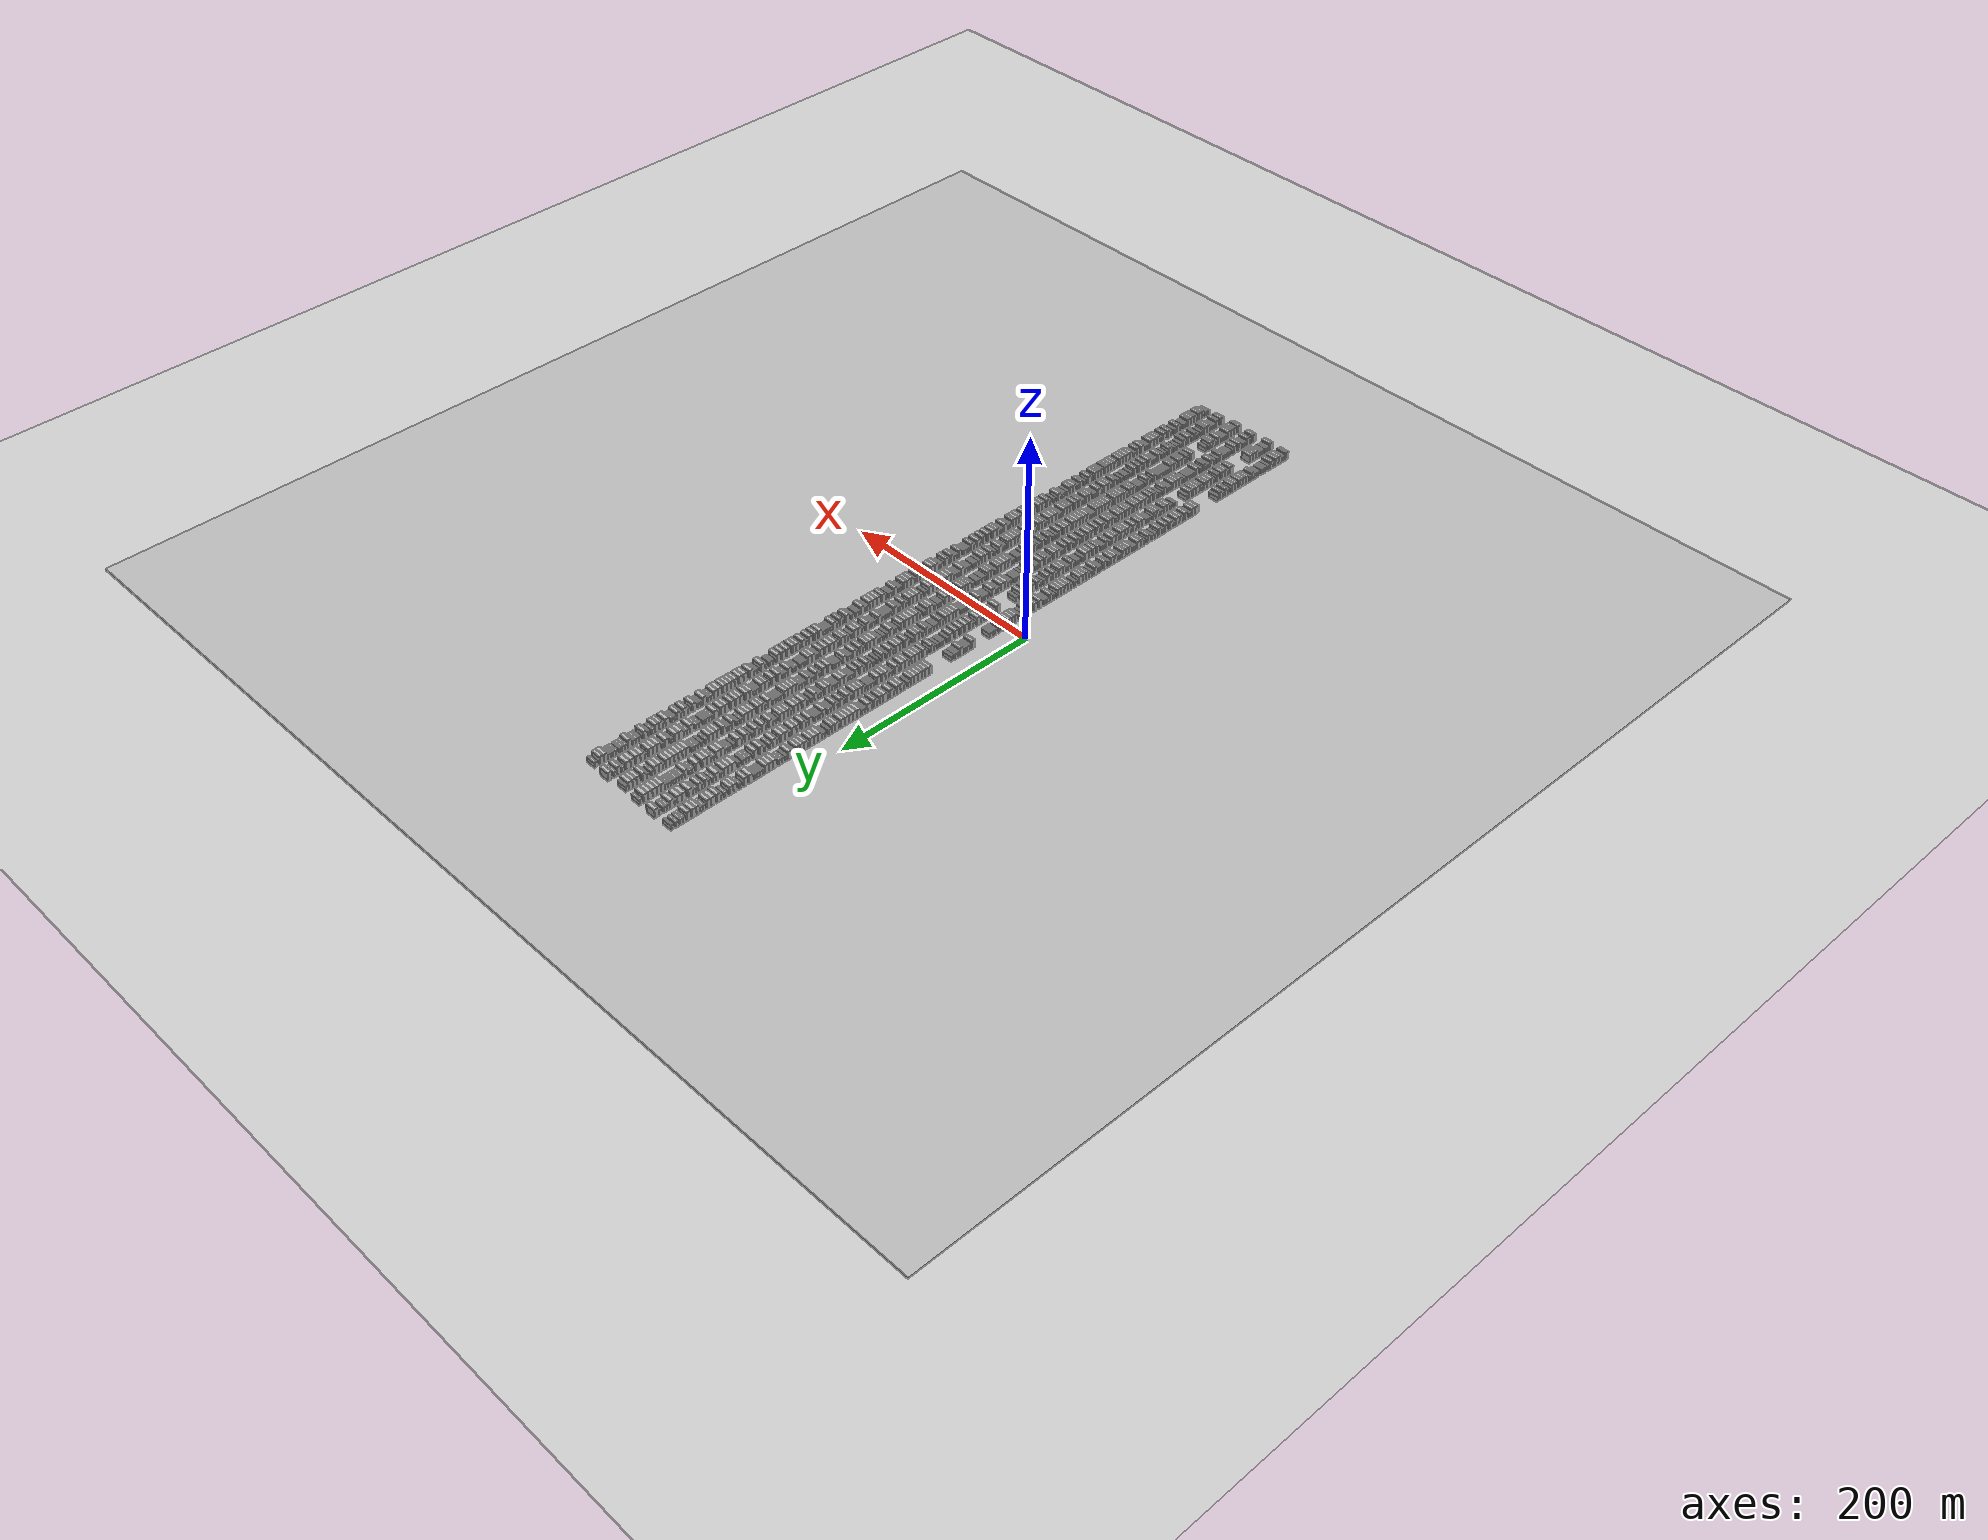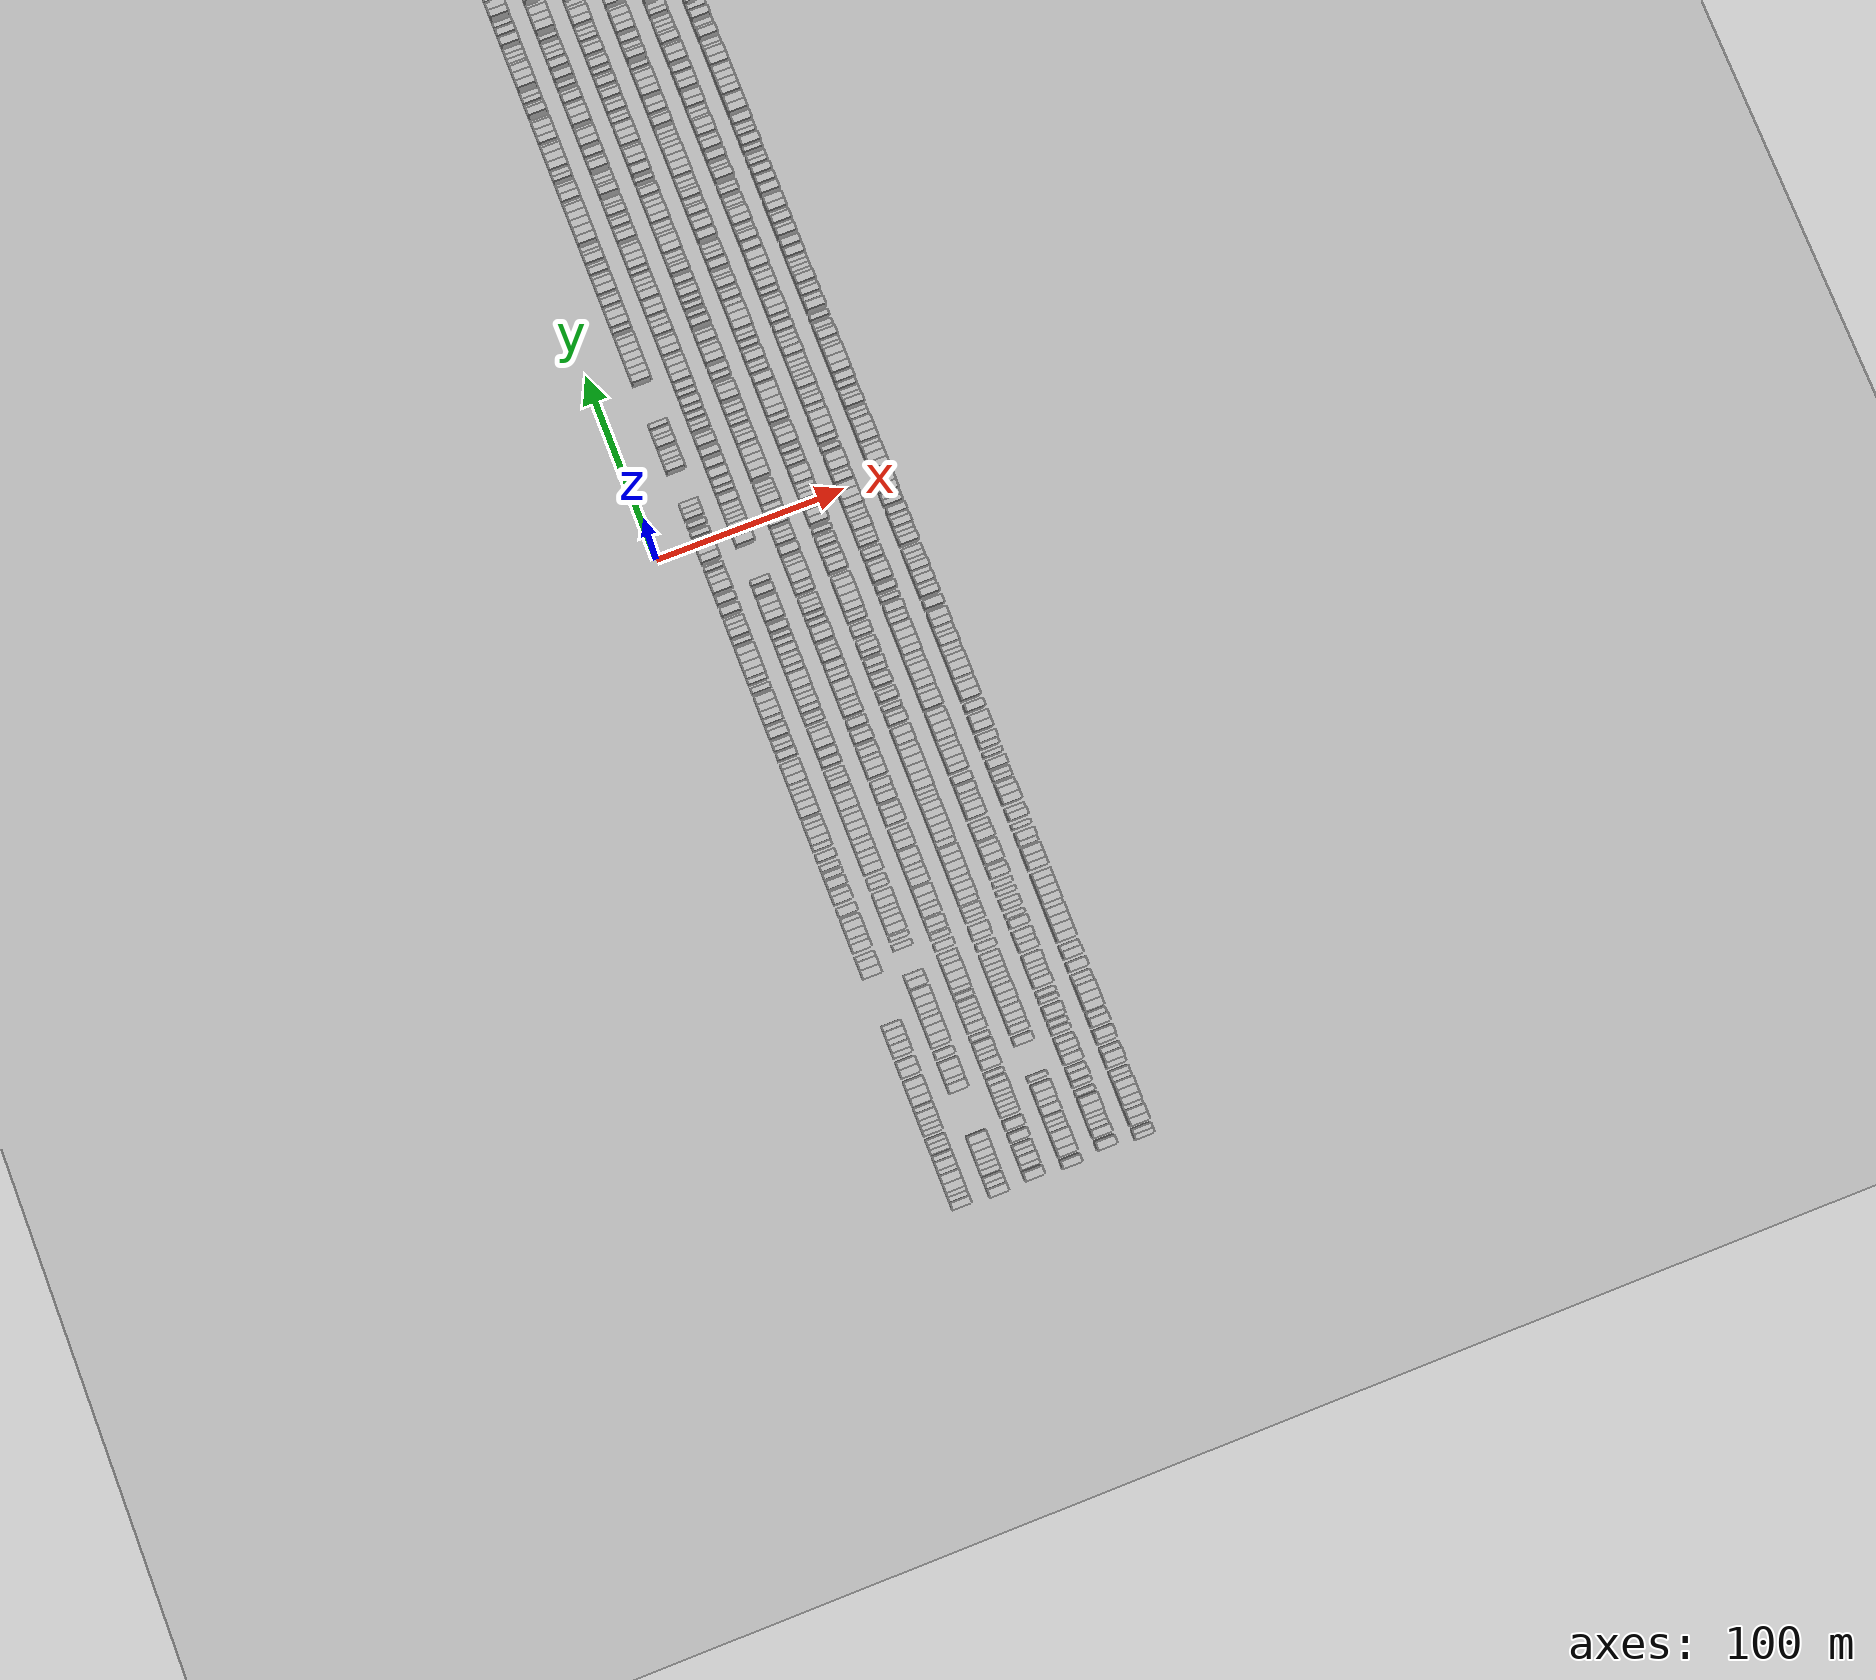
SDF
<?xml version="1.0" encoding="utf-8"?>

<sdf version="1.6">

   <world name="default">

      <gui fullscreen="0">

         <camera name="user_camera">

            <pose>-15 0 4.57585 0 0 0</pose>

            <view_controller>orbit</view_controller>

         </camera>

      </gui>

      <scene>

         <sky>

           <clouds>

             <speed>12</speed>

           </clouds>

         </sky>

         <ambient>0.4 0.4 0.4 1</ambient>

         <background>0.7 0.7 0.7 1</background>

         <shadows>1</shadows>

      </scene>

      <gravity>0 0 -9.8066</gravity>

      <magnetic_field>6e-06 2.3e-05 -4.2e-05</magnetic_field>

      <physics default="0" name="default_physics" type="ode">

         <ode>

            <solver>

               <type>quick</type>

               <iters>10</iters>

               <sor>1.0</sor>

               <use_dynamic_moi_rescaling>0</use_dynamic_moi_rescaling>

            </solver>

            <constraints>

               <cfm>0</cfm>

               <erp>0.2</erp>

               <contact_max_correcting_vel>100</contact_max_correcting_vel>

               <contact_surface_layer>0.001</contact_surface_layer>

            </constraints>

         </ode>

         <max_step_size>0.004</max_step_size>

         <real_time_factor>1</real_time_factor>

         <real_time_update_rate>250</real_time_update_rate>

      </physics>

      <light name="sun" type="directional">

         <cast_shadows>1</cast_shadows>

         <pose>0 0 10 0 0 0</pose>

         <diffuse>0.8 0.8 0.8 1</diffuse>

         <specular>0.2 0.2 0.2 1</specular>

         <attenuation>

            <range>1000</range>

            <constant>0.9</constant>

            <linear>0.01</linear>

            <quadratic>0.001</quadratic>

         </attenuation>

         <direction>-0.5 0.1 -0.9</direction>

      </light>

      <include>

         <name>ground_plane_1</name>

         <uri>model://HANNAS_ground_plane</uri>

         <pose>0 0 0  0 0 0</pose>

      </include>

      <include>

         <name>ground_plane_2</name>

         <uri>model://HANNAS_ground_plane</uri>

         <pose>100 0 0  0 0 0</pose>

      </include>

      <model name="building_1">

         <static>1</static>

         <pose frame="">25.0000 -347.1879 0 0.000000 0.000000 0.000000</pose>

         <link name="link">

            <pose frame="">0 0 4.50 0 0 0</pose>

            <collision name="collision">

               <geometry>

                  <box>

                     <size>10.0000 3.6242 9.0000</size>

                  </box>

               </geometry>

               <max_contacts>10</max_contacts>

               <surface>

                  <contact>

                     <ode/>

                  </contact>

                  <bounce/>

                  <friction>

                     <torsional>

                        <ode/>

                     </torsional>

                     <ode/>

                  </friction>

               </surface>

            </collision>

            <visual name="visual">

               <cast_shadows>0</cast_shadows>

               <geometry>

                  <box>

                     <size>10.0000 3.6242 9.0000</size>

                  </box>

               </geometry>

               <material>

                  <script>

                     <uri>model://HANNAS_wall/materials/scripts</uri>

                     <uri>model://HANNAS_wall/materials/textures</uri>

                     <name>vrc/HANNAS_wall</name>

                  </script>

               </material>

            </visual>

            <self_collide>0</self_collide>

            <enable_wind>0</enable_wind>

            <kinematic>0</kinematic>

         </link>

      </model>

      <model name="building_2">

         <static>1</static>

         <pose frame="">25.0000 -344.0635 0 0.000000 0.000000 0.000000</pose>

         <link name="link">

            <pose frame="">0 0 3.00 0 0 0</pose>

            <collision name="collision">

               <geometry>

                  <box>

                     <size>10.0000 2.6245 6.0000</size>

                  </box>

               </geometry>

               <max_contacts>10</max_contacts>

               <surface>

                  <contact>

                     <ode/>

                  </contact>

                  <bounce/>

                  <friction>

                     <torsional>

                        <ode/>

                     </torsional>

                     <ode/>

                  </friction>

               </surface>

            </collision>

            <visual name="visual">

               <cast_shadows>0</cast_shadows>

               <geometry>

                  <box>

                     <size>10.0000 2.6245 6.0000</size>

                  </box>

               </geometry>

               <material>

                  <script>

                     <uri>model://HANNAS_wall/materials/scripts</uri>

                     <uri>model://HANNAS_wall/materials/textures</uri>

                     <name>vrc/HANNAS_wall</name>

                  </script>

               </material>

            </visual>

            <self_collide>0</self_collide>

            <enable_wind>0</enable_wind>

            <kinematic>0</kinematic>

         </link>

      </model>

      <model name="building_3">

         <static>1</static>

         <pose frame="">25.0000 -341.4922 0 0.000000 0.000000 0.000000</pose>

         <link name="link">

            <pose frame="">0 0 3.00 0 0 0</pose>

            <collision name="collision">

               <geometry>

                  <box>

                     <size>10.0000 2.5183 6.0000</size>

                  </box>

               </geometry>

               <max_contacts>10</max_contacts>

               <surface>

                  <contact>

                     <ode/>

                  </contact>

                  <bounce/>

                  <friction>

                     <torsional>

                        <ode/>

                     </torsional>

                     <ode/>

                  </friction>

               </surface>

            </collision>

            <visual name="visual">

               <cast_shadows>0</cast_shadows>

               <geometry>

                  <box>

                     <size>10.0000 2.5183 6.0000</size>

                  </box>

               </geometry>

               <material>

                  <script>

                     <uri>model://HANNAS_wall/materials/scripts</uri>

                     <uri>model://HANNAS_wall/materials/textures</uri>

                     <name>vrc/HANNAS_wall</name>

                  </script>

               </material>

            </visual>

            <self_collide>0</self_collide>

            <enable_wind>0</enable_wind>

            <kinematic>0</kinematic>

         </link>

      </model>

      <model name="building_4">

         <static>1</static>

         <pose frame="">25.0000 -338.0847 0 0.000000 0.000000 0.000000</pose>

         <link name="link">

            <pose frame="">0 0 4.50 0 0 0</pose>

            <collision name="collision">

               <geometry>

                  <box>

                     <size>10.0000 4.2967 9.0000</size>

                  </box>

               </geometry>

               <max_contacts>10</max_contacts>

               <surface>

                  <contact>

                     <ode/>

                  </contact>

                  <bounce/>

                  <friction>

                     <torsional>

                        <ode/>

                     </torsional>

                     <ode/>

                  </friction>

               </surface>

            </collision>

            <visual name="visual">

               <cast_shadows>0</cast_shadows>

               <geometry>

                  <box>

                     <size>10.0000 4.2967 9.0000</size>

                  </box>

               </geometry>

               <material>

                  <script>

                     <uri>model://HANNAS_wall/materials/scripts</uri>

                     <uri>model://HANNAS_wall/materials/textures</uri>

                     <name>vrc/HANNAS_wall</name>

                  </script>

               </material>

            </visual>

            <self_collide>0</self_collide>

            <enable_wind>0</enable_wind>

            <kinematic>0</kinematic>

         </link>

      </model>

      <model name="building_5">

         <static>1</static>

         <pose frame="">25.0000 -333.7913 0 0.000000 0.000000 0.000000</pose>

         <link name="link">

            <pose frame="">0 0 4.50 0 0 0</pose>

            <collision name="collision">

               <geometry>

                  <box>

                     <size>10.0000 4.2900 9.0000</size>

                  </box>

               </geometry>

               <max_contacts>10</max_contacts>

               <surface>

                  <contact>

                     <ode/>

                  </contact>

                  <bounce/>

                  <friction>

                     <torsional>

                        <ode/>

                     </torsional>

                     <ode/>

                  </friction>

               </surface>

            </collision>

            <visual name="visual">

               <cast_shadows>0</cast_shadows>

               <geometry>

                  <box>

                     <size>10.0000 4.2900 9.0000</size>

                  </box>

               </geometry>

               <material>

                  <script>

                     <uri>model://HANNAS_wall/materials/scripts</uri>

                     <uri>model://HANNAS_wall/materials/textures</uri>

                     <name>vrc/HANNAS_wall</name>

                  </script>

               </material>

            </visual>

            <self_collide>0</self_collide>

            <enable_wind>0</enable_wind>

            <kinematic>0</kinematic>

         </link>

      </model>

      <model name="building_6">

         <static>1</static>

         <pose frame="">25.0000 -330.2938 0 0.000000 0.000000 0.000000</pose>

         <link name="link">

            <pose frame="">0 0 3.00 0 0 0</pose>

            <collision name="collision">

               <geometry>

                  <box>

                     <size>10.0000 2.7050 6.0000</size>

                  </box>

               </geometry>

               <max_contacts>10</max_contacts>

               <surface>

                  <contact>

                     <ode/>

                  </contact>

                  <bounce/>

                  <friction>

                     <torsional>

                        <ode/>

                     </torsional>

                     <ode/>

                  </friction>

               </surface>

            </collision>

            <visual name="visual">

               <cast_shadows>0</cast_shadows>

               <geometry>

                  <box>

                     <size>10.0000 2.7050 6.0000</size>

                  </box>

               </geometry>

               <material>

                  <script>

                     <uri>model://HANNAS_wall/materials/scripts</uri>

                     <uri>model://HANNAS_wall/materials/textures</uri>

                     <name>vrc/HANNAS_wall</name>

                  </script>

               </material>

            </visual>

            <self_collide>0</self_collide>

            <enable_wind>0</enable_wind>

            <kinematic>0</kinematic>

         </link>

      </model>

      <model name="building_7">

         <static>1</static>

         <pose frame="">25.0000 -326.9067 0 0.000000 0.000000 0.000000</pose>

         <link name="link">

            <pose frame="">0 0 4.50 0 0 0</pose>

            <collision name="collision">

               <geometry>

                  <box>

                     <size>10.0000 4.0691 9.0000</size>

                  </box>

               </geometry>

               <max_contacts>10</max_contacts>

               <surface>

                  <contact>

                     <ode/>

                  </contact>

                  <bounce/>

                  <friction>

                     <torsional>

                        <ode/>

                     </torsional>

                     <ode/>

                  </friction>

               </surface>

            </collision>

            <visual name="visual">

               <cast_shadows>0</cast_shadows>

               <geometry>

                  <box>

                     <size>10.0000 4.0691 9.0000</size>

                  </box>

               </geometry>

               <material>

                  <script>

                     <uri>model://HANNAS_wall/materials/scripts</uri>

                     <uri>model://HANNAS_wall/materials/textures</uri>

                     <name>vrc/HANNAS_wall</name>

                  </script>

               </material>

            </visual>

            <self_collide>0</self_collide>

            <enable_wind>0</enable_wind>

            <kinematic>0</kinematic>

         </link>

      </model>

      <model name="building_8">

         <static>1</static>

         <pose frame="">25.0000 -323.5153 0 0.000000 0.000000 0.000000</pose>

         <link name="link">

            <pose frame="">0 0 3.00 0 0 0</pose>

            <collision name="collision">

               <geometry>

                  <box>

                     <size>10.0000 2.7138 6.0000</size>

                  </box>

               </geometry>

               <max_contacts>10</max_contacts>

               <surface>

                  <contact>

                     <ode/>

                  </contact>

                  <bounce/>

                  <friction>

                     <torsional>

                        <ode/>

                     </torsional>

                     <ode/>

                  </friction>

               </surface>

            </collision>

            <visual name="visual">

               <cast_shadows>0</cast_shadows>

               <geometry>

                  <box>

                     <size>10.0000 2.7138 6.0000</size>

                  </box>

               </geometry>

               <material>

                  <script>

                     <uri>model://HANNAS_wall/materials/scripts</uri>

                     <uri>model://HANNAS_wall/materials/textures</uri>

                     <name>vrc/HANNAS_wall</name>

                  </script>

               </material>

            </visual>

            <self_collide>0</self_collide>

            <enable_wind>0</enable_wind>

            <kinematic>0</kinematic>

         </link>

      </model>

      <model name="building_9">

         <static>1</static>

         <pose frame="">25.0000 -319.9232 0 0.000000 0.000000 0.000000</pose>

         <link name="link">

            <pose frame="">0 0 3.00 0 0 0</pose>

            <collision name="collision">

               <geometry>

                  <box>

                     <size>10.0000 2.4704 6.0000</size>

                  </box>

               </geometry>

               <max_contacts>10</max_contacts>

               <surface>

                  <contact>

                     <ode/>

                  </contact>

                  <bounce/>

                  <friction>

                     <torsional>

                        <ode/>

                     </torsional>

                     <ode/>

                  </friction>

               </surface>

            </collision>

            <visual name="visual">

               <cast_shadows>0</cast_shadows>

               <geometry>

                  <box>

                     <size>10.0000 2.4704 6.0000</size>

                  </box>

               </geometry>

               <material>

                  <script>

                     <uri>model://HANNAS_wall/materials/scripts</uri>

                     <uri>model://HANNAS_wall/materials/textures</uri>

                     <name>vrc/HANNAS_wall</name>

                  </script>

               </material>

            </visual>

            <self_collide>0</self_collide>

            <enable_wind>0</enable_wind>

            <kinematic>0</kinematic>

         </link>

      </model>

      <model name="building_10">

         <static>1</static>

         <pose frame="">25.0000 -317.3774 0 0.000000 0.000000 0.000000</pose>

         <link name="link">

            <pose frame="">0 0 3.00 0 0 0</pose>

            <collision name="collision">

               <geometry>

                  <box>

                     <size>10.0000 2.6212 6.0000</size>

                  </box>

               </geometry>

               <max_contacts>10</max_contacts>

               <surface>

                  <contact>

                     <ode/>

                  </contact>

                  <bounce/>

                  <friction>

                     <torsional>

                        <ode/>

                     </torsional>

                     <ode/>

                  </friction>

               </surface>

            </collision>

            <visual name="visual">

               <cast_shadows>0</cast_shadows>

               <geometry>

                  <box>

                     <size>10.0000 2.6212 6.0000</size>

                  </box>

               </geometry>

               <material>

                  <script>

                     <uri>model://HANNAS_wall/materials/scripts</uri>

                     <uri>model://HANNAS_wall/materials/textures</uri>

                     <name>vrc/HANNAS_wall</name>

                  </script>

               </material>

            </visual>

            <self_collide>0</self_collide>

            <enable_wind>0</enable_wind>

            <kinematic>0</kinematic>

         </link>

      </model>

      <model name="building_11">

         <static>1</static>

         <pose frame="">25.0000 -314.8654 0 0.000000 0.000000 0.000000</pose>

         <link name="link">

            <pose frame="">0 0 3.00 0 0 0</pose>

            <collision name="collision">

               <geometry>

                  <box>

                     <size>10.0000 2.4026 6.0000</size>

                  </box>

               </geometry>

               <max_contacts>10</max_contacts>

               <surface>

                  <contact>

                     <ode/>

                  </contact>

                  <bounce/>

                  <friction>

                     <torsional>

                        <ode/>

                     </torsional>

                     <ode/>

                  </friction>

               </surface>

            </collision>

            <visual name="visual">

               <cast_shadows>0</cast_shadows>

               <geometry>

                  <box>

                     <size>10.0000 2.4026 6.0000</size>

                  </box>

               </geometry>

               <material>

                  <script>

                     <uri>model://HANNAS_wall/materials/scripts</uri>

                     <uri>model://HANNAS_wall/materials/textures</uri>

                     <name>vrc/HANNAS_wall</name>

                  </script>

               </material>

            </visual>

            <self_collide>0</self_collide>

            <enable_wind>0</enable_wind>

            <kinematic>0</kinematic>

         </link>

      </model>

      <model name="building_12">

         <static>1</static>

         <pose frame="">25.0000 -310.3751 0 0.000000 0.000000 0.000000</pose>

         <link name="link">

            <pose frame="">0 0 3.00 0 0 0</pose>

            <collision name="collision">

               <geometry>

                  <box>

                     <size>10.0000 2.5780 6.0000</size>

                  </box>

               </geometry>

               <max_contacts>10</max_contacts>

               <surface>

                  <contact>

                     <ode/>

                  </contact>

                  <bounce/>

                  <friction>

                     <torsional>

                        <ode/>

                     </torsional>

                     <ode/>

                  </friction>

               </surface>

            </collision>

            <visual name="visual">

               <cast_shadows>0</cast_shadows>

               <geometry>

                  <box>

                     <size>10.0000 2.5780 6.0000</size>

                  </box>

               </geometry>

               <material>

                  <script>

                     <uri>model://HANNAS_wall/materials/scripts</uri>

                     <uri>model://HANNAS_wall/materials/textures</uri>

                     <name>vrc/HANNAS_wall</name>

                  </script>

               </material>

            </visual>

            <self_collide>0</self_collide>

            <enable_wind>0</enable_wind>

            <kinematic>0</kinematic>

         </link>

      </model>

      <model name="building_13">

         <static>1</static>

         <pose frame="">25.0000 -307.8042 0 0.000000 0.000000 0.000000</pose>

         <link name="link">

            <pose frame="">0 0 3.00 0 0 0</pose>

            <collision name="collision">

               <geometry>

                  <box>

                     <size>10.0000 2.5639 6.0000</size>

                  </box>

               </geometry>

               <max_contacts>10</max_contacts>

               <surface>

                  <contact>

                     <ode/>

                  </contact>

                  <bounce/>

                  <friction>

                     <torsional>

                        <ode/>

                     </torsional>

                     <ode/>

                  </friction>

               </surface>

            </collision>

            <visual name="visual">

               <cast_shadows>0</cast_shadows>

               <geometry>

                  <box>

                     <size>10.0000 2.5639 6.0000</size>

                  </box>

               </geometry>

               <material>

                  <script>

                     <uri>model://HANNAS_wall/materials/scripts</uri>

                     <uri>model://HANNAS_wall/materials/textures</uri>

                     <name>vrc/HANNAS_wall</name>

                  </script>

               </material>

            </visual>

            <self_collide>0</self_collide>

            <enable_wind>0</enable_wind>

            <kinematic>0</kinematic>

         </link>

      </model>

      <model name="building_14">

         <static>1</static>

         <pose frame="">25.0000 -305.0713 0 0.000000 0.000000 0.000000</pose>

         <link name="link">

            <pose frame="">0 0 3.00 0 0 0</pose>

            <collision name="collision">

               <geometry>

                  <box>

                     <size>10.0000 2.9018 6.0000</size>

                  </box>

               </geometry>

               <max_contacts>10</max_contacts>

               <surface>

                  <contact>

                     <ode/>

                  </contact>

                  <bounce/>

                  <friction>

                     <torsional>

                        <ode/>

                     </torsional>

                     <ode/>

                  </friction>

               </surface>

            </collision>

            <visual name="visual">

               <cast_shadows>0</cast_shadows>

               <geometry>

                  <box>

                     <size>10.0000 2.9018 6.0000</size>

                  </box>

               </geometry>

               <material>

                  <script>

                     <uri>model://HANNAS_wall/materials/scripts</uri>

                     <uri>model://HANNAS_wall/materials/textures</uri>

                     <name>vrc/HANNAS_wall</name>

                  </script>

               </material>

            </visual>

            <self_collide>0</self_collide>

            <enable_wind>0</enable_wind>

            <kinematic>0</kinematic>

         </link>

      </model>

      <model name="building_15">

         <static>1</static>

         <pose frame="">25.0000 -301.7940 0 0.000000 0.000000 0.000000</pose>

         <link name="link">

            <pose frame="">0 0 4.50 0 0 0</pose>

            <collision name="collision">

               <geometry>

                  <box>

                     <size>10.0000 3.6529 9.0000</size>

                  </box>

               </geometry>

               <max_contacts>10</max_contacts>

               <surface>

                  <contact>

                     <ode/>

                  </contact>

                  <bounce/>

                  <friction>

                     <torsional>

                        <ode/>

                     </torsional>

                     <ode/>

                  </friction>

               </surface>

            </collision>

            <visual name="visual">

               <cast_shadows>0</cast_shadows>

               <geometry>

                  <box>

                     <size>10.0000 3.6529 9.0000</size>

                  </box>

               </geometry>

               <material>

                  <script>

                     <uri>model://HANNAS_wall/materials/scripts</uri>

                     <uri>model://HANNAS_wall/materials/textures</uri>

                     <name>vrc/HANNAS_wall</name>

                  </script>

               </material>

            </visual>

            <self_collide>0</self_collide>

            <enable_wind>0</enable_wind>

            <kinematic>0</kinematic>

         </link>

      </model>

      <model name="building_16">

         <static>1</static>

         <pose frame="">25.0000 -298.6746 0 0.000000 0.000000 0.000000</pose>

         <link name="link">

            <pose frame="">0 0 3.00 0 0 0</pose>

            <collision name="collision">

               <geometry>

                  <box>

                     <size>10.0000 2.5859 6.0000</size>

                  </box>

               </geometry>

               <max_contacts>10</max_contacts>

               <surface>

                  <contact>

                     <ode/>

                  </contact>

                  <bounce/>

                  <friction>

                     <torsional>

                        <ode/>

                     </torsional>

                     <ode/>

                  </friction>

               </surface>

            </collision>

            <visual name="visual">

               <cast_shadows>0</cast_shadows>

               <geometry>

                  <box>

                     <size>10.0000 2.5859 6.0000</size>

                  </box>

               </geometry>

               <material>

                  <script>

                     <uri>model://HANNAS_wall/materials/scripts</uri>

                     <uri>model://HANNAS_wall/materials/textures</uri>

                     <name>vrc/HANNAS_wall</name>

                  </script>

               </material>

            </visual>

            <self_collide>0</self_collide>

            <enable_wind>0</enable_wind>

            <kinematic>0</kinematic>

         </link>

      </model>

      <model name="building_17">

         <static>1</static>

         <pose frame="">25.0000 -294.3288 0 0.000000 0.000000 0.000000</pose>

         <link name="link">

            <pose frame="">0 0 4.50 0 0 0</pose>

            <collision name="collision">

               <geometry>

                  <box>

                     <size>10.0000 4.1056 9.0000</size>

                  </box>

               </geometry>

               <max_contacts>10</max_contacts>

               <surface>

                  <contact>

                     <ode/>

                  </contact>

                  <bounce/>

                  <friction>

                     <torsional>

                        <ode/>

                     </torsional>

                     <ode/>

                  </friction>

               </surface>

            </collision>

            <visual name="visual">

               <cast_shadows>0</cast_shadows>

               <geometry>

                  <box>

                     <size>10.0000 4.1056 9.0000</size>

                  </box>

               </geometry>

               <material>

                  <script>

                     <uri>model://HANNAS_wall/materials/scripts</uri>

                     <uri>model://HANNAS_wall/materials/textures</uri>

                     <name>vrc/HANNAS_wall</name>

                  </script>

               </material>

            </visual>

            <self_collide>0</self_collide>

            <enable_wind>0</enable_wind>

            <kinematic>0</kinematic>

         </link>

      </model>

      <model name="building_18">

         <static>1</static>

         <pose frame="">25.0000 -290.0642 0 0.000000 0.000000 0.000000</pose>

         <link name="link">

            <pose frame="">0 0 4.50 0 0 0</pose>

            <collision name="collision">

               <geometry>

                  <box>

                     <size>10.0000 4.4236 9.0000</size>

                  </box>

               </geometry>

               <max_contacts>10</max_contacts>

               <surface>

                  <contact>

                     <ode/>

                  </contact>

                  <bounce/>

                  <friction>

                     <torsional>

                        <ode/>

                     </torsional>

                     <ode/>

                  </friction>

               </surface>

            </collision>

            <visual name="visual">

               <cast_shadows>0</cast_shadows>

               <geometry>

                  <box>

                     <size>10.0000 4.4236 9.0000</size>

                  </box>

               </geometry>

               <material>

                  <script>

                     <uri>model://HANNAS_wall/materials/scripts</uri>

                     <uri>model://HANNAS_wall/materials/textures</uri>

                     <name>vrc/HANNAS_wall</name>

                  </script>

               </material>

            </visual>

            <self_collide>0</self_collide>

            <enable_wind>0</enable_wind>

            <kinematic>0</kinematic>

         </link>

      </model>

      <model name="building_19">

         <static>1</static>

         <pose frame="">25.0000 -285.8261 0 0.000000 0.000000 0.000000</pose>

         <link name="link">

            <pose frame="">0 0 4.50 0 0 0</pose>

            <collision name="collision">

               <geometry>

                  <box>

                     <size>10.0000 4.0528 9.0000</size>

                  </box>

               </geometry>

               <max_contacts>10</max_contacts>

               <surface>

                  <contact>

                     <ode/>

                  </contact>

                  <bounce/>

                  <friction>

                     <torsional>

                        <ode/>

                     </torsional>

                     <ode/>

                  </friction>

               </surface>

            </collision>

            <visual name="visual">

               <cast_shadows>0</cast_shadows>

               <geometry>

                  <box>

                     <size>10.0000 4.0528 9.0000</size>

                  </box>

               </geometry>

               <material>

                  <script>

                     <uri>model://HANNAS_wall/materials/scripts</uri>

                     <uri>model://HANNAS_wall/materials/textures</uri>

                     <name>vrc/HANNAS_wall</name>

                  </script>

               </material>

            </visual>

            <self_collide>0</self_collide>

            <enable_wind>0</enable_wind>

            <kinematic>0</kinematic>

         </link>

      </model>

      <model name="building_20">

         <static>1</static>

         <pose frame="">25.0000 -279.6856 0 0.000000 0.000000 0.000000</pose>

         <link name="link">

            <pose frame="">0 0 4.50 0 0 0</pose>

            <collision name="collision">

               <geometry>

                  <box>

                     <size>10.0000 4.2282 9.0000</size>

                  </box>

               </geometry>

               <max_contacts>10</max_contacts>

               <surface>

                  <contact>

                     <ode/>

                  </contact>

                  <bounce/>

                  <friction>

                     <torsional>

                        <ode/>

                     </torsional>

                     <ode/>

                  </friction>

               </surface>

            </collision>

            <visual name="visual">

               <cast_shadows>0</cast_shadows>

               <geometry>

                  <box>

                     <size>10.0000 4.2282 9.0000</size>

                  </box>

               </geometry>

               <material>

                  <script>

                     <uri>model://HANNAS_wall/materials/scripts</uri>

                     <uri>model://HANNAS_wall/materials/textures</uri>

                     <name>vrc/HANNAS_wall</name>

                  </script>

               </material>

            </visual>

            <self_collide>0</self_collide>

            <enable_wind>0</enable_wind>

            <kinematic>0</kinematic>

         </link>

      </model>

      <model name="building_21">

         <static>1</static>

         <pose frame="">25.0000 -275.5950 0 0.000000 0.000000 0.000000</pose>

         <link name="link">

            <pose frame="">0 0 4.50 0 0 0</pose>

            <collision name="collision">

               <geometry>

                  <box>

                     <size>10.0000 3.9529 9.0000</size>

                  </box>

               </geometry>

               <max_contacts>10</max_contacts>

               <surface>

                  <contact>

                     <ode/>

                  </contact>

                  <bounce/>

                  <friction>

                     <torsional>

                        <ode/>

                     </torsional>

                     <ode/>

                  </friction>

               </surface>

            </collision>

            <visual name="visual">

               <cast_shadows>0</cast_shadows>

               <geometry>

                  <box>

                     <size>10.0000 3.9529 9.0000</size>

                  </box>

               </geometry>

               <material>

                  <script>

                     <uri>model://HANNAS_wall/materials/scripts</uri>

                     <uri>model://HANNAS_wall/materials/textures</uri>

                     <name>vrc/HANNAS_wall</name>

                  </script>

               </material>

            </visual>

            <self_collide>0</self_collide>

            <enable_wind>0</enable_wind>

            <kinematic>0</kinematic>

         </link>

      </model>

      <model name="building_22">

         <static>1</static>

         <pose frame="">25.0000 -270.2012 0 0.000000 0.000000 0.000000</pose>

         <link name="link">

            <pose frame="">0 0 3.00 0 0 0</pose>

            <collision name="collision">

               <geometry>

                  <box>

                     <size>10.0000 2.8348 6.0000</size>

                  </box>

               </geometry>

               <max_contacts>10</max_contacts>

               <surface>

                  <contact>

                     <ode/>

                  </contact>

                  <bounce/>

                  <friction>

                     <torsional>

                        <ode/>

                     </torsional>

                     <ode/>

                  </friction>

               </surface>

            </collision>

            <visual name="visual">

               <cast_shadows>0</cast_shadows>

               <geometry>

                  <box>

                     <size>10.0000 2.8348 6.0000</size>

                  </box>

               </geometry>

               <material>

                  <script>

                     <uri>model://HANNAS_wall/materials/scripts</uri>

                     <uri>model://HANNAS_wall/materials/textures</uri>

                     <name>vrc/HANNAS_wall</name>

                  </script>

               </material>

            </visual>

            <self_collide>0</self_collide>

            <enable_wind>0</enable_wind>

            <kinematic>0</kinematic>

         </link>

      </model>

      <model name="building_23">

         <static>1</static>

         <pose frame="">25.0000 -266.9087 0 0.000000 0.000000 0.000000</pose>

         <link name="link">

            <pose frame="">0 0 4.50 0 0 0</pose>

            <collision name="collision">

               <geometry>

                  <box>

                     <size>10.0000 3.7501 9.0000</size>

                  </box>

               </geometry>

               <max_contacts>10</max_contacts>

               <surface>

                  <contact>

                     <ode/>

                  </contact>

                  <bounce/>

                  <friction>

                     <torsional>

                        <ode/>

                     </torsional>

                     <ode/>

                  </friction>

               </surface>

            </collision>

            <visual name="visual">

               <cast_shadows>0</cast_shadows>

               <geometry>

                  <box>

                     <size>10.0000 3.7501 9.0000</size>

                  </box>

               </geometry>

               <material>

                  <script>

                     <uri>model://HANNAS_wall/materials/scripts</uri>

                     <uri>model://HANNAS_wall/materials/textures</uri>

                     <name>vrc/HANNAS_wall</name>

                  </script>

               </material>

            </visual>

            <self_collide>0</self_collide>

            <enable_wind>0</enable_wind>

            <kinematic>0</kinematic>

         </link>

      </model>

      <model name="building_24">

         <static>1</static>

         <pose frame="">25.0000 -263.5351 0 0.000000 0.000000 0.000000</pose>

         <link name="link">

            <pose frame="">0 0 3.00 0 0 0</pose>

            <collision name="collision">

               <geometry>

                  <box>

                     <size>10.0000 2.9970 6.0000</size>

                  </box>

               </geometry>

               <max_contacts>10</max_contacts>

               <surface>

                  <contact>

                     <ode/>

                  </contact>

                  <bounce/>

                  <friction>

                     <torsional>

                        <ode/>

                     </torsional>

                     <ode/>

                  </friction>

               </surface>

            </collision>

            <visual name="visual">

               <cast_shadows>0</cast_shadows>

               <geometry>

                  <box>

                     <size>10.0000 2.9970 6.0000</size>

                  </box>

               </geometry>

               <material>

                  <script>

                     <uri>model://HANNAS_wall/materials/scripts</uri>

                     <uri>model://HANNAS_wall/materials/textures</uri>

                     <name>vrc/HANNAS_wall</name>

                  </script>

               </material>

            </visual>

            <self_collide>0</self_collide>

            <enable_wind>0</enable_wind>

            <kinematic>0</kinematic>

         </link>

      </model>

      <model name="building_25">

         <static>1</static>

         <pose frame="">25.0000 -259.9941 0 0.000000 0.000000 0.000000</pose>

         <link name="link">

            <pose frame="">0 0 4.50 0 0 0</pose>

            <collision name="collision">

               <geometry>

                  <box>

                     <size>10.0000 4.0851 9.0000</size>

                  </box>

               </geometry>

               <max_contacts>10</max_contacts>

               <surface>

                  <contact>

                     <ode/>

                  </contact>

                  <bounce/>

                  <friction>

                     <torsional>

                        <ode/>

                     </torsional>

                     <ode/>

                  </friction>

               </surface>

            </collision>

            <visual name="visual">

               <cast_shadows>0</cast_shadows>

               <geometry>

                  <box>

                     <size>10.0000 4.0851 9.0000</size>

                  </box>

               </geometry>

               <material>

                  <script>

                     <uri>model://HANNAS_wall/materials/scripts</uri>

                     <uri>model://HANNAS_wall/materials/textures</uri>

                     <name>vrc/HANNAS_wall</name>

                  </script>

               </material>

            </visual>

            <self_collide>0</self_collide>

            <enable_wind>0</enable_wind>

            <kinematic>0</kinematic>

         </link>

      </model>

      <model name="building_26">

         <static>1</static>

         <pose frame="">25.0000 -256.5122 0 0.000000 0.000000 0.000000</pose>

         <link name="link">

            <pose frame="">0 0 3.00 0 0 0</pose>

            <collision name="collision">

               <geometry>

                  <box>

                     <size>10.0000 2.8787 6.0000</size>

                  </box>

               </geometry>

               <max_contacts>10</max_contacts>

               <surface>

                  <contact>

                     <ode/>

                  </contact>

                  <bounce/>

                  <friction>

                     <torsional>

                        <ode/>

                     </torsional>

                     <ode/>

                  </friction>

               </surface>

            </collision>

            <visual name="visual">

               <cast_shadows>0</cast_shadows>

               <geometry>

                  <box>

                     <size>10.0000 2.8787 6.0000</size>

                  </box>

               </geometry>

               <material>

                  <script>

                     <uri>model://HANNAS_wall/materials/scripts</uri>

                     <uri>model://HANNAS_wall/materials/textures</uri>

                     <name>vrc/HANNAS_wall</name>

                  </script>

               </material>

            </visual>

            <self_collide>0</self_collide>

            <enable_wind>0</enable_wind>

            <kinematic>0</kinematic>

         </link>

      </model>

      <model name="building_27">

         <static>1</static>

         <pose frame="">25.0000 -228.3503 0 0.000000 0.000000 0.000000</pose>

         <link name="link">

            <pose frame="">0 0 4.50 0 0 0</pose>

            <collision name="collision">

               <geometry>

                  <box>

                     <size>10.0000 4.4817 9.0000</size>

                  </box>

               </geometry>

               <max_contacts>10</max_contacts>

               <surface>

                  <contact>

                     <ode/>

                  </contact>

                  <bounce/>

                  <friction>

                     <torsional>

                        <ode/>

                     </torsional>

                     <ode/>

                  </friction>

               </surface>

            </collision>

            <visual name="visual">

               <cast_shadows>0</cast_shadows>

               <geometry>

                  <box>

                     <size>10.0000 4.4817 9.0000</size>

                  </box>

               </geometry>

               <material>

                  <script>

                     <uri>model://HANNAS_wall/materials/scripts</uri>

                     <uri>model://HANNAS_wall/materials/textures</uri>

                     <name>vrc/HANNAS_wall</name>

                  </script>

               </material>

            </visual>

            <self_collide>0</self_collide>

            <enable_wind>0</enable_wind>

            <kinematic>0</kinematic>

         </link>

      </model>

      <model name="building_28">

         <static>1</static>

         <pose frame="">25.0000 -223.9681 0 0.000000 0.000000 0.000000</pose>

         <link name="link">

            <pose frame="">0 0 4.50 0 0 0</pose>

            <collision name="collision">

               <geometry>

                  <box>

                     <size>10.0000 4.2827 9.0000</size>

                  </box>

               </geometry>

               <max_contacts>10</max_contacts>

               <surface>

                  <contact>

                     <ode/>

                  </contact>

                  <bounce/>

                  <friction>

                     <torsional>

                        <ode/>

                     </torsional>

                     <ode/>

                  </friction>

               </surface>

            </collision>

            <visual name="visual">

               <cast_shadows>0</cast_shadows>

               <geometry>

                  <box>

                     <size>10.0000 4.2827 9.0000</size>

                  </box>

               </geometry>

               <material>

                  <script>

                     <uri>model://HANNAS_wall/materials/scripts</uri>

                     <uri>model://HANNAS_wall/materials/textures</uri>

                     <name>vrc/HANNAS_wall</name>

                  </script>

               </material>

            </visual>

            <self_collide>0</self_collide>

            <enable_wind>0</enable_wind>

            <kinematic>0</kinematic>

         </link>

      </model>

      <model name="building_29">

         <static>1</static>

         <pose frame="">25.0000 -220.4896 0 0.000000 0.000000 0.000000</pose>

         <link name="link">

            <pose frame="">0 0 3.00 0 0 0</pose>

            <collision name="collision">

               <geometry>

                  <box>

                     <size>10.0000 2.6744 6.0000</size>

                  </box>

               </geometry>

               <max_contacts>10</max_contacts>

               <surface>

                  <contact>

                     <ode/>

                  </contact>

                  <bounce/>

                  <friction>

                     <torsional>

                        <ode/>

                     </torsional>

                     <ode/>

                  </friction>

               </surface>

            </collision>

            <visual name="visual">

               <cast_shadows>0</cast_shadows>

               <geometry>

                  <box>

                     <size>10.0000 2.6744 6.0000</size>

                  </box>

               </geometry>

               <material>

                  <script>

                     <uri>model://HANNAS_wall/materials/scripts</uri>

                     <uri>model://HANNAS_wall/materials/textures</uri>

                     <name>vrc/HANNAS_wall</name>

                  </script>

               </material>

            </visual>

            <self_collide>0</self_collide>

            <enable_wind>0</enable_wind>

            <kinematic>0</kinematic>

         </link>

      </model>

      <model name="building_30">

         <static>1</static>

         <pose frame="">25.0000 -214.9845 0 0.000000 0.000000 0.000000</pose>

         <link name="link">

            <pose frame="">0 0 4.50 0 0 0</pose>

            <collision name="collision">

               <geometry>

                  <box>

                     <size>10.0000 4.3358 9.0000</size>

                  </box>

               </geometry>

               <max_contacts>10</max_contacts>

               <surface>

                  <contact>

                     <ode/>

                  </contact>

                  <bounce/>

                  <friction>

                     <torsional>

                        <ode/>

                     </torsional>

                     <ode/>

                  </friction>

               </surface>

            </collision>

            <visual name="visual">

               <cast_shadows>0</cast_shadows>

               <geometry>

                  <box>

                     <size>10.0000 4.3358 9.0000</size>

                  </box>

               </geometry>

               <material>

                  <script>

                     <uri>model://HANNAS_wall/materials/scripts</uri>

                     <uri>model://HANNAS_wall/materials/textures</uri>

                     <name>vrc/HANNAS_wall</name>

                  </script>

               </material>

            </visual>

            <self_collide>0</self_collide>

            <enable_wind>0</enable_wind>

            <kinematic>0</kinematic>

         </link>

      </model>

      <model name="building_31">

         <static>1</static>

         <pose frame="">25.0000 -211.5119 0 0.000000 0.000000 0.000000</pose>

         <link name="link">

            <pose frame="">0 0 3.00 0 0 0</pose>

            <collision name="collision">

               <geometry>

                  <box>

                     <size>10.0000 2.6095 6.0000</size>

                  </box>

               </geometry>

               <max_contacts>10</max_contacts>

               <surface>

                  <contact>

                     <ode/>

                  </contact>

                  <bounce/>

                  <friction>

                     <torsional>

                        <ode/>

                     </torsional>

                     <ode/>

                  </friction>

               </surface>

            </collision>

            <visual name="visual">

               <cast_shadows>0</cast_shadows>

               <geometry>

                  <box>

                     <size>10.0000 2.6095 6.0000</size>

                  </box>

               </geometry>

               <material>

                  <script>

                     <uri>model://HANNAS_wall/materials/scripts</uri>

                     <uri>model://HANNAS_wall/materials/textures</uri>

                     <name>vrc/HANNAS_wall</name>

                  </script>

               </material>

            </visual>

            <self_collide>0</self_collide>

            <enable_wind>0</enable_wind>

            <kinematic>0</kinematic>

         </link>

      </model>

      <model name="building_32">

         <static>1</static>

         <pose frame="">25.0000 -208.1215 0 0.000000 0.000000 0.000000</pose>

         <link name="link">

            <pose frame="">0 0 4.50 0 0 0</pose>

            <collision name="collision">

               <geometry>

                  <box>

                     <size>10.0000 4.1712 9.0000</size>

                  </box>

               </geometry>

               <max_contacts>10</max_contacts>

               <surface>

                  <contact>

                     <ode/>

                  </contact>

                  <bounce/>

                  <friction>

                     <torsional>

                        <ode/>

                     </torsional>

                     <ode/>

                  </friction>

               </surface>

            </collision>

            <visual name="visual">

               <cast_shadows>0</cast_shadows>

               <geometry>

                  <box>

                     <size>10.0000 4.1712 9.0000</size>

                  </box>

               </geometry>

               <material>

                  <script>

                     <uri>model://HANNAS_wall/materials/scripts</uri>

                     <uri>model://HANNAS_wall/materials/textures</uri>

                     <name>vrc/HANNAS_wall</name>

                  </script>

               </material>

            </visual>

            <self_collide>0</self_collide>

            <enable_wind>0</enable_wind>

            <kinematic>0</kinematic>

         </link>

      </model>

      <model name="building_33">

         <static>1</static>

         <pose frame="">25.0000 -203.9128 0 0.000000 0.000000 0.000000</pose>

         <link name="link">

            <pose frame="">0 0 4.50 0 0 0</pose>

            <collision name="collision">

               <geometry>

                  <box>

                     <size>10.0000 4.2463 9.0000</size>

                  </box>

               </geometry>

               <max_contacts>10</max_contacts>

               <surface>

                  <contact>

                     <ode/>

                  </contact>

                  <bounce/>

                  <friction>

                     <torsional>

                        <ode/>

                     </torsional>

                     <ode/>

                  </friction>

               </surface>

            </collision>

            <visual name="visual">

               <cast_shadows>0</cast_shadows>

               <geometry>

                  <box>

                     <size>10.0000 4.2463 9.0000</size>

                  </box>

               </geometry>

               <material>

                  <script>

                     <uri>model://HANNAS_wall/materials/scripts</uri>

                     <uri>model://HANNAS_wall/materials/textures</uri>

                     <name>vrc/HANNAS_wall</name>

                  </script>

               </material>

            </visual>

            <self_collide>0</self_collide>

            <enable_wind>0</enable_wind>

            <kinematic>0</kinematic>

         </link>

      </model>

      <model name="building_34">

         <static>1</static>

         <pose frame="">25.0000 -200.5659 0 0.000000 0.000000 0.000000</pose>

         <link name="link">

            <pose frame="">0 0 3.00 0 0 0</pose>

            <collision name="collision">

               <geometry>

                  <box>

                     <size>10.0000 2.4475 6.0000</size>

                  </box>

               </geometry>

               <max_contacts>10</max_contacts>

               <surface>

                  <contact>

                     <ode/>

                  </contact>

                  <bounce/>

                  <friction>

                     <torsional>

                        <ode/>

                     </torsional>

                     <ode/>

                  </friction>

               </surface>

            </collision>

            <visual name="visual">

               <cast_shadows>0</cast_shadows>

               <geometry>

                  <box>

                     <size>10.0000 2.4475 6.0000</size>

                  </box>

               </geometry>

               <material>

                  <script>

                     <uri>model://HANNAS_wall/materials/scripts</uri>

                     <uri>model://HANNAS_wall/materials/textures</uri>

                     <name>vrc/HANNAS_wall</name>

                  </script>

               </material>

            </visual>

            <self_collide>0</self_collide>

            <enable_wind>0</enable_wind>

            <kinematic>0</kinematic>

         </link>

      </model>

      <model name="building_35">

         <static>1</static>

         <pose frame="">25.0000 -196.1307 0 0.000000 0.000000 0.000000</pose>

         <link name="link">

            <pose frame="">0 0 4.50 0 0 0</pose>

            <collision name="collision">

               <geometry>

                  <box>

                     <size>10.0000 4.4228 9.0000</size>

                  </box>

               </geometry>

               <max_contacts>10</max_contacts>

               <surface>

                  <contact>

                     <ode/>

                  </contact>

                  <bounce/>

                  <friction>

                     <torsional>

                        <ode/>

                     </torsional>

                     <ode/>

                  </friction>

               </surface>

            </collision>

            <visual name="visual">

               <cast_shadows>0</cast_shadows>

               <geometry>

                  <box>

                     <size>10.0000 4.4228 9.0000</size>

                  </box>

               </geometry>

               <material>

                  <script>

                     <uri>model://HANNAS_wall/materials/scripts</uri>

                     <uri>model://HANNAS_wall/materials/textures</uri>

                     <name>vrc/HANNAS_wall</name>

                  </script>

               </material>

            </visual>

            <self_collide>0</self_collide>

            <enable_wind>0</enable_wind>

            <kinematic>0</kinematic>

         </link>

      </model>

      <model name="building_36">

         <static>1</static>

         <pose frame="">25.0000 -189.8251 0 0.000000 0.000000 0.000000</pose>

         <link name="link">

            <pose frame="">0 0 4.50 0 0 0</pose>

            <collision name="collision">

               <geometry>

                  <box>

                     <size>10.0000 4.1883 9.0000</size>

                  </box>

               </geometry>

               <max_contacts>10</max_contacts>

               <surface>

                  <contact>

                     <ode/>

                  </contact>

                  <bounce/>

                  <friction>

                     <torsional>

                        <ode/>

                     </torsional>

                     <ode/>

                  </friction>

               </surface>

            </collision>

            <visual name="visual">

               <cast_shadows>0</cast_shadows>

               <geometry>

                  <box>

                     <size>10.0000 4.1883 9.0000</size>

                  </box>

               </geometry>

               <material>

                  <script>

                     <uri>model://HANNAS_wall/materials/scripts</uri>

                     <uri>model://HANNAS_wall/materials/textures</uri>

                     <name>vrc/HANNAS_wall</name>

                  </script>

               </material>

            </visual>

            <self_collide>0</self_collide>

            <enable_wind>0</enable_wind>

            <kinematic>0</kinematic>

         </link>

      </model>

      <model name="building_37">

         <static>1</static>

         <pose frame="">25.0000 -186.3270 0 0.000000 0.000000 0.000000</pose>

         <link name="link">

            <pose frame="">0 0 3.00 0 0 0</pose>

            <collision name="collision">

               <geometry>

                  <box>

                     <size>10.0000 2.8080 6.0000</size>

                  </box>

               </geometry>

               <max_contacts>10</max_contacts>

               <surface>

                  <contact>

                     <ode/>

                  </contact>

                  <bounce/>

                  <friction>

                     <torsional>

                        <ode/>

                     </torsional>

                     <ode/>

                  </friction>

               </surface>

            </collision>

            <visual name="visual">

               <cast_shadows>0</cast_shadows>

               <geometry>

                  <box>

                     <size>10.0000 2.8080 6.0000</size>

                  </box>

               </geometry>

               <material>

                  <script>

                     <uri>model://HANNAS_wall/materials/scripts</uri>

                     <uri>model://HANNAS_wall/materials/textures</uri>

                     <name>vrc/HANNAS_wall</name>

                  </script>

               </material>

            </visual>

            <self_collide>0</self_collide>

            <enable_wind>0</enable_wind>

            <kinematic>0</kinematic>

         </link>

      </model>

      <model name="building_38">

         <static>1</static>

         <pose frame="">25.0000 -181.7775 0 0.000000 0.000000 0.000000</pose>

         <link name="link">

            <pose frame="">0 0 4.50 0 0 0</pose>

            <collision name="collision">

               <geometry>

                  <box>

                     <size>10.0000 4.2909 9.0000</size>

                  </box>

               </geometry>

               <max_contacts>10</max_contacts>

               <surface>

                  <contact>

                     <ode/>

                  </contact>

                  <bounce/>

                  <friction>

                     <torsional>

                        <ode/>

                     </torsional>

                     <ode/>

                  </friction>

               </surface>

            </collision>

            <visual name="visual">

               <cast_shadows>0</cast_shadows>

               <geometry>

                  <box>

                     <size>10.0000 4.2909 9.0000</size>

                  </box>

               </geometry>

               <material>

                  <script>

                     <uri>model://HANNAS_wall/materials/scripts</uri>

                     <uri>model://HANNAS_wall/materials/textures</uri>

                     <name>vrc/HANNAS_wall</name>

                  </script>

               </material>

            </visual>

            <self_collide>0</self_collide>

            <enable_wind>0</enable_wind>

            <kinematic>0</kinematic>

         </link>

      </model>

      <model name="building_39">

         <static>1</static>

         <pose frame="">25.0000 -177.1519 0 0.000000 0.000000 0.000000</pose>

         <link name="link">

            <pose frame="">0 0 3.00 0 0 0</pose>

            <collision name="collision">

               <geometry>

                  <box>

                     <size>10.0000 2.9604 6.0000</size>

                  </box>

               </geometry>

               <max_contacts>10</max_contacts>

               <surface>

                  <contact>

                     <ode/>

                  </contact>

                  <bounce/>

                  <friction>

                     <torsional>

                        <ode/>

                     </torsional>

                     <ode/>

                  </friction>

               </surface>

            </collision>

            <visual name="visual">

               <cast_shadows>0</cast_shadows>

               <geometry>

                  <box>

                     <size>10.0000 2.9604 6.0000</size>

                  </box>

               </geometry>

               <material>

                  <script>

                     <uri>model://HANNAS_wall/materials/scripts</uri>

                     <uri>model://HANNAS_wall/materials/textures</uri>

                     <name>vrc/HANNAS_wall</name>

                  </script>

               </material>

            </visual>

            <self_collide>0</self_collide>

            <enable_wind>0</enable_wind>

            <kinematic>0</kinematic>

         </link>

      </model>

      <model name="building_40">

         <static>1</static>

         <pose frame="">25.0000 -173.1831 0 0.000000 0.000000 0.000000</pose>

         <link name="link">

            <pose frame="">0 0 3.00 0 0 0</pose>

            <collision name="collision">

               <geometry>

                  <box>

                     <size>10.0000 2.9773 6.0000</size>

                  </box>

               </geometry>

               <max_contacts>10</max_contacts>

               <surface>

                  <contact>

                     <ode/>

                  </contact>

                  <bounce/>

                  <friction>

                     <torsional>

                        <ode/>

                     </torsional>

                     <ode/>

                  </friction>

               </surface>

            </collision>

            <visual name="visual">

               <cast_shadows>0</cast_shadows>

               <geometry>

                  <box>

                     <size>10.0000 2.9773 6.0000</size>

                  </box>

               </geometry>

               <material>

                  <script>

                     <uri>model://HANNAS_wall/materials/scripts</uri>

                     <uri>model://HANNAS_wall/materials/textures</uri>

                     <name>vrc/HANNAS_wall</name>

                  </script>

               </material>

            </visual>

            <self_collide>0</self_collide>

            <enable_wind>0</enable_wind>

            <kinematic>0</kinematic>

         </link>

      </model>

      <model name="building_41">

         <static>1</static>

         <pose frame="">25.0000 -167.7457 0 0.000000 0.000000 0.000000</pose>

         <link name="link">

            <pose frame="">0 0 4.50 0 0 0</pose>

            <collision name="collision">

               <geometry>

                  <box>

                     <size>10.0000 3.8975 9.0000</size>

                  </box>

               </geometry>

               <max_contacts>10</max_contacts>

               <surface>

                  <contact>

                     <ode/>

                  </contact>

                  <bounce/>

                  <friction>

                     <torsional>

                        <ode/>

                     </torsional>

                     <ode/>

                  </friction>

               </surface>

            </collision>

            <visual name="visual">

               <cast_shadows>0</cast_shadows>

               <geometry>

                  <box>

                     <size>10.0000 3.8975 9.0000</size>

                  </box>

               </geometry>

               <material>

                  <script>

                     <uri>model://HANNAS_wall/materials/scripts</uri>

                     <uri>model://HANNAS_wall/materials/textures</uri>

                     <name>vrc/HANNAS_wall</name>

                  </script>

               </material>

            </visual>

            <self_collide>0</self_collide>

            <enable_wind>0</enable_wind>

            <kinematic>0</kinematic>

         </link>

      </model>

      <model name="building_42">

         <static>1</static>

         <pose frame="">25.0000 -162.4443 0 0.000000 0.000000 0.000000</pose>

         <link name="link">

            <pose frame="">0 0 3.00 0 0 0</pose>

            <collision name="collision">

               <geometry>

                  <box>

                     <size>10.0000 2.7053 6.0000</size>

                  </box>

               </geometry>

               <max_contacts>10</max_contacts>

               <surface>

                  <contact>

                     <ode/>

                  </contact>

                  <bounce/>

                  <friction>

                     <torsional>

                        <ode/>

                     </torsional>

                     <ode/>

                  </friction>

               </surface>

            </collision>

            <visual name="visual">

               <cast_shadows>0</cast_shadows>

               <geometry>

                  <box>

                     <size>10.0000 2.7053 6.0000</size>

                  </box>

               </geometry>

               <material>

                  <script>

                     <uri>model://HANNAS_wall/materials/scripts</uri>

                     <uri>model://HANNAS_wall/materials/textures</uri>

                     <name>vrc/HANNAS_wall</name>

                  </script>

               </material>

            </visual>

            <self_collide>0</self_collide>

            <enable_wind>0</enable_wind>

            <kinematic>0</kinematic>

         </link>

      </model>

      <model name="building_43">

         <static>1</static>

         <pose frame="">25.0000 -159.2857 0 0.000000 0.000000 0.000000</pose>

         <link name="link">

            <pose frame="">0 0 4.50 0 0 0</pose>

            <collision name="collision">

               <geometry>

                  <box>

                     <size>10.0000 3.6118 9.0000</size>

                  </box>

               </geometry>

               <max_contacts>10</max_contacts>

               <surface>

                  <contact>

                     <ode/>

                  </contact>

                  <bounce/>

                  <friction>

                     <torsional>

                        <ode/>

                     </torsional>

                     <ode/>

                  </friction>

               </surface>

            </collision>

            <visual name="visual">

               <cast_shadows>0</cast_shadows>

               <geometry>

                  <box>

                     <size>10.0000 3.6118 9.0000</size>

                  </box>

               </geometry>

               <material>

                  <script>

                     <uri>model://HANNAS_wall/materials/scripts</uri>

                     <uri>model://HANNAS_wall/materials/textures</uri>

                     <name>vrc/HANNAS_wall</name>

                  </script>

               </material>

            </visual>

            <self_collide>0</self_collide>

            <enable_wind>0</enable_wind>

            <kinematic>0</kinematic>

         </link>

      </model>

      <model name="building_44">

         <static>1</static>

         <pose frame="">25.0000 -155.2495 0 0.000000 0.000000 0.000000</pose>

         <link name="link">

            <pose frame="">0 0 4.50 0 0 0</pose>

            <collision name="collision">

               <geometry>

                  <box>

                     <size>10.0000 4.4606 9.0000</size>

                  </box>

               </geometry>

               <max_contacts>10</max_contacts>

               <surface>

                  <contact>

                     <ode/>

                  </contact>

                  <bounce/>

                  <friction>

                     <torsional>

                        <ode/>

                     </torsional>

                     <ode/>

                  </friction>

               </surface>

            </collision>

            <visual name="visual">

               <cast_shadows>0</cast_shadows>

               <geometry>

                  <box>

                     <size>10.0000 4.4606 9.0000</size>

                  </box>

               </geometry>

               <material>

                  <script>

                     <uri>model://HANNAS_wall/materials/scripts</uri>

                     <uri>model://HANNAS_wall/materials/textures</uri>

                     <name>vrc/HANNAS_wall</name>

                  </script>

               </material>

            </visual>

            <self_collide>0</self_collide>

            <enable_wind>0</enable_wind>

            <kinematic>0</kinematic>

         </link>

      </model>

      <model name="building_45">

         <static>1</static>

         <pose frame="">25.0000 -151.6168 0 0.000000 0.000000 0.000000</pose>

         <link name="link">

            <pose frame="">0 0 3.00 0 0 0</pose>

            <collision name="collision">

               <geometry>

                  <box>

                     <size>10.0000 2.8048 6.0000</size>

                  </box>

               </geometry>

               <max_contacts>10</max_contacts>

               <surface>

                  <contact>

                     <ode/>

                  </contact>

                  <bounce/>

                  <friction>

                     <torsional>

                        <ode/>

                     </torsional>

                     <ode/>

                  </friction>

               </surface>

            </collision>

            <visual name="visual">

               <cast_shadows>0</cast_shadows>

               <geometry>

                  <box>

                     <size>10.0000 2.8048 6.0000</size>

                  </box>

               </geometry>

               <material>

                  <script>

                     <uri>model://HANNAS_wall/materials/scripts</uri>

                     <uri>model://HANNAS_wall/materials/textures</uri>

                     <name>vrc/HANNAS_wall</name>

                  </script>

               </material>

            </visual>

            <self_collide>0</self_collide>

            <enable_wind>0</enable_wind>

            <kinematic>0</kinematic>

         </link>

      </model>

      <model name="building_46">

         <static>1</static>

         <pose frame="">25.0000 -148.9130 0 0.000000 0.000000 0.000000</pose>

         <link name="link">

            <pose frame="">0 0 3.00 0 0 0</pose>

            <collision name="collision">

               <geometry>

                  <box>

                     <size>10.0000 2.6027 6.0000</size>

                  </box>

               </geometry>

               <max_contacts>10</max_contacts>

               <surface>

                  <contact>

                     <ode/>

                  </contact>

                  <bounce/>

                  <friction>

                     <torsional>

                        <ode/>

                     </torsional>

                     <ode/>

                  </friction>

               </surface>

            </collision>

            <visual name="visual">

               <cast_shadows>0</cast_shadows>

               <geometry>

                  <box>

                     <size>10.0000 2.6027 6.0000</size>

                  </box>

               </geometry>

               <material>

                  <script>

                     <uri>model://HANNAS_wall/materials/scripts</uri>

                     <uri>model://HANNAS_wall/materials/textures</uri>

                     <name>vrc/HANNAS_wall</name>

                  </script>

               </material>

            </visual>

            <self_collide>0</self_collide>

            <enable_wind>0</enable_wind>

            <kinematic>0</kinematic>

         </link>

      </model>

      <model name="building_47">

         <static>1</static>

         <pose frame="">25.0000 -144.4674 0 0.000000 0.000000 0.000000</pose>

         <link name="link">

            <pose frame="">0 0 4.50 0 0 0</pose>

            <collision name="collision">

               <geometry>

                  <box>

                     <size>10.0000 4.2885 9.0000</size>

                  </box>

               </geometry>

               <max_contacts>10</max_contacts>

               <surface>

                  <contact>

                     <ode/>

                  </contact>

                  <bounce/>

                  <friction>

                     <torsional>

                        <ode/>

                     </torsional>

                     <ode/>

                  </friction>

               </surface>

            </collision>

            <visual name="visual">

               <cast_shadows>0</cast_shadows>

               <geometry>

                  <box>

                     <size>10.0000 4.2885 9.0000</size>

                  </box>

               </geometry>

               <material>

                  <script>

                     <uri>model://HANNAS_wall/materials/scripts</uri>

                     <uri>model://HANNAS_wall/materials/textures</uri>

                     <name>vrc/HANNAS_wall</name>

                  </script>

               </material>

            </visual>

            <self_collide>0</self_collide>

            <enable_wind>0</enable_wind>

            <kinematic>0</kinematic>

         </link>

      </model>

      <model name="building_48">

         <static>1</static>

         <pose frame="">25.0000 -140.5021 0 0.000000 0.000000 0.000000</pose>

         <link name="link">

            <pose frame="">0 0 4.50 0 0 0</pose>

            <collision name="collision">

               <geometry>

                  <box>

                     <size>10.0000 3.6422 9.0000</size>

                  </box>

               </geometry>

               <max_contacts>10</max_contacts>

               <surface>

                  <contact>

                     <ode/>

                  </contact>

                  <bounce/>

                  <friction>

                     <torsional>

                        <ode/>

                     </torsional>

                     <ode/>

                  </friction>

               </surface>

            </collision>

            <visual name="visual">

               <cast_shadows>0</cast_shadows>

               <geometry>

                  <box>

                     <size>10.0000 3.6422 9.0000</size>

                  </box>

               </geometry>

               <material>

                  <script>

                     <uri>model://HANNAS_wall/materials/scripts</uri>

                     <uri>model://HANNAS_wall/materials/textures</uri>

                     <name>vrc/HANNAS_wall</name>

                  </script>

               </material>

            </visual>

            <self_collide>0</self_collide>

            <enable_wind>0</enable_wind>

            <kinematic>0</kinematic>

         </link>

      </model>

      <model name="building_49">

         <static>1</static>

         <pose frame="">25.0000 -136.7236 0 0.000000 0.000000 0.000000</pose>

         <link name="link">

            <pose frame="">0 0 4.50 0 0 0</pose>

            <collision name="collision">

               <geometry>

                  <box>

                     <size>10.0000 3.9148 9.0000</size>

                  </box>

               </geometry>

               <max_contacts>10</max_contacts>

               <surface>

                  <contact>

                     <ode/>

                  </contact>

                  <bounce/>

                  <friction>

                     <torsional>

                        <ode/>

                     </torsional>

                     <ode/>

                  </friction>

               </surface>

            </collision>

            <visual name="visual">

               <cast_shadows>0</cast_shadows>

               <geometry>

                  <box>

                     <size>10.0000 3.9148 9.0000</size>

                  </box>

               </geometry>

               <material>

                  <script>

                     <uri>model://HANNAS_wall/materials/scripts</uri>

                     <uri>model://HANNAS_wall/materials/textures</uri>

                     <name>vrc/HANNAS_wall</name>

                  </script>

               </material>

            </visual>

            <self_collide>0</self_collide>

            <enable_wind>0</enable_wind>

            <kinematic>0</kinematic>

         </link>

      </model>

      <model name="building_50">

         <static>1</static>

         <pose frame="">25.0000 -133.2777 0 0.000000 0.000000 0.000000</pose>

         <link name="link">

            <pose frame="">0 0 3.00 0 0 0</pose>

            <collision name="collision">

               <geometry>

                  <box>

                     <size>10.0000 2.9769 6.0000</size>

                  </box>

               </geometry>

               <max_contacts>10</max_contacts>

               <surface>

                  <contact>

                     <ode/>

                  </contact>

                  <bounce/>

                  <friction>

                     <torsional>

                        <ode/>

                     </torsional>

                     <ode/>

                  </friction>

               </surface>

            </collision>

            <visual name="visual">

               <cast_shadows>0</cast_shadows>

               <geometry>

                  <box>

                     <size>10.0000 2.9769 6.0000</size>

                  </box>

               </geometry>

               <material>

                  <script>

                     <uri>model://HANNAS_wall/materials/scripts</uri>

                     <uri>model://HANNAS_wall/materials/textures</uri>

                     <name>vrc/HANNAS_wall</name>

                  </script>

               </material>

            </visual>

            <self_collide>0</self_collide>

            <enable_wind>0</enable_wind>

            <kinematic>0</kinematic>

         </link>

      </model>

      <model name="building_51">

         <static>1</static>

         <pose frame="">25.0000 -130.5598 0 0.000000 0.000000 0.000000</pose>

         <link name="link">

            <pose frame="">0 0 3.00 0 0 0</pose>

            <collision name="collision">

               <geometry>

                  <box>

                     <size>10.0000 2.4590 6.0000</size>

                  </box>

               </geometry>

               <max_contacts>10</max_contacts>

               <surface>

                  <contact>

                     <ode/>

                  </contact>

                  <bounce/>

                  <friction>

                     <torsional>

                        <ode/>

                     </torsional>

                     <ode/>

                  </friction>

               </surface>

            </collision>

            <visual name="visual">

               <cast_shadows>0</cast_shadows>

               <geometry>

                  <box>

                     <size>10.0000 2.4590 6.0000</size>

                  </box>

               </geometry>

               <material>

                  <script>

                     <uri>model://HANNAS_wall/materials/scripts</uri>

                     <uri>model://HANNAS_wall/materials/textures</uri>

                     <name>vrc/HANNAS_wall</name>

                  </script>

               </material>

            </visual>

            <self_collide>0</self_collide>

            <enable_wind>0</enable_wind>

            <kinematic>0</kinematic>

         </link>

      </model>

      <model name="building_52">

         <static>1</static>

         <pose frame="">25.0000 -127.1387 0 0.000000 0.000000 0.000000</pose>

         <link name="link">

            <pose frame="">0 0 4.50 0 0 0</pose>

            <collision name="collision">

               <geometry>

                  <box>

                     <size>10.0000 4.3833 9.0000</size>

                  </box>

               </geometry>

               <max_contacts>10</max_contacts>

               <surface>

                  <contact>

                     <ode/>

                  </contact>

                  <bounce/>

                  <friction>

                     <torsional>

                        <ode/>

                     </torsional>

                     <ode/>

                  </friction>

               </surface>

            </collision>

            <visual name="visual">

               <cast_shadows>0</cast_shadows>

               <geometry>

                  <box>

                     <size>10.0000 4.3833 9.0000</size>

                  </box>

               </geometry>

               <material>

                  <script>

                     <uri>model://HANNAS_wall/materials/scripts</uri>

                     <uri>model://HANNAS_wall/materials/textures</uri>

                     <name>vrc/HANNAS_wall</name>

                  </script>

               </material>

            </visual>

            <self_collide>0</self_collide>

            <enable_wind>0</enable_wind>

            <kinematic>0</kinematic>

         </link>

      </model>

      <model name="building_53">

         <static>1</static>

         <pose frame="">25.0000 -122.9968 0 0.000000 0.000000 0.000000</pose>

         <link name="link">

            <pose frame="">0 0 4.50 0 0 0</pose>

            <collision name="collision">

               <geometry>

                  <box>

                     <size>10.0000 3.9005 9.0000</size>

                  </box>

               </geometry>

               <max_contacts>10</max_contacts>

               <surface>

                  <contact>

                     <ode/>

                  </contact>

                  <bounce/>

                  <friction>

                     <torsional>

                        <ode/>

                     </torsional>

                     <ode/>

                  </friction>

               </surface>

            </collision>

            <visual name="visual">

               <cast_shadows>0</cast_shadows>

               <geometry>

                  <box>

                     <size>10.0000 3.9005 9.0000</size>

                  </box>

               </geometry>

               <material>

                  <script>

                     <uri>model://HANNAS_wall/materials/scripts</uri>

                     <uri>model://HANNAS_wall/materials/textures</uri>

                     <name>vrc/HANNAS_wall</name>

                  </script>

               </material>

            </visual>

            <self_collide>0</self_collide>

            <enable_wind>0</enable_wind>

            <kinematic>0</kinematic>

         </link>

      </model>

      <model name="building_54">

         <static>1</static>

         <pose frame="">25.0000 -119.5920 0 0.000000 0.000000 0.000000</pose>

         <link name="link">

            <pose frame="">0 0 3.00 0 0 0</pose>

            <collision name="collision">

               <geometry>

                  <box>

                     <size>10.0000 2.9090 6.0000</size>

                  </box>

               </geometry>

               <max_contacts>10</max_contacts>

               <surface>

                  <contact>

                     <ode/>

                  </contact>

                  <bounce/>

                  <friction>

                     <torsional>

                        <ode/>

                     </torsional>

                     <ode/>

                  </friction>

               </surface>

            </collision>

            <visual name="visual">

               <cast_shadows>0</cast_shadows>

               <geometry>

                  <box>

                     <size>10.0000 2.9090 6.0000</size>

                  </box>

               </geometry>

               <material>

                  <script>

                     <uri>model://HANNAS_wall/materials/scripts</uri>

                     <uri>model://HANNAS_wall/materials/textures</uri>

                     <name>vrc/HANNAS_wall</name>

                  </script>

               </material>

            </visual>

            <self_collide>0</self_collide>

            <enable_wind>0</enable_wind>

            <kinematic>0</kinematic>

         </link>

      </model>

      <model name="building_55">

         <static>1</static>

         <pose frame="">25.0000 -114.1815 0 0.000000 0.000000 0.000000</pose>

         <link name="link">

            <pose frame="">0 0 4.50 0 0 0</pose>

            <collision name="collision">

               <geometry>

                  <box>

                     <size>10.0000 3.9120 9.0000</size>

                  </box>

               </geometry>

               <max_contacts>10</max_contacts>

               <surface>

                  <contact>

                     <ode/>

                  </contact>

                  <bounce/>

                  <friction>

                     <torsional>

                        <ode/>

                     </torsional>

                     <ode/>

                  </friction>

               </surface>

            </collision>

            <visual name="visual">

               <cast_shadows>0</cast_shadows>

               <geometry>

                  <box>

                     <size>10.0000 3.9120 9.0000</size>

                  </box>

               </geometry>

               <material>

                  <script>

                     <uri>model://HANNAS_wall/materials/scripts</uri>

                     <uri>model://HANNAS_wall/materials/textures</uri>

                     <name>vrc/HANNAS_wall</name>

                  </script>

               </material>

            </visual>

            <self_collide>0</self_collide>

            <enable_wind>0</enable_wind>

            <kinematic>0</kinematic>

         </link>

      </model>

      <model name="building_56">

         <static>1</static>

         <pose frame="">25.0000 -109.9338 0 0.000000 0.000000 0.000000</pose>

         <link name="link">

            <pose frame="">0 0 3.00 0 0 0</pose>

            <collision name="collision">

               <geometry>

                  <box>

                     <size>10.0000 2.5834 6.0000</size>

                  </box>

               </geometry>

               <max_contacts>10</max_contacts>

               <surface>

                  <contact>

                     <ode/>

                  </contact>

                  <bounce/>

                  <friction>

                     <torsional>

                        <ode/>

                     </torsional>

                     <ode/>

                  </friction>

               </surface>

            </collision>

            <visual name="visual">

               <cast_shadows>0</cast_shadows>

               <geometry>

                  <box>

                     <size>10.0000 2.5834 6.0000</size>

                  </box>

               </geometry>

               <material>

                  <script>

                     <uri>model://HANNAS_wall/materials/scripts</uri>

                     <uri>model://HANNAS_wall/materials/textures</uri>

                     <name>vrc/HANNAS_wall</name>

                  </script>

               </material>

            </visual>

            <self_collide>0</self_collide>

            <enable_wind>0</enable_wind>

            <kinematic>0</kinematic>

         </link>

      </model>

      <model name="building_57">

         <static>1</static>

         <pose frame="">25.0000 -107.2208 0 0.000000 0.000000 0.000000</pose>

         <link name="link">

            <pose frame="">0 0 3.00 0 0 0</pose>

            <collision name="collision">

               <geometry>

                  <box>

                     <size>10.0000 2.8428 6.0000</size>

                  </box>

               </geometry>

               <max_contacts>10</max_contacts>

               <surface>

                  <contact>

                     <ode/>

                  </contact>

                  <bounce/>

                  <friction>

                     <torsional>

                        <ode/>

                     </torsional>

                     <ode/>

                  </friction>

               </surface>

            </collision>

            <visual name="visual">

               <cast_shadows>0</cast_shadows>

               <geometry>

                  <box>

                     <size>10.0000 2.8428 6.0000</size>

                  </box>

               </geometry>

               <material>

                  <script>

                     <uri>model://HANNAS_wall/materials/scripts</uri>

                     <uri>model://HANNAS_wall/materials/textures</uri>

                     <name>vrc/HANNAS_wall</name>

                  </script>

               </material>

            </visual>

            <self_collide>0</self_collide>

            <enable_wind>0</enable_wind>

            <kinematic>0</kinematic>

         </link>

      </model>

      <model name="building_58">

         <static>1</static>

         <pose frame="">25.0000 -102.7263 0 0.000000 0.000000 0.000000</pose>

         <link name="link">

            <pose frame="">0 0 4.50 0 0 0</pose>

            <collision name="collision">

               <geometry>

                  <box>

                     <size>10.0000 4.1462 9.0000</size>

                  </box>

               </geometry>

               <max_contacts>10</max_contacts>

               <surface>

                  <contact>

                     <ode/>

                  </contact>

                  <bounce/>

                  <friction>

                     <torsional>

                        <ode/>

                     </torsional>

                     <ode/>

                  </friction>

               </surface>

            </collision>

            <visual name="visual">

               <cast_shadows>0</cast_shadows>

               <geometry>

                  <box>

                     <size>10.0000 4.1462 9.0000</size>

                  </box>

               </geometry>

               <material>

                  <script>

                     <uri>model://HANNAS_wall/materials/scripts</uri>

                     <uri>model://HANNAS_wall/materials/textures</uri>

                     <name>vrc/HANNAS_wall</name>

                  </script>

               </material>

            </visual>

            <self_collide>0</self_collide>

            <enable_wind>0</enable_wind>

            <kinematic>0</kinematic>

         </link>

      </model>

      <model name="building_59">

         <static>1</static>

         <pose frame="">25.0000 -99.4377 0 0.000000 0.000000 0.000000</pose>

         <link name="link">

            <pose frame="">0 0 3.00 0 0 0</pose>

            <collision name="collision">

               <geometry>

                  <box>

                     <size>10.0000 2.4309 6.0000</size>

                  </box>

               </geometry>

               <max_contacts>10</max_contacts>

               <surface>

                  <contact>

                     <ode/>

                  </contact>

                  <bounce/>

                  <friction>

                     <torsional>

                        <ode/>

                     </torsional>

                     <ode/>

                  </friction>

               </surface>

            </collision>

            <visual name="visual">

               <cast_shadows>0</cast_shadows>

               <geometry>

                  <box>

                     <size>10.0000 2.4309 6.0000</size>

                  </box>

               </geometry>

               <material>

                  <script>

                     <uri>model://HANNAS_wall/materials/scripts</uri>

                     <uri>model://HANNAS_wall/materials/textures</uri>

                     <name>vrc/HANNAS_wall</name>

                  </script>

               </material>

            </visual>

            <self_collide>0</self_collide>

            <enable_wind>0</enable_wind>

            <kinematic>0</kinematic>

         </link>

      </model>

      <model name="building_60">

         <static>1</static>

         <pose frame="">25.0000 -95.7595 0 0.000000 0.000000 0.000000</pose>

         <link name="link">

            <pose frame="">0 0 3.00 0 0 0</pose>

            <collision name="collision">

               <geometry>

                  <box>

                     <size>10.0000 2.9256 6.0000</size>

                  </box>

               </geometry>

               <max_contacts>10</max_contacts>

               <surface>

                  <contact>

                     <ode/>

                  </contact>

                  <bounce/>

                  <friction>

                     <torsional>

                        <ode/>

                     </torsional>

                     <ode/>

                  </friction>

               </surface>

            </collision>

            <visual name="visual">

               <cast_shadows>0</cast_shadows>

               <geometry>

                  <box>

                     <size>10.0000 2.9256 6.0000</size>

                  </box>

               </geometry>

               <material>

                  <script>

                     <uri>model://HANNAS_wall/materials/scripts</uri>

                     <uri>model://HANNAS_wall/materials/textures</uri>

                     <name>vrc/HANNAS_wall</name>

                  </script>

               </material>

            </visual>

            <self_collide>0</self_collide>

            <enable_wind>0</enable_wind>

            <kinematic>0</kinematic>

         </link>

      </model>

      <model name="building_61">

         <static>1</static>

         <pose frame="">25.0000 -92.3745 0 0.000000 0.000000 0.000000</pose>

         <link name="link">

            <pose frame="">0 0 4.50 0 0 0</pose>

            <collision name="collision">

               <geometry>

                  <box>

                     <size>10.0000 3.8444 9.0000</size>

                  </box>

               </geometry>

               <max_contacts>10</max_contacts>

               <surface>

                  <contact>

                     <ode/>

                  </contact>

                  <bounce/>

                  <friction>

                     <torsional>

                        <ode/>

                     </torsional>

                     <ode/>

                  </friction>

               </surface>

            </collision>

            <visual name="visual">

               <cast_shadows>0</cast_shadows>

               <geometry>

                  <box>

                     <size>10.0000 3.8444 9.0000</size>

                  </box>

               </geometry>

               <material>

                  <script>

                     <uri>model://HANNAS_wall/materials/scripts</uri>

                     <uri>model://HANNAS_wall/materials/textures</uri>

                     <name>vrc/HANNAS_wall</name>

                  </script>

               </material>

            </visual>

            <self_collide>0</self_collide>

            <enable_wind>0</enable_wind>

            <kinematic>0</kinematic>

         </link>

      </model>

      <model name="building_62">

         <static>1</static>

         <pose frame="">25.0000 -88.5157 0 0.000000 0.000000 0.000000</pose>

         <link name="link">

            <pose frame="">0 0 4.50 0 0 0</pose>

            <collision name="collision">

               <geometry>

                  <box>

                     <size>10.0000 3.8732 9.0000</size>

                  </box>

               </geometry>

               <max_contacts>10</max_contacts>

               <surface>

                  <contact>

                     <ode/>

                  </contact>

                  <bounce/>

                  <friction>

                     <torsional>

                        <ode/>

                     </torsional>

                     <ode/>

                  </friction>

               </surface>

            </collision>

            <visual name="visual">

               <cast_shadows>0</cast_shadows>

               <geometry>

                  <box>

                     <size>10.0000 3.8732 9.0000</size>

                  </box>

               </geometry>

               <material>

                  <script>

                     <uri>model://HANNAS_wall/materials/scripts</uri>

                     <uri>model://HANNAS_wall/materials/textures</uri>

                     <name>vrc/HANNAS_wall</name>

                  </script>

               </material>

            </visual>

            <self_collide>0</self_collide>

            <enable_wind>0</enable_wind>

            <kinematic>0</kinematic>

         </link>

      </model>

      <model name="building_63">

         <static>1</static>

         <pose frame="">25.0000 -84.5282 0 0.000000 0.000000 0.000000</pose>

         <link name="link">

            <pose frame="">0 0 4.50 0 0 0</pose>

            <collision name="collision">

               <geometry>

                  <box>

                     <size>10.0000 4.1018 9.0000</size>

                  </box>

               </geometry>

               <max_contacts>10</max_contacts>

               <surface>

                  <contact>

                     <ode/>

                  </contact>

                  <bounce/>

                  <friction>

                     <torsional>

                        <ode/>

                     </torsional>

                     <ode/>

                  </friction>

               </surface>

            </collision>

            <visual name="visual">

               <cast_shadows>0</cast_shadows>

               <geometry>

                  <box>

                     <size>10.0000 4.1018 9.0000</size>

                  </box>

               </geometry>

               <material>

                  <script>

                     <uri>model://HANNAS_wall/materials/scripts</uri>

                     <uri>model://HANNAS_wall/materials/textures</uri>

                     <name>vrc/HANNAS_wall</name>

                  </script>

               </material>

            </visual>

            <self_collide>0</self_collide>

            <enable_wind>0</enable_wind>

            <kinematic>0</kinematic>

         </link>

      </model>

      <model name="building_64">

         <static>1</static>

         <pose frame="">25.0000 -79.0219 0 0.000000 0.000000 0.000000</pose>

         <link name="link">

            <pose frame="">0 0 3.00 0 0 0</pose>

            <collision name="collision">

               <geometry>

                  <box>

                     <size>10.0000 2.9110 6.0000</size>

                  </box>

               </geometry>

               <max_contacts>10</max_contacts>

               <surface>

                  <contact>

                     <ode/>

                  </contact>

                  <bounce/>

                  <friction>

                     <torsional>

                        <ode/>

                     </torsional>

                     <ode/>

                  </friction>

               </surface>

            </collision>

            <visual name="visual">

               <cast_shadows>0</cast_shadows>

               <geometry>

                  <box>

                     <size>10.0000 2.9110 6.0000</size>

                  </box>

               </geometry>

               <material>

                  <script>

                     <uri>model://HANNAS_wall/materials/scripts</uri>

                     <uri>model://HANNAS_wall/materials/textures</uri>

                     <name>vrc/HANNAS_wall</name>

                  </script>

               </material>

            </visual>

            <self_collide>0</self_collide>

            <enable_wind>0</enable_wind>

            <kinematic>0</kinematic>

         </link>

      </model>

      <model name="building_65">

         <static>1</static>

         <pose frame="">25.0000 -74.2124 0 0.000000 0.000000 0.000000</pose>

         <link name="link">

            <pose frame="">0 0 3.00 0 0 0</pose>

            <collision name="collision">

               <geometry>

                  <box>

                     <size>10.0000 2.7080 6.0000</size>

                  </box>

               </geometry>

               <max_contacts>10</max_contacts>

               <surface>

                  <contact>

                     <ode/>

                  </contact>

                  <bounce/>

                  <friction>

                     <torsional>

                        <ode/>

                     </torsional>

                     <ode/>

                  </friction>

               </surface>

            </collision>

            <visual name="visual">

               <cast_shadows>0</cast_shadows>

               <geometry>

                  <box>

                     <size>10.0000 2.7080 6.0000</size>

                  </box>

               </geometry>

               <material>

                  <script>

                     <uri>model://HANNAS_wall/materials/scripts</uri>

                     <uri>model://HANNAS_wall/materials/textures</uri>

                     <name>vrc/HANNAS_wall</name>

                  </script>

               </material>

            </visual>

            <self_collide>0</self_collide>

            <enable_wind>0</enable_wind>

            <kinematic>0</kinematic>

         </link>

      </model>

      <model name="building_66">

         <static>1</static>

         <pose frame="">25.0000 -70.8335 0 0.000000 0.000000 0.000000</pose>

         <link name="link">

            <pose frame="">0 0 4.50 0 0 0</pose>

            <collision name="collision">

               <geometry>

                  <box>

                     <size>10.0000 4.0499 9.0000</size>

                  </box>

               </geometry>

               <max_contacts>10</max_contacts>

               <surface>

                  <contact>

                     <ode/>

                  </contact>

                  <bounce/>

                  <friction>

                     <torsional>

                        <ode/>

                     </torsional>

                     <ode/>

                  </friction>

               </surface>

            </collision>

            <visual name="visual">

               <cast_shadows>0</cast_shadows>

               <geometry>

                  <box>

                     <size>10.0000 4.0499 9.0000</size>

                  </box>

               </geometry>

               <material>

                  <script>

                     <uri>model://HANNAS_wall/materials/scripts</uri>

                     <uri>model://HANNAS_wall/materials/textures</uri>

                     <name>vrc/HANNAS_wall</name>

                  </script>

               </material>

            </visual>

            <self_collide>0</self_collide>

            <enable_wind>0</enable_wind>

            <kinematic>0</kinematic>

         </link>

      </model>

      <model name="building_67">

         <static>1</static>

         <pose frame="">25.0000 -66.7800 0 0.000000 0.000000 0.000000</pose>

         <link name="link">

            <pose frame="">0 0 4.50 0 0 0</pose>

            <collision name="collision">

               <geometry>

                  <box>

                     <size>10.0000 4.0570 9.0000</size>

                  </box>

               </geometry>

               <max_contacts>10</max_contacts>

               <surface>

                  <contact>

                     <ode/>

                  </contact>

                  <bounce/>

                  <friction>

                     <torsional>

                        <ode/>

                     </torsional>

                     <ode/>

                  </friction>

               </surface>

            </collision>

            <visual name="visual">

               <cast_shadows>0</cast_shadows>

               <geometry>

                  <box>

                     <size>10.0000 4.0570 9.0000</size>

                  </box>

               </geometry>

               <material>

                  <script>

                     <uri>model://HANNAS_wall/materials/scripts</uri>

                     <uri>model://HANNAS_wall/materials/textures</uri>

                     <name>vrc/HANNAS_wall</name>

                  </script>

               </material>

            </visual>

            <self_collide>0</self_collide>

            <enable_wind>0</enable_wind>

            <kinematic>0</kinematic>

         </link>

      </model>

      <model name="building_68">

         <static>1</static>

         <pose frame="">25.0000 -62.6596 0 0.000000 0.000000 0.000000</pose>

         <link name="link">

            <pose frame="">0 0 4.50 0 0 0</pose>

            <collision name="collision">

               <geometry>

                  <box>

                     <size>10.0000 4.1837 9.0000</size>

                  </box>

               </geometry>

               <max_contacts>10</max_contacts>

               <surface>

                  <contact>

                     <ode/>

                  </contact>

                  <bounce/>

                  <friction>

                     <torsional>

                        <ode/>

                     </torsional>

                     <ode/>

                  </friction>

               </surface>

            </collision>

            <visual name="visual">

               <cast_shadows>0</cast_shadows>

               <geometry>

                  <box>

                     <size>10.0000 4.1837 9.0000</size>

                  </box>

               </geometry>

               <material>

                  <script>

                     <uri>model://HANNAS_wall/materials/scripts</uri>

                     <uri>model://HANNAS_wall/materials/textures</uri>

                     <name>vrc/HANNAS_wall</name>

                  </script>

               </material>

            </visual>

            <self_collide>0</self_collide>

            <enable_wind>0</enable_wind>

            <kinematic>0</kinematic>

         </link>

      </model>

      <model name="building_69">

         <static>1</static>

         <pose frame="">25.0000 -58.6650 0 0.000000 0.000000 0.000000</pose>

         <link name="link">

            <pose frame="">0 0 4.50 0 0 0</pose>

            <collision name="collision">

               <geometry>

                  <box>

                     <size>10.0000 3.8054 9.0000</size>

                  </box>

               </geometry>

               <max_contacts>10</max_contacts>

               <surface>

                  <contact>

                     <ode/>

                  </contact>

                  <bounce/>

                  <friction>

                     <torsional>

                        <ode/>

                     </torsional>

                     <ode/>

                  </friction>

               </surface>

            </collision>

            <visual name="visual">

               <cast_shadows>0</cast_shadows>

               <geometry>

                  <box>

                     <size>10.0000 3.8054 9.0000</size>

                  </box>

               </geometry>

               <material>

                  <script>

                     <uri>model://HANNAS_wall/materials/scripts</uri>

                     <uri>model://HANNAS_wall/materials/textures</uri>

                     <name>vrc/HANNAS_wall</name>

                  </script>

               </material>

            </visual>

            <self_collide>0</self_collide>

            <enable_wind>0</enable_wind>

            <kinematic>0</kinematic>

         </link>

      </model>

      <model name="building_70">

         <static>1</static>

         <pose frame="">25.0000 -53.4496 0 0.000000 0.000000 0.000000</pose>

         <link name="link">

            <pose frame="">0 0 3.00 0 0 0</pose>

            <collision name="collision">

               <geometry>

                  <box>

                     <size>10.0000 2.6254 6.0000</size>

                  </box>

               </geometry>

               <max_contacts>10</max_contacts>

               <surface>

                  <contact>

                     <ode/>

                  </contact>

                  <bounce/>

                  <friction>

                     <torsional>

                        <ode/>

                     </torsional>

                     <ode/>

                  </friction>

               </surface>

            </collision>

            <visual name="visual">

               <cast_shadows>0</cast_shadows>

               <geometry>

                  <box>

                     <size>10.0000 2.6254 6.0000</size>

                  </box>

               </geometry>

               <material>

                  <script>

                     <uri>model://HANNAS_wall/materials/scripts</uri>

                     <uri>model://HANNAS_wall/materials/textures</uri>

                     <name>vrc/HANNAS_wall</name>

                  </script>

               </material>

            </visual>

            <self_collide>0</self_collide>

            <enable_wind>0</enable_wind>

            <kinematic>0</kinematic>

         </link>

      </model>

      <model name="building_71">

         <static>1</static>

         <pose frame="">25.0000 -49.1461 0 0.000000 0.000000 0.000000</pose>

         <link name="link">

            <pose frame="">0 0 4.50 0 0 0</pose>

            <collision name="collision">

               <geometry>

                  <box>

                     <size>10.0000 3.9816 9.0000</size>

                  </box>

               </geometry>

               <max_contacts>10</max_contacts>

               <surface>

                  <contact>

                     <ode/>

                  </contact>

                  <bounce/>

                  <friction>

                     <torsional>

                        <ode/>

                     </torsional>

                     <ode/>

                  </friction>

               </surface>

            </collision>

            <visual name="visual">

               <cast_shadows>0</cast_shadows>

               <geometry>

                  <box>

                     <size>10.0000 3.9816 9.0000</size>

                  </box>

               </geometry>

               <material>

                  <script>

                     <uri>model://HANNAS_wall/materials/scripts</uri>

                     <uri>model://HANNAS_wall/materials/textures</uri>

                     <name>vrc/HANNAS_wall</name>

                  </script>

               </material>

            </visual>

            <self_collide>0</self_collide>

            <enable_wind>0</enable_wind>

            <kinematic>0</kinematic>

         </link>

      </model>

      <model name="building_72">

         <static>1</static>

         <pose frame="">25.0000 -45.6594 0 0.000000 0.000000 0.000000</pose>

         <link name="link">

            <pose frame="">0 0 3.00 0 0 0</pose>

            <collision name="collision">

               <geometry>

                  <box>

                     <size>10.0000 2.9919 6.0000</size>

                  </box>

               </geometry>

               <max_contacts>10</max_contacts>

               <surface>

                  <contact>

                     <ode/>

                  </contact>

                  <bounce/>

                  <friction>

                     <torsional>

                        <ode/>

                     </torsional>

                     <ode/>

                  </friction>

               </surface>

            </collision>

            <visual name="visual">

               <cast_shadows>0</cast_shadows>

               <geometry>

                  <box>

                     <size>10.0000 2.9919 6.0000</size>

                  </box>

               </geometry>

               <material>

                  <script>

                     <uri>model://HANNAS_wall/materials/scripts</uri>

                     <uri>model://HANNAS_wall/materials/textures</uri>

                     <name>vrc/HANNAS_wall</name>

                  </script>

               </material>

            </visual>

            <self_collide>0</self_collide>

            <enable_wind>0</enable_wind>

            <kinematic>0</kinematic>

         </link>

      </model>

      <model name="building_73">

         <static>1</static>

         <pose frame="">25.0000 -42.7494 0 0.000000 0.000000 0.000000</pose>

         <link name="link">

            <pose frame="">0 0 3.00 0 0 0</pose>

            <collision name="collision">

               <geometry>

                  <box>

                     <size>10.0000 2.8281 6.0000</size>

                  </box>

               </geometry>

               <max_contacts>10</max_contacts>

               <surface>

                  <contact>

                     <ode/>

                  </contact>

                  <bounce/>

                  <friction>

                     <torsional>

                        <ode/>

                     </torsional>

                     <ode/>

                  </friction>

               </surface>

            </collision>

            <visual name="visual">

               <cast_shadows>0</cast_shadows>

               <geometry>

                  <box>

                     <size>10.0000 2.8281 6.0000</size>

                  </box>

               </geometry>

               <material>

                  <script>

                     <uri>model://HANNAS_wall/materials/scripts</uri>

                     <uri>model://HANNAS_wall/materials/textures</uri>

                     <name>vrc/HANNAS_wall</name>

                  </script>

               </material>

            </visual>

            <self_collide>0</self_collide>

            <enable_wind>0</enable_wind>

            <kinematic>0</kinematic>

         </link>

      </model>

      <model name="building_74">

         <static>1</static>

         <pose frame="">25.0000 -37.2447 0 0.000000 0.000000 0.000000</pose>

         <link name="link">

            <pose frame="">0 0 4.50 0 0 0</pose>

            <collision name="collision">

               <geometry>

                  <box>

                     <size>10.0000 4.1814 9.0000</size>

                  </box>

               </geometry>

               <max_contacts>10</max_contacts>

               <surface>

                  <contact>

                     <ode/>

                  </contact>

                  <bounce/>

                  <friction>

                     <torsional>

                        <ode/>

                     </torsional>

                     <ode/>

                  </friction>

               </surface>

            </collision>

            <visual name="visual">

               <cast_shadows>0</cast_shadows>

               <geometry>

                  <box>

                     <size>10.0000 4.1814 9.0000</size>

                  </box>

               </geometry>

               <material>

                  <script>

                     <uri>model://HANNAS_wall/materials/scripts</uri>

                     <uri>model://HANNAS_wall/materials/textures</uri>

                     <name>vrc/HANNAS_wall</name>

                  </script>

               </material>

            </visual>

            <self_collide>0</self_collide>

            <enable_wind>0</enable_wind>

            <kinematic>0</kinematic>

         </link>

      </model>

      <model name="building_75">

         <static>1</static>

         <pose frame="">25.0000 -31.1862 0 0.000000 0.000000 0.000000</pose>

         <link name="link">

            <pose frame="">0 0 4.50 0 0 0</pose>

            <collision name="collision">

               <geometry>

                  <box>

                     <size>10.0000 3.9354 9.0000</size>

                  </box>

               </geometry>

               <max_contacts>10</max_contacts>

               <surface>

                  <contact>

                     <ode/>

                  </contact>

                  <bounce/>

                  <friction>

                     <torsional>

                        <ode/>

                     </torsional>

                     <ode/>

                  </friction>

               </surface>

            </collision>

            <visual name="visual">

               <cast_shadows>0</cast_shadows>

               <geometry>

                  <box>

                     <size>10.0000 3.9354 9.0000</size>

                  </box>

               </geometry>

               <material>

                  <script>

                     <uri>model://HANNAS_wall/materials/scripts</uri>

                     <uri>model://HANNAS_wall/materials/textures</uri>

                     <name>vrc/HANNAS_wall</name>

                  </script>

               </material>

            </visual>

            <self_collide>0</self_collide>

            <enable_wind>0</enable_wind>

            <kinematic>0</kinematic>

         </link>

      </model>

      <model name="building_76">

         <static>1</static>

         <pose frame="">25.0000 -24.9823 0 0.000000 0.000000 0.000000</pose>

         <link name="link">

            <pose frame="">0 0 4.50 0 0 0</pose>

            <collision name="collision">

               <geometry>

                  <box>

                     <size>10.0000 4.4725 9.0000</size>

                  </box>

               </geometry>

               <max_contacts>10</max_contacts>

               <surface>

                  <contact>

                     <ode/>

                  </contact>

                  <bounce/>

                  <friction>

                     <torsional>

                        <ode/>

                     </torsional>

                     <ode/>

                  </friction>

               </surface>

            </collision>

            <visual name="visual">

               <cast_shadows>0</cast_shadows>

               <geometry>

                  <box>

                     <size>10.0000 4.4725 9.0000</size>

                  </box>

               </geometry>

               <material>

                  <script>

                     <uri>model://HANNAS_wall/materials/scripts</uri>

                     <uri>model://HANNAS_wall/materials/textures</uri>

                     <name>vrc/HANNAS_wall</name>

                  </script>

               </material>

            </visual>

            <self_collide>0</self_collide>

            <enable_wind>0</enable_wind>

            <kinematic>0</kinematic>

         </link>

      </model>

      <model name="building_77">

         <static>1</static>

         <pose frame="">25.0000 -20.9262 0 0.000000 0.000000 0.000000</pose>

         <link name="link">

            <pose frame="">0 0 4.50 0 0 0</pose>

            <collision name="collision">

               <geometry>

                  <box>

                     <size>10.0000 3.6397 9.0000</size>

                  </box>

               </geometry>

               <max_contacts>10</max_contacts>

               <surface>

                  <contact>

                     <ode/>

                  </contact>

                  <bounce/>

                  <friction>

                     <torsional>

                        <ode/>

                     </torsional>

                     <ode/>

                  </friction>

               </surface>

            </collision>

            <visual name="visual">

               <cast_shadows>0</cast_shadows>

               <geometry>

                  <box>

                     <size>10.0000 3.6397 9.0000</size>

                  </box>

               </geometry>

               <material>

                  <script>

                     <uri>model://HANNAS_wall/materials/scripts</uri>

                     <uri>model://HANNAS_wall/materials/textures</uri>

                     <name>vrc/HANNAS_wall</name>

                  </script>

               </material>

            </visual>

            <self_collide>0</self_collide>

            <enable_wind>0</enable_wind>

            <kinematic>0</kinematic>

         </link>

      </model>

      <model name="building_78">

         <static>1</static>

         <pose frame="">25.0000 -17.6919 0 0.000000 0.000000 0.000000</pose>

         <link name="link">

            <pose frame="">0 0 3.00 0 0 0</pose>

            <collision name="collision">

               <geometry>

                  <box>

                     <size>10.0000 2.8288 6.0000</size>

                  </box>

               </geometry>

               <max_contacts>10</max_contacts>

               <surface>

                  <contact>

                     <ode/>

                  </contact>

                  <bounce/>

                  <friction>

                     <torsional>

                        <ode/>

                     </torsional>

                     <ode/>

                  </friction>

               </surface>

            </collision>

            <visual name="visual">

               <cast_shadows>0</cast_shadows>

               <geometry>

                  <box>

                     <size>10.0000 2.8288 6.0000</size>

                  </box>

               </geometry>

               <material>

                  <script>

                     <uri>model://HANNAS_wall/materials/scripts</uri>

                     <uri>model://HANNAS_wall/materials/textures</uri>

                     <name>vrc/HANNAS_wall</name>

                  </script>

               </material>

            </visual>

            <self_collide>0</self_collide>

            <enable_wind>0</enable_wind>

            <kinematic>0</kinematic>

         </link>

      </model>

      <model name="building_79">

         <static>1</static>

         <pose frame="">25.0000 -14.0404 0 0.000000 0.000000 0.000000</pose>

         <link name="link">

            <pose frame="">0 0 3.00 0 0 0</pose>

            <collision name="collision">

               <geometry>

                  <box>

                     <size>10.0000 2.4742 6.0000</size>

                  </box>

               </geometry>

               <max_contacts>10</max_contacts>

               <surface>

                  <contact>

                     <ode/>

                  </contact>

                  <bounce/>

                  <friction>

                     <torsional>

                        <ode/>

                     </torsional>

                     <ode/>

                  </friction>

               </surface>

            </collision>

            <visual name="visual">

               <cast_shadows>0</cast_shadows>

               <geometry>

                  <box>

                     <size>10.0000 2.4742 6.0000</size>

                  </box>

               </geometry>

               <material>

                  <script>

                     <uri>model://HANNAS_wall/materials/scripts</uri>

                     <uri>model://HANNAS_wall/materials/textures</uri>

                     <name>vrc/HANNAS_wall</name>

                  </script>

               </material>

            </visual>

            <self_collide>0</self_collide>

            <enable_wind>0</enable_wind>

            <kinematic>0</kinematic>

         </link>

      </model>

      <model name="building_80">

         <static>1</static>

         <pose frame="">25.0000 -8.8628 0 0.000000 0.000000 0.000000</pose>

         <link name="link">

            <pose frame="">0 0 4.50 0 0 0</pose>

            <collision name="collision">

               <geometry>

                  <box>

                     <size>10.0000 3.8810 9.0000</size>

                  </box>

               </geometry>

               <max_contacts>10</max_contacts>

               <surface>

                  <contact>

                     <ode/>

                  </contact>

                  <bounce/>

                  <friction>

                     <torsional>

                        <ode/>

                     </torsional>

                     <ode/>

                  </friction>

               </surface>

            </collision>

            <visual name="visual">

               <cast_shadows>0</cast_shadows>

               <geometry>

                  <box>

                     <size>10.0000 3.8810 9.0000</size>

                  </box>

               </geometry>

               <material>

                  <script>

                     <uri>model://HANNAS_wall/materials/scripts</uri>

                     <uri>model://HANNAS_wall/materials/textures</uri>

                     <name>vrc/HANNAS_wall</name>

                  </script>

               </material>

            </visual>

            <self_collide>0</self_collide>

            <enable_wind>0</enable_wind>

            <kinematic>0</kinematic>

         </link>

      </model>

      <model name="building_81">

         <static>1</static>

         <pose frame="">25.0000 -4.9381 0 0.000000 0.000000 0.000000</pose>

         <link name="link">

            <pose frame="">0 0 4.50 0 0 0</pose>

            <collision name="collision">

               <geometry>

                  <box>

                     <size>10.0000 3.9684 9.0000</size>

                  </box>

               </geometry>

               <max_contacts>10</max_contacts>

               <surface>

                  <contact>

                     <ode/>

                  </contact>

                  <bounce/>

                  <friction>

                     <torsional>

                        <ode/>

                     </torsional>

                     <ode/>

                  </friction>

               </surface>

            </collision>

            <visual name="visual">

               <cast_shadows>0</cast_shadows>

               <geometry>

                  <box>

                     <size>10.0000 3.9684 9.0000</size>

                  </box>

               </geometry>

               <material>

                  <script>

                     <uri>model://HANNAS_wall/materials/scripts</uri>

                     <uri>model://HANNAS_wall/materials/textures</uri>

                     <name>vrc/HANNAS_wall</name>

                  </script>

               </material>

            </visual>

            <self_collide>0</self_collide>

            <enable_wind>0</enable_wind>

            <kinematic>0</kinematic>

         </link>

      </model>

      <model name="building_82">

         <static>1</static>

         <pose frame="">25.0000 -0.8467 0 0.000000 0.000000 0.000000</pose>

         <link name="link">

            <pose frame="">0 0 4.50 0 0 0</pose>

            <collision name="collision">

               <geometry>

                  <box>

                     <size>10.0000 4.2144 9.0000</size>

                  </box>

               </geometry>

               <max_contacts>10</max_contacts>

               <surface>

                  <contact>

                     <ode/>

                  </contact>

                  <bounce/>

                  <friction>

                     <torsional>

                        <ode/>

                     </torsional>

                     <ode/>

                  </friction>

               </surface>

            </collision>

            <visual name="visual">

               <cast_shadows>0</cast_shadows>

               <geometry>

                  <box>

                     <size>10.0000 4.2144 9.0000</size>

                  </box>

               </geometry>

               <material>

                  <script>

                     <uri>model://HANNAS_wall/materials/scripts</uri>

                     <uri>model://HANNAS_wall/materials/textures</uri>

                     <name>vrc/HANNAS_wall</name>

                  </script>

               </material>

            </visual>

            <self_collide>0</self_collide>

            <enable_wind>0</enable_wind>

            <kinematic>0</kinematic>

         </link>

      </model>

      <model name="building_83">

         <static>1</static>

         <pose frame="">25.0000 4.6830 0 0.000000 0.000000 0.000000</pose>

         <link name="link">

            <pose frame="">0 0 3.00 0 0 0</pose>

            <collision name="collision">

               <geometry>

                  <box>

                     <size>10.0000 2.8449 6.0000</size>

                  </box>

               </geometry>

               <max_contacts>10</max_contacts>

               <surface>

                  <contact>

                     <ode/>

                  </contact>

                  <bounce/>

                  <friction>

                     <torsional>

                        <ode/>

                     </torsional>

                     <ode/>

                  </friction>

               </surface>

            </collision>

            <visual name="visual">

               <cast_shadows>0</cast_shadows>

               <geometry>

                  <box>

                     <size>10.0000 2.8449 6.0000</size>

                  </box>

               </geometry>

               <material>

                  <script>

                     <uri>model://HANNAS_wall/materials/scripts</uri>

                     <uri>model://HANNAS_wall/materials/textures</uri>

                     <name>vrc/HANNAS_wall</name>

                  </script>

               </material>

            </visual>

            <self_collide>0</self_collide>

            <enable_wind>0</enable_wind>

            <kinematic>0</kinematic>

         </link>

      </model>

      <model name="building_84">

         <static>1</static>

         <pose frame="">25.0000 9.4746 0 0.000000 0.000000 0.000000</pose>

         <link name="link">

            <pose frame="">0 0 3.00 0 0 0</pose>

            <collision name="collision">

               <geometry>

                  <box>

                     <size>10.0000 2.7384 6.0000</size>

                  </box>

               </geometry>

               <max_contacts>10</max_contacts>

               <surface>

                  <contact>

                     <ode/>

                  </contact>

                  <bounce/>

                  <friction>

                     <torsional>

                        <ode/>

                     </torsional>

                     <ode/>

                  </friction>

               </surface>

            </collision>

            <visual name="visual">

               <cast_shadows>0</cast_shadows>

               <geometry>

                  <box>

                     <size>10.0000 2.7384 6.0000</size>

                  </box>

               </geometry>

               <material>

                  <script>

                     <uri>model://HANNAS_wall/materials/scripts</uri>

                     <uri>model://HANNAS_wall/materials/textures</uri>

                     <name>vrc/HANNAS_wall</name>

                  </script>

               </material>

            </visual>

            <self_collide>0</self_collide>

            <enable_wind>0</enable_wind>

            <kinematic>0</kinematic>

         </link>

      </model>

      <model name="building_85">

         <static>1</static>

         <pose frame="">25.0000 14.3196 0 0.000000 0.000000 0.000000</pose>

         <link name="link">

            <pose frame="">0 0 3.00 0 0 0</pose>

            <collision name="collision">

               <geometry>

                  <box>

                     <size>10.0000 2.9516 6.0000</size>

                  </box>

               </geometry>

               <max_contacts>10</max_contacts>

               <surface>

                  <contact>

                     <ode/>

                  </contact>

                  <bounce/>

                  <friction>

                     <torsional>

                        <ode/>

                     </torsional>

                     <ode/>

                  </friction>

               </surface>

            </collision>

            <visual name="visual">

               <cast_shadows>0</cast_shadows>

               <geometry>

                  <box>

                     <size>10.0000 2.9516 6.0000</size>

                  </box>

               </geometry>

               <material>

                  <script>

                     <uri>model://HANNAS_wall/materials/scripts</uri>

                     <uri>model://HANNAS_wall/materials/textures</uri>

                     <name>vrc/HANNAS_wall</name>

                  </script>

               </material>

            </visual>

            <self_collide>0</self_collide>

            <enable_wind>0</enable_wind>

            <kinematic>0</kinematic>

         </link>

      </model>

      <model name="building_86">

         <static>1</static>

         <pose frame="">25.0000 17.2045 0 0.000000 0.000000 0.000000</pose>

         <link name="link">

            <pose frame="">0 0 3.00 0 0 0</pose>

            <collision name="collision">

               <geometry>

                  <box>

                     <size>10.0000 2.8181 6.0000</size>

                  </box>

               </geometry>

               <max_contacts>10</max_contacts>

               <surface>

                  <contact>

                     <ode/>

                  </contact>

                  <bounce/>

                  <friction>

                     <torsional>

                        <ode/>

                     </torsional>

                     <ode/>

                  </friction>

               </surface>

            </collision>

            <visual name="visual">

               <cast_shadows>0</cast_shadows>

               <geometry>

                  <box>

                     <size>10.0000 2.8181 6.0000</size>

                  </box>

               </geometry>

               <material>

                  <script>

                     <uri>model://HANNAS_wall/materials/scripts</uri>

                     <uri>model://HANNAS_wall/materials/textures</uri>

                     <name>vrc/HANNAS_wall</name>

                  </script>

               </material>

            </visual>

            <self_collide>0</self_collide>

            <enable_wind>0</enable_wind>

            <kinematic>0</kinematic>

         </link>

      </model>

      <model name="building_87">

         <static>1</static>

         <pose frame="">25.0000 20.1125 0 0.000000 0.000000 0.000000</pose>

         <link name="link">

            <pose frame="">0 0 3.00 0 0 0</pose>

            <collision name="collision">

               <geometry>

                  <box>

                     <size>10.0000 2.9980 6.0000</size>

                  </box>

               </geometry>

               <max_contacts>10</max_contacts>

               <surface>

                  <contact>

                     <ode/>

                  </contact>

                  <bounce/>

                  <friction>

                     <torsional>

                        <ode/>

                     </torsional>

                     <ode/>

                  </friction>

               </surface>

            </collision>

            <visual name="visual">

               <cast_shadows>0</cast_shadows>

               <geometry>

                  <box>

                     <size>10.0000 2.9980 6.0000</size>

                  </box>

               </geometry>

               <material>

                  <script>

                     <uri>model://HANNAS_wall/materials/scripts</uri>

                     <uri>model://HANNAS_wall/materials/textures</uri>

                     <name>vrc/HANNAS_wall</name>

                  </script>

               </material>

            </visual>

            <self_collide>0</self_collide>

            <enable_wind>0</enable_wind>

            <kinematic>0</kinematic>

         </link>

      </model>

      <model name="building_88">

         <static>1</static>

         <pose frame="">25.0000 40.1347 0 0.000000 0.000000 0.000000</pose>

         <link name="link">

            <pose frame="">0 0 4.50 0 0 0</pose>

            <collision name="collision">

               <geometry>

                  <box>

                     <size>10.0000 3.6821 9.0000</size>

                  </box>

               </geometry>

               <max_contacts>10</max_contacts>

               <surface>

                  <contact>

                     <ode/>

                  </contact>

                  <bounce/>

                  <friction>

                     <torsional>

                        <ode/>

                     </torsional>

                     <ode/>

                  </friction>

               </surface>

            </collision>

            <visual name="visual">

               <cast_shadows>0</cast_shadows>

               <geometry>

                  <box>

                     <size>10.0000 3.6821 9.0000</size>

                  </box>

               </geometry>

               <material>

                  <script>

                     <uri>model://HANNAS_wall/materials/scripts</uri>

                     <uri>model://HANNAS_wall/materials/textures</uri>

                     <name>vrc/HANNAS_wall</name>

                  </script>

               </material>

            </visual>

            <self_collide>0</self_collide>

            <enable_wind>0</enable_wind>

            <kinematic>0</kinematic>

         </link>

      </model>

      <model name="building_89">

         <static>1</static>

         <pose frame="">25.0000 43.3047 0 0.000000 0.000000 0.000000</pose>

         <link name="link">

            <pose frame="">0 0 3.00 0 0 0</pose>

            <collision name="collision">

               <geometry>

                  <box>

                     <size>10.0000 2.6580 6.0000</size>

                  </box>

               </geometry>

               <max_contacts>10</max_contacts>

               <surface>

                  <contact>

                     <ode/>

                  </contact>

                  <bounce/>

                  <friction>

                     <torsional>

                        <ode/>

                     </torsional>

                     <ode/>

                  </friction>

               </surface>

            </collision>

            <visual name="visual">

               <cast_shadows>0</cast_shadows>

               <geometry>

                  <box>

                     <size>10.0000 2.6580 6.0000</size>

                  </box>

               </geometry>

               <material>

                  <script>

                     <uri>model://HANNAS_wall/materials/scripts</uri>

                     <uri>model://HANNAS_wall/materials/textures</uri>

                     <name>vrc/HANNAS_wall</name>

                  </script>

               </material>

            </visual>

            <self_collide>0</self_collide>

            <enable_wind>0</enable_wind>

            <kinematic>0</kinematic>

         </link>

      </model>

      <model name="building_90">

         <static>1</static>

         <pose frame="">25.0000 46.0963 0 0.000000 0.000000 0.000000</pose>

         <link name="link">

            <pose frame="">0 0 3.00 0 0 0</pose>

            <collision name="collision">

               <geometry>

                  <box>

                     <size>10.0000 2.9250 6.0000</size>

                  </box>

               </geometry>

               <max_contacts>10</max_contacts>

               <surface>

                  <contact>

                     <ode/>

                  </contact>

                  <bounce/>

                  <friction>

                     <torsional>

                        <ode/>

                     </torsional>

                     <ode/>

                  </friction>

               </surface>

            </collision>

            <visual name="visual">

               <cast_shadows>0</cast_shadows>

               <geometry>

                  <box>

                     <size>10.0000 2.9250 6.0000</size>

                  </box>

               </geometry>

               <material>

                  <script>

                     <uri>model://HANNAS_wall/materials/scripts</uri>

                     <uri>model://HANNAS_wall/materials/textures</uri>

                     <name>vrc/HANNAS_wall</name>

                  </script>

               </material>

            </visual>

            <self_collide>0</self_collide>

            <enable_wind>0</enable_wind>

            <kinematic>0</kinematic>

         </link>

      </model>

      <model name="building_91">

         <static>1</static>

         <pose frame="">25.0000 48.9484 0 0.000000 0.000000 0.000000</pose>

         <link name="link">

            <pose frame="">0 0 3.00 0 0 0</pose>

            <collision name="collision">

               <geometry>

                  <box>

                     <size>10.0000 2.7791 6.0000</size>

                  </box>

               </geometry>

               <max_contacts>10</max_contacts>

               <surface>

                  <contact>

                     <ode/>

                  </contact>

                  <bounce/>

                  <friction>

                     <torsional>

                        <ode/>

                     </torsional>

                     <ode/>

                  </friction>

               </surface>

            </collision>

            <visual name="visual">

               <cast_shadows>0</cast_shadows>

               <geometry>

                  <box>

                     <size>10.0000 2.7791 6.0000</size>

                  </box>

               </geometry>

               <material>

                  <script>

                     <uri>model://HANNAS_wall/materials/scripts</uri>

                     <uri>model://HANNAS_wall/materials/textures</uri>

                     <name>vrc/HANNAS_wall</name>

                  </script>

               </material>

            </visual>

            <self_collide>0</self_collide>

            <enable_wind>0</enable_wind>

            <kinematic>0</kinematic>

         </link>

      </model>

      <model name="building_92">

         <static>1</static>

         <pose frame="">25.0000 53.2542 0 0.000000 0.000000 0.000000</pose>

         <link name="link">

            <pose frame="">0 0 4.50 0 0 0</pose>

            <collision name="collision">

               <geometry>

                  <box>

                     <size>10.0000 3.8325 9.0000</size>

                  </box>

               </geometry>

               <max_contacts>10</max_contacts>

               <surface>

                  <contact>

                     <ode/>

                  </contact>

                  <bounce/>

                  <friction>

                     <torsional>

                        <ode/>

                     </torsional>

                     <ode/>

                  </friction>

               </surface>

            </collision>

            <visual name="visual">

               <cast_shadows>0</cast_shadows>

               <geometry>

                  <box>

                     <size>10.0000 3.8325 9.0000</size>

                  </box>

               </geometry>

               <material>

                  <script>

                     <uri>model://HANNAS_wall/materials/scripts</uri>

                     <uri>model://HANNAS_wall/materials/textures</uri>

                     <name>vrc/HANNAS_wall</name>

                  </script>

               </material>

            </visual>

            <self_collide>0</self_collide>

            <enable_wind>0</enable_wind>

            <kinematic>0</kinematic>

         </link>

      </model>

      <model name="building_93">

         <static>1</static>

         <pose frame="">25.0000 56.5913 0 0.000000 0.000000 0.000000</pose>

         <link name="link">

            <pose frame="">0 0 3.00 0 0 0</pose>

            <collision name="collision">

               <geometry>

                  <box>

                     <size>10.0000 2.8417 6.0000</size>

                  </box>

               </geometry>

               <max_contacts>10</max_contacts>

               <surface>

                  <contact>

                     <ode/>

                  </contact>

                  <bounce/>

                  <friction>

                     <torsional>

                        <ode/>

                     </torsional>

                     <ode/>

                  </friction>

               </surface>

            </collision>

            <visual name="visual">

               <cast_shadows>0</cast_shadows>

               <geometry>

                  <box>

                     <size>10.0000 2.8417 6.0000</size>

                  </box>

               </geometry>

               <material>

                  <script>

                     <uri>model://HANNAS_wall/materials/scripts</uri>

                     <uri>model://HANNAS_wall/materials/textures</uri>

                     <name>vrc/HANNAS_wall</name>

                  </script>

               </material>

            </visual>

            <self_collide>0</self_collide>

            <enable_wind>0</enable_wind>

            <kinematic>0</kinematic>

         </link>

      </model>

      <model name="building_94">

         <static>1</static>

         <pose frame="">25.0000 59.4693 0 0.000000 0.000000 0.000000</pose>

         <link name="link">

            <pose frame="">0 0 3.00 0 0 0</pose>

            <collision name="collision">

               <geometry>

                  <box>

                     <size>10.0000 2.9143 6.0000</size>

                  </box>

               </geometry>

               <max_contacts>10</max_contacts>

               <surface>

                  <contact>

                     <ode/>

                  </contact>

                  <bounce/>

                  <friction>

                     <torsional>

                        <ode/>

                     </torsional>

                     <ode/>

                  </friction>

               </surface>

            </collision>

            <visual name="visual">

               <cast_shadows>0</cast_shadows>

               <geometry>

                  <box>

                     <size>10.0000 2.9143 6.0000</size>

                  </box>

               </geometry>

               <material>

                  <script>

                     <uri>model://HANNAS_wall/materials/scripts</uri>

                     <uri>model://HANNAS_wall/materials/textures</uri>

                     <name>vrc/HANNAS_wall</name>

                  </script>

               </material>

            </visual>

            <self_collide>0</self_collide>

            <enable_wind>0</enable_wind>

            <kinematic>0</kinematic>

         </link>

      </model>

      <model name="building_95">

         <static>1</static>

         <pose frame="">25.0000 63.2848 0 0.000000 0.000000 0.000000</pose>

         <link name="link">

            <pose frame="">0 0 3.00 0 0 0</pose>

            <collision name="collision">

               <geometry>

                  <box>

                     <size>10.0000 2.7167 6.0000</size>

                  </box>

               </geometry>

               <max_contacts>10</max_contacts>

               <surface>

                  <contact>

                     <ode/>

                  </contact>

                  <bounce/>

                  <friction>

                     <torsional>

                        <ode/>

                     </torsional>

                     <ode/>

                  </friction>

               </surface>

            </collision>

            <visual name="visual">

               <cast_shadows>0</cast_shadows>

               <geometry>

                  <box>

                     <size>10.0000 2.7167 6.0000</size>

                  </box>

               </geometry>

               <material>

                  <script>

                     <uri>model://HANNAS_wall/materials/scripts</uri>

                     <uri>model://HANNAS_wall/materials/textures</uri>

                     <name>vrc/HANNAS_wall</name>

                  </script>

               </material>

            </visual>

            <self_collide>0</self_collide>

            <enable_wind>0</enable_wind>

            <kinematic>0</kinematic>

         </link>

      </model>

      <model name="building_96">

         <static>1</static>

         <pose frame="">25.0000 88.4164 0 0.000000 0.000000 0.000000</pose>

         <link name="link">

            <pose frame="">0 0 4.50 0 0 0</pose>

            <collision name="collision">

               <geometry>

                  <box>

                     <size>10.0000 3.8488 9.0000</size>

                  </box>

               </geometry>

               <max_contacts>10</max_contacts>

               <surface>

                  <contact>

                     <ode/>

                  </contact>

                  <bounce/>

                  <friction>

                     <torsional>

                        <ode/>

                     </torsional>

                     <ode/>

                  </friction>

               </surface>

            </collision>

            <visual name="visual">

               <cast_shadows>0</cast_shadows>

               <geometry>

                  <box>

                     <size>10.0000 3.8488 9.0000</size>

                  </box>

               </geometry>

               <material>

                  <script>

                     <uri>model://HANNAS_wall/materials/scripts</uri>

                     <uri>model://HANNAS_wall/materials/textures</uri>

                     <name>vrc/HANNAS_wall</name>

                  </script>

               </material>

            </visual>

            <self_collide>0</self_collide>

            <enable_wind>0</enable_wind>

            <kinematic>0</kinematic>

         </link>

      </model>

      <model name="building_97">

         <static>1</static>

         <pose frame="">25.0000 92.2124 0 0.000000 0.000000 0.000000</pose>

         <link name="link">

            <pose frame="">0 0 4.50 0 0 0</pose>

            <collision name="collision">

               <geometry>

                  <box>

                     <size>10.0000 3.7432 9.0000</size>

                  </box>

               </geometry>

               <max_contacts>10</max_contacts>

               <surface>

                  <contact>

                     <ode/>

                  </contact>

                  <bounce/>

                  <friction>

                     <torsional>

                        <ode/>

                     </torsional>

                     <ode/>

                  </friction>

               </surface>

            </collision>

            <visual name="visual">

               <cast_shadows>0</cast_shadows>

               <geometry>

                  <box>

                     <size>10.0000 3.7432 9.0000</size>

                  </box>

               </geometry>

               <material>

                  <script>

                     <uri>model://HANNAS_wall/materials/scripts</uri>

                     <uri>model://HANNAS_wall/materials/textures</uri>

                     <name>vrc/HANNAS_wall</name>

                  </script>

               </material>

            </visual>

            <self_collide>0</self_collide>

            <enable_wind>0</enable_wind>

            <kinematic>0</kinematic>

         </link>

      </model>

      <model name="building_98">

         <static>1</static>

         <pose frame="">25.0000 95.8940 0 0.000000 0.000000 0.000000</pose>

         <link name="link">

            <pose frame="">0 0 4.50 0 0 0</pose>

            <collision name="collision">

               <geometry>

                  <box>

                     <size>10.0000 3.6201 9.0000</size>

                  </box>

               </geometry>

               <max_contacts>10</max_contacts>

               <surface>

                  <contact>

                     <ode/>

                  </contact>

                  <bounce/>

                  <friction>

                     <torsional>

                        <ode/>

                     </torsional>

                     <ode/>

                  </friction>

               </surface>

            </collision>

            <visual name="visual">

               <cast_shadows>0</cast_shadows>

               <geometry>

                  <box>

                     <size>10.0000 3.6201 9.0000</size>

                  </box>

               </geometry>

               <material>

                  <script>

                     <uri>model://HANNAS_wall/materials/scripts</uri>

                     <uri>model://HANNAS_wall/materials/textures</uri>

                     <name>vrc/HANNAS_wall</name>

                  </script>

               </material>

            </visual>

            <self_collide>0</self_collide>

            <enable_wind>0</enable_wind>

            <kinematic>0</kinematic>

         </link>

      </model>

      <model name="building_99">

         <static>1</static>

         <pose frame="">25.0000 99.6934 0 0.000000 0.000000 0.000000</pose>

         <link name="link">

            <pose frame="">0 0 4.50 0 0 0</pose>

            <collision name="collision">

               <geometry>

                  <box>

                     <size>10.0000 3.9786 9.0000</size>

                  </box>

               </geometry>

               <max_contacts>10</max_contacts>

               <surface>

                  <contact>

                     <ode/>

                  </contact>

                  <bounce/>

                  <friction>

                     <torsional>

                        <ode/>

                     </torsional>

                     <ode/>

                  </friction>

               </surface>

            </collision>

            <visual name="visual">

               <cast_shadows>0</cast_shadows>

               <geometry>

                  <box>

                     <size>10.0000 3.9786 9.0000</size>

                  </box>

               </geometry>

               <material>

                  <script>

                     <uri>model://HANNAS_wall/materials/scripts</uri>

                     <uri>model://HANNAS_wall/materials/textures</uri>

                     <name>vrc/HANNAS_wall</name>

                  </script>

               </material>

            </visual>

            <self_collide>0</self_collide>

            <enable_wind>0</enable_wind>

            <kinematic>0</kinematic>

         </link>

      </model>

      <model name="building_100">

         <static>1</static>

         <pose frame="">25.0000 103.7533 0 0.000000 0.000000 0.000000</pose>

         <link name="link">

            <pose frame="">0 0 4.50 0 0 0</pose>

            <collision name="collision">

               <geometry>

                  <box>

                     <size>10.0000 4.1412 9.0000</size>

                  </box>

               </geometry>

               <max_contacts>10</max_contacts>

               <surface>

                  <contact>

                     <ode/>

                  </contact>

                  <bounce/>

                  <friction>

                     <torsional>

                        <ode/>

                     </torsional>

                     <ode/>

                  </friction>

               </surface>

            </collision>

            <visual name="visual">

               <cast_shadows>0</cast_shadows>

               <geometry>

                  <box>

                     <size>10.0000 4.1412 9.0000</size>

                  </box>

               </geometry>

               <material>

                  <script>

                     <uri>model://HANNAS_wall/materials/scripts</uri>

                     <uri>model://HANNAS_wall/materials/textures</uri>

                     <name>vrc/HANNAS_wall</name>

                  </script>

               </material>

            </visual>

            <self_collide>0</self_collide>

            <enable_wind>0</enable_wind>

            <kinematic>0</kinematic>

         </link>

      </model>

      <model name="building_101">

         <static>1</static>

         <pose frame="">25.0000 107.6312 0 0.000000 0.000000 0.000000</pose>

         <link name="link">

            <pose frame="">0 0 4.50 0 0 0</pose>

            <collision name="collision">

               <geometry>

                  <box>

                     <size>10.0000 3.6147 9.0000</size>

                  </box>

               </geometry>

               <max_contacts>10</max_contacts>

               <surface>

                  <contact>

                     <ode/>

                  </contact>

                  <bounce/>

                  <friction>

                     <torsional>

                        <ode/>

                     </torsional>

                     <ode/>

                  </friction>

               </surface>

            </collision>

            <visual name="visual">

               <cast_shadows>0</cast_shadows>

               <geometry>

                  <box>

                     <size>10.0000 3.6147 9.0000</size>

                  </box>

               </geometry>

               <material>

                  <script>

                     <uri>model://HANNAS_wall/materials/scripts</uri>

                     <uri>model://HANNAS_wall/materials/textures</uri>

                     <name>vrc/HANNAS_wall</name>

                  </script>

               </material>

            </visual>

            <self_collide>0</self_collide>

            <enable_wind>0</enable_wind>

            <kinematic>0</kinematic>

         </link>

      </model>

      <model name="building_102">

         <static>1</static>

         <pose frame="">25.0000 110.8674 0 0.000000 0.000000 0.000000</pose>

         <link name="link">

            <pose frame="">0 0 3.00 0 0 0</pose>

            <collision name="collision">

               <geometry>

                  <box>

                     <size>10.0000 2.8577 6.0000</size>

                  </box>

               </geometry>

               <max_contacts>10</max_contacts>

               <surface>

                  <contact>

                     <ode/>

                  </contact>

                  <bounce/>

                  <friction>

                     <torsional>

                        <ode/>

                     </torsional>

                     <ode/>

                  </friction>

               </surface>

            </collision>

            <visual name="visual">

               <cast_shadows>0</cast_shadows>

               <geometry>

                  <box>

                     <size>10.0000 2.8577 6.0000</size>

                  </box>

               </geometry>

               <material>

                  <script>

                     <uri>model://HANNAS_wall/materials/scripts</uri>

                     <uri>model://HANNAS_wall/materials/textures</uri>

                     <name>vrc/HANNAS_wall</name>

                  </script>

               </material>

            </visual>

            <self_collide>0</self_collide>

            <enable_wind>0</enable_wind>

            <kinematic>0</kinematic>

         </link>

      </model>

      <model name="building_103">

         <static>1</static>

         <pose frame="">25.0000 115.5146 0 0.000000 0.000000 0.000000</pose>

         <link name="link">

            <pose frame="">0 0 3.00 0 0 0</pose>

            <collision name="collision">

               <geometry>

                  <box>

                     <size>10.0000 2.4368 6.0000</size>

                  </box>

               </geometry>

               <max_contacts>10</max_contacts>

               <surface>

                  <contact>

                     <ode/>

                  </contact>

                  <bounce/>

                  <friction>

                     <torsional>

                        <ode/>

                     </torsional>

                     <ode/>

                  </friction>

               </surface>

            </collision>

            <visual name="visual">

               <cast_shadows>0</cast_shadows>

               <geometry>

                  <box>

                     <size>10.0000 2.4368 6.0000</size>

                  </box>

               </geometry>

               <material>

                  <script>

                     <uri>model://HANNAS_wall/materials/scripts</uri>

                     <uri>model://HANNAS_wall/materials/textures</uri>

                     <name>vrc/HANNAS_wall</name>

                  </script>

               </material>

            </visual>

            <self_collide>0</self_collide>

            <enable_wind>0</enable_wind>

            <kinematic>0</kinematic>

         </link>

      </model>

      <model name="building_104">

         <static>1</static>

         <pose frame="">25.0000 118.7937 0 0.000000 0.000000 0.000000</pose>

         <link name="link">

            <pose frame="">0 0 4.50 0 0 0</pose>

            <collision name="collision">

               <geometry>

                  <box>

                     <size>10.0000 4.1213 9.0000</size>

                  </box>

               </geometry>

               <max_contacts>10</max_contacts>

               <surface>

                  <contact>

                     <ode/>

                  </contact>

                  <bounce/>

                  <friction>

                     <torsional>

                        <ode/>

                     </torsional>

                     <ode/>

                  </friction>

               </surface>

            </collision>

            <visual name="visual">

               <cast_shadows>0</cast_shadows>

               <geometry>

                  <box>

                     <size>10.0000 4.1213 9.0000</size>

                  </box>

               </geometry>

               <material>

                  <script>

                     <uri>model://HANNAS_wall/materials/scripts</uri>

                     <uri>model://HANNAS_wall/materials/textures</uri>

                     <name>vrc/HANNAS_wall</name>

                  </script>

               </material>

            </visual>

            <self_collide>0</self_collide>

            <enable_wind>0</enable_wind>

            <kinematic>0</kinematic>

         </link>

      </model>

      <model name="building_105">

         <static>1</static>

         <pose frame="">25.0000 122.9787 0 0.000000 0.000000 0.000000</pose>

         <link name="link">

            <pose frame="">0 0 4.50 0 0 0</pose>

            <collision name="collision">

               <geometry>

                  <box>

                     <size>10.0000 4.2486 9.0000</size>

                  </box>

               </geometry>

               <max_contacts>10</max_contacts>

               <surface>

                  <contact>

                     <ode/>

                  </contact>

                  <bounce/>

                  <friction>

                     <torsional>

                        <ode/>

                     </torsional>

                     <ode/>

                  </friction>

               </surface>

            </collision>

            <visual name="visual">

               <cast_shadows>0</cast_shadows>

               <geometry>

                  <box>

                     <size>10.0000 4.2486 9.0000</size>

                  </box>

               </geometry>

               <material>

                  <script>

                     <uri>model://HANNAS_wall/materials/scripts</uri>

                     <uri>model://HANNAS_wall/materials/textures</uri>

                     <name>vrc/HANNAS_wall</name>

                  </script>

               </material>

            </visual>

            <self_collide>0</self_collide>

            <enable_wind>0</enable_wind>

            <kinematic>0</kinematic>

         </link>

      </model>

      <model name="building_106">

         <static>1</static>

         <pose frame="">25.0000 126.5879 0 0.000000 0.000000 0.000000</pose>

         <link name="link">

            <pose frame="">0 0 3.00 0 0 0</pose>

            <collision name="collision">

               <geometry>

                  <box>

                     <size>10.0000 2.9697 6.0000</size>

                  </box>

               </geometry>

               <max_contacts>10</max_contacts>

               <surface>

                  <contact>

                     <ode/>

                  </contact>

                  <bounce/>

                  <friction>

                     <torsional>

                        <ode/>

                     </torsional>

                     <ode/>

                  </friction>

               </surface>

            </collision>

            <visual name="visual">

               <cast_shadows>0</cast_shadows>

               <geometry>

                  <box>

                     <size>10.0000 2.9697 6.0000</size>

                  </box>

               </geometry>

               <material>

                  <script>

                     <uri>model://HANNAS_wall/materials/scripts</uri>

                     <uri>model://HANNAS_wall/materials/textures</uri>

                     <name>vrc/HANNAS_wall</name>

                  </script>

               </material>

            </visual>

            <self_collide>0</self_collide>

            <enable_wind>0</enable_wind>

            <kinematic>0</kinematic>

         </link>

      </model>

      <model name="building_107">

         <static>1</static>

         <pose frame="">25.0000 130.0694 0 0.000000 0.000000 0.000000</pose>

         <link name="link">

            <pose frame="">0 0 4.50 0 0 0</pose>

            <collision name="collision">

               <geometry>

                  <box>

                     <size>10.0000 3.9934 9.0000</size>

                  </box>

               </geometry>

               <max_contacts>10</max_contacts>

               <surface>

                  <contact>

                     <ode/>

                  </contact>

                  <bounce/>

                  <friction>

                     <torsional>

                        <ode/>

                     </torsional>

                     <ode/>

                  </friction>

               </surface>

            </collision>

            <visual name="visual">

               <cast_shadows>0</cast_shadows>

               <geometry>

                  <box>

                     <size>10.0000 3.9934 9.0000</size>

                  </box>

               </geometry>

               <material>

                  <script>

                     <uri>model://HANNAS_wall/materials/scripts</uri>

                     <uri>model://HANNAS_wall/materials/textures</uri>

                     <name>vrc/HANNAS_wall</name>

                  </script>

               </material>

            </visual>

            <self_collide>0</self_collide>

            <enable_wind>0</enable_wind>

            <kinematic>0</kinematic>

         </link>

      </model>

      <model name="building_108">

         <static>1</static>

         <pose frame="">25.0000 133.3914 0 0.000000 0.000000 0.000000</pose>

         <link name="link">

            <pose frame="">0 0 3.00 0 0 0</pose>

            <collision name="collision">

               <geometry>

                  <box>

                     <size>10.0000 2.6506 6.0000</size>

                  </box>

               </geometry>

               <max_contacts>10</max_contacts>

               <surface>

                  <contact>

                     <ode/>

                  </contact>

                  <bounce/>

                  <friction>

                     <torsional>

                        <ode/>

                     </torsional>

                     <ode/>

                  </friction>

               </surface>

            </collision>

            <visual name="visual">

               <cast_shadows>0</cast_shadows>

               <geometry>

                  <box>

                     <size>10.0000 2.6506 6.0000</size>

                  </box>

               </geometry>

               <material>

                  <script>

                     <uri>model://HANNAS_wall/materials/scripts</uri>

                     <uri>model://HANNAS_wall/materials/textures</uri>

                     <name>vrc/HANNAS_wall</name>

                  </script>

               </material>

            </visual>

            <self_collide>0</self_collide>

            <enable_wind>0</enable_wind>

            <kinematic>0</kinematic>

         </link>

      </model>

      <model name="building_109">

         <static>1</static>

         <pose frame="">25.0000 136.9515 0 0.000000 0.000000 0.000000</pose>

         <link name="link">

            <pose frame="">0 0 4.50 0 0 0</pose>

            <collision name="collision">

               <geometry>

                  <box>

                     <size>10.0000 4.4696 9.0000</size>

                  </box>

               </geometry>

               <max_contacts>10</max_contacts>

               <surface>

                  <contact>

                     <ode/>

                  </contact>

                  <bounce/>

                  <friction>

                     <torsional>

                        <ode/>

                     </torsional>

                     <ode/>

                  </friction>

               </surface>

            </collision>

            <visual name="visual">

               <cast_shadows>0</cast_shadows>

               <geometry>

                  <box>

                     <size>10.0000 4.4696 9.0000</size>

                  </box>

               </geometry>

               <material>

                  <script>

                     <uri>model://HANNAS_wall/materials/scripts</uri>

                     <uri>model://HANNAS_wall/materials/textures</uri>

                     <name>vrc/HANNAS_wall</name>

                  </script>

               </material>

            </visual>

            <self_collide>0</self_collide>

            <enable_wind>0</enable_wind>

            <kinematic>0</kinematic>

         </link>

      </model>

      <model name="building_110">

         <static>1</static>

         <pose frame="">25.0000 141.0312 0 0.000000 0.000000 0.000000</pose>

         <link name="link">

            <pose frame="">0 0 4.50 0 0 0</pose>

            <collision name="collision">

               <geometry>

                  <box>

                     <size>10.0000 3.6898 9.0000</size>

                  </box>

               </geometry>

               <max_contacts>10</max_contacts>

               <surface>

                  <contact>

                     <ode/>

                  </contact>

                  <bounce/>

                  <friction>

                     <torsional>

                        <ode/>

                     </torsional>

                     <ode/>

                  </friction>

               </surface>

            </collision>

            <visual name="visual">

               <cast_shadows>0</cast_shadows>

               <geometry>

                  <box>

                     <size>10.0000 3.6898 9.0000</size>

                  </box>

               </geometry>

               <material>

                  <script>

                     <uri>model://HANNAS_wall/materials/scripts</uri>

                     <uri>model://HANNAS_wall/materials/textures</uri>

                     <name>vrc/HANNAS_wall</name>

                  </script>

               </material>

            </visual>

            <self_collide>0</self_collide>

            <enable_wind>0</enable_wind>

            <kinematic>0</kinematic>

         </link>

      </model>

      <model name="building_111">

         <static>1</static>

         <pose frame="">25.0000 144.2690 0 0.000000 0.000000 0.000000</pose>

         <link name="link">

            <pose frame="">0 0 3.00 0 0 0</pose>

            <collision name="collision">

               <geometry>

                  <box>

                     <size>10.0000 2.7858 6.0000</size>

                  </box>

               </geometry>

               <max_contacts>10</max_contacts>

               <surface>

                  <contact>

                     <ode/>

                  </contact>

                  <bounce/>

                  <friction>

                     <torsional>

                        <ode/>

                     </torsional>

                     <ode/>

                  </friction>

               </surface>

            </collision>

            <visual name="visual">

               <cast_shadows>0</cast_shadows>

               <geometry>

                  <box>

                     <size>10.0000 2.7858 6.0000</size>

                  </box>

               </geometry>

               <material>

                  <script>

                     <uri>model://HANNAS_wall/materials/scripts</uri>

                     <uri>model://HANNAS_wall/materials/textures</uri>

                     <name>vrc/HANNAS_wall</name>

                  </script>

               </material>

            </visual>

            <self_collide>0</self_collide>

            <enable_wind>0</enable_wind>

            <kinematic>0</kinematic>

         </link>

      </model>

      <model name="building_112">

         <static>1</static>

         <pose frame="">25.0000 147.4776 0 0.000000 0.000000 0.000000</pose>

         <link name="link">

            <pose frame="">0 0 4.50 0 0 0</pose>

            <collision name="collision">

               <geometry>

                  <box>

                     <size>10.0000 3.6314 9.0000</size>

                  </box>

               </geometry>

               <max_contacts>10</max_contacts>

               <surface>

                  <contact>

                     <ode/>

                  </contact>

                  <bounce/>

                  <friction>

                     <torsional>

                        <ode/>

                     </torsional>

                     <ode/>

                  </friction>

               </surface>

            </collision>

            <visual name="visual">

               <cast_shadows>0</cast_shadows>

               <geometry>

                  <box>

                     <size>10.0000 3.6314 9.0000</size>

                  </box>

               </geometry>

               <material>

                  <script>

                     <uri>model://HANNAS_wall/materials/scripts</uri>

                     <uri>model://HANNAS_wall/materials/textures</uri>

                     <name>vrc/HANNAS_wall</name>

                  </script>

               </material>

            </visual>

            <self_collide>0</self_collide>

            <enable_wind>0</enable_wind>

            <kinematic>0</kinematic>

         </link>

      </model>

      <model name="building_113">

         <static>1</static>

         <pose frame="">25.0000 150.5665 0 0.000000 0.000000 0.000000</pose>

         <link name="link">

            <pose frame="">0 0 3.00 0 0 0</pose>

            <collision name="collision">

               <geometry>

                  <box>

                     <size>10.0000 2.5464 6.0000</size>

                  </box>

               </geometry>

               <max_contacts>10</max_contacts>

               <surface>

                  <contact>

                     <ode/>

                  </contact>

                  <bounce/>

                  <friction>

                     <torsional>

                        <ode/>

                     </torsional>

                     <ode/>

                  </friction>

               </surface>

            </collision>

            <visual name="visual">

               <cast_shadows>0</cast_shadows>

               <geometry>

                  <box>

                     <size>10.0000 2.5464 6.0000</size>

                  </box>

               </geometry>

               <material>

                  <script>

                     <uri>model://HANNAS_wall/materials/scripts</uri>

                     <uri>model://HANNAS_wall/materials/textures</uri>

                     <name>vrc/HANNAS_wall</name>

                  </script>

               </material>

            </visual>

            <self_collide>0</self_collide>

            <enable_wind>0</enable_wind>

            <kinematic>0</kinematic>

         </link>

      </model>

      <model name="building_114">

         <static>1</static>

         <pose frame="">25.0000 153.9998 0 0.000000 0.000000 0.000000</pose>

         <link name="link">

            <pose frame="">0 0 4.50 0 0 0</pose>

            <collision name="collision">

               <geometry>

                  <box>

                     <size>10.0000 4.3201 9.0000</size>

                  </box>

               </geometry>

               <max_contacts>10</max_contacts>

               <surface>

                  <contact>

                     <ode/>

                  </contact>

                  <bounce/>

                  <friction>

                     <torsional>

                        <ode/>

                     </torsional>

                     <ode/>

                  </friction>

               </surface>

            </collision>

            <visual name="visual">

               <cast_shadows>0</cast_shadows>

               <geometry>

                  <box>

                     <size>10.0000 4.3201 9.0000</size>

                  </box>

               </geometry>

               <material>

                  <script>

                     <uri>model://HANNAS_wall/materials/scripts</uri>

                     <uri>model://HANNAS_wall/materials/textures</uri>

                     <name>vrc/HANNAS_wall</name>

                  </script>

               </material>

            </visual>

            <self_collide>0</self_collide>

            <enable_wind>0</enable_wind>

            <kinematic>0</kinematic>

         </link>

      </model>

      <model name="building_115">

         <static>1</static>

         <pose frame="">25.0000 157.5622 0 0.000000 0.000000 0.000000</pose>

         <link name="link">

            <pose frame="">0 0 3.00 0 0 0</pose>

            <collision name="collision">

               <geometry>

                  <box>

                     <size>10.0000 2.8048 6.0000</size>

                  </box>

               </geometry>

               <max_contacts>10</max_contacts>

               <surface>

                  <contact>

                     <ode/>

                  </contact>

                  <bounce/>

                  <friction>

                     <torsional>

                        <ode/>

                     </torsional>

                     <ode/>

                  </friction>

               </surface>

            </collision>

            <visual name="visual">

               <cast_shadows>0</cast_shadows>

               <geometry>

                  <box>

                     <size>10.0000 2.8048 6.0000</size>

                  </box>

               </geometry>

               <material>

                  <script>

                     <uri>model://HANNAS_wall/materials/scripts</uri>

                     <uri>model://HANNAS_wall/materials/textures</uri>

                     <name>vrc/HANNAS_wall</name>

                  </script>

               </material>

            </visual>

            <self_collide>0</self_collide>

            <enable_wind>0</enable_wind>

            <kinematic>0</kinematic>

         </link>

      </model>

      <model name="building_116">

         <static>1</static>

         <pose frame="">25.0000 160.2775 0 0.000000 0.000000 0.000000</pose>

         <link name="link">

            <pose frame="">0 0 3.00 0 0 0</pose>

            <collision name="collision">

               <geometry>

                  <box>

                     <size>10.0000 2.6258 6.0000</size>

                  </box>

               </geometry>

               <max_contacts>10</max_contacts>

               <surface>

                  <contact>

                     <ode/>

                  </contact>

                  <bounce/>

                  <friction>

                     <torsional>

                        <ode/>

                     </torsional>

                     <ode/>

                  </friction>

               </surface>

            </collision>

            <visual name="visual">

               <cast_shadows>0</cast_shadows>

               <geometry>

                  <box>

                     <size>10.0000 2.6258 6.0000</size>

                  </box>

               </geometry>

               <material>

                  <script>

                     <uri>model://HANNAS_wall/materials/scripts</uri>

                     <uri>model://HANNAS_wall/materials/textures</uri>

                     <name>vrc/HANNAS_wall</name>

                  </script>

               </material>

            </visual>

            <self_collide>0</self_collide>

            <enable_wind>0</enable_wind>

            <kinematic>0</kinematic>

         </link>

      </model>

      <model name="building_117">

         <static>1</static>

         <pose frame="">25.0000 164.7598 0 0.000000 0.000000 0.000000</pose>

         <link name="link">

            <pose frame="">0 0 4.50 0 0 0</pose>

            <collision name="collision">

               <geometry>

                  <box>

                     <size>10.0000 4.3387 9.0000</size>

                  </box>

               </geometry>

               <max_contacts>10</max_contacts>

               <surface>

                  <contact>

                     <ode/>

                  </contact>

                  <bounce/>

                  <friction>

                     <torsional>

                        <ode/>

                     </torsional>

                     <ode/>

                  </friction>

               </surface>

            </collision>

            <visual name="visual">

               <cast_shadows>0</cast_shadows>

               <geometry>

                  <box>

                     <size>10.0000 4.3387 9.0000</size>

                  </box>

               </geometry>

               <material>

                  <script>

                     <uri>model://HANNAS_wall/materials/scripts</uri>

                     <uri>model://HANNAS_wall/materials/textures</uri>

                     <name>vrc/HANNAS_wall</name>

                  </script>

               </material>

            </visual>

            <self_collide>0</self_collide>

            <enable_wind>0</enable_wind>

            <kinematic>0</kinematic>

         </link>

      </model>

      <model name="building_118">

         <static>1</static>

         <pose frame="">25.0000 169.1681 0 0.000000 0.000000 0.000000</pose>

         <link name="link">

            <pose frame="">0 0 4.50 0 0 0</pose>

            <collision name="collision">

               <geometry>

                  <box>

                     <size>10.0000 4.4780 9.0000</size>

                  </box>

               </geometry>

               <max_contacts>10</max_contacts>

               <surface>

                  <contact>

                     <ode/>

                  </contact>

                  <bounce/>

                  <friction>

                     <torsional>

                        <ode/>

                     </torsional>

                     <ode/>

                  </friction>

               </surface>

            </collision>

            <visual name="visual">

               <cast_shadows>0</cast_shadows>

               <geometry>

                  <box>

                     <size>10.0000 4.4780 9.0000</size>

                  </box>

               </geometry>

               <material>

                  <script>

                     <uri>model://HANNAS_wall/materials/scripts</uri>

                     <uri>model://HANNAS_wall/materials/textures</uri>

                     <name>vrc/HANNAS_wall</name>

                  </script>

               </material>

            </visual>

            <self_collide>0</self_collide>

            <enable_wind>0</enable_wind>

            <kinematic>0</kinematic>

         </link>

      </model>

      <model name="building_119">

         <static>1</static>

         <pose frame="">25.0000 173.4342 0 0.000000 0.000000 0.000000</pose>

         <link name="link">

            <pose frame="">0 0 4.50 0 0 0</pose>

            <collision name="collision">

               <geometry>

                  <box>

                     <size>10.0000 4.0543 9.0000</size>

                  </box>

               </geometry>

               <max_contacts>10</max_contacts>

               <surface>

                  <contact>

                     <ode/>

                  </contact>

                  <bounce/>

                  <friction>

                     <torsional>

                        <ode/>

                     </torsional>

                     <ode/>

                  </friction>

               </surface>

            </collision>

            <visual name="visual">

               <cast_shadows>0</cast_shadows>

               <geometry>

                  <box>

                     <size>10.0000 4.0543 9.0000</size>

                  </box>

               </geometry>

               <material>

                  <script>

                     <uri>model://HANNAS_wall/materials/scripts</uri>

                     <uri>model://HANNAS_wall/materials/textures</uri>

                     <name>vrc/HANNAS_wall</name>

                  </script>

               </material>

            </visual>

            <self_collide>0</self_collide>

            <enable_wind>0</enable_wind>

            <kinematic>0</kinematic>

         </link>

      </model>

      <model name="building_120">

         <static>1</static>

         <pose frame="">25.0000 177.4972 0 0.000000 0.000000 0.000000</pose>

         <link name="link">

            <pose frame="">0 0 4.50 0 0 0</pose>

            <collision name="collision">

               <geometry>

                  <box>

                     <size>10.0000 4.0716 9.0000</size>

                  </box>

               </geometry>

               <max_contacts>10</max_contacts>

               <surface>

                  <contact>

                     <ode/>

                  </contact>

                  <bounce/>

                  <friction>

                     <torsional>

                        <ode/>

                     </torsional>

                     <ode/>

                  </friction>

               </surface>

            </collision>

            <visual name="visual">

               <cast_shadows>0</cast_shadows>

               <geometry>

                  <box>

                     <size>10.0000 4.0716 9.0000</size>

                  </box>

               </geometry>

               <material>

                  <script>

                     <uri>model://HANNAS_wall/materials/scripts</uri>

                     <uri>model://HANNAS_wall/materials/textures</uri>

                     <name>vrc/HANNAS_wall</name>

                  </script>

               </material>

            </visual>

            <self_collide>0</self_collide>

            <enable_wind>0</enable_wind>

            <kinematic>0</kinematic>

         </link>

      </model>

      <model name="building_121">

         <static>1</static>

         <pose frame="">25.0000 181.5639 0 0.000000 0.000000 0.000000</pose>

         <link name="link">

            <pose frame="">0 0 4.50 0 0 0</pose>

            <collision name="collision">

               <geometry>

                  <box>

                     <size>10.0000 4.0619 9.0000</size>

                  </box>

               </geometry>

               <max_contacts>10</max_contacts>

               <surface>

                  <contact>

                     <ode/>

                  </contact>

                  <bounce/>

                  <friction>

                     <torsional>

                        <ode/>

                     </torsional>

                     <ode/>

                  </friction>

               </surface>

            </collision>

            <visual name="visual">

               <cast_shadows>0</cast_shadows>

               <geometry>

                  <box>

                     <size>10.0000 4.0619 9.0000</size>

                  </box>

               </geometry>

               <material>

                  <script>

                     <uri>model://HANNAS_wall/materials/scripts</uri>

                     <uri>model://HANNAS_wall/materials/textures</uri>

                     <name>vrc/HANNAS_wall</name>

                  </script>

               </material>

            </visual>

            <self_collide>0</self_collide>

            <enable_wind>0</enable_wind>

            <kinematic>0</kinematic>

         </link>

      </model>

      <model name="building_122">

         <static>1</static>

         <pose frame="">25.0000 184.8474 0 0.000000 0.000000 0.000000</pose>

         <link name="link">

            <pose frame="">0 0 3.00 0 0 0</pose>

            <collision name="collision">

               <geometry>

                  <box>

                     <size>10.0000 2.5050 6.0000</size>

                  </box>

               </geometry>

               <max_contacts>10</max_contacts>

               <surface>

                  <contact>

                     <ode/>

                  </contact>

                  <bounce/>

                  <friction>

                     <torsional>

                        <ode/>

                     </torsional>

                     <ode/>

                  </friction>

               </surface>

            </collision>

            <visual name="visual">

               <cast_shadows>0</cast_shadows>

               <geometry>

                  <box>

                     <size>10.0000 2.5050 6.0000</size>

                  </box>

               </geometry>

               <material>

                  <script>

                     <uri>model://HANNAS_wall/materials/scripts</uri>

                     <uri>model://HANNAS_wall/materials/textures</uri>

                     <name>vrc/HANNAS_wall</name>

                  </script>

               </material>

            </visual>

            <self_collide>0</self_collide>

            <enable_wind>0</enable_wind>

            <kinematic>0</kinematic>

         </link>

      </model>

      <model name="building_123">

         <static>1</static>

         <pose frame="">25.0000 188.1382 0 0.000000 0.000000 0.000000</pose>

         <link name="link">

            <pose frame="">0 0 4.50 0 0 0</pose>

            <collision name="collision">

               <geometry>

                  <box>

                     <size>10.0000 4.0767 9.0000</size>

                  </box>

               </geometry>

               <max_contacts>10</max_contacts>

               <surface>

                  <contact>

                     <ode/>

                  </contact>

                  <bounce/>

                  <friction>

                     <torsional>

                        <ode/>

                     </torsional>

                     <ode/>

                  </friction>

               </surface>

            </collision>

            <visual name="visual">

               <cast_shadows>0</cast_shadows>

               <geometry>

                  <box>

                     <size>10.0000 4.0767 9.0000</size>

                  </box>

               </geometry>

               <material>

                  <script>

                     <uri>model://HANNAS_wall/materials/scripts</uri>

                     <uri>model://HANNAS_wall/materials/textures</uri>

                     <name>vrc/HANNAS_wall</name>

                  </script>

               </material>

            </visual>

            <self_collide>0</self_collide>

            <enable_wind>0</enable_wind>

            <kinematic>0</kinematic>

         </link>

      </model>

      <model name="building_124">

         <static>1</static>

         <pose frame="">25.0000 192.0064 0 0.000000 0.000000 0.000000</pose>

         <link name="link">

            <pose frame="">0 0 4.50 0 0 0</pose>

            <collision name="collision">

               <geometry>

                  <box>

                     <size>10.0000 3.6597 9.0000</size>

                  </box>

               </geometry>

               <max_contacts>10</max_contacts>

               <surface>

                  <contact>

                     <ode/>

                  </contact>

                  <bounce/>

                  <friction>

                     <torsional>

                        <ode/>

                     </torsional>

                     <ode/>

                  </friction>

               </surface>

            </collision>

            <visual name="visual">

               <cast_shadows>0</cast_shadows>

               <geometry>

                  <box>

                     <size>10.0000 3.6597 9.0000</size>

                  </box>

               </geometry>

               <material>

                  <script>

                     <uri>model://HANNAS_wall/materials/scripts</uri>

                     <uri>model://HANNAS_wall/materials/textures</uri>

                     <name>vrc/HANNAS_wall</name>

                  </script>

               </material>

            </visual>

            <self_collide>0</self_collide>

            <enable_wind>0</enable_wind>

            <kinematic>0</kinematic>

         </link>

      </model>

      <model name="building_125">

         <static>1</static>

         <pose frame="">25.0000 195.1112 0 0.000000 0.000000 0.000000</pose>

         <link name="link">

            <pose frame="">0 0 3.00 0 0 0</pose>

            <collision name="collision">

               <geometry>

                  <box>

                     <size>10.0000 2.5499 6.0000</size>

                  </box>

               </geometry>

               <max_contacts>10</max_contacts>

               <surface>

                  <contact>

                     <ode/>

                  </contact>

                  <bounce/>

                  <friction>

                     <torsional>

                        <ode/>

                     </torsional>

                     <ode/>

                  </friction>

               </surface>

            </collision>

            <visual name="visual">

               <cast_shadows>0</cast_shadows>

               <geometry>

                  <box>

                     <size>10.0000 2.5499 6.0000</size>

                  </box>

               </geometry>

               <material>

                  <script>

                     <uri>model://HANNAS_wall/materials/scripts</uri>

                     <uri>model://HANNAS_wall/materials/textures</uri>

                     <name>vrc/HANNAS_wall</name>

                  </script>

               </material>

            </visual>

            <self_collide>0</self_collide>

            <enable_wind>0</enable_wind>

            <kinematic>0</kinematic>

         </link>

      </model>

      <model name="building_126">

         <static>1</static>

         <pose frame="">25.0000 199.7304 0 0.000000 0.000000 0.000000</pose>

         <link name="link">

            <pose frame="">0 0 3.00 0 0 0</pose>

            <collision name="collision">

               <geometry>

                  <box>

                     <size>10.0000 2.6884 6.0000</size>

                  </box>

               </geometry>

               <max_contacts>10</max_contacts>

               <surface>

                  <contact>

                     <ode/>

                  </contact>

                  <bounce/>

                  <friction>

                     <torsional>

                        <ode/>

                     </torsional>

                     <ode/>

                  </friction>

               </surface>

            </collision>

            <visual name="visual">

               <cast_shadows>0</cast_shadows>

               <geometry>

                  <box>

                     <size>10.0000 2.6884 6.0000</size>

                  </box>

               </geometry>

               <material>

                  <script>

                     <uri>model://HANNAS_wall/materials/scripts</uri>

                     <uri>model://HANNAS_wall/materials/textures</uri>

                     <name>vrc/HANNAS_wall</name>

                  </script>

               </material>

            </visual>

            <self_collide>0</self_collide>

            <enable_wind>0</enable_wind>

            <kinematic>0</kinematic>

         </link>

      </model>

      <model name="building_127">

         <static>1</static>

         <pose frame="">25.0000 202.4162 0 0.000000 0.000000 0.000000</pose>

         <link name="link">

            <pose frame="">0 0 3.00 0 0 0</pose>

            <collision name="collision">

               <geometry>

                  <box>

                     <size>10.0000 2.6832 6.0000</size>

                  </box>

               </geometry>

               <max_contacts>10</max_contacts>

               <surface>

                  <contact>

                     <ode/>

                  </contact>

                  <bounce/>

                  <friction>

                     <torsional>

                        <ode/>

                     </torsional>

                     <ode/>

                  </friction>

               </surface>

            </collision>

            <visual name="visual">

               <cast_shadows>0</cast_shadows>

               <geometry>

                  <box>

                     <size>10.0000 2.6832 6.0000</size>

                  </box>

               </geometry>

               <material>

                  <script>

                     <uri>model://HANNAS_wall/materials/scripts</uri>

                     <uri>model://HANNAS_wall/materials/textures</uri>

                     <name>vrc/HANNAS_wall</name>

                  </script>

               </material>

            </visual>

            <self_collide>0</self_collide>

            <enable_wind>0</enable_wind>

            <kinematic>0</kinematic>

         </link>

      </model>

      <model name="building_128">

         <static>1</static>

         <pose frame="">25.0000 205.8322 0 0.000000 0.000000 0.000000</pose>

         <link name="link">

            <pose frame="">0 0 4.50 0 0 0</pose>

            <collision name="collision">

               <geometry>

                  <box>

                     <size>10.0000 4.1487 9.0000</size>

                  </box>

               </geometry>

               <max_contacts>10</max_contacts>

               <surface>

                  <contact>

                     <ode/>

                  </contact>

                  <bounce/>

                  <friction>

                     <torsional>

                        <ode/>

                     </torsional>

                     <ode/>

                  </friction>

               </surface>

            </collision>

            <visual name="visual">

               <cast_shadows>0</cast_shadows>

               <geometry>

                  <box>

                     <size>10.0000 4.1487 9.0000</size>

                  </box>

               </geometry>

               <material>

                  <script>

                     <uri>model://HANNAS_wall/materials/scripts</uri>

                     <uri>model://HANNAS_wall/materials/textures</uri>

                     <name>vrc/HANNAS_wall</name>

                  </script>

               </material>

            </visual>

            <self_collide>0</self_collide>

            <enable_wind>0</enable_wind>

            <kinematic>0</kinematic>

         </link>

      </model>

      <model name="building_129">

         <static>1</static>

         <pose frame="">25.0000 210.0730 0 0.000000 0.000000 0.000000</pose>

         <link name="link">

            <pose frame="">0 0 4.50 0 0 0</pose>

            <collision name="collision">

               <geometry>

                  <box>

                     <size>10.0000 4.3329 9.0000</size>

                  </box>

               </geometry>

               <max_contacts>10</max_contacts>

               <surface>

                  <contact>

                     <ode/>

                  </contact>

                  <bounce/>

                  <friction>

                     <torsional>

                        <ode/>

                     </torsional>

                     <ode/>

                  </friction>

               </surface>

            </collision>

            <visual name="visual">

               <cast_shadows>0</cast_shadows>

               <geometry>

                  <box>

                     <size>10.0000 4.3329 9.0000</size>

                  </box>

               </geometry>

               <material>

                  <script>

                     <uri>model://HANNAS_wall/materials/scripts</uri>

                     <uri>model://HANNAS_wall/materials/textures</uri>

                     <name>vrc/HANNAS_wall</name>

                  </script>

               </material>

            </visual>

            <self_collide>0</self_collide>

            <enable_wind>0</enable_wind>

            <kinematic>0</kinematic>

         </link>

      </model>

      <model name="building_130">

         <static>1</static>

         <pose frame="">25.0000 214.1266 0 0.000000 0.000000 0.000000</pose>

         <link name="link">

            <pose frame="">0 0 4.50 0 0 0</pose>

            <collision name="collision">

               <geometry>

                  <box>

                     <size>10.0000 3.7743 9.0000</size>

                  </box>

               </geometry>

               <max_contacts>10</max_contacts>

               <surface>

                  <contact>

                     <ode/>

                  </contact>

                  <bounce/>

                  <friction>

                     <torsional>

                        <ode/>

                     </torsional>

                     <ode/>

                  </friction>

               </surface>

            </collision>

            <visual name="visual">

               <cast_shadows>0</cast_shadows>

               <geometry>

                  <box>

                     <size>10.0000 3.7743 9.0000</size>

                  </box>

               </geometry>

               <material>

                  <script>

                     <uri>model://HANNAS_wall/materials/scripts</uri>

                     <uri>model://HANNAS_wall/materials/textures</uri>

                     <name>vrc/HANNAS_wall</name>

                  </script>

               </material>

            </visual>

            <self_collide>0</self_collide>

            <enable_wind>0</enable_wind>

            <kinematic>0</kinematic>

         </link>

      </model>

      <model name="building_131">

         <static>1</static>

         <pose frame="">25.0000 217.2199 0 0.000000 0.000000 0.000000</pose>

         <link name="link">

            <pose frame="">0 0 3.00 0 0 0</pose>

            <collision name="collision">

               <geometry>

                  <box>

                     <size>10.0000 2.4122 6.0000</size>

                  </box>

               </geometry>

               <max_contacts>10</max_contacts>

               <surface>

                  <contact>

                     <ode/>

                  </contact>

                  <bounce/>

                  <friction>

                     <torsional>

                        <ode/>

                     </torsional>

                     <ode/>

                  </friction>

               </surface>

            </collision>

            <visual name="visual">

               <cast_shadows>0</cast_shadows>

               <geometry>

                  <box>

                     <size>10.0000 2.4122 6.0000</size>

                  </box>

               </geometry>

               <material>

                  <script>

                     <uri>model://HANNAS_wall/materials/scripts</uri>

                     <uri>model://HANNAS_wall/materials/textures</uri>

                     <name>vrc/HANNAS_wall</name>

                  </script>

               </material>

            </visual>

            <self_collide>0</self_collide>

            <enable_wind>0</enable_wind>

            <kinematic>0</kinematic>

         </link>

      </model>

      <model name="building_132">

         <static>1</static>

         <pose frame="">25.0000 220.3146 0 0.000000 0.000000 0.000000</pose>

         <link name="link">

            <pose frame="">0 0 4.50 0 0 0</pose>

            <collision name="collision">

               <geometry>

                  <box>

                     <size>10.0000 3.7773 9.0000</size>

                  </box>

               </geometry>

               <max_contacts>10</max_contacts>

               <surface>

                  <contact>

                     <ode/>

                  </contact>

                  <bounce/>

                  <friction>

                     <torsional>

                        <ode/>

                     </torsional>

                     <ode/>

                  </friction>

               </surface>

            </collision>

            <visual name="visual">

               <cast_shadows>0</cast_shadows>

               <geometry>

                  <box>

                     <size>10.0000 3.7773 9.0000</size>

                  </box>

               </geometry>

               <material>

                  <script>

                     <uri>model://HANNAS_wall/materials/scripts</uri>

                     <uri>model://HANNAS_wall/materials/textures</uri>

                     <name>vrc/HANNAS_wall</name>

                  </script>

               </material>

            </visual>

            <self_collide>0</self_collide>

            <enable_wind>0</enable_wind>

            <kinematic>0</kinematic>

         </link>

      </model>

      <model name="building_133">

         <static>1</static>

         <pose frame="">25.0000 224.0953 0 0.000000 0.000000 0.000000</pose>

         <link name="link">

            <pose frame="">0 0 4.50 0 0 0</pose>

            <collision name="collision">

               <geometry>

                  <box>

                     <size>10.0000 3.7841 9.0000</size>

                  </box>

               </geometry>

               <max_contacts>10</max_contacts>

               <surface>

                  <contact>

                     <ode/>

                  </contact>

                  <bounce/>

                  <friction>

                     <torsional>

                        <ode/>

                     </torsional>

                     <ode/>

                  </friction>

               </surface>

            </collision>

            <visual name="visual">

               <cast_shadows>0</cast_shadows>

               <geometry>

                  <box>

                     <size>10.0000 3.7841 9.0000</size>

                  </box>

               </geometry>

               <material>

                  <script>

                     <uri>model://HANNAS_wall/materials/scripts</uri>

                     <uri>model://HANNAS_wall/materials/textures</uri>

                     <name>vrc/HANNAS_wall</name>

                  </script>

               </material>

            </visual>

            <self_collide>0</self_collide>

            <enable_wind>0</enable_wind>

            <kinematic>0</kinematic>

         </link>

      </model>

      <model name="building_134">

         <static>1</static>

         <pose frame="">25.0000 227.8625 0 0.000000 0.000000 0.000000</pose>

         <link name="link">

            <pose frame="">0 0 4.50 0 0 0</pose>

            <collision name="collision">

               <geometry>

                  <box>

                     <size>10.0000 3.7503 9.0000</size>

                  </box>

               </geometry>

               <max_contacts>10</max_contacts>

               <surface>

                  <contact>

                     <ode/>

                  </contact>

                  <bounce/>

                  <friction>

                     <torsional>

                        <ode/>

                     </torsional>

                     <ode/>

                  </friction>

               </surface>

            </collision>

            <visual name="visual">

               <cast_shadows>0</cast_shadows>

               <geometry>

                  <box>

                     <size>10.0000 3.7503 9.0000</size>

                  </box>

               </geometry>

               <material>

                  <script>

                     <uri>model://HANNAS_wall/materials/scripts</uri>

                     <uri>model://HANNAS_wall/materials/textures</uri>

                     <name>vrc/HANNAS_wall</name>

                  </script>

               </material>

            </visual>

            <self_collide>0</self_collide>

            <enable_wind>0</enable_wind>

            <kinematic>0</kinematic>

         </link>

      </model>

      <model name="building_135">

         <static>1</static>

         <pose frame="">25.0000 230.9534 0 0.000000 0.000000 0.000000</pose>

         <link name="link">

            <pose frame="">0 0 3.00 0 0 0</pose>

            <collision name="collision">

               <geometry>

                  <box>

                     <size>10.0000 2.4314 6.0000</size>

                  </box>

               </geometry>

               <max_contacts>10</max_contacts>

               <surface>

                  <contact>

                     <ode/>

                  </contact>

                  <bounce/>

                  <friction>

                     <torsional>

                        <ode/>

                     </torsional>

                     <ode/>

                  </friction>

               </surface>

            </collision>

            <visual name="visual">

               <cast_shadows>0</cast_shadows>

               <geometry>

                  <box>

                     <size>10.0000 2.4314 6.0000</size>

                  </box>

               </geometry>

               <material>

                  <script>

                     <uri>model://HANNAS_wall/materials/scripts</uri>

                     <uri>model://HANNAS_wall/materials/textures</uri>

                     <name>vrc/HANNAS_wall</name>

                  </script>

               </material>

            </visual>

            <self_collide>0</self_collide>

            <enable_wind>0</enable_wind>

            <kinematic>0</kinematic>

         </link>

      </model>

      <model name="building_136">

         <static>1</static>

         <pose frame="">25.0000 236.1992 0 0.000000 0.000000 0.000000</pose>

         <link name="link">

            <pose frame="">0 0 4.50 0 0 0</pose>

            <collision name="collision">

               <geometry>

                  <box>

                     <size>10.0000 4.0601 9.0000</size>

                  </box>

               </geometry>

               <max_contacts>10</max_contacts>

               <surface>

                  <contact>

                     <ode/>

                  </contact>

                  <bounce/>

                  <friction>

                     <torsional>

                        <ode/>

                     </torsional>

                     <ode/>

                  </friction>

               </surface>

            </collision>

            <visual name="visual">

               <cast_shadows>0</cast_shadows>

               <geometry>

                  <box>

                     <size>10.0000 4.0601 9.0000</size>

                  </box>

               </geometry>

               <material>

                  <script>

                     <uri>model://HANNAS_wall/materials/scripts</uri>

                     <uri>model://HANNAS_wall/materials/textures</uri>

                     <name>vrc/HANNAS_wall</name>

                  </script>

               </material>

            </visual>

            <self_collide>0</self_collide>

            <enable_wind>0</enable_wind>

            <kinematic>0</kinematic>

         </link>

      </model>

      <model name="building_137">

         <static>1</static>

         <pose frame="">25.0000 239.5168 0 0.000000 0.000000 0.000000</pose>

         <link name="link">

            <pose frame="">0 0 3.00 0 0 0</pose>

            <collision name="collision">

               <geometry>

                  <box>

                     <size>10.0000 2.5751 6.0000</size>

                  </box>

               </geometry>

               <max_contacts>10</max_contacts>

               <surface>

                  <contact>

                     <ode/>

                  </contact>

                  <bounce/>

                  <friction>

                     <torsional>

                        <ode/>

                     </torsional>

                     <ode/>

                  </friction>

               </surface>

            </collision>

            <visual name="visual">

               <cast_shadows>0</cast_shadows>

               <geometry>

                  <box>

                     <size>10.0000 2.5751 6.0000</size>

                  </box>

               </geometry>

               <material>

                  <script>

                     <uri>model://HANNAS_wall/materials/scripts</uri>

                     <uri>model://HANNAS_wall/materials/textures</uri>

                     <name>vrc/HANNAS_wall</name>

                  </script>

               </material>

            </visual>

            <self_collide>0</self_collide>

            <enable_wind>0</enable_wind>

            <kinematic>0</kinematic>

         </link>

      </model>

      <model name="building_138">

         <static>1</static>

         <pose frame="">25.0000 243.2048 0 0.000000 0.000000 0.000000</pose>

         <link name="link">

            <pose frame="">0 0 3.00 0 0 0</pose>

            <collision name="collision">

               <geometry>

                  <box>

                     <size>10.0000 2.8009 6.0000</size>

                  </box>

               </geometry>

               <max_contacts>10</max_contacts>

               <surface>

                  <contact>

                     <ode/>

                  </contact>

                  <bounce/>

                  <friction>

                     <torsional>

                        <ode/>

                     </torsional>

                     <ode/>

                  </friction>

               </surface>

            </collision>

            <visual name="visual">

               <cast_shadows>0</cast_shadows>

               <geometry>

                  <box>

                     <size>10.0000 2.8009 6.0000</size>

                  </box>

               </geometry>

               <material>

                  <script>

                     <uri>model://HANNAS_wall/materials/scripts</uri>

                     <uri>model://HANNAS_wall/materials/textures</uri>

                     <name>vrc/HANNAS_wall</name>

                  </script>

               </material>

            </visual>

            <self_collide>0</self_collide>

            <enable_wind>0</enable_wind>

            <kinematic>0</kinematic>

         </link>

      </model>

      <model name="building_139">

         <static>1</static>

         <pose frame="">25.0000 246.0680 0 0.000000 0.000000 0.000000</pose>

         <link name="link">

            <pose frame="">0 0 3.00 0 0 0</pose>

            <collision name="collision">

               <geometry>

                  <box>

                     <size>10.0000 2.9255 6.0000</size>

                  </box>

               </geometry>

               <max_contacts>10</max_contacts>

               <surface>

                  <contact>

                     <ode/>

                  </contact>

                  <bounce/>

                  <friction>

                     <torsional>

                        <ode/>

                     </torsional>

                     <ode/>

                  </friction>

               </surface>

            </collision>

            <visual name="visual">

               <cast_shadows>0</cast_shadows>

               <geometry>

                  <box>

                     <size>10.0000 2.9255 6.0000</size>

                  </box>

               </geometry>

               <material>

                  <script>

                     <uri>model://HANNAS_wall/materials/scripts</uri>

                     <uri>model://HANNAS_wall/materials/textures</uri>

                     <name>vrc/HANNAS_wall</name>

                  </script>

               </material>

            </visual>

            <self_collide>0</self_collide>

            <enable_wind>0</enable_wind>

            <kinematic>0</kinematic>

         </link>

      </model>

      <model name="building_140">

         <static>1</static>

         <pose frame="">25.0000 251.5489 0 0.000000 0.000000 0.000000</pose>

         <link name="link">

            <pose frame="">0 0 4.50 0 0 0</pose>

            <collision name="collision">

               <geometry>

                  <box>

                     <size>10.0000 4.0363 9.0000</size>

                  </box>

               </geometry>

               <max_contacts>10</max_contacts>

               <surface>

                  <contact>

                     <ode/>

                  </contact>

                  <bounce/>

                  <friction>

                     <torsional>

                        <ode/>

                     </torsional>

                     <ode/>

                  </friction>

               </surface>

            </collision>

            <visual name="visual">

               <cast_shadows>0</cast_shadows>

               <geometry>

                  <box>

                     <size>10.0000 4.0363 9.0000</size>

                  </box>

               </geometry>

               <material>

                  <script>

                     <uri>model://HANNAS_wall/materials/scripts</uri>

                     <uri>model://HANNAS_wall/materials/textures</uri>

                     <name>vrc/HANNAS_wall</name>

                  </script>

               </material>

            </visual>

            <self_collide>0</self_collide>

            <enable_wind>0</enable_wind>

            <kinematic>0</kinematic>

         </link>

      </model>

      <model name="building_141">

         <static>1</static>

         <pose frame="">25.0000 255.6926 0 0.000000 0.000000 0.000000</pose>

         <link name="link">

            <pose frame="">0 0 4.50 0 0 0</pose>

            <collision name="collision">

               <geometry>

                  <box>

                     <size>10.0000 4.2512 9.0000</size>

                  </box>

               </geometry>

               <max_contacts>10</max_contacts>

               <surface>

                  <contact>

                     <ode/>

                  </contact>

                  <bounce/>

                  <friction>

                     <torsional>

                        <ode/>

                     </torsional>

                     <ode/>

                  </friction>

               </surface>

            </collision>

            <visual name="visual">

               <cast_shadows>0</cast_shadows>

               <geometry>

                  <box>

                     <size>10.0000 4.2512 9.0000</size>

                  </box>

               </geometry>

               <material>

                  <script>

                     <uri>model://HANNAS_wall/materials/scripts</uri>

                     <uri>model://HANNAS_wall/materials/textures</uri>

                     <name>vrc/HANNAS_wall</name>

                  </script>

               </material>

            </visual>

            <self_collide>0</self_collide>

            <enable_wind>0</enable_wind>

            <kinematic>0</kinematic>

         </link>

      </model>

      <model name="building_142">

         <static>1</static>

         <pose frame="">25.0000 259.7587 0 0.000000 0.000000 0.000000</pose>

         <link name="link">

            <pose frame="">0 0 4.50 0 0 0</pose>

            <collision name="collision">

               <geometry>

                  <box>

                     <size>10.0000 3.8809 9.0000</size>

                  </box>

               </geometry>

               <max_contacts>10</max_contacts>

               <surface>

                  <contact>

                     <ode/>

                  </contact>

                  <bounce/>

                  <friction>

                     <torsional>

                        <ode/>

                     </torsional>

                     <ode/>

                  </friction>

               </surface>

            </collision>

            <visual name="visual">

               <cast_shadows>0</cast_shadows>

               <geometry>

                  <box>

                     <size>10.0000 3.8809 9.0000</size>

                  </box>

               </geometry>

               <material>

                  <script>

                     <uri>model://HANNAS_wall/materials/scripts</uri>

                     <uri>model://HANNAS_wall/materials/textures</uri>

                     <name>vrc/HANNAS_wall</name>

                  </script>

               </material>

            </visual>

            <self_collide>0</self_collide>

            <enable_wind>0</enable_wind>

            <kinematic>0</kinematic>

         </link>

      </model>

      <model name="building_143">

         <static>1</static>

         <pose frame="">25.0000 262.9353 0 0.000000 0.000000 0.000000</pose>

         <link name="link">

            <pose frame="">0 0 3.00 0 0 0</pose>

            <collision name="collision">

               <geometry>

                  <box>

                     <size>10.0000 2.4724 6.0000</size>

                  </box>

               </geometry>

               <max_contacts>10</max_contacts>

               <surface>

                  <contact>

                     <ode/>

                  </contact>

                  <bounce/>

                  <friction>

                     <torsional>

                        <ode/>

                     </torsional>

                     <ode/>

                  </friction>

               </surface>

            </collision>

            <visual name="visual">

               <cast_shadows>0</cast_shadows>

               <geometry>

                  <box>

                     <size>10.0000 2.4724 6.0000</size>

                  </box>

               </geometry>

               <material>

                  <script>

                     <uri>model://HANNAS_wall/materials/scripts</uri>

                     <uri>model://HANNAS_wall/materials/textures</uri>

                     <name>vrc/HANNAS_wall</name>

                  </script>

               </material>

            </visual>

            <self_collide>0</self_collide>

            <enable_wind>0</enable_wind>

            <kinematic>0</kinematic>

         </link>

      </model>

      <model name="building_144">

         <static>1</static>

         <pose frame="">25.0000 265.4624 0 0.000000 0.000000 0.000000</pose>

         <link name="link">

            <pose frame="">0 0 3.00 0 0 0</pose>

            <collision name="collision">

               <geometry>

                  <box>

                     <size>10.0000 2.5818 6.0000</size>

                  </box>

               </geometry>

               <max_contacts>10</max_contacts>

               <surface>

                  <contact>

                     <ode/>

                  </contact>

                  <bounce/>

                  <friction>

                     <torsional>

                        <ode/>

                     </torsional>

                     <ode/>

                  </friction>

               </surface>

            </collision>

            <visual name="visual">

               <cast_shadows>0</cast_shadows>

               <geometry>

                  <box>

                     <size>10.0000 2.5818 6.0000</size>

                  </box>

               </geometry>

               <material>

                  <script>

                     <uri>model://HANNAS_wall/materials/scripts</uri>

                     <uri>model://HANNAS_wall/materials/textures</uri>

                     <name>vrc/HANNAS_wall</name>

                  </script>

               </material>

            </visual>

            <self_collide>0</self_collide>

            <enable_wind>0</enable_wind>

            <kinematic>0</kinematic>

         </link>

      </model>

      <model name="building_145">

         <static>1</static>

         <pose frame="">25.0000 268.0880 0 0.000000 0.000000 0.000000</pose>

         <link name="link">

            <pose frame="">0 0 3.00 0 0 0</pose>

            <collision name="collision">

               <geometry>

                  <box>

                     <size>10.0000 2.6693 6.0000</size>

                  </box>

               </geometry>

               <max_contacts>10</max_contacts>

               <surface>

                  <contact>

                     <ode/>

                  </contact>

                  <bounce/>

                  <friction>

                     <torsional>

                        <ode/>

                     </torsional>

                     <ode/>

                  </friction>

               </surface>

            </collision>

            <visual name="visual">

               <cast_shadows>0</cast_shadows>

               <geometry>

                  <box>

                     <size>10.0000 2.6693 6.0000</size>

                  </box>

               </geometry>

               <material>

                  <script>

                     <uri>model://HANNAS_wall/materials/scripts</uri>

                     <uri>model://HANNAS_wall/materials/textures</uri>

                     <name>vrc/HANNAS_wall</name>

                  </script>

               </material>

            </visual>

            <self_collide>0</self_collide>

            <enable_wind>0</enable_wind>

            <kinematic>0</kinematic>

         </link>

      </model>

      <model name="building_146">

         <static>1</static>

         <pose frame="">25.0000 270.8141 0 0.000000 0.000000 0.000000</pose>

         <link name="link">

            <pose frame="">0 0 3.00 0 0 0</pose>

            <collision name="collision">

               <geometry>

                  <box>

                     <size>10.0000 2.7828 6.0000</size>

                  </box>

               </geometry>

               <max_contacts>10</max_contacts>

               <surface>

                  <contact>

                     <ode/>

                  </contact>

                  <bounce/>

                  <friction>

                     <torsional>

                        <ode/>

                     </torsional>

                     <ode/>

                  </friction>

               </surface>

            </collision>

            <visual name="visual">

               <cast_shadows>0</cast_shadows>

               <geometry>

                  <box>

                     <size>10.0000 2.7828 6.0000</size>

                  </box>

               </geometry>

               <material>

                  <script>

                     <uri>model://HANNAS_wall/materials/scripts</uri>

                     <uri>model://HANNAS_wall/materials/textures</uri>

                     <name>vrc/HANNAS_wall</name>

                  </script>

               </material>

            </visual>

            <self_collide>0</self_collide>

            <enable_wind>0</enable_wind>

            <kinematic>0</kinematic>

         </link>

      </model>

      <model name="building_147">

         <static>1</static>

         <pose frame="">25.0000 275.4238 0 0.000000 0.000000 0.000000</pose>

         <link name="link">

            <pose frame="">0 0 4.50 0 0 0</pose>

            <collision name="collision">

               <geometry>

                  <box>

                     <size>10.0000 4.4367 9.0000</size>

                  </box>

               </geometry>

               <max_contacts>10</max_contacts>

               <surface>

                  <contact>

                     <ode/>

                  </contact>

                  <bounce/>

                  <friction>

                     <torsional>

                        <ode/>

                     </torsional>

                     <ode/>

                  </friction>

               </surface>

            </collision>

            <visual name="visual">

               <cast_shadows>0</cast_shadows>

               <geometry>

                  <box>

                     <size>10.0000 4.4367 9.0000</size>

                  </box>

               </geometry>

               <material>

                  <script>

                     <uri>model://HANNAS_wall/materials/scripts</uri>

                     <uri>model://HANNAS_wall/materials/textures</uri>

                     <name>vrc/HANNAS_wall</name>

                  </script>

               </material>

            </visual>

            <self_collide>0</self_collide>

            <enable_wind>0</enable_wind>

            <kinematic>0</kinematic>

         </link>

      </model>

      <model name="building_148">

         <static>1</static>

         <pose frame="">25.0000 280.5439 0 0.000000 0.000000 0.000000</pose>

         <link name="link">

            <pose frame="">0 0 4.50 0 0 0</pose>

            <collision name="collision">

               <geometry>

                  <box>

                     <size>10.0000 3.8035 9.0000</size>

                  </box>

               </geometry>

               <max_contacts>10</max_contacts>

               <surface>

                  <contact>

                     <ode/>

                  </contact>

                  <bounce/>

                  <friction>

                     <torsional>

                        <ode/>

                     </torsional>

                     <ode/>

                  </friction>

               </surface>

            </collision>

            <visual name="visual">

               <cast_shadows>0</cast_shadows>

               <geometry>

                  <box>

                     <size>10.0000 3.8035 9.0000</size>

                  </box>

               </geometry>

               <material>

                  <script>

                     <uri>model://HANNAS_wall/materials/scripts</uri>

                     <uri>model://HANNAS_wall/materials/textures</uri>

                     <name>vrc/HANNAS_wall</name>

                  </script>

               </material>

            </visual>

            <self_collide>0</self_collide>

            <enable_wind>0</enable_wind>

            <kinematic>0</kinematic>

         </link>

      </model>

      <model name="building_149">

         <static>1</static>

         <pose frame="">25.0000 285.8145 0 0.000000 0.000000 0.000000</pose>

         <link name="link">

            <pose frame="">0 0 3.00 0 0 0</pose>

            <collision name="collision">

               <geometry>

                  <box>

                     <size>10.0000 2.7378 6.0000</size>

                  </box>

               </geometry>

               <max_contacts>10</max_contacts>

               <surface>

                  <contact>

                     <ode/>

                  </contact>

                  <bounce/>

                  <friction>

                     <torsional>

                        <ode/>

                     </torsional>

                     <ode/>

                  </friction>

               </surface>

            </collision>

            <visual name="visual">

               <cast_shadows>0</cast_shadows>

               <geometry>

                  <box>

                     <size>10.0000 2.7378 6.0000</size>

                  </box>

               </geometry>

               <material>

                  <script>

                     <uri>model://HANNAS_wall/materials/scripts</uri>

                     <uri>model://HANNAS_wall/materials/textures</uri>

                     <name>vrc/HANNAS_wall</name>

                  </script>

               </material>

            </visual>

            <self_collide>0</self_collide>

            <enable_wind>0</enable_wind>

            <kinematic>0</kinematic>

         </link>

      </model>

      <model name="building_150">

         <static>1</static>

         <pose frame="">25.0000 291.1506 0 0.000000 0.000000 0.000000</pose>

         <link name="link">

            <pose frame="">0 0 4.50 0 0 0</pose>

            <collision name="collision">

               <geometry>

                  <box>

                     <size>10.0000 3.9344 9.0000</size>

                  </box>

               </geometry>

               <max_contacts>10</max_contacts>

               <surface>

                  <contact>

                     <ode/>

                  </contact>

                  <bounce/>

                  <friction>

                     <torsional>

                        <ode/>

                     </torsional>

                     <ode/>

                  </friction>

               </surface>

            </collision>

            <visual name="visual">

               <cast_shadows>0</cast_shadows>

               <geometry>

                  <box>

                     <size>10.0000 3.9344 9.0000</size>

                  </box>

               </geometry>

               <material>

                  <script>

                     <uri>model://HANNAS_wall/materials/scripts</uri>

                     <uri>model://HANNAS_wall/materials/textures</uri>

                     <name>vrc/HANNAS_wall</name>

                  </script>

               </material>

            </visual>

            <self_collide>0</self_collide>

            <enable_wind>0</enable_wind>

            <kinematic>0</kinematic>

         </link>

      </model>

      <model name="building_151">

         <static>1</static>

         <pose frame="">25.0000 295.0099 0 0.000000 0.000000 0.000000</pose>

         <link name="link">

            <pose frame="">0 0 4.50 0 0 0</pose>

            <collision name="collision">

               <geometry>

                  <box>

                     <size>10.0000 3.7841 9.0000</size>

                  </box>

               </geometry>

               <max_contacts>10</max_contacts>

               <surface>

                  <contact>

                     <ode/>

                  </contact>

                  <bounce/>

                  <friction>

                     <torsional>

                        <ode/>

                     </torsional>

                     <ode/>

                  </friction>

               </surface>

            </collision>

            <visual name="visual">

               <cast_shadows>0</cast_shadows>

               <geometry>

                  <box>

                     <size>10.0000 3.7841 9.0000</size>

                  </box>

               </geometry>

               <material>

                  <script>

                     <uri>model://HANNAS_wall/materials/scripts</uri>

                     <uri>model://HANNAS_wall/materials/textures</uri>

                     <name>vrc/HANNAS_wall</name>

                  </script>

               </material>

            </visual>

            <self_collide>0</self_collide>

            <enable_wind>0</enable_wind>

            <kinematic>0</kinematic>

         </link>

      </model>

      <model name="building_152">

         <static>1</static>

         <pose frame="">25.0000 300.3996 0 0.000000 0.000000 0.000000</pose>

         <link name="link">

            <pose frame="">0 0 3.00 0 0 0</pose>

            <collision name="collision">

               <geometry>

                  <box>

                     <size>10.0000 2.9953 6.0000</size>

                  </box>

               </geometry>

               <max_contacts>10</max_contacts>

               <surface>

                  <contact>

                     <ode/>

                  </contact>

                  <bounce/>

                  <friction>

                     <torsional>

                        <ode/>

                     </torsional>

                     <ode/>

                  </friction>

               </surface>

            </collision>

            <visual name="visual">

               <cast_shadows>0</cast_shadows>

               <geometry>

                  <box>

                     <size>10.0000 2.9953 6.0000</size>

                  </box>

               </geometry>

               <material>

                  <script>

                     <uri>model://HANNAS_wall/materials/scripts</uri>

                     <uri>model://HANNAS_wall/materials/textures</uri>

                     <name>vrc/HANNAS_wall</name>

                  </script>

               </material>

            </visual>

            <self_collide>0</self_collide>

            <enable_wind>0</enable_wind>

            <kinematic>0</kinematic>

         </link>

      </model>

      <model name="building_153">

         <static>1</static>

         <pose frame="">25.0000 304.2301 0 0.000000 0.000000 0.000000</pose>

         <link name="link">

            <pose frame="">0 0 3.00 0 0 0</pose>

            <collision name="collision">

               <geometry>

                  <box>

                     <size>10.0000 2.6656 6.0000</size>

                  </box>

               </geometry>

               <max_contacts>10</max_contacts>

               <surface>

                  <contact>

                     <ode/>

                  </contact>

                  <bounce/>

                  <friction>

                     <torsional>

                        <ode/>

                     </torsional>

                     <ode/>

                  </friction>

               </surface>

            </collision>

            <visual name="visual">

               <cast_shadows>0</cast_shadows>

               <geometry>

                  <box>

                     <size>10.0000 2.6656 6.0000</size>

                  </box>

               </geometry>

               <material>

                  <script>

                     <uri>model://HANNAS_wall/materials/scripts</uri>

                     <uri>model://HANNAS_wall/materials/textures</uri>

                     <name>vrc/HANNAS_wall</name>

                  </script>

               </material>

            </visual>

            <self_collide>0</self_collide>

            <enable_wind>0</enable_wind>

            <kinematic>0</kinematic>

         </link>

      </model>

      <model name="building_154">

         <static>1</static>

         <pose frame="">25.0000 307.4684 0 0.000000 0.000000 0.000000</pose>

         <link name="link">

            <pose frame="">0 0 4.50 0 0 0</pose>

            <collision name="collision">

               <geometry>

                  <box>

                     <size>10.0000 3.8110 9.0000</size>

                  </box>

               </geometry>

               <max_contacts>10</max_contacts>

               <surface>

                  <contact>

                     <ode/>

                  </contact>

                  <bounce/>

                  <friction>

                     <torsional>

                        <ode/>

                     </torsional>

                     <ode/>

                  </friction>

               </surface>

            </collision>

            <visual name="visual">

               <cast_shadows>0</cast_shadows>

               <geometry>

                  <box>

                     <size>10.0000 3.8110 9.0000</size>

                  </box>

               </geometry>

               <material>

                  <script>

                     <uri>model://HANNAS_wall/materials/scripts</uri>

                     <uri>model://HANNAS_wall/materials/textures</uri>

                     <name>vrc/HANNAS_wall</name>

                  </script>

               </material>

            </visual>

            <self_collide>0</self_collide>

            <enable_wind>0</enable_wind>

            <kinematic>0</kinematic>

         </link>

      </model>

      <model name="building_155">

         <static>1</static>

         <pose frame="">25.0000 312.6091 0 0.000000 0.000000 0.000000</pose>

         <link name="link">

            <pose frame="">0 0 4.50 0 0 0</pose>

            <collision name="collision">

               <geometry>

                  <box>

                     <size>10.0000 4.4704 9.0000</size>

                  </box>

               </geometry>

               <max_contacts>10</max_contacts>

               <surface>

                  <contact>

                     <ode/>

                  </contact>

                  <bounce/>

                  <friction>

                     <torsional>

                        <ode/>

                     </torsional>

                     <ode/>

                  </friction>

               </surface>

            </collision>

            <visual name="visual">

               <cast_shadows>0</cast_shadows>

               <geometry>

                  <box>

                     <size>10.0000 4.4704 9.0000</size>

                  </box>

               </geometry>

               <material>

                  <script>

                     <uri>model://HANNAS_wall/materials/scripts</uri>

                     <uri>model://HANNAS_wall/materials/textures</uri>

                     <name>vrc/HANNAS_wall</name>

                  </script>

               </material>

            </visual>

            <self_collide>0</self_collide>

            <enable_wind>0</enable_wind>

            <kinematic>0</kinematic>

         </link>

      </model>

      <model name="building_156">

         <static>1</static>

         <pose frame="">25.0000 316.7868 0 0.000000 0.000000 0.000000</pose>

         <link name="link">

            <pose frame="">0 0 4.50 0 0 0</pose>

            <collision name="collision">

               <geometry>

                  <box>

                     <size>10.0000 3.8850 9.0000</size>

                  </box>

               </geometry>

               <max_contacts>10</max_contacts>

               <surface>

                  <contact>

                     <ode/>

                  </contact>

                  <bounce/>

                  <friction>

                     <torsional>

                        <ode/>

                     </torsional>

                     <ode/>

                  </friction>

               </surface>

            </collision>

            <visual name="visual">

               <cast_shadows>0</cast_shadows>

               <geometry>

                  <box>

                     <size>10.0000 3.8850 9.0000</size>

                  </box>

               </geometry>

               <material>

                  <script>

                     <uri>model://HANNAS_wall/materials/scripts</uri>

                     <uri>model://HANNAS_wall/materials/textures</uri>

                     <name>vrc/HANNAS_wall</name>

                  </script>

               </material>

            </visual>

            <self_collide>0</self_collide>

            <enable_wind>0</enable_wind>

            <kinematic>0</kinematic>

         </link>

      </model>

      <model name="building_157">

         <static>1</static>

         <pose frame="">25.0000 321.2034 0 0.000000 0.000000 0.000000</pose>

         <link name="link">

            <pose frame="">0 0 3.00 0 0 0</pose>

            <collision name="collision">

               <geometry>

                  <box>

                     <size>10.0000 2.9481 6.0000</size>

                  </box>

               </geometry>

               <max_contacts>10</max_contacts>

               <surface>

                  <contact>

                     <ode/>

                  </contact>

                  <bounce/>

                  <friction>

                     <torsional>

                        <ode/>

                     </torsional>

                     <ode/>

                  </friction>

               </surface>

            </collision>

            <visual name="visual">

               <cast_shadows>0</cast_shadows>

               <geometry>

                  <box>

                     <size>10.0000 2.9481 6.0000</size>

                  </box>

               </geometry>

               <material>

                  <script>

                     <uri>model://HANNAS_wall/materials/scripts</uri>

                     <uri>model://HANNAS_wall/materials/textures</uri>

                     <name>vrc/HANNAS_wall</name>

                  </script>

               </material>

            </visual>

            <self_collide>0</self_collide>

            <enable_wind>0</enable_wind>

            <kinematic>0</kinematic>

         </link>

      </model>

      <model name="building_158">

         <static>1</static>

         <pose frame="">25.0000 324.0824 0 0.000000 0.000000 0.000000</pose>

         <link name="link">

            <pose frame="">0 0 3.00 0 0 0</pose>

            <collision name="collision">

               <geometry>

                  <box>

                     <size>10.0000 2.8100 6.0000</size>

                  </box>

               </geometry>

               <max_contacts>10</max_contacts>

               <surface>

                  <contact>

                     <ode/>

                  </contact>

                  <bounce/>

                  <friction>

                     <torsional>

                        <ode/>

                     </torsional>

                     <ode/>

                  </friction>

               </surface>

            </collision>

            <visual name="visual">

               <cast_shadows>0</cast_shadows>

               <geometry>

                  <box>

                     <size>10.0000 2.8100 6.0000</size>

                  </box>

               </geometry>

               <material>

                  <script>

                     <uri>model://HANNAS_wall/materials/scripts</uri>

                     <uri>model://HANNAS_wall/materials/textures</uri>

                     <name>vrc/HANNAS_wall</name>

                  </script>

               </material>

            </visual>

            <self_collide>0</self_collide>

            <enable_wind>0</enable_wind>

            <kinematic>0</kinematic>

         </link>

      </model>

      <model name="building_159">

         <static>1</static>

         <pose frame="">25.0000 327.3553 0 0.000000 0.000000 0.000000</pose>

         <link name="link">

            <pose frame="">0 0 4.50 0 0 0</pose>

            <collision name="collision">

               <geometry>

                  <box>

                     <size>10.0000 3.7358 9.0000</size>

                  </box>

               </geometry>

               <max_contacts>10</max_contacts>

               <surface>

                  <contact>

                     <ode/>

                  </contact>

                  <bounce/>

                  <friction>

                     <torsional>

                        <ode/>

                     </torsional>

                     <ode/>

                  </friction>

               </surface>

            </collision>

            <visual name="visual">

               <cast_shadows>0</cast_shadows>

               <geometry>

                  <box>

                     <size>10.0000 3.7358 9.0000</size>

                  </box>

               </geometry>

               <material>

                  <script>

                     <uri>model://HANNAS_wall/materials/scripts</uri>

                     <uri>model://HANNAS_wall/materials/textures</uri>

                     <name>vrc/HANNAS_wall</name>

                  </script>

               </material>

            </visual>

            <self_collide>0</self_collide>

            <enable_wind>0</enable_wind>

            <kinematic>0</kinematic>

         </link>

      </model>

      <model name="building_160">

         <static>1</static>

         <pose frame="">25.0000 331.3475 0 0.000000 0.000000 0.000000</pose>

         <link name="link">

            <pose frame="">0 0 4.50 0 0 0</pose>

            <collision name="collision">

               <geometry>

                  <box>

                     <size>10.0000 4.2485 9.0000</size>

                  </box>

               </geometry>

               <max_contacts>10</max_contacts>

               <surface>

                  <contact>

                     <ode/>

                  </contact>

                  <bounce/>

                  <friction>

                     <torsional>

                        <ode/>

                     </torsional>

                     <ode/>

                  </friction>

               </surface>

            </collision>

            <visual name="visual">

               <cast_shadows>0</cast_shadows>

               <geometry>

                  <box>

                     <size>10.0000 4.2485 9.0000</size>

                  </box>

               </geometry>

               <material>

                  <script>

                     <uri>model://HANNAS_wall/materials/scripts</uri>

                     <uri>model://HANNAS_wall/materials/textures</uri>

                     <name>vrc/HANNAS_wall</name>

                  </script>

               </material>

            </visual>

            <self_collide>0</self_collide>

            <enable_wind>0</enable_wind>

            <kinematic>0</kinematic>

         </link>

      </model>

      <model name="building_161">

         <static>1</static>

         <pose frame="">25.0000 336.3809 0 0.000000 0.000000 0.000000</pose>

         <link name="link">

            <pose frame="">0 0 4.50 0 0 0</pose>

            <collision name="collision">

               <geometry>

                  <box>

                     <size>10.0000 3.8183 9.0000</size>

                  </box>

               </geometry>

               <max_contacts>10</max_contacts>

               <surface>

                  <contact>

                     <ode/>

                  </contact>

                  <bounce/>

                  <friction>

                     <torsional>

                        <ode/>

                     </torsional>

                     <ode/>

                  </friction>

               </surface>

            </collision>

            <visual name="visual">

               <cast_shadows>0</cast_shadows>

               <geometry>

                  <box>

                     <size>10.0000 3.8183 9.0000</size>

                  </box>

               </geometry>

               <material>

                  <script>

                     <uri>model://HANNAS_wall/materials/scripts</uri>

                     <uri>model://HANNAS_wall/materials/textures</uri>

                     <name>vrc/HANNAS_wall</name>

                  </script>

               </material>

            </visual>

            <self_collide>0</self_collide>

            <enable_wind>0</enable_wind>

            <kinematic>0</kinematic>

         </link>

      </model>

      <model name="building_162">

         <static>1</static>

         <pose frame="">25.0000 340.6238 0 0.000000 0.000000 0.000000</pose>

         <link name="link">

            <pose frame="">0 0 3.00 0 0 0</pose>

            <collision name="collision">

               <geometry>

                  <box>

                     <size>10.0000 2.6676 6.0000</size>

                  </box>

               </geometry>

               <max_contacts>10</max_contacts>

               <surface>

                  <contact>

                     <ode/>

                  </contact>

                  <bounce/>

                  <friction>

                     <torsional>

                        <ode/>

                     </torsional>

                     <ode/>

                  </friction>

               </surface>

            </collision>

            <visual name="visual">

               <cast_shadows>0</cast_shadows>

               <geometry>

                  <box>

                     <size>10.0000 2.6676 6.0000</size>

                  </box>

               </geometry>

               <material>

                  <script>

                     <uri>model://HANNAS_wall/materials/scripts</uri>

                     <uri>model://HANNAS_wall/materials/textures</uri>

                     <name>vrc/HANNAS_wall</name>

                  </script>

               </material>

            </visual>

            <self_collide>0</self_collide>

            <enable_wind>0</enable_wind>

            <kinematic>0</kinematic>

         </link>

      </model>

      <model name="building_163">

         <static>1</static>

         <pose frame="">25.0000 343.4201 0 0.000000 0.000000 0.000000</pose>

         <link name="link">

            <pose frame="">0 0 3.00 0 0 0</pose>

            <collision name="collision">

               <geometry>

                  <box>

                     <size>10.0000 2.9250 6.0000</size>

                  </box>

               </geometry>

               <max_contacts>10</max_contacts>

               <surface>

                  <contact>

                     <ode/>

                  </contact>

                  <bounce/>

                  <friction>

                     <torsional>

                        <ode/>

                     </torsional>

                     <ode/>

                  </friction>

               </surface>

            </collision>

            <visual name="visual">

               <cast_shadows>0</cast_shadows>

               <geometry>

                  <box>

                     <size>10.0000 2.9250 6.0000</size>

                  </box>

               </geometry>

               <material>

                  <script>

                     <uri>model://HANNAS_wall/materials/scripts</uri>

                     <uri>model://HANNAS_wall/materials/textures</uri>

                     <name>vrc/HANNAS_wall</name>

                  </script>

               </material>

            </visual>

            <self_collide>0</self_collide>

            <enable_wind>0</enable_wind>

            <kinematic>0</kinematic>

         </link>

      </model>

      <model name="building_164">

         <static>1</static>

         <pose frame="">25.0000 347.3724 0 0.000000 0.000000 0.000000</pose>

         <link name="link">

            <pose frame="">0 0 3.00 0 0 0</pose>

            <collision name="collision">

               <geometry>

                  <box>

                     <size>10.0000 2.9797 6.0000</size>

                  </box>

               </geometry>

               <max_contacts>10</max_contacts>

               <surface>

                  <contact>

                     <ode/>

                  </contact>

                  <bounce/>

                  <friction>

                     <torsional>

                        <ode/>

                     </torsional>

                     <ode/>

                  </friction>

               </surface>

            </collision>

            <visual name="visual">

               <cast_shadows>0</cast_shadows>

               <geometry>

                  <box>

                     <size>10.0000 2.9797 6.0000</size>

                  </box>

               </geometry>

               <material>

                  <script>

                     <uri>model://HANNAS_wall/materials/scripts</uri>

                     <uri>model://HANNAS_wall/materials/textures</uri>

                     <name>vrc/HANNAS_wall</name>

                  </script>

               </material>

            </visual>

            <self_collide>0</self_collide>

            <enable_wind>0</enable_wind>

            <kinematic>0</kinematic>

         </link>

      </model>

      <model name="building_165">

         <static>1</static>

         <pose frame="">25.0000 352.0794 0 0.000000 0.000000 0.000000</pose>

         <link name="link">

            <pose frame="">0 0 3.00 0 0 0</pose>

            <collision name="collision">

               <geometry>

                  <box>

                     <size>10.0000 2.4342 6.0000</size>

                  </box>

               </geometry>

               <max_contacts>10</max_contacts>

               <surface>

                  <contact>

                     <ode/>

                  </contact>

                  <bounce/>

                  <friction>

                     <torsional>

                        <ode/>

                     </torsional>

                     <ode/>

                  </friction>

               </surface>

            </collision>

            <visual name="visual">

               <cast_shadows>0</cast_shadows>

               <geometry>

                  <box>

                     <size>10.0000 2.4342 6.0000</size>

                  </box>

               </geometry>

               <material>

                  <script>

                     <uri>model://HANNAS_wall/materials/scripts</uri>

                     <uri>model://HANNAS_wall/materials/textures</uri>

                     <name>vrc/HANNAS_wall</name>

                  </script>

               </material>

            </visual>

            <self_collide>0</self_collide>

            <enable_wind>0</enable_wind>

            <kinematic>0</kinematic>

         </link>

      </model>

      <model name="building_166">

         <static>1</static>

         <pose frame="">44.0000 -347.9622 0 0.000000 0.000000 0.000000</pose>

         <link name="link">

            <pose frame="">0 0 4.50 0 0 0</pose>

            <collision name="collision">

               <geometry>

                  <box>

                     <size>10.0000 4.0756 9.0000</size>

                  </box>

               </geometry>

               <max_contacts>10</max_contacts>

               <surface>

                  <contact>

                     <ode/>

                  </contact>

                  <bounce/>

                  <friction>

                     <torsional>

                        <ode/>

                     </torsional>

                     <ode/>

                  </friction>

               </surface>

            </collision>

            <visual name="visual">

               <cast_shadows>0</cast_shadows>

               <geometry>

                  <box>

                     <size>10.0000 4.0756 9.0000</size>

                  </box>

               </geometry>

               <material>

                  <script>

                     <uri>model://HANNAS_wall/materials/scripts</uri>

                     <uri>model://HANNAS_wall/materials/textures</uri>

                     <name>vrc/HANNAS_wall</name>

                  </script>

               </material>

            </visual>

            <self_collide>0</self_collide>

            <enable_wind>0</enable_wind>

            <kinematic>0</kinematic>

         </link>

      </model>

      <model name="building_167">

         <static>1</static>

         <pose frame="">44.0000 -344.6034 0 0.000000 0.000000 0.000000</pose>

         <link name="link">

            <pose frame="">0 0 3.00 0 0 0</pose>

            <collision name="collision">

               <geometry>

                  <box>

                     <size>10.0000 2.6420 6.0000</size>

                  </box>

               </geometry>

               <max_contacts>10</max_contacts>

               <surface>

                  <contact>

                     <ode/>

                  </contact>

                  <bounce/>

                  <friction>

                     <torsional>

                        <ode/>

                     </torsional>

                     <ode/>

                  </friction>

               </surface>

            </collision>

            <visual name="visual">

               <cast_shadows>0</cast_shadows>

               <geometry>

                  <box>

                     <size>10.0000 2.6420 6.0000</size>

                  </box>

               </geometry>

               <material>

                  <script>

                     <uri>model://HANNAS_wall/materials/scripts</uri>

                     <uri>model://HANNAS_wall/materials/textures</uri>

                     <name>vrc/HANNAS_wall</name>

                  </script>

               </material>

            </visual>

            <self_collide>0</self_collide>

            <enable_wind>0</enable_wind>

            <kinematic>0</kinematic>

         </link>

      </model>

      <model name="building_168">

         <static>1</static>

         <pose frame="">44.0000 -341.8772 0 0.000000 0.000000 0.000000</pose>

         <link name="link">

            <pose frame="">0 0 3.00 0 0 0</pose>

            <collision name="collision">

               <geometry>

                  <box>

                     <size>10.0000 2.8104 6.0000</size>

                  </box>

               </geometry>

               <max_contacts>10</max_contacts>

               <surface>

                  <contact>

                     <ode/>

                  </contact>

                  <bounce/>

                  <friction>

                     <torsional>

                        <ode/>

                     </torsional>

                     <ode/>

                  </friction>

               </surface>

            </collision>

            <visual name="visual">

               <cast_shadows>0</cast_shadows>

               <geometry>

                  <box>

                     <size>10.0000 2.8104 6.0000</size>

                  </box>

               </geometry>

               <material>

                  <script>

                     <uri>model://HANNAS_wall/materials/scripts</uri>

                     <uri>model://HANNAS_wall/materials/textures</uri>

                     <name>vrc/HANNAS_wall</name>

                  </script>

               </material>

            </visual>

            <self_collide>0</self_collide>

            <enable_wind>0</enable_wind>

            <kinematic>0</kinematic>

         </link>

      </model>

      <model name="building_169">

         <static>1</static>

         <pose frame="">44.0000 -338.0529 0 0.000000 0.000000 0.000000</pose>

         <link name="link">

            <pose frame="">0 0 3.00 0 0 0</pose>

            <collision name="collision">

               <geometry>

                  <box>

                     <size>10.0000 2.8381 6.0000</size>

                  </box>

               </geometry>

               <max_contacts>10</max_contacts>

               <surface>

                  <contact>

                     <ode/>

                  </contact>

                  <bounce/>

                  <friction>

                     <torsional>

                        <ode/>

                     </torsional>

                     <ode/>

                  </friction>

               </surface>

            </collision>

            <visual name="visual">

               <cast_shadows>0</cast_shadows>

               <geometry>

                  <box>

                     <size>10.0000 2.8381 6.0000</size>

                  </box>

               </geometry>

               <material>

                  <script>

                     <uri>model://HANNAS_wall/materials/scripts</uri>

                     <uri>model://HANNAS_wall/materials/textures</uri>

                     <name>vrc/HANNAS_wall</name>

                  </script>

               </material>

            </visual>

            <self_collide>0</self_collide>

            <enable_wind>0</enable_wind>

            <kinematic>0</kinematic>

         </link>

      </model>

      <model name="building_170">

         <static>1</static>

         <pose frame="">44.0000 -335.1756 0 0.000000 0.000000 0.000000</pose>

         <link name="link">

            <pose frame="">0 0 3.00 0 0 0</pose>

            <collision name="collision">

               <geometry>

                  <box>

                     <size>10.0000 2.9165 6.0000</size>

                  </box>

               </geometry>

               <max_contacts>10</max_contacts>

               <surface>

                  <contact>

                     <ode/>

                  </contact>

                  <bounce/>

                  <friction>

                     <torsional>

                        <ode/>

                     </torsional>

                     <ode/>

                  </friction>

               </surface>

            </collision>

            <visual name="visual">

               <cast_shadows>0</cast_shadows>

               <geometry>

                  <box>

                     <size>10.0000 2.9165 6.0000</size>

                  </box>

               </geometry>

               <material>

                  <script>

                     <uri>model://HANNAS_wall/materials/scripts</uri>

                     <uri>model://HANNAS_wall/materials/textures</uri>

                     <name>vrc/HANNAS_wall</name>

                  </script>

               </material>

            </visual>

            <self_collide>0</self_collide>

            <enable_wind>0</enable_wind>

            <kinematic>0</kinematic>

         </link>

      </model>

      <model name="building_171">

         <static>1</static>

         <pose frame="">44.0000 -332.3271 0 0.000000 0.000000 0.000000</pose>

         <link name="link">

            <pose frame="">0 0 3.00 0 0 0</pose>

            <collision name="collision">

               <geometry>

                  <box>

                     <size>10.0000 2.7805 6.0000</size>

                  </box>

               </geometry>

               <max_contacts>10</max_contacts>

               <surface>

                  <contact>

                     <ode/>

                  </contact>

                  <bounce/>

                  <friction>

                     <torsional>

                        <ode/>

                     </torsional>

                     <ode/>

                  </friction>

               </surface>

            </collision>

            <visual name="visual">

               <cast_shadows>0</cast_shadows>

               <geometry>

                  <box>

                     <size>10.0000 2.7805 6.0000</size>

                  </box>

               </geometry>

               <material>

                  <script>

                     <uri>model://HANNAS_wall/materials/scripts</uri>

                     <uri>model://HANNAS_wall/materials/textures</uri>

                     <name>vrc/HANNAS_wall</name>

                  </script>

               </material>

            </visual>

            <self_collide>0</self_collide>

            <enable_wind>0</enable_wind>

            <kinematic>0</kinematic>

         </link>

      </model>

      <model name="building_172">

         <static>1</static>

         <pose frame="">44.0000 -329.0518 0 0.000000 0.000000 0.000000</pose>

         <link name="link">

            <pose frame="">0 0 4.50 0 0 0</pose>

            <collision name="collision">

               <geometry>

                  <box>

                     <size>10.0000 3.7700 9.0000</size>

                  </box>

               </geometry>

               <max_contacts>10</max_contacts>

               <surface>

                  <contact>

                     <ode/>

                  </contact>

                  <bounce/>

                  <friction>

                     <torsional>

                        <ode/>

                     </torsional>

                     <ode/>

                  </friction>

               </surface>

            </collision>

            <visual name="visual">

               <cast_shadows>0</cast_shadows>

               <geometry>

                  <box>

                     <size>10.0000 3.7700 9.0000</size>

                  </box>

               </geometry>

               <material>

                  <script>

                     <uri>model://HANNAS_wall/materials/scripts</uri>

                     <uri>model://HANNAS_wall/materials/textures</uri>

                     <name>vrc/HANNAS_wall</name>

                  </script>

               </material>

            </visual>

            <self_collide>0</self_collide>

            <enable_wind>0</enable_wind>

            <kinematic>0</kinematic>

         </link>

      </model>

      <model name="building_173">

         <static>1</static>

         <pose frame="">44.0000 -325.2895 0 0.000000 0.000000 0.000000</pose>

         <link name="link">

            <pose frame="">0 0 4.50 0 0 0</pose>

            <collision name="collision">

               <geometry>

                  <box>

                     <size>10.0000 3.7545 9.0000</size>

                  </box>

               </geometry>

               <max_contacts>10</max_contacts>

               <surface>

                  <contact>

                     <ode/>

                  </contact>

                  <bounce/>

                  <friction>

                     <torsional>

                        <ode/>

                     </torsional>

                     <ode/>

                  </friction>

               </surface>

            </collision>

            <visual name="visual">

               <cast_shadows>0</cast_shadows>

               <geometry>

                  <box>

                     <size>10.0000 3.7545 9.0000</size>

                  </box>

               </geometry>

               <material>

                  <script>

                     <uri>model://HANNAS_wall/materials/scripts</uri>

                     <uri>model://HANNAS_wall/materials/textures</uri>

                     <name>vrc/HANNAS_wall</name>

                  </script>

               </material>

            </visual>

            <self_collide>0</self_collide>

            <enable_wind>0</enable_wind>

            <kinematic>0</kinematic>

         </link>

      </model>

      <model name="building_174">

         <static>1</static>

         <pose frame="">44.0000 -321.3037 0 0.000000 0.000000 0.000000</pose>

         <link name="link">

            <pose frame="">0 0 4.50 0 0 0</pose>

            <collision name="collision">

               <geometry>

                  <box>

                     <size>10.0000 4.2172 9.0000</size>

                  </box>

               </geometry>

               <max_contacts>10</max_contacts>

               <surface>

                  <contact>

                     <ode/>

                  </contact>

                  <bounce/>

                  <friction>

                     <torsional>

                        <ode/>

                     </torsional>

                     <ode/>

                  </friction>

               </surface>

            </collision>

            <visual name="visual">

               <cast_shadows>0</cast_shadows>

               <geometry>

                  <box>

                     <size>10.0000 4.2172 9.0000</size>

                  </box>

               </geometry>

               <material>

                  <script>

                     <uri>model://HANNAS_wall/materials/scripts</uri>

                     <uri>model://HANNAS_wall/materials/textures</uri>

                     <name>vrc/HANNAS_wall</name>

                  </script>

               </material>

            </visual>

            <self_collide>0</self_collide>

            <enable_wind>0</enable_wind>

            <kinematic>0</kinematic>

         </link>

      </model>

      <model name="building_175">

         <static>1</static>

         <pose frame="">44.0000 -294.6997 0 0.000000 0.000000 0.000000</pose>

         <link name="link">

            <pose frame="">0 0 4.50 0 0 0</pose>

            <collision name="collision">

               <geometry>

                  <box>

                     <size>10.0000 4.3302 9.0000</size>

                  </box>

               </geometry>

               <max_contacts>10</max_contacts>

               <surface>

                  <contact>

                     <ode/>

                  </contact>

                  <bounce/>

                  <friction>

                     <torsional>

                        <ode/>

                     </torsional>

                     <ode/>

                  </friction>

               </surface>

            </collision>

            <visual name="visual">

               <cast_shadows>0</cast_shadows>

               <geometry>

                  <box>

                     <size>10.0000 4.3302 9.0000</size>

                  </box>

               </geometry>

               <material>

                  <script>

                     <uri>model://HANNAS_wall/materials/scripts</uri>

                     <uri>model://HANNAS_wall/materials/textures</uri>

                     <name>vrc/HANNAS_wall</name>

                  </script>

               </material>

            </visual>

            <self_collide>0</self_collide>

            <enable_wind>0</enable_wind>

            <kinematic>0</kinematic>

         </link>

      </model>

      <model name="building_176">

         <static>1</static>

         <pose frame="">44.0000 -291.2259 0 0.000000 0.000000 0.000000</pose>

         <link name="link">

            <pose frame="">0 0 3.00 0 0 0</pose>

            <collision name="collision">

               <geometry>

                  <box>

                     <size>10.0000 2.6175 6.0000</size>

                  </box>

               </geometry>

               <max_contacts>10</max_contacts>

               <surface>

                  <contact>

                     <ode/>

                  </contact>

                  <bounce/>

                  <friction>

                     <torsional>

                        <ode/>

                     </torsional>

                     <ode/>

                  </friction>

               </surface>

            </collision>

            <visual name="visual">

               <cast_shadows>0</cast_shadows>

               <geometry>

                  <box>

                     <size>10.0000 2.6175 6.0000</size>

                  </box>

               </geometry>

               <material>

                  <script>

                     <uri>model://HANNAS_wall/materials/scripts</uri>

                     <uri>model://HANNAS_wall/materials/textures</uri>

                     <name>vrc/HANNAS_wall</name>

                  </script>

               </material>

            </visual>

            <self_collide>0</self_collide>

            <enable_wind>0</enable_wind>

            <kinematic>0</kinematic>

         </link>

      </model>

      <model name="building_177">

         <static>1</static>

         <pose frame="">44.0000 -287.8184 0 0.000000 0.000000 0.000000</pose>

         <link name="link">

            <pose frame="">0 0 4.50 0 0 0</pose>

            <collision name="collision">

               <geometry>

                  <box>

                     <size>10.0000 4.1975 9.0000</size>

                  </box>

               </geometry>

               <max_contacts>10</max_contacts>

               <surface>

                  <contact>

                     <ode/>

                  </contact>

                  <bounce/>

                  <friction>

                     <torsional>

                        <ode/>

                     </torsional>

                     <ode/>

                  </friction>

               </surface>

            </collision>

            <visual name="visual">

               <cast_shadows>0</cast_shadows>

               <geometry>

                  <box>

                     <size>10.0000 4.1975 9.0000</size>

                  </box>

               </geometry>

               <material>

                  <script>

                     <uri>model://HANNAS_wall/materials/scripts</uri>

                     <uri>model://HANNAS_wall/materials/textures</uri>

                     <name>vrc/HANNAS_wall</name>

                  </script>

               </material>

            </visual>

            <self_collide>0</self_collide>

            <enable_wind>0</enable_wind>

            <kinematic>0</kinematic>

         </link>

      </model>

      <model name="building_178">

         <static>1</static>

         <pose frame="">44.0000 -283.5724 0 0.000000 0.000000 0.000000</pose>

         <link name="link">

            <pose frame="">0 0 4.50 0 0 0</pose>

            <collision name="collision">

               <geometry>

                  <box>

                     <size>10.0000 4.2944 9.0000</size>

                  </box>

               </geometry>

               <max_contacts>10</max_contacts>

               <surface>

                  <contact>

                     <ode/>

                  </contact>

                  <bounce/>

                  <friction>

                     <torsional>

                        <ode/>

                     </torsional>

                     <ode/>

                  </friction>

               </surface>

            </collision>

            <visual name="visual">

               <cast_shadows>0</cast_shadows>

               <geometry>

                  <box>

                     <size>10.0000 4.2944 9.0000</size>

                  </box>

               </geometry>

               <material>

                  <script>

                     <uri>model://HANNAS_wall/materials/scripts</uri>

                     <uri>model://HANNAS_wall/materials/textures</uri>

                     <name>vrc/HANNAS_wall</name>

                  </script>

               </material>

            </visual>

            <self_collide>0</self_collide>

            <enable_wind>0</enable_wind>

            <kinematic>0</kinematic>

         </link>

      </model>

      <model name="building_179">

         <static>1</static>

         <pose frame="">44.0000 -277.6161 0 0.000000 0.000000 0.000000</pose>

         <link name="link">

            <pose frame="">0 0 4.50 0 0 0</pose>

            <collision name="collision">

               <geometry>

                  <box>

                     <size>10.0000 3.6183 9.0000</size>

                  </box>

               </geometry>

               <max_contacts>10</max_contacts>

               <surface>

                  <contact>

                     <ode/>

                  </contact>

                  <bounce/>

                  <friction>

                     <torsional>

                        <ode/>

                     </torsional>

                     <ode/>

                  </friction>

               </surface>

            </collision>

            <visual name="visual">

               <cast_shadows>0</cast_shadows>

               <geometry>

                  <box>

                     <size>10.0000 3.6183 9.0000</size>

                  </box>

               </geometry>

               <material>

                  <script>

                     <uri>model://HANNAS_wall/materials/scripts</uri>

                     <uri>model://HANNAS_wall/materials/textures</uri>

                     <name>vrc/HANNAS_wall</name>

                  </script>

               </material>

            </visual>

            <self_collide>0</self_collide>

            <enable_wind>0</enable_wind>

            <kinematic>0</kinematic>

         </link>

      </model>

      <model name="building_180">

         <static>1</static>

         <pose frame="">44.0000 -272.5917 0 0.000000 0.000000 0.000000</pose>

         <link name="link">

            <pose frame="">0 0 3.00 0 0 0</pose>

            <collision name="collision">

               <geometry>

                  <box>

                     <size>10.0000 2.4304 6.0000</size>

                  </box>

               </geometry>

               <max_contacts>10</max_contacts>

               <surface>

                  <contact>

                     <ode/>

                  </contact>

                  <bounce/>

                  <friction>

                     <torsional>

                        <ode/>

                     </torsional>

                     <ode/>

                  </friction>

               </surface>

            </collision>

            <visual name="visual">

               <cast_shadows>0</cast_shadows>

               <geometry>

                  <box>

                     <size>10.0000 2.4304 6.0000</size>

                  </box>

               </geometry>

               <material>

                  <script>

                     <uri>model://HANNAS_wall/materials/scripts</uri>

                     <uri>model://HANNAS_wall/materials/textures</uri>

                     <name>vrc/HANNAS_wall</name>

                  </script>

               </material>

            </visual>

            <self_collide>0</self_collide>

            <enable_wind>0</enable_wind>

            <kinematic>0</kinematic>

         </link>

      </model>

      <model name="building_181">

         <static>1</static>

         <pose frame="">44.0000 -269.2691 0 0.000000 0.000000 0.000000</pose>

         <link name="link">

            <pose frame="">0 0 4.50 0 0 0</pose>

            <collision name="collision">

               <geometry>

                  <box>

                     <size>10.0000 4.2148 9.0000</size>

                  </box>

               </geometry>

               <max_contacts>10</max_contacts>

               <surface>

                  <contact>

                     <ode/>

                  </contact>

                  <bounce/>

                  <friction>

                     <torsional>

                        <ode/>

                     </torsional>

                     <ode/>

                  </friction>

               </surface>

            </collision>

            <visual name="visual">

               <cast_shadows>0</cast_shadows>

               <geometry>

                  <box>

                     <size>10.0000 4.2148 9.0000</size>

                  </box>

               </geometry>

               <material>

                  <script>

                     <uri>model://HANNAS_wall/materials/scripts</uri>

                     <uri>model://HANNAS_wall/materials/textures</uri>

                     <name>vrc/HANNAS_wall</name>

                  </script>

               </material>

            </visual>

            <self_collide>0</self_collide>

            <enable_wind>0</enable_wind>

            <kinematic>0</kinematic>

         </link>

      </model>

      <model name="building_182">

         <static>1</static>

         <pose frame="">44.0000 -264.9315 0 0.000000 0.000000 0.000000</pose>

         <link name="link">

            <pose frame="">0 0 4.50 0 0 0</pose>

            <collision name="collision">

               <geometry>

                  <box>

                     <size>10.0000 4.4603 9.0000</size>

                  </box>

               </geometry>

               <max_contacts>10</max_contacts>

               <surface>

                  <contact>

                     <ode/>

                  </contact>

                  <bounce/>

                  <friction>

                     <torsional>

                        <ode/>

                     </torsional>

                     <ode/>

                  </friction>

               </surface>

            </collision>

            <visual name="visual">

               <cast_shadows>0</cast_shadows>

               <geometry>

                  <box>

                     <size>10.0000 4.4603 9.0000</size>

                  </box>

               </geometry>

               <material>

                  <script>

                     <uri>model://HANNAS_wall/materials/scripts</uri>

                     <uri>model://HANNAS_wall/materials/textures</uri>

                     <name>vrc/HANNAS_wall</name>

                  </script>

               </material>

            </visual>

            <self_collide>0</self_collide>

            <enable_wind>0</enable_wind>

            <kinematic>0</kinematic>

         </link>

      </model>

      <model name="building_183">

         <static>1</static>

         <pose frame="">44.0000 -260.7561 0 0.000000 0.000000 0.000000</pose>

         <link name="link">

            <pose frame="">0 0 4.50 0 0 0</pose>

            <collision name="collision">

               <geometry>

                  <box>

                     <size>10.0000 3.8907 9.0000</size>

                  </box>

               </geometry>

               <max_contacts>10</max_contacts>

               <surface>

                  <contact>

                     <ode/>

                  </contact>

                  <bounce/>

                  <friction>

                     <torsional>

                        <ode/>

                     </torsional>

                     <ode/>

                  </friction>

               </surface>

            </collision>

            <visual name="visual">

               <cast_shadows>0</cast_shadows>

               <geometry>

                  <box>

                     <size>10.0000 3.8907 9.0000</size>

                  </box>

               </geometry>

               <material>

                  <script>

                     <uri>model://HANNAS_wall/materials/scripts</uri>

                     <uri>model://HANNAS_wall/materials/textures</uri>

                     <name>vrc/HANNAS_wall</name>

                  </script>

               </material>

            </visual>

            <self_collide>0</self_collide>

            <enable_wind>0</enable_wind>

            <kinematic>0</kinematic>

         </link>

      </model>

      <model name="building_184">

         <static>1</static>

         <pose frame="">44.0000 -257.5762 0 0.000000 0.000000 0.000000</pose>

         <link name="link">

            <pose frame="">0 0 3.00 0 0 0</pose>

            <collision name="collision">

               <geometry>

                  <box>

                     <size>10.0000 2.4690 6.0000</size>

                  </box>

               </geometry>

               <max_contacts>10</max_contacts>

               <surface>

                  <contact>

                     <ode/>

                  </contact>

                  <bounce/>

                  <friction>

                     <torsional>

                        <ode/>

                     </torsional>

                     <ode/>

                  </friction>

               </surface>

            </collision>

            <visual name="visual">

               <cast_shadows>0</cast_shadows>

               <geometry>

                  <box>

                     <size>10.0000 2.4690 6.0000</size>

                  </box>

               </geometry>

               <material>

                  <script>

                     <uri>model://HANNAS_wall/materials/scripts</uri>

                     <uri>model://HANNAS_wall/materials/textures</uri>

                     <name>vrc/HANNAS_wall</name>

                  </script>

               </material>

            </visual>

            <self_collide>0</self_collide>

            <enable_wind>0</enable_wind>

            <kinematic>0</kinematic>

         </link>

      </model>

      <model name="building_185">

         <static>1</static>

         <pose frame="">44.0000 -254.4840 0 0.000000 0.000000 0.000000</pose>

         <link name="link">

            <pose frame="">0 0 4.50 0 0 0</pose>

            <collision name="collision">

               <geometry>

                  <box>

                     <size>10.0000 3.7155 9.0000</size>

                  </box>

               </geometry>

               <max_contacts>10</max_contacts>

               <surface>

                  <contact>

                     <ode/>

                  </contact>

                  <bounce/>

                  <friction>

                     <torsional>

                        <ode/>

                     </torsional>

                     <ode/>

                  </friction>

               </surface>

            </collision>

            <visual name="visual">

               <cast_shadows>0</cast_shadows>

               <geometry>

                  <box>

                     <size>10.0000 3.7155 9.0000</size>

                  </box>

               </geometry>

               <material>

                  <script>

                     <uri>model://HANNAS_wall/materials/scripts</uri>

                     <uri>model://HANNAS_wall/materials/textures</uri>

                     <name>vrc/HANNAS_wall</name>

                  </script>

               </material>

            </visual>

            <self_collide>0</self_collide>

            <enable_wind>0</enable_wind>

            <kinematic>0</kinematic>

         </link>

      </model>

      <model name="building_186">

         <static>1</static>

         <pose frame="">44.0000 -250.4299 0 0.000000 0.000000 0.000000</pose>

         <link name="link">

            <pose frame="">0 0 4.50 0 0 0</pose>

            <collision name="collision">

               <geometry>

                  <box>

                     <size>10.0000 4.3926 9.0000</size>

                  </box>

               </geometry>

               <max_contacts>10</max_contacts>

               <surface>

                  <contact>

                     <ode/>

                  </contact>

                  <bounce/>

                  <friction>

                     <torsional>

                        <ode/>

                     </torsional>

                     <ode/>

                  </friction>

               </surface>

            </collision>

            <visual name="visual">

               <cast_shadows>0</cast_shadows>

               <geometry>

                  <box>

                     <size>10.0000 4.3926 9.0000</size>

                  </box>

               </geometry>

               <material>

                  <script>

                     <uri>model://HANNAS_wall/materials/scripts</uri>

                     <uri>model://HANNAS_wall/materials/textures</uri>

                     <name>vrc/HANNAS_wall</name>

                  </script>

               </material>

            </visual>

            <self_collide>0</self_collide>

            <enable_wind>0</enable_wind>

            <kinematic>0</kinematic>

         </link>

      </model>

      <model name="building_187">

         <static>1</static>

         <pose frame="">44.0000 -246.2320 0 0.000000 0.000000 0.000000</pose>

         <link name="link">

            <pose frame="">0 0 4.50 0 0 0</pose>

            <collision name="collision">

               <geometry>

                  <box>

                     <size>10.0000 4.0034 9.0000</size>

                  </box>

               </geometry>

               <max_contacts>10</max_contacts>

               <surface>

                  <contact>

                     <ode/>

                  </contact>

                  <bounce/>

                  <friction>

                     <torsional>

                        <ode/>

                     </torsional>

                     <ode/>

                  </friction>

               </surface>

            </collision>

            <visual name="visual">

               <cast_shadows>0</cast_shadows>

               <geometry>

                  <box>

                     <size>10.0000 4.0034 9.0000</size>

                  </box>

               </geometry>

               <material>

                  <script>

                     <uri>model://HANNAS_wall/materials/scripts</uri>

                     <uri>model://HANNAS_wall/materials/textures</uri>

                     <name>vrc/HANNAS_wall</name>

                  </script>

               </material>

            </visual>

            <self_collide>0</self_collide>

            <enable_wind>0</enable_wind>

            <kinematic>0</kinematic>

         </link>

      </model>

      <model name="building_188">

         <static>1</static>

         <pose frame="">44.0000 -241.1013 0 0.000000 0.000000 0.000000</pose>

         <link name="link">

            <pose frame="">0 0 4.50 0 0 0</pose>

            <collision name="collision">

               <geometry>

                  <box>

                     <size>10.0000 4.2579 9.0000</size>

                  </box>

               </geometry>

               <max_contacts>10</max_contacts>

               <surface>

                  <contact>

                     <ode/>

                  </contact>

                  <bounce/>

                  <friction>

                     <torsional>

                        <ode/>

                     </torsional>

                     <ode/>

                  </friction>

               </surface>

            </collision>

            <visual name="visual">

               <cast_shadows>0</cast_shadows>

               <geometry>

                  <box>

                     <size>10.0000 4.2579 9.0000</size>

                  </box>

               </geometry>

               <material>

                  <script>

                     <uri>model://HANNAS_wall/materials/scripts</uri>

                     <uri>model://HANNAS_wall/materials/textures</uri>

                     <name>vrc/HANNAS_wall</name>

                  </script>

               </material>

            </visual>

            <self_collide>0</self_collide>

            <enable_wind>0</enable_wind>

            <kinematic>0</kinematic>

         </link>

      </model>

      <model name="building_189">

         <static>1</static>

         <pose frame="">44.0000 -237.5055 0 0.000000 0.000000 0.000000</pose>

         <link name="link">

            <pose frame="">0 0 3.00 0 0 0</pose>

            <collision name="collision">

               <geometry>

                  <box>

                     <size>10.0000 2.9337 6.0000</size>

                  </box>

               </geometry>

               <max_contacts>10</max_contacts>

               <surface>

                  <contact>

                     <ode/>

                  </contact>

                  <bounce/>

                  <friction>

                     <torsional>

                        <ode/>

                     </torsional>

                     <ode/>

                  </friction>

               </surface>

            </collision>

            <visual name="visual">

               <cast_shadows>0</cast_shadows>

               <geometry>

                  <box>

                     <size>10.0000 2.9337 6.0000</size>

                  </box>

               </geometry>

               <material>

                  <script>

                     <uri>model://HANNAS_wall/materials/scripts</uri>

                     <uri>model://HANNAS_wall/materials/textures</uri>

                     <name>vrc/HANNAS_wall</name>

                  </script>

               </material>

            </visual>

            <self_collide>0</self_collide>

            <enable_wind>0</enable_wind>

            <kinematic>0</kinematic>

         </link>

      </model>

      <model name="building_190">

         <static>1</static>

         <pose frame="">44.0000 -221.7880 0 0.000000 0.000000 0.000000</pose>

         <link name="link">

            <pose frame="">0 0 3.00 0 0 0</pose>

            <collision name="collision">

               <geometry>

                  <box>

                     <size>10.0000 2.8338 6.0000</size>

                  </box>

               </geometry>

               <max_contacts>10</max_contacts>

               <surface>

                  <contact>

                     <ode/>

                  </contact>

                  <bounce/>

                  <friction>

                     <torsional>

                        <ode/>

                     </torsional>

                     <ode/>

                  </friction>

               </surface>

            </collision>

            <visual name="visual">

               <cast_shadows>0</cast_shadows>

               <geometry>

                  <box>

                     <size>10.0000 2.8338 6.0000</size>

                  </box>

               </geometry>

               <material>

                  <script>

                     <uri>model://HANNAS_wall/materials/scripts</uri>

                     <uri>model://HANNAS_wall/materials/textures</uri>

                     <name>vrc/HANNAS_wall</name>

                  </script>

               </material>

            </visual>

            <self_collide>0</self_collide>

            <enable_wind>0</enable_wind>

            <kinematic>0</kinematic>

         </link>

      </model>

      <model name="building_191">

         <static>1</static>

         <pose frame="">44.0000 -217.1230 0 0.000000 0.000000 0.000000</pose>

         <link name="link">

            <pose frame="">0 0 3.00 0 0 0</pose>

            <collision name="collision">

               <geometry>

                  <box>

                     <size>10.0000 2.4964 6.0000</size>

                  </box>

               </geometry>

               <max_contacts>10</max_contacts>

               <surface>

                  <contact>

                     <ode/>

                  </contact>

                  <bounce/>

                  <friction>

                     <torsional>

                        <ode/>

                     </torsional>

                     <ode/>

                  </friction>

               </surface>

            </collision>

            <visual name="visual">

               <cast_shadows>0</cast_shadows>

               <geometry>

                  <box>

                     <size>10.0000 2.4964 6.0000</size>

                  </box>

               </geometry>

               <material>

                  <script>

                     <uri>model://HANNAS_wall/materials/scripts</uri>

                     <uri>model://HANNAS_wall/materials/textures</uri>

                     <name>vrc/HANNAS_wall</name>

                  </script>

               </material>

            </visual>

            <self_collide>0</self_collide>

            <enable_wind>0</enable_wind>

            <kinematic>0</kinematic>

         </link>

      </model>

      <model name="building_192">

         <static>1</static>

         <pose frame="">44.0000 -212.6909 0 0.000000 0.000000 0.000000</pose>

         <link name="link">

            <pose frame="">0 0 4.50 0 0 0</pose>

            <collision name="collision">

               <geometry>

                  <box>

                     <size>10.0000 4.3679 9.0000</size>

                  </box>

               </geometry>

               <max_contacts>10</max_contacts>

               <surface>

                  <contact>

                     <ode/>

                  </contact>

                  <bounce/>

                  <friction>

                     <torsional>

                        <ode/>

                     </torsional>

                     <ode/>

                  </friction>

               </surface>

            </collision>

            <visual name="visual">

               <cast_shadows>0</cast_shadows>

               <geometry>

                  <box>

                     <size>10.0000 4.3679 9.0000</size>

                  </box>

               </geometry>

               <material>

                  <script>

                     <uri>model://HANNAS_wall/materials/scripts</uri>

                     <uri>model://HANNAS_wall/materials/textures</uri>

                     <name>vrc/HANNAS_wall</name>

                  </script>

               </material>

            </visual>

            <self_collide>0</self_collide>

            <enable_wind>0</enable_wind>

            <kinematic>0</kinematic>

         </link>

      </model>

      <model name="building_193">

         <static>1</static>

         <pose frame="">44.0000 -208.5768 0 0.000000 0.000000 0.000000</pose>

         <link name="link">

            <pose frame="">0 0 4.50 0 0 0</pose>

            <collision name="collision">

               <geometry>

                  <box>

                     <size>10.0000 3.8603 9.0000</size>

                  </box>

               </geometry>

               <max_contacts>10</max_contacts>

               <surface>

                  <contact>

                     <ode/>

                  </contact>

                  <bounce/>

                  <friction>

                     <torsional>

                        <ode/>

                     </torsional>

                     <ode/>

                  </friction>

               </surface>

            </collision>

            <visual name="visual">

               <cast_shadows>0</cast_shadows>

               <geometry>

                  <box>

                     <size>10.0000 3.8603 9.0000</size>

                  </box>

               </geometry>

               <material>

                  <script>

                     <uri>model://HANNAS_wall/materials/scripts</uri>

                     <uri>model://HANNAS_wall/materials/textures</uri>

                     <name>vrc/HANNAS_wall</name>

                  </script>

               </material>

            </visual>

            <self_collide>0</self_collide>

            <enable_wind>0</enable_wind>

            <kinematic>0</kinematic>

         </link>

      </model>

      <model name="building_194">

         <static>1</static>

         <pose frame="">44.0000 -205.1648 0 0.000000 0.000000 0.000000</pose>

         <link name="link">

            <pose frame="">0 0 3.00 0 0 0</pose>

            <collision name="collision">

               <geometry>

                  <box>

                     <size>10.0000 2.9637 6.0000</size>

                  </box>

               </geometry>

               <max_contacts>10</max_contacts>

               <surface>

                  <contact>

                     <ode/>

                  </contact>

                  <bounce/>

                  <friction>

                     <torsional>

                        <ode/>

                     </torsional>

                     <ode/>

                  </friction>

               </surface>

            </collision>

            <visual name="visual">

               <cast_shadows>0</cast_shadows>

               <geometry>

                  <box>

                     <size>10.0000 2.9637 6.0000</size>

                  </box>

               </geometry>

               <material>

                  <script>

                     <uri>model://HANNAS_wall/materials/scripts</uri>

                     <uri>model://HANNAS_wall/materials/textures</uri>

                     <name>vrc/HANNAS_wall</name>

                  </script>

               </material>

            </visual>

            <self_collide>0</self_collide>

            <enable_wind>0</enable_wind>

            <kinematic>0</kinematic>

         </link>

      </model>

      <model name="building_195">

         <static>1</static>

         <pose frame="">44.0000 -202.4571 0 0.000000 0.000000 0.000000</pose>

         <link name="link">

            <pose frame="">0 0 3.00 0 0 0</pose>

            <collision name="collision">

               <geometry>

                  <box>

                     <size>10.0000 2.4517 6.0000</size>

                  </box>

               </geometry>

               <max_contacts>10</max_contacts>

               <surface>

                  <contact>

                     <ode/>

                  </contact>

                  <bounce/>

                  <friction>

                     <torsional>

                        <ode/>

                     </torsional>

                     <ode/>

                  </friction>

               </surface>

            </collision>

            <visual name="visual">

               <cast_shadows>0</cast_shadows>

               <geometry>

                  <box>

                     <size>10.0000 2.4517 6.0000</size>

                  </box>

               </geometry>

               <material>

                  <script>

                     <uri>model://HANNAS_wall/materials/scripts</uri>

                     <uri>model://HANNAS_wall/materials/textures</uri>

                     <name>vrc/HANNAS_wall</name>

                  </script>

               </material>

            </visual>

            <self_collide>0</self_collide>

            <enable_wind>0</enable_wind>

            <kinematic>0</kinematic>

         </link>

      </model>

      <model name="building_196">

         <static>1</static>

         <pose frame="">44.0000 -199.2481 0 0.000000 0.000000 0.000000</pose>

         <link name="link">

            <pose frame="">0 0 4.50 0 0 0</pose>

            <collision name="collision">

               <geometry>

                  <box>

                     <size>10.0000 3.9664 9.0000</size>

                  </box>

               </geometry>

               <max_contacts>10</max_contacts>

               <surface>

                  <contact>

                     <ode/>

                  </contact>

                  <bounce/>

                  <friction>

                     <torsional>

                        <ode/>

                     </torsional>

                     <ode/>

                  </friction>

               </surface>

            </collision>

            <visual name="visual">

               <cast_shadows>0</cast_shadows>

               <geometry>

                  <box>

                     <size>10.0000 3.9664 9.0000</size>

                  </box>

               </geometry>

               <material>

                  <script>

                     <uri>model://HANNAS_wall/materials/scripts</uri>

                     <uri>model://HANNAS_wall/materials/textures</uri>

                     <name>vrc/HANNAS_wall</name>

                  </script>

               </material>

            </visual>

            <self_collide>0</self_collide>

            <enable_wind>0</enable_wind>

            <kinematic>0</kinematic>

         </link>

      </model>

      <model name="building_197">

         <static>1</static>

         <pose frame="">44.0000 -195.3941 0 0.000000 0.000000 0.000000</pose>

         <link name="link">

            <pose frame="">0 0 4.50 0 0 0</pose>

            <collision name="collision">

               <geometry>

                  <box>

                     <size>10.0000 3.7415 9.0000</size>

                  </box>

               </geometry>

               <max_contacts>10</max_contacts>

               <surface>

                  <contact>

                     <ode/>

                  </contact>

                  <bounce/>

                  <friction>

                     <torsional>

                        <ode/>

                     </torsional>

                     <ode/>

                  </friction>

               </surface>

            </collision>

            <visual name="visual">

               <cast_shadows>0</cast_shadows>

               <geometry>

                  <box>

                     <size>10.0000 3.7415 9.0000</size>

                  </box>

               </geometry>

               <material>

                  <script>

                     <uri>model://HANNAS_wall/materials/scripts</uri>

                     <uri>model://HANNAS_wall/materials/textures</uri>

                     <name>vrc/HANNAS_wall</name>

                  </script>

               </material>

            </visual>

            <self_collide>0</self_collide>

            <enable_wind>0</enable_wind>

            <kinematic>0</kinematic>

         </link>

      </model>

      <model name="building_198">

         <static>1</static>

         <pose frame="">44.0000 -190.0451 0 0.000000 0.000000 0.000000</pose>

         <link name="link">

            <pose frame="">0 0 3.00 0 0 0</pose>

            <collision name="collision">

               <geometry>

                  <box>

                     <size>10.0000 2.9566 6.0000</size>

                  </box>

               </geometry>

               <max_contacts>10</max_contacts>

               <surface>

                  <contact>

                     <ode/>

                  </contact>

                  <bounce/>

                  <friction>

                     <torsional>

                        <ode/>

                     </torsional>

                     <ode/>

                  </friction>

               </surface>

            </collision>

            <visual name="visual">

               <cast_shadows>0</cast_shadows>

               <geometry>

                  <box>

                     <size>10.0000 2.9566 6.0000</size>

                  </box>

               </geometry>

               <material>

                  <script>

                     <uri>model://HANNAS_wall/materials/scripts</uri>

                     <uri>model://HANNAS_wall/materials/textures</uri>

                     <name>vrc/HANNAS_wall</name>

                  </script>

               </material>

            </visual>

            <self_collide>0</self_collide>

            <enable_wind>0</enable_wind>

            <kinematic>0</kinematic>

         </link>

      </model>

      <model name="building_199">

         <static>1</static>

         <pose frame="">44.0000 -187.0938 0 0.000000 0.000000 0.000000</pose>

         <link name="link">

            <pose frame="">0 0 3.00 0 0 0</pose>

            <collision name="collision">

               <geometry>

                  <box>

                     <size>10.0000 2.9459 6.0000</size>

                  </box>

               </geometry>

               <max_contacts>10</max_contacts>

               <surface>

                  <contact>

                     <ode/>

                  </contact>

                  <bounce/>

                  <friction>

                     <torsional>

                        <ode/>

                     </torsional>

                     <ode/>

                  </friction>

               </surface>

            </collision>

            <visual name="visual">

               <cast_shadows>0</cast_shadows>

               <geometry>

                  <box>

                     <size>10.0000 2.9459 6.0000</size>

                  </box>

               </geometry>

               <material>

                  <script>

                     <uri>model://HANNAS_wall/materials/scripts</uri>

                     <uri>model://HANNAS_wall/materials/textures</uri>

                     <name>vrc/HANNAS_wall</name>

                  </script>

               </material>

            </visual>

            <self_collide>0</self_collide>

            <enable_wind>0</enable_wind>

            <kinematic>0</kinematic>

         </link>

      </model>

      <model name="building_200">

         <static>1</static>

         <pose frame="">44.0000 -181.4002 0 0.000000 0.000000 0.000000</pose>

         <link name="link">

            <pose frame="">0 0 4.50 0 0 0</pose>

            <collision name="collision">

               <geometry>

                  <box>

                     <size>10.0000 4.4414 9.0000</size>

                  </box>

               </geometry>

               <max_contacts>10</max_contacts>

               <surface>

                  <contact>

                     <ode/>

                  </contact>

                  <bounce/>

                  <friction>

                     <torsional>

                        <ode/>

                     </torsional>

                     <ode/>

                  </friction>

               </surface>

            </collision>

            <visual name="visual">

               <cast_shadows>0</cast_shadows>

               <geometry>

                  <box>

                     <size>10.0000 4.4414 9.0000</size>

                  </box>

               </geometry>

               <material>

                  <script>

                     <uri>model://HANNAS_wall/materials/scripts</uri>

                     <uri>model://HANNAS_wall/materials/textures</uri>

                     <name>vrc/HANNAS_wall</name>

                  </script>

               </material>

            </visual>

            <self_collide>0</self_collide>

            <enable_wind>0</enable_wind>

            <kinematic>0</kinematic>

         </link>

      </model>

      <model name="building_201">

         <static>1</static>

         <pose frame="">44.0000 -177.2103 0 0.000000 0.000000 0.000000</pose>

         <link name="link">

            <pose frame="">0 0 4.50 0 0 0</pose>

            <collision name="collision">

               <geometry>

                  <box>

                     <size>10.0000 3.9384 9.0000</size>

                  </box>

               </geometry>

               <max_contacts>10</max_contacts>

               <surface>

                  <contact>

                     <ode/>

                  </contact>

                  <bounce/>

                  <friction>

                     <torsional>

                        <ode/>

                     </torsional>

                     <ode/>

                  </friction>

               </surface>

            </collision>

            <visual name="visual">

               <cast_shadows>0</cast_shadows>

               <geometry>

                  <box>

                     <size>10.0000 3.9384 9.0000</size>

                  </box>

               </geometry>

               <material>

                  <script>

                     <uri>model://HANNAS_wall/materials/scripts</uri>

                     <uri>model://HANNAS_wall/materials/textures</uri>

                     <name>vrc/HANNAS_wall</name>

                  </script>

               </material>

            </visual>

            <self_collide>0</self_collide>

            <enable_wind>0</enable_wind>

            <kinematic>0</kinematic>

         </link>

      </model>

      <model name="building_202">

         <static>1</static>

         <pose frame="">44.0000 -173.7612 0 0.000000 0.000000 0.000000</pose>

         <link name="link">

            <pose frame="">0 0 3.00 0 0 0</pose>

            <collision name="collision">

               <geometry>

                  <box>

                     <size>10.0000 2.9598 6.0000</size>

                  </box>

               </geometry>

               <max_contacts>10</max_contacts>

               <surface>

                  <contact>

                     <ode/>

                  </contact>

                  <bounce/>

                  <friction>

                     <torsional>

                        <ode/>

                     </torsional>

                     <ode/>

                  </friction>

               </surface>

            </collision>

            <visual name="visual">

               <cast_shadows>0</cast_shadows>

               <geometry>

                  <box>

                     <size>10.0000 2.9598 6.0000</size>

                  </box>

               </geometry>

               <material>

                  <script>

                     <uri>model://HANNAS_wall/materials/scripts</uri>

                     <uri>model://HANNAS_wall/materials/textures</uri>

                     <name>vrc/HANNAS_wall</name>

                  </script>

               </material>

            </visual>

            <self_collide>0</self_collide>

            <enable_wind>0</enable_wind>

            <kinematic>0</kinematic>

         </link>

      </model>

      <model name="building_203">

         <static>1</static>

         <pose frame="">44.0000 -170.1907 0 0.000000 0.000000 0.000000</pose>

         <link name="link">

            <pose frame="">0 0 4.50 0 0 0</pose>

            <collision name="collision">

               <geometry>

                  <box>

                     <size>10.0000 4.1811 9.0000</size>

                  </box>

               </geometry>

               <max_contacts>10</max_contacts>

               <surface>

                  <contact>

                     <ode/>

                  </contact>

                  <bounce/>

                  <friction>

                     <torsional>

                        <ode/>

                     </torsional>

                     <ode/>

                  </friction>

               </surface>

            </collision>

            <visual name="visual">

               <cast_shadows>0</cast_shadows>

               <geometry>

                  <box>

                     <size>10.0000 4.1811 9.0000</size>

                  </box>

               </geometry>

               <material>

                  <script>

                     <uri>model://HANNAS_wall/materials/scripts</uri>

                     <uri>model://HANNAS_wall/materials/textures</uri>

                     <name>vrc/HANNAS_wall</name>

                  </script>

               </material>

            </visual>

            <self_collide>0</self_collide>

            <enable_wind>0</enable_wind>

            <kinematic>0</kinematic>

         </link>

      </model>

      <model name="building_204">

         <static>1</static>

         <pose frame="">44.0000 -166.7505 0 0.000000 0.000000 0.000000</pose>

         <link name="link">

            <pose frame="">0 0 3.00 0 0 0</pose>

            <collision name="collision">

               <geometry>

                  <box>

                     <size>10.0000 2.6992 6.0000</size>

                  </box>

               </geometry>

               <max_contacts>10</max_contacts>

               <surface>

                  <contact>

                     <ode/>

                  </contact>

                  <bounce/>

                  <friction>

                     <torsional>

                        <ode/>

                     </torsional>

                     <ode/>

                  </friction>

               </surface>

            </collision>

            <visual name="visual">

               <cast_shadows>0</cast_shadows>

               <geometry>

                  <box>

                     <size>10.0000 2.6992 6.0000</size>

                  </box>

               </geometry>

               <material>

                  <script>

                     <uri>model://HANNAS_wall/materials/scripts</uri>

                     <uri>model://HANNAS_wall/materials/textures</uri>

                     <name>vrc/HANNAS_wall</name>

                  </script>

               </material>

            </visual>

            <self_collide>0</self_collide>

            <enable_wind>0</enable_wind>

            <kinematic>0</kinematic>

         </link>

      </model>

      <model name="building_205">

         <static>1</static>

         <pose frame="">44.0000 -163.1941 0 0.000000 0.000000 0.000000</pose>

         <link name="link">

            <pose frame="">0 0 4.50 0 0 0</pose>

            <collision name="collision">

               <geometry>

                  <box>

                     <size>10.0000 4.4136 9.0000</size>

                  </box>

               </geometry>

               <max_contacts>10</max_contacts>

               <surface>

                  <contact>

                     <ode/>

                  </contact>

                  <bounce/>

                  <friction>

                     <torsional>

                        <ode/>

                     </torsional>

                     <ode/>

                  </friction>

               </surface>

            </collision>

            <visual name="visual">

               <cast_shadows>0</cast_shadows>

               <geometry>

                  <box>

                     <size>10.0000 4.4136 9.0000</size>

                  </box>

               </geometry>

               <material>

                  <script>

                     <uri>model://HANNAS_wall/materials/scripts</uri>

                     <uri>model://HANNAS_wall/materials/textures</uri>

                     <name>vrc/HANNAS_wall</name>

                  </script>

               </material>

            </visual>

            <self_collide>0</self_collide>

            <enable_wind>0</enable_wind>

            <kinematic>0</kinematic>

         </link>

      </model>

      <model name="building_206">

         <static>1</static>

         <pose frame="">44.0000 -159.1384 0 0.000000 0.000000 0.000000</pose>

         <link name="link">

            <pose frame="">0 0 4.50 0 0 0</pose>

            <collision name="collision">

               <geometry>

                  <box>

                     <size>10.0000 3.6980 9.0000</size>

                  </box>

               </geometry>

               <max_contacts>10</max_contacts>

               <surface>

                  <contact>

                     <ode/>

                  </contact>

                  <bounce/>

                  <friction>

                     <torsional>

                        <ode/>

                     </torsional>

                     <ode/>

                  </friction>

               </surface>

            </collision>

            <visual name="visual">

               <cast_shadows>0</cast_shadows>

               <geometry>

                  <box>

                     <size>10.0000 3.6980 9.0000</size>

                  </box>

               </geometry>

               <material>

                  <script>

                     <uri>model://HANNAS_wall/materials/scripts</uri>

                     <uri>model://HANNAS_wall/materials/textures</uri>

                     <name>vrc/HANNAS_wall</name>

                  </script>

               </material>

            </visual>

            <self_collide>0</self_collide>

            <enable_wind>0</enable_wind>

            <kinematic>0</kinematic>

         </link>

      </model>

      <model name="building_207">

         <static>1</static>

         <pose frame="">44.0000 -155.2241 0 0.000000 0.000000 0.000000</pose>

         <link name="link">

            <pose frame="">0 0 4.50 0 0 0</pose>

            <collision name="collision">

               <geometry>

                  <box>

                     <size>10.0000 4.1306 9.0000</size>

                  </box>

               </geometry>

               <max_contacts>10</max_contacts>

               <surface>

                  <contact>

                     <ode/>

                  </contact>

                  <bounce/>

                  <friction>

                     <torsional>

                        <ode/>

                     </torsional>

                     <ode/>

                  </friction>

               </surface>

            </collision>

            <visual name="visual">

               <cast_shadows>0</cast_shadows>

               <geometry>

                  <box>

                     <size>10.0000 4.1306 9.0000</size>

                  </box>

               </geometry>

               <material>

                  <script>

                     <uri>model://HANNAS_wall/materials/scripts</uri>

                     <uri>model://HANNAS_wall/materials/textures</uri>

                     <name>vrc/HANNAS_wall</name>

                  </script>

               </material>

            </visual>

            <self_collide>0</self_collide>

            <enable_wind>0</enable_wind>

            <kinematic>0</kinematic>

         </link>

      </model>

      <model name="building_208">

         <static>1</static>

         <pose frame="">44.0000 -151.7095 0 0.000000 0.000000 0.000000</pose>

         <link name="link">

            <pose frame="">0 0 3.00 0 0 0</pose>

            <collision name="collision">

               <geometry>

                  <box>

                     <size>10.0000 2.8986 6.0000</size>

                  </box>

               </geometry>

               <max_contacts>10</max_contacts>

               <surface>

                  <contact>

                     <ode/>

                  </contact>

                  <bounce/>

                  <friction>

                     <torsional>

                        <ode/>

                     </torsional>

                     <ode/>

                  </friction>

               </surface>

            </collision>

            <visual name="visual">

               <cast_shadows>0</cast_shadows>

               <geometry>

                  <box>

                     <size>10.0000 2.8986 6.0000</size>

                  </box>

               </geometry>

               <material>

                  <script>

                     <uri>model://HANNAS_wall/materials/scripts</uri>

                     <uri>model://HANNAS_wall/materials/textures</uri>

                     <name>vrc/HANNAS_wall</name>

                  </script>

               </material>

            </visual>

            <self_collide>0</self_collide>

            <enable_wind>0</enable_wind>

            <kinematic>0</kinematic>

         </link>

      </model>

      <model name="building_209">

         <static>1</static>

         <pose frame="">44.0000 -148.2074 0 0.000000 0.000000 0.000000</pose>

         <link name="link">

            <pose frame="">0 0 4.50 0 0 0</pose>

            <collision name="collision">

               <geometry>

                  <box>

                     <size>10.0000 4.1056 9.0000</size>

                  </box>

               </geometry>

               <max_contacts>10</max_contacts>

               <surface>

                  <contact>

                     <ode/>

                  </contact>

                  <bounce/>

                  <friction>

                     <torsional>

                        <ode/>

                     </torsional>

                     <ode/>

                  </friction>

               </surface>

            </collision>

            <visual name="visual">

               <cast_shadows>0</cast_shadows>

               <geometry>

                  <box>

                     <size>10.0000 4.1056 9.0000</size>

                  </box>

               </geometry>

               <material>

                  <script>

                     <uri>model://HANNAS_wall/materials/scripts</uri>

                     <uri>model://HANNAS_wall/materials/textures</uri>

                     <name>vrc/HANNAS_wall</name>

                  </script>

               </material>

            </visual>

            <self_collide>0</self_collide>

            <enable_wind>0</enable_wind>

            <kinematic>0</kinematic>

         </link>

      </model>

      <model name="building_210">

         <static>1</static>

         <pose frame="">44.0000 -143.9197 0 0.000000 0.000000 0.000000</pose>

         <link name="link">

            <pose frame="">0 0 4.50 0 0 0</pose>

            <collision name="collision">

               <geometry>

                  <box>

                     <size>10.0000 4.4698 9.0000</size>

                  </box>

               </geometry>

               <max_contacts>10</max_contacts>

               <surface>

                  <contact>

                     <ode/>

                  </contact>

                  <bounce/>

                  <friction>

                     <torsional>

                        <ode/>

                     </torsional>

                     <ode/>

                  </friction>

               </surface>

            </collision>

            <visual name="visual">

               <cast_shadows>0</cast_shadows>

               <geometry>

                  <box>

                     <size>10.0000 4.4698 9.0000</size>

                  </box>

               </geometry>

               <material>

                  <script>

                     <uri>model://HANNAS_wall/materials/scripts</uri>

                     <uri>model://HANNAS_wall/materials/textures</uri>

                     <name>vrc/HANNAS_wall</name>

                  </script>

               </material>

            </visual>

            <self_collide>0</self_collide>

            <enable_wind>0</enable_wind>

            <kinematic>0</kinematic>

         </link>

      </model>

      <model name="building_211">

         <static>1</static>

         <pose frame="">44.0000 -140.4469 0 0.000000 0.000000 0.000000</pose>

         <link name="link">

            <pose frame="">0 0 3.00 0 0 0</pose>

            <collision name="collision">

               <geometry>

                  <box>

                     <size>10.0000 2.4758 6.0000</size>

                  </box>

               </geometry>

               <max_contacts>10</max_contacts>

               <surface>

                  <contact>

                     <ode/>

                  </contact>

                  <bounce/>

                  <friction>

                     <torsional>

                        <ode/>

                     </torsional>

                     <ode/>

                  </friction>

               </surface>

            </collision>

            <visual name="visual">

               <cast_shadows>0</cast_shadows>

               <geometry>

                  <box>

                     <size>10.0000 2.4758 6.0000</size>

                  </box>

               </geometry>

               <material>

                  <script>

                     <uri>model://HANNAS_wall/materials/scripts</uri>

                     <uri>model://HANNAS_wall/materials/textures</uri>

                     <name>vrc/HANNAS_wall</name>

                  </script>

               </material>

            </visual>

            <self_collide>0</self_collide>

            <enable_wind>0</enable_wind>

            <kinematic>0</kinematic>

         </link>

      </model>

      <model name="building_212">

         <static>1</static>

         <pose frame="">44.0000 -136.3566 0 0.000000 0.000000 0.000000</pose>

         <link name="link">

            <pose frame="">0 0 4.50 0 0 0</pose>

            <collision name="collision">

               <geometry>

                  <box>

                     <size>10.0000 3.7048 9.0000</size>

                  </box>

               </geometry>

               <max_contacts>10</max_contacts>

               <surface>

                  <contact>

                     <ode/>

                  </contact>

                  <bounce/>

                  <friction>

                     <torsional>

                        <ode/>

                     </torsional>

                     <ode/>

                  </friction>

               </surface>

            </collision>

            <visual name="visual">

               <cast_shadows>0</cast_shadows>

               <geometry>

                  <box>

                     <size>10.0000 3.7048 9.0000</size>

                  </box>

               </geometry>

               <material>

                  <script>

                     <uri>model://HANNAS_wall/materials/scripts</uri>

                     <uri>model://HANNAS_wall/materials/textures</uri>

                     <name>vrc/HANNAS_wall</name>

                  </script>

               </material>

            </visual>

            <self_collide>0</self_collide>

            <enable_wind>0</enable_wind>

            <kinematic>0</kinematic>

         </link>

      </model>

      <model name="building_213">

         <static>1</static>

         <pose frame="">44.0000 -133.2910 0 0.000000 0.000000 0.000000</pose>

         <link name="link">

            <pose frame="">0 0 3.00 0 0 0</pose>

            <collision name="collision">

               <geometry>

                  <box>

                     <size>10.0000 2.4265 6.0000</size>

                  </box>

               </geometry>

               <max_contacts>10</max_contacts>

               <surface>

                  <contact>

                     <ode/>

                  </contact>

                  <bounce/>

                  <friction>

                     <torsional>

                        <ode/>

                     </torsional>

                     <ode/>

                  </friction>

               </surface>

            </collision>

            <visual name="visual">

               <cast_shadows>0</cast_shadows>

               <geometry>

                  <box>

                     <size>10.0000 2.4265 6.0000</size>

                  </box>

               </geometry>

               <material>

                  <script>

                     <uri>model://HANNAS_wall/materials/scripts</uri>

                     <uri>model://HANNAS_wall/materials/textures</uri>

                     <name>vrc/HANNAS_wall</name>

                  </script>

               </material>

            </visual>

            <self_collide>0</self_collide>

            <enable_wind>0</enable_wind>

            <kinematic>0</kinematic>

         </link>

      </model>

      <model name="building_214">

         <static>1</static>

         <pose frame="">44.0000 -130.6899 0 0.000000 0.000000 0.000000</pose>

         <link name="link">

            <pose frame="">0 0 3.00 0 0 0</pose>

            <collision name="collision">

               <geometry>

                  <box>

                     <size>10.0000 2.7758 6.0000</size>

                  </box>

               </geometry>

               <max_contacts>10</max_contacts>

               <surface>

                  <contact>

                     <ode/>

                  </contact>

                  <bounce/>

                  <friction>

                     <torsional>

                        <ode/>

                     </torsional>

                     <ode/>

                  </friction>

               </surface>

            </collision>

            <visual name="visual">

               <cast_shadows>0</cast_shadows>

               <geometry>

                  <box>

                     <size>10.0000 2.7758 6.0000</size>

                  </box>

               </geometry>

               <material>

                  <script>

                     <uri>model://HANNAS_wall/materials/scripts</uri>

                     <uri>model://HANNAS_wall/materials/textures</uri>

                     <name>vrc/HANNAS_wall</name>

                  </script>

               </material>

            </visual>

            <self_collide>0</self_collide>

            <enable_wind>0</enable_wind>

            <kinematic>0</kinematic>

         </link>

      </model>

      <model name="building_215">

         <static>1</static>

         <pose frame="">44.0000 -125.4326 0 0.000000 0.000000 0.000000</pose>

         <link name="link">

            <pose frame="">0 0 4.50 0 0 0</pose>

            <collision name="collision">

               <geometry>

                  <box>

                     <size>10.0000 3.7388 9.0000</size>

                  </box>

               </geometry>

               <max_contacts>10</max_contacts>

               <surface>

                  <contact>

                     <ode/>

                  </contact>

                  <bounce/>

                  <friction>

                     <torsional>

                        <ode/>

                     </torsional>

                     <ode/>

                  </friction>

               </surface>

            </collision>

            <visual name="visual">

               <cast_shadows>0</cast_shadows>

               <geometry>

                  <box>

                     <size>10.0000 3.7388 9.0000</size>

                  </box>

               </geometry>

               <material>

                  <script>

                     <uri>model://HANNAS_wall/materials/scripts</uri>

                     <uri>model://HANNAS_wall/materials/textures</uri>

                     <name>vrc/HANNAS_wall</name>

                  </script>

               </material>

            </visual>

            <self_collide>0</self_collide>

            <enable_wind>0</enable_wind>

            <kinematic>0</kinematic>

         </link>

      </model>

      <model name="building_216">

         <static>1</static>

         <pose frame="">44.0000 -120.5817 0 0.000000 0.000000 0.000000</pose>

         <link name="link">

            <pose frame="">0 0 4.50 0 0 0</pose>

            <collision name="collision">

               <geometry>

                  <box>

                     <size>10.0000 3.9630 9.0000</size>

                  </box>

               </geometry>

               <max_contacts>10</max_contacts>

               <surface>

                  <contact>

                     <ode/>

                  </contact>

                  <bounce/>

                  <friction>

                     <torsional>

                        <ode/>

                     </torsional>

                     <ode/>

                  </friction>

               </surface>

            </collision>

            <visual name="visual">

               <cast_shadows>0</cast_shadows>

               <geometry>

                  <box>

                     <size>10.0000 3.9630 9.0000</size>

                  </box>

               </geometry>

               <material>

                  <script>

                     <uri>model://HANNAS_wall/materials/scripts</uri>

                     <uri>model://HANNAS_wall/materials/textures</uri>

                     <name>vrc/HANNAS_wall</name>

                  </script>

               </material>

            </visual>

            <self_collide>0</self_collide>

            <enable_wind>0</enable_wind>

            <kinematic>0</kinematic>

         </link>

      </model>

      <model name="building_217">

         <static>1</static>

         <pose frame="">44.0000 -115.5786 0 0.000000 0.000000 0.000000</pose>

         <link name="link">

            <pose frame="">0 0 4.50 0 0 0</pose>

            <collision name="collision">

               <geometry>

                  <box>

                     <size>10.0000 4.0433 9.0000</size>

                  </box>

               </geometry>

               <max_contacts>10</max_contacts>

               <surface>

                  <contact>

                     <ode/>

                  </contact>

                  <bounce/>

                  <friction>

                     <torsional>

                        <ode/>

                     </torsional>

                     <ode/>

                  </friction>

               </surface>

            </collision>

            <visual name="visual">

               <cast_shadows>0</cast_shadows>

               <geometry>

                  <box>

                     <size>10.0000 4.0433 9.0000</size>

                  </box>

               </geometry>

               <material>

                  <script>

                     <uri>model://HANNAS_wall/materials/scripts</uri>

                     <uri>model://HANNAS_wall/materials/textures</uri>

                     <name>vrc/HANNAS_wall</name>

                  </script>

               </material>

            </visual>

            <self_collide>0</self_collide>

            <enable_wind>0</enable_wind>

            <kinematic>0</kinematic>

         </link>

      </model>

      <model name="building_218">

         <static>1</static>

         <pose frame="">44.0000 -111.3147 0 0.000000 0.000000 0.000000</pose>

         <link name="link">

            <pose frame="">0 0 4.50 0 0 0</pose>

            <collision name="collision">

               <geometry>

                  <box>

                     <size>10.0000 4.4845 9.0000</size>

                  </box>

               </geometry>

               <max_contacts>10</max_contacts>

               <surface>

                  <contact>

                     <ode/>

                  </contact>

                  <bounce/>

                  <friction>

                     <torsional>

                        <ode/>

                     </torsional>

                     <ode/>

                  </friction>

               </surface>

            </collision>

            <visual name="visual">

               <cast_shadows>0</cast_shadows>

               <geometry>

                  <box>

                     <size>10.0000 4.4845 9.0000</size>

                  </box>

               </geometry>

               <material>

                  <script>

                     <uri>model://HANNAS_wall/materials/scripts</uri>

                     <uri>model://HANNAS_wall/materials/textures</uri>

                     <name>vrc/HANNAS_wall</name>

                  </script>

               </material>

            </visual>

            <self_collide>0</self_collide>

            <enable_wind>0</enable_wind>

            <kinematic>0</kinematic>

         </link>

      </model>

      <model name="building_219">

         <static>1</static>

         <pose frame="">44.0000 -107.7746 0 0.000000 0.000000 0.000000</pose>

         <link name="link">

            <pose frame="">0 0 3.00 0 0 0</pose>

            <collision name="collision">

               <geometry>

                  <box>

                     <size>10.0000 2.5955 6.0000</size>

                  </box>

               </geometry>

               <max_contacts>10</max_contacts>

               <surface>

                  <contact>

                     <ode/>

                  </contact>

                  <bounce/>

                  <friction>

                     <torsional>

                        <ode/>

                     </torsional>

                     <ode/>

                  </friction>

               </surface>

            </collision>

            <visual name="visual">

               <cast_shadows>0</cast_shadows>

               <geometry>

                  <box>

                     <size>10.0000 2.5955 6.0000</size>

                  </box>

               </geometry>

               <material>

                  <script>

                     <uri>model://HANNAS_wall/materials/scripts</uri>

                     <uri>model://HANNAS_wall/materials/textures</uri>

                     <name>vrc/HANNAS_wall</name>

                  </script>

               </material>

            </visual>

            <self_collide>0</self_collide>

            <enable_wind>0</enable_wind>

            <kinematic>0</kinematic>

         </link>

      </model>

      <model name="building_220">

         <static>1</static>

         <pose frame="">44.0000 -103.2041 0 0.000000 0.000000 0.000000</pose>

         <link name="link">

            <pose frame="">0 0 3.00 0 0 0</pose>

            <collision name="collision">

               <geometry>

                  <box>

                     <size>10.0000 2.5457 6.0000</size>

                  </box>

               </geometry>

               <max_contacts>10</max_contacts>

               <surface>

                  <contact>

                     <ode/>

                  </contact>

                  <bounce/>

                  <friction>

                     <torsional>

                        <ode/>

                     </torsional>

                     <ode/>

                  </friction>

               </surface>

            </collision>

            <visual name="visual">

               <cast_shadows>0</cast_shadows>

               <geometry>

                  <box>

                     <size>10.0000 2.5457 6.0000</size>

                  </box>

               </geometry>

               <material>

                  <script>

                     <uri>model://HANNAS_wall/materials/scripts</uri>

                     <uri>model://HANNAS_wall/materials/textures</uri>

                     <name>vrc/HANNAS_wall</name>

                  </script>

               </material>

            </visual>

            <self_collide>0</self_collide>

            <enable_wind>0</enable_wind>

            <kinematic>0</kinematic>

         </link>

      </model>

      <model name="building_221">

         <static>1</static>

         <pose frame="">44.0000 -100.6495 0 0.000000 0.000000 0.000000</pose>

         <link name="link">

            <pose frame="">0 0 3.00 0 0 0</pose>

            <collision name="collision">

               <geometry>

                  <box>

                     <size>10.0000 2.5634 6.0000</size>

                  </box>

               </geometry>

               <max_contacts>10</max_contacts>

               <surface>

                  <contact>

                     <ode/>

                  </contact>

                  <bounce/>

                  <friction>

                     <torsional>

                        <ode/>

                     </torsional>

                     <ode/>

                  </friction>

               </surface>

            </collision>

            <visual name="visual">

               <cast_shadows>0</cast_shadows>

               <geometry>

                  <box>

                     <size>10.0000 2.5634 6.0000</size>

                  </box>

               </geometry>

               <material>

                  <script>

                     <uri>model://HANNAS_wall/materials/scripts</uri>

                     <uri>model://HANNAS_wall/materials/textures</uri>

                     <name>vrc/HANNAS_wall</name>

                  </script>

               </material>

            </visual>

            <self_collide>0</self_collide>

            <enable_wind>0</enable_wind>

            <kinematic>0</kinematic>

         </link>

      </model>

      <model name="building_222">

         <static>1</static>

         <pose frame="">44.0000 -96.8733 0 0.000000 0.000000 0.000000</pose>

         <link name="link">

            <pose frame="">0 0 3.00 0 0 0</pose>

            <collision name="collision">

               <geometry>

                  <box>

                     <size>10.0000 2.9889 6.0000</size>

                  </box>

               </geometry>

               <max_contacts>10</max_contacts>

               <surface>

                  <contact>

                     <ode/>

                  </contact>

                  <bounce/>

                  <friction>

                     <torsional>

                        <ode/>

                     </torsional>

                     <ode/>

                  </friction>

               </surface>

            </collision>

            <visual name="visual">

               <cast_shadows>0</cast_shadows>

               <geometry>

                  <box>

                     <size>10.0000 2.9889 6.0000</size>

                  </box>

               </geometry>

               <material>

                  <script>

                     <uri>model://HANNAS_wall/materials/scripts</uri>

                     <uri>model://HANNAS_wall/materials/textures</uri>

                     <name>vrc/HANNAS_wall</name>

                  </script>

               </material>

            </visual>

            <self_collide>0</self_collide>

            <enable_wind>0</enable_wind>

            <kinematic>0</kinematic>

         </link>

      </model>

      <model name="building_223">

         <static>1</static>

         <pose frame="">44.0000 -93.5309 0 0.000000 0.000000 0.000000</pose>

         <link name="link">

            <pose frame="">0 0 4.50 0 0 0</pose>

            <collision name="collision">

               <geometry>

                  <box>

                     <size>10.0000 3.6960 9.0000</size>

                  </box>

               </geometry>

               <max_contacts>10</max_contacts>

               <surface>

                  <contact>

                     <ode/>

                  </contact>

                  <bounce/>

                  <friction>

                     <torsional>

                        <ode/>

                     </torsional>

                     <ode/>

                  </friction>

               </surface>

            </collision>

            <visual name="visual">

               <cast_shadows>0</cast_shadows>

               <geometry>

                  <box>

                     <size>10.0000 3.6960 9.0000</size>

                  </box>

               </geometry>

               <material>

                  <script>

                     <uri>model://HANNAS_wall/materials/scripts</uri>

                     <uri>model://HANNAS_wall/materials/textures</uri>

                     <name>vrc/HANNAS_wall</name>

                  </script>

               </material>

            </visual>

            <self_collide>0</self_collide>

            <enable_wind>0</enable_wind>

            <kinematic>0</kinematic>

         </link>

      </model>

      <model name="building_224">

         <static>1</static>

         <pose frame="">44.0000 -90.2300 0 0.000000 0.000000 0.000000</pose>

         <link name="link">

            <pose frame="">0 0 3.00 0 0 0</pose>

            <collision name="collision">

               <geometry>

                  <box>

                     <size>10.0000 2.9059 6.0000</size>

                  </box>

               </geometry>

               <max_contacts>10</max_contacts>

               <surface>

                  <contact>

                     <ode/>

                  </contact>

                  <bounce/>

                  <friction>

                     <torsional>

                        <ode/>

                     </torsional>

                     <ode/>

                  </friction>

               </surface>

            </collision>

            <visual name="visual">

               <cast_shadows>0</cast_shadows>

               <geometry>

                  <box>

                     <size>10.0000 2.9059 6.0000</size>

                  </box>

               </geometry>

               <material>

                  <script>

                     <uri>model://HANNAS_wall/materials/scripts</uri>

                     <uri>model://HANNAS_wall/materials/textures</uri>

                     <name>vrc/HANNAS_wall</name>

                  </script>

               </material>

            </visual>

            <self_collide>0</self_collide>

            <enable_wind>0</enable_wind>

            <kinematic>0</kinematic>

         </link>

      </model>

      <model name="building_225">

         <static>1</static>

         <pose frame="">44.0000 -87.4638 0 0.000000 0.000000 0.000000</pose>

         <link name="link">

            <pose frame="">0 0 3.00 0 0 0</pose>

            <collision name="collision">

               <geometry>

                  <box>

                     <size>10.0000 2.6264 6.0000</size>

                  </box>

               </geometry>

               <max_contacts>10</max_contacts>

               <surface>

                  <contact>

                     <ode/>

                  </contact>

                  <bounce/>

                  <friction>

                     <torsional>

                        <ode/>

                     </torsional>

                     <ode/>

                  </friction>

               </surface>

            </collision>

            <visual name="visual">

               <cast_shadows>0</cast_shadows>

               <geometry>

                  <box>

                     <size>10.0000 2.6264 6.0000</size>

                  </box>

               </geometry>

               <material>

                  <script>

                     <uri>model://HANNAS_wall/materials/scripts</uri>

                     <uri>model://HANNAS_wall/materials/textures</uri>

                     <name>vrc/HANNAS_wall</name>

                  </script>

               </material>

            </visual>

            <self_collide>0</self_collide>

            <enable_wind>0</enable_wind>

            <kinematic>0</kinematic>

         </link>

      </model>

      <model name="building_226">

         <static>1</static>

         <pose frame="">44.0000 -84.0478 0 0.000000 0.000000 0.000000</pose>

         <link name="link">

            <pose frame="">0 0 4.50 0 0 0</pose>

            <collision name="collision">

               <geometry>

                  <box>

                     <size>10.0000 4.2056 9.0000</size>

                  </box>

               </geometry>

               <max_contacts>10</max_contacts>

               <surface>

                  <contact>

                     <ode/>

                  </contact>

                  <bounce/>

                  <friction>

                     <torsional>

                        <ode/>

                     </torsional>

                     <ode/>

                  </friction>

               </surface>

            </collision>

            <visual name="visual">

               <cast_shadows>0</cast_shadows>

               <geometry>

                  <box>

                     <size>10.0000 4.2056 9.0000</size>

                  </box>

               </geometry>

               <material>

                  <script>

                     <uri>model://HANNAS_wall/materials/scripts</uri>

                     <uri>model://HANNAS_wall/materials/textures</uri>

                     <name>vrc/HANNAS_wall</name>

                  </script>

               </material>

            </visual>

            <self_collide>0</self_collide>

            <enable_wind>0</enable_wind>

            <kinematic>0</kinematic>

         </link>

      </model>

      <model name="building_227">

         <static>1</static>

         <pose frame="">44.0000 -79.9725 0 0.000000 0.000000 0.000000</pose>

         <link name="link">

            <pose frame="">0 0 4.50 0 0 0</pose>

            <collision name="collision">

               <geometry>

                  <box>

                     <size>10.0000 3.9449 9.0000</size>

                  </box>

               </geometry>

               <max_contacts>10</max_contacts>

               <surface>

                  <contact>

                     <ode/>

                  </contact>

                  <bounce/>

                  <friction>

                     <torsional>

                        <ode/>

                     </torsional>

                     <ode/>

                  </friction>

               </surface>

            </collision>

            <visual name="visual">

               <cast_shadows>0</cast_shadows>

               <geometry>

                  <box>

                     <size>10.0000 3.9449 9.0000</size>

                  </box>

               </geometry>

               <material>

                  <script>

                     <uri>model://HANNAS_wall/materials/scripts</uri>

                     <uri>model://HANNAS_wall/materials/textures</uri>

                     <name>vrc/HANNAS_wall</name>

                  </script>

               </material>

            </visual>

            <self_collide>0</self_collide>

            <enable_wind>0</enable_wind>

            <kinematic>0</kinematic>

         </link>

      </model>

      <model name="building_228">

         <static>1</static>

         <pose frame="">44.0000 -75.5027 0 0.000000 0.000000 0.000000</pose>

         <link name="link">

            <pose frame="">0 0 3.00 0 0 0</pose>

            <collision name="collision">

               <geometry>

                  <box>

                     <size>10.0000 2.9947 6.0000</size>

                  </box>

               </geometry>

               <max_contacts>10</max_contacts>

               <surface>

                  <contact>

                     <ode/>

                  </contact>

                  <bounce/>

                  <friction>

                     <torsional>

                        <ode/>

                     </torsional>

                     <ode/>

                  </friction>

               </surface>

            </collision>

            <visual name="visual">

               <cast_shadows>0</cast_shadows>

               <geometry>

                  <box>

                     <size>10.0000 2.9947 6.0000</size>

                  </box>

               </geometry>

               <material>

                  <script>

                     <uri>model://HANNAS_wall/materials/scripts</uri>

                     <uri>model://HANNAS_wall/materials/textures</uri>

                     <name>vrc/HANNAS_wall</name>

                  </script>

               </material>

            </visual>

            <self_collide>0</self_collide>

            <enable_wind>0</enable_wind>

            <kinematic>0</kinematic>

         </link>

      </model>

      <model name="building_229">

         <static>1</static>

         <pose frame="">44.0000 -72.1398 0 0.000000 0.000000 0.000000</pose>

         <link name="link">

            <pose frame="">0 0 4.50 0 0 0</pose>

            <collision name="collision">

               <geometry>

                  <box>

                     <size>10.0000 3.7310 9.0000</size>

                  </box>

               </geometry>

               <max_contacts>10</max_contacts>

               <surface>

                  <contact>

                     <ode/>

                  </contact>

                  <bounce/>

                  <friction>

                     <torsional>

                        <ode/>

                     </torsional>

                     <ode/>

                  </friction>

               </surface>

            </collision>

            <visual name="visual">

               <cast_shadows>0</cast_shadows>

               <geometry>

                  <box>

                     <size>10.0000 3.7310 9.0000</size>

                  </box>

               </geometry>

               <material>

                  <script>

                     <uri>model://HANNAS_wall/materials/scripts</uri>

                     <uri>model://HANNAS_wall/materials/textures</uri>

                     <name>vrc/HANNAS_wall</name>

                  </script>

               </material>

            </visual>

            <self_collide>0</self_collide>

            <enable_wind>0</enable_wind>

            <kinematic>0</kinematic>

         </link>

      </model>

      <model name="building_230">

         <static>1</static>

         <pose frame="">44.0000 -68.9343 0 0.000000 0.000000 0.000000</pose>

         <link name="link">

            <pose frame="">0 0 3.00 0 0 0</pose>

            <collision name="collision">

               <geometry>

                  <box>

                     <size>10.0000 2.6800 6.0000</size>

                  </box>

               </geometry>

               <max_contacts>10</max_contacts>

               <surface>

                  <contact>

                     <ode/>

                  </contact>

                  <bounce/>

                  <friction>

                     <torsional>

                        <ode/>

                     </torsional>

                     <ode/>

                  </friction>

               </surface>

            </collision>

            <visual name="visual">

               <cast_shadows>0</cast_shadows>

               <geometry>

                  <box>

                     <size>10.0000 2.6800 6.0000</size>

                  </box>

               </geometry>

               <material>

                  <script>

                     <uri>model://HANNAS_wall/materials/scripts</uri>

                     <uri>model://HANNAS_wall/materials/textures</uri>

                     <name>vrc/HANNAS_wall</name>

                  </script>

               </material>

            </visual>

            <self_collide>0</self_collide>

            <enable_wind>0</enable_wind>

            <kinematic>0</kinematic>

         </link>

      </model>

      <model name="building_231">

         <static>1</static>

         <pose frame="">44.0000 -65.6612 0 0.000000 0.000000 0.000000</pose>

         <link name="link">

            <pose frame="">0 0 4.50 0 0 0</pose>

            <collision name="collision">

               <geometry>

                  <box>

                     <size>10.0000 3.8662 9.0000</size>

                  </box>

               </geometry>

               <max_contacts>10</max_contacts>

               <surface>

                  <contact>

                     <ode/>

                  </contact>

                  <bounce/>

                  <friction>

                     <torsional>

                        <ode/>

                     </torsional>

                     <ode/>

                  </friction>

               </surface>

            </collision>

            <visual name="visual">

               <cast_shadows>0</cast_shadows>

               <geometry>

                  <box>

                     <size>10.0000 3.8662 9.0000</size>

                  </box>

               </geometry>

               <material>

                  <script>

                     <uri>model://HANNAS_wall/materials/scripts</uri>

                     <uri>model://HANNAS_wall/materials/textures</uri>

                     <name>vrc/HANNAS_wall</name>

                  </script>

               </material>

            </visual>

            <self_collide>0</self_collide>

            <enable_wind>0</enable_wind>

            <kinematic>0</kinematic>

         </link>

      </model>

      <model name="building_232">

         <static>1</static>

         <pose frame="">44.0000 -61.3179 0 0.000000 0.000000 0.000000</pose>

         <link name="link">

            <pose frame="">0 0 3.00 0 0 0</pose>

            <collision name="collision">

               <geometry>

                  <box>

                     <size>10.0000 2.8205 6.0000</size>

                  </box>

               </geometry>

               <max_contacts>10</max_contacts>

               <surface>

                  <contact>

                     <ode/>

                  </contact>

                  <bounce/>

                  <friction>

                     <torsional>

                        <ode/>

                     </torsional>

                     <ode/>

                  </friction>

               </surface>

            </collision>

            <visual name="visual">

               <cast_shadows>0</cast_shadows>

               <geometry>

                  <box>

                     <size>10.0000 2.8205 6.0000</size>

                  </box>

               </geometry>

               <material>

                  <script>

                     <uri>model://HANNAS_wall/materials/scripts</uri>

                     <uri>model://HANNAS_wall/materials/textures</uri>

                     <name>vrc/HANNAS_wall</name>

                  </script>

               </material>

            </visual>

            <self_collide>0</self_collide>

            <enable_wind>0</enable_wind>

            <kinematic>0</kinematic>

         </link>

      </model>

      <model name="building_233">

         <static>1</static>

         <pose frame="">44.0000 -57.6970 0 0.000000 0.000000 0.000000</pose>

         <link name="link">

            <pose frame="">0 0 3.00 0 0 0</pose>

            <collision name="collision">

               <geometry>

                  <box>

                     <size>10.0000 2.4213 6.0000</size>

                  </box>

               </geometry>

               <max_contacts>10</max_contacts>

               <surface>

                  <contact>

                     <ode/>

                  </contact>

                  <bounce/>

                  <friction>

                     <torsional>

                        <ode/>

                     </torsional>

                     <ode/>

                  </friction>

               </surface>

            </collision>

            <visual name="visual">

               <cast_shadows>0</cast_shadows>

               <geometry>

                  <box>

                     <size>10.0000 2.4213 6.0000</size>

                  </box>

               </geometry>

               <material>

                  <script>

                     <uri>model://HANNAS_wall/materials/scripts</uri>

                     <uri>model://HANNAS_wall/materials/textures</uri>

                     <name>vrc/HANNAS_wall</name>

                  </script>

               </material>

            </visual>

            <self_collide>0</self_collide>

            <enable_wind>0</enable_wind>

            <kinematic>0</kinematic>

         </link>

      </model>

      <model name="building_234">

         <static>1</static>

         <pose frame="">44.0000 -53.5879 0 0.000000 0.000000 0.000000</pose>

         <link name="link">

            <pose frame="">0 0 4.50 0 0 0</pose>

            <collision name="collision">

               <geometry>

                  <box>

                     <size>10.0000 3.7968 9.0000</size>

                  </box>

               </geometry>

               <max_contacts>10</max_contacts>

               <surface>

                  <contact>

                     <ode/>

                  </contact>

                  <bounce/>

                  <friction>

                     <torsional>

                        <ode/>

                     </torsional>

                     <ode/>

                  </friction>

               </surface>

            </collision>

            <visual name="visual">

               <cast_shadows>0</cast_shadows>

               <geometry>

                  <box>

                     <size>10.0000 3.7968 9.0000</size>

                  </box>

               </geometry>

               <material>

                  <script>

                     <uri>model://HANNAS_wall/materials/scripts</uri>

                     <uri>model://HANNAS_wall/materials/textures</uri>

                     <name>vrc/HANNAS_wall</name>

                  </script>

               </material>

            </visual>

            <self_collide>0</self_collide>

            <enable_wind>0</enable_wind>

            <kinematic>0</kinematic>

         </link>

      </model>

      <model name="building_235">

         <static>1</static>

         <pose frame="">44.0000 -47.6789 0 0.000000 0.000000 0.000000</pose>

         <link name="link">

            <pose frame="">0 0 4.50 0 0 0</pose>

            <collision name="collision">

               <geometry>

                  <box>

                     <size>10.0000 4.0213 9.0000</size>

                  </box>

               </geometry>

               <max_contacts>10</max_contacts>

               <surface>

                  <contact>

                     <ode/>

                  </contact>

                  <bounce/>

                  <friction>

                     <torsional>

                        <ode/>

                     </torsional>

                     <ode/>

                  </friction>

               </surface>

            </collision>

            <visual name="visual">

               <cast_shadows>0</cast_shadows>

               <geometry>

                  <box>

                     <size>10.0000 4.0213 9.0000</size>

                  </box>

               </geometry>

               <material>

                  <script>

                     <uri>model://HANNAS_wall/materials/scripts</uri>

                     <uri>model://HANNAS_wall/materials/textures</uri>

                     <name>vrc/HANNAS_wall</name>

                  </script>

               </material>

            </visual>

            <self_collide>0</self_collide>

            <enable_wind>0</enable_wind>

            <kinematic>0</kinematic>

         </link>

      </model>

      <model name="building_236">

         <static>1</static>

         <pose frame="">44.0000 -43.7655 0 0.000000 0.000000 0.000000</pose>

         <link name="link">

            <pose frame="">0 0 4.50 0 0 0</pose>

            <collision name="collision">

               <geometry>

                  <box>

                     <size>10.0000 3.8055 9.0000</size>

                  </box>

               </geometry>

               <max_contacts>10</max_contacts>

               <surface>

                  <contact>

                     <ode/>

                  </contact>

                  <bounce/>

                  <friction>

                     <torsional>

                        <ode/>

                     </torsional>

                     <ode/>

                  </friction>

               </surface>

            </collision>

            <visual name="visual">

               <cast_shadows>0</cast_shadows>

               <geometry>

                  <box>

                     <size>10.0000 3.8055 9.0000</size>

                  </box>

               </geometry>

               <material>

                  <script>

                     <uri>model://HANNAS_wall/materials/scripts</uri>

                     <uri>model://HANNAS_wall/materials/textures</uri>

                     <name>vrc/HANNAS_wall</name>

                  </script>

               </material>

            </visual>

            <self_collide>0</self_collide>

            <enable_wind>0</enable_wind>

            <kinematic>0</kinematic>

         </link>

      </model>

      <model name="building_237">

         <static>1</static>

         <pose frame="">44.0000 -39.9417 0 0.000000 0.000000 0.000000</pose>

         <link name="link">

            <pose frame="">0 0 4.50 0 0 0</pose>

            <collision name="collision">

               <geometry>

                  <box>

                     <size>10.0000 3.8422 9.0000</size>

                  </box>

               </geometry>

               <max_contacts>10</max_contacts>

               <surface>

                  <contact>

                     <ode/>

                  </contact>

                  <bounce/>

                  <friction>

                     <torsional>

                        <ode/>

                     </torsional>

                     <ode/>

                  </friction>

               </surface>

            </collision>

            <visual name="visual">

               <cast_shadows>0</cast_shadows>

               <geometry>

                  <box>

                     <size>10.0000 3.8422 9.0000</size>

                  </box>

               </geometry>

               <material>

                  <script>

                     <uri>model://HANNAS_wall/materials/scripts</uri>

                     <uri>model://HANNAS_wall/materials/textures</uri>

                     <name>vrc/HANNAS_wall</name>

                  </script>

               </material>

            </visual>

            <self_collide>0</self_collide>

            <enable_wind>0</enable_wind>

            <kinematic>0</kinematic>

         </link>

      </model>

      <model name="building_238">

         <static>1</static>

         <pose frame="">44.0000 -34.0432 0 0.000000 0.000000 0.000000</pose>

         <link name="link">

            <pose frame="">0 0 4.50 0 0 0</pose>

            <collision name="collision">

               <geometry>

                  <box>

                     <size>10.0000 3.9546 9.0000</size>

                  </box>

               </geometry>

               <max_contacts>10</max_contacts>

               <surface>

                  <contact>

                     <ode/>

                  </contact>

                  <bounce/>

                  <friction>

                     <torsional>

                        <ode/>

                     </torsional>

                     <ode/>

                  </friction>

               </surface>

            </collision>

            <visual name="visual">

               <cast_shadows>0</cast_shadows>

               <geometry>

                  <box>

                     <size>10.0000 3.9546 9.0000</size>

                  </box>

               </geometry>

               <material>

                  <script>

                     <uri>model://HANNAS_wall/materials/scripts</uri>

                     <uri>model://HANNAS_wall/materials/textures</uri>

                     <name>vrc/HANNAS_wall</name>

                  </script>

               </material>

            </visual>

            <self_collide>0</self_collide>

            <enable_wind>0</enable_wind>

            <kinematic>0</kinematic>

         </link>

      </model>

      <model name="building_239">

         <static>1</static>

         <pose frame="">44.0000 -28.6204 0 0.000000 0.000000 0.000000</pose>

         <link name="link">

            <pose frame="">0 0 3.00 0 0 0</pose>

            <collision name="collision">

               <geometry>

                  <box>

                     <size>10.0000 2.8911 6.0000</size>

                  </box>

               </geometry>

               <max_contacts>10</max_contacts>

               <surface>

                  <contact>

                     <ode/>

                  </contact>

                  <bounce/>

                  <friction>

                     <torsional>

                        <ode/>

                     </torsional>

                     <ode/>

                  </friction>

               </surface>

            </collision>

            <visual name="visual">

               <cast_shadows>0</cast_shadows>

               <geometry>

                  <box>

                     <size>10.0000 2.8911 6.0000</size>

                  </box>

               </geometry>

               <material>

                  <script>

                     <uri>model://HANNAS_wall/materials/scripts</uri>

                     <uri>model://HANNAS_wall/materials/textures</uri>

                     <name>vrc/HANNAS_wall</name>

                  </script>

               </material>

            </visual>

            <self_collide>0</self_collide>

            <enable_wind>0</enable_wind>

            <kinematic>0</kinematic>

         </link>

      </model>

      <model name="building_240">

         <static>1</static>

         <pose frame="">44.0000 -6.4663 0 0.000000 0.000000 0.000000</pose>

         <link name="link">

            <pose frame="">0 0 4.50 0 0 0</pose>

            <collision name="collision">

               <geometry>

                  <box>

                     <size>10.0000 4.4723 9.0000</size>

                  </box>

               </geometry>

               <max_contacts>10</max_contacts>

               <surface>

                  <contact>

                     <ode/>

                  </contact>

                  <bounce/>

                  <friction>

                     <torsional>

                        <ode/>

                     </torsional>

                     <ode/>

                  </friction>

               </surface>

            </collision>

            <visual name="visual">

               <cast_shadows>0</cast_shadows>

               <geometry>

                  <box>

                     <size>10.0000 4.4723 9.0000</size>

                  </box>

               </geometry>

               <material>

                  <script>

                     <uri>model://HANNAS_wall/materials/scripts</uri>

                     <uri>model://HANNAS_wall/materials/textures</uri>

                     <name>vrc/HANNAS_wall</name>

                  </script>

               </material>

            </visual>

            <self_collide>0</self_collide>

            <enable_wind>0</enable_wind>

            <kinematic>0</kinematic>

         </link>

      </model>

      <model name="building_241">

         <static>1</static>

         <pose frame="">44.0000 -2.9451 0 0.000000 0.000000 0.000000</pose>

         <link name="link">

            <pose frame="">0 0 3.00 0 0 0</pose>

            <collision name="collision">

               <geometry>

                  <box>

                     <size>10.0000 2.5700 6.0000</size>

                  </box>

               </geometry>

               <max_contacts>10</max_contacts>

               <surface>

                  <contact>

                     <ode/>

                  </contact>

                  <bounce/>

                  <friction>

                     <torsional>

                        <ode/>

                     </torsional>

                     <ode/>

                  </friction>

               </surface>

            </collision>

            <visual name="visual">

               <cast_shadows>0</cast_shadows>

               <geometry>

                  <box>

                     <size>10.0000 2.5700 6.0000</size>

                  </box>

               </geometry>

               <material>

                  <script>

                     <uri>model://HANNAS_wall/materials/scripts</uri>

                     <uri>model://HANNAS_wall/materials/textures</uri>

                     <name>vrc/HANNAS_wall</name>

                  </script>

               </material>

            </visual>

            <self_collide>0</self_collide>

            <enable_wind>0</enable_wind>

            <kinematic>0</kinematic>

         </link>

      </model>

      <model name="building_242">

         <static>1</static>

         <pose frame="">44.0000 1.7501 0 0.000000 0.000000 0.000000</pose>

         <link name="link">

            <pose frame="">0 0 3.00 0 0 0</pose>

            <collision name="collision">

               <geometry>

                  <box>

                     <size>10.0000 2.8204 6.0000</size>

                  </box>

               </geometry>

               <max_contacts>10</max_contacts>

               <surface>

                  <contact>

                     <ode/>

                  </contact>

                  <bounce/>

                  <friction>

                     <torsional>

                        <ode/>

                     </torsional>

                     <ode/>

                  </friction>

               </surface>

            </collision>

            <visual name="visual">

               <cast_shadows>0</cast_shadows>

               <geometry>

                  <box>

                     <size>10.0000 2.8204 6.0000</size>

                  </box>

               </geometry>

               <material>

                  <script>

                     <uri>model://HANNAS_wall/materials/scripts</uri>

                     <uri>model://HANNAS_wall/materials/textures</uri>

                     <name>vrc/HANNAS_wall</name>

                  </script>

               </material>

            </visual>

            <self_collide>0</self_collide>

            <enable_wind>0</enable_wind>

            <kinematic>0</kinematic>

         </link>

      </model>

      <model name="building_243">

         <static>1</static>

         <pose frame="">44.0000 4.3625 0 0.000000 0.000000 0.000000</pose>

         <link name="link">

            <pose frame="">0 0 3.00 0 0 0</pose>

            <collision name="collision">

               <geometry>

                  <box>

                     <size>10.0000 2.4045 6.0000</size>

                  </box>

               </geometry>

               <max_contacts>10</max_contacts>

               <surface>

                  <contact>

                     <ode/>

                  </contact>

                  <bounce/>

                  <friction>

                     <torsional>

                        <ode/>

                     </torsional>

                     <ode/>

                  </friction>

               </surface>

            </collision>

            <visual name="visual">

               <cast_shadows>0</cast_shadows>

               <geometry>

                  <box>

                     <size>10.0000 2.4045 6.0000</size>

                  </box>

               </geometry>

               <material>

                  <script>

                     <uri>model://HANNAS_wall/materials/scripts</uri>

                     <uri>model://HANNAS_wall/materials/textures</uri>

                     <name>vrc/HANNAS_wall</name>

                  </script>

               </material>

            </visual>

            <self_collide>0</self_collide>

            <enable_wind>0</enable_wind>

            <kinematic>0</kinematic>

         </link>

      </model>

      <model name="building_244">

         <static>1</static>

         <pose frame="">44.0000 6.7687 0 0.000000 0.000000 0.000000</pose>

         <link name="link">

            <pose frame="">0 0 3.00 0 0 0</pose>

            <collision name="collision">

               <geometry>

                  <box>

                     <size>10.0000 2.4079 6.0000</size>

                  </box>

               </geometry>

               <max_contacts>10</max_contacts>

               <surface>

                  <contact>

                     <ode/>

                  </contact>

                  <bounce/>

                  <friction>

                     <torsional>

                        <ode/>

                     </torsional>

                     <ode/>

                  </friction>

               </surface>

            </collision>

            <visual name="visual">

               <cast_shadows>0</cast_shadows>

               <geometry>

                  <box>

                     <size>10.0000 2.4079 6.0000</size>

                  </box>

               </geometry>

               <material>

                  <script>

                     <uri>model://HANNAS_wall/materials/scripts</uri>

                     <uri>model://HANNAS_wall/materials/textures</uri>

                     <name>vrc/HANNAS_wall</name>

                  </script>

               </material>

            </visual>

            <self_collide>0</self_collide>

            <enable_wind>0</enable_wind>

            <kinematic>0</kinematic>

         </link>

      </model>

      <model name="building_245">

         <static>1</static>

         <pose frame="">44.0000 9.2122 0 0.000000 0.000000 0.000000</pose>

         <link name="link">

            <pose frame="">0 0 3.00 0 0 0</pose>

            <collision name="collision">

               <geometry>

                  <box>

                     <size>10.0000 2.4792 6.0000</size>

                  </box>

               </geometry>

               <max_contacts>10</max_contacts>

               <surface>

                  <contact>

                     <ode/>

                  </contact>

                  <bounce/>

                  <friction>

                     <torsional>

                        <ode/>

                     </torsional>

                     <ode/>

                  </friction>

               </surface>

            </collision>

            <visual name="visual">

               <cast_shadows>0</cast_shadows>

               <geometry>

                  <box>

                     <size>10.0000 2.4792 6.0000</size>

                  </box>

               </geometry>

               <material>

                  <script>

                     <uri>model://HANNAS_wall/materials/scripts</uri>

                     <uri>model://HANNAS_wall/materials/textures</uri>

                     <name>vrc/HANNAS_wall</name>

                  </script>

               </material>

            </visual>

            <self_collide>0</self_collide>

            <enable_wind>0</enable_wind>

            <kinematic>0</kinematic>

         </link>

      </model>

      <model name="building_246">

         <static>1</static>

         <pose frame="">44.0000 11.8305 0 0.000000 0.000000 0.000000</pose>

         <link name="link">

            <pose frame="">0 0 3.00 0 0 0</pose>

            <collision name="collision">

               <geometry>

                  <box>

                     <size>10.0000 2.7574 6.0000</size>

                  </box>

               </geometry>

               <max_contacts>10</max_contacts>

               <surface>

                  <contact>

                     <ode/>

                  </contact>

                  <bounce/>

                  <friction>

                     <torsional>

                        <ode/>

                     </torsional>

                     <ode/>

                  </friction>

               </surface>

            </collision>

            <visual name="visual">

               <cast_shadows>0</cast_shadows>

               <geometry>

                  <box>

                     <size>10.0000 2.7574 6.0000</size>

                  </box>

               </geometry>

               <material>

                  <script>

                     <uri>model://HANNAS_wall/materials/scripts</uri>

                     <uri>model://HANNAS_wall/materials/textures</uri>

                     <name>vrc/HANNAS_wall</name>

                  </script>

               </material>

            </visual>

            <self_collide>0</self_collide>

            <enable_wind>0</enable_wind>

            <kinematic>0</kinematic>

         </link>

      </model>

      <model name="building_247">

         <static>1</static>

         <pose frame="">44.0000 15.4380 0 0.000000 0.000000 0.000000</pose>

         <link name="link">

            <pose frame="">0 0 4.50 0 0 0</pose>

            <collision name="collision">

               <geometry>

                  <box>

                     <size>10.0000 4.4575 9.0000</size>

                  </box>

               </geometry>

               <max_contacts>10</max_contacts>

               <surface>

                  <contact>

                     <ode/>

                  </contact>

                  <bounce/>

                  <friction>

                     <torsional>

                        <ode/>

                     </torsional>

                     <ode/>

                  </friction>

               </surface>

            </collision>

            <visual name="visual">

               <cast_shadows>0</cast_shadows>

               <geometry>

                  <box>

                     <size>10.0000 4.4575 9.0000</size>

                  </box>

               </geometry>

               <material>

                  <script>

                     <uri>model://HANNAS_wall/materials/scripts</uri>

                     <uri>model://HANNAS_wall/materials/textures</uri>

                     <name>vrc/HANNAS_wall</name>

                  </script>

               </material>

            </visual>

            <self_collide>0</self_collide>

            <enable_wind>0</enable_wind>

            <kinematic>0</kinematic>

         </link>

      </model>

      <model name="building_248">

         <static>1</static>

         <pose frame="">44.0000 20.9853 0 0.000000 0.000000 0.000000</pose>

         <link name="link">

            <pose frame="">0 0 3.00 0 0 0</pose>

            <collision name="collision">

               <geometry>

                  <box>

                     <size>10.0000 2.6373 6.0000</size>

                  </box>

               </geometry>

               <max_contacts>10</max_contacts>

               <surface>

                  <contact>

                     <ode/>

                  </contact>

                  <bounce/>

                  <friction>

                     <torsional>

                        <ode/>

                     </torsional>

                     <ode/>

                  </friction>

               </surface>

            </collision>

            <visual name="visual">

               <cast_shadows>0</cast_shadows>

               <geometry>

                  <box>

                     <size>10.0000 2.6373 6.0000</size>

                  </box>

               </geometry>

               <material>

                  <script>

                     <uri>model://HANNAS_wall/materials/scripts</uri>

                     <uri>model://HANNAS_wall/materials/textures</uri>

                     <name>vrc/HANNAS_wall</name>

                  </script>

               </material>

            </visual>

            <self_collide>0</self_collide>

            <enable_wind>0</enable_wind>

            <kinematic>0</kinematic>

         </link>

      </model>

      <model name="building_249">

         <static>1</static>

         <pose frame="">44.0000 24.2152 0 0.000000 0.000000 0.000000</pose>

         <link name="link">

            <pose frame="">0 0 4.50 0 0 0</pose>

            <collision name="collision">

               <geometry>

                  <box>

                     <size>10.0000 3.8224 9.0000</size>

                  </box>

               </geometry>

               <max_contacts>10</max_contacts>

               <surface>

                  <contact>

                     <ode/>

                  </contact>

                  <bounce/>

                  <friction>

                     <torsional>

                        <ode/>

                     </torsional>

                     <ode/>

                  </friction>

               </surface>

            </collision>

            <visual name="visual">

               <cast_shadows>0</cast_shadows>

               <geometry>

                  <box>

                     <size>10.0000 3.8224 9.0000</size>

                  </box>

               </geometry>

               <material>

                  <script>

                     <uri>model://HANNAS_wall/materials/scripts</uri>

                     <uri>model://HANNAS_wall/materials/textures</uri>

                     <name>vrc/HANNAS_wall</name>

                  </script>

               </material>

            </visual>

            <self_collide>0</self_collide>

            <enable_wind>0</enable_wind>

            <kinematic>0</kinematic>

         </link>

      </model>

      <model name="building_250">

         <static>1</static>

         <pose frame="">44.0000 29.3676 0 0.000000 0.000000 0.000000</pose>

         <link name="link">

            <pose frame="">0 0 4.50 0 0 0</pose>

            <collision name="collision">

               <geometry>

                  <box>

                     <size>10.0000 4.4823 9.0000</size>

                  </box>

               </geometry>

               <max_contacts>10</max_contacts>

               <surface>

                  <contact>

                     <ode/>

                  </contact>

                  <bounce/>

                  <friction>

                     <torsional>

                        <ode/>

                     </torsional>

                     <ode/>

                  </friction>

               </surface>

            </collision>

            <visual name="visual">

               <cast_shadows>0</cast_shadows>

               <geometry>

                  <box>

                     <size>10.0000 4.4823 9.0000</size>

                  </box>

               </geometry>

               <material>

                  <script>

                     <uri>model://HANNAS_wall/materials/scripts</uri>

                     <uri>model://HANNAS_wall/materials/textures</uri>

                     <name>vrc/HANNAS_wall</name>

                  </script>

               </material>

            </visual>

            <self_collide>0</self_collide>

            <enable_wind>0</enable_wind>

            <kinematic>0</kinematic>

         </link>

      </model>

      <model name="building_251">

         <static>1</static>

         <pose frame="">44.0000 34.7093 0 0.000000 0.000000 0.000000</pose>

         <link name="link">

            <pose frame="">0 0 4.50 0 0 0</pose>

            <collision name="collision">

               <geometry>

                  <box>

                     <size>10.0000 4.2011 9.0000</size>

                  </box>

               </geometry>

               <max_contacts>10</max_contacts>

               <surface>

                  <contact>

                     <ode/>

                  </contact>

                  <bounce/>

                  <friction>

                     <torsional>

                        <ode/>

                     </torsional>

                     <ode/>

                  </friction>

               </surface>

            </collision>

            <visual name="visual">

               <cast_shadows>0</cast_shadows>

               <geometry>

                  <box>

                     <size>10.0000 4.2011 9.0000</size>

                  </box>

               </geometry>

               <material>

                  <script>

                     <uri>model://HANNAS_wall/materials/scripts</uri>

                     <uri>model://HANNAS_wall/materials/textures</uri>

                     <name>vrc/HANNAS_wall</name>

                  </script>

               </material>

            </visual>

            <self_collide>0</self_collide>

            <enable_wind>0</enable_wind>

            <kinematic>0</kinematic>

         </link>

      </model>

      <model name="building_252">

         <static>1</static>

         <pose frame="">44.0000 40.6884 0 0.000000 0.000000 0.000000</pose>

         <link name="link">

            <pose frame="">0 0 4.50 0 0 0</pose>

            <collision name="collision">

               <geometry>

                  <box>

                     <size>10.0000 3.7571 9.0000</size>

                  </box>

               </geometry>

               <max_contacts>10</max_contacts>

               <surface>

                  <contact>

                     <ode/>

                  </contact>

                  <bounce/>

                  <friction>

                     <torsional>

                        <ode/>

                     </torsional>

                     <ode/>

                  </friction>

               </surface>

            </collision>

            <visual name="visual">

               <cast_shadows>0</cast_shadows>

               <geometry>

                  <box>

                     <size>10.0000 3.7571 9.0000</size>

                  </box>

               </geometry>

               <material>

                  <script>

                     <uri>model://HANNAS_wall/materials/scripts</uri>

                     <uri>model://HANNAS_wall/materials/textures</uri>

                     <name>vrc/HANNAS_wall</name>

                  </script>

               </material>

            </visual>

            <self_collide>0</self_collide>

            <enable_wind>0</enable_wind>

            <kinematic>0</kinematic>

         </link>

      </model>

      <model name="building_253">

         <static>1</static>

         <pose frame="">44.0000 46.6342 0 0.000000 0.000000 0.000000</pose>

         <link name="link">

            <pose frame="">0 0 4.50 0 0 0</pose>

            <collision name="collision">

               <geometry>

                  <box>

                     <size>10.0000 4.1346 9.0000</size>

                  </box>

               </geometry>

               <max_contacts>10</max_contacts>

               <surface>

                  <contact>

                     <ode/>

                  </contact>

                  <bounce/>

                  <friction>

                     <torsional>

                        <ode/>

                     </torsional>

                     <ode/>

                  </friction>

               </surface>

            </collision>

            <visual name="visual">

               <cast_shadows>0</cast_shadows>

               <geometry>

                  <box>

                     <size>10.0000 4.1346 9.0000</size>

                  </box>

               </geometry>

               <material>

                  <script>

                     <uri>model://HANNAS_wall/materials/scripts</uri>

                     <uri>model://HANNAS_wall/materials/textures</uri>

                     <name>vrc/HANNAS_wall</name>

                  </script>

               </material>

            </visual>

            <self_collide>0</self_collide>

            <enable_wind>0</enable_wind>

            <kinematic>0</kinematic>

         </link>

      </model>

      <model name="building_254">

         <static>1</static>

         <pose frame="">44.0000 50.0399 0 0.000000 0.000000 0.000000</pose>

         <link name="link">

            <pose frame="">0 0 3.00 0 0 0</pose>

            <collision name="collision">

               <geometry>

                  <box>

                     <size>10.0000 2.6768 6.0000</size>

                  </box>

               </geometry>

               <max_contacts>10</max_contacts>

               <surface>

                  <contact>

                     <ode/>

                  </contact>

                  <bounce/>

                  <friction>

                     <torsional>

                        <ode/>

                     </torsional>

                     <ode/>

                  </friction>

               </surface>

            </collision>

            <visual name="visual">

               <cast_shadows>0</cast_shadows>

               <geometry>

                  <box>

                     <size>10.0000 2.6768 6.0000</size>

                  </box>

               </geometry>

               <material>

                  <script>

                     <uri>model://HANNAS_wall/materials/scripts</uri>

                     <uri>model://HANNAS_wall/materials/textures</uri>

                     <name>vrc/HANNAS_wall</name>

                  </script>

               </material>

            </visual>

            <self_collide>0</self_collide>

            <enable_wind>0</enable_wind>

            <kinematic>0</kinematic>

         </link>

      </model>

      <model name="building_255">

         <static>1</static>

         <pose frame="">44.0000 54.8276 0 0.000000 0.000000 0.000000</pose>

         <link name="link">

            <pose frame="">0 0 3.00 0 0 0</pose>

            <collision name="collision">

               <geometry>

                  <box>

                     <size>10.0000 2.8987 6.0000</size>

                  </box>

               </geometry>

               <max_contacts>10</max_contacts>

               <surface>

                  <contact>

                     <ode/>

                  </contact>

                  <bounce/>

                  <friction>

                     <torsional>

                        <ode/>

                     </torsional>

                     <ode/>

                  </friction>

               </surface>

            </collision>

            <visual name="visual">

               <cast_shadows>0</cast_shadows>

               <geometry>

                  <box>

                     <size>10.0000 2.8987 6.0000</size>

                  </box>

               </geometry>

               <material>

                  <script>

                     <uri>model://HANNAS_wall/materials/scripts</uri>

                     <uri>model://HANNAS_wall/materials/textures</uri>

                     <name>vrc/HANNAS_wall</name>

                  </script>

               </material>

            </visual>

            <self_collide>0</self_collide>

            <enable_wind>0</enable_wind>

            <kinematic>0</kinematic>

         </link>

      </model>

      <model name="building_256">

         <static>1</static>

         <pose frame="">44.0000 57.4905 0 0.000000 0.000000 0.000000</pose>

         <link name="link">

            <pose frame="">0 0 3.00 0 0 0</pose>

            <collision name="collision">

               <geometry>

                  <box>

                     <size>10.0000 2.4271 6.0000</size>

                  </box>

               </geometry>

               <max_contacts>10</max_contacts>

               <surface>

                  <contact>

                     <ode/>

                  </contact>

                  <bounce/>

                  <friction>

                     <torsional>

                        <ode/>

                     </torsional>

                     <ode/>

                  </friction>

               </surface>

            </collision>

            <visual name="visual">

               <cast_shadows>0</cast_shadows>

               <geometry>

                  <box>

                     <size>10.0000 2.4271 6.0000</size>

                  </box>

               </geometry>

               <material>

                  <script>

                     <uri>model://HANNAS_wall/materials/scripts</uri>

                     <uri>model://HANNAS_wall/materials/textures</uri>

                     <name>vrc/HANNAS_wall</name>

                  </script>

               </material>

            </visual>

            <self_collide>0</self_collide>

            <enable_wind>0</enable_wind>

            <kinematic>0</kinematic>

         </link>

      </model>

      <model name="building_257">

         <static>1</static>

         <pose frame="">44.0000 61.0678 0 0.000000 0.000000 0.000000</pose>

         <link name="link">

            <pose frame="">0 0 3.00 0 0 0</pose>

            <collision name="collision">

               <geometry>

                  <box>

                     <size>10.0000 2.7275 6.0000</size>

                  </box>

               </geometry>

               <max_contacts>10</max_contacts>

               <surface>

                  <contact>

                     <ode/>

                  </contact>

                  <bounce/>

                  <friction>

                     <torsional>

                        <ode/>

                     </torsional>

                     <ode/>

                  </friction>

               </surface>

            </collision>

            <visual name="visual">

               <cast_shadows>0</cast_shadows>

               <geometry>

                  <box>

                     <size>10.0000 2.7275 6.0000</size>

                  </box>

               </geometry>

               <material>

                  <script>

                     <uri>model://HANNAS_wall/materials/scripts</uri>

                     <uri>model://HANNAS_wall/materials/textures</uri>

                     <name>vrc/HANNAS_wall</name>

                  </script>

               </material>

            </visual>

            <self_collide>0</self_collide>

            <enable_wind>0</enable_wind>

            <kinematic>0</kinematic>

         </link>

      </model>

      <model name="building_258">

         <static>1</static>

         <pose frame="">44.0000 64.8363 0 0.000000 0.000000 0.000000</pose>

         <link name="link">

            <pose frame="">0 0 3.00 0 0 0</pose>

            <collision name="collision">

               <geometry>

                  <box>

                     <size>10.0000 2.8095 6.0000</size>

                  </box>

               </geometry>

               <max_contacts>10</max_contacts>

               <surface>

                  <contact>

                     <ode/>

                  </contact>

                  <bounce/>

                  <friction>

                     <torsional>

                        <ode/>

                     </torsional>

                     <ode/>

                  </friction>

               </surface>

            </collision>

            <visual name="visual">

               <cast_shadows>0</cast_shadows>

               <geometry>

                  <box>

                     <size>10.0000 2.8095 6.0000</size>

                  </box>

               </geometry>

               <material>

                  <script>

                     <uri>model://HANNAS_wall/materials/scripts</uri>

                     <uri>model://HANNAS_wall/materials/textures</uri>

                     <name>vrc/HANNAS_wall</name>

                  </script>

               </material>

            </visual>

            <self_collide>0</self_collide>

            <enable_wind>0</enable_wind>

            <kinematic>0</kinematic>

         </link>

      </model>

      <model name="building_259">

         <static>1</static>

         <pose frame="">44.0000 68.1875 0 0.000000 0.000000 0.000000</pose>

         <link name="link">

            <pose frame="">0 0 4.50 0 0 0</pose>

            <collision name="collision">

               <geometry>

                  <box>

                     <size>10.0000 3.8930 9.0000</size>

                  </box>

               </geometry>

               <max_contacts>10</max_contacts>

               <surface>

                  <contact>

                     <ode/>

                  </contact>

                  <bounce/>

                  <friction>

                     <torsional>

                        <ode/>

                     </torsional>

                     <ode/>

                  </friction>

               </surface>

            </collision>

            <visual name="visual">

               <cast_shadows>0</cast_shadows>

               <geometry>

                  <box>

                     <size>10.0000 3.8930 9.0000</size>

                  </box>

               </geometry>

               <material>

                  <script>

                     <uri>model://HANNAS_wall/materials/scripts</uri>

                     <uri>model://HANNAS_wall/materials/textures</uri>

                     <name>vrc/HANNAS_wall</name>

                  </script>

               </material>

            </visual>

            <self_collide>0</self_collide>

            <enable_wind>0</enable_wind>

            <kinematic>0</kinematic>

         </link>

      </model>

      <model name="building_260">

         <static>1</static>

         <pose frame="">44.0000 73.4386 0 0.000000 0.000000 0.000000</pose>

         <link name="link">

            <pose frame="">0 0 3.00 0 0 0</pose>

            <collision name="collision">

               <geometry>

                  <box>

                     <size>10.0000 2.6091 6.0000</size>

                  </box>

               </geometry>

               <max_contacts>10</max_contacts>

               <surface>

                  <contact>

                     <ode/>

                  </contact>

                  <bounce/>

                  <friction>

                     <torsional>

                        <ode/>

                     </torsional>

                     <ode/>

                  </friction>

               </surface>

            </collision>

            <visual name="visual">

               <cast_shadows>0</cast_shadows>

               <geometry>

                  <box>

                     <size>10.0000 2.6091 6.0000</size>

                  </box>

               </geometry>

               <material>

                  <script>

                     <uri>model://HANNAS_wall/materials/scripts</uri>

                     <uri>model://HANNAS_wall/materials/textures</uri>

                     <name>vrc/HANNAS_wall</name>

                  </script>

               </material>

            </visual>

            <self_collide>0</self_collide>

            <enable_wind>0</enable_wind>

            <kinematic>0</kinematic>

         </link>

      </model>

      <model name="building_261">

         <static>1</static>

         <pose frame="">44.0000 76.6648 0 0.000000 0.000000 0.000000</pose>

         <link name="link">

            <pose frame="">0 0 4.50 0 0 0</pose>

            <collision name="collision">

               <geometry>

                  <box>

                     <size>10.0000 3.8433 9.0000</size>

                  </box>

               </geometry>

               <max_contacts>10</max_contacts>

               <surface>

                  <contact>

                     <ode/>

                  </contact>

                  <bounce/>

                  <friction>

                     <torsional>

                        <ode/>

                     </torsional>

                     <ode/>

                  </friction>

               </surface>

            </collision>

            <visual name="visual">

               <cast_shadows>0</cast_shadows>

               <geometry>

                  <box>

                     <size>10.0000 3.8433 9.0000</size>

                  </box>

               </geometry>

               <material>

                  <script>

                     <uri>model://HANNAS_wall/materials/scripts</uri>

                     <uri>model://HANNAS_wall/materials/textures</uri>

                     <name>vrc/HANNAS_wall</name>

                  </script>

               </material>

            </visual>

            <self_collide>0</self_collide>

            <enable_wind>0</enable_wind>

            <kinematic>0</kinematic>

         </link>

      </model>

      <model name="building_262">

         <static>1</static>

         <pose frame="">44.0000 81.5735 0 0.000000 0.000000 0.000000</pose>

         <link name="link">

            <pose frame="">0 0 4.50 0 0 0</pose>

            <collision name="collision">

               <geometry>

                  <box>

                     <size>10.0000 3.9742 9.0000</size>

                  </box>

               </geometry>

               <max_contacts>10</max_contacts>

               <surface>

                  <contact>

                     <ode/>

                  </contact>

                  <bounce/>

                  <friction>

                     <torsional>

                        <ode/>

                     </torsional>

                     <ode/>

                  </friction>

               </surface>

            </collision>

            <visual name="visual">

               <cast_shadows>0</cast_shadows>

               <geometry>

                  <box>

                     <size>10.0000 3.9742 9.0000</size>

                  </box>

               </geometry>

               <material>

                  <script>

                     <uri>model://HANNAS_wall/materials/scripts</uri>

                     <uri>model://HANNAS_wall/materials/textures</uri>

                     <name>vrc/HANNAS_wall</name>

                  </script>

               </material>

            </visual>

            <self_collide>0</self_collide>

            <enable_wind>0</enable_wind>

            <kinematic>0</kinematic>

         </link>

      </model>

      <model name="building_263">

         <static>1</static>

         <pose frame="">44.0000 85.5692 0 0.000000 0.000000 0.000000</pose>

         <link name="link">

            <pose frame="">0 0 4.50 0 0 0</pose>

            <collision name="collision">

               <geometry>

                  <box>

                     <size>10.0000 4.0172 9.0000</size>

                  </box>

               </geometry>

               <max_contacts>10</max_contacts>

               <surface>

                  <contact>

                     <ode/>

                  </contact>

                  <bounce/>

                  <friction>

                     <torsional>

                        <ode/>

                     </torsional>

                     <ode/>

                  </friction>

               </surface>

            </collision>

            <visual name="visual">

               <cast_shadows>0</cast_shadows>

               <geometry>

                  <box>

                     <size>10.0000 4.0172 9.0000</size>

                  </box>

               </geometry>

               <material>

                  <script>

                     <uri>model://HANNAS_wall/materials/scripts</uri>

                     <uri>model://HANNAS_wall/materials/textures</uri>

                     <name>vrc/HANNAS_wall</name>

                  </script>

               </material>

            </visual>

            <self_collide>0</self_collide>

            <enable_wind>0</enable_wind>

            <kinematic>0</kinematic>

         </link>

      </model>

      <model name="building_264">

         <static>1</static>

         <pose frame="">44.0000 89.4637 0 0.000000 0.000000 0.000000</pose>

         <link name="link">

            <pose frame="">0 0 4.50 0 0 0</pose>

            <collision name="collision">

               <geometry>

                  <box>

                     <size>10.0000 3.7717 9.0000</size>

                  </box>

               </geometry>

               <max_contacts>10</max_contacts>

               <surface>

                  <contact>

                     <ode/>

                  </contact>

                  <bounce/>

                  <friction>

                     <torsional>

                        <ode/>

                     </torsional>

                     <ode/>

                  </friction>

               </surface>

            </collision>

            <visual name="visual">

               <cast_shadows>0</cast_shadows>

               <geometry>

                  <box>

                     <size>10.0000 3.7717 9.0000</size>

                  </box>

               </geometry>

               <material>

                  <script>

                     <uri>model://HANNAS_wall/materials/scripts</uri>

                     <uri>model://HANNAS_wall/materials/textures</uri>

                     <name>vrc/HANNAS_wall</name>

                  </script>

               </material>

            </visual>

            <self_collide>0</self_collide>

            <enable_wind>0</enable_wind>

            <kinematic>0</kinematic>

         </link>

      </model>

      <model name="building_265">

         <static>1</static>

         <pose frame="">44.0000 92.6930 0 0.000000 0.000000 0.000000</pose>

         <link name="link">

            <pose frame="">0 0 3.00 0 0 0</pose>

            <collision name="collision">

               <geometry>

                  <box>

                     <size>10.0000 2.6869 6.0000</size>

                  </box>

               </geometry>

               <max_contacts>10</max_contacts>

               <surface>

                  <contact>

                     <ode/>

                  </contact>

                  <bounce/>

                  <friction>

                     <torsional>

                        <ode/>

                     </torsional>

                     <ode/>

                  </friction>

               </surface>

            </collision>

            <visual name="visual">

               <cast_shadows>0</cast_shadows>

               <geometry>

                  <box>

                     <size>10.0000 2.6869 6.0000</size>

                  </box>

               </geometry>

               <material>

                  <script>

                     <uri>model://HANNAS_wall/materials/scripts</uri>

                     <uri>model://HANNAS_wall/materials/textures</uri>

                     <name>vrc/HANNAS_wall</name>

                  </script>

               </material>

            </visual>

            <self_collide>0</self_collide>

            <enable_wind>0</enable_wind>

            <kinematic>0</kinematic>

         </link>

      </model>

      <model name="building_266">

         <static>1</static>

         <pose frame="">44.0000 96.0038 0 0.000000 0.000000 0.000000</pose>

         <link name="link">

            <pose frame="">0 0 4.50 0 0 0</pose>

            <collision name="collision">

               <geometry>

                  <box>

                     <size>10.0000 3.9347 9.0000</size>

                  </box>

               </geometry>

               <max_contacts>10</max_contacts>

               <surface>

                  <contact>

                     <ode/>

                  </contact>

                  <bounce/>

                  <friction>

                     <torsional>

                        <ode/>

                     </torsional>

                     <ode/>

                  </friction>

               </surface>

            </collision>

            <visual name="visual">

               <cast_shadows>0</cast_shadows>

               <geometry>

                  <box>

                     <size>10.0000 3.9347 9.0000</size>

                  </box>

               </geometry>

               <material>

                  <script>

                     <uri>model://HANNAS_wall/materials/scripts</uri>

                     <uri>model://HANNAS_wall/materials/textures</uri>

                     <name>vrc/HANNAS_wall</name>

                  </script>

               </material>

            </visual>

            <self_collide>0</self_collide>

            <enable_wind>0</enable_wind>

            <kinematic>0</kinematic>

         </link>

      </model>

      <model name="building_267">

         <static>1</static>

         <pose frame="">44.0000 100.1988 0 0.000000 0.000000 0.000000</pose>

         <link name="link">

            <pose frame="">0 0 4.50 0 0 0</pose>

            <collision name="collision">

               <geometry>

                  <box>

                     <size>10.0000 4.4554 9.0000</size>

                  </box>

               </geometry>

               <max_contacts>10</max_contacts>

               <surface>

                  <contact>

                     <ode/>

                  </contact>

                  <bounce/>

                  <friction>

                     <torsional>

                        <ode/>

                     </torsional>

                     <ode/>

                  </friction>

               </surface>

            </collision>

            <visual name="visual">

               <cast_shadows>0</cast_shadows>

               <geometry>

                  <box>

                     <size>10.0000 4.4554 9.0000</size>

                  </box>

               </geometry>

               <material>

                  <script>

                     <uri>model://HANNAS_wall/materials/scripts</uri>

                     <uri>model://HANNAS_wall/materials/textures</uri>

                     <name>vrc/HANNAS_wall</name>

                  </script>

               </material>

            </visual>

            <self_collide>0</self_collide>

            <enable_wind>0</enable_wind>

            <kinematic>0</kinematic>

         </link>

      </model>

      <model name="building_268">

         <static>1</static>

         <pose frame="">44.0000 103.6896 0 0.000000 0.000000 0.000000</pose>

         <link name="link">

            <pose frame="">0 0 3.00 0 0 0</pose>

            <collision name="collision">

               <geometry>

                  <box>

                     <size>10.0000 2.5262 6.0000</size>

                  </box>

               </geometry>

               <max_contacts>10</max_contacts>

               <surface>

                  <contact>

                     <ode/>

                  </contact>

                  <bounce/>

                  <friction>

                     <torsional>

                        <ode/>

                     </torsional>

                     <ode/>

                  </friction>

               </surface>

            </collision>

            <visual name="visual">

               <cast_shadows>0</cast_shadows>

               <geometry>

                  <box>

                     <size>10.0000 2.5262 6.0000</size>

                  </box>

               </geometry>

               <material>

                  <script>

                     <uri>model://HANNAS_wall/materials/scripts</uri>

                     <uri>model://HANNAS_wall/materials/textures</uri>

                     <name>vrc/HANNAS_wall</name>

                  </script>

               </material>

            </visual>

            <self_collide>0</self_collide>

            <enable_wind>0</enable_wind>

            <kinematic>0</kinematic>

         </link>

      </model>

      <model name="building_269">

         <static>1</static>

         <pose frame="">44.0000 107.0131 0 0.000000 0.000000 0.000000</pose>

         <link name="link">

            <pose frame="">0 0 4.50 0 0 0</pose>

            <collision name="collision">

               <geometry>

                  <box>

                     <size>10.0000 4.1209 9.0000</size>

                  </box>

               </geometry>

               <max_contacts>10</max_contacts>

               <surface>

                  <contact>

                     <ode/>

                  </contact>

                  <bounce/>

                  <friction>

                     <torsional>

                        <ode/>

                     </torsional>

                     <ode/>

                  </friction>

               </surface>

            </collision>

            <visual name="visual">

               <cast_shadows>0</cast_shadows>

               <geometry>

                  <box>

                     <size>10.0000 4.1209 9.0000</size>

                  </box>

               </geometry>

               <material>

                  <script>

                     <uri>model://HANNAS_wall/materials/scripts</uri>

                     <uri>model://HANNAS_wall/materials/textures</uri>

                     <name>vrc/HANNAS_wall</name>

                  </script>

               </material>

            </visual>

            <self_collide>0</self_collide>

            <enable_wind>0</enable_wind>

            <kinematic>0</kinematic>

         </link>

      </model>

      <model name="building_270">

         <static>1</static>

         <pose frame="">44.0000 111.5215 0 0.000000 0.000000 0.000000</pose>

         <link name="link">

            <pose frame="">0 0 3.00 0 0 0</pose>

            <collision name="collision">

               <geometry>

                  <box>

                     <size>10.0000 2.8960 6.0000</size>

                  </box>

               </geometry>

               <max_contacts>10</max_contacts>

               <surface>

                  <contact>

                     <ode/>

                  </contact>

                  <bounce/>

                  <friction>

                     <torsional>

                        <ode/>

                     </torsional>

                     <ode/>

                  </friction>

               </surface>

            </collision>

            <visual name="visual">

               <cast_shadows>0</cast_shadows>

               <geometry>

                  <box>

                     <size>10.0000 2.8960 6.0000</size>

                  </box>

               </geometry>

               <material>

                  <script>

                     <uri>model://HANNAS_wall/materials/scripts</uri>

                     <uri>model://HANNAS_wall/materials/textures</uri>

                     <name>vrc/HANNAS_wall</name>

                  </script>

               </material>

            </visual>

            <self_collide>0</self_collide>

            <enable_wind>0</enable_wind>

            <kinematic>0</kinematic>

         </link>

      </model>

      <model name="building_271">

         <static>1</static>

         <pose frame="">44.0000 114.2667 0 0.000000 0.000000 0.000000</pose>

         <link name="link">

            <pose frame="">0 0 3.00 0 0 0</pose>

            <collision name="collision">

               <geometry>

                  <box>

                     <size>10.0000 2.5943 6.0000</size>

                  </box>

               </geometry>

               <max_contacts>10</max_contacts>

               <surface>

                  <contact>

                     <ode/>

                  </contact>

                  <bounce/>

                  <friction>

                     <torsional>

                        <ode/>

                     </torsional>

                     <ode/>

                  </friction>

               </surface>

            </collision>

            <visual name="visual">

               <cast_shadows>0</cast_shadows>

               <geometry>

                  <box>

                     <size>10.0000 2.5943 6.0000</size>

                  </box>

               </geometry>

               <material>

                  <script>

                     <uri>model://HANNAS_wall/materials/scripts</uri>

                     <uri>model://HANNAS_wall/materials/textures</uri>

                     <name>vrc/HANNAS_wall</name>

                  </script>

               </material>

            </visual>

            <self_collide>0</self_collide>

            <enable_wind>0</enable_wind>

            <kinematic>0</kinematic>

         </link>

      </model>

      <model name="building_272">

         <static>1</static>

         <pose frame="">44.0000 117.6112 0 0.000000 0.000000 0.000000</pose>

         <link name="link">

            <pose frame="">0 0 4.50 0 0 0</pose>

            <collision name="collision">

               <geometry>

                  <box>

                     <size>10.0000 4.0947 9.0000</size>

                  </box>

               </geometry>

               <max_contacts>10</max_contacts>

               <surface>

                  <contact>

                     <ode/>

                  </contact>

                  <bounce/>

                  <friction>

                     <torsional>

                        <ode/>

                     </torsional>

                     <ode/>

                  </friction>

               </surface>

            </collision>

            <visual name="visual">

               <cast_shadows>0</cast_shadows>

               <geometry>

                  <box>

                     <size>10.0000 4.0947 9.0000</size>

                  </box>

               </geometry>

               <material>

                  <script>

                     <uri>model://HANNAS_wall/materials/scripts</uri>

                     <uri>model://HANNAS_wall/materials/textures</uri>

                     <name>vrc/HANNAS_wall</name>

                  </script>

               </material>

            </visual>

            <self_collide>0</self_collide>

            <enable_wind>0</enable_wind>

            <kinematic>0</kinematic>

         </link>

      </model>

      <model name="building_273">

         <static>1</static>

         <pose frame="">44.0000 121.5410 0 0.000000 0.000000 0.000000</pose>

         <link name="link">

            <pose frame="">0 0 4.50 0 0 0</pose>

            <collision name="collision">

               <geometry>

                  <box>

                     <size>10.0000 3.7649 9.0000</size>

                  </box>

               </geometry>

               <max_contacts>10</max_contacts>

               <surface>

                  <contact>

                     <ode/>

                  </contact>

                  <bounce/>

                  <friction>

                     <torsional>

                        <ode/>

                     </torsional>

                     <ode/>

                  </friction>

               </surface>

            </collision>

            <visual name="visual">

               <cast_shadows>0</cast_shadows>

               <geometry>

                  <box>

                     <size>10.0000 3.7649 9.0000</size>

                  </box>

               </geometry>

               <material>

                  <script>

                     <uri>model://HANNAS_wall/materials/scripts</uri>

                     <uri>model://HANNAS_wall/materials/textures</uri>

                     <name>vrc/HANNAS_wall</name>

                  </script>

               </material>

            </visual>

            <self_collide>0</self_collide>

            <enable_wind>0</enable_wind>

            <kinematic>0</kinematic>

         </link>

      </model>

      <model name="building_274">

         <static>1</static>

         <pose frame="">44.0000 126.5900 0 0.000000 0.000000 0.000000</pose>

         <link name="link">

            <pose frame="">0 0 4.50 0 0 0</pose>

            <collision name="collision">

               <geometry>

                  <box>

                     <size>10.0000 4.3331 9.0000</size>

                  </box>

               </geometry>

               <max_contacts>10</max_contacts>

               <surface>

                  <contact>

                     <ode/>

                  </contact>

                  <bounce/>

                  <friction>

                     <torsional>

                        <ode/>

                     </torsional>

                     <ode/>

                  </friction>

               </surface>

            </collision>

            <visual name="visual">

               <cast_shadows>0</cast_shadows>

               <geometry>

                  <box>

                     <size>10.0000 4.3331 9.0000</size>

                  </box>

               </geometry>

               <material>

                  <script>

                     <uri>model://HANNAS_wall/materials/scripts</uri>

                     <uri>model://HANNAS_wall/materials/textures</uri>

                     <name>vrc/HANNAS_wall</name>

                  </script>

               </material>

            </visual>

            <self_collide>0</self_collide>

            <enable_wind>0</enable_wind>

            <kinematic>0</kinematic>

         </link>

      </model>

      <model name="building_275">

         <static>1</static>

         <pose frame="">44.0000 131.1395 0 0.000000 0.000000 0.000000</pose>

         <link name="link">

            <pose frame="">0 0 3.00 0 0 0</pose>

            <collision name="collision">

               <geometry>

                  <box>

                     <size>10.0000 2.7660 6.0000</size>

                  </box>

               </geometry>

               <max_contacts>10</max_contacts>

               <surface>

                  <contact>

                     <ode/>

                  </contact>

                  <bounce/>

                  <friction>

                     <torsional>

                        <ode/>

                     </torsional>

                     <ode/>

                  </friction>

               </surface>

            </collision>

            <visual name="visual">

               <cast_shadows>0</cast_shadows>

               <geometry>

                  <box>

                     <size>10.0000 2.7660 6.0000</size>

                  </box>

               </geometry>

               <material>

                  <script>

                     <uri>model://HANNAS_wall/materials/scripts</uri>

                     <uri>model://HANNAS_wall/materials/textures</uri>

                     <name>vrc/HANNAS_wall</name>

                  </script>

               </material>

            </visual>

            <self_collide>0</self_collide>

            <enable_wind>0</enable_wind>

            <kinematic>0</kinematic>

         </link>

      </model>

      <model name="building_276">

         <static>1</static>

         <pose frame="">44.0000 133.8413 0 0.000000 0.000000 0.000000</pose>

         <link name="link">

            <pose frame="">0 0 3.00 0 0 0</pose>

            <collision name="collision">

               <geometry>

                  <box>

                     <size>10.0000 2.6375 6.0000</size>

                  </box>

               </geometry>

               <max_contacts>10</max_contacts>

               <surface>

                  <contact>

                     <ode/>

                  </contact>

                  <bounce/>

                  <friction>

                     <torsional>

                        <ode/>

                     </torsional>

                     <ode/>

                  </friction>

               </surface>

            </collision>

            <visual name="visual">

               <cast_shadows>0</cast_shadows>

               <geometry>

                  <box>

                     <size>10.0000 2.6375 6.0000</size>

                  </box>

               </geometry>

               <material>

                  <script>

                     <uri>model://HANNAS_wall/materials/scripts</uri>

                     <uri>model://HANNAS_wall/materials/textures</uri>

                     <name>vrc/HANNAS_wall</name>

                  </script>

               </material>

            </visual>

            <self_collide>0</self_collide>

            <enable_wind>0</enable_wind>

            <kinematic>0</kinematic>

         </link>

      </model>

      <model name="building_277">

         <static>1</static>

         <pose frame="">44.0000 136.6030 0 0.000000 0.000000 0.000000</pose>

         <link name="link">

            <pose frame="">0 0 3.00 0 0 0</pose>

            <collision name="collision">

               <geometry>

                  <box>

                     <size>10.0000 2.8860 6.0000</size>

                  </box>

               </geometry>

               <max_contacts>10</max_contacts>

               <surface>

                  <contact>

                     <ode/>

                  </contact>

                  <bounce/>

                  <friction>

                     <torsional>

                        <ode/>

                     </torsional>

                     <ode/>

                  </friction>

               </surface>

            </collision>

            <visual name="visual">

               <cast_shadows>0</cast_shadows>

               <geometry>

                  <box>

                     <size>10.0000 2.8860 6.0000</size>

                  </box>

               </geometry>

               <material>

                  <script>

                     <uri>model://HANNAS_wall/materials/scripts</uri>

                     <uri>model://HANNAS_wall/materials/textures</uri>

                     <name>vrc/HANNAS_wall</name>

                  </script>

               </material>

            </visual>

            <self_collide>0</self_collide>

            <enable_wind>0</enable_wind>

            <kinematic>0</kinematic>

         </link>

      </model>

      <model name="building_278">

         <static>1</static>

         <pose frame="">44.0000 140.2768 0 0.000000 0.000000 0.000000</pose>

         <link name="link">

            <pose frame="">0 0 3.00 0 0 0</pose>

            <collision name="collision">

               <geometry>

                  <box>

                     <size>10.0000 2.4615 6.0000</size>

                  </box>

               </geometry>

               <max_contacts>10</max_contacts>

               <surface>

                  <contact>

                     <ode/>

                  </contact>

                  <bounce/>

                  <friction>

                     <torsional>

                        <ode/>

                     </torsional>

                     <ode/>

                  </friction>

               </surface>

            </collision>

            <visual name="visual">

               <cast_shadows>0</cast_shadows>

               <geometry>

                  <box>

                     <size>10.0000 2.4615 6.0000</size>

                  </box>

               </geometry>

               <material>

                  <script>

                     <uri>model://HANNAS_wall/materials/scripts</uri>

                     <uri>model://HANNAS_wall/materials/textures</uri>

                     <name>vrc/HANNAS_wall</name>

                  </script>

               </material>

            </visual>

            <self_collide>0</self_collide>

            <enable_wind>0</enable_wind>

            <kinematic>0</kinematic>

         </link>

      </model>

      <model name="building_279">

         <static>1</static>

         <pose frame="">44.0000 143.3740 0 0.000000 0.000000 0.000000</pose>

         <link name="link">

            <pose frame="">0 0 4.50 0 0 0</pose>

            <collision name="collision">

               <geometry>

                  <box>

                     <size>10.0000 3.7329 9.0000</size>

                  </box>

               </geometry>

               <max_contacts>10</max_contacts>

               <surface>

                  <contact>

                     <ode/>

                  </contact>

                  <bounce/>

                  <friction>

                     <torsional>

                        <ode/>

                     </torsional>

                     <ode/>

                  </friction>

               </surface>

            </collision>

            <visual name="visual">

               <cast_shadows>0</cast_shadows>

               <geometry>

                  <box>

                     <size>10.0000 3.7329 9.0000</size>

                  </box>

               </geometry>

               <material>

                  <script>

                     <uri>model://HANNAS_wall/materials/scripts</uri>

                     <uri>model://HANNAS_wall/materials/textures</uri>

                     <name>vrc/HANNAS_wall</name>

                  </script>

               </material>

            </visual>

            <self_collide>0</self_collide>

            <enable_wind>0</enable_wind>

            <kinematic>0</kinematic>

         </link>

      </model>

      <model name="building_280">

         <static>1</static>

         <pose frame="">44.0000 147.1297 0 0.000000 0.000000 0.000000</pose>

         <link name="link">

            <pose frame="">0 0 4.50 0 0 0</pose>

            <collision name="collision">

               <geometry>

                  <box>

                     <size>10.0000 3.7787 9.0000</size>

                  </box>

               </geometry>

               <max_contacts>10</max_contacts>

               <surface>

                  <contact>

                     <ode/>

                  </contact>

                  <bounce/>

                  <friction>

                     <torsional>

                        <ode/>

                     </torsional>

                     <ode/>

                  </friction>

               </surface>

            </collision>

            <visual name="visual">

               <cast_shadows>0</cast_shadows>

               <geometry>

                  <box>

                     <size>10.0000 3.7787 9.0000</size>

                  </box>

               </geometry>

               <material>

                  <script>

                     <uri>model://HANNAS_wall/materials/scripts</uri>

                     <uri>model://HANNAS_wall/materials/textures</uri>

                     <name>vrc/HANNAS_wall</name>

                  </script>

               </material>

            </visual>

            <self_collide>0</self_collide>

            <enable_wind>0</enable_wind>

            <kinematic>0</kinematic>

         </link>

      </model>

      <model name="building_281">

         <static>1</static>

         <pose frame="">44.0000 151.0255 0 0.000000 0.000000 0.000000</pose>

         <link name="link">

            <pose frame="">0 0 4.50 0 0 0</pose>

            <collision name="collision">

               <geometry>

                  <box>

                     <size>10.0000 4.0128 9.0000</size>

                  </box>

               </geometry>

               <max_contacts>10</max_contacts>

               <surface>

                  <contact>

                     <ode/>

                  </contact>

                  <bounce/>

                  <friction>

                     <torsional>

                        <ode/>

                     </torsional>

                     <ode/>

                  </friction>

               </surface>

            </collision>

            <visual name="visual">

               <cast_shadows>0</cast_shadows>

               <geometry>

                  <box>

                     <size>10.0000 4.0128 9.0000</size>

                  </box>

               </geometry>

               <material>

                  <script>

                     <uri>model://HANNAS_wall/materials/scripts</uri>

                     <uri>model://HANNAS_wall/materials/textures</uri>

                     <name>vrc/HANNAS_wall</name>

                  </script>

               </material>

            </visual>

            <self_collide>0</self_collide>

            <enable_wind>0</enable_wind>

            <kinematic>0</kinematic>

         </link>

      </model>

      <model name="building_282">

         <static>1</static>

         <pose frame="">44.0000 154.4330 0 0.000000 0.000000 0.000000</pose>

         <link name="link">

            <pose frame="">0 0 3.00 0 0 0</pose>

            <collision name="collision">

               <geometry>

                  <box>

                     <size>10.0000 2.8023 6.0000</size>

                  </box>

               </geometry>

               <max_contacts>10</max_contacts>

               <surface>

                  <contact>

                     <ode/>

                  </contact>

                  <bounce/>

                  <friction>

                     <torsional>

                        <ode/>

                     </torsional>

                     <ode/>

                  </friction>

               </surface>

            </collision>

            <visual name="visual">

               <cast_shadows>0</cast_shadows>

               <geometry>

                  <box>

                     <size>10.0000 2.8023 6.0000</size>

                  </box>

               </geometry>

               <material>

                  <script>

                     <uri>model://HANNAS_wall/materials/scripts</uri>

                     <uri>model://HANNAS_wall/materials/textures</uri>

                     <name>vrc/HANNAS_wall</name>

                  </script>

               </material>

            </visual>

            <self_collide>0</self_collide>

            <enable_wind>0</enable_wind>

            <kinematic>0</kinematic>

         </link>

      </model>

      <model name="building_283">

         <static>1</static>

         <pose frame="">44.0000 158.9296 0 0.000000 0.000000 0.000000</pose>

         <link name="link">

            <pose frame="">0 0 4.50 0 0 0</pose>

            <collision name="collision">

               <geometry>

                  <box>

                     <size>10.0000 4.1908 9.0000</size>

                  </box>

               </geometry>

               <max_contacts>10</max_contacts>

               <surface>

                  <contact>

                     <ode/>

                  </contact>

                  <bounce/>

                  <friction>

                     <torsional>

                        <ode/>

                     </torsional>

                     <ode/>

                  </friction>

               </surface>

            </collision>

            <visual name="visual">

               <cast_shadows>0</cast_shadows>

               <geometry>

                  <box>

                     <size>10.0000 4.1908 9.0000</size>

                  </box>

               </geometry>

               <material>

                  <script>

                     <uri>model://HANNAS_wall/materials/scripts</uri>

                     <uri>model://HANNAS_wall/materials/textures</uri>

                     <name>vrc/HANNAS_wall</name>

                  </script>

               </material>

            </visual>

            <self_collide>0</self_collide>

            <enable_wind>0</enable_wind>

            <kinematic>0</kinematic>

         </link>

      </model>

      <model name="building_284">

         <static>1</static>

         <pose frame="">44.0000 163.2420 0 0.000000 0.000000 0.000000</pose>

         <link name="link">

            <pose frame="">0 0 3.00 0 0 0</pose>

            <collision name="collision">

               <geometry>

                  <box>

                     <size>10.0000 2.4342 6.0000</size>

                  </box>

               </geometry>

               <max_contacts>10</max_contacts>

               <surface>

                  <contact>

                     <ode/>

                  </contact>

                  <bounce/>

                  <friction>

                     <torsional>

                        <ode/>

                     </torsional>

                     <ode/>

                  </friction>

               </surface>

            </collision>

            <visual name="visual">

               <cast_shadows>0</cast_shadows>

               <geometry>

                  <box>

                     <size>10.0000 2.4342 6.0000</size>

                  </box>

               </geometry>

               <material>

                  <script>

                     <uri>model://HANNAS_wall/materials/scripts</uri>

                     <uri>model://HANNAS_wall/materials/textures</uri>

                     <name>vrc/HANNAS_wall</name>

                  </script>

               </material>

            </visual>

            <self_collide>0</self_collide>

            <enable_wind>0</enable_wind>

            <kinematic>0</kinematic>

         </link>

      </model>

      <model name="building_285">

         <static>1</static>

         <pose frame="">44.0000 166.3050 0 0.000000 0.000000 0.000000</pose>

         <link name="link">

            <pose frame="">0 0 4.50 0 0 0</pose>

            <collision name="collision">

               <geometry>

                  <box>

                     <size>10.0000 3.6917 9.0000</size>

                  </box>

               </geometry>

               <max_contacts>10</max_contacts>

               <surface>

                  <contact>

                     <ode/>

                  </contact>

                  <bounce/>

                  <friction>

                     <torsional>

                        <ode/>

                     </torsional>

                     <ode/>

                  </friction>

               </surface>

            </collision>

            <visual name="visual">

               <cast_shadows>0</cast_shadows>

               <geometry>

                  <box>

                     <size>10.0000 3.6917 9.0000</size>

                  </box>

               </geometry>

               <material>

                  <script>

                     <uri>model://HANNAS_wall/materials/scripts</uri>

                     <uri>model://HANNAS_wall/materials/textures</uri>

                     <name>vrc/HANNAS_wall</name>

                  </script>

               </material>

            </visual>

            <self_collide>0</self_collide>

            <enable_wind>0</enable_wind>

            <kinematic>0</kinematic>

         </link>

      </model>

      <model name="building_286">

         <static>1</static>

         <pose frame="">44.0000 169.5100 0 0.000000 0.000000 0.000000</pose>

         <link name="link">

            <pose frame="">0 0 3.00 0 0 0</pose>

            <collision name="collision">

               <geometry>

                  <box>

                     <size>10.0000 2.7184 6.0000</size>

                  </box>

               </geometry>

               <max_contacts>10</max_contacts>

               <surface>

                  <contact>

                     <ode/>

                  </contact>

                  <bounce/>

                  <friction>

                     <torsional>

                        <ode/>

                     </torsional>

                     <ode/>

                  </friction>

               </surface>

            </collision>

            <visual name="visual">

               <cast_shadows>0</cast_shadows>

               <geometry>

                  <box>

                     <size>10.0000 2.7184 6.0000</size>

                  </box>

               </geometry>

               <material>

                  <script>

                     <uri>model://HANNAS_wall/materials/scripts</uri>

                     <uri>model://HANNAS_wall/materials/textures</uri>

                     <name>vrc/HANNAS_wall</name>

                  </script>

               </material>

            </visual>

            <self_collide>0</self_collide>

            <enable_wind>0</enable_wind>

            <kinematic>0</kinematic>

         </link>

      </model>

      <model name="building_287">

         <static>1</static>

         <pose frame="">44.0000 172.8153 0 0.000000 0.000000 0.000000</pose>

         <link name="link">

            <pose frame="">0 0 4.50 0 0 0</pose>

            <collision name="collision">

               <geometry>

                  <box>

                     <size>10.0000 3.8922 9.0000</size>

                  </box>

               </geometry>

               <max_contacts>10</max_contacts>

               <surface>

                  <contact>

                     <ode/>

                  </contact>

                  <bounce/>

                  <friction>

                     <torsional>

                        <ode/>

                     </torsional>

                     <ode/>

                  </friction>

               </surface>

            </collision>

            <visual name="visual">

               <cast_shadows>0</cast_shadows>

               <geometry>

                  <box>

                     <size>10.0000 3.8922 9.0000</size>

                  </box>

               </geometry>

               <material>

                  <script>

                     <uri>model://HANNAS_wall/materials/scripts</uri>

                     <uri>model://HANNAS_wall/materials/textures</uri>

                     <name>vrc/HANNAS_wall</name>

                  </script>

               </material>

            </visual>

            <self_collide>0</self_collide>

            <enable_wind>0</enable_wind>

            <kinematic>0</kinematic>

         </link>

      </model>

      <model name="building_288">

         <static>1</static>

         <pose frame="">44.0000 176.1317 0 0.000000 0.000000 0.000000</pose>

         <link name="link">

            <pose frame="">0 0 3.00 0 0 0</pose>

            <collision name="collision">

               <geometry>

                  <box>

                     <size>10.0000 2.7406 6.0000</size>

                  </box>

               </geometry>

               <max_contacts>10</max_contacts>

               <surface>

                  <contact>

                     <ode/>

                  </contact>

                  <bounce/>

                  <friction>

                     <torsional>

                        <ode/>

                     </torsional>

                     <ode/>

                  </friction>

               </surface>

            </collision>

            <visual name="visual">

               <cast_shadows>0</cast_shadows>

               <geometry>

                  <box>

                     <size>10.0000 2.7406 6.0000</size>

                  </box>

               </geometry>

               <material>

                  <script>

                     <uri>model://HANNAS_wall/materials/scripts</uri>

                     <uri>model://HANNAS_wall/materials/textures</uri>

                     <name>vrc/HANNAS_wall</name>

                  </script>

               </material>

            </visual>

            <self_collide>0</self_collide>

            <enable_wind>0</enable_wind>

            <kinematic>0</kinematic>

         </link>

      </model>

      <model name="building_289">

         <static>1</static>

         <pose frame="">44.0000 178.9980 0 0.000000 0.000000 0.000000</pose>

         <link name="link">

            <pose frame="">0 0 3.00 0 0 0</pose>

            <collision name="collision">

               <geometry>

                  <box>

                     <size>10.0000 2.9919 6.0000</size>

                  </box>

               </geometry>

               <max_contacts>10</max_contacts>

               <surface>

                  <contact>

                     <ode/>

                  </contact>

                  <bounce/>

                  <friction>

                     <torsional>

                        <ode/>

                     </torsional>

                     <ode/>

                  </friction>

               </surface>

            </collision>

            <visual name="visual">

               <cast_shadows>0</cast_shadows>

               <geometry>

                  <box>

                     <size>10.0000 2.9919 6.0000</size>

                  </box>

               </geometry>

               <material>

                  <script>

                     <uri>model://HANNAS_wall/materials/scripts</uri>

                     <uri>model://HANNAS_wall/materials/textures</uri>

                     <name>vrc/HANNAS_wall</name>

                  </script>

               </material>

            </visual>

            <self_collide>0</self_collide>

            <enable_wind>0</enable_wind>

            <kinematic>0</kinematic>

         </link>

      </model>

      <model name="building_290">

         <static>1</static>

         <pose frame="">44.0000 184.5447 0 0.000000 0.000000 0.000000</pose>

         <link name="link">

            <pose frame="">0 0 4.50 0 0 0</pose>

            <collision name="collision">

               <geometry>

                  <box>

                     <size>10.0000 4.1014 9.0000</size>

                  </box>

               </geometry>

               <max_contacts>10</max_contacts>

               <surface>

                  <contact>

                     <ode/>

                  </contact>

                  <bounce/>

                  <friction>

                     <torsional>

                        <ode/>

                     </torsional>

                     <ode/>

                  </friction>

               </surface>

            </collision>

            <visual name="visual">

               <cast_shadows>0</cast_shadows>

               <geometry>

                  <box>

                     <size>10.0000 4.1014 9.0000</size>

                  </box>

               </geometry>

               <material>

                  <script>

                     <uri>model://HANNAS_wall/materials/scripts</uri>

                     <uri>model://HANNAS_wall/materials/textures</uri>

                     <name>vrc/HANNAS_wall</name>

                  </script>

               </material>

            </visual>

            <self_collide>0</self_collide>

            <enable_wind>0</enable_wind>

            <kinematic>0</kinematic>

         </link>

      </model>

      <model name="building_291">

         <static>1</static>

         <pose frame="">44.0000 187.8324 0 0.000000 0.000000 0.000000</pose>

         <link name="link">

            <pose frame="">0 0 3.00 0 0 0</pose>

            <collision name="collision">

               <geometry>

                  <box>

                     <size>10.0000 2.4740 6.0000</size>

                  </box>

               </geometry>

               <max_contacts>10</max_contacts>

               <surface>

                  <contact>

                     <ode/>

                  </contact>

                  <bounce/>

                  <friction>

                     <torsional>

                        <ode/>

                     </torsional>

                     <ode/>

                  </friction>

               </surface>

            </collision>

            <visual name="visual">

               <cast_shadows>0</cast_shadows>

               <geometry>

                  <box>

                     <size>10.0000 2.4740 6.0000</size>

                  </box>

               </geometry>

               <material>

                  <script>

                     <uri>model://HANNAS_wall/materials/scripts</uri>

                     <uri>model://HANNAS_wall/materials/textures</uri>

                     <name>vrc/HANNAS_wall</name>

                  </script>

               </material>

            </visual>

            <self_collide>0</self_collide>

            <enable_wind>0</enable_wind>

            <kinematic>0</kinematic>

         </link>

      </model>

      <model name="building_292">

         <static>1</static>

         <pose frame="">44.0000 190.3368 0 0.000000 0.000000 0.000000</pose>

         <link name="link">

            <pose frame="">0 0 3.00 0 0 0</pose>

            <collision name="collision">

               <geometry>

                  <box>

                     <size>10.0000 2.5349 6.0000</size>

                  </box>

               </geometry>

               <max_contacts>10</max_contacts>

               <surface>

                  <contact>

                     <ode/>

                  </contact>

                  <bounce/>

                  <friction>

                     <torsional>

                        <ode/>

                     </torsional>

                     <ode/>

                  </friction>

               </surface>

            </collision>

            <visual name="visual">

               <cast_shadows>0</cast_shadows>

               <geometry>

                  <box>

                     <size>10.0000 2.5349 6.0000</size>

                  </box>

               </geometry>

               <material>

                  <script>

                     <uri>model://HANNAS_wall/materials/scripts</uri>

                     <uri>model://HANNAS_wall/materials/textures</uri>

                     <name>vrc/HANNAS_wall</name>

                  </script>

               </material>

            </visual>

            <self_collide>0</self_collide>

            <enable_wind>0</enable_wind>

            <kinematic>0</kinematic>

         </link>

      </model>

      <model name="building_293">

         <static>1</static>

         <pose frame="">44.0000 193.0226 0 0.000000 0.000000 0.000000</pose>

         <link name="link">

            <pose frame="">0 0 3.00 0 0 0</pose>

            <collision name="collision">

               <geometry>

                  <box>

                     <size>10.0000 2.8368 6.0000</size>

                  </box>

               </geometry>

               <max_contacts>10</max_contacts>

               <surface>

                  <contact>

                     <ode/>

                  </contact>

                  <bounce/>

                  <friction>

                     <torsional>

                        <ode/>

                     </torsional>

                     <ode/>

                  </friction>

               </surface>

            </collision>

            <visual name="visual">

               <cast_shadows>0</cast_shadows>

               <geometry>

                  <box>

                     <size>10.0000 2.8368 6.0000</size>

                  </box>

               </geometry>

               <material>

                  <script>

                     <uri>model://HANNAS_wall/materials/scripts</uri>

                     <uri>model://HANNAS_wall/materials/textures</uri>

                     <name>vrc/HANNAS_wall</name>

                  </script>

               </material>

            </visual>

            <self_collide>0</self_collide>

            <enable_wind>0</enable_wind>

            <kinematic>0</kinematic>

         </link>

      </model>

      <model name="building_294">

         <static>1</static>

         <pose frame="">44.0000 198.5427 0 0.000000 0.000000 0.000000</pose>

         <link name="link">

            <pose frame="">0 0 4.50 0 0 0</pose>

            <collision name="collision">

               <geometry>

                  <box>

                     <size>10.0000 4.2035 9.0000</size>

                  </box>

               </geometry>

               <max_contacts>10</max_contacts>

               <surface>

                  <contact>

                     <ode/>

                  </contact>

                  <bounce/>

                  <friction>

                     <torsional>

                        <ode/>

                     </torsional>

                     <ode/>

                  </friction>

               </surface>

            </collision>

            <visual name="visual">

               <cast_shadows>0</cast_shadows>

               <geometry>

                  <box>

                     <size>10.0000 4.2035 9.0000</size>

                  </box>

               </geometry>

               <material>

                  <script>

                     <uri>model://HANNAS_wall/materials/scripts</uri>

                     <uri>model://HANNAS_wall/materials/textures</uri>

                     <name>vrc/HANNAS_wall</name>

                  </script>

               </material>

            </visual>

            <self_collide>0</self_collide>

            <enable_wind>0</enable_wind>

            <kinematic>0</kinematic>

         </link>

      </model>

      <model name="building_295">

         <static>1</static>

         <pose frame="">44.0000 202.0481 0 0.000000 0.000000 0.000000</pose>

         <link name="link">

            <pose frame="">0 0 3.00 0 0 0</pose>

            <collision name="collision">

               <geometry>

                  <box>

                     <size>10.0000 2.8074 6.0000</size>

                  </box>

               </geometry>

               <max_contacts>10</max_contacts>

               <surface>

                  <contact>

                     <ode/>

                  </contact>

                  <bounce/>

                  <friction>

                     <torsional>

                        <ode/>

                     </torsional>

                     <ode/>

                  </friction>

               </surface>

            </collision>

            <visual name="visual">

               <cast_shadows>0</cast_shadows>

               <geometry>

                  <box>

                     <size>10.0000 2.8074 6.0000</size>

                  </box>

               </geometry>

               <material>

                  <script>

                     <uri>model://HANNAS_wall/materials/scripts</uri>

                     <uri>model://HANNAS_wall/materials/textures</uri>

                     <name>vrc/HANNAS_wall</name>

                  </script>

               </material>

            </visual>

            <self_collide>0</self_collide>

            <enable_wind>0</enable_wind>

            <kinematic>0</kinematic>

         </link>

      </model>

      <model name="building_296">

         <static>1</static>

         <pose frame="">44.0000 205.5400 0 0.000000 0.000000 0.000000</pose>

         <link name="link">

            <pose frame="">0 0 4.50 0 0 0</pose>

            <collision name="collision">

               <geometry>

                  <box>

                     <size>10.0000 4.1763 9.0000</size>

                  </box>

               </geometry>

               <max_contacts>10</max_contacts>

               <surface>

                  <contact>

                     <ode/>

                  </contact>

                  <bounce/>

                  <friction>

                     <torsional>

                        <ode/>

                     </torsional>

                     <ode/>

                  </friction>

               </surface>

            </collision>

            <visual name="visual">

               <cast_shadows>0</cast_shadows>

               <geometry>

                  <box>

                     <size>10.0000 4.1763 9.0000</size>

                  </box>

               </geometry>

               <material>

                  <script>

                     <uri>model://HANNAS_wall/materials/scripts</uri>

                     <uri>model://HANNAS_wall/materials/textures</uri>

                     <name>vrc/HANNAS_wall</name>

                  </script>

               </material>

            </visual>

            <self_collide>0</self_collide>

            <enable_wind>0</enable_wind>

            <kinematic>0</kinematic>

         </link>

      </model>

      <model name="building_297">

         <static>1</static>

         <pose frame="">44.0000 211.5687 0 0.000000 0.000000 0.000000</pose>

         <link name="link">

            <pose frame="">0 0 4.50 0 0 0</pose>

            <collision name="collision">

               <geometry>

                  <box>

                     <size>10.0000 3.8811 9.0000</size>

                  </box>

               </geometry>

               <max_contacts>10</max_contacts>

               <surface>

                  <contact>

                     <ode/>

                  </contact>

                  <bounce/>

                  <friction>

                     <torsional>

                        <ode/>

                     </torsional>

                     <ode/>

                  </friction>

               </surface>

            </collision>

            <visual name="visual">

               <cast_shadows>0</cast_shadows>

               <geometry>

                  <box>

                     <size>10.0000 3.8811 9.0000</size>

                  </box>

               </geometry>

               <material>

                  <script>

                     <uri>model://HANNAS_wall/materials/scripts</uri>

                     <uri>model://HANNAS_wall/materials/textures</uri>

                     <name>vrc/HANNAS_wall</name>

                  </script>

               </material>

            </visual>

            <self_collide>0</self_collide>

            <enable_wind>0</enable_wind>

            <kinematic>0</kinematic>

         </link>

      </model>

      <model name="building_298">

         <static>1</static>

         <pose frame="">44.0000 215.6663 0 0.000000 0.000000 0.000000</pose>

         <link name="link">

            <pose frame="">0 0 4.50 0 0 0</pose>

            <collision name="collision">

               <geometry>

                  <box>

                     <size>10.0000 4.3139 9.0000</size>

                  </box>

               </geometry>

               <max_contacts>10</max_contacts>

               <surface>

                  <contact>

                     <ode/>

                  </contact>

                  <bounce/>

                  <friction>

                     <torsional>

                        <ode/>

                     </torsional>

                     <ode/>

                  </friction>

               </surface>

            </collision>

            <visual name="visual">

               <cast_shadows>0</cast_shadows>

               <geometry>

                  <box>

                     <size>10.0000 4.3139 9.0000</size>

                  </box>

               </geometry>

               <material>

                  <script>

                     <uri>model://HANNAS_wall/materials/scripts</uri>

                     <uri>model://HANNAS_wall/materials/textures</uri>

                     <name>vrc/HANNAS_wall</name>

                  </script>

               </material>

            </visual>

            <self_collide>0</self_collide>

            <enable_wind>0</enable_wind>

            <kinematic>0</kinematic>

         </link>

      </model>

      <model name="building_299">

         <static>1</static>

         <pose frame="">44.0000 219.0847 0 0.000000 0.000000 0.000000</pose>

         <link name="link">

            <pose frame="">0 0 3.00 0 0 0</pose>

            <collision name="collision">

               <geometry>

                  <box>

                     <size>10.0000 2.5230 6.0000</size>

                  </box>

               </geometry>

               <max_contacts>10</max_contacts>

               <surface>

                  <contact>

                     <ode/>

                  </contact>

                  <bounce/>

                  <friction>

                     <torsional>

                        <ode/>

                     </torsional>

                     <ode/>

                  </friction>

               </surface>

            </collision>

            <visual name="visual">

               <cast_shadows>0</cast_shadows>

               <geometry>

                  <box>

                     <size>10.0000 2.5230 6.0000</size>

                  </box>

               </geometry>

               <material>

                  <script>

                     <uri>model://HANNAS_wall/materials/scripts</uri>

                     <uri>model://HANNAS_wall/materials/textures</uri>

                     <name>vrc/HANNAS_wall</name>

                  </script>

               </material>

            </visual>

            <self_collide>0</self_collide>

            <enable_wind>0</enable_wind>

            <kinematic>0</kinematic>

         </link>

      </model>

      <model name="building_300">

         <static>1</static>

         <pose frame="">44.0000 223.4150 0 0.000000 0.000000 0.000000</pose>

         <link name="link">

            <pose frame="">0 0 4.50 0 0 0</pose>

            <collision name="collision">

               <geometry>

                  <box>

                     <size>10.0000 4.1376 9.0000</size>

                  </box>

               </geometry>

               <max_contacts>10</max_contacts>

               <surface>

                  <contact>

                     <ode/>

                  </contact>

                  <bounce/>

                  <friction>

                     <torsional>

                        <ode/>

                     </torsional>

                     <ode/>

                  </friction>

               </surface>

            </collision>

            <visual name="visual">

               <cast_shadows>0</cast_shadows>

               <geometry>

                  <box>

                     <size>10.0000 4.1376 9.0000</size>

                  </box>

               </geometry>

               <material>

                  <script>

                     <uri>model://HANNAS_wall/materials/scripts</uri>

                     <uri>model://HANNAS_wall/materials/textures</uri>

                     <name>vrc/HANNAS_wall</name>

                  </script>

               </material>

            </visual>

            <self_collide>0</self_collide>

            <enable_wind>0</enable_wind>

            <kinematic>0</kinematic>

         </link>

      </model>

      <model name="building_301">

         <static>1</static>

         <pose frame="">44.0000 227.6644 0 0.000000 0.000000 0.000000</pose>

         <link name="link">

            <pose frame="">0 0 4.50 0 0 0</pose>

            <collision name="collision">

               <geometry>

                  <box>

                     <size>10.0000 4.3613 9.0000</size>

                  </box>

               </geometry>

               <max_contacts>10</max_contacts>

               <surface>

                  <contact>

                     <ode/>

                  </contact>

                  <bounce/>

                  <friction>

                     <torsional>

                        <ode/>

                     </torsional>

                     <ode/>

                  </friction>

               </surface>

            </collision>

            <visual name="visual">

               <cast_shadows>0</cast_shadows>

               <geometry>

                  <box>

                     <size>10.0000 4.3613 9.0000</size>

                  </box>

               </geometry>

               <material>

                  <script>

                     <uri>model://HANNAS_wall/materials/scripts</uri>

                     <uri>model://HANNAS_wall/materials/textures</uri>

                     <name>vrc/HANNAS_wall</name>

                  </script>

               </material>

            </visual>

            <self_collide>0</self_collide>

            <enable_wind>0</enable_wind>

            <kinematic>0</kinematic>

         </link>

      </model>

      <model name="building_302">

         <static>1</static>

         <pose frame="">44.0000 232.2528 0 0.000000 0.000000 0.000000</pose>

         <link name="link">

            <pose frame="">0 0 3.00 0 0 0</pose>

            <collision name="collision">

               <geometry>

                  <box>

                     <size>10.0000 2.8153 6.0000</size>

                  </box>

               </geometry>

               <max_contacts>10</max_contacts>

               <surface>

                  <contact>

                     <ode/>

                  </contact>

                  <bounce/>

                  <friction>

                     <torsional>

                        <ode/>

                     </torsional>

                     <ode/>

                  </friction>

               </surface>

            </collision>

            <visual name="visual">

               <cast_shadows>0</cast_shadows>

               <geometry>

                  <box>

                     <size>10.0000 2.8153 6.0000</size>

                  </box>

               </geometry>

               <material>

                  <script>

                     <uri>model://HANNAS_wall/materials/scripts</uri>

                     <uri>model://HANNAS_wall/materials/textures</uri>

                     <name>vrc/HANNAS_wall</name>

                  </script>

               </material>

            </visual>

            <self_collide>0</self_collide>

            <enable_wind>0</enable_wind>

            <kinematic>0</kinematic>

         </link>

      </model>

      <model name="building_303">

         <static>1</static>

         <pose frame="">44.0000 235.8449 0 0.000000 0.000000 0.000000</pose>

         <link name="link">

            <pose frame="">0 0 4.50 0 0 0</pose>

            <collision name="collision">

               <geometry>

                  <box>

                     <size>10.0000 4.3689 9.0000</size>

                  </box>

               </geometry>

               <max_contacts>10</max_contacts>

               <surface>

                  <contact>

                     <ode/>

                  </contact>

                  <bounce/>

                  <friction>

                     <torsional>

                        <ode/>

                     </torsional>

                     <ode/>

                  </friction>

               </surface>

            </collision>

            <visual name="visual">

               <cast_shadows>0</cast_shadows>

               <geometry>

                  <box>

                     <size>10.0000 4.3689 9.0000</size>

                  </box>

               </geometry>

               <material>

                  <script>

                     <uri>model://HANNAS_wall/materials/scripts</uri>

                     <uri>model://HANNAS_wall/materials/textures</uri>

                     <name>vrc/HANNAS_wall</name>

                  </script>

               </material>

            </visual>

            <self_collide>0</self_collide>

            <enable_wind>0</enable_wind>

            <kinematic>0</kinematic>

         </link>

      </model>

      <model name="building_304">

         <static>1</static>

         <pose frame="">44.0000 239.5217 0 0.000000 0.000000 0.000000</pose>

         <link name="link">

            <pose frame="">0 0 3.00 0 0 0</pose>

            <collision name="collision">

               <geometry>

                  <box>

                     <size>10.0000 2.9846 6.0000</size>

                  </box>

               </geometry>

               <max_contacts>10</max_contacts>

               <surface>

                  <contact>

                     <ode/>

                  </contact>

                  <bounce/>

                  <friction>

                     <torsional>

                        <ode/>

                     </torsional>

                     <ode/>

                  </friction>

               </surface>

            </collision>

            <visual name="visual">

               <cast_shadows>0</cast_shadows>

               <geometry>

                  <box>

                     <size>10.0000 2.9846 6.0000</size>

                  </box>

               </geometry>

               <material>

                  <script>

                     <uri>model://HANNAS_wall/materials/scripts</uri>

                     <uri>model://HANNAS_wall/materials/textures</uri>

                     <name>vrc/HANNAS_wall</name>

                  </script>

               </material>

            </visual>

            <self_collide>0</self_collide>

            <enable_wind>0</enable_wind>

            <kinematic>0</kinematic>

         </link>

      </model>

      <model name="building_305">

         <static>1</static>

         <pose frame="">44.0000 244.4302 0 0.000000 0.000000 0.000000</pose>

         <link name="link">

            <pose frame="">0 0 3.00 0 0 0</pose>

            <collision name="collision">

               <geometry>

                  <box>

                     <size>10.0000 2.8325 6.0000</size>

                  </box>

               </geometry>

               <max_contacts>10</max_contacts>

               <surface>

                  <contact>

                     <ode/>

                  </contact>

                  <bounce/>

                  <friction>

                     <torsional>

                        <ode/>

                     </torsional>

                     <ode/>

                  </friction>

               </surface>

            </collision>

            <visual name="visual">

               <cast_shadows>0</cast_shadows>

               <geometry>

                  <box>

                     <size>10.0000 2.8325 6.0000</size>

                  </box>

               </geometry>

               <material>

                  <script>

                     <uri>model://HANNAS_wall/materials/scripts</uri>

                     <uri>model://HANNAS_wall/materials/textures</uri>

                     <name>vrc/HANNAS_wall</name>

                  </script>

               </material>

            </visual>

            <self_collide>0</self_collide>

            <enable_wind>0</enable_wind>

            <kinematic>0</kinematic>

         </link>

      </model>

      <model name="building_306">

         <static>1</static>

         <pose frame="">44.0000 248.9562 0 0.000000 0.000000 0.000000</pose>

         <link name="link">

            <pose frame="">0 0 4.50 0 0 0</pose>

            <collision name="collision">

               <geometry>

                  <box>

                     <size>10.0000 4.2195 9.0000</size>

                  </box>

               </geometry>

               <max_contacts>10</max_contacts>

               <surface>

                  <contact>

                     <ode/>

                  </contact>

                  <bounce/>

                  <friction>

                     <torsional>

                        <ode/>

                     </torsional>

                     <ode/>

                  </friction>

               </surface>

            </collision>

            <visual name="visual">

               <cast_shadows>0</cast_shadows>

               <geometry>

                  <box>

                     <size>10.0000 4.2195 9.0000</size>

                  </box>

               </geometry>

               <material>

                  <script>

                     <uri>model://HANNAS_wall/materials/scripts</uri>

                     <uri>model://HANNAS_wall/materials/textures</uri>

                     <name>vrc/HANNAS_wall</name>

                  </script>

               </material>

            </visual>

            <self_collide>0</self_collide>

            <enable_wind>0</enable_wind>

            <kinematic>0</kinematic>

         </link>

      </model>

      <model name="building_307">

         <static>1</static>

         <pose frame="">44.0000 255.1205 0 0.000000 0.000000 0.000000</pose>

         <link name="link">

            <pose frame="">0 0 4.50 0 0 0</pose>

            <collision name="collision">

               <geometry>

                  <box>

                     <size>10.0000 4.1092 9.0000</size>

                  </box>

               </geometry>

               <max_contacts>10</max_contacts>

               <surface>

                  <contact>

                     <ode/>

                  </contact>

                  <bounce/>

                  <friction>

                     <torsional>

                        <ode/>

                     </torsional>

                     <ode/>

                  </friction>

               </surface>

            </collision>

            <visual name="visual">

               <cast_shadows>0</cast_shadows>

               <geometry>

                  <box>

                     <size>10.0000 4.1092 9.0000</size>

                  </box>

               </geometry>

               <material>

                  <script>

                     <uri>model://HANNAS_wall/materials/scripts</uri>

                     <uri>model://HANNAS_wall/materials/textures</uri>

                     <name>vrc/HANNAS_wall</name>

                  </script>

               </material>

            </visual>

            <self_collide>0</self_collide>

            <enable_wind>0</enable_wind>

            <kinematic>0</kinematic>

         </link>

      </model>

      <model name="building_308">

         <static>1</static>

         <pose frame="">44.0000 260.6276 0 0.000000 0.000000 0.000000</pose>

         <link name="link">

            <pose frame="">0 0 3.00 0 0 0</pose>

            <collision name="collision">

               <geometry>

                  <box>

                     <size>10.0000 2.9050 6.0000</size>

                  </box>

               </geometry>

               <max_contacts>10</max_contacts>

               <surface>

                  <contact>

                     <ode/>

                  </contact>

                  <bounce/>

                  <friction>

                     <torsional>

                        <ode/>

                     </torsional>

                     <ode/>

                  </friction>

               </surface>

            </collision>

            <visual name="visual">

               <cast_shadows>0</cast_shadows>

               <geometry>

                  <box>

                     <size>10.0000 2.9050 6.0000</size>

                  </box>

               </geometry>

               <material>

                  <script>

                     <uri>model://HANNAS_wall/materials/scripts</uri>

                     <uri>model://HANNAS_wall/materials/textures</uri>

                     <name>vrc/HANNAS_wall</name>

                  </script>

               </material>

            </visual>

            <self_collide>0</self_collide>

            <enable_wind>0</enable_wind>

            <kinematic>0</kinematic>

         </link>

      </model>

      <model name="building_309">

         <static>1</static>

         <pose frame="">44.0000 263.5628 0 0.000000 0.000000 0.000000</pose>

         <link name="link">

            <pose frame="">0 0 3.00 0 0 0</pose>

            <collision name="collision">

               <geometry>

                  <box>

                     <size>10.0000 2.9654 6.0000</size>

                  </box>

               </geometry>

               <max_contacts>10</max_contacts>

               <surface>

                  <contact>

                     <ode/>

                  </contact>

                  <bounce/>

                  <friction>

                     <torsional>

                        <ode/>

                     </torsional>

                     <ode/>

                  </friction>

               </surface>

            </collision>

            <visual name="visual">

               <cast_shadows>0</cast_shadows>

               <geometry>

                  <box>

                     <size>10.0000 2.9654 6.0000</size>

                  </box>

               </geometry>

               <material>

                  <script>

                     <uri>model://HANNAS_wall/materials/scripts</uri>

                     <uri>model://HANNAS_wall/materials/textures</uri>

                     <name>vrc/HANNAS_wall</name>

                  </script>

               </material>

            </visual>

            <self_collide>0</self_collide>

            <enable_wind>0</enable_wind>

            <kinematic>0</kinematic>

         </link>

      </model>

      <model name="building_310">

         <static>1</static>

         <pose frame="">44.0000 266.3682 0 0.000000 0.000000 0.000000</pose>

         <link name="link">

            <pose frame="">0 0 3.00 0 0 0</pose>

            <collision name="collision">

               <geometry>

                  <box>

                     <size>10.0000 2.6452 6.0000</size>

                  </box>

               </geometry>

               <max_contacts>10</max_contacts>

               <surface>

                  <contact>

                     <ode/>

                  </contact>

                  <bounce/>

                  <friction>

                     <torsional>

                        <ode/>

                     </torsional>

                     <ode/>

                  </friction>

               </surface>

            </collision>

            <visual name="visual">

               <cast_shadows>0</cast_shadows>

               <geometry>

                  <box>

                     <size>10.0000 2.6452 6.0000</size>

                  </box>

               </geometry>

               <material>

                  <script>

                     <uri>model://HANNAS_wall/materials/scripts</uri>

                     <uri>model://HANNAS_wall/materials/textures</uri>

                     <name>vrc/HANNAS_wall</name>

                  </script>

               </material>

            </visual>

            <self_collide>0</self_collide>

            <enable_wind>0</enable_wind>

            <kinematic>0</kinematic>

         </link>

      </model>

      <model name="building_311">

         <static>1</static>

         <pose frame="">44.0000 270.9281 0 0.000000 0.000000 0.000000</pose>

         <link name="link">

            <pose frame="">0 0 3.00 0 0 0</pose>

            <collision name="collision">

               <geometry>

                  <box>

                     <size>10.0000 2.4746 6.0000</size>

                  </box>

               </geometry>

               <max_contacts>10</max_contacts>

               <surface>

                  <contact>

                     <ode/>

                  </contact>

                  <bounce/>

                  <friction>

                     <torsional>

                        <ode/>

                     </torsional>

                     <ode/>

                  </friction>

               </surface>

            </collision>

            <visual name="visual">

               <cast_shadows>0</cast_shadows>

               <geometry>

                  <box>

                     <size>10.0000 2.4746 6.0000</size>

                  </box>

               </geometry>

               <material>

                  <script>

                     <uri>model://HANNAS_wall/materials/scripts</uri>

                     <uri>model://HANNAS_wall/materials/textures</uri>

                     <name>vrc/HANNAS_wall</name>

                  </script>

               </material>

            </visual>

            <self_collide>0</self_collide>

            <enable_wind>0</enable_wind>

            <kinematic>0</kinematic>

         </link>

      </model>

      <model name="building_312">

         <static>1</static>

         <pose frame="">44.0000 276.4060 0 0.000000 0.000000 0.000000</pose>

         <link name="link">

            <pose frame="">0 0 4.50 0 0 0</pose>

            <collision name="collision">

               <geometry>

                  <box>

                     <size>10.0000 4.4813 9.0000</size>

                  </box>

               </geometry>

               <max_contacts>10</max_contacts>

               <surface>

                  <contact>

                     <ode/>

                  </contact>

                  <bounce/>

                  <friction>

                     <torsional>

                        <ode/>

                     </torsional>

                     <ode/>

                  </friction>

               </surface>

            </collision>

            <visual name="visual">

               <cast_shadows>0</cast_shadows>

               <geometry>

                  <box>

                     <size>10.0000 4.4813 9.0000</size>

                  </box>

               </geometry>

               <material>

                  <script>

                     <uri>model://HANNAS_wall/materials/scripts</uri>

                     <uri>model://HANNAS_wall/materials/textures</uri>

                     <name>vrc/HANNAS_wall</name>

                  </script>

               </material>

            </visual>

            <self_collide>0</self_collide>

            <enable_wind>0</enable_wind>

            <kinematic>0</kinematic>

         </link>

      </model>

      <model name="building_313">

         <static>1</static>

         <pose frame="">44.0000 280.5909 0 0.000000 0.000000 0.000000</pose>

         <link name="link">

            <pose frame="">0 0 4.50 0 0 0</pose>

            <collision name="collision">

               <geometry>

                  <box>

                     <size>10.0000 3.8885 9.0000</size>

                  </box>

               </geometry>

               <max_contacts>10</max_contacts>

               <surface>

                  <contact>

                     <ode/>

                  </contact>

                  <bounce/>

                  <friction>

                     <torsional>

                        <ode/>

                     </torsional>

                     <ode/>

                  </friction>

               </surface>

            </collision>

            <visual name="visual">

               <cast_shadows>0</cast_shadows>

               <geometry>

                  <box>

                     <size>10.0000 3.8885 9.0000</size>

                  </box>

               </geometry>

               <material>

                  <script>

                     <uri>model://HANNAS_wall/materials/scripts</uri>

                     <uri>model://HANNAS_wall/materials/textures</uri>

                     <name>vrc/HANNAS_wall</name>

                  </script>

               </material>

            </visual>

            <self_collide>0</self_collide>

            <enable_wind>0</enable_wind>

            <kinematic>0</kinematic>

         </link>

      </model>

      <model name="building_314">

         <static>1</static>

         <pose frame="">44.0000 284.6546 0 0.000000 0.000000 0.000000</pose>

         <link name="link">

            <pose frame="">0 0 4.50 0 0 0</pose>

            <collision name="collision">

               <geometry>

                  <box>

                     <size>10.0000 4.2390 9.0000</size>

                  </box>

               </geometry>

               <max_contacts>10</max_contacts>

               <surface>

                  <contact>

                     <ode/>

                  </contact>

                  <bounce/>

                  <friction>

                     <torsional>

                        <ode/>

                     </torsional>

                     <ode/>

                  </friction>

               </surface>

            </collision>

            <visual name="visual">

               <cast_shadows>0</cast_shadows>

               <geometry>

                  <box>

                     <size>10.0000 4.2390 9.0000</size>

                  </box>

               </geometry>

               <material>

                  <script>

                     <uri>model://HANNAS_wall/materials/scripts</uri>

                     <uri>model://HANNAS_wall/materials/textures</uri>

                     <name>vrc/HANNAS_wall</name>

                  </script>

               </material>

            </visual>

            <self_collide>0</self_collide>

            <enable_wind>0</enable_wind>

            <kinematic>0</kinematic>

         </link>

      </model>

      <model name="building_315">

         <static>1</static>

         <pose frame="">44.0000 288.1601 0 0.000000 0.000000 0.000000</pose>

         <link name="link">

            <pose frame="">0 0 3.00 0 0 0</pose>

            <collision name="collision">

               <geometry>

                  <box>

                     <size>10.0000 2.7719 6.0000</size>

                  </box>

               </geometry>

               <max_contacts>10</max_contacts>

               <surface>

                  <contact>

                     <ode/>

                  </contact>

                  <bounce/>

                  <friction>

                     <torsional>

                        <ode/>

                     </torsional>

                     <ode/>

                  </friction>

               </surface>

            </collision>

            <visual name="visual">

               <cast_shadows>0</cast_shadows>

               <geometry>

                  <box>

                     <size>10.0000 2.7719 6.0000</size>

                  </box>

               </geometry>

               <material>

                  <script>

                     <uri>model://HANNAS_wall/materials/scripts</uri>

                     <uri>model://HANNAS_wall/materials/textures</uri>

                     <name>vrc/HANNAS_wall</name>

                  </script>

               </material>

            </visual>

            <self_collide>0</self_collide>

            <enable_wind>0</enable_wind>

            <kinematic>0</kinematic>

         </link>

      </model>

      <model name="building_316">

         <static>1</static>

         <pose frame="">44.0000 292.7944 0 0.000000 0.000000 0.000000</pose>

         <link name="link">

            <pose frame="">0 0 4.50 0 0 0</pose>

            <collision name="collision">

               <geometry>

                  <box>

                     <size>10.0000 4.4967 9.0000</size>

                  </box>

               </geometry>

               <max_contacts>10</max_contacts>

               <surface>

                  <contact>

                     <ode/>

                  </contact>

                  <bounce/>

                  <friction>

                     <torsional>

                        <ode/>

                     </torsional>

                     <ode/>

                  </friction>

               </surface>

            </collision>

            <visual name="visual">

               <cast_shadows>0</cast_shadows>

               <geometry>

                  <box>

                     <size>10.0000 4.4967 9.0000</size>

                  </box>

               </geometry>

               <material>

                  <script>

                     <uri>model://HANNAS_wall/materials/scripts</uri>

                     <uri>model://HANNAS_wall/materials/textures</uri>

                     <name>vrc/HANNAS_wall</name>

                  </script>

               </material>

            </visual>

            <self_collide>0</self_collide>

            <enable_wind>0</enable_wind>

            <kinematic>0</kinematic>

         </link>

      </model>

      <model name="building_317">

         <static>1</static>

         <pose frame="">44.0000 296.5218 0 0.000000 0.000000 0.000000</pose>

         <link name="link">

            <pose frame="">0 0 3.00 0 0 0</pose>

            <collision name="collision">

               <geometry>

                  <box>

                     <size>10.0000 2.9581 6.0000</size>

                  </box>

               </geometry>

               <max_contacts>10</max_contacts>

               <surface>

                  <contact>

                     <ode/>

                  </contact>

                  <bounce/>

                  <friction>

                     <torsional>

                        <ode/>

                     </torsional>

                     <ode/>

                  </friction>

               </surface>

            </collision>

            <visual name="visual">

               <cast_shadows>0</cast_shadows>

               <geometry>

                  <box>

                     <size>10.0000 2.9581 6.0000</size>

                  </box>

               </geometry>

               <material>

                  <script>

                     <uri>model://HANNAS_wall/materials/scripts</uri>

                     <uri>model://HANNAS_wall/materials/textures</uri>

                     <name>vrc/HANNAS_wall</name>

                  </script>

               </material>

            </visual>

            <self_collide>0</self_collide>

            <enable_wind>0</enable_wind>

            <kinematic>0</kinematic>

         </link>

      </model>

      <model name="building_318">

         <static>1</static>

         <pose frame="">44.0000 300.4734 0 0.000000 0.000000 0.000000</pose>

         <link name="link">

            <pose frame="">0 0 3.00 0 0 0</pose>

            <collision name="collision">

               <geometry>

                  <box>

                     <size>10.0000 2.9452 6.0000</size>

                  </box>

               </geometry>

               <max_contacts>10</max_contacts>

               <surface>

                  <contact>

                     <ode/>

                  </contact>

                  <bounce/>

                  <friction>

                     <torsional>

                        <ode/>

                     </torsional>

                     <ode/>

                  </friction>

               </surface>

            </collision>

            <visual name="visual">

               <cast_shadows>0</cast_shadows>

               <geometry>

                  <box>

                     <size>10.0000 2.9452 6.0000</size>

                  </box>

               </geometry>

               <material>

                  <script>

                     <uri>model://HANNAS_wall/materials/scripts</uri>

                     <uri>model://HANNAS_wall/materials/textures</uri>

                     <name>vrc/HANNAS_wall</name>

                  </script>

               </material>

            </visual>

            <self_collide>0</self_collide>

            <enable_wind>0</enable_wind>

            <kinematic>0</kinematic>

         </link>

      </model>

      <model name="building_319">

         <static>1</static>

         <pose frame="">44.0000 303.7548 0 0.000000 0.000000 0.000000</pose>

         <link name="link">

            <pose frame="">0 0 4.50 0 0 0</pose>

            <collision name="collision">

               <geometry>

                  <box>

                     <size>10.0000 3.6176 9.0000</size>

                  </box>

               </geometry>

               <max_contacts>10</max_contacts>

               <surface>

                  <contact>

                     <ode/>

                  </contact>

                  <bounce/>

                  <friction>

                     <torsional>

                        <ode/>

                     </torsional>

                     <ode/>

                  </friction>

               </surface>

            </collision>

            <visual name="visual">

               <cast_shadows>0</cast_shadows>

               <geometry>

                  <box>

                     <size>10.0000 3.6176 9.0000</size>

                  </box>

               </geometry>

               <material>

                  <script>

                     <uri>model://HANNAS_wall/materials/scripts</uri>

                     <uri>model://HANNAS_wall/materials/textures</uri>

                     <name>vrc/HANNAS_wall</name>

                  </script>

               </material>

            </visual>

            <self_collide>0</self_collide>

            <enable_wind>0</enable_wind>

            <kinematic>0</kinematic>

         </link>

      </model>

      <model name="building_320">

         <static>1</static>

         <pose frame="">44.0000 306.8338 0 0.000000 0.000000 0.000000</pose>

         <link name="link">

            <pose frame="">0 0 3.00 0 0 0</pose>

            <collision name="collision">

               <geometry>

                  <box>

                     <size>10.0000 2.5403 6.0000</size>

                  </box>

               </geometry>

               <max_contacts>10</max_contacts>

               <surface>

                  <contact>

                     <ode/>

                  </contact>

                  <bounce/>

                  <friction>

                     <torsional>

                        <ode/>

                     </torsional>

                     <ode/>

                  </friction>

               </surface>

            </collision>

            <visual name="visual">

               <cast_shadows>0</cast_shadows>

               <geometry>

                  <box>

                     <size>10.0000 2.5403 6.0000</size>

                  </box>

               </geometry>

               <material>

                  <script>

                     <uri>model://HANNAS_wall/materials/scripts</uri>

                     <uri>model://HANNAS_wall/materials/textures</uri>

                     <name>vrc/HANNAS_wall</name>

                  </script>

               </material>

            </visual>

            <self_collide>0</self_collide>

            <enable_wind>0</enable_wind>

            <kinematic>0</kinematic>

         </link>

      </model>

      <model name="building_321">

         <static>1</static>

         <pose frame="">44.0000 310.0144 0 0.000000 0.000000 0.000000</pose>

         <link name="link">

            <pose frame="">0 0 4.50 0 0 0</pose>

            <collision name="collision">

               <geometry>

                  <box>

                     <size>10.0000 3.8211 9.0000</size>

                  </box>

               </geometry>

               <max_contacts>10</max_contacts>

               <surface>

                  <contact>

                     <ode/>

                  </contact>

                  <bounce/>

                  <friction>

                     <torsional>

                        <ode/>

                     </torsional>

                     <ode/>

                  </friction>

               </surface>

            </collision>

            <visual name="visual">

               <cast_shadows>0</cast_shadows>

               <geometry>

                  <box>

                     <size>10.0000 3.8211 9.0000</size>

                  </box>

               </geometry>

               <material>

                  <script>

                     <uri>model://HANNAS_wall/materials/scripts</uri>

                     <uri>model://HANNAS_wall/materials/textures</uri>

                     <name>vrc/HANNAS_wall</name>

                  </script>

               </material>

            </visual>

            <self_collide>0</self_collide>

            <enable_wind>0</enable_wind>

            <kinematic>0</kinematic>

         </link>

      </model>

      <model name="building_322">

         <static>1</static>

         <pose frame="">44.0000 313.2288 0 0.000000 0.000000 0.000000</pose>

         <link name="link">

            <pose frame="">0 0 3.00 0 0 0</pose>

            <collision name="collision">

               <geometry>

                  <box>

                     <size>10.0000 2.6077 6.0000</size>

                  </box>

               </geometry>

               <max_contacts>10</max_contacts>

               <surface>

                  <contact>

                     <ode/>

                  </contact>

                  <bounce/>

                  <friction>

                     <torsional>

                        <ode/>

                     </torsional>

                     <ode/>

                  </friction>

               </surface>

            </collision>

            <visual name="visual">

               <cast_shadows>0</cast_shadows>

               <geometry>

                  <box>

                     <size>10.0000 2.6077 6.0000</size>

                  </box>

               </geometry>

               <material>

                  <script>

                     <uri>model://HANNAS_wall/materials/scripts</uri>

                     <uri>model://HANNAS_wall/materials/textures</uri>

                     <name>vrc/HANNAS_wall</name>

                  </script>

               </material>

            </visual>

            <self_collide>0</self_collide>

            <enable_wind>0</enable_wind>

            <kinematic>0</kinematic>

         </link>

      </model>

      <model name="building_323">

         <static>1</static>

         <pose frame="">44.0000 315.8774 0 0.000000 0.000000 0.000000</pose>

         <link name="link">

            <pose frame="">0 0 3.00 0 0 0</pose>

            <collision name="collision">

               <geometry>

                  <box>

                     <size>10.0000 2.6895 6.0000</size>

                  </box>

               </geometry>

               <max_contacts>10</max_contacts>

               <surface>

                  <contact>

                     <ode/>

                  </contact>

                  <bounce/>

                  <friction>

                     <torsional>

                        <ode/>

                     </torsional>

                     <ode/>

                  </friction>

               </surface>

            </collision>

            <visual name="visual">

               <cast_shadows>0</cast_shadows>

               <geometry>

                  <box>

                     <size>10.0000 2.6895 6.0000</size>

                  </box>

               </geometry>

               <material>

                  <script>

                     <uri>model://HANNAS_wall/materials/scripts</uri>

                     <uri>model://HANNAS_wall/materials/textures</uri>

                     <name>vrc/HANNAS_wall</name>

                  </script>

               </material>

            </visual>

            <self_collide>0</self_collide>

            <enable_wind>0</enable_wind>

            <kinematic>0</kinematic>

         </link>

      </model>

      <model name="building_324">

         <static>1</static>

         <pose frame="">44.0000 319.3320 0 0.000000 0.000000 0.000000</pose>

         <link name="link">

            <pose frame="">0 0 4.50 0 0 0</pose>

            <collision name="collision">

               <geometry>

                  <box>

                     <size>10.0000 4.2196 9.0000</size>

                  </box>

               </geometry>

               <max_contacts>10</max_contacts>

               <surface>

                  <contact>

                     <ode/>

                  </contact>

                  <bounce/>

                  <friction>

                     <torsional>

                        <ode/>

                     </torsional>

                     <ode/>

                  </friction>

               </surface>

            </collision>

            <visual name="visual">

               <cast_shadows>0</cast_shadows>

               <geometry>

                  <box>

                     <size>10.0000 4.2196 9.0000</size>

                  </box>

               </geometry>

               <material>

                  <script>

                     <uri>model://HANNAS_wall/materials/scripts</uri>

                     <uri>model://HANNAS_wall/materials/textures</uri>

                     <name>vrc/HANNAS_wall</name>

                  </script>

               </material>

            </visual>

            <self_collide>0</self_collide>

            <enable_wind>0</enable_wind>

            <kinematic>0</kinematic>

         </link>

      </model>

      <model name="building_325">

         <static>1</static>

         <pose frame="">44.0000 325.6332 0 0.000000 0.000000 0.000000</pose>

         <link name="link">

            <pose frame="">0 0 4.50 0 0 0</pose>

            <collision name="collision">

               <geometry>

                  <box>

                     <size>10.0000 4.3828 9.0000</size>

                  </box>

               </geometry>

               <max_contacts>10</max_contacts>

               <surface>

                  <contact>

                     <ode/>

                  </contact>

                  <bounce/>

                  <friction>

                     <torsional>

                        <ode/>

                     </torsional>

                     <ode/>

                  </friction>

               </surface>

            </collision>

            <visual name="visual">

               <cast_shadows>0</cast_shadows>

               <geometry>

                  <box>

                     <size>10.0000 4.3828 9.0000</size>

                  </box>

               </geometry>

               <material>

                  <script>

                     <uri>model://HANNAS_wall/materials/scripts</uri>

                     <uri>model://HANNAS_wall/materials/textures</uri>

                     <name>vrc/HANNAS_wall</name>

                  </script>

               </material>

            </visual>

            <self_collide>0</self_collide>

            <enable_wind>0</enable_wind>

            <kinematic>0</kinematic>

         </link>

      </model>

      <model name="building_326">

         <static>1</static>

         <pose frame="">44.0000 330.0427 0 0.000000 0.000000 0.000000</pose>

         <link name="link">

            <pose frame="">0 0 4.50 0 0 0</pose>

            <collision name="collision">

               <geometry>

                  <box>

                     <size>10.0000 4.4362 9.0000</size>

                  </box>

               </geometry>

               <max_contacts>10</max_contacts>

               <surface>

                  <contact>

                     <ode/>

                  </contact>

                  <bounce/>

                  <friction>

                     <torsional>

                        <ode/>

                     </torsional>

                     <ode/>

                  </friction>

               </surface>

            </collision>

            <visual name="visual">

               <cast_shadows>0</cast_shadows>

               <geometry>

                  <box>

                     <size>10.0000 4.4362 9.0000</size>

                  </box>

               </geometry>

               <material>

                  <script>

                     <uri>model://HANNAS_wall/materials/scripts</uri>

                     <uri>model://HANNAS_wall/materials/textures</uri>

                     <name>vrc/HANNAS_wall</name>

                  </script>

               </material>

            </visual>

            <self_collide>0</self_collide>

            <enable_wind>0</enable_wind>

            <kinematic>0</kinematic>

         </link>

      </model>

      <model name="building_327">

         <static>1</static>

         <pose frame="">44.0000 333.7032 0 0.000000 0.000000 0.000000</pose>

         <link name="link">

            <pose frame="">0 0 3.00 0 0 0</pose>

            <collision name="collision">

               <geometry>

                  <box>

                     <size>10.0000 2.8849 6.0000</size>

                  </box>

               </geometry>

               <max_contacts>10</max_contacts>

               <surface>

                  <contact>

                     <ode/>

                  </contact>

                  <bounce/>

                  <friction>

                     <torsional>

                        <ode/>

                     </torsional>

                     <ode/>

                  </friction>

               </surface>

            </collision>

            <visual name="visual">

               <cast_shadows>0</cast_shadows>

               <geometry>

                  <box>

                     <size>10.0000 2.8849 6.0000</size>

                  </box>

               </geometry>

               <material>

                  <script>

                     <uri>model://HANNAS_wall/materials/scripts</uri>

                     <uri>model://HANNAS_wall/materials/textures</uri>

                     <name>vrc/HANNAS_wall</name>

                  </script>

               </material>

            </visual>

            <self_collide>0</self_collide>

            <enable_wind>0</enable_wind>

            <kinematic>0</kinematic>

         </link>

      </model>

      <model name="building_328">

         <static>1</static>

         <pose frame="">44.0000 337.3113 0 0.000000 0.000000 0.000000</pose>

         <link name="link">

            <pose frame="">0 0 4.50 0 0 0</pose>

            <collision name="collision">

               <geometry>

                  <box>

                     <size>10.0000 4.3311 9.0000</size>

                  </box>

               </geometry>

               <max_contacts>10</max_contacts>

               <surface>

                  <contact>

                     <ode/>

                  </contact>

                  <bounce/>

                  <friction>

                     <torsional>

                        <ode/>

                     </torsional>

                     <ode/>

                  </friction>

               </surface>

            </collision>

            <visual name="visual">

               <cast_shadows>0</cast_shadows>

               <geometry>

                  <box>

                     <size>10.0000 4.3311 9.0000</size>

                  </box>

               </geometry>

               <material>

                  <script>

                     <uri>model://HANNAS_wall/materials/scripts</uri>

                     <uri>model://HANNAS_wall/materials/textures</uri>

                     <name>vrc/HANNAS_wall</name>

                  </script>

               </material>

            </visual>

            <self_collide>0</self_collide>

            <enable_wind>0</enable_wind>

            <kinematic>0</kinematic>

         </link>

      </model>

      <model name="building_329">

         <static>1</static>

         <pose frame="">44.0000 340.9295 0 0.000000 0.000000 0.000000</pose>

         <link name="link">

            <pose frame="">0 0 3.00 0 0 0</pose>

            <collision name="collision">

               <geometry>

                  <box>

                     <size>10.0000 2.9052 6.0000</size>

                  </box>

               </geometry>

               <max_contacts>10</max_contacts>

               <surface>

                  <contact>

                     <ode/>

                  </contact>

                  <bounce/>

                  <friction>

                     <torsional>

                        <ode/>

                     </torsional>

                     <ode/>

                  </friction>

               </surface>

            </collision>

            <visual name="visual">

               <cast_shadows>0</cast_shadows>

               <geometry>

                  <box>

                     <size>10.0000 2.9052 6.0000</size>

                  </box>

               </geometry>

               <material>

                  <script>

                     <uri>model://HANNAS_wall/materials/scripts</uri>

                     <uri>model://HANNAS_wall/materials/textures</uri>

                     <name>vrc/HANNAS_wall</name>

                  </script>

               </material>

            </visual>

            <self_collide>0</self_collide>

            <enable_wind>0</enable_wind>

            <kinematic>0</kinematic>

         </link>

      </model>

      <model name="building_330">

         <static>1</static>

         <pose frame="">44.0000 343.8819 0 0.000000 0.000000 0.000000</pose>

         <link name="link">

            <pose frame="">0 0 3.00 0 0 0</pose>

            <collision name="collision">

               <geometry>

                  <box>

                     <size>10.0000 2.9996 6.0000</size>

                  </box>

               </geometry>

               <max_contacts>10</max_contacts>

               <surface>

                  <contact>

                     <ode/>

                  </contact>

                  <bounce/>

                  <friction>

                     <torsional>

                        <ode/>

                     </torsional>

                     <ode/>

                  </friction>

               </surface>

            </collision>

            <visual name="visual">

               <cast_shadows>0</cast_shadows>

               <geometry>

                  <box>

                     <size>10.0000 2.9996 6.0000</size>

                  </box>

               </geometry>

               <material>

                  <script>

                     <uri>model://HANNAS_wall/materials/scripts</uri>

                     <uri>model://HANNAS_wall/materials/textures</uri>

                     <name>vrc/HANNAS_wall</name>

                  </script>

               </material>

            </visual>

            <self_collide>0</self_collide>

            <enable_wind>0</enable_wind>

            <kinematic>0</kinematic>

         </link>

      </model>

      <model name="building_331">

         <static>1</static>

         <pose frame="">44.0000 348.6469 0 0.000000 0.000000 0.000000</pose>

         <link name="link">

            <pose frame="">0 0 3.00 0 0 0</pose>

            <collision name="collision">

               <geometry>

                  <box>

                     <size>10.0000 2.5304 6.0000</size>

                  </box>

               </geometry>

               <max_contacts>10</max_contacts>

               <surface>

                  <contact>

                     <ode/>

                  </contact>

                  <bounce/>

                  <friction>

                     <torsional>

                        <ode/>

                     </torsional>

                     <ode/>

                  </friction>

               </surface>

            </collision>

            <visual name="visual">

               <cast_shadows>0</cast_shadows>

               <geometry>

                  <box>

                     <size>10.0000 2.5304 6.0000</size>

                  </box>

               </geometry>

               <material>

                  <script>

                     <uri>model://HANNAS_wall/materials/scripts</uri>

                     <uri>model://HANNAS_wall/materials/textures</uri>

                     <name>vrc/HANNAS_wall</name>

                  </script>

               </material>

            </visual>

            <self_collide>0</self_collide>

            <enable_wind>0</enable_wind>

            <kinematic>0</kinematic>

         </link>

      </model>

      <model name="building_332">

         <static>1</static>

         <pose frame="">44.0000 352.0154 0 0.000000 0.000000 0.000000</pose>

         <link name="link">

            <pose frame="">0 0 4.50 0 0 0</pose>

            <collision name="collision">

               <geometry>

                  <box>

                     <size>10.0000 4.2066 9.0000</size>

                  </box>

               </geometry>

               <max_contacts>10</max_contacts>

               <surface>

                  <contact>

                     <ode/>

                  </contact>

                  <bounce/>

                  <friction>

                     <torsional>

                        <ode/>

                     </torsional>

                     <ode/>

                  </friction>

               </surface>

            </collision>

            <visual name="visual">

               <cast_shadows>0</cast_shadows>

               <geometry>

                  <box>

                     <size>10.0000 4.2066 9.0000</size>

                  </box>

               </geometry>

               <material>

                  <script>

                     <uri>model://HANNAS_wall/materials/scripts</uri>

                     <uri>model://HANNAS_wall/materials/textures</uri>

                     <name>vrc/HANNAS_wall</name>

                  </script>

               </material>

            </visual>

            <self_collide>0</self_collide>

            <enable_wind>0</enable_wind>

            <kinematic>0</kinematic>

         </link>

      </model>

      <model name="building_333">

         <static>1</static>

         <pose frame="">63.0000 -346.8686 0 0.000000 0.000000 0.000000</pose>

         <link name="link">

            <pose frame="">0 0 4.50 0 0 0</pose>

            <collision name="collision">

               <geometry>

                  <box>

                     <size>10.0000 4.2628 9.0000</size>

                  </box>

               </geometry>

               <max_contacts>10</max_contacts>

               <surface>

                  <contact>

                     <ode/>

                  </contact>

                  <bounce/>

                  <friction>

                     <torsional>

                        <ode/>

                     </torsional>

                     <ode/>

                  </friction>

               </surface>

            </collision>

            <visual name="visual">

               <cast_shadows>0</cast_shadows>

               <geometry>

                  <box>

                     <size>10.0000 4.2628 9.0000</size>

                  </box>

               </geometry>

               <material>

                  <script>

                     <uri>model://HANNAS_wall/materials/scripts</uri>

                     <uri>model://HANNAS_wall/materials/textures</uri>

                     <name>vrc/HANNAS_wall</name>

                  </script>

               </material>

            </visual>

            <self_collide>0</self_collide>

            <enable_wind>0</enable_wind>

            <kinematic>0</kinematic>

         </link>

      </model>

      <model name="building_334">

         <static>1</static>

         <pose frame="">63.0000 -342.3698 0 0.000000 0.000000 0.000000</pose>

         <link name="link">

            <pose frame="">0 0 3.00 0 0 0</pose>

            <collision name="collision">

               <geometry>

                  <box>

                     <size>10.0000 2.7348 6.0000</size>

                  </box>

               </geometry>

               <max_contacts>10</max_contacts>

               <surface>

                  <contact>

                     <ode/>

                  </contact>

                  <bounce/>

                  <friction>

                     <torsional>

                        <ode/>

                     </torsional>

                     <ode/>

                  </friction>

               </surface>

            </collision>

            <visual name="visual">

               <cast_shadows>0</cast_shadows>

               <geometry>

                  <box>

                     <size>10.0000 2.7348 6.0000</size>

                  </box>

               </geometry>

               <material>

                  <script>

                     <uri>model://HANNAS_wall/materials/scripts</uri>

                     <uri>model://HANNAS_wall/materials/textures</uri>

                     <name>vrc/HANNAS_wall</name>

                  </script>

               </material>

            </visual>

            <self_collide>0</self_collide>

            <enable_wind>0</enable_wind>

            <kinematic>0</kinematic>

         </link>

      </model>

      <model name="building_335">

         <static>1</static>

         <pose frame="">63.0000 -338.9448 0 0.000000 0.000000 0.000000</pose>

         <link name="link">

            <pose frame="">0 0 4.50 0 0 0</pose>

            <collision name="collision">

               <geometry>

                  <box>

                     <size>10.0000 4.1153 9.0000</size>

                  </box>

               </geometry>

               <max_contacts>10</max_contacts>

               <surface>

                  <contact>

                     <ode/>

                  </contact>

                  <bounce/>

                  <friction>

                     <torsional>

                        <ode/>

                     </torsional>

                     <ode/>

                  </friction>

               </surface>

            </collision>

            <visual name="visual">

               <cast_shadows>0</cast_shadows>

               <geometry>

                  <box>

                     <size>10.0000 4.1153 9.0000</size>

                  </box>

               </geometry>

               <material>

                  <script>

                     <uri>model://HANNAS_wall/materials/scripts</uri>

                     <uri>model://HANNAS_wall/materials/textures</uri>

                     <name>vrc/HANNAS_wall</name>

                  </script>

               </material>

            </visual>

            <self_collide>0</self_collide>

            <enable_wind>0</enable_wind>

            <kinematic>0</kinematic>

         </link>

      </model>

      <model name="building_336">

         <static>1</static>

         <pose frame="">63.0000 -335.4769 0 0.000000 0.000000 0.000000</pose>

         <link name="link">

            <pose frame="">0 0 3.00 0 0 0</pose>

            <collision name="collision">

               <geometry>

                  <box>

                     <size>10.0000 2.8205 6.0000</size>

                  </box>

               </geometry>

               <max_contacts>10</max_contacts>

               <surface>

                  <contact>

                     <ode/>

                  </contact>

                  <bounce/>

                  <friction>

                     <torsional>

                        <ode/>

                     </torsional>

                     <ode/>

                  </friction>

               </surface>

            </collision>

            <visual name="visual">

               <cast_shadows>0</cast_shadows>

               <geometry>

                  <box>

                     <size>10.0000 2.8205 6.0000</size>

                  </box>

               </geometry>

               <material>

                  <script>

                     <uri>model://HANNAS_wall/materials/scripts</uri>

                     <uri>model://HANNAS_wall/materials/textures</uri>

                     <name>vrc/HANNAS_wall</name>

                  </script>

               </material>

            </visual>

            <self_collide>0</self_collide>

            <enable_wind>0</enable_wind>

            <kinematic>0</kinematic>

         </link>

      </model>

      <model name="building_337">

         <static>1</static>

         <pose frame="">63.0000 -332.7199 0 0.000000 0.000000 0.000000</pose>

         <link name="link">

            <pose frame="">0 0 3.00 0 0 0</pose>

            <collision name="collision">

               <geometry>

                  <box>

                     <size>10.0000 2.6935 6.0000</size>

                  </box>

               </geometry>

               <max_contacts>10</max_contacts>

               <surface>

                  <contact>

                     <ode/>

                  </contact>

                  <bounce/>

                  <friction>

                     <torsional>

                        <ode/>

                     </torsional>

                     <ode/>

                  </friction>

               </surface>

            </collision>

            <visual name="visual">

               <cast_shadows>0</cast_shadows>

               <geometry>

                  <box>

                     <size>10.0000 2.6935 6.0000</size>

                  </box>

               </geometry>

               <material>

                  <script>

                     <uri>model://HANNAS_wall/materials/scripts</uri>

                     <uri>model://HANNAS_wall/materials/textures</uri>

                     <name>vrc/HANNAS_wall</name>

                  </script>

               </material>

            </visual>

            <self_collide>0</self_collide>

            <enable_wind>0</enable_wind>

            <kinematic>0</kinematic>

         </link>

      </model>

      <model name="building_338">

         <static>1</static>

         <pose frame="">63.0000 -327.2841 0 0.000000 0.000000 0.000000</pose>

         <link name="link">

            <pose frame="">0 0 4.50 0 0 0</pose>

            <collision name="collision">

               <geometry>

                  <box>

                     <size>10.0000 4.1782 9.0000</size>

                  </box>

               </geometry>

               <max_contacts>10</max_contacts>

               <surface>

                  <contact>

                     <ode/>

                  </contact>

                  <bounce/>

                  <friction>

                     <torsional>

                        <ode/>

                     </torsional>

                     <ode/>

                  </friction>

               </surface>

            </collision>

            <visual name="visual">

               <cast_shadows>0</cast_shadows>

               <geometry>

                  <box>

                     <size>10.0000 4.1782 9.0000</size>

                  </box>

               </geometry>

               <material>

                  <script>

                     <uri>model://HANNAS_wall/materials/scripts</uri>

                     <uri>model://HANNAS_wall/materials/textures</uri>

                     <name>vrc/HANNAS_wall</name>

                  </script>

               </material>

            </visual>

            <self_collide>0</self_collide>

            <enable_wind>0</enable_wind>

            <kinematic>0</kinematic>

         </link>

      </model>

      <model name="building_339">

         <static>1</static>

         <pose frame="">63.0000 -321.0070 0 0.000000 0.000000 0.000000</pose>

         <link name="link">

            <pose frame="">0 0 4.50 0 0 0</pose>

            <collision name="collision">

               <geometry>

                  <box>

                     <size>10.0000 4.3760 9.0000</size>

                  </box>

               </geometry>

               <max_contacts>10</max_contacts>

               <surface>

                  <contact>

                     <ode/>

                  </contact>

                  <bounce/>

                  <friction>

                     <torsional>

                        <ode/>

                     </torsional>

                     <ode/>

                  </friction>

               </surface>

            </collision>

            <visual name="visual">

               <cast_shadows>0</cast_shadows>

               <geometry>

                  <box>

                     <size>10.0000 4.3760 9.0000</size>

                  </box>

               </geometry>

               <material>

                  <script>

                     <uri>model://HANNAS_wall/materials/scripts</uri>

                     <uri>model://HANNAS_wall/materials/textures</uri>

                     <name>vrc/HANNAS_wall</name>

                  </script>

               </material>

            </visual>

            <self_collide>0</self_collide>

            <enable_wind>0</enable_wind>

            <kinematic>0</kinematic>

         </link>

      </model>

      <model name="building_340">

         <static>1</static>

         <pose frame="">63.0000 -315.5880 0 0.000000 0.000000 0.000000</pose>

         <link name="link">

            <pose frame="">0 0 3.00 0 0 0</pose>

            <collision name="collision">

               <geometry>

                  <box>

                     <size>10.0000 2.4620 6.0000</size>

                  </box>

               </geometry>

               <max_contacts>10</max_contacts>

               <surface>

                  <contact>

                     <ode/>

                  </contact>

                  <bounce/>

                  <friction>

                     <torsional>

                        <ode/>

                     </torsional>

                     <ode/>

                  </friction>

               </surface>

            </collision>

            <visual name="visual">

               <cast_shadows>0</cast_shadows>

               <geometry>

                  <box>

                     <size>10.0000 2.4620 6.0000</size>

                  </box>

               </geometry>

               <material>

                  <script>

                     <uri>model://HANNAS_wall/materials/scripts</uri>

                     <uri>model://HANNAS_wall/materials/textures</uri>

                     <name>vrc/HANNAS_wall</name>

                  </script>

               </material>

            </visual>

            <self_collide>0</self_collide>

            <enable_wind>0</enable_wind>

            <kinematic>0</kinematic>

         </link>

      </model>

      <model name="building_341">

         <static>1</static>

         <pose frame="">63.0000 -313.0838 0 0.000000 0.000000 0.000000</pose>

         <link name="link">

            <pose frame="">0 0 3.00 0 0 0</pose>

            <collision name="collision">

               <geometry>

                  <box>

                     <size>10.0000 2.5463 6.0000</size>

                  </box>

               </geometry>

               <max_contacts>10</max_contacts>

               <surface>

                  <contact>

                     <ode/>

                  </contact>

                  <bounce/>

                  <friction>

                     <torsional>

                        <ode/>

                     </torsional>

                     <ode/>

                  </friction>

               </surface>

            </collision>

            <visual name="visual">

               <cast_shadows>0</cast_shadows>

               <geometry>

                  <box>

                     <size>10.0000 2.5463 6.0000</size>

                  </box>

               </geometry>

               <material>

                  <script>

                     <uri>model://HANNAS_wall/materials/scripts</uri>

                     <uri>model://HANNAS_wall/materials/textures</uri>

                     <name>vrc/HANNAS_wall</name>

                  </script>

               </material>

            </visual>

            <self_collide>0</self_collide>

            <enable_wind>0</enable_wind>

            <kinematic>0</kinematic>

         </link>

      </model>

      <model name="building_342">

         <static>1</static>

         <pose frame="">63.0000 -310.5114 0 0.000000 0.000000 0.000000</pose>

         <link name="link">

            <pose frame="">0 0 3.00 0 0 0</pose>

            <collision name="collision">

               <geometry>

                  <box>

                     <size>10.0000 2.5984 6.0000</size>

                  </box>

               </geometry>

               <max_contacts>10</max_contacts>

               <surface>

                  <contact>

                     <ode/>

                  </contact>

                  <bounce/>

                  <friction>

                     <torsional>

                        <ode/>

                     </torsional>

                     <ode/>

                  </friction>

               </surface>

            </collision>

            <visual name="visual">

               <cast_shadows>0</cast_shadows>

               <geometry>

                  <box>

                     <size>10.0000 2.5984 6.0000</size>

                  </box>

               </geometry>

               <material>

                  <script>

                     <uri>model://HANNAS_wall/materials/scripts</uri>

                     <uri>model://HANNAS_wall/materials/textures</uri>

                     <name>vrc/HANNAS_wall</name>

                  </script>

               </material>

            </visual>

            <self_collide>0</self_collide>

            <enable_wind>0</enable_wind>

            <kinematic>0</kinematic>

         </link>

      </model>

      <model name="building_343">

         <static>1</static>

         <pose frame="">63.0000 -307.9889 0 0.000000 0.000000 0.000000</pose>

         <link name="link">

            <pose frame="">0 0 3.00 0 0 0</pose>

            <collision name="collision">

               <geometry>

                  <box>

                     <size>10.0000 2.4465 6.0000</size>

                  </box>

               </geometry>

               <max_contacts>10</max_contacts>

               <surface>

                  <contact>

                     <ode/>

                  </contact>

                  <bounce/>

                  <friction>

                     <torsional>

                        <ode/>

                     </torsional>

                     <ode/>

                  </friction>

               </surface>

            </collision>

            <visual name="visual">

               <cast_shadows>0</cast_shadows>

               <geometry>

                  <box>

                     <size>10.0000 2.4465 6.0000</size>

                  </box>

               </geometry>

               <material>

                  <script>

                     <uri>model://HANNAS_wall/materials/scripts</uri>

                     <uri>model://HANNAS_wall/materials/textures</uri>

                     <name>vrc/HANNAS_wall</name>

                  </script>

               </material>

            </visual>

            <self_collide>0</self_collide>

            <enable_wind>0</enable_wind>

            <kinematic>0</kinematic>

         </link>

      </model>

      <model name="building_344">

         <static>1</static>

         <pose frame="">63.0000 -305.5019 0 0.000000 0.000000 0.000000</pose>

         <link name="link">

            <pose frame="">0 0 3.00 0 0 0</pose>

            <collision name="collision">

               <geometry>

                  <box>

                     <size>10.0000 2.5276 6.0000</size>

                  </box>

               </geometry>

               <max_contacts>10</max_contacts>

               <surface>

                  <contact>

                     <ode/>

                  </contact>

                  <bounce/>

                  <friction>

                     <torsional>

                        <ode/>

                     </torsional>

                     <ode/>

                  </friction>

               </surface>

            </collision>

            <visual name="visual">

               <cast_shadows>0</cast_shadows>

               <geometry>

                  <box>

                     <size>10.0000 2.5276 6.0000</size>

                  </box>

               </geometry>

               <material>

                  <script>

                     <uri>model://HANNAS_wall/materials/scripts</uri>

                     <uri>model://HANNAS_wall/materials/textures</uri>

                     <name>vrc/HANNAS_wall</name>

                  </script>

               </material>

            </visual>

            <self_collide>0</self_collide>

            <enable_wind>0</enable_wind>

            <kinematic>0</kinematic>

         </link>

      </model>

      <model name="building_345">

         <static>1</static>

         <pose frame="">63.0000 -302.3345 0 0.000000 0.000000 0.000000</pose>

         <link name="link">

            <pose frame="">0 0 4.50 0 0 0</pose>

            <collision name="collision">

               <geometry>

                  <box>

                     <size>10.0000 3.8072 9.0000</size>

                  </box>

               </geometry>

               <max_contacts>10</max_contacts>

               <surface>

                  <contact>

                     <ode/>

                  </contact>

                  <bounce/>

                  <friction>

                     <torsional>

                        <ode/>

                     </torsional>

                     <ode/>

                  </friction>

               </surface>

            </collision>

            <visual name="visual">

               <cast_shadows>0</cast_shadows>

               <geometry>

                  <box>

                     <size>10.0000 3.8072 9.0000</size>

                  </box>

               </geometry>

               <material>

                  <script>

                     <uri>model://HANNAS_wall/materials/scripts</uri>

                     <uri>model://HANNAS_wall/materials/textures</uri>

                     <name>vrc/HANNAS_wall</name>

                  </script>

               </material>

            </visual>

            <self_collide>0</self_collide>

            <enable_wind>0</enable_wind>

            <kinematic>0</kinematic>

         </link>

      </model>

      <model name="building_346">

         <static>1</static>

         <pose frame="">63.0000 -299.0459 0 0.000000 0.000000 0.000000</pose>

         <link name="link">

            <pose frame="">0 0 3.00 0 0 0</pose>

            <collision name="collision">

               <geometry>

                  <box>

                     <size>10.0000 2.7700 6.0000</size>

                  </box>

               </geometry>

               <max_contacts>10</max_contacts>

               <surface>

                  <contact>

                     <ode/>

                  </contact>

                  <bounce/>

                  <friction>

                     <torsional>

                        <ode/>

                     </torsional>

                     <ode/>

                  </friction>

               </surface>

            </collision>

            <visual name="visual">

               <cast_shadows>0</cast_shadows>

               <geometry>

                  <box>

                     <size>10.0000 2.7700 6.0000</size>

                  </box>

               </geometry>

               <material>

                  <script>

                     <uri>model://HANNAS_wall/materials/scripts</uri>

                     <uri>model://HANNAS_wall/materials/textures</uri>

                     <name>vrc/HANNAS_wall</name>

                  </script>

               </material>

            </visual>

            <self_collide>0</self_collide>

            <enable_wind>0</enable_wind>

            <kinematic>0</kinematic>

         </link>

      </model>

      <model name="building_347">

         <static>1</static>

         <pose frame="">63.0000 -295.4398 0 0.000000 0.000000 0.000000</pose>

         <link name="link">

            <pose frame="">0 0 3.00 0 0 0</pose>

            <collision name="collision">

               <geometry>

                  <box>

                     <size>10.0000 2.4423 6.0000</size>

                  </box>

               </geometry>

               <max_contacts>10</max_contacts>

               <surface>

                  <contact>

                     <ode/>

                  </contact>

                  <bounce/>

                  <friction>

                     <torsional>

                        <ode/>

                     </torsional>

                     <ode/>

                  </friction>

               </surface>

            </collision>

            <visual name="visual">

               <cast_shadows>0</cast_shadows>

               <geometry>

                  <box>

                     <size>10.0000 2.4423 6.0000</size>

                  </box>

               </geometry>

               <material>

                  <script>

                     <uri>model://HANNAS_wall/materials/scripts</uri>

                     <uri>model://HANNAS_wall/materials/textures</uri>

                     <name>vrc/HANNAS_wall</name>

                  </script>

               </material>

            </visual>

            <self_collide>0</self_collide>

            <enable_wind>0</enable_wind>

            <kinematic>0</kinematic>

         </link>

      </model>

      <model name="building_348">

         <static>1</static>

         <pose frame="">63.0000 -290.0000 0 0.000000 0.000000 0.000000</pose>

         <link name="link">

            <pose frame="">0 0 4.50 0 0 0</pose>

            <collision name="collision">

               <geometry>

                  <box>

                     <size>10.0000 4.4372 9.0000</size>

                  </box>

               </geometry>

               <max_contacts>10</max_contacts>

               <surface>

                  <contact>

                     <ode/>

                  </contact>

                  <bounce/>

                  <friction>

                     <torsional>

                        <ode/>

                     </torsional>

                     <ode/>

                  </friction>

               </surface>

            </collision>

            <visual name="visual">

               <cast_shadows>0</cast_shadows>

               <geometry>

                  <box>

                     <size>10.0000 4.4372 9.0000</size>

                  </box>

               </geometry>

               <material>

                  <script>

                     <uri>model://HANNAS_wall/materials/scripts</uri>

                     <uri>model://HANNAS_wall/materials/textures</uri>

                     <name>vrc/HANNAS_wall</name>

                  </script>

               </material>

            </visual>

            <self_collide>0</self_collide>

            <enable_wind>0</enable_wind>

            <kinematic>0</kinematic>

         </link>

      </model>

      <model name="building_349">

         <static>1</static>

         <pose frame="">63.0000 -286.3480 0 0.000000 0.000000 0.000000</pose>

         <link name="link">

            <pose frame="">0 0 3.00 0 0 0</pose>

            <collision name="collision">

               <geometry>

                  <box>

                     <size>10.0000 2.8669 6.0000</size>

                  </box>

               </geometry>

               <max_contacts>10</max_contacts>

               <surface>

                  <contact>

                     <ode/>

                  </contact>

                  <bounce/>

                  <friction>

                     <torsional>

                        <ode/>

                     </torsional>

                     <ode/>

                  </friction>

               </surface>

            </collision>

            <visual name="visual">

               <cast_shadows>0</cast_shadows>

               <geometry>

                  <box>

                     <size>10.0000 2.8669 6.0000</size>

                  </box>

               </geometry>

               <material>

                  <script>

                     <uri>model://HANNAS_wall/materials/scripts</uri>

                     <uri>model://HANNAS_wall/materials/textures</uri>

                     <name>vrc/HANNAS_wall</name>

                  </script>

               </material>

            </visual>

            <self_collide>0</self_collide>

            <enable_wind>0</enable_wind>

            <kinematic>0</kinematic>

         </link>

      </model>

      <model name="building_350">

         <static>1</static>

         <pose frame="">63.0000 -283.7135 0 0.000000 0.000000 0.000000</pose>

         <link name="link">

            <pose frame="">0 0 3.00 0 0 0</pose>

            <collision name="collision">

               <geometry>

                  <box>

                     <size>10.0000 2.4020 6.0000</size>

                  </box>

               </geometry>

               <max_contacts>10</max_contacts>

               <surface>

                  <contact>

                     <ode/>

                  </contact>

                  <bounce/>

                  <friction>

                     <torsional>

                        <ode/>

                     </torsional>

                     <ode/>

                  </friction>

               </surface>

            </collision>

            <visual name="visual">

               <cast_shadows>0</cast_shadows>

               <geometry>

                  <box>

                     <size>10.0000 2.4020 6.0000</size>

                  </box>

               </geometry>

               <material>

                  <script>

                     <uri>model://HANNAS_wall/materials/scripts</uri>

                     <uri>model://HANNAS_wall/materials/textures</uri>

                     <name>vrc/HANNAS_wall</name>

                  </script>

               </material>

            </visual>

            <self_collide>0</self_collide>

            <enable_wind>0</enable_wind>

            <kinematic>0</kinematic>

         </link>

      </model>

      <model name="building_351">

         <static>1</static>

         <pose frame="">63.0000 -280.6971 0 0.000000 0.000000 0.000000</pose>

         <link name="link">

            <pose frame="">0 0 4.50 0 0 0</pose>

            <collision name="collision">

               <geometry>

                  <box>

                     <size>10.0000 3.6308 9.0000</size>

                  </box>

               </geometry>

               <max_contacts>10</max_contacts>

               <surface>

                  <contact>

                     <ode/>

                  </contact>

                  <bounce/>

                  <friction>

                     <torsional>

                        <ode/>

                     </torsional>

                     <ode/>

                  </friction>

               </surface>

            </collision>

            <visual name="visual">

               <cast_shadows>0</cast_shadows>

               <geometry>

                  <box>

                     <size>10.0000 3.6308 9.0000</size>

                  </box>

               </geometry>

               <material>

                  <script>

                     <uri>model://HANNAS_wall/materials/scripts</uri>

                     <uri>model://HANNAS_wall/materials/textures</uri>

                     <name>vrc/HANNAS_wall</name>

                  </script>

               </material>

            </visual>

            <self_collide>0</self_collide>

            <enable_wind>0</enable_wind>

            <kinematic>0</kinematic>

         </link>

      </model>

      <model name="building_352">

         <static>1</static>

         <pose frame="">63.0000 -276.5550 0 0.000000 0.000000 0.000000</pose>

         <link name="link">

            <pose frame="">0 0 3.00 0 0 0</pose>

            <collision name="collision">

               <geometry>

                  <box>

                     <size>10.0000 2.6535 6.0000</size>

                  </box>

               </geometry>

               <max_contacts>10</max_contacts>

               <surface>

                  <contact>

                     <ode/>

                  </contact>

                  <bounce/>

                  <friction>

                     <torsional>

                        <ode/>

                     </torsional>

                     <ode/>

                  </friction>

               </surface>

            </collision>

            <visual name="visual">

               <cast_shadows>0</cast_shadows>

               <geometry>

                  <box>

                     <size>10.0000 2.6535 6.0000</size>

                  </box>

               </geometry>

               <material>

                  <script>

                     <uri>model://HANNAS_wall/materials/scripts</uri>

                     <uri>model://HANNAS_wall/materials/textures</uri>

                     <name>vrc/HANNAS_wall</name>

                  </script>

               </material>

            </visual>

            <self_collide>0</self_collide>

            <enable_wind>0</enable_wind>

            <kinematic>0</kinematic>

         </link>

      </model>

      <model name="building_353">

         <static>1</static>

         <pose frame="">63.0000 -271.0815 0 0.000000 0.000000 0.000000</pose>

         <link name="link">

            <pose frame="">0 0 4.50 0 0 0</pose>

            <collision name="collision">

               <geometry>

                  <box>

                     <size>10.0000 4.2936 9.0000</size>

                  </box>

               </geometry>

               <max_contacts>10</max_contacts>

               <surface>

                  <contact>

                     <ode/>

                  </contact>

                  <bounce/>

                  <friction>

                     <torsional>

                        <ode/>

                     </torsional>

                     <ode/>

                  </friction>

               </surface>

            </collision>

            <visual name="visual">

               <cast_shadows>0</cast_shadows>

               <geometry>

                  <box>

                     <size>10.0000 4.2936 9.0000</size>

                  </box>

               </geometry>

               <material>

                  <script>

                     <uri>model://HANNAS_wall/materials/scripts</uri>

                     <uri>model://HANNAS_wall/materials/textures</uri>

                     <name>vrc/HANNAS_wall</name>

                  </script>

               </material>

            </visual>

            <self_collide>0</self_collide>

            <enable_wind>0</enable_wind>

            <kinematic>0</kinematic>

         </link>

      </model>

      <model name="building_354">

         <static>1</static>

         <pose frame="">63.0000 -267.4930 0 0.000000 0.000000 0.000000</pose>

         <link name="link">

            <pose frame="">0 0 3.00 0 0 0</pose>

            <collision name="collision">

               <geometry>

                  <box>

                     <size>10.0000 2.8834 6.0000</size>

                  </box>

               </geometry>

               <max_contacts>10</max_contacts>

               <surface>

                  <contact>

                     <ode/>

                  </contact>

                  <bounce/>

                  <friction>

                     <torsional>

                        <ode/>

                     </torsional>

                     <ode/>

                  </friction>

               </surface>

            </collision>

            <visual name="visual">

               <cast_shadows>0</cast_shadows>

               <geometry>

                  <box>

                     <size>10.0000 2.8834 6.0000</size>

                  </box>

               </geometry>

               <material>

                  <script>

                     <uri>model://HANNAS_wall/materials/scripts</uri>

                     <uri>model://HANNAS_wall/materials/textures</uri>

                     <name>vrc/HANNAS_wall</name>

                  </script>

               </material>

            </visual>

            <self_collide>0</self_collide>

            <enable_wind>0</enable_wind>

            <kinematic>0</kinematic>

         </link>

      </model>

      <model name="building_355">

         <static>1</static>

         <pose frame="">63.0000 -264.5808 0 0.000000 0.000000 0.000000</pose>

         <link name="link">

            <pose frame="">0 0 3.00 0 0 0</pose>

            <collision name="collision">

               <geometry>

                  <box>

                     <size>10.0000 2.9409 6.0000</size>

                  </box>

               </geometry>

               <max_contacts>10</max_contacts>

               <surface>

                  <contact>

                     <ode/>

                  </contact>

                  <bounce/>

                  <friction>

                     <torsional>

                        <ode/>

                     </torsional>

                     <ode/>

                  </friction>

               </surface>

            </collision>

            <visual name="visual">

               <cast_shadows>0</cast_shadows>

               <geometry>

                  <box>

                     <size>10.0000 2.9409 6.0000</size>

                  </box>

               </geometry>

               <material>

                  <script>

                     <uri>model://HANNAS_wall/materials/scripts</uri>

                     <uri>model://HANNAS_wall/materials/textures</uri>

                     <name>vrc/HANNAS_wall</name>

                  </script>

               </material>

            </visual>

            <self_collide>0</self_collide>

            <enable_wind>0</enable_wind>

            <kinematic>0</kinematic>

         </link>

      </model>

      <model name="building_356">

         <static>1</static>

         <pose frame="">63.0000 -261.8820 0 0.000000 0.000000 0.000000</pose>

         <link name="link">

            <pose frame="">0 0 3.00 0 0 0</pose>

            <collision name="collision">

               <geometry>

                  <box>

                     <size>10.0000 2.4566 6.0000</size>

                  </box>

               </geometry>

               <max_contacts>10</max_contacts>

               <surface>

                  <contact>

                     <ode/>

                  </contact>

                  <bounce/>

                  <friction>

                     <torsional>

                        <ode/>

                     </torsional>

                     <ode/>

                  </friction>

               </surface>

            </collision>

            <visual name="visual">

               <cast_shadows>0</cast_shadows>

               <geometry>

                  <box>

                     <size>10.0000 2.4566 6.0000</size>

                  </box>

               </geometry>

               <material>

                  <script>

                     <uri>model://HANNAS_wall/materials/scripts</uri>

                     <uri>model://HANNAS_wall/materials/textures</uri>

                     <name>vrc/HANNAS_wall</name>

                  </script>

               </material>

            </visual>

            <self_collide>0</self_collide>

            <enable_wind>0</enable_wind>

            <kinematic>0</kinematic>

         </link>

      </model>

      <model name="building_357">

         <static>1</static>

         <pose frame="">63.0000 -259.1807 0 0.000000 0.000000 0.000000</pose>

         <link name="link">

            <pose frame="">0 0 3.00 0 0 0</pose>

            <collision name="collision">

               <geometry>

                  <box>

                     <size>10.0000 2.9461 6.0000</size>

                  </box>

               </geometry>

               <max_contacts>10</max_contacts>

               <surface>

                  <contact>

                     <ode/>

                  </contact>

                  <bounce/>

                  <friction>

                     <torsional>

                        <ode/>

                     </torsional>

                     <ode/>

                  </friction>

               </surface>

            </collision>

            <visual name="visual">

               <cast_shadows>0</cast_shadows>

               <geometry>

                  <box>

                     <size>10.0000 2.9461 6.0000</size>

                  </box>

               </geometry>

               <material>

                  <script>

                     <uri>model://HANNAS_wall/materials/scripts</uri>

                     <uri>model://HANNAS_wall/materials/textures</uri>

                     <name>vrc/HANNAS_wall</name>

                  </script>

               </material>

            </visual>

            <self_collide>0</self_collide>

            <enable_wind>0</enable_wind>

            <kinematic>0</kinematic>

         </link>

      </model>

      <model name="building_358">

         <static>1</static>

         <pose frame="">63.0000 -255.3499 0 0.000000 0.000000 0.000000</pose>

         <link name="link">

            <pose frame="">0 0 3.00 0 0 0</pose>

            <collision name="collision">

               <geometry>

                  <box>

                     <size>10.0000 2.7155 6.0000</size>

                  </box>

               </geometry>

               <max_contacts>10</max_contacts>

               <surface>

                  <contact>

                     <ode/>

                  </contact>

                  <bounce/>

                  <friction>

                     <torsional>

                        <ode/>

                     </torsional>

                     <ode/>

                  </friction>

               </surface>

            </collision>

            <visual name="visual">

               <cast_shadows>0</cast_shadows>

               <geometry>

                  <box>

                     <size>10.0000 2.7155 6.0000</size>

                  </box>

               </geometry>

               <material>

                  <script>

                     <uri>model://HANNAS_wall/materials/scripts</uri>

                     <uri>model://HANNAS_wall/materials/textures</uri>

                     <name>vrc/HANNAS_wall</name>

                  </script>

               </material>

            </visual>

            <self_collide>0</self_collide>

            <enable_wind>0</enable_wind>

            <kinematic>0</kinematic>

         </link>

      </model>

      <model name="building_359">

         <static>1</static>

         <pose frame="">63.0000 -251.7910 0 0.000000 0.000000 0.000000</pose>

         <link name="link">

            <pose frame="">0 0 3.00 0 0 0</pose>

            <collision name="collision">

               <geometry>

                  <box>

                     <size>10.0000 2.4022 6.0000</size>

                  </box>

               </geometry>

               <max_contacts>10</max_contacts>

               <surface>

                  <contact>

                     <ode/>

                  </contact>

                  <bounce/>

                  <friction>

                     <torsional>

                        <ode/>

                     </torsional>

                     <ode/>

                  </friction>

               </surface>

            </collision>

            <visual name="visual">

               <cast_shadows>0</cast_shadows>

               <geometry>

                  <box>

                     <size>10.0000 2.4022 6.0000</size>

                  </box>

               </geometry>

               <material>

                  <script>

                     <uri>model://HANNAS_wall/materials/scripts</uri>

                     <uri>model://HANNAS_wall/materials/textures</uri>

                     <name>vrc/HANNAS_wall</name>

                  </script>

               </material>

            </visual>

            <self_collide>0</self_collide>

            <enable_wind>0</enable_wind>

            <kinematic>0</kinematic>

         </link>

      </model>

      <model name="building_360">

         <static>1</static>

         <pose frame="">63.0000 -248.7264 0 0.000000 0.000000 0.000000</pose>

         <link name="link">

            <pose frame="">0 0 4.50 0 0 0</pose>

            <collision name="collision">

               <geometry>

                  <box>

                     <size>10.0000 3.7270 9.0000</size>

                  </box>

               </geometry>

               <max_contacts>10</max_contacts>

               <surface>

                  <contact>

                     <ode/>

                  </contact>

                  <bounce/>

                  <friction>

                     <torsional>

                        <ode/>

                     </torsional>

                     <ode/>

                  </friction>

               </surface>

            </collision>

            <visual name="visual">

               <cast_shadows>0</cast_shadows>

               <geometry>

                  <box>

                     <size>10.0000 3.7270 9.0000</size>

                  </box>

               </geometry>

               <material>

                  <script>

                     <uri>model://HANNAS_wall/materials/scripts</uri>

                     <uri>model://HANNAS_wall/materials/textures</uri>

                     <name>vrc/HANNAS_wall</name>

                  </script>

               </material>

            </visual>

            <self_collide>0</self_collide>

            <enable_wind>0</enable_wind>

            <kinematic>0</kinematic>

         </link>

      </model>

      <model name="building_361">

         <static>1</static>

         <pose frame="">63.0000 -244.7163 0 0.000000 0.000000 0.000000</pose>

         <link name="link">

            <pose frame="">0 0 4.50 0 0 0</pose>

            <collision name="collision">

               <geometry>

                  <box>

                     <size>10.0000 4.2932 9.0000</size>

                  </box>

               </geometry>

               <max_contacts>10</max_contacts>

               <surface>

                  <contact>

                     <ode/>

                  </contact>

                  <bounce/>

                  <friction>

                     <torsional>

                        <ode/>

                     </torsional>

                     <ode/>

                  </friction>

               </surface>

            </collision>

            <visual name="visual">

               <cast_shadows>0</cast_shadows>

               <geometry>

                  <box>

                     <size>10.0000 4.2932 9.0000</size>

                  </box>

               </geometry>

               <material>

                  <script>

                     <uri>model://HANNAS_wall/materials/scripts</uri>

                     <uri>model://HANNAS_wall/materials/textures</uri>

                     <name>vrc/HANNAS_wall</name>

                  </script>

               </material>

            </visual>

            <self_collide>0</self_collide>

            <enable_wind>0</enable_wind>

            <kinematic>0</kinematic>

         </link>

      </model>

      <model name="building_362">

         <static>1</static>

         <pose frame="">63.0000 -240.4635 0 0.000000 0.000000 0.000000</pose>

         <link name="link">

            <pose frame="">0 0 4.50 0 0 0</pose>

            <collision name="collision">

               <geometry>

                  <box>

                     <size>10.0000 4.2123 9.0000</size>

                  </box>

               </geometry>

               <max_contacts>10</max_contacts>

               <surface>

                  <contact>

                     <ode/>

                  </contact>

                  <bounce/>

                  <friction>

                     <torsional>

                        <ode/>

                     </torsional>

                     <ode/>

                  </friction>

               </surface>

            </collision>

            <visual name="visual">

               <cast_shadows>0</cast_shadows>

               <geometry>

                  <box>

                     <size>10.0000 4.2123 9.0000</size>

                  </box>

               </geometry>

               <material>

                  <script>

                     <uri>model://HANNAS_wall/materials/scripts</uri>

                     <uri>model://HANNAS_wall/materials/textures</uri>

                     <name>vrc/HANNAS_wall</name>

                  </script>

               </material>

            </visual>

            <self_collide>0</self_collide>

            <enable_wind>0</enable_wind>

            <kinematic>0</kinematic>

         </link>

      </model>

      <model name="building_363">

         <static>1</static>

         <pose frame="">63.0000 -237.0036 0 0.000000 0.000000 0.000000</pose>

         <link name="link">

            <pose frame="">0 0 3.00 0 0 0</pose>

            <collision name="collision">

               <geometry>

                  <box>

                     <size>10.0000 2.7074 6.0000</size>

                  </box>

               </geometry>

               <max_contacts>10</max_contacts>

               <surface>

                  <contact>

                     <ode/>

                  </contact>

                  <bounce/>

                  <friction>

                     <torsional>

                        <ode/>

                     </torsional>

                     <ode/>

                  </friction>

               </surface>

            </collision>

            <visual name="visual">

               <cast_shadows>0</cast_shadows>

               <geometry>

                  <box>

                     <size>10.0000 2.7074 6.0000</size>

                  </box>

               </geometry>

               <material>

                  <script>

                     <uri>model://HANNAS_wall/materials/scripts</uri>

                     <uri>model://HANNAS_wall/materials/textures</uri>

                     <name>vrc/HANNAS_wall</name>

                  </script>

               </material>

            </visual>

            <self_collide>0</self_collide>

            <enable_wind>0</enable_wind>

            <kinematic>0</kinematic>

         </link>

      </model>

      <model name="building_364">

         <static>1</static>

         <pose frame="">63.0000 -234.1685 0 0.000000 0.000000 0.000000</pose>

         <link name="link">

            <pose frame="">0 0 3.00 0 0 0</pose>

            <collision name="collision">

               <geometry>

                  <box>

                     <size>10.0000 2.9629 6.0000</size>

                  </box>

               </geometry>

               <max_contacts>10</max_contacts>

               <surface>

                  <contact>

                     <ode/>

                  </contact>

                  <bounce/>

                  <friction>

                     <torsional>

                        <ode/>

                     </torsional>

                     <ode/>

                  </friction>

               </surface>

            </collision>

            <visual name="visual">

               <cast_shadows>0</cast_shadows>

               <geometry>

                  <box>

                     <size>10.0000 2.9629 6.0000</size>

                  </box>

               </geometry>

               <material>

                  <script>

                     <uri>model://HANNAS_wall/materials/scripts</uri>

                     <uri>model://HANNAS_wall/materials/textures</uri>

                     <name>vrc/HANNAS_wall</name>

                  </script>

               </material>

            </visual>

            <self_collide>0</self_collide>

            <enable_wind>0</enable_wind>

            <kinematic>0</kinematic>

         </link>

      </model>

      <model name="building_365">

         <static>1</static>

         <pose frame="">63.0000 -228.8350 0 0.000000 0.000000 0.000000</pose>

         <link name="link">

            <pose frame="">0 0 4.50 0 0 0</pose>

            <collision name="collision">

               <geometry>

                  <box>

                     <size>10.0000 3.7043 9.0000</size>

                  </box>

               </geometry>

               <max_contacts>10</max_contacts>

               <surface>

                  <contact>

                     <ode/>

                  </contact>

                  <bounce/>

                  <friction>

                     <torsional>

                        <ode/>

                     </torsional>

                     <ode/>

                  </friction>

               </surface>

            </collision>

            <visual name="visual">

               <cast_shadows>0</cast_shadows>

               <geometry>

                  <box>

                     <size>10.0000 3.7043 9.0000</size>

                  </box>

               </geometry>

               <material>

                  <script>

                     <uri>model://HANNAS_wall/materials/scripts</uri>

                     <uri>model://HANNAS_wall/materials/textures</uri>

                     <name>vrc/HANNAS_wall</name>

                  </script>

               </material>

            </visual>

            <self_collide>0</self_collide>

            <enable_wind>0</enable_wind>

            <kinematic>0</kinematic>

         </link>

      </model>

      <model name="building_366">

         <static>1</static>

         <pose frame="">63.0000 -223.6137 0 0.000000 0.000000 0.000000</pose>

         <link name="link">

            <pose frame="">0 0 3.00 0 0 0</pose>

            <collision name="collision">

               <geometry>

                  <box>

                     <size>10.0000 2.7382 6.0000</size>

                  </box>

               </geometry>

               <max_contacts>10</max_contacts>

               <surface>

                  <contact>

                     <ode/>

                  </contact>

                  <bounce/>

                  <friction>

                     <torsional>

                        <ode/>

                     </torsional>

                     <ode/>

                  </friction>

               </surface>

            </collision>

            <visual name="visual">

               <cast_shadows>0</cast_shadows>

               <geometry>

                  <box>

                     <size>10.0000 2.7382 6.0000</size>

                  </box>

               </geometry>

               <material>

                  <script>

                     <uri>model://HANNAS_wall/materials/scripts</uri>

                     <uri>model://HANNAS_wall/materials/textures</uri>

                     <name>vrc/HANNAS_wall</name>

                  </script>

               </material>

            </visual>

            <self_collide>0</self_collide>

            <enable_wind>0</enable_wind>

            <kinematic>0</kinematic>

         </link>

      </model>

      <model name="building_367">

         <static>1</static>

         <pose frame="">63.0000 -219.7744 0 0.000000 0.000000 0.000000</pose>

         <link name="link">

            <pose frame="">0 0 3.00 0 0 0</pose>

            <collision name="collision">

               <geometry>

                  <box>

                     <size>10.0000 2.9405 6.0000</size>

                  </box>

               </geometry>

               <max_contacts>10</max_contacts>

               <surface>

                  <contact>

                     <ode/>

                  </contact>

                  <bounce/>

                  <friction>

                     <torsional>

                        <ode/>

                     </torsional>

                     <ode/>

                  </friction>

               </surface>

            </collision>

            <visual name="visual">

               <cast_shadows>0</cast_shadows>

               <geometry>

                  <box>

                     <size>10.0000 2.9405 6.0000</size>

                  </box>

               </geometry>

               <material>

                  <script>

                     <uri>model://HANNAS_wall/materials/scripts</uri>

                     <uri>model://HANNAS_wall/materials/textures</uri>

                     <name>vrc/HANNAS_wall</name>

                  </script>

               </material>

            </visual>

            <self_collide>0</self_collide>

            <enable_wind>0</enable_wind>

            <kinematic>0</kinematic>

         </link>

      </model>

      <model name="building_368">

         <static>1</static>

         <pose frame="">63.0000 -216.3994 0 0.000000 0.000000 0.000000</pose>

         <link name="link">

            <pose frame="">0 0 4.50 0 0 0</pose>

            <collision name="collision">

               <geometry>

                  <box>

                     <size>10.0000 3.8093 9.0000</size>

                  </box>

               </geometry>

               <max_contacts>10</max_contacts>

               <surface>

                  <contact>

                     <ode/>

                  </contact>

                  <bounce/>

                  <friction>

                     <torsional>

                        <ode/>

                     </torsional>

                     <ode/>

                  </friction>

               </surface>

            </collision>

            <visual name="visual">

               <cast_shadows>0</cast_shadows>

               <geometry>

                  <box>

                     <size>10.0000 3.8093 9.0000</size>

                  </box>

               </geometry>

               <material>

                  <script>

                     <uri>model://HANNAS_wall/materials/scripts</uri>

                     <uri>model://HANNAS_wall/materials/textures</uri>

                     <name>vrc/HANNAS_wall</name>

                  </script>

               </material>

            </visual>

            <self_collide>0</self_collide>

            <enable_wind>0</enable_wind>

            <kinematic>0</kinematic>

         </link>

      </model>

      <model name="building_369">

         <static>1</static>

         <pose frame="">63.0000 -211.5599 0 0.000000 0.000000 0.000000</pose>

         <link name="link">

            <pose frame="">0 0 4.50 0 0 0</pose>

            <collision name="collision">

               <geometry>

                  <box>

                     <size>10.0000 3.8696 9.0000</size>

                  </box>

               </geometry>

               <max_contacts>10</max_contacts>

               <surface>

                  <contact>

                     <ode/>

                  </contact>

                  <bounce/>

                  <friction>

                     <torsional>

                        <ode/>

                     </torsional>

                     <ode/>

                  </friction>

               </surface>

            </collision>

            <visual name="visual">

               <cast_shadows>0</cast_shadows>

               <geometry>

                  <box>

                     <size>10.0000 3.8696 9.0000</size>

                  </box>

               </geometry>

               <material>

                  <script>

                     <uri>model://HANNAS_wall/materials/scripts</uri>

                     <uri>model://HANNAS_wall/materials/textures</uri>

                     <name>vrc/HANNAS_wall</name>

                  </script>

               </material>

            </visual>

            <self_collide>0</self_collide>

            <enable_wind>0</enable_wind>

            <kinematic>0</kinematic>

         </link>

      </model>

      <model name="building_370">

         <static>1</static>

         <pose frame="">63.0000 -208.3855 0 0.000000 0.000000 0.000000</pose>

         <link name="link">

            <pose frame="">0 0 3.00 0 0 0</pose>

            <collision name="collision">

               <geometry>

                  <box>

                     <size>10.0000 2.4792 6.0000</size>

                  </box>

               </geometry>

               <max_contacts>10</max_contacts>

               <surface>

                  <contact>

                     <ode/>

                  </contact>

                  <bounce/>

                  <friction>

                     <torsional>

                        <ode/>

                     </torsional>

                     <ode/>

                  </friction>

               </surface>

            </collision>

            <visual name="visual">

               <cast_shadows>0</cast_shadows>

               <geometry>

                  <box>

                     <size>10.0000 2.4792 6.0000</size>

                  </box>

               </geometry>

               <material>

                  <script>

                     <uri>model://HANNAS_wall/materials/scripts</uri>

                     <uri>model://HANNAS_wall/materials/textures</uri>

                     <name>vrc/HANNAS_wall</name>

                  </script>

               </material>

            </visual>

            <self_collide>0</self_collide>

            <enable_wind>0</enable_wind>

            <kinematic>0</kinematic>

         </link>

      </model>

      <model name="building_371">

         <static>1</static>

         <pose frame="">63.0000 -205.0260 0 0.000000 0.000000 0.000000</pose>

         <link name="link">

            <pose frame="">0 0 4.50 0 0 0</pose>

            <collision name="collision">

               <geometry>

                  <box>

                     <size>10.0000 4.2399 9.0000</size>

                  </box>

               </geometry>

               <max_contacts>10</max_contacts>

               <surface>

                  <contact>

                     <ode/>

                  </contact>

                  <bounce/>

                  <friction>

                     <torsional>

                        <ode/>

                     </torsional>

                     <ode/>

                  </friction>

               </surface>

            </collision>

            <visual name="visual">

               <cast_shadows>0</cast_shadows>

               <geometry>

                  <box>

                     <size>10.0000 4.2399 9.0000</size>

                  </box>

               </geometry>

               <material>

                  <script>

                     <uri>model://HANNAS_wall/materials/scripts</uri>

                     <uri>model://HANNAS_wall/materials/textures</uri>

                     <name>vrc/HANNAS_wall</name>

                  </script>

               </material>

            </visual>

            <self_collide>0</self_collide>

            <enable_wind>0</enable_wind>

            <kinematic>0</kinematic>

         </link>

      </model>

      <model name="building_372">

         <static>1</static>

         <pose frame="">63.0000 -200.6848 0 0.000000 0.000000 0.000000</pose>

         <link name="link">

            <pose frame="">0 0 4.50 0 0 0</pose>

            <collision name="collision">

               <geometry>

                  <box>

                     <size>10.0000 4.4423 9.0000</size>

                  </box>

               </geometry>

               <max_contacts>10</max_contacts>

               <surface>

                  <contact>

                     <ode/>

                  </contact>

                  <bounce/>

                  <friction>

                     <torsional>

                        <ode/>

                     </torsional>

                     <ode/>

                  </friction>

               </surface>

            </collision>

            <visual name="visual">

               <cast_shadows>0</cast_shadows>

               <geometry>

                  <box>

                     <size>10.0000 4.4423 9.0000</size>

                  </box>

               </geometry>

               <material>

                  <script>

                     <uri>model://HANNAS_wall/materials/scripts</uri>

                     <uri>model://HANNAS_wall/materials/textures</uri>

                     <name>vrc/HANNAS_wall</name>

                  </script>

               </material>

            </visual>

            <self_collide>0</self_collide>

            <enable_wind>0</enable_wind>

            <kinematic>0</kinematic>

         </link>

      </model>

      <model name="building_373">

         <static>1</static>

         <pose frame="">63.0000 -195.4769 0 0.000000 0.000000 0.000000</pose>

         <link name="link">

            <pose frame="">0 0 4.50 0 0 0</pose>

            <collision name="collision">

               <geometry>

                  <box>

                     <size>10.0000 3.9736 9.0000</size>

                  </box>

               </geometry>

               <max_contacts>10</max_contacts>

               <surface>

                  <contact>

                     <ode/>

                  </contact>

                  <bounce/>

                  <friction>

                     <torsional>

                        <ode/>

                     </torsional>

                     <ode/>

                  </friction>

               </surface>

            </collision>

            <visual name="visual">

               <cast_shadows>0</cast_shadows>

               <geometry>

                  <box>

                     <size>10.0000 3.9736 9.0000</size>

                  </box>

               </geometry>

               <material>

                  <script>

                     <uri>model://HANNAS_wall/materials/scripts</uri>

                     <uri>model://HANNAS_wall/materials/textures</uri>

                     <name>vrc/HANNAS_wall</name>

                  </script>

               </material>

            </visual>

            <self_collide>0</self_collide>

            <enable_wind>0</enable_wind>

            <kinematic>0</kinematic>

         </link>

      </model>

      <model name="building_374">

         <static>1</static>

         <pose frame="">63.0000 -191.5889 0 0.000000 0.000000 0.000000</pose>

         <link name="link">

            <pose frame="">0 0 4.50 0 0 0</pose>

            <collision name="collision">

               <geometry>

                  <box>

                     <size>10.0000 3.8023 9.0000</size>

                  </box>

               </geometry>

               <max_contacts>10</max_contacts>

               <surface>

                  <contact>

                     <ode/>

                  </contact>

                  <bounce/>

                  <friction>

                     <torsional>

                        <ode/>

                     </torsional>

                     <ode/>

                  </friction>

               </surface>

            </collision>

            <visual name="visual">

               <cast_shadows>0</cast_shadows>

               <geometry>

                  <box>

                     <size>10.0000 3.8023 9.0000</size>

                  </box>

               </geometry>

               <material>

                  <script>

                     <uri>model://HANNAS_wall/materials/scripts</uri>

                     <uri>model://HANNAS_wall/materials/textures</uri>

                     <name>vrc/HANNAS_wall</name>

                  </script>

               </material>

            </visual>

            <self_collide>0</self_collide>

            <enable_wind>0</enable_wind>

            <kinematic>0</kinematic>

         </link>

      </model>

      <model name="building_375">

         <static>1</static>

         <pose frame="">63.0000 -188.3479 0 0.000000 0.000000 0.000000</pose>

         <link name="link">

            <pose frame="">0 0 3.00 0 0 0</pose>

            <collision name="collision">

               <geometry>

                  <box>

                     <size>10.0000 2.6796 6.0000</size>

                  </box>

               </geometry>

               <max_contacts>10</max_contacts>

               <surface>

                  <contact>

                     <ode/>

                  </contact>

                  <bounce/>

                  <friction>

                     <torsional>

                        <ode/>

                     </torsional>

                     <ode/>

                  </friction>

               </surface>

            </collision>

            <visual name="visual">

               <cast_shadows>0</cast_shadows>

               <geometry>

                  <box>

                     <size>10.0000 2.6796 6.0000</size>

                  </box>

               </geometry>

               <material>

                  <script>

                     <uri>model://HANNAS_wall/materials/scripts</uri>

                     <uri>model://HANNAS_wall/materials/textures</uri>

                     <name>vrc/HANNAS_wall</name>

                  </script>

               </material>

            </visual>

            <self_collide>0</self_collide>

            <enable_wind>0</enable_wind>

            <kinematic>0</kinematic>

         </link>

      </model>

      <model name="building_376">

         <static>1</static>

         <pose frame="">63.0000 -185.0133 0 0.000000 0.000000 0.000000</pose>

         <link name="link">

            <pose frame="">0 0 4.50 0 0 0</pose>

            <collision name="collision">

               <geometry>

                  <box>

                     <size>10.0000 3.9896 9.0000</size>

                  </box>

               </geometry>

               <max_contacts>10</max_contacts>

               <surface>

                  <contact>

                     <ode/>

                  </contact>

                  <bounce/>

                  <friction>

                     <torsional>

                        <ode/>

                     </torsional>

                     <ode/>

                  </friction>

               </surface>

            </collision>

            <visual name="visual">

               <cast_shadows>0</cast_shadows>

               <geometry>

                  <box>

                     <size>10.0000 3.9896 9.0000</size>

                  </box>

               </geometry>

               <material>

                  <script>

                     <uri>model://HANNAS_wall/materials/scripts</uri>

                     <uri>model://HANNAS_wall/materials/textures</uri>

                     <name>vrc/HANNAS_wall</name>

                  </script>

               </material>

            </visual>

            <self_collide>0</self_collide>

            <enable_wind>0</enable_wind>

            <kinematic>0</kinematic>

         </link>

      </model>

      <model name="building_377">

         <static>1</static>

         <pose frame="">63.0000 -181.0561 0 0.000000 0.000000 0.000000</pose>

         <link name="link">

            <pose frame="">0 0 4.50 0 0 0</pose>

            <collision name="collision">

               <geometry>

                  <box>

                     <size>10.0000 3.9249 9.0000</size>

                  </box>

               </geometry>

               <max_contacts>10</max_contacts>

               <surface>

                  <contact>

                     <ode/>

                  </contact>

                  <bounce/>

                  <friction>

                     <torsional>

                        <ode/>

                     </torsional>

                     <ode/>

                  </friction>

               </surface>

            </collision>

            <visual name="visual">

               <cast_shadows>0</cast_shadows>

               <geometry>

                  <box>

                     <size>10.0000 3.9249 9.0000</size>

                  </box>

               </geometry>

               <material>

                  <script>

                     <uri>model://HANNAS_wall/materials/scripts</uri>

                     <uri>model://HANNAS_wall/materials/textures</uri>

                     <name>vrc/HANNAS_wall</name>

                  </script>

               </material>

            </visual>

            <self_collide>0</self_collide>

            <enable_wind>0</enable_wind>

            <kinematic>0</kinematic>

         </link>

      </model>

      <model name="building_378">

         <static>1</static>

         <pose frame="">63.0000 -176.0956 0 0.000000 0.000000 0.000000</pose>

         <link name="link">

            <pose frame="">0 0 4.50 0 0 0</pose>

            <collision name="collision">

               <geometry>

                  <box>

                     <size>10.0000 3.9960 9.0000</size>

                  </box>

               </geometry>

               <max_contacts>10</max_contacts>

               <surface>

                  <contact>

                     <ode/>

                  </contact>

                  <bounce/>

                  <friction>

                     <torsional>

                        <ode/>

                     </torsional>

                     <ode/>

                  </friction>

               </surface>

            </collision>

            <visual name="visual">

               <cast_shadows>0</cast_shadows>

               <geometry>

                  <box>

                     <size>10.0000 3.9960 9.0000</size>

                  </box>

               </geometry>

               <material>

                  <script>

                     <uri>model://HANNAS_wall/materials/scripts</uri>

                     <uri>model://HANNAS_wall/materials/textures</uri>

                     <name>vrc/HANNAS_wall</name>

                  </script>

               </material>

            </visual>

            <self_collide>0</self_collide>

            <enable_wind>0</enable_wind>

            <kinematic>0</kinematic>

         </link>

      </model>

      <model name="building_379">

         <static>1</static>

         <pose frame="">63.0000 -171.9547 0 0.000000 0.000000 0.000000</pose>

         <link name="link">

            <pose frame="">0 0 4.50 0 0 0</pose>

            <collision name="collision">

               <geometry>

                  <box>

                     <size>10.0000 4.2859 9.0000</size>

                  </box>

               </geometry>

               <max_contacts>10</max_contacts>

               <surface>

                  <contact>

                     <ode/>

                  </contact>

                  <bounce/>

                  <friction>

                     <torsional>

                        <ode/>

                     </torsional>

                     <ode/>

                  </friction>

               </surface>

            </collision>

            <visual name="visual">

               <cast_shadows>0</cast_shadows>

               <geometry>

                  <box>

                     <size>10.0000 4.2859 9.0000</size>

                  </box>

               </geometry>

               <material>

                  <script>

                     <uri>model://HANNAS_wall/materials/scripts</uri>

                     <uri>model://HANNAS_wall/materials/textures</uri>

                     <name>vrc/HANNAS_wall</name>

                  </script>

               </material>

            </visual>

            <self_collide>0</self_collide>

            <enable_wind>0</enable_wind>

            <kinematic>0</kinematic>

         </link>

      </model>

      <model name="building_380">

         <static>1</static>

         <pose frame="">63.0000 -168.4986 0 0.000000 0.000000 0.000000</pose>

         <link name="link">

            <pose frame="">0 0 3.00 0 0 0</pose>

            <collision name="collision">

               <geometry>

                  <box>

                     <size>10.0000 2.6263 6.0000</size>

                  </box>

               </geometry>

               <max_contacts>10</max_contacts>

               <surface>

                  <contact>

                     <ode/>

                  </contact>

                  <bounce/>

                  <friction>

                     <torsional>

                        <ode/>

                     </torsional>

                     <ode/>

                  </friction>

               </surface>

            </collision>

            <visual name="visual">

               <cast_shadows>0</cast_shadows>

               <geometry>

                  <box>

                     <size>10.0000 2.6263 6.0000</size>

                  </box>

               </geometry>

               <material>

                  <script>

                     <uri>model://HANNAS_wall/materials/scripts</uri>

                     <uri>model://HANNAS_wall/materials/textures</uri>

                     <name>vrc/HANNAS_wall</name>

                  </script>

               </material>

            </visual>

            <self_collide>0</self_collide>

            <enable_wind>0</enable_wind>

            <kinematic>0</kinematic>

         </link>

      </model>

      <model name="building_381">

         <static>1</static>

         <pose frame="">63.0000 -163.2655 0 0.000000 0.000000 0.000000</pose>

         <link name="link">

            <pose frame="">0 0 4.50 0 0 0</pose>

            <collision name="collision">

               <geometry>

                  <box>

                     <size>10.0000 3.8398 9.0000</size>

                  </box>

               </geometry>

               <max_contacts>10</max_contacts>

               <surface>

                  <contact>

                     <ode/>

                  </contact>

                  <bounce/>

                  <friction>

                     <torsional>

                        <ode/>

                     </torsional>

                     <ode/>

                  </friction>

               </surface>

            </collision>

            <visual name="visual">

               <cast_shadows>0</cast_shadows>

               <geometry>

                  <box>

                     <size>10.0000 3.8398 9.0000</size>

                  </box>

               </geometry>

               <material>

                  <script>

                     <uri>model://HANNAS_wall/materials/scripts</uri>

                     <uri>model://HANNAS_wall/materials/textures</uri>

                     <name>vrc/HANNAS_wall</name>

                  </script>

               </material>

            </visual>

            <self_collide>0</self_collide>

            <enable_wind>0</enable_wind>

            <kinematic>0</kinematic>

         </link>

      </model>

      <model name="building_382">

         <static>1</static>

         <pose frame="">63.0000 -159.2899 0 0.000000 0.000000 0.000000</pose>

         <link name="link">

            <pose frame="">0 0 4.50 0 0 0</pose>

            <collision name="collision">

               <geometry>

                  <box>

                     <size>10.0000 4.1115 9.0000</size>

                  </box>

               </geometry>

               <max_contacts>10</max_contacts>

               <surface>

                  <contact>

                     <ode/>

                  </contact>

                  <bounce/>

                  <friction>

                     <torsional>

                        <ode/>

                     </torsional>

                     <ode/>

                  </friction>

               </surface>

            </collision>

            <visual name="visual">

               <cast_shadows>0</cast_shadows>

               <geometry>

                  <box>

                     <size>10.0000 4.1115 9.0000</size>

                  </box>

               </geometry>

               <material>

                  <script>

                     <uri>model://HANNAS_wall/materials/scripts</uri>

                     <uri>model://HANNAS_wall/materials/textures</uri>

                     <name>vrc/HANNAS_wall</name>

                  </script>

               </material>

            </visual>

            <self_collide>0</self_collide>

            <enable_wind>0</enable_wind>

            <kinematic>0</kinematic>

         </link>

      </model>

      <model name="building_383">

         <static>1</static>

         <pose frame="">63.0000 -155.8807 0 0.000000 0.000000 0.000000</pose>

         <link name="link">

            <pose frame="">0 0 3.00 0 0 0</pose>

            <collision name="collision">

               <geometry>

                  <box>

                     <size>10.0000 2.7068 6.0000</size>

                  </box>

               </geometry>

               <max_contacts>10</max_contacts>

               <surface>

                  <contact>

                     <ode/>

                  </contact>

                  <bounce/>

                  <friction>

                     <torsional>

                        <ode/>

                     </torsional>

                     <ode/>

                  </friction>

               </surface>

            </collision>

            <visual name="visual">

               <cast_shadows>0</cast_shadows>

               <geometry>

                  <box>

                     <size>10.0000 2.7068 6.0000</size>

                  </box>

               </geometry>

               <material>

                  <script>

                     <uri>model://HANNAS_wall/materials/scripts</uri>

                     <uri>model://HANNAS_wall/materials/textures</uri>

                     <name>vrc/HANNAS_wall</name>

                  </script>

               </material>

            </visual>

            <self_collide>0</self_collide>

            <enable_wind>0</enable_wind>

            <kinematic>0</kinematic>

         </link>

      </model>

      <model name="building_384">

         <static>1</static>

         <pose frame="">63.0000 -151.3194 0 0.000000 0.000000 0.000000</pose>

         <link name="link">

            <pose frame="">0 0 4.50 0 0 0</pose>

            <collision name="collision">

               <geometry>

                  <box>

                     <size>10.0000 4.4159 9.0000</size>

                  </box>

               </geometry>

               <max_contacts>10</max_contacts>

               <surface>

                  <contact>

                     <ode/>

                  </contact>

                  <bounce/>

                  <friction>

                     <torsional>

                        <ode/>

                     </torsional>

                     <ode/>

                  </friction>

               </surface>

            </collision>

            <visual name="visual">

               <cast_shadows>0</cast_shadows>

               <geometry>

                  <box>

                     <size>10.0000 4.4159 9.0000</size>

                  </box>

               </geometry>

               <material>

                  <script>

                     <uri>model://HANNAS_wall/materials/scripts</uri>

                     <uri>model://HANNAS_wall/materials/textures</uri>

                     <name>vrc/HANNAS_wall</name>

                  </script>

               </material>

            </visual>

            <self_collide>0</self_collide>

            <enable_wind>0</enable_wind>

            <kinematic>0</kinematic>

         </link>

      </model>

      <model name="building_385">

         <static>1</static>

         <pose frame="">63.0000 -147.7268 0 0.000000 0.000000 0.000000</pose>

         <link name="link">

            <pose frame="">0 0 3.00 0 0 0</pose>

            <collision name="collision">

               <geometry>

                  <box>

                     <size>10.0000 2.7693 6.0000</size>

                  </box>

               </geometry>

               <max_contacts>10</max_contacts>

               <surface>

                  <contact>

                     <ode/>

                  </contact>

                  <bounce/>

                  <friction>

                     <torsional>

                        <ode/>

                     </torsional>

                     <ode/>

                  </friction>

               </surface>

            </collision>

            <visual name="visual">

               <cast_shadows>0</cast_shadows>

               <geometry>

                  <box>

                     <size>10.0000 2.7693 6.0000</size>

                  </box>

               </geometry>

               <material>

                  <script>

                     <uri>model://HANNAS_wall/materials/scripts</uri>

                     <uri>model://HANNAS_wall/materials/textures</uri>

                     <name>vrc/HANNAS_wall</name>

                  </script>

               </material>

            </visual>

            <self_collide>0</self_collide>

            <enable_wind>0</enable_wind>

            <kinematic>0</kinematic>

         </link>

      </model>

      <model name="building_386">

         <static>1</static>

         <pose frame="">63.0000 -144.3644 0 0.000000 0.000000 0.000000</pose>

         <link name="link">

            <pose frame="">0 0 4.50 0 0 0</pose>

            <collision name="collision">

               <geometry>

                  <box>

                     <size>10.0000 3.9553 9.0000</size>

                  </box>

               </geometry>

               <max_contacts>10</max_contacts>

               <surface>

                  <contact>

                     <ode/>

                  </contact>

                  <bounce/>

                  <friction>

                     <torsional>

                        <ode/>

                     </torsional>

                     <ode/>

                  </friction>

               </surface>

            </collision>

            <visual name="visual">

               <cast_shadows>0</cast_shadows>

               <geometry>

                  <box>

                     <size>10.0000 3.9553 9.0000</size>

                  </box>

               </geometry>

               <material>

                  <script>

                     <uri>model://HANNAS_wall/materials/scripts</uri>

                     <uri>model://HANNAS_wall/materials/textures</uri>

                     <name>vrc/HANNAS_wall</name>

                  </script>

               </material>

            </visual>

            <self_collide>0</self_collide>

            <enable_wind>0</enable_wind>

            <kinematic>0</kinematic>

         </link>

      </model>

      <model name="building_387">

         <static>1</static>

         <pose frame="">63.0000 -138.2850 0 0.000000 0.000000 0.000000</pose>

         <link name="link">

            <pose frame="">0 0 4.50 0 0 0</pose>

            <collision name="collision">

               <geometry>

                  <box>

                     <size>10.0000 4.2036 9.0000</size>

                  </box>

               </geometry>

               <max_contacts>10</max_contacts>

               <surface>

                  <contact>

                     <ode/>

                  </contact>

                  <bounce/>

                  <friction>

                     <torsional>

                        <ode/>

                     </torsional>

                     <ode/>

                  </friction>

               </surface>

            </collision>

            <visual name="visual">

               <cast_shadows>0</cast_shadows>

               <geometry>

                  <box>

                     <size>10.0000 4.2036 9.0000</size>

                  </box>

               </geometry>

               <material>

                  <script>

                     <uri>model://HANNAS_wall/materials/scripts</uri>

                     <uri>model://HANNAS_wall/materials/textures</uri>

                     <name>vrc/HANNAS_wall</name>

                  </script>

               </material>

            </visual>

            <self_collide>0</self_collide>

            <enable_wind>0</enable_wind>

            <kinematic>0</kinematic>

         </link>

      </model>

      <model name="building_388">

         <static>1</static>

         <pose frame="">63.0000 -134.0377 0 0.000000 0.000000 0.000000</pose>

         <link name="link">

            <pose frame="">0 0 4.50 0 0 0</pose>

            <collision name="collision">

               <geometry>

                  <box>

                     <size>10.0000 4.2909 9.0000</size>

                  </box>

               </geometry>

               <max_contacts>10</max_contacts>

               <surface>

                  <contact>

                     <ode/>

                  </contact>

                  <bounce/>

                  <friction>

                     <torsional>

                        <ode/>

                     </torsional>

                     <ode/>

                  </friction>

               </surface>

            </collision>

            <visual name="visual">

               <cast_shadows>0</cast_shadows>

               <geometry>

                  <box>

                     <size>10.0000 4.2909 9.0000</size>

                  </box>

               </geometry>

               <material>

                  <script>

                     <uri>model://HANNAS_wall/materials/scripts</uri>

                     <uri>model://HANNAS_wall/materials/textures</uri>

                     <name>vrc/HANNAS_wall</name>

                  </script>

               </material>

            </visual>

            <self_collide>0</self_collide>

            <enable_wind>0</enable_wind>

            <kinematic>0</kinematic>

         </link>

      </model>

      <model name="building_389">

         <static>1</static>

         <pose frame="">63.0000 -130.6541 0 0.000000 0.000000 0.000000</pose>

         <link name="link">

            <pose frame="">0 0 3.00 0 0 0</pose>

            <collision name="collision">

               <geometry>

                  <box>

                     <size>10.0000 2.4764 6.0000</size>

                  </box>

               </geometry>

               <max_contacts>10</max_contacts>

               <surface>

                  <contact>

                     <ode/>

                  </contact>

                  <bounce/>

                  <friction>

                     <torsional>

                        <ode/>

                     </torsional>

                     <ode/>

                  </friction>

               </surface>

            </collision>

            <visual name="visual">

               <cast_shadows>0</cast_shadows>

               <geometry>

                  <box>

                     <size>10.0000 2.4764 6.0000</size>

                  </box>

               </geometry>

               <material>

                  <script>

                     <uri>model://HANNAS_wall/materials/scripts</uri>

                     <uri>model://HANNAS_wall/materials/textures</uri>

                     <name>vrc/HANNAS_wall</name>

                  </script>

               </material>

            </visual>

            <self_collide>0</self_collide>

            <enable_wind>0</enable_wind>

            <kinematic>0</kinematic>

         </link>

      </model>

      <model name="building_390">

         <static>1</static>

         <pose frame="">63.0000 -127.4836 0 0.000000 0.000000 0.000000</pose>

         <link name="link">

            <pose frame="">0 0 4.50 0 0 0</pose>

            <collision name="collision">

               <geometry>

                  <box>

                     <size>10.0000 3.8646 9.0000</size>

                  </box>

               </geometry>

               <max_contacts>10</max_contacts>

               <surface>

                  <contact>

                     <ode/>

                  </contact>

                  <bounce/>

                  <friction>

                     <torsional>

                        <ode/>

                     </torsional>

                     <ode/>

                  </friction>

               </surface>

            </collision>

            <visual name="visual">

               <cast_shadows>0</cast_shadows>

               <geometry>

                  <box>

                     <size>10.0000 3.8646 9.0000</size>

                  </box>

               </geometry>

               <material>

                  <script>

                     <uri>model://HANNAS_wall/materials/scripts</uri>

                     <uri>model://HANNAS_wall/materials/textures</uri>

                     <name>vrc/HANNAS_wall</name>

                  </script>

               </material>

            </visual>

            <self_collide>0</self_collide>

            <enable_wind>0</enable_wind>

            <kinematic>0</kinematic>

         </link>

      </model>

      <model name="building_391">

         <static>1</static>

         <pose frame="">63.0000 -124.3206 0 0.000000 0.000000 0.000000</pose>

         <link name="link">

            <pose frame="">0 0 3.00 0 0 0</pose>

            <collision name="collision">

               <geometry>

                  <box>

                     <size>10.0000 2.4614 6.0000</size>

                  </box>

               </geometry>

               <max_contacts>10</max_contacts>

               <surface>

                  <contact>

                     <ode/>

                  </contact>

                  <bounce/>

                  <friction>

                     <torsional>

                        <ode/>

                     </torsional>

                     <ode/>

                  </friction>

               </surface>

            </collision>

            <visual name="visual">

               <cast_shadows>0</cast_shadows>

               <geometry>

                  <box>

                     <size>10.0000 2.4614 6.0000</size>

                  </box>

               </geometry>

               <material>

                  <script>

                     <uri>model://HANNAS_wall/materials/scripts</uri>

                     <uri>model://HANNAS_wall/materials/textures</uri>

                     <name>vrc/HANNAS_wall</name>

                  </script>

               </material>

            </visual>

            <self_collide>0</self_collide>

            <enable_wind>0</enable_wind>

            <kinematic>0</kinematic>

         </link>

      </model>

      <model name="building_392">

         <static>1</static>

         <pose frame="">63.0000 -120.0013 0 0.000000 0.000000 0.000000</pose>

         <link name="link">

            <pose frame="">0 0 4.50 0 0 0</pose>

            <collision name="collision">

               <geometry>

                  <box>

                     <size>10.0000 4.1773 9.0000</size>

                  </box>

               </geometry>

               <max_contacts>10</max_contacts>

               <surface>

                  <contact>

                     <ode/>

                  </contact>

                  <bounce/>

                  <friction>

                     <torsional>

                        <ode/>

                     </torsional>

                     <ode/>

                  </friction>

               </surface>

            </collision>

            <visual name="visual">

               <cast_shadows>0</cast_shadows>

               <geometry>

                  <box>

                     <size>10.0000 4.1773 9.0000</size>

                  </box>

               </geometry>

               <material>

                  <script>

                     <uri>model://HANNAS_wall/materials/scripts</uri>

                     <uri>model://HANNAS_wall/materials/textures</uri>

                     <name>vrc/HANNAS_wall</name>

                  </script>

               </material>

            </visual>

            <self_collide>0</self_collide>

            <enable_wind>0</enable_wind>

            <kinematic>0</kinematic>

         </link>

      </model>

      <model name="building_393">

         <static>1</static>

         <pose frame="">63.0000 -116.4608 0 0.000000 0.000000 0.000000</pose>

         <link name="link">

            <pose frame="">0 0 3.00 0 0 0</pose>

            <collision name="collision">

               <geometry>

                  <box>

                     <size>10.0000 2.9036 6.0000</size>

                  </box>

               </geometry>

               <max_contacts>10</max_contacts>

               <surface>

                  <contact>

                     <ode/>

                  </contact>

                  <bounce/>

                  <friction>

                     <torsional>

                        <ode/>

                     </torsional>

                     <ode/>

                  </friction>

               </surface>

            </collision>

            <visual name="visual">

               <cast_shadows>0</cast_shadows>

               <geometry>

                  <box>

                     <size>10.0000 2.9036 6.0000</size>

                  </box>

               </geometry>

               <material>

                  <script>

                     <uri>model://HANNAS_wall/materials/scripts</uri>

                     <uri>model://HANNAS_wall/materials/textures</uri>

                     <name>vrc/HANNAS_wall</name>

                  </script>

               </material>

            </visual>

            <self_collide>0</self_collide>

            <enable_wind>0</enable_wind>

            <kinematic>0</kinematic>

         </link>

      </model>

      <model name="building_394">

         <static>1</static>

         <pose frame="">63.0000 -111.9022 0 0.000000 0.000000 0.000000</pose>

         <link name="link">

            <pose frame="">0 0 4.50 0 0 0</pose>

            <collision name="collision">

               <geometry>

                  <box>

                     <size>10.0000 4.2138 9.0000</size>

                  </box>

               </geometry>

               <max_contacts>10</max_contacts>

               <surface>

                  <contact>

                     <ode/>

                  </contact>

                  <bounce/>

                  <friction>

                     <torsional>

                        <ode/>

                     </torsional>

                     <ode/>

                  </friction>

               </surface>

            </collision>

            <visual name="visual">

               <cast_shadows>0</cast_shadows>

               <geometry>

                  <box>

                     <size>10.0000 4.2138 9.0000</size>

                  </box>

               </geometry>

               <material>

                  <script>

                     <uri>model://HANNAS_wall/materials/scripts</uri>

                     <uri>model://HANNAS_wall/materials/textures</uri>

                     <name>vrc/HANNAS_wall</name>

                  </script>

               </material>

            </visual>

            <self_collide>0</self_collide>

            <enable_wind>0</enable_wind>

            <kinematic>0</kinematic>

         </link>

      </model>

      <model name="building_395">

         <static>1</static>

         <pose frame="">63.0000 -105.9055 0 0.000000 0.000000 0.000000</pose>

         <link name="link">

            <pose frame="">0 0 4.50 0 0 0</pose>

            <collision name="collision">

               <geometry>

                  <box>

                     <size>10.0000 3.7795 9.0000</size>

                  </box>

               </geometry>

               <max_contacts>10</max_contacts>

               <surface>

                  <contact>

                     <ode/>

                  </contact>

                  <bounce/>

                  <friction>

                     <torsional>

                        <ode/>

                     </torsional>

                     <ode/>

                  </friction>

               </surface>

            </collision>

            <visual name="visual">

               <cast_shadows>0</cast_shadows>

               <geometry>

                  <box>

                     <size>10.0000 3.7795 9.0000</size>

                  </box>

               </geometry>

               <material>

                  <script>

                     <uri>model://HANNAS_wall/materials/scripts</uri>

                     <uri>model://HANNAS_wall/materials/textures</uri>

                     <name>vrc/HANNAS_wall</name>

                  </script>

               </material>

            </visual>

            <self_collide>0</self_collide>

            <enable_wind>0</enable_wind>

            <kinematic>0</kinematic>

         </link>

      </model>

      <model name="building_396">

         <static>1</static>

         <pose frame="">63.0000 -102.5530 0 0.000000 0.000000 0.000000</pose>

         <link name="link">

            <pose frame="">0 0 3.00 0 0 0</pose>

            <collision name="collision">

               <geometry>

                  <box>

                     <size>10.0000 2.9256 6.0000</size>

                  </box>

               </geometry>

               <max_contacts>10</max_contacts>

               <surface>

                  <contact>

                     <ode/>

                  </contact>

                  <bounce/>

                  <friction>

                     <torsional>

                        <ode/>

                     </torsional>

                     <ode/>

                  </friction>

               </surface>

            </collision>

            <visual name="visual">

               <cast_shadows>0</cast_shadows>

               <geometry>

                  <box>

                     <size>10.0000 2.9256 6.0000</size>

                  </box>

               </geometry>

               <material>

                  <script>

                     <uri>model://HANNAS_wall/materials/scripts</uri>

                     <uri>model://HANNAS_wall/materials/textures</uri>

                     <name>vrc/HANNAS_wall</name>

                  </script>

               </material>

            </visual>

            <self_collide>0</self_collide>

            <enable_wind>0</enable_wind>

            <kinematic>0</kinematic>

         </link>

      </model>

      <model name="building_397">

         <static>1</static>

         <pose frame="">63.0000 -99.8697 0 0.000000 0.000000 0.000000</pose>

         <link name="link">

            <pose frame="">0 0 3.00 0 0 0</pose>

            <collision name="collision">

               <geometry>

                  <box>

                     <size>10.0000 2.4409 6.0000</size>

                  </box>

               </geometry>

               <max_contacts>10</max_contacts>

               <surface>

                  <contact>

                     <ode/>

                  </contact>

                  <bounce/>

                  <friction>

                     <torsional>

                        <ode/>

                     </torsional>

                     <ode/>

                  </friction>

               </surface>

            </collision>

            <visual name="visual">

               <cast_shadows>0</cast_shadows>

               <geometry>

                  <box>

                     <size>10.0000 2.4409 6.0000</size>

                  </box>

               </geometry>

               <material>

                  <script>

                     <uri>model://HANNAS_wall/materials/scripts</uri>

                     <uri>model://HANNAS_wall/materials/textures</uri>

                     <name>vrc/HANNAS_wall</name>

                  </script>

               </material>

            </visual>

            <self_collide>0</self_collide>

            <enable_wind>0</enable_wind>

            <kinematic>0</kinematic>

         </link>

      </model>

      <model name="building_398">

         <static>1</static>

         <pose frame="">63.0000 -96.5523 0 0.000000 0.000000 0.000000</pose>

         <link name="link">

            <pose frame="">0 0 4.50 0 0 0</pose>

            <collision name="collision">

               <geometry>

                  <box>

                     <size>10.0000 4.1939 9.0000</size>

                  </box>

               </geometry>

               <max_contacts>10</max_contacts>

               <surface>

                  <contact>

                     <ode/>

                  </contact>

                  <bounce/>

                  <friction>

                     <torsional>

                        <ode/>

                     </torsional>

                     <ode/>

                  </friction>

               </surface>

            </collision>

            <visual name="visual">

               <cast_shadows>0</cast_shadows>

               <geometry>

                  <box>

                     <size>10.0000 4.1939 9.0000</size>

                  </box>

               </geometry>

               <material>

                  <script>

                     <uri>model://HANNAS_wall/materials/scripts</uri>

                     <uri>model://HANNAS_wall/materials/textures</uri>

                     <name>vrc/HANNAS_wall</name>

                  </script>

               </material>

            </visual>

            <self_collide>0</self_collide>

            <enable_wind>0</enable_wind>

            <kinematic>0</kinematic>

         </link>

      </model>

      <model name="building_399">

         <static>1</static>

         <pose frame="">63.0000 -92.2977 0 0.000000 0.000000 0.000000</pose>

         <link name="link">

            <pose frame="">0 0 4.50 0 0 0</pose>

            <collision name="collision">

               <geometry>

                  <box>

                     <size>10.0000 4.3153 9.0000</size>

                  </box>

               </geometry>

               <max_contacts>10</max_contacts>

               <surface>

                  <contact>

                     <ode/>

                  </contact>

                  <bounce/>

                  <friction>

                     <torsional>

                        <ode/>

                     </torsional>

                     <ode/>

                  </friction>

               </surface>

            </collision>

            <visual name="visual">

               <cast_shadows>0</cast_shadows>

               <geometry>

                  <box>

                     <size>10.0000 4.3153 9.0000</size>

                  </box>

               </geometry>

               <material>

                  <script>

                     <uri>model://HANNAS_wall/materials/scripts</uri>

                     <uri>model://HANNAS_wall/materials/textures</uri>

                     <name>vrc/HANNAS_wall</name>

                  </script>

               </material>

            </visual>

            <self_collide>0</self_collide>

            <enable_wind>0</enable_wind>

            <kinematic>0</kinematic>

         </link>

      </model>

      <model name="building_400">

         <static>1</static>

         <pose frame="">63.0000 -87.6794 0 0.000000 0.000000 0.000000</pose>

         <link name="link">

            <pose frame="">0 0 3.00 0 0 0</pose>

            <collision name="collision">

               <geometry>

                  <box>

                     <size>10.0000 2.9213 6.0000</size>

                  </box>

               </geometry>

               <max_contacts>10</max_contacts>

               <surface>

                  <contact>

                     <ode/>

                  </contact>

                  <bounce/>

                  <friction>

                     <torsional>

                        <ode/>

                     </torsional>

                     <ode/>

                  </friction>

               </surface>

            </collision>

            <visual name="visual">

               <cast_shadows>0</cast_shadows>

               <geometry>

                  <box>

                     <size>10.0000 2.9213 6.0000</size>

                  </box>

               </geometry>

               <material>

                  <script>

                     <uri>model://HANNAS_wall/materials/scripts</uri>

                     <uri>model://HANNAS_wall/materials/textures</uri>

                     <name>vrc/HANNAS_wall</name>

                  </script>

               </material>

            </visual>

            <self_collide>0</self_collide>

            <enable_wind>0</enable_wind>

            <kinematic>0</kinematic>

         </link>

      </model>

      <model name="building_401">

         <static>1</static>

         <pose frame="">63.0000 -84.8010 0 0.000000 0.000000 0.000000</pose>

         <link name="link">

            <pose frame="">0 0 3.00 0 0 0</pose>

            <collision name="collision">

               <geometry>

                  <box>

                     <size>10.0000 2.8355 6.0000</size>

                  </box>

               </geometry>

               <max_contacts>10</max_contacts>

               <surface>

                  <contact>

                     <ode/>

                  </contact>

                  <bounce/>

                  <friction>

                     <torsional>

                        <ode/>

                     </torsional>

                     <ode/>

                  </friction>

               </surface>

            </collision>

            <visual name="visual">

               <cast_shadows>0</cast_shadows>

               <geometry>

                  <box>

                     <size>10.0000 2.8355 6.0000</size>

                  </box>

               </geometry>

               <material>

                  <script>

                     <uri>model://HANNAS_wall/materials/scripts</uri>

                     <uri>model://HANNAS_wall/materials/textures</uri>

                     <name>vrc/HANNAS_wall</name>

                  </script>

               </material>

            </visual>

            <self_collide>0</self_collide>

            <enable_wind>0</enable_wind>

            <kinematic>0</kinematic>

         </link>

      </model>

      <model name="building_402">

         <static>1</static>

         <pose frame="">63.0000 -81.5644 0 0.000000 0.000000 0.000000</pose>

         <link name="link">

            <pose frame="">0 0 4.50 0 0 0</pose>

            <collision name="collision">

               <geometry>

                  <box>

                     <size>10.0000 3.6377 9.0000</size>

                  </box>

               </geometry>

               <max_contacts>10</max_contacts>

               <surface>

                  <contact>

                     <ode/>

                  </contact>

                  <bounce/>

                  <friction>

                     <torsional>

                        <ode/>

                     </torsional>

                     <ode/>

                  </friction>

               </surface>

            </collision>

            <visual name="visual">

               <cast_shadows>0</cast_shadows>

               <geometry>

                  <box>

                     <size>10.0000 3.6377 9.0000</size>

                  </box>

               </geometry>

               <material>

                  <script>

                     <uri>model://HANNAS_wall/materials/scripts</uri>

                     <uri>model://HANNAS_wall/materials/textures</uri>

                     <name>vrc/HANNAS_wall</name>

                  </script>

               </material>

            </visual>

            <self_collide>0</self_collide>

            <enable_wind>0</enable_wind>

            <kinematic>0</kinematic>

         </link>

      </model>

      <model name="building_403">

         <static>1</static>

         <pose frame="">63.0000 -76.5667 0 0.000000 0.000000 0.000000</pose>

         <link name="link">

            <pose frame="">0 0 4.50 0 0 0</pose>

            <collision name="collision">

               <geometry>

                  <box>

                     <size>10.0000 4.3576 9.0000</size>

                  </box>

               </geometry>

               <max_contacts>10</max_contacts>

               <surface>

                  <contact>

                     <ode/>

                  </contact>

                  <bounce/>

                  <friction>

                     <torsional>

                        <ode/>

                     </torsional>

                     <ode/>

                  </friction>

               </surface>

            </collision>

            <visual name="visual">

               <cast_shadows>0</cast_shadows>

               <geometry>

                  <box>

                     <size>10.0000 4.3576 9.0000</size>

                  </box>

               </geometry>

               <material>

                  <script>

                     <uri>model://HANNAS_wall/materials/scripts</uri>

                     <uri>model://HANNAS_wall/materials/textures</uri>

                     <name>vrc/HANNAS_wall</name>

                  </script>

               </material>

            </visual>

            <self_collide>0</self_collide>

            <enable_wind>0</enable_wind>

            <kinematic>0</kinematic>

         </link>

      </model>

      <model name="building_404">

         <static>1</static>

         <pose frame="">63.0000 -73.1667 0 0.000000 0.000000 0.000000</pose>

         <link name="link">

            <pose frame="">0 0 3.00 0 0 0</pose>

            <collision name="collision">

               <geometry>

                  <box>

                     <size>10.0000 2.4423 6.0000</size>

                  </box>

               </geometry>

               <max_contacts>10</max_contacts>

               <surface>

                  <contact>

                     <ode/>

                  </contact>

                  <bounce/>

                  <friction>

                     <torsional>

                        <ode/>

                     </torsional>

                     <ode/>

                  </friction>

               </surface>

            </collision>

            <visual name="visual">

               <cast_shadows>0</cast_shadows>

               <geometry>

                  <box>

                     <size>10.0000 2.4423 6.0000</size>

                  </box>

               </geometry>

               <material>

                  <script>

                     <uri>model://HANNAS_wall/materials/scripts</uri>

                     <uri>model://HANNAS_wall/materials/textures</uri>

                     <name>vrc/HANNAS_wall</name>

                  </script>

               </material>

            </visual>

            <self_collide>0</self_collide>

            <enable_wind>0</enable_wind>

            <kinematic>0</kinematic>

         </link>

      </model>

      <model name="building_405">

         <static>1</static>

         <pose frame="">63.0000 -70.4739 0 0.000000 0.000000 0.000000</pose>

         <link name="link">

            <pose frame="">0 0 3.00 0 0 0</pose>

            <collision name="collision">

               <geometry>

                  <box>

                     <size>10.0000 2.9432 6.0000</size>

                  </box>

               </geometry>

               <max_contacts>10</max_contacts>

               <surface>

                  <contact>

                     <ode/>

                  </contact>

                  <bounce/>

                  <friction>

                     <torsional>

                        <ode/>

                     </torsional>

                     <ode/>

                  </friction>

               </surface>

            </collision>

            <visual name="visual">

               <cast_shadows>0</cast_shadows>

               <geometry>

                  <box>

                     <size>10.0000 2.9432 6.0000</size>

                  </box>

               </geometry>

               <material>

                  <script>

                     <uri>model://HANNAS_wall/materials/scripts</uri>

                     <uri>model://HANNAS_wall/materials/textures</uri>

                     <name>vrc/HANNAS_wall</name>

                  </script>

               </material>

            </visual>

            <self_collide>0</self_collide>

            <enable_wind>0</enable_wind>

            <kinematic>0</kinematic>

         </link>

      </model>

      <model name="building_406">

         <static>1</static>

         <pose frame="">63.0000 -66.0880 0 0.000000 0.000000 0.000000</pose>

         <link name="link">

            <pose frame="">0 0 4.50 0 0 0</pose>

            <collision name="collision">

               <geometry>

                  <box>

                     <size>10.0000 3.8287 9.0000</size>

                  </box>

               </geometry>

               <max_contacts>10</max_contacts>

               <surface>

                  <contact>

                     <ode/>

                  </contact>

                  <bounce/>

                  <friction>

                     <torsional>

                        <ode/>

                     </torsional>

                     <ode/>

                  </friction>

               </surface>

            </collision>

            <visual name="visual">

               <cast_shadows>0</cast_shadows>

               <geometry>

                  <box>

                     <size>10.0000 3.8287 9.0000</size>

                  </box>

               </geometry>

               <material>

                  <script>

                     <uri>model://HANNAS_wall/materials/scripts</uri>

                     <uri>model://HANNAS_wall/materials/textures</uri>

                     <name>vrc/HANNAS_wall</name>

                  </script>

               </material>

            </visual>

            <self_collide>0</self_collide>

            <enable_wind>0</enable_wind>

            <kinematic>0</kinematic>

         </link>

      </model>

      <model name="building_407">

         <static>1</static>

         <pose frame="">63.0000 -62.3514 0 0.000000 0.000000 0.000000</pose>

         <link name="link">

            <pose frame="">0 0 4.50 0 0 0</pose>

            <collision name="collision">

               <geometry>

                  <box>

                     <size>10.0000 3.6446 9.0000</size>

                  </box>

               </geometry>

               <max_contacts>10</max_contacts>

               <surface>

                  <contact>

                     <ode/>

                  </contact>

                  <bounce/>

                  <friction>

                     <torsional>

                        <ode/>

                     </torsional>

                     <ode/>

                  </friction>

               </surface>

            </collision>

            <visual name="visual">

               <cast_shadows>0</cast_shadows>

               <geometry>

                  <box>

                     <size>10.0000 3.6446 9.0000</size>

                  </box>

               </geometry>

               <material>

                  <script>

                     <uri>model://HANNAS_wall/materials/scripts</uri>

                     <uri>model://HANNAS_wall/materials/textures</uri>

                     <name>vrc/HANNAS_wall</name>

                  </script>

               </material>

            </visual>

            <self_collide>0</self_collide>

            <enable_wind>0</enable_wind>

            <kinematic>0</kinematic>

         </link>

      </model>

      <model name="building_408">

         <static>1</static>

         <pose frame="">63.0000 -58.2281 0 0.000000 0.000000 0.000000</pose>

         <link name="link">

            <pose frame="">0 0 3.00 0 0 0</pose>

            <collision name="collision">

               <geometry>

                  <box>

                     <size>10.0000 2.6019 6.0000</size>

                  </box>

               </geometry>

               <max_contacts>10</max_contacts>

               <surface>

                  <contact>

                     <ode/>

                  </contact>

                  <bounce/>

                  <friction>

                     <torsional>

                        <ode/>

                     </torsional>

                     <ode/>

                  </friction>

               </surface>

            </collision>

            <visual name="visual">

               <cast_shadows>0</cast_shadows>

               <geometry>

                  <box>

                     <size>10.0000 2.6019 6.0000</size>

                  </box>

               </geometry>

               <material>

                  <script>

                     <uri>model://HANNAS_wall/materials/scripts</uri>

                     <uri>model://HANNAS_wall/materials/textures</uri>

                     <name>vrc/HANNAS_wall</name>

                  </script>

               </material>

            </visual>

            <self_collide>0</self_collide>

            <enable_wind>0</enable_wind>

            <kinematic>0</kinematic>

         </link>

      </model>

      <model name="building_409">

         <static>1</static>

         <pose frame="">63.0000 -54.7101 0 0.000000 0.000000 0.000000</pose>

         <link name="link">

            <pose frame="">0 0 3.00 0 0 0</pose>

            <collision name="collision">

               <geometry>

                  <box>

                     <size>10.0000 2.4340 6.0000</size>

                  </box>

               </geometry>

               <max_contacts>10</max_contacts>

               <surface>

                  <contact>

                     <ode/>

                  </contact>

                  <bounce/>

                  <friction>

                     <torsional>

                        <ode/>

                     </torsional>

                     <ode/>

                  </friction>

               </surface>

            </collision>

            <visual name="visual">

               <cast_shadows>0</cast_shadows>

               <geometry>

                  <box>

                     <size>10.0000 2.4340 6.0000</size>

                  </box>

               </geometry>

               <material>

                  <script>

                     <uri>model://HANNAS_wall/materials/scripts</uri>

                     <uri>model://HANNAS_wall/materials/textures</uri>

                     <name>vrc/HANNAS_wall</name>

                  </script>

               </material>

            </visual>

            <self_collide>0</self_collide>

            <enable_wind>0</enable_wind>

            <kinematic>0</kinematic>

         </link>

      </model>

      <model name="building_410">

         <static>1</static>

         <pose frame="">63.0000 -51.2076 0 0.000000 0.000000 0.000000</pose>

         <link name="link">

            <pose frame="">0 0 3.00 0 0 0</pose>

            <collision name="collision">

               <geometry>

                  <box>

                     <size>10.0000 2.5711 6.0000</size>

                  </box>

               </geometry>

               <max_contacts>10</max_contacts>

               <surface>

                  <contact>

                     <ode/>

                  </contact>

                  <bounce/>

                  <friction>

                     <torsional>

                        <ode/>

                     </torsional>

                     <ode/>

                  </friction>

               </surface>

            </collision>

            <visual name="visual">

               <cast_shadows>0</cast_shadows>

               <geometry>

                  <box>

                     <size>10.0000 2.5711 6.0000</size>

                  </box>

               </geometry>

               <material>

                  <script>

                     <uri>model://HANNAS_wall/materials/scripts</uri>

                     <uri>model://HANNAS_wall/materials/textures</uri>

                     <name>vrc/HANNAS_wall</name>

                  </script>

               </material>

            </visual>

            <self_collide>0</self_collide>

            <enable_wind>0</enable_wind>

            <kinematic>0</kinematic>

         </link>

      </model>

      <model name="building_411">

         <static>1</static>

         <pose frame="">63.0000 -48.4717 0 0.000000 0.000000 0.000000</pose>

         <link name="link">

            <pose frame="">0 0 3.00 0 0 0</pose>

            <collision name="collision">

               <geometry>

                  <box>

                     <size>10.0000 2.9007 6.0000</size>

                  </box>

               </geometry>

               <max_contacts>10</max_contacts>

               <surface>

                  <contact>

                     <ode/>

                  </contact>

                  <bounce/>

                  <friction>

                     <torsional>

                        <ode/>

                     </torsional>

                     <ode/>

                  </friction>

               </surface>

            </collision>

            <visual name="visual">

               <cast_shadows>0</cast_shadows>

               <geometry>

                  <box>

                     <size>10.0000 2.9007 6.0000</size>

                  </box>

               </geometry>

               <material>

                  <script>

                     <uri>model://HANNAS_wall/materials/scripts</uri>

                     <uri>model://HANNAS_wall/materials/textures</uri>

                     <name>vrc/HANNAS_wall</name>

                  </script>

               </material>

            </visual>

            <self_collide>0</self_collide>

            <enable_wind>0</enable_wind>

            <kinematic>0</kinematic>

         </link>

      </model>

      <model name="building_412">

         <static>1</static>

         <pose frame="">63.0000 -45.5726 0 0.000000 0.000000 0.000000</pose>

         <link name="link">

            <pose frame="">0 0 3.00 0 0 0</pose>

            <collision name="collision">

               <geometry>

                  <box>

                     <size>10.0000 2.8973 6.0000</size>

                  </box>

               </geometry>

               <max_contacts>10</max_contacts>

               <surface>

                  <contact>

                     <ode/>

                  </contact>

                  <bounce/>

                  <friction>

                     <torsional>

                        <ode/>

                     </torsional>

                     <ode/>

                  </friction>

               </surface>

            </collision>

            <visual name="visual">

               <cast_shadows>0</cast_shadows>

               <geometry>

                  <box>

                     <size>10.0000 2.8973 6.0000</size>

                  </box>

               </geometry>

               <material>

                  <script>

                     <uri>model://HANNAS_wall/materials/scripts</uri>

                     <uri>model://HANNAS_wall/materials/textures</uri>

                     <name>vrc/HANNAS_wall</name>

                  </script>

               </material>

            </visual>

            <self_collide>0</self_collide>

            <enable_wind>0</enable_wind>

            <kinematic>0</kinematic>

         </link>

      </model>

      <model name="building_413">

         <static>1</static>

         <pose frame="">63.0000 -40.7760 0 0.000000 0.000000 0.000000</pose>

         <link name="link">

            <pose frame="">0 0 3.00 0 0 0</pose>

            <collision name="collision">

               <geometry>

                  <box>

                     <size>10.0000 2.6959 6.0000</size>

                  </box>

               </geometry>

               <max_contacts>10</max_contacts>

               <surface>

                  <contact>

                     <ode/>

                  </contact>

                  <bounce/>

                  <friction>

                     <torsional>

                        <ode/>

                     </torsional>

                     <ode/>

                  </friction>

               </surface>

            </collision>

            <visual name="visual">

               <cast_shadows>0</cast_shadows>

               <geometry>

                  <box>

                     <size>10.0000 2.6959 6.0000</size>

                  </box>

               </geometry>

               <material>

                  <script>

                     <uri>model://HANNAS_wall/materials/scripts</uri>

                     <uri>model://HANNAS_wall/materials/textures</uri>

                     <name>vrc/HANNAS_wall</name>

                  </script>

               </material>

            </visual>

            <self_collide>0</self_collide>

            <enable_wind>0</enable_wind>

            <kinematic>0</kinematic>

         </link>

      </model>

      <model name="building_414">

         <static>1</static>

         <pose frame="">63.0000 -38.0013 0 0.000000 0.000000 0.000000</pose>

         <link name="link">

            <pose frame="">0 0 3.00 0 0 0</pose>

            <collision name="collision">

               <geometry>

                  <box>

                     <size>10.0000 2.8534 6.0000</size>

                  </box>

               </geometry>

               <max_contacts>10</max_contacts>

               <surface>

                  <contact>

                     <ode/>

                  </contact>

                  <bounce/>

                  <friction>

                     <torsional>

                        <ode/>

                     </torsional>

                     <ode/>

                  </friction>

               </surface>

            </collision>

            <visual name="visual">

               <cast_shadows>0</cast_shadows>

               <geometry>

                  <box>

                     <size>10.0000 2.8534 6.0000</size>

                  </box>

               </geometry>

               <material>

                  <script>

                     <uri>model://HANNAS_wall/materials/scripts</uri>

                     <uri>model://HANNAS_wall/materials/textures</uri>

                     <name>vrc/HANNAS_wall</name>

                  </script>

               </material>

            </visual>

            <self_collide>0</self_collide>

            <enable_wind>0</enable_wind>

            <kinematic>0</kinematic>

         </link>

      </model>

      <model name="building_415">

         <static>1</static>

         <pose frame="">63.0000 -34.3653 0 0.000000 0.000000 0.000000</pose>

         <link name="link">

            <pose frame="">0 0 4.50 0 0 0</pose>

            <collision name="collision">

               <geometry>

                  <box>

                     <size>10.0000 4.4187 9.0000</size>

                  </box>

               </geometry>

               <max_contacts>10</max_contacts>

               <surface>

                  <contact>

                     <ode/>

                  </contact>

                  <bounce/>

                  <friction>

                     <torsional>

                        <ode/>

                     </torsional>

                     <ode/>

                  </friction>

               </surface>

            </collision>

            <visual name="visual">

               <cast_shadows>0</cast_shadows>

               <geometry>

                  <box>

                     <size>10.0000 4.4187 9.0000</size>

                  </box>

               </geometry>

               <material>

                  <script>

                     <uri>model://HANNAS_wall/materials/scripts</uri>

                     <uri>model://HANNAS_wall/materials/textures</uri>

                     <name>vrc/HANNAS_wall</name>

                  </script>

               </material>

            </visual>

            <self_collide>0</self_collide>

            <enable_wind>0</enable_wind>

            <kinematic>0</kinematic>

         </link>

      </model>

      <model name="building_416">

         <static>1</static>

         <pose frame="">63.0000 -29.9271 0 0.000000 0.000000 0.000000</pose>

         <link name="link">

            <pose frame="">0 0 4.50 0 0 0</pose>

            <collision name="collision">

               <geometry>

                  <box>

                     <size>10.0000 4.4578 9.0000</size>

                  </box>

               </geometry>

               <max_contacts>10</max_contacts>

               <surface>

                  <contact>

                     <ode/>

                  </contact>

                  <bounce/>

                  <friction>

                     <torsional>

                        <ode/>

                     </torsional>

                     <ode/>

                  </friction>

               </surface>

            </collision>

            <visual name="visual">

               <cast_shadows>0</cast_shadows>

               <geometry>

                  <box>

                     <size>10.0000 4.4578 9.0000</size>

                  </box>

               </geometry>

               <material>

                  <script>

                     <uri>model://HANNAS_wall/materials/scripts</uri>

                     <uri>model://HANNAS_wall/materials/textures</uri>

                     <name>vrc/HANNAS_wall</name>

                  </script>

               </material>

            </visual>

            <self_collide>0</self_collide>

            <enable_wind>0</enable_wind>

            <kinematic>0</kinematic>

         </link>

      </model>

      <model name="building_417">

         <static>1</static>

         <pose frame="">63.0000 -26.3550 0 0.000000 0.000000 0.000000</pose>

         <link name="link">

            <pose frame="">0 0 3.00 0 0 0</pose>

            <collision name="collision">

               <geometry>

                  <box>

                     <size>10.0000 2.6863 6.0000</size>

                  </box>

               </geometry>

               <max_contacts>10</max_contacts>

               <surface>

                  <contact>

                     <ode/>

                  </contact>

                  <bounce/>

                  <friction>

                     <torsional>

                        <ode/>

                     </torsional>

                     <ode/>

                  </friction>

               </surface>

            </collision>

            <visual name="visual">

               <cast_shadows>0</cast_shadows>

               <geometry>

                  <box>

                     <size>10.0000 2.6863 6.0000</size>

                  </box>

               </geometry>

               <material>

                  <script>

                     <uri>model://HANNAS_wall/materials/scripts</uri>

                     <uri>model://HANNAS_wall/materials/textures</uri>

                     <name>vrc/HANNAS_wall</name>

                  </script>

               </material>

            </visual>

            <self_collide>0</self_collide>

            <enable_wind>0</enable_wind>

            <kinematic>0</kinematic>

         </link>

      </model>

      <model name="building_418">

         <static>1</static>

         <pose frame="">63.0000 -23.7884 0 0.000000 0.000000 0.000000</pose>

         <link name="link">

            <pose frame="">0 0 3.00 0 0 0</pose>

            <collision name="collision">

               <geometry>

                  <box>

                     <size>10.0000 2.4468 6.0000</size>

                  </box>

               </geometry>

               <max_contacts>10</max_contacts>

               <surface>

                  <contact>

                     <ode/>

                  </contact>

                  <bounce/>

                  <friction>

                     <torsional>

                        <ode/>

                     </torsional>

                     <ode/>

                  </friction>

               </surface>

            </collision>

            <visual name="visual">

               <cast_shadows>0</cast_shadows>

               <geometry>

                  <box>

                     <size>10.0000 2.4468 6.0000</size>

                  </box>

               </geometry>

               <material>

                  <script>

                     <uri>model://HANNAS_wall/materials/scripts</uri>

                     <uri>model://HANNAS_wall/materials/textures</uri>

                     <name>vrc/HANNAS_wall</name>

                  </script>

               </material>

            </visual>

            <self_collide>0</self_collide>

            <enable_wind>0</enable_wind>

            <kinematic>0</kinematic>

         </link>

      </model>

      <model name="building_419">

         <static>1</static>

         <pose frame="">63.0000 -19.3542 0 0.000000 0.000000 0.000000</pose>

         <link name="link">

            <pose frame="">0 0 4.50 0 0 0</pose>

            <collision name="collision">

               <geometry>

                  <box>

                     <size>10.0000 4.4216 9.0000</size>

                  </box>

               </geometry>

               <max_contacts>10</max_contacts>

               <surface>

                  <contact>

                     <ode/>

                  </contact>

                  <bounce/>

                  <friction>

                     <torsional>

                        <ode/>

                     </torsional>

                     <ode/>

                  </friction>

               </surface>

            </collision>

            <visual name="visual">

               <cast_shadows>0</cast_shadows>

               <geometry>

                  <box>

                     <size>10.0000 4.4216 9.0000</size>

                  </box>

               </geometry>

               <material>

                  <script>

                     <uri>model://HANNAS_wall/materials/scripts</uri>

                     <uri>model://HANNAS_wall/materials/textures</uri>

                     <name>vrc/HANNAS_wall</name>

                  </script>

               </material>

            </visual>

            <self_collide>0</self_collide>

            <enable_wind>0</enable_wind>

            <kinematic>0</kinematic>

         </link>

      </model>

      <model name="building_420">

         <static>1</static>

         <pose frame="">63.0000 -13.8254 0 0.000000 0.000000 0.000000</pose>

         <link name="link">

            <pose frame="">0 0 3.00 0 0 0</pose>

            <collision name="collision">

               <geometry>

                  <box>

                     <size>10.0000 2.6360 6.0000</size>

                  </box>

               </geometry>

               <max_contacts>10</max_contacts>

               <surface>

                  <contact>

                     <ode/>

                  </contact>

                  <bounce/>

                  <friction>

                     <torsional>

                        <ode/>

                     </torsional>

                     <ode/>

                  </friction>

               </surface>

            </collision>

            <visual name="visual">

               <cast_shadows>0</cast_shadows>

               <geometry>

                  <box>

                     <size>10.0000 2.6360 6.0000</size>

                  </box>

               </geometry>

               <material>

                  <script>

                     <uri>model://HANNAS_wall/materials/scripts</uri>

                     <uri>model://HANNAS_wall/materials/textures</uri>

                     <name>vrc/HANNAS_wall</name>

                  </script>

               </material>

            </visual>

            <self_collide>0</self_collide>

            <enable_wind>0</enable_wind>

            <kinematic>0</kinematic>

         </link>

      </model>

      <model name="building_421">

         <static>1</static>

         <pose frame="">63.0000 -11.0564 0 0.000000 0.000000 0.000000</pose>

         <link name="link">

            <pose frame="">0 0 3.00 0 0 0</pose>

            <collision name="collision">

               <geometry>

                  <box>

                     <size>10.0000 2.9020 6.0000</size>

                  </box>

               </geometry>

               <max_contacts>10</max_contacts>

               <surface>

                  <contact>

                     <ode/>

                  </contact>

                  <bounce/>

                  <friction>

                     <torsional>

                        <ode/>

                     </torsional>

                     <ode/>

                  </friction>

               </surface>

            </collision>

            <visual name="visual">

               <cast_shadows>0</cast_shadows>

               <geometry>

                  <box>

                     <size>10.0000 2.9020 6.0000</size>

                  </box>

               </geometry>

               <material>

                  <script>

                     <uri>model://HANNAS_wall/materials/scripts</uri>

                     <uri>model://HANNAS_wall/materials/textures</uri>

                     <name>vrc/HANNAS_wall</name>

                  </script>

               </material>

            </visual>

            <self_collide>0</self_collide>

            <enable_wind>0</enable_wind>

            <kinematic>0</kinematic>

         </link>

      </model>

      <model name="building_422">

         <static>1</static>

         <pose frame="">63.0000 -8.2516 0 0.000000 0.000000 0.000000</pose>

         <link name="link">

            <pose frame="">0 0 3.00 0 0 0</pose>

            <collision name="collision">

               <geometry>

                  <box>

                     <size>10.0000 2.7077 6.0000</size>

                  </box>

               </geometry>

               <max_contacts>10</max_contacts>

               <surface>

                  <contact>

                     <ode/>

                  </contact>

                  <bounce/>

                  <friction>

                     <torsional>

                        <ode/>

                     </torsional>

                     <ode/>

                  </friction>

               </surface>

            </collision>

            <visual name="visual">

               <cast_shadows>0</cast_shadows>

               <geometry>

                  <box>

                     <size>10.0000 2.7077 6.0000</size>

                  </box>

               </geometry>

               <material>

                  <script>

                     <uri>model://HANNAS_wall/materials/scripts</uri>

                     <uri>model://HANNAS_wall/materials/textures</uri>

                     <name>vrc/HANNAS_wall</name>

                  </script>

               </material>

            </visual>

            <self_collide>0</self_collide>

            <enable_wind>0</enable_wind>

            <kinematic>0</kinematic>

         </link>

      </model>

      <model name="building_423">

         <static>1</static>

         <pose frame="">63.0000 -3.7845 0 0.000000 0.000000 0.000000</pose>

         <link name="link">

            <pose frame="">0 0 4.50 0 0 0</pose>

            <collision name="collision">

               <geometry>

                  <box>

                     <size>10.0000 4.2264 9.0000</size>

                  </box>

               </geometry>

               <max_contacts>10</max_contacts>

               <surface>

                  <contact>

                     <ode/>

                  </contact>

                  <bounce/>

                  <friction>

                     <torsional>

                        <ode/>

                     </torsional>

                     <ode/>

                  </friction>

               </surface>

            </collision>

            <visual name="visual">

               <cast_shadows>0</cast_shadows>

               <geometry>

                  <box>

                     <size>10.0000 4.2264 9.0000</size>

                  </box>

               </geometry>

               <material>

                  <script>

                     <uri>model://HANNAS_wall/materials/scripts</uri>

                     <uri>model://HANNAS_wall/materials/textures</uri>

                     <name>vrc/HANNAS_wall</name>

                  </script>

               </material>

            </visual>

            <self_collide>0</self_collide>

            <enable_wind>0</enable_wind>

            <kinematic>0</kinematic>

         </link>

      </model>

      <model name="building_424">

         <static>1</static>

         <pose frame="">63.0000 1.5301 0 0.000000 0.000000 0.000000</pose>

         <link name="link">

            <pose frame="">0 0 3.00 0 0 0</pose>

            <collision name="collision">

               <geometry>

                  <box>

                     <size>10.0000 2.4029 6.0000</size>

                  </box>

               </geometry>

               <max_contacts>10</max_contacts>

               <surface>

                  <contact>

                     <ode/>

                  </contact>

                  <bounce/>

                  <friction>

                     <torsional>

                        <ode/>

                     </torsional>

                     <ode/>

                  </friction>

               </surface>

            </collision>

            <visual name="visual">

               <cast_shadows>0</cast_shadows>

               <geometry>

                  <box>

                     <size>10.0000 2.4029 6.0000</size>

                  </box>

               </geometry>

               <material>

                  <script>

                     <uri>model://HANNAS_wall/materials/scripts</uri>

                     <uri>model://HANNAS_wall/materials/textures</uri>

                     <name>vrc/HANNAS_wall</name>

                  </script>

               </material>

            </visual>

            <self_collide>0</self_collide>

            <enable_wind>0</enable_wind>

            <kinematic>0</kinematic>

         </link>

      </model>

      <model name="building_425">

         <static>1</static>

         <pose frame="">63.0000 4.1289 0 0.000000 0.000000 0.000000</pose>

         <link name="link">

            <pose frame="">0 0 3.00 0 0 0</pose>

            <collision name="collision">

               <geometry>

                  <box>

                     <size>10.0000 2.7946 6.0000</size>

                  </box>

               </geometry>

               <max_contacts>10</max_contacts>

               <surface>

                  <contact>

                     <ode/>

                  </contact>

                  <bounce/>

                  <friction>

                     <torsional>

                        <ode/>

                     </torsional>

                     <ode/>

                  </friction>

               </surface>

            </collision>

            <visual name="visual">

               <cast_shadows>0</cast_shadows>

               <geometry>

                  <box>

                     <size>10.0000 2.7946 6.0000</size>

                  </box>

               </geometry>

               <material>

                  <script>

                     <uri>model://HANNAS_wall/materials/scripts</uri>

                     <uri>model://HANNAS_wall/materials/textures</uri>

                     <name>vrc/HANNAS_wall</name>

                  </script>

               </material>

            </visual>

            <self_collide>0</self_collide>

            <enable_wind>0</enable_wind>

            <kinematic>0</kinematic>

         </link>

      </model>

      <model name="building_426">

         <static>1</static>

         <pose frame="">63.0000 7.7717 0 0.000000 0.000000 0.000000</pose>

         <link name="link">

            <pose frame="">0 0 4.50 0 0 0</pose>

            <collision name="collision">

               <geometry>

                  <box>

                     <size>10.0000 4.4909 9.0000</size>

                  </box>

               </geometry>

               <max_contacts>10</max_contacts>

               <surface>

                  <contact>

                     <ode/>

                  </contact>

                  <bounce/>

                  <friction>

                     <torsional>

                        <ode/>

                     </torsional>

                     <ode/>

                  </friction>

               </surface>

            </collision>

            <visual name="visual">

               <cast_shadows>0</cast_shadows>

               <geometry>

                  <box>

                     <size>10.0000 4.4909 9.0000</size>

                  </box>

               </geometry>

               <material>

                  <script>

                     <uri>model://HANNAS_wall/materials/scripts</uri>

                     <uri>model://HANNAS_wall/materials/textures</uri>

                     <name>vrc/HANNAS_wall</name>

                  </script>

               </material>

            </visual>

            <self_collide>0</self_collide>

            <enable_wind>0</enable_wind>

            <kinematic>0</kinematic>

         </link>

      </model>

      <model name="building_427">

         <static>1</static>

         <pose frame="">63.0000 11.2611 0 0.000000 0.000000 0.000000</pose>

         <link name="link">

            <pose frame="">0 0 3.00 0 0 0</pose>

            <collision name="collision">

               <geometry>

                  <box>

                     <size>10.0000 2.4879 6.0000</size>

                  </box>

               </geometry>

               <max_contacts>10</max_contacts>

               <surface>

                  <contact>

                     <ode/>

                  </contact>

                  <bounce/>

                  <friction>

                     <torsional>

                        <ode/>

                     </torsional>

                     <ode/>

                  </friction>

               </surface>

            </collision>

            <visual name="visual">

               <cast_shadows>0</cast_shadows>

               <geometry>

                  <box>

                     <size>10.0000 2.4879 6.0000</size>

                  </box>

               </geometry>

               <material>

                  <script>

                     <uri>model://HANNAS_wall/materials/scripts</uri>

                     <uri>model://HANNAS_wall/materials/textures</uri>

                     <name>vrc/HANNAS_wall</name>

                  </script>

               </material>

            </visual>

            <self_collide>0</self_collide>

            <enable_wind>0</enable_wind>

            <kinematic>0</kinematic>

         </link>

      </model>

      <model name="building_428">

         <static>1</static>

         <pose frame="">63.0000 13.7171 0 0.000000 0.000000 0.000000</pose>

         <link name="link">

            <pose frame="">0 0 3.00 0 0 0</pose>

            <collision name="collision">

               <geometry>

                  <box>

                     <size>10.0000 2.4240 6.0000</size>

                  </box>

               </geometry>

               <max_contacts>10</max_contacts>

               <surface>

                  <contact>

                     <ode/>

                  </contact>

                  <bounce/>

                  <friction>

                     <torsional>

                        <ode/>

                     </torsional>

                     <ode/>

                  </friction>

               </surface>

            </collision>

            <visual name="visual">

               <cast_shadows>0</cast_shadows>

               <geometry>

                  <box>

                     <size>10.0000 2.4240 6.0000</size>

                  </box>

               </geometry>

               <material>

                  <script>

                     <uri>model://HANNAS_wall/materials/scripts</uri>

                     <uri>model://HANNAS_wall/materials/textures</uri>

                     <name>vrc/HANNAS_wall</name>

                  </script>

               </material>

            </visual>

            <self_collide>0</self_collide>

            <enable_wind>0</enable_wind>

            <kinematic>0</kinematic>

         </link>

      </model>

      <model name="building_429">

         <static>1</static>

         <pose frame="">63.0000 16.2190 0 0.000000 0.000000 0.000000</pose>

         <link name="link">

            <pose frame="">0 0 3.00 0 0 0</pose>

            <collision name="collision">

               <geometry>

                  <box>

                     <size>10.0000 2.5798 6.0000</size>

                  </box>

               </geometry>

               <max_contacts>10</max_contacts>

               <surface>

                  <contact>

                     <ode/>

                  </contact>

                  <bounce/>

                  <friction>

                     <torsional>

                        <ode/>

                     </torsional>

                     <ode/>

                  </friction>

               </surface>

            </collision>

            <visual name="visual">

               <cast_shadows>0</cast_shadows>

               <geometry>

                  <box>

                     <size>10.0000 2.5798 6.0000</size>

                  </box>

               </geometry>

               <material>

                  <script>

                     <uri>model://HANNAS_wall/materials/scripts</uri>

                     <uri>model://HANNAS_wall/materials/textures</uri>

                     <name>vrc/HANNAS_wall</name>

                  </script>

               </material>

            </visual>

            <self_collide>0</self_collide>

            <enable_wind>0</enable_wind>

            <kinematic>0</kinematic>

         </link>

      </model>

      <model name="building_430">

         <static>1</static>

         <pose frame="">63.0000 21.5932 0 0.000000 0.000000 0.000000</pose>

         <link name="link">

            <pose frame="">0 0 4.50 0 0 0</pose>

            <collision name="collision">

               <geometry>

                  <box>

                     <size>10.0000 4.1685 9.0000</size>

                  </box>

               </geometry>

               <max_contacts>10</max_contacts>

               <surface>

                  <contact>

                     <ode/>

                  </contact>

                  <bounce/>

                  <friction>

                     <torsional>

                        <ode/>

                     </torsional>

                     <ode/>

                  </friction>

               </surface>

            </collision>

            <visual name="visual">

               <cast_shadows>0</cast_shadows>

               <geometry>

                  <box>

                     <size>10.0000 4.1685 9.0000</size>

                  </box>

               </geometry>

               <material>

                  <script>

                     <uri>model://HANNAS_wall/materials/scripts</uri>

                     <uri>model://HANNAS_wall/materials/textures</uri>

                     <name>vrc/HANNAS_wall</name>

                  </script>

               </material>

            </visual>

            <self_collide>0</self_collide>

            <enable_wind>0</enable_wind>

            <kinematic>0</kinematic>

         </link>

      </model>

      <model name="building_431">

         <static>1</static>

         <pose frame="">63.0000 25.7359 0 0.000000 0.000000 0.000000</pose>

         <link name="link">

            <pose frame="">0 0 4.50 0 0 0</pose>

            <collision name="collision">

               <geometry>

                  <box>

                     <size>10.0000 4.1170 9.0000</size>

                  </box>

               </geometry>

               <max_contacts>10</max_contacts>

               <surface>

                  <contact>

                     <ode/>

                  </contact>

                  <bounce/>

                  <friction>

                     <torsional>

                        <ode/>

                     </torsional>

                     <ode/>

                  </friction>

               </surface>

            </collision>

            <visual name="visual">

               <cast_shadows>0</cast_shadows>

               <geometry>

                  <box>

                     <size>10.0000 4.1170 9.0000</size>

                  </box>

               </geometry>

               <material>

                  <script>

                     <uri>model://HANNAS_wall/materials/scripts</uri>

                     <uri>model://HANNAS_wall/materials/textures</uri>

                     <name>vrc/HANNAS_wall</name>

                  </script>

               </material>

            </visual>

            <self_collide>0</self_collide>

            <enable_wind>0</enable_wind>

            <kinematic>0</kinematic>

         </link>

      </model>

      <model name="building_432">

         <static>1</static>

         <pose frame="">63.0000 29.6585 0 0.000000 0.000000 0.000000</pose>

         <link name="link">

            <pose frame="">0 0 4.50 0 0 0</pose>

            <collision name="collision">

               <geometry>

                  <box>

                     <size>10.0000 3.7280 9.0000</size>

                  </box>

               </geometry>

               <max_contacts>10</max_contacts>

               <surface>

                  <contact>

                     <ode/>

                  </contact>

                  <bounce/>

                  <friction>

                     <torsional>

                        <ode/>

                     </torsional>

                     <ode/>

                  </friction>

               </surface>

            </collision>

            <visual name="visual">

               <cast_shadows>0</cast_shadows>

               <geometry>

                  <box>

                     <size>10.0000 3.7280 9.0000</size>

                  </box>

               </geometry>

               <material>

                  <script>

                     <uri>model://HANNAS_wall/materials/scripts</uri>

                     <uri>model://HANNAS_wall/materials/textures</uri>

                     <name>vrc/HANNAS_wall</name>

                  </script>

               </material>

            </visual>

            <self_collide>0</self_collide>

            <enable_wind>0</enable_wind>

            <kinematic>0</kinematic>

         </link>

      </model>

      <model name="building_433">

         <static>1</static>

         <pose frame="">63.0000 33.5793 0 0.000000 0.000000 0.000000</pose>

         <link name="link">

            <pose frame="">0 0 4.50 0 0 0</pose>

            <collision name="collision">

               <geometry>

                  <box>

                     <size>10.0000 4.1136 9.0000</size>

                  </box>

               </geometry>

               <max_contacts>10</max_contacts>

               <surface>

                  <contact>

                     <ode/>

                  </contact>

                  <bounce/>

                  <friction>

                     <torsional>

                        <ode/>

                     </torsional>

                     <ode/>

                  </friction>

               </surface>

            </collision>

            <visual name="visual">

               <cast_shadows>0</cast_shadows>

               <geometry>

                  <box>

                     <size>10.0000 4.1136 9.0000</size>

                  </box>

               </geometry>

               <material>

                  <script>

                     <uri>model://HANNAS_wall/materials/scripts</uri>

                     <uri>model://HANNAS_wall/materials/textures</uri>

                     <name>vrc/HANNAS_wall</name>

                  </script>

               </material>

            </visual>

            <self_collide>0</self_collide>

            <enable_wind>0</enable_wind>

            <kinematic>0</kinematic>

         </link>

      </model>

      <model name="building_434">

         <static>1</static>

         <pose frame="">63.0000 37.0902 0 0.000000 0.000000 0.000000</pose>

         <link name="link">

            <pose frame="">0 0 3.00 0 0 0</pose>

            <collision name="collision">

               <geometry>

                  <box>

                     <size>10.0000 2.9083 6.0000</size>

                  </box>

               </geometry>

               <max_contacts>10</max_contacts>

               <surface>

                  <contact>

                     <ode/>

                  </contact>

                  <bounce/>

                  <friction>

                     <torsional>

                        <ode/>

                     </torsional>

                     <ode/>

                  </friction>

               </surface>

            </collision>

            <visual name="visual">

               <cast_shadows>0</cast_shadows>

               <geometry>

                  <box>

                     <size>10.0000 2.9083 6.0000</size>

                  </box>

               </geometry>

               <material>

                  <script>

                     <uri>model://HANNAS_wall/materials/scripts</uri>

                     <uri>model://HANNAS_wall/materials/textures</uri>

                     <name>vrc/HANNAS_wall</name>

                  </script>

               </material>

            </visual>

            <self_collide>0</self_collide>

            <enable_wind>0</enable_wind>

            <kinematic>0</kinematic>

         </link>

      </model>

      <model name="building_435">

         <static>1</static>

         <pose frame="">63.0000 40.4109 0 0.000000 0.000000 0.000000</pose>

         <link name="link">

            <pose frame="">0 0 4.50 0 0 0</pose>

            <collision name="collision">

               <geometry>

                  <box>

                     <size>10.0000 3.7331 9.0000</size>

                  </box>

               </geometry>

               <max_contacts>10</max_contacts>

               <surface>

                  <contact>

                     <ode/>

                  </contact>

                  <bounce/>

                  <friction>

                     <torsional>

                        <ode/>

                     </torsional>

                     <ode/>

                  </friction>

               </surface>

            </collision>

            <visual name="visual">

               <cast_shadows>0</cast_shadows>

               <geometry>

                  <box>

                     <size>10.0000 3.7331 9.0000</size>

                  </box>

               </geometry>

               <material>

                  <script>

                     <uri>model://HANNAS_wall/materials/scripts</uri>

                     <uri>model://HANNAS_wall/materials/textures</uri>

                     <name>vrc/HANNAS_wall</name>

                  </script>

               </material>

            </visual>

            <self_collide>0</self_collide>

            <enable_wind>0</enable_wind>

            <kinematic>0</kinematic>

         </link>

      </model>

      <model name="building_436">

         <static>1</static>

         <pose frame="">63.0000 43.7369 0 0.000000 0.000000 0.000000</pose>

         <link name="link">

            <pose frame="">0 0 3.00 0 0 0</pose>

            <collision name="collision">

               <geometry>

                  <box>

                     <size>10.0000 2.9188 6.0000</size>

                  </box>

               </geometry>

               <max_contacts>10</max_contacts>

               <surface>

                  <contact>

                     <ode/>

                  </contact>

                  <bounce/>

                  <friction>

                     <torsional>

                        <ode/>

                     </torsional>

                     <ode/>

                  </friction>

               </surface>

            </collision>

            <visual name="visual">

               <cast_shadows>0</cast_shadows>

               <geometry>

                  <box>

                     <size>10.0000 2.9188 6.0000</size>

                  </box>

               </geometry>

               <material>

                  <script>

                     <uri>model://HANNAS_wall/materials/scripts</uri>

                     <uri>model://HANNAS_wall/materials/textures</uri>

                     <name>vrc/HANNAS_wall</name>

                  </script>

               </material>

            </visual>

            <self_collide>0</self_collide>

            <enable_wind>0</enable_wind>

            <kinematic>0</kinematic>

         </link>

      </model>

      <model name="building_437">

         <static>1</static>

         <pose frame="">63.0000 46.6870 0 0.000000 0.000000 0.000000</pose>

         <link name="link">

            <pose frame="">0 0 3.00 0 0 0</pose>

            <collision name="collision">

               <geometry>

                  <box>

                     <size>10.0000 2.9813 6.0000</size>

                  </box>

               </geometry>

               <max_contacts>10</max_contacts>

               <surface>

                  <contact>

                     <ode/>

                  </contact>

                  <bounce/>

                  <friction>

                     <torsional>

                        <ode/>

                     </torsional>

                     <ode/>

                  </friction>

               </surface>

            </collision>

            <visual name="visual">

               <cast_shadows>0</cast_shadows>

               <geometry>

                  <box>

                     <size>10.0000 2.9813 6.0000</size>

                  </box>

               </geometry>

               <material>

                  <script>

                     <uri>model://HANNAS_wall/materials/scripts</uri>

                     <uri>model://HANNAS_wall/materials/textures</uri>

                     <name>vrc/HANNAS_wall</name>

                  </script>

               </material>

            </visual>

            <self_collide>0</self_collide>

            <enable_wind>0</enable_wind>

            <kinematic>0</kinematic>

         </link>

      </model>

      <model name="building_438">

         <static>1</static>

         <pose frame="">63.0000 50.4399 0 0.000000 0.000000 0.000000</pose>

         <link name="link">

            <pose frame="">0 0 3.00 0 0 0</pose>

            <collision name="collision">

               <geometry>

                  <box>

                     <size>10.0000 2.5245 6.0000</size>

                  </box>

               </geometry>

               <max_contacts>10</max_contacts>

               <surface>

                  <contact>

                     <ode/>

                  </contact>

                  <bounce/>

                  <friction>

                     <torsional>

                        <ode/>

                     </torsional>

                     <ode/>

                  </friction>

               </surface>

            </collision>

            <visual name="visual">

               <cast_shadows>0</cast_shadows>

               <geometry>

                  <box>

                     <size>10.0000 2.5245 6.0000</size>

                  </box>

               </geometry>

               <material>

                  <script>

                     <uri>model://HANNAS_wall/materials/scripts</uri>

                     <uri>model://HANNAS_wall/materials/textures</uri>

                     <name>vrc/HANNAS_wall</name>

                  </script>

               </material>

            </visual>

            <self_collide>0</self_collide>

            <enable_wind>0</enable_wind>

            <kinematic>0</kinematic>

         </link>

      </model>

      <model name="building_439">

         <static>1</static>

         <pose frame="">63.0000 53.0123 0 0.000000 0.000000 0.000000</pose>

         <link name="link">

            <pose frame="">0 0 3.00 0 0 0</pose>

            <collision name="collision">

               <geometry>

                  <box>

                     <size>10.0000 2.6203 6.0000</size>

                  </box>

               </geometry>

               <max_contacts>10</max_contacts>

               <surface>

                  <contact>

                     <ode/>

                  </contact>

                  <bounce/>

                  <friction>

                     <torsional>

                        <ode/>

                     </torsional>

                     <ode/>

                  </friction>

               </surface>

            </collision>

            <visual name="visual">

               <cast_shadows>0</cast_shadows>

               <geometry>

                  <box>

                     <size>10.0000 2.6203 6.0000</size>

                  </box>

               </geometry>

               <material>

                  <script>

                     <uri>model://HANNAS_wall/materials/scripts</uri>

                     <uri>model://HANNAS_wall/materials/textures</uri>

                     <name>vrc/HANNAS_wall</name>

                  </script>

               </material>

            </visual>

            <self_collide>0</self_collide>

            <enable_wind>0</enable_wind>

            <kinematic>0</kinematic>

         </link>

      </model>

      <model name="building_440">

         <static>1</static>

         <pose frame="">63.0000 56.1586 0 0.000000 0.000000 0.000000</pose>

         <link name="link">

            <pose frame="">0 0 4.50 0 0 0</pose>

            <collision name="collision">

               <geometry>

                  <box>

                     <size>10.0000 3.6724 9.0000</size>

                  </box>

               </geometry>

               <max_contacts>10</max_contacts>

               <surface>

                  <contact>

                     <ode/>

                  </contact>

                  <bounce/>

                  <friction>

                     <torsional>

                        <ode/>

                     </torsional>

                     <ode/>

                  </friction>

               </surface>

            </collision>

            <visual name="visual">

               <cast_shadows>0</cast_shadows>

               <geometry>

                  <box>

                     <size>10.0000 3.6724 9.0000</size>

                  </box>

               </geometry>

               <material>

                  <script>

                     <uri>model://HANNAS_wall/materials/scripts</uri>

                     <uri>model://HANNAS_wall/materials/textures</uri>

                     <name>vrc/HANNAS_wall</name>

                  </script>

               </material>

            </visual>

            <self_collide>0</self_collide>

            <enable_wind>0</enable_wind>

            <kinematic>0</kinematic>

         </link>

      </model>

      <model name="building_441">

         <static>1</static>

         <pose frame="">63.0000 59.4880 0 0.000000 0.000000 0.000000</pose>

         <link name="link">

            <pose frame="">0 0 3.00 0 0 0</pose>

            <collision name="collision">

               <geometry>

                  <box>

                     <size>10.0000 2.9863 6.0000</size>

                  </box>

               </geometry>

               <max_contacts>10</max_contacts>

               <surface>

                  <contact>

                     <ode/>

                  </contact>

                  <bounce/>

                  <friction>

                     <torsional>

                        <ode/>

                     </torsional>

                     <ode/>

                  </friction>

               </surface>

            </collision>

            <visual name="visual">

               <cast_shadows>0</cast_shadows>

               <geometry>

                  <box>

                     <size>10.0000 2.9863 6.0000</size>

                  </box>

               </geometry>

               <material>

                  <script>

                     <uri>model://HANNAS_wall/materials/scripts</uri>

                     <uri>model://HANNAS_wall/materials/textures</uri>

                     <name>vrc/HANNAS_wall</name>

                  </script>

               </material>

            </visual>

            <self_collide>0</self_collide>

            <enable_wind>0</enable_wind>

            <kinematic>0</kinematic>

         </link>

      </model>

      <model name="building_442">

         <static>1</static>

         <pose frame="">63.0000 63.8151 0 0.000000 0.000000 0.000000</pose>

         <link name="link">

            <pose frame="">0 0 4.50 0 0 0</pose>

            <collision name="collision">

               <geometry>

                  <box>

                     <size>10.0000 3.6678 9.0000</size>

                  </box>

               </geometry>

               <max_contacts>10</max_contacts>

               <surface>

                  <contact>

                     <ode/>

                  </contact>

                  <bounce/>

                  <friction>

                     <torsional>

                        <ode/>

                     </torsional>

                     <ode/>

                  </friction>

               </surface>

            </collision>

            <visual name="visual">

               <cast_shadows>0</cast_shadows>

               <geometry>

                  <box>

                     <size>10.0000 3.6678 9.0000</size>

                  </box>

               </geometry>

               <material>

                  <script>

                     <uri>model://HANNAS_wall/materials/scripts</uri>

                     <uri>model://HANNAS_wall/materials/textures</uri>

                     <name>vrc/HANNAS_wall</name>

                  </script>

               </material>

            </visual>

            <self_collide>0</self_collide>

            <enable_wind>0</enable_wind>

            <kinematic>0</kinematic>

         </link>

      </model>

      <model name="building_443">

         <static>1</static>

         <pose frame="">63.0000 67.6348 0 0.000000 0.000000 0.000000</pose>

         <link name="link">

            <pose frame="">0 0 4.50 0 0 0</pose>

            <collision name="collision">

               <geometry>

                  <box>

                     <size>10.0000 3.9717 9.0000</size>

                  </box>

               </geometry>

               <max_contacts>10</max_contacts>

               <surface>

                  <contact>

                     <ode/>

                  </contact>

                  <bounce/>

                  <friction>

                     <torsional>

                        <ode/>

                     </torsional>

                     <ode/>

                  </friction>

               </surface>

            </collision>

            <visual name="visual">

               <cast_shadows>0</cast_shadows>

               <geometry>

                  <box>

                     <size>10.0000 3.9717 9.0000</size>

                  </box>

               </geometry>

               <material>

                  <script>

                     <uri>model://HANNAS_wall/materials/scripts</uri>

                     <uri>model://HANNAS_wall/materials/textures</uri>

                     <name>vrc/HANNAS_wall</name>

                  </script>

               </material>

            </visual>

            <self_collide>0</self_collide>

            <enable_wind>0</enable_wind>

            <kinematic>0</kinematic>

         </link>

      </model>

      <model name="building_444">

         <static>1</static>

         <pose frame="">63.0000 70.8278 0 0.000000 0.000000 0.000000</pose>

         <link name="link">

            <pose frame="">0 0 3.00 0 0 0</pose>

            <collision name="collision">

               <geometry>

                  <box>

                     <size>10.0000 2.4143 6.0000</size>

                  </box>

               </geometry>

               <max_contacts>10</max_contacts>

               <surface>

                  <contact>

                     <ode/>

                  </contact>

                  <bounce/>

                  <friction>

                     <torsional>

                        <ode/>

                     </torsional>

                     <ode/>

                  </friction>

               </surface>

            </collision>

            <visual name="visual">

               <cast_shadows>0</cast_shadows>

               <geometry>

                  <box>

                     <size>10.0000 2.4143 6.0000</size>

                  </box>

               </geometry>

               <material>

                  <script>

                     <uri>model://HANNAS_wall/materials/scripts</uri>

                     <uri>model://HANNAS_wall/materials/textures</uri>

                     <name>vrc/HANNAS_wall</name>

                  </script>

               </material>

            </visual>

            <self_collide>0</self_collide>

            <enable_wind>0</enable_wind>

            <kinematic>0</kinematic>

         </link>

      </model>

      <model name="building_445">

         <static>1</static>

         <pose frame="">63.0000 75.4388 0 0.000000 0.000000 0.000000</pose>

         <link name="link">

            <pose frame="">0 0 3.00 0 0 0</pose>

            <collision name="collision">

               <geometry>

                  <box>

                     <size>10.0000 2.8077 6.0000</size>

                  </box>

               </geometry>

               <max_contacts>10</max_contacts>

               <surface>

                  <contact>

                     <ode/>

                  </contact>

                  <bounce/>

                  <friction>

                     <torsional>

                        <ode/>

                     </torsional>

                     <ode/>

                  </friction>

               </surface>

            </collision>

            <visual name="visual">

               <cast_shadows>0</cast_shadows>

               <geometry>

                  <box>

                     <size>10.0000 2.8077 6.0000</size>

                  </box>

               </geometry>

               <material>

                  <script>

                     <uri>model://HANNAS_wall/materials/scripts</uri>

                     <uri>model://HANNAS_wall/materials/textures</uri>

                     <name>vrc/HANNAS_wall</name>

                  </script>

               </material>

            </visual>

            <self_collide>0</self_collide>

            <enable_wind>0</enable_wind>

            <kinematic>0</kinematic>

         </link>

      </model>

      <model name="building_446">

         <static>1</static>

         <pose frame="">63.0000 78.7438 0 0.000000 0.000000 0.000000</pose>

         <link name="link">

            <pose frame="">0 0 4.50 0 0 0</pose>

            <collision name="collision">

               <geometry>

                  <box>

                     <size>10.0000 3.8024 9.0000</size>

                  </box>

               </geometry>

               <max_contacts>10</max_contacts>

               <surface>

                  <contact>

                     <ode/>

                  </contact>

                  <bounce/>

                  <friction>

                     <torsional>

                        <ode/>

                     </torsional>

                     <ode/>

                  </friction>

               </surface>

            </collision>

            <visual name="visual">

               <cast_shadows>0</cast_shadows>

               <geometry>

                  <box>

                     <size>10.0000 3.8024 9.0000</size>

                  </box>

               </geometry>

               <material>

                  <script>

                     <uri>model://HANNAS_wall/materials/scripts</uri>

                     <uri>model://HANNAS_wall/materials/textures</uri>

                     <name>vrc/HANNAS_wall</name>

                  </script>

               </material>

            </visual>

            <self_collide>0</self_collide>

            <enable_wind>0</enable_wind>

            <kinematic>0</kinematic>

         </link>

      </model>

      <model name="building_447">

         <static>1</static>

         <pose frame="">63.0000 84.8067 0 0.000000 0.000000 0.000000</pose>

         <link name="link">

            <pose frame="">0 0 4.50 0 0 0</pose>

            <collision name="collision">

               <geometry>

                  <box>

                     <size>10.0000 4.3233 9.0000</size>

                  </box>

               </geometry>

               <max_contacts>10</max_contacts>

               <surface>

                  <contact>

                     <ode/>

                  </contact>

                  <bounce/>

                  <friction>

                     <torsional>

                        <ode/>

                     </torsional>

                     <ode/>

                  </friction>

               </surface>

            </collision>

            <visual name="visual">

               <cast_shadows>0</cast_shadows>

               <geometry>

                  <box>

                     <size>10.0000 4.3233 9.0000</size>

                  </box>

               </geometry>

               <material>

                  <script>

                     <uri>model://HANNAS_wall/materials/scripts</uri>

                     <uri>model://HANNAS_wall/materials/textures</uri>

                     <name>vrc/HANNAS_wall</name>

                  </script>

               </material>

            </visual>

            <self_collide>0</self_collide>

            <enable_wind>0</enable_wind>

            <kinematic>0</kinematic>

         </link>

      </model>

      <model name="building_448">

         <static>1</static>

         <pose frame="">63.0000 88.9258 0 0.000000 0.000000 0.000000</pose>

         <link name="link">

            <pose frame="">0 0 4.50 0 0 0</pose>

            <collision name="collision">

               <geometry>

                  <box>

                     <size>10.0000 3.9150 9.0000</size>

                  </box>

               </geometry>

               <max_contacts>10</max_contacts>

               <surface>

                  <contact>

                     <ode/>

                  </contact>

                  <bounce/>

                  <friction>

                     <torsional>

                        <ode/>

                     </torsional>

                     <ode/>

                  </friction>

               </surface>

            </collision>

            <visual name="visual">

               <cast_shadows>0</cast_shadows>

               <geometry>

                  <box>

                     <size>10.0000 3.9150 9.0000</size>

                  </box>

               </geometry>

               <material>

                  <script>

                     <uri>model://HANNAS_wall/materials/scripts</uri>

                     <uri>model://HANNAS_wall/materials/textures</uri>

                     <name>vrc/HANNAS_wall</name>

                  </script>

               </material>

            </visual>

            <self_collide>0</self_collide>

            <enable_wind>0</enable_wind>

            <kinematic>0</kinematic>

         </link>

      </model>

      <model name="building_449">

         <static>1</static>

         <pose frame="">63.0000 92.2634 0 0.000000 0.000000 0.000000</pose>

         <link name="link">

            <pose frame="">0 0 3.00 0 0 0</pose>

            <collision name="collision">

               <geometry>

                  <box>

                     <size>10.0000 2.7602 6.0000</size>

                  </box>

               </geometry>

               <max_contacts>10</max_contacts>

               <surface>

                  <contact>

                     <ode/>

                  </contact>

                  <bounce/>

                  <friction>

                     <torsional>

                        <ode/>

                     </torsional>

                     <ode/>

                  </friction>

               </surface>

            </collision>

            <visual name="visual">

               <cast_shadows>0</cast_shadows>

               <geometry>

                  <box>

                     <size>10.0000 2.7602 6.0000</size>

                  </box>

               </geometry>

               <material>

                  <script>

                     <uri>model://HANNAS_wall/materials/scripts</uri>

                     <uri>model://HANNAS_wall/materials/textures</uri>

                     <name>vrc/HANNAS_wall</name>

                  </script>

               </material>

            </visual>

            <self_collide>0</self_collide>

            <enable_wind>0</enable_wind>

            <kinematic>0</kinematic>

         </link>

      </model>

      <model name="building_450">

         <static>1</static>

         <pose frame="">63.0000 95.7734 0 0.000000 0.000000 0.000000</pose>

         <link name="link">

            <pose frame="">0 0 4.50 0 0 0</pose>

            <collision name="collision">

               <geometry>

                  <box>

                     <size>10.0000 4.2597 9.0000</size>

                  </box>

               </geometry>

               <max_contacts>10</max_contacts>

               <surface>

                  <contact>

                     <ode/>

                  </contact>

                  <bounce/>

                  <friction>

                     <torsional>

                        <ode/>

                     </torsional>

                     <ode/>

                  </friction>

               </surface>

            </collision>

            <visual name="visual">

               <cast_shadows>0</cast_shadows>

               <geometry>

                  <box>

                     <size>10.0000 4.2597 9.0000</size>

                  </box>

               </geometry>

               <material>

                  <script>

                     <uri>model://HANNAS_wall/materials/scripts</uri>

                     <uri>model://HANNAS_wall/materials/textures</uri>

                     <name>vrc/HANNAS_wall</name>

                  </script>

               </material>

            </visual>

            <self_collide>0</self_collide>

            <enable_wind>0</enable_wind>

            <kinematic>0</kinematic>

         </link>

      </model>

      <model name="building_451">

         <static>1</static>

         <pose frame="">63.0000 99.2891 0 0.000000 0.000000 0.000000</pose>

         <link name="link">

            <pose frame="">0 0 3.00 0 0 0</pose>

            <collision name="collision">

               <geometry>

                  <box>

                     <size>10.0000 2.7719 6.0000</size>

                  </box>

               </geometry>

               <max_contacts>10</max_contacts>

               <surface>

                  <contact>

                     <ode/>

                  </contact>

                  <bounce/>

                  <friction>

                     <torsional>

                        <ode/>

                     </torsional>

                     <ode/>

                  </friction>

               </surface>

            </collision>

            <visual name="visual">

               <cast_shadows>0</cast_shadows>

               <geometry>

                  <box>

                     <size>10.0000 2.7719 6.0000</size>

                  </box>

               </geometry>

               <material>

                  <script>

                     <uri>model://HANNAS_wall/materials/scripts</uri>

                     <uri>model://HANNAS_wall/materials/textures</uri>

                     <name>vrc/HANNAS_wall</name>

                  </script>

               </material>

            </visual>

            <self_collide>0</self_collide>

            <enable_wind>0</enable_wind>

            <kinematic>0</kinematic>

         </link>

      </model>

      <model name="building_452">

         <static>1</static>

         <pose frame="">63.0000 104.5376 0 0.000000 0.000000 0.000000</pose>

         <link name="link">

            <pose frame="">0 0 4.50 0 0 0</pose>

            <collision name="collision">

               <geometry>

                  <box>

                     <size>10.0000 3.7251 9.0000</size>

                  </box>

               </geometry>

               <max_contacts>10</max_contacts>

               <surface>

                  <contact>

                     <ode/>

                  </contact>

                  <bounce/>

                  <friction>

                     <torsional>

                        <ode/>

                     </torsional>

                     <ode/>

                  </friction>

               </surface>

            </collision>

            <visual name="visual">

               <cast_shadows>0</cast_shadows>

               <geometry>

                  <box>

                     <size>10.0000 3.7251 9.0000</size>

                  </box>

               </geometry>

               <material>

                  <script>

                     <uri>model://HANNAS_wall/materials/scripts</uri>

                     <uri>model://HANNAS_wall/materials/textures</uri>

                     <name>vrc/HANNAS_wall</name>

                  </script>

               </material>

            </visual>

            <self_collide>0</self_collide>

            <enable_wind>0</enable_wind>

            <kinematic>0</kinematic>

         </link>

      </model>

      <model name="building_453">

         <static>1</static>

         <pose frame="">63.0000 109.6305 0 0.000000 0.000000 0.000000</pose>

         <link name="link">

            <pose frame="">0 0 3.00 0 0 0</pose>

            <collision name="collision">

               <geometry>

                  <box>

                     <size>10.0000 2.4607 6.0000</size>

                  </box>

               </geometry>

               <max_contacts>10</max_contacts>

               <surface>

                  <contact>

                     <ode/>

                  </contact>

                  <bounce/>

                  <friction>

                     <torsional>

                        <ode/>

                     </torsional>

                     <ode/>

                  </friction>

               </surface>

            </collision>

            <visual name="visual">

               <cast_shadows>0</cast_shadows>

               <geometry>

                  <box>

                     <size>10.0000 2.4607 6.0000</size>

                  </box>

               </geometry>

               <material>

                  <script>

                     <uri>model://HANNAS_wall/materials/scripts</uri>

                     <uri>model://HANNAS_wall/materials/textures</uri>

                     <name>vrc/HANNAS_wall</name>

                  </script>

               </material>

            </visual>

            <self_collide>0</self_collide>

            <enable_wind>0</enable_wind>

            <kinematic>0</kinematic>

         </link>

      </model>

      <model name="building_454">

         <static>1</static>

         <pose frame="">63.0000 114.1502 0 0.000000 0.000000 0.000000</pose>

         <link name="link">

            <pose frame="">0 0 3.00 0 0 0</pose>

            <collision name="collision">

               <geometry>

                  <box>

                     <size>10.0000 2.5788 6.0000</size>

                  </box>

               </geometry>

               <max_contacts>10</max_contacts>

               <surface>

                  <contact>

                     <ode/>

                  </contact>

                  <bounce/>

                  <friction>

                     <torsional>

                        <ode/>

                     </torsional>

                     <ode/>

                  </friction>

               </surface>

            </collision>

            <visual name="visual">

               <cast_shadows>0</cast_shadows>

               <geometry>

                  <box>

                     <size>10.0000 2.5788 6.0000</size>

                  </box>

               </geometry>

               <material>

                  <script>

                     <uri>model://HANNAS_wall/materials/scripts</uri>

                     <uri>model://HANNAS_wall/materials/textures</uri>

                     <name>vrc/HANNAS_wall</name>

                  </script>

               </material>

            </visual>

            <self_collide>0</self_collide>

            <enable_wind>0</enable_wind>

            <kinematic>0</kinematic>

         </link>

      </model>

      <model name="building_455">

         <static>1</static>

         <pose frame="">63.0000 117.7013 0 0.000000 0.000000 0.000000</pose>

         <link name="link">

            <pose frame="">0 0 3.00 0 0 0</pose>

            <collision name="collision">

               <geometry>

                  <box>

                     <size>10.0000 2.5234 6.0000</size>

                  </box>

               </geometry>

               <max_contacts>10</max_contacts>

               <surface>

                  <contact>

                     <ode/>

                  </contact>

                  <bounce/>

                  <friction>

                     <torsional>

                        <ode/>

                     </torsional>

                     <ode/>

                  </friction>

               </surface>

            </collision>

            <visual name="visual">

               <cast_shadows>0</cast_shadows>

               <geometry>

                  <box>

                     <size>10.0000 2.5234 6.0000</size>

                  </box>

               </geometry>

               <material>

                  <script>

                     <uri>model://HANNAS_wall/materials/scripts</uri>

                     <uri>model://HANNAS_wall/materials/textures</uri>

                     <name>vrc/HANNAS_wall</name>

                  </script>

               </material>

            </visual>

            <self_collide>0</self_collide>

            <enable_wind>0</enable_wind>

            <kinematic>0</kinematic>

         </link>

      </model>

      <model name="building_456">

         <static>1</static>

         <pose frame="">63.0000 120.9242 0 0.000000 0.000000 0.000000</pose>

         <link name="link">

            <pose frame="">0 0 4.50 0 0 0</pose>

            <collision name="collision">

               <geometry>

                  <box>

                     <size>10.0000 3.9225 9.0000</size>

                  </box>

               </geometry>

               <max_contacts>10</max_contacts>

               <surface>

                  <contact>

                     <ode/>

                  </contact>

                  <bounce/>

                  <friction>

                     <torsional>

                        <ode/>

                     </torsional>

                     <ode/>

                  </friction>

               </surface>

            </collision>

            <visual name="visual">

               <cast_shadows>0</cast_shadows>

               <geometry>

                  <box>

                     <size>10.0000 3.9225 9.0000</size>

                  </box>

               </geometry>

               <material>

                  <script>

                     <uri>model://HANNAS_wall/materials/scripts</uri>

                     <uri>model://HANNAS_wall/materials/textures</uri>

                     <name>vrc/HANNAS_wall</name>

                  </script>

               </material>

            </visual>

            <self_collide>0</self_collide>

            <enable_wind>0</enable_wind>

            <kinematic>0</kinematic>

         </link>

      </model>

      <model name="building_457">

         <static>1</static>

         <pose frame="">63.0000 124.3253 0 0.000000 0.000000 0.000000</pose>

         <link name="link">

            <pose frame="">0 0 3.00 0 0 0</pose>

            <collision name="collision">

               <geometry>

                  <box>

                     <size>10.0000 2.8797 6.0000</size>

                  </box>

               </geometry>

               <max_contacts>10</max_contacts>

               <surface>

                  <contact>

                     <ode/>

                  </contact>

                  <bounce/>

                  <friction>

                     <torsional>

                        <ode/>

                     </torsional>

                     <ode/>

                  </friction>

               </surface>

            </collision>

            <visual name="visual">

               <cast_shadows>0</cast_shadows>

               <geometry>

                  <box>

                     <size>10.0000 2.8797 6.0000</size>

                  </box>

               </geometry>

               <material>

                  <script>

                     <uri>model://HANNAS_wall/materials/scripts</uri>

                     <uri>model://HANNAS_wall/materials/textures</uri>

                     <name>vrc/HANNAS_wall</name>

                  </script>

               </material>

            </visual>

            <self_collide>0</self_collide>

            <enable_wind>0</enable_wind>

            <kinematic>0</kinematic>

         </link>

      </model>

      <model name="building_458">

         <static>1</static>

         <pose frame="">63.0000 127.6726 0 0.000000 0.000000 0.000000</pose>

         <link name="link">

            <pose frame="">0 0 4.50 0 0 0</pose>

            <collision name="collision">

               <geometry>

                  <box>

                     <size>10.0000 3.8150 9.0000</size>

                  </box>

               </geometry>

               <max_contacts>10</max_contacts>

               <surface>

                  <contact>

                     <ode/>

                  </contact>

                  <bounce/>

                  <friction>

                     <torsional>

                        <ode/>

                     </torsional>

                     <ode/>

                  </friction>

               </surface>

            </collision>

            <visual name="visual">

               <cast_shadows>0</cast_shadows>

               <geometry>

                  <box>

                     <size>10.0000 3.8150 9.0000</size>

                  </box>

               </geometry>

               <material>

                  <script>

                     <uri>model://HANNAS_wall/materials/scripts</uri>

                     <uri>model://HANNAS_wall/materials/textures</uri>

                     <name>vrc/HANNAS_wall</name>

                  </script>

               </material>

            </visual>

            <self_collide>0</self_collide>

            <enable_wind>0</enable_wind>

            <kinematic>0</kinematic>

         </link>

      </model>

      <model name="building_459">

         <static>1</static>

         <pose frame="">63.0000 133.3926 0 0.000000 0.000000 0.000000</pose>

         <link name="link">

            <pose frame="">0 0 4.50 0 0 0</pose>

            <collision name="collision">

               <geometry>

                  <box>

                     <size>10.0000 3.6249 9.0000</size>

                  </box>

               </geometry>

               <max_contacts>10</max_contacts>

               <surface>

                  <contact>

                     <ode/>

                  </contact>

                  <bounce/>

                  <friction>

                     <torsional>

                        <ode/>

                     </torsional>

                     <ode/>

                  </friction>

               </surface>

            </collision>

            <visual name="visual">

               <cast_shadows>0</cast_shadows>

               <geometry>

                  <box>

                     <size>10.0000 3.6249 9.0000</size>

                  </box>

               </geometry>

               <material>

                  <script>

                     <uri>model://HANNAS_wall/materials/scripts</uri>

                     <uri>model://HANNAS_wall/materials/textures</uri>

                     <name>vrc/HANNAS_wall</name>

                  </script>

               </material>

            </visual>

            <self_collide>0</self_collide>

            <enable_wind>0</enable_wind>

            <kinematic>0</kinematic>

         </link>

      </model>

      <model name="building_460">

         <static>1</static>

         <pose frame="">63.0000 136.5105 0 0.000000 0.000000 0.000000</pose>

         <link name="link">

            <pose frame="">0 0 3.00 0 0 0</pose>

            <collision name="collision">

               <geometry>

                  <box>

                     <size>10.0000 2.6110 6.0000</size>

                  </box>

               </geometry>

               <max_contacts>10</max_contacts>

               <surface>

                  <contact>

                     <ode/>

                  </contact>

                  <bounce/>

                  <friction>

                     <torsional>

                        <ode/>

                     </torsional>

                     <ode/>

                  </friction>

               </surface>

            </collision>

            <visual name="visual">

               <cast_shadows>0</cast_shadows>

               <geometry>

                  <box>

                     <size>10.0000 2.6110 6.0000</size>

                  </box>

               </geometry>

               <material>

                  <script>

                     <uri>model://HANNAS_wall/materials/scripts</uri>

                     <uri>model://HANNAS_wall/materials/textures</uri>

                     <name>vrc/HANNAS_wall</name>

                  </script>

               </material>

            </visual>

            <self_collide>0</self_collide>

            <enable_wind>0</enable_wind>

            <kinematic>0</kinematic>

         </link>

      </model>

      <model name="building_461">

         <static>1</static>

         <pose frame="">63.0000 139.0443 0 0.000000 0.000000 0.000000</pose>

         <link name="link">

            <pose frame="">0 0 3.00 0 0 0</pose>

            <collision name="collision">

               <geometry>

                  <box>

                     <size>10.0000 2.4566 6.0000</size>

                  </box>

               </geometry>

               <max_contacts>10</max_contacts>

               <surface>

                  <contact>

                     <ode/>

                  </contact>

                  <bounce/>

                  <friction>

                     <torsional>

                        <ode/>

                     </torsional>

                     <ode/>

                  </friction>

               </surface>

            </collision>

            <visual name="visual">

               <cast_shadows>0</cast_shadows>

               <geometry>

                  <box>

                     <size>10.0000 2.4566 6.0000</size>

                  </box>

               </geometry>

               <material>

                  <script>

                     <uri>model://HANNAS_wall/materials/scripts</uri>

                     <uri>model://HANNAS_wall/materials/textures</uri>

                     <name>vrc/HANNAS_wall</name>

                  </script>

               </material>

            </visual>

            <self_collide>0</self_collide>

            <enable_wind>0</enable_wind>

            <kinematic>0</kinematic>

         </link>

      </model>

      <model name="building_462">

         <static>1</static>

         <pose frame="">63.0000 141.6348 0 0.000000 0.000000 0.000000</pose>

         <link name="link">

            <pose frame="">0 0 3.00 0 0 0</pose>

            <collision name="collision">

               <geometry>

                  <box>

                     <size>10.0000 2.7244 6.0000</size>

                  </box>

               </geometry>

               <max_contacts>10</max_contacts>

               <surface>

                  <contact>

                     <ode/>

                  </contact>

                  <bounce/>

                  <friction>

                     <torsional>

                        <ode/>

                     </torsional>

                     <ode/>

                  </friction>

               </surface>

            </collision>

            <visual name="visual">

               <cast_shadows>0</cast_shadows>

               <geometry>

                  <box>

                     <size>10.0000 2.7244 6.0000</size>

                  </box>

               </geometry>

               <material>

                  <script>

                     <uri>model://HANNAS_wall/materials/scripts</uri>

                     <uri>model://HANNAS_wall/materials/textures</uri>

                     <name>vrc/HANNAS_wall</name>

                  </script>

               </material>

            </visual>

            <self_collide>0</self_collide>

            <enable_wind>0</enable_wind>

            <kinematic>0</kinematic>

         </link>

      </model>

      <model name="building_463">

         <static>1</static>

         <pose frame="">63.0000 145.0940 0 0.000000 0.000000 0.000000</pose>

         <link name="link">

            <pose frame="">0 0 4.50 0 0 0</pose>

            <collision name="collision">

               <geometry>

                  <box>

                     <size>10.0000 4.1940 9.0000</size>

                  </box>

               </geometry>

               <max_contacts>10</max_contacts>

               <surface>

                  <contact>

                     <ode/>

                  </contact>

                  <bounce/>

                  <friction>

                     <torsional>

                        <ode/>

                     </torsional>

                     <ode/>

                  </friction>

               </surface>

            </collision>

            <visual name="visual">

               <cast_shadows>0</cast_shadows>

               <geometry>

                  <box>

                     <size>10.0000 4.1940 9.0000</size>

                  </box>

               </geometry>

               <material>

                  <script>

                     <uri>model://HANNAS_wall/materials/scripts</uri>

                     <uri>model://HANNAS_wall/materials/textures</uri>

                     <name>vrc/HANNAS_wall</name>

                  </script>

               </material>

            </visual>

            <self_collide>0</self_collide>

            <enable_wind>0</enable_wind>

            <kinematic>0</kinematic>

         </link>

      </model>

      <model name="building_464">

         <static>1</static>

         <pose frame="">63.0000 149.3500 0 0.000000 0.000000 0.000000</pose>

         <link name="link">

            <pose frame="">0 0 4.50 0 0 0</pose>

            <collision name="collision">

               <geometry>

                  <box>

                     <size>10.0000 4.3179 9.0000</size>

                  </box>

               </geometry>

               <max_contacts>10</max_contacts>

               <surface>

                  <contact>

                     <ode/>

                  </contact>

                  <bounce/>

                  <friction>

                     <torsional>

                        <ode/>

                     </torsional>

                     <ode/>

                  </friction>

               </surface>

            </collision>

            <visual name="visual">

               <cast_shadows>0</cast_shadows>

               <geometry>

                  <box>

                     <size>10.0000 4.3179 9.0000</size>

                  </box>

               </geometry>

               <material>

                  <script>

                     <uri>model://HANNAS_wall/materials/scripts</uri>

                     <uri>model://HANNAS_wall/materials/textures</uri>

                     <name>vrc/HANNAS_wall</name>

                  </script>

               </material>

            </visual>

            <self_collide>0</self_collide>

            <enable_wind>0</enable_wind>

            <kinematic>0</kinematic>

         </link>

      </model>

      <model name="building_465">

         <static>1</static>

         <pose frame="">63.0000 152.8555 0 0.000000 0.000000 0.000000</pose>

         <link name="link">

            <pose frame="">0 0 3.00 0 0 0</pose>

            <collision name="collision">

               <geometry>

                  <box>

                     <size>10.0000 2.6931 6.0000</size>

                  </box>

               </geometry>

               <max_contacts>10</max_contacts>

               <surface>

                  <contact>

                     <ode/>

                  </contact>

                  <bounce/>

                  <friction>

                     <torsional>

                        <ode/>

                     </torsional>

                     <ode/>

                  </friction>

               </surface>

            </collision>

            <visual name="visual">

               <cast_shadows>0</cast_shadows>

               <geometry>

                  <box>

                     <size>10.0000 2.6931 6.0000</size>

                  </box>

               </geometry>

               <material>

                  <script>

                     <uri>model://HANNAS_wall/materials/scripts</uri>

                     <uri>model://HANNAS_wall/materials/textures</uri>

                     <name>vrc/HANNAS_wall</name>

                  </script>

               </material>

            </visual>

            <self_collide>0</self_collide>

            <enable_wind>0</enable_wind>

            <kinematic>0</kinematic>

         </link>

      </model>

      <model name="building_466">

         <static>1</static>

         <pose frame="">63.0000 155.4861 0 0.000000 0.000000 0.000000</pose>

         <link name="link">

            <pose frame="">0 0 3.00 0 0 0</pose>

            <collision name="collision">

               <geometry>

                  <box>

                     <size>10.0000 2.5682 6.0000</size>

                  </box>

               </geometry>

               <max_contacts>10</max_contacts>

               <surface>

                  <contact>

                     <ode/>

                  </contact>

                  <bounce/>

                  <friction>

                     <torsional>

                        <ode/>

                     </torsional>

                     <ode/>

                  </friction>

               </surface>

            </collision>

            <visual name="visual">

               <cast_shadows>0</cast_shadows>

               <geometry>

                  <box>

                     <size>10.0000 2.5682 6.0000</size>

                  </box>

               </geometry>

               <material>

                  <script>

                     <uri>model://HANNAS_wall/materials/scripts</uri>

                     <uri>model://HANNAS_wall/materials/textures</uri>

                     <name>vrc/HANNAS_wall</name>

                  </script>

               </material>

            </visual>

            <self_collide>0</self_collide>

            <enable_wind>0</enable_wind>

            <kinematic>0</kinematic>

         </link>

      </model>

      <model name="building_467">

         <static>1</static>

         <pose frame="">63.0000 158.2001 0 0.000000 0.000000 0.000000</pose>

         <link name="link">

            <pose frame="">0 0 3.00 0 0 0</pose>

            <collision name="collision">

               <geometry>

                  <box>

                     <size>10.0000 2.8596 6.0000</size>

                  </box>

               </geometry>

               <max_contacts>10</max_contacts>

               <surface>

                  <contact>

                     <ode/>

                  </contact>

                  <bounce/>

                  <friction>

                     <torsional>

                        <ode/>

                     </torsional>

                     <ode/>

                  </friction>

               </surface>

            </collision>

            <visual name="visual">

               <cast_shadows>0</cast_shadows>

               <geometry>

                  <box>

                     <size>10.0000 2.8596 6.0000</size>

                  </box>

               </geometry>

               <material>

                  <script>

                     <uri>model://HANNAS_wall/materials/scripts</uri>

                     <uri>model://HANNAS_wall/materials/textures</uri>

                     <name>vrc/HANNAS_wall</name>

                  </script>

               </material>

            </visual>

            <self_collide>0</self_collide>

            <enable_wind>0</enable_wind>

            <kinematic>0</kinematic>

         </link>

      </model>

      <model name="building_468">

         <static>1</static>

         <pose frame="">63.0000 161.5525 0 0.000000 0.000000 0.000000</pose>

         <link name="link">

            <pose frame="">0 0 4.50 0 0 0</pose>

            <collision name="collision">

               <geometry>

                  <box>

                     <size>10.0000 3.8453 9.0000</size>

                  </box>

               </geometry>

               <max_contacts>10</max_contacts>

               <surface>

                  <contact>

                     <ode/>

                  </contact>

                  <bounce/>

                  <friction>

                     <torsional>

                        <ode/>

                     </torsional>

                     <ode/>

                  </friction>

               </surface>

            </collision>

            <visual name="visual">

               <cast_shadows>0</cast_shadows>

               <geometry>

                  <box>

                     <size>10.0000 3.8453 9.0000</size>

                  </box>

               </geometry>

               <material>

                  <script>

                     <uri>model://HANNAS_wall/materials/scripts</uri>

                     <uri>model://HANNAS_wall/materials/textures</uri>

                     <name>vrc/HANNAS_wall</name>

                  </script>

               </material>

            </visual>

            <self_collide>0</self_collide>

            <enable_wind>0</enable_wind>

            <kinematic>0</kinematic>

         </link>

      </model>

      <model name="building_469">

         <static>1</static>

         <pose frame="">63.0000 165.5923 0 0.000000 0.000000 0.000000</pose>

         <link name="link">

            <pose frame="">0 0 4.50 0 0 0</pose>

            <collision name="collision">

               <geometry>

                  <box>

                     <size>10.0000 4.2342 9.0000</size>

                  </box>

               </geometry>

               <max_contacts>10</max_contacts>

               <surface>

                  <contact>

                     <ode/>

                  </contact>

                  <bounce/>

                  <friction>

                     <torsional>

                        <ode/>

                     </torsional>

                     <ode/>

                  </friction>

               </surface>

            </collision>

            <visual name="visual">

               <cast_shadows>0</cast_shadows>

               <geometry>

                  <box>

                     <size>10.0000 4.2342 9.0000</size>

                  </box>

               </geometry>

               <material>

                  <script>

                     <uri>model://HANNAS_wall/materials/scripts</uri>

                     <uri>model://HANNAS_wall/materials/textures</uri>

                     <name>vrc/HANNAS_wall</name>

                  </script>

               </material>

            </visual>

            <self_collide>0</self_collide>

            <enable_wind>0</enable_wind>

            <kinematic>0</kinematic>

         </link>

      </model>

      <model name="building_470">

         <static>1</static>

         <pose frame="">63.0000 170.1327 0 0.000000 0.000000 0.000000</pose>

         <link name="link">

            <pose frame="">0 0 3.00 0 0 0</pose>

            <collision name="collision">

               <geometry>

                  <box>

                     <size>10.0000 2.8466 6.0000</size>

                  </box>

               </geometry>

               <max_contacts>10</max_contacts>

               <surface>

                  <contact>

                     <ode/>

                  </contact>

                  <bounce/>

                  <friction>

                     <torsional>

                        <ode/>

                     </torsional>

                     <ode/>

                  </friction>

               </surface>

            </collision>

            <visual name="visual">

               <cast_shadows>0</cast_shadows>

               <geometry>

                  <box>

                     <size>10.0000 2.8466 6.0000</size>

                  </box>

               </geometry>

               <material>

                  <script>

                     <uri>model://HANNAS_wall/materials/scripts</uri>

                     <uri>model://HANNAS_wall/materials/textures</uri>

                     <name>vrc/HANNAS_wall</name>

                  </script>

               </material>

            </visual>

            <self_collide>0</self_collide>

            <enable_wind>0</enable_wind>

            <kinematic>0</kinematic>

         </link>

      </model>

      <model name="building_471">

         <static>1</static>

         <pose frame="">63.0000 172.9059 0 0.000000 0.000000 0.000000</pose>

         <link name="link">

            <pose frame="">0 0 3.00 0 0 0</pose>

            <collision name="collision">

               <geometry>

                  <box>

                     <size>10.0000 2.6999 6.0000</size>

                  </box>

               </geometry>

               <max_contacts>10</max_contacts>

               <surface>

                  <contact>

                     <ode/>

                  </contact>

                  <bounce/>

                  <friction>

                     <torsional>

                        <ode/>

                     </torsional>

                     <ode/>

                  </friction>

               </surface>

            </collision>

            <visual name="visual">

               <cast_shadows>0</cast_shadows>

               <geometry>

                  <box>

                     <size>10.0000 2.6999 6.0000</size>

                  </box>

               </geometry>

               <material>

                  <script>

                     <uri>model://HANNAS_wall/materials/scripts</uri>

                     <uri>model://HANNAS_wall/materials/textures</uri>

                     <name>vrc/HANNAS_wall</name>

                  </script>

               </material>

            </visual>

            <self_collide>0</self_collide>

            <enable_wind>0</enable_wind>

            <kinematic>0</kinematic>

         </link>

      </model>

      <model name="building_472">

         <static>1</static>

         <pose frame="">63.0000 176.3193 0 0.000000 0.000000 0.000000</pose>

         <link name="link">

            <pose frame="">0 0 4.50 0 0 0</pose>

            <collision name="collision">

               <geometry>

                  <box>

                     <size>10.0000 4.1270 9.0000</size>

                  </box>

               </geometry>

               <max_contacts>10</max_contacts>

               <surface>

                  <contact>

                     <ode/>

                  </contact>

                  <bounce/>

                  <friction>

                     <torsional>

                        <ode/>

                     </torsional>

                     <ode/>

                  </friction>

               </surface>

            </collision>

            <visual name="visual">

               <cast_shadows>0</cast_shadows>

               <geometry>

                  <box>

                     <size>10.0000 4.1270 9.0000</size>

                  </box>

               </geometry>

               <material>

                  <script>

                     <uri>model://HANNAS_wall/materials/scripts</uri>

                     <uri>model://HANNAS_wall/materials/textures</uri>

                     <name>vrc/HANNAS_wall</name>

                  </script>

               </material>

            </visual>

            <self_collide>0</self_collide>

            <enable_wind>0</enable_wind>

            <kinematic>0</kinematic>

         </link>

      </model>

      <model name="building_473">

         <static>1</static>

         <pose frame="">63.0000 179.6188 0 0.000000 0.000000 0.000000</pose>

         <link name="link">

            <pose frame="">0 0 3.00 0 0 0</pose>

            <collision name="collision">

               <geometry>

                  <box>

                     <size>10.0000 2.4719 6.0000</size>

                  </box>

               </geometry>

               <max_contacts>10</max_contacts>

               <surface>

                  <contact>

                     <ode/>

                  </contact>

                  <bounce/>

                  <friction>

                     <torsional>

                        <ode/>

                     </torsional>

                     <ode/>

                  </friction>

               </surface>

            </collision>

            <visual name="visual">

               <cast_shadows>0</cast_shadows>

               <geometry>

                  <box>

                     <size>10.0000 2.4719 6.0000</size>

                  </box>

               </geometry>

               <material>

                  <script>

                     <uri>model://HANNAS_wall/materials/scripts</uri>

                     <uri>model://HANNAS_wall/materials/textures</uri>

                     <name>vrc/HANNAS_wall</name>

                  </script>

               </material>

            </visual>

            <self_collide>0</self_collide>

            <enable_wind>0</enable_wind>

            <kinematic>0</kinematic>

         </link>

      </model>

      <model name="building_474">

         <static>1</static>

         <pose frame="">63.0000 184.1493 0 0.000000 0.000000 0.000000</pose>

         <link name="link">

            <pose frame="">0 0 3.00 0 0 0</pose>

            <collision name="collision">

               <geometry>

                  <box>

                     <size>10.0000 2.5891 6.0000</size>

                  </box>

               </geometry>

               <max_contacts>10</max_contacts>

               <surface>

                  <contact>

                     <ode/>

                  </contact>

                  <bounce/>

                  <friction>

                     <torsional>

                        <ode/>

                     </torsional>

                     <ode/>

                  </friction>

               </surface>

            </collision>

            <visual name="visual">

               <cast_shadows>0</cast_shadows>

               <geometry>

                  <box>

                     <size>10.0000 2.5891 6.0000</size>

                  </box>

               </geometry>

               <material>

                  <script>

                     <uri>model://HANNAS_wall/materials/scripts</uri>

                     <uri>model://HANNAS_wall/materials/textures</uri>

                     <name>vrc/HANNAS_wall</name>

                  </script>

               </material>

            </visual>

            <self_collide>0</self_collide>

            <enable_wind>0</enable_wind>

            <kinematic>0</kinematic>

         </link>

      </model>

      <model name="building_475">

         <static>1</static>

         <pose frame="">63.0000 188.6700 0 0.000000 0.000000 0.000000</pose>

         <link name="link">

            <pose frame="">0 0 4.50 0 0 0</pose>

            <collision name="collision">

               <geometry>

                  <box>

                     <size>10.0000 4.4522 9.0000</size>

                  </box>

               </geometry>

               <max_contacts>10</max_contacts>

               <surface>

                  <contact>

                     <ode/>

                  </contact>

                  <bounce/>

                  <friction>

                     <torsional>

                        <ode/>

                     </torsional>

                     <ode/>

                  </friction>

               </surface>

            </collision>

            <visual name="visual">

               <cast_shadows>0</cast_shadows>

               <geometry>

                  <box>

                     <size>10.0000 4.4522 9.0000</size>

                  </box>

               </geometry>

               <material>

                  <script>

                     <uri>model://HANNAS_wall/materials/scripts</uri>

                     <uri>model://HANNAS_wall/materials/textures</uri>

                     <name>vrc/HANNAS_wall</name>

                  </script>

               </material>

            </visual>

            <self_collide>0</self_collide>

            <enable_wind>0</enable_wind>

            <kinematic>0</kinematic>

         </link>

      </model>

      <model name="building_476">

         <static>1</static>

         <pose frame="">63.0000 193.7957 0 0.000000 0.000000 0.000000</pose>

         <link name="link">

            <pose frame="">0 0 4.50 0 0 0</pose>

            <collision name="collision">

               <geometry>

                  <box>

                     <size>10.0000 3.7992 9.0000</size>

                  </box>

               </geometry>

               <max_contacts>10</max_contacts>

               <surface>

                  <contact>

                     <ode/>

                  </contact>

                  <bounce/>

                  <friction>

                     <torsional>

                        <ode/>

                     </torsional>

                     <ode/>

                  </friction>

               </surface>

            </collision>

            <visual name="visual">

               <cast_shadows>0</cast_shadows>

               <geometry>

                  <box>

                     <size>10.0000 3.7992 9.0000</size>

                  </box>

               </geometry>

               <material>

                  <script>

                     <uri>model://HANNAS_wall/materials/scripts</uri>

                     <uri>model://HANNAS_wall/materials/textures</uri>

                     <name>vrc/HANNAS_wall</name>

                  </script>

               </material>

            </visual>

            <self_collide>0</self_collide>

            <enable_wind>0</enable_wind>

            <kinematic>0</kinematic>

         </link>

      </model>

      <model name="building_477">

         <static>1</static>

         <pose frame="">63.0000 197.8956 0 0.000000 0.000000 0.000000</pose>

         <link name="link">

            <pose frame="">0 0 4.50 0 0 0</pose>

            <collision name="collision">

               <geometry>

                  <box>

                     <size>10.0000 4.4004 9.0000</size>

                  </box>

               </geometry>

               <max_contacts>10</max_contacts>

               <surface>

                  <contact>

                     <ode/>

                  </contact>

                  <bounce/>

                  <friction>

                     <torsional>

                        <ode/>

                     </torsional>

                     <ode/>

                  </friction>

               </surface>

            </collision>

            <visual name="visual">

               <cast_shadows>0</cast_shadows>

               <geometry>

                  <box>

                     <size>10.0000 4.4004 9.0000</size>

                  </box>

               </geometry>

               <material>

                  <script>

                     <uri>model://HANNAS_wall/materials/scripts</uri>

                     <uri>model://HANNAS_wall/materials/textures</uri>

                     <name>vrc/HANNAS_wall</name>

                  </script>

               </material>

            </visual>

            <self_collide>0</self_collide>

            <enable_wind>0</enable_wind>

            <kinematic>0</kinematic>

         </link>

      </model>

      <model name="building_478">

         <static>1</static>

         <pose frame="">63.0000 201.3198 0 0.000000 0.000000 0.000000</pose>

         <link name="link">

            <pose frame="">0 0 3.00 0 0 0</pose>

            <collision name="collision">

               <geometry>

                  <box>

                     <size>10.0000 2.4480 6.0000</size>

                  </box>

               </geometry>

               <max_contacts>10</max_contacts>

               <surface>

                  <contact>

                     <ode/>

                  </contact>

                  <bounce/>

                  <friction>

                     <torsional>

                        <ode/>

                     </torsional>

                     <ode/>

                  </friction>

               </surface>

            </collision>

            <visual name="visual">

               <cast_shadows>0</cast_shadows>

               <geometry>

                  <box>

                     <size>10.0000 2.4480 6.0000</size>

                  </box>

               </geometry>

               <material>

                  <script>

                     <uri>model://HANNAS_wall/materials/scripts</uri>

                     <uri>model://HANNAS_wall/materials/textures</uri>

                     <name>vrc/HANNAS_wall</name>

                  </script>

               </material>

            </visual>

            <self_collide>0</self_collide>

            <enable_wind>0</enable_wind>

            <kinematic>0</kinematic>

         </link>

      </model>

      <model name="building_479">

         <static>1</static>

         <pose frame="">63.0000 204.3957 0 0.000000 0.000000 0.000000</pose>

         <link name="link">

            <pose frame="">0 0 4.50 0 0 0</pose>

            <collision name="collision">

               <geometry>

                  <box>

                     <size>10.0000 3.7039 9.0000</size>

                  </box>

               </geometry>

               <max_contacts>10</max_contacts>

               <surface>

                  <contact>

                     <ode/>

                  </contact>

                  <bounce/>

                  <friction>

                     <torsional>

                        <ode/>

                     </torsional>

                     <ode/>

                  </friction>

               </surface>

            </collision>

            <visual name="visual">

               <cast_shadows>0</cast_shadows>

               <geometry>

                  <box>

                     <size>10.0000 3.7039 9.0000</size>

                  </box>

               </geometry>

               <material>

                  <script>

                     <uri>model://HANNAS_wall/materials/scripts</uri>

                     <uri>model://HANNAS_wall/materials/textures</uri>

                     <name>vrc/HANNAS_wall</name>

                  </script>

               </material>

            </visual>

            <self_collide>0</self_collide>

            <enable_wind>0</enable_wind>

            <kinematic>0</kinematic>

         </link>

      </model>

      <model name="building_480">

         <static>1</static>

         <pose frame="">63.0000 208.2567 0 0.000000 0.000000 0.000000</pose>

         <link name="link">

            <pose frame="">0 0 4.50 0 0 0</pose>

            <collision name="collision">

               <geometry>

                  <box>

                     <size>10.0000 4.0182 9.0000</size>

                  </box>

               </geometry>

               <max_contacts>10</max_contacts>

               <surface>

                  <contact>

                     <ode/>

                  </contact>

                  <bounce/>

                  <friction>

                     <torsional>

                        <ode/>

                     </torsional>

                     <ode/>

                  </friction>

               </surface>

            </collision>

            <visual name="visual">

               <cast_shadows>0</cast_shadows>

               <geometry>

                  <box>

                     <size>10.0000 4.0182 9.0000</size>

                  </box>

               </geometry>

               <material>

                  <script>

                     <uri>model://HANNAS_wall/materials/scripts</uri>

                     <uri>model://HANNAS_wall/materials/textures</uri>

                     <name>vrc/HANNAS_wall</name>

                  </script>

               </material>

            </visual>

            <self_collide>0</self_collide>

            <enable_wind>0</enable_wind>

            <kinematic>0</kinematic>

         </link>

      </model>

      <model name="building_481">

         <static>1</static>

         <pose frame="">63.0000 212.1349 0 0.000000 0.000000 0.000000</pose>

         <link name="link">

            <pose frame="">0 0 4.50 0 0 0</pose>

            <collision name="collision">

               <geometry>

                  <box>

                     <size>10.0000 3.7381 9.0000</size>

                  </box>

               </geometry>

               <max_contacts>10</max_contacts>

               <surface>

                  <contact>

                     <ode/>

                  </contact>

                  <bounce/>

                  <friction>

                     <torsional>

                        <ode/>

                     </torsional>

                     <ode/>

                  </friction>

               </surface>

            </collision>

            <visual name="visual">

               <cast_shadows>0</cast_shadows>

               <geometry>

                  <box>

                     <size>10.0000 3.7381 9.0000</size>

                  </box>

               </geometry>

               <material>

                  <script>

                     <uri>model://HANNAS_wall/materials/scripts</uri>

                     <uri>model://HANNAS_wall/materials/textures</uri>

                     <name>vrc/HANNAS_wall</name>

                  </script>

               </material>

            </visual>

            <self_collide>0</self_collide>

            <enable_wind>0</enable_wind>

            <kinematic>0</kinematic>

         </link>

      </model>

      <model name="building_482">

         <static>1</static>

         <pose frame="">63.0000 217.3417 0 0.000000 0.000000 0.000000</pose>

         <link name="link">

            <pose frame="">0 0 3.00 0 0 0</pose>

            <collision name="collision">

               <geometry>

                  <box>

                     <size>10.0000 2.6754 6.0000</size>

                  </box>

               </geometry>

               <max_contacts>10</max_contacts>

               <surface>

                  <contact>

                     <ode/>

                  </contact>

                  <bounce/>

                  <friction>

                     <torsional>

                        <ode/>

                     </torsional>

                     <ode/>

                  </friction>

               </surface>

            </collision>

            <visual name="visual">

               <cast_shadows>0</cast_shadows>

               <geometry>

                  <box>

                     <size>10.0000 2.6754 6.0000</size>

                  </box>

               </geometry>

               <material>

                  <script>

                     <uri>model://HANNAS_wall/materials/scripts</uri>

                     <uri>model://HANNAS_wall/materials/textures</uri>

                     <name>vrc/HANNAS_wall</name>

                  </script>

               </material>

            </visual>

            <self_collide>0</self_collide>

            <enable_wind>0</enable_wind>

            <kinematic>0</kinematic>

         </link>

      </model>

      <model name="building_483">

         <static>1</static>

         <pose frame="">63.0000 219.9281 0 0.000000 0.000000 0.000000</pose>

         <link name="link">

            <pose frame="">0 0 3.00 0 0 0</pose>

            <collision name="collision">

               <geometry>

                  <box>

                     <size>10.0000 2.4974 6.0000</size>

                  </box>

               </geometry>

               <max_contacts>10</max_contacts>

               <surface>

                  <contact>

                     <ode/>

                  </contact>

                  <bounce/>

                  <friction>

                     <torsional>

                        <ode/>

                     </torsional>

                     <ode/>

                  </friction>

               </surface>

            </collision>

            <visual name="visual">

               <cast_shadows>0</cast_shadows>

               <geometry>

                  <box>

                     <size>10.0000 2.4974 6.0000</size>

                  </box>

               </geometry>

               <material>

                  <script>

                     <uri>model://HANNAS_wall/materials/scripts</uri>

                     <uri>model://HANNAS_wall/materials/textures</uri>

                     <name>vrc/HANNAS_wall</name>

                  </script>

               </material>

            </visual>

            <self_collide>0</self_collide>

            <enable_wind>0</enable_wind>

            <kinematic>0</kinematic>

         </link>

      </model>

      <model name="building_484">

         <static>1</static>

         <pose frame="">63.0000 223.1501 0 0.000000 0.000000 0.000000</pose>

         <link name="link">

            <pose frame="">0 0 4.50 0 0 0</pose>

            <collision name="collision">

               <geometry>

                  <box>

                     <size>10.0000 3.9466 9.0000</size>

                  </box>

               </geometry>

               <max_contacts>10</max_contacts>

               <surface>

                  <contact>

                     <ode/>

                  </contact>

                  <bounce/>

                  <friction>

                     <torsional>

                        <ode/>

                     </torsional>

                     <ode/>

                  </friction>

               </surface>

            </collision>

            <visual name="visual">

               <cast_shadows>0</cast_shadows>

               <geometry>

                  <box>

                     <size>10.0000 3.9466 9.0000</size>

                  </box>

               </geometry>

               <material>

                  <script>

                     <uri>model://HANNAS_wall/materials/scripts</uri>

                     <uri>model://HANNAS_wall/materials/textures</uri>

                     <name>vrc/HANNAS_wall</name>

                  </script>

               </material>

            </visual>

            <self_collide>0</self_collide>

            <enable_wind>0</enable_wind>

            <kinematic>0</kinematic>

         </link>

      </model>

      <model name="building_485">

         <static>1</static>

         <pose frame="">63.0000 227.3454 0 0.000000 0.000000 0.000000</pose>

         <link name="link">

            <pose frame="">0 0 3.00 0 0 0</pose>

            <collision name="collision">

               <geometry>

                  <box>

                     <size>10.0000 2.4440 6.0000</size>

                  </box>

               </geometry>

               <max_contacts>10</max_contacts>

               <surface>

                  <contact>

                     <ode/>

                  </contact>

                  <bounce/>

                  <friction>

                     <torsional>

                        <ode/>

                     </torsional>

                     <ode/>

                  </friction>

               </surface>

            </collision>

            <visual name="visual">

               <cast_shadows>0</cast_shadows>

               <geometry>

                  <box>

                     <size>10.0000 2.4440 6.0000</size>

                  </box>

               </geometry>

               <material>

                  <script>

                     <uri>model://HANNAS_wall/materials/scripts</uri>

                     <uri>model://HANNAS_wall/materials/textures</uri>

                     <name>vrc/HANNAS_wall</name>

                  </script>

               </material>

            </visual>

            <self_collide>0</self_collide>

            <enable_wind>0</enable_wind>

            <kinematic>0</kinematic>

         </link>

      </model>

      <model name="building_486">

         <static>1</static>

         <pose frame="">63.0000 230.5685 0 0.000000 0.000000 0.000000</pose>

         <link name="link">

            <pose frame="">0 0 4.50 0 0 0</pose>

            <collision name="collision">

               <geometry>

                  <box>

                     <size>10.0000 4.0022 9.0000</size>

                  </box>

               </geometry>

               <max_contacts>10</max_contacts>

               <surface>

                  <contact>

                     <ode/>

                  </contact>

                  <bounce/>

                  <friction>

                     <torsional>

                        <ode/>

                     </torsional>

                     <ode/>

                  </friction>

               </surface>

            </collision>

            <visual name="visual">

               <cast_shadows>0</cast_shadows>

               <geometry>

                  <box>

                     <size>10.0000 4.0022 9.0000</size>

                  </box>

               </geometry>

               <material>

                  <script>

                     <uri>model://HANNAS_wall/materials/scripts</uri>

                     <uri>model://HANNAS_wall/materials/textures</uri>

                     <name>vrc/HANNAS_wall</name>

                  </script>

               </material>

            </visual>

            <self_collide>0</self_collide>

            <enable_wind>0</enable_wind>

            <kinematic>0</kinematic>

         </link>

      </model>

      <model name="building_487">

         <static>1</static>

         <pose frame="">63.0000 234.0539 0 0.000000 0.000000 0.000000</pose>

         <link name="link">

            <pose frame="">0 0 3.00 0 0 0</pose>

            <collision name="collision">

               <geometry>

                  <box>

                     <size>10.0000 2.9687 6.0000</size>

                  </box>

               </geometry>

               <max_contacts>10</max_contacts>

               <surface>

                  <contact>

                     <ode/>

                  </contact>

                  <bounce/>

                  <friction>

                     <torsional>

                        <ode/>

                     </torsional>

                     <ode/>

                  </friction>

               </surface>

            </collision>

            <visual name="visual">

               <cast_shadows>0</cast_shadows>

               <geometry>

                  <box>

                     <size>10.0000 2.9687 6.0000</size>

                  </box>

               </geometry>

               <material>

                  <script>

                     <uri>model://HANNAS_wall/materials/scripts</uri>

                     <uri>model://HANNAS_wall/materials/textures</uri>

                     <name>vrc/HANNAS_wall</name>

                  </script>

               </material>

            </visual>

            <self_collide>0</self_collide>

            <enable_wind>0</enable_wind>

            <kinematic>0</kinematic>

         </link>

      </model>

      <model name="building_488">

         <static>1</static>

         <pose frame="">63.0000 237.6168 0 0.000000 0.000000 0.000000</pose>

         <link name="link">

            <pose frame="">0 0 4.50 0 0 0</pose>

            <collision name="collision">

               <geometry>

                  <box>

                     <size>10.0000 4.1570 9.0000</size>

                  </box>

               </geometry>

               <max_contacts>10</max_contacts>

               <surface>

                  <contact>

                     <ode/>

                  </contact>

                  <bounce/>

                  <friction>

                     <torsional>

                        <ode/>

                     </torsional>

                     <ode/>

                  </friction>

               </surface>

            </collision>

            <visual name="visual">

               <cast_shadows>0</cast_shadows>

               <geometry>

                  <box>

                     <size>10.0000 4.1570 9.0000</size>

                  </box>

               </geometry>

               <material>

                  <script>

                     <uri>model://HANNAS_wall/materials/scripts</uri>

                     <uri>model://HANNAS_wall/materials/textures</uri>

                     <name>vrc/HANNAS_wall</name>

                  </script>

               </material>

            </visual>

            <self_collide>0</self_collide>

            <enable_wind>0</enable_wind>

            <kinematic>0</kinematic>

         </link>

      </model>

      <model name="building_489">

         <static>1</static>

         <pose frame="">63.0000 240.9694 0 0.000000 0.000000 0.000000</pose>

         <link name="link">

            <pose frame="">0 0 3.00 0 0 0</pose>

            <collision name="collision">

               <geometry>

                  <box>

                     <size>10.0000 2.5484 6.0000</size>

                  </box>

               </geometry>

               <max_contacts>10</max_contacts>

               <surface>

                  <contact>

                     <ode/>

                  </contact>

                  <bounce/>

                  <friction>

                     <torsional>

                        <ode/>

                     </torsional>

                     <ode/>

                  </friction>

               </surface>

            </collision>

            <visual name="visual">

               <cast_shadows>0</cast_shadows>

               <geometry>

                  <box>

                     <size>10.0000 2.5484 6.0000</size>

                  </box>

               </geometry>

               <material>

                  <script>

                     <uri>model://HANNAS_wall/materials/scripts</uri>

                     <uri>model://HANNAS_wall/materials/textures</uri>

                     <name>vrc/HANNAS_wall</name>

                  </script>

               </material>

            </visual>

            <self_collide>0</self_collide>

            <enable_wind>0</enable_wind>

            <kinematic>0</kinematic>

         </link>

      </model>

      <model name="building_490">

         <static>1</static>

         <pose frame="">63.0000 244.5644 0 0.000000 0.000000 0.000000</pose>

         <link name="link">

            <pose frame="">0 0 3.00 0 0 0</pose>

            <collision name="collision">

               <geometry>

                  <box>

                     <size>10.0000 2.6417 6.0000</size>

                  </box>

               </geometry>

               <max_contacts>10</max_contacts>

               <surface>

                  <contact>

                     <ode/>

                  </contact>

                  <bounce/>

                  <friction>

                     <torsional>

                        <ode/>

                     </torsional>

                     <ode/>

                  </friction>

               </surface>

            </collision>

            <visual name="visual">

               <cast_shadows>0</cast_shadows>

               <geometry>

                  <box>

                     <size>10.0000 2.6417 6.0000</size>

                  </box>

               </geometry>

               <material>

                  <script>

                     <uri>model://HANNAS_wall/materials/scripts</uri>

                     <uri>model://HANNAS_wall/materials/textures</uri>

                     <name>vrc/HANNAS_wall</name>

                  </script>

               </material>

            </visual>

            <self_collide>0</self_collide>

            <enable_wind>0</enable_wind>

            <kinematic>0</kinematic>

         </link>

      </model>

      <model name="building_491">

         <static>1</static>

         <pose frame="">63.0000 248.0706 0 0.000000 0.000000 0.000000</pose>

         <link name="link">

            <pose frame="">0 0 4.50 0 0 0</pose>

            <collision name="collision">

               <geometry>

                  <box>

                     <size>10.0000 4.3706 9.0000</size>

                  </box>

               </geometry>

               <max_contacts>10</max_contacts>

               <surface>

                  <contact>

                     <ode/>

                  </contact>

                  <bounce/>

                  <friction>

                     <torsional>

                        <ode/>

                     </torsional>

                     <ode/>

                  </friction>

               </surface>

            </collision>

            <visual name="visual">

               <cast_shadows>0</cast_shadows>

               <geometry>

                  <box>

                     <size>10.0000 4.3706 9.0000</size>

                  </box>

               </geometry>

               <material>

                  <script>

                     <uri>model://HANNAS_wall/materials/scripts</uri>

                     <uri>model://HANNAS_wall/materials/textures</uri>

                     <name>vrc/HANNAS_wall</name>

                  </script>

               </material>

            </visual>

            <self_collide>0</self_collide>

            <enable_wind>0</enable_wind>

            <kinematic>0</kinematic>

         </link>

      </model>

      <model name="building_492">

         <static>1</static>

         <pose frame="">63.0000 251.7375 0 0.000000 0.000000 0.000000</pose>

         <link name="link">

            <pose frame="">0 0 3.00 0 0 0</pose>

            <collision name="collision">

               <geometry>

                  <box>

                     <size>10.0000 2.9634 6.0000</size>

                  </box>

               </geometry>

               <max_contacts>10</max_contacts>

               <surface>

                  <contact>

                     <ode/>

                  </contact>

                  <bounce/>

                  <friction>

                     <torsional>

                        <ode/>

                     </torsional>

                     <ode/>

                  </friction>

               </surface>

            </collision>

            <visual name="visual">

               <cast_shadows>0</cast_shadows>

               <geometry>

                  <box>

                     <size>10.0000 2.9634 6.0000</size>

                  </box>

               </geometry>

               <material>

                  <script>

                     <uri>model://HANNAS_wall/materials/scripts</uri>

                     <uri>model://HANNAS_wall/materials/textures</uri>

                     <name>vrc/HANNAS_wall</name>

                  </script>

               </material>

            </visual>

            <self_collide>0</self_collide>

            <enable_wind>0</enable_wind>

            <kinematic>0</kinematic>

         </link>

      </model>

      <model name="building_493">

         <static>1</static>

         <pose frame="">63.0000 255.4487 0 0.000000 0.000000 0.000000</pose>

         <link name="link">

            <pose frame="">0 0 4.50 0 0 0</pose>

            <collision name="collision">

               <geometry>

                  <box>

                     <size>10.0000 4.4589 9.0000</size>

                  </box>

               </geometry>

               <max_contacts>10</max_contacts>

               <surface>

                  <contact>

                     <ode/>

                  </contact>

                  <bounce/>

                  <friction>

                     <torsional>

                        <ode/>

                     </torsional>

                     <ode/>

                  </friction>

               </surface>

            </collision>

            <visual name="visual">

               <cast_shadows>0</cast_shadows>

               <geometry>

                  <box>

                     <size>10.0000 4.4589 9.0000</size>

                  </box>

               </geometry>

               <material>

                  <script>

                     <uri>model://HANNAS_wall/materials/scripts</uri>

                     <uri>model://HANNAS_wall/materials/textures</uri>

                     <name>vrc/HANNAS_wall</name>

                  </script>

               </material>

            </visual>

            <self_collide>0</self_collide>

            <enable_wind>0</enable_wind>

            <kinematic>0</kinematic>

         </link>

      </model>

      <model name="building_494">

         <static>1</static>

         <pose frame="">63.0000 259.9333 0 0.000000 0.000000 0.000000</pose>

         <link name="link">

            <pose frame="">0 0 3.00 0 0 0</pose>

            <collision name="collision">

               <geometry>

                  <box>

                     <size>10.0000 2.5104 6.0000</size>

                  </box>

               </geometry>

               <max_contacts>10</max_contacts>

               <surface>

                  <contact>

                     <ode/>

                  </contact>

                  <bounce/>

                  <friction>

                     <torsional>

                        <ode/>

                     </torsional>

                     <ode/>

                  </friction>

               </surface>

            </collision>

            <visual name="visual">

               <cast_shadows>0</cast_shadows>

               <geometry>

                  <box>

                     <size>10.0000 2.5104 6.0000</size>

                  </box>

               </geometry>

               <material>

                  <script>

                     <uri>model://HANNAS_wall/materials/scripts</uri>

                     <uri>model://HANNAS_wall/materials/textures</uri>

                     <name>vrc/HANNAS_wall</name>

                  </script>

               </material>

            </visual>

            <self_collide>0</self_collide>

            <enable_wind>0</enable_wind>

            <kinematic>0</kinematic>

         </link>

      </model>

      <model name="building_495">

         <static>1</static>

         <pose frame="">63.0000 263.5589 0 0.000000 0.000000 0.000000</pose>

         <link name="link">

            <pose frame="">0 0 3.00 0 0 0</pose>

            <collision name="collision">

               <geometry>

                  <box>

                     <size>10.0000 2.7407 6.0000</size>

                  </box>

               </geometry>

               <max_contacts>10</max_contacts>

               <surface>

                  <contact>

                     <ode/>

                  </contact>

                  <bounce/>

                  <friction>

                     <torsional>

                        <ode/>

                     </torsional>

                     <ode/>

                  </friction>

               </surface>

            </collision>

            <visual name="visual">

               <cast_shadows>0</cast_shadows>

               <geometry>

                  <box>

                     <size>10.0000 2.7407 6.0000</size>

                  </box>

               </geometry>

               <material>

                  <script>

                     <uri>model://HANNAS_wall/materials/scripts</uri>

                     <uri>model://HANNAS_wall/materials/textures</uri>

                     <name>vrc/HANNAS_wall</name>

                  </script>

               </material>

            </visual>

            <self_collide>0</self_collide>

            <enable_wind>0</enable_wind>

            <kinematic>0</kinematic>

         </link>

      </model>

      <model name="building_496">

         <static>1</static>

         <pose frame="">63.0000 266.2559 0 0.000000 0.000000 0.000000</pose>

         <link name="link">

            <pose frame="">0 0 3.00 0 0 0</pose>

            <collision name="collision">

               <geometry>

                  <box>

                     <size>10.0000 2.6533 6.0000</size>

                  </box>

               </geometry>

               <max_contacts>10</max_contacts>

               <surface>

                  <contact>

                     <ode/>

                  </contact>

                  <bounce/>

                  <friction>

                     <torsional>

                        <ode/>

                     </torsional>

                     <ode/>

                  </friction>

               </surface>

            </collision>

            <visual name="visual">

               <cast_shadows>0</cast_shadows>

               <geometry>

                  <box>

                     <size>10.0000 2.6533 6.0000</size>

                  </box>

               </geometry>

               <material>

                  <script>

                     <uri>model://HANNAS_wall/materials/scripts</uri>

                     <uri>model://HANNAS_wall/materials/textures</uri>

                     <name>vrc/HANNAS_wall</name>

                  </script>

               </material>

            </visual>

            <self_collide>0</self_collide>

            <enable_wind>0</enable_wind>

            <kinematic>0</kinematic>

         </link>

      </model>

      <model name="building_497">

         <static>1</static>

         <pose frame="">63.0000 268.7954 0 0.000000 0.000000 0.000000</pose>

         <link name="link">

            <pose frame="">0 0 3.00 0 0 0</pose>

            <collision name="collision">

               <geometry>

                  <box>

                     <size>10.0000 2.4257 6.0000</size>

                  </box>

               </geometry>

               <max_contacts>10</max_contacts>

               <surface>

                  <contact>

                     <ode/>

                  </contact>

                  <bounce/>

                  <friction>

                     <torsional>

                        <ode/>

                     </torsional>

                     <ode/>

                  </friction>

               </surface>

            </collision>

            <visual name="visual">

               <cast_shadows>0</cast_shadows>

               <geometry>

                  <box>

                     <size>10.0000 2.4257 6.0000</size>

                  </box>

               </geometry>

               <material>

                  <script>

                     <uri>model://HANNAS_wall/materials/scripts</uri>

                     <uri>model://HANNAS_wall/materials/textures</uri>

                     <name>vrc/HANNAS_wall</name>

                  </script>

               </material>

            </visual>

            <self_collide>0</self_collide>

            <enable_wind>0</enable_wind>

            <kinematic>0</kinematic>

         </link>

      </model>

      <model name="building_498">

         <static>1</static>

         <pose frame="">63.0000 272.1022 0 0.000000 0.000000 0.000000</pose>

         <link name="link">

            <pose frame="">0 0 4.50 0 0 0</pose>

            <collision name="collision">

               <geometry>

                  <box>

                     <size>10.0000 4.1880 9.0000</size>

                  </box>

               </geometry>

               <max_contacts>10</max_contacts>

               <surface>

                  <contact>

                     <ode/>

                  </contact>

                  <bounce/>

                  <friction>

                     <torsional>

                        <ode/>

                     </torsional>

                     <ode/>

                  </friction>

               </surface>

            </collision>

            <visual name="visual">

               <cast_shadows>0</cast_shadows>

               <geometry>

                  <box>

                     <size>10.0000 4.1880 9.0000</size>

                  </box>

               </geometry>

               <material>

                  <script>

                     <uri>model://HANNAS_wall/materials/scripts</uri>

                     <uri>model://HANNAS_wall/materials/textures</uri>

                     <name>vrc/HANNAS_wall</name>

                  </script>

               </material>

            </visual>

            <self_collide>0</self_collide>

            <enable_wind>0</enable_wind>

            <kinematic>0</kinematic>

         </link>

      </model>

      <model name="building_499">

         <static>1</static>

         <pose frame="">63.0000 276.3873 0 0.000000 0.000000 0.000000</pose>

         <link name="link">

            <pose frame="">0 0 4.50 0 0 0</pose>

            <collision name="collision">

               <geometry>

                  <box>

                     <size>10.0000 4.3822 9.0000</size>

                  </box>

               </geometry>

               <max_contacts>10</max_contacts>

               <surface>

                  <contact>

                     <ode/>

                  </contact>

                  <bounce/>

                  <friction>

                     <torsional>

                        <ode/>

                     </torsional>

                     <ode/>

                  </friction>

               </surface>

            </collision>

            <visual name="visual">

               <cast_shadows>0</cast_shadows>

               <geometry>

                  <box>

                     <size>10.0000 4.3822 9.0000</size>

                  </box>

               </geometry>

               <material>

                  <script>

                     <uri>model://HANNAS_wall/materials/scripts</uri>

                     <uri>model://HANNAS_wall/materials/textures</uri>

                     <name>vrc/HANNAS_wall</name>

                  </script>

               </material>

            </visual>

            <self_collide>0</self_collide>

            <enable_wind>0</enable_wind>

            <kinematic>0</kinematic>

         </link>

      </model>

      <model name="building_500">

         <static>1</static>

         <pose frame="">63.0000 280.0445 0 0.000000 0.000000 0.000000</pose>

         <link name="link">

            <pose frame="">0 0 3.00 0 0 0</pose>

            <collision name="collision">

               <geometry>

                  <box>

                     <size>10.0000 2.9322 6.0000</size>

                  </box>

               </geometry>

               <max_contacts>10</max_contacts>

               <surface>

                  <contact>

                     <ode/>

                  </contact>

                  <bounce/>

                  <friction>

                     <torsional>

                        <ode/>

                     </torsional>

                     <ode/>

                  </friction>

               </surface>

            </collision>

            <visual name="visual">

               <cast_shadows>0</cast_shadows>

               <geometry>

                  <box>

                     <size>10.0000 2.9322 6.0000</size>

                  </box>

               </geometry>

               <material>

                  <script>

                     <uri>model://HANNAS_wall/materials/scripts</uri>

                     <uri>model://HANNAS_wall/materials/textures</uri>

                     <name>vrc/HANNAS_wall</name>

                  </script>

               </material>

            </visual>

            <self_collide>0</self_collide>

            <enable_wind>0</enable_wind>

            <kinematic>0</kinematic>

         </link>

      </model>

      <model name="building_501">

         <static>1</static>

         <pose frame="">63.0000 282.7296 0 0.000000 0.000000 0.000000</pose>

         <link name="link">

            <pose frame="">0 0 3.00 0 0 0</pose>

            <collision name="collision">

               <geometry>

                  <box>

                     <size>10.0000 2.4380 6.0000</size>

                  </box>

               </geometry>

               <max_contacts>10</max_contacts>

               <surface>

                  <contact>

                     <ode/>

                  </contact>

                  <bounce/>

                  <friction>

                     <torsional>

                        <ode/>

                     </torsional>

                     <ode/>

                  </friction>

               </surface>

            </collision>

            <visual name="visual">

               <cast_shadows>0</cast_shadows>

               <geometry>

                  <box>

                     <size>10.0000 2.4380 6.0000</size>

                  </box>

               </geometry>

               <material>

                  <script>

                     <uri>model://HANNAS_wall/materials/scripts</uri>

                     <uri>model://HANNAS_wall/materials/textures</uri>

                     <name>vrc/HANNAS_wall</name>

                  </script>

               </material>

            </visual>

            <self_collide>0</self_collide>

            <enable_wind>0</enable_wind>

            <kinematic>0</kinematic>

         </link>

      </model>

      <model name="building_502">

         <static>1</static>

         <pose frame="">63.0000 285.9698 0 0.000000 0.000000 0.000000</pose>

         <link name="link">

            <pose frame="">0 0 4.50 0 0 0</pose>

            <collision name="collision">

               <geometry>

                  <box>

                     <size>10.0000 4.0424 9.0000</size>

                  </box>

               </geometry>

               <max_contacts>10</max_contacts>

               <surface>

                  <contact>

                     <ode/>

                  </contact>

                  <bounce/>

                  <friction>

                     <torsional>

                        <ode/>

                     </torsional>

                     <ode/>

                  </friction>

               </surface>

            </collision>

            <visual name="visual">

               <cast_shadows>0</cast_shadows>

               <geometry>

                  <box>

                     <size>10.0000 4.0424 9.0000</size>

                  </box>

               </geometry>

               <material>

                  <script>

                     <uri>model://HANNAS_wall/materials/scripts</uri>

                     <uri>model://HANNAS_wall/materials/textures</uri>

                     <name>vrc/HANNAS_wall</name>

                  </script>

               </material>

            </visual>

            <self_collide>0</self_collide>

            <enable_wind>0</enable_wind>

            <kinematic>0</kinematic>

         </link>

      </model>

      <model name="building_503">

         <static>1</static>

         <pose frame="">63.0000 290.1500 0 0.000000 0.000000 0.000000</pose>

         <link name="link">

            <pose frame="">0 0 4.50 0 0 0</pose>

            <collision name="collision">

               <geometry>

                  <box>

                     <size>10.0000 4.3178 9.0000</size>

                  </box>

               </geometry>

               <max_contacts>10</max_contacts>

               <surface>

                  <contact>

                     <ode/>

                  </contact>

                  <bounce/>

                  <friction>

                     <torsional>

                        <ode/>

                     </torsional>

                     <ode/>

                  </friction>

               </surface>

            </collision>

            <visual name="visual">

               <cast_shadows>0</cast_shadows>

               <geometry>

                  <box>

                     <size>10.0000 4.3178 9.0000</size>

                  </box>

               </geometry>

               <material>

                  <script>

                     <uri>model://HANNAS_wall/materials/scripts</uri>

                     <uri>model://HANNAS_wall/materials/textures</uri>

                     <name>vrc/HANNAS_wall</name>

                  </script>

               </material>

            </visual>

            <self_collide>0</self_collide>

            <enable_wind>0</enable_wind>

            <kinematic>0</kinematic>

         </link>

      </model>

      <model name="building_504">

         <static>1</static>

         <pose frame="">63.0000 296.5425 0 0.000000 0.000000 0.000000</pose>

         <link name="link">

            <pose frame="">0 0 4.50 0 0 0</pose>

            <collision name="collision">

               <geometry>

                  <box>

                     <size>10.0000 4.4672 9.0000</size>

                  </box>

               </geometry>

               <max_contacts>10</max_contacts>

               <surface>

                  <contact>

                     <ode/>

                  </contact>

                  <bounce/>

                  <friction>

                     <torsional>

                        <ode/>

                     </torsional>

                     <ode/>

                  </friction>

               </surface>

            </collision>

            <visual name="visual">

               <cast_shadows>0</cast_shadows>

               <geometry>

                  <box>

                     <size>10.0000 4.4672 9.0000</size>

                  </box>

               </geometry>

               <material>

                  <script>

                     <uri>model://HANNAS_wall/materials/scripts</uri>

                     <uri>model://HANNAS_wall/materials/textures</uri>

                     <name>vrc/HANNAS_wall</name>

                  </script>

               </material>

            </visual>

            <self_collide>0</self_collide>

            <enable_wind>0</enable_wind>

            <kinematic>0</kinematic>

         </link>

      </model>

      <model name="building_505">

         <static>1</static>

         <pose frame="">63.0000 301.1308 0 0.000000 0.000000 0.000000</pose>

         <link name="link">

            <pose frame="">0 0 3.00 0 0 0</pose>

            <collision name="collision">

               <geometry>

                  <box>

                     <size>10.0000 2.7094 6.0000</size>

                  </box>

               </geometry>

               <max_contacts>10</max_contacts>

               <surface>

                  <contact>

                     <ode/>

                  </contact>

                  <bounce/>

                  <friction>

                     <torsional>

                        <ode/>

                     </torsional>

                     <ode/>

                  </friction>

               </surface>

            </collision>

            <visual name="visual">

               <cast_shadows>0</cast_shadows>

               <geometry>

                  <box>

                     <size>10.0000 2.7094 6.0000</size>

                  </box>

               </geometry>

               <material>

                  <script>

                     <uri>model://HANNAS_wall/materials/scripts</uri>

                     <uri>model://HANNAS_wall/materials/textures</uri>

                     <name>vrc/HANNAS_wall</name>

                  </script>

               </material>

            </visual>

            <self_collide>0</self_collide>

            <enable_wind>0</enable_wind>

            <kinematic>0</kinematic>

         </link>

      </model>

      <model name="building_506">

         <static>1</static>

         <pose frame="">63.0000 303.8743 0 0.000000 0.000000 0.000000</pose>

         <link name="link">

            <pose frame="">0 0 3.00 0 0 0</pose>

            <collision name="collision">

               <geometry>

                  <box>

                     <size>10.0000 2.7776 6.0000</size>

                  </box>

               </geometry>

               <max_contacts>10</max_contacts>

               <surface>

                  <contact>

                     <ode/>

                  </contact>

                  <bounce/>

                  <friction>

                     <torsional>

                        <ode/>

                     </torsional>

                     <ode/>

                  </friction>

               </surface>

            </collision>

            <visual name="visual">

               <cast_shadows>0</cast_shadows>

               <geometry>

                  <box>

                     <size>10.0000 2.7776 6.0000</size>

                  </box>

               </geometry>

               <material>

                  <script>

                     <uri>model://HANNAS_wall/materials/scripts</uri>

                     <uri>model://HANNAS_wall/materials/textures</uri>

                     <name>vrc/HANNAS_wall</name>

                  </script>

               </material>

            </visual>

            <self_collide>0</self_collide>

            <enable_wind>0</enable_wind>

            <kinematic>0</kinematic>

         </link>

      </model>

      <model name="building_507">

         <static>1</static>

         <pose frame="">63.0000 308.1896 0 0.000000 0.000000 0.000000</pose>

         <link name="link">

            <pose frame="">0 0 4.50 0 0 0</pose>

            <collision name="collision">

               <geometry>

                  <box>

                     <size>10.0000 3.8531 9.0000</size>

                  </box>

               </geometry>

               <max_contacts>10</max_contacts>

               <surface>

                  <contact>

                     <ode/>

                  </contact>

                  <bounce/>

                  <friction>

                     <torsional>

                        <ode/>

                     </torsional>

                     <ode/>

                  </friction>

               </surface>

            </collision>

            <visual name="visual">

               <cast_shadows>0</cast_shadows>

               <geometry>

                  <box>

                     <size>10.0000 3.8531 9.0000</size>

                  </box>

               </geometry>

               <material>

                  <script>

                     <uri>model://HANNAS_wall/materials/scripts</uri>

                     <uri>model://HANNAS_wall/materials/textures</uri>

                     <name>vrc/HANNAS_wall</name>

                  </script>

               </material>

            </visual>

            <self_collide>0</self_collide>

            <enable_wind>0</enable_wind>

            <kinematic>0</kinematic>

         </link>

      </model>

      <model name="building_508">

         <static>1</static>

         <pose frame="">63.0000 311.5797 0 0.000000 0.000000 0.000000</pose>

         <link name="link">

            <pose frame="">0 0 3.00 0 0 0</pose>

            <collision name="collision">

               <geometry>

                  <box>

                     <size>10.0000 2.9270 6.0000</size>

                  </box>

               </geometry>

               <max_contacts>10</max_contacts>

               <surface>

                  <contact>

                     <ode/>

                  </contact>

                  <bounce/>

                  <friction>

                     <torsional>

                        <ode/>

                     </torsional>

                     <ode/>

                  </friction>

               </surface>

            </collision>

            <visual name="visual">

               <cast_shadows>0</cast_shadows>

               <geometry>

                  <box>

                     <size>10.0000 2.9270 6.0000</size>

                  </box>

               </geometry>

               <material>

                  <script>

                     <uri>model://HANNAS_wall/materials/scripts</uri>

                     <uri>model://HANNAS_wall/materials/textures</uri>

                     <name>vrc/HANNAS_wall</name>

                  </script>

               </material>

            </visual>

            <self_collide>0</self_collide>

            <enable_wind>0</enable_wind>

            <kinematic>0</kinematic>

         </link>

      </model>

      <model name="building_509">

         <static>1</static>

         <pose frame="">63.0000 314.3250 0 0.000000 0.000000 0.000000</pose>

         <link name="link">

            <pose frame="">0 0 3.00 0 0 0</pose>

            <collision name="collision">

               <geometry>

                  <box>

                     <size>10.0000 2.5635 6.0000</size>

                  </box>

               </geometry>

               <max_contacts>10</max_contacts>

               <surface>

                  <contact>

                     <ode/>

                  </contact>

                  <bounce/>

                  <friction>

                     <torsional>

                        <ode/>

                     </torsional>

                     <ode/>

                  </friction>

               </surface>

            </collision>

            <visual name="visual">

               <cast_shadows>0</cast_shadows>

               <geometry>

                  <box>

                     <size>10.0000 2.5635 6.0000</size>

                  </box>

               </geometry>

               <material>

                  <script>

                     <uri>model://HANNAS_wall/materials/scripts</uri>

                     <uri>model://HANNAS_wall/materials/textures</uri>

                     <name>vrc/HANNAS_wall</name>

                  </script>

               </material>

            </visual>

            <self_collide>0</self_collide>

            <enable_wind>0</enable_wind>

            <kinematic>0</kinematic>

         </link>

      </model>

      <model name="building_510">

         <static>1</static>

         <pose frame="">63.0000 317.0429 0 0.000000 0.000000 0.000000</pose>

         <link name="link">

            <pose frame="">0 0 3.00 0 0 0</pose>

            <collision name="collision">

               <geometry>

                  <box>

                     <size>10.0000 2.8722 6.0000</size>

                  </box>

               </geometry>

               <max_contacts>10</max_contacts>

               <surface>

                  <contact>

                     <ode/>

                  </contact>

                  <bounce/>

                  <friction>

                     <torsional>

                        <ode/>

                     </torsional>

                     <ode/>

                  </friction>

               </surface>

            </collision>

            <visual name="visual">

               <cast_shadows>0</cast_shadows>

               <geometry>

                  <box>

                     <size>10.0000 2.8722 6.0000</size>

                  </box>

               </geometry>

               <material>

                  <script>

                     <uri>model://HANNAS_wall/materials/scripts</uri>

                     <uri>model://HANNAS_wall/materials/textures</uri>

                     <name>vrc/HANNAS_wall</name>

                  </script>

               </material>

            </visual>

            <self_collide>0</self_collide>

            <enable_wind>0</enable_wind>

            <kinematic>0</kinematic>

         </link>

      </model>

      <model name="building_511">

         <static>1</static>

         <pose frame="">63.0000 319.7391 0 0.000000 0.000000 0.000000</pose>

         <link name="link">

            <pose frame="">0 0 3.00 0 0 0</pose>

            <collision name="collision">

               <geometry>

                  <box>

                     <size>10.0000 2.5203 6.0000</size>

                  </box>

               </geometry>

               <max_contacts>10</max_contacts>

               <surface>

                  <contact>

                     <ode/>

                  </contact>

                  <bounce/>

                  <friction>

                     <torsional>

                        <ode/>

                     </torsional>

                     <ode/>

                  </friction>

               </surface>

            </collision>

            <visual name="visual">

               <cast_shadows>0</cast_shadows>

               <geometry>

                  <box>

                     <size>10.0000 2.5203 6.0000</size>

                  </box>

               </geometry>

               <material>

                  <script>

                     <uri>model://HANNAS_wall/materials/scripts</uri>

                     <uri>model://HANNAS_wall/materials/textures</uri>

                     <name>vrc/HANNAS_wall</name>

                  </script>

               </material>

            </visual>

            <self_collide>0</self_collide>

            <enable_wind>0</enable_wind>

            <kinematic>0</kinematic>

         </link>

      </model>

      <model name="building_512">

         <static>1</static>

         <pose frame="">63.0000 322.2917 0 0.000000 0.000000 0.000000</pose>

         <link name="link">

            <pose frame="">0 0 3.00 0 0 0</pose>

            <collision name="collision">

               <geometry>

                  <box>

                     <size>10.0000 2.5849 6.0000</size>

                  </box>

               </geometry>

               <max_contacts>10</max_contacts>

               <surface>

                  <contact>

                     <ode/>

                  </contact>

                  <bounce/>

                  <friction>

                     <torsional>

                        <ode/>

                     </torsional>

                     <ode/>

                  </friction>

               </surface>

            </collision>

            <visual name="visual">

               <cast_shadows>0</cast_shadows>

               <geometry>

                  <box>

                     <size>10.0000 2.5849 6.0000</size>

                  </box>

               </geometry>

               <material>

                  <script>

                     <uri>model://HANNAS_wall/materials/scripts</uri>

                     <uri>model://HANNAS_wall/materials/textures</uri>

                     <name>vrc/HANNAS_wall</name>

                  </script>

               </material>

            </visual>

            <self_collide>0</self_collide>

            <enable_wind>0</enable_wind>

            <kinematic>0</kinematic>

         </link>

      </model>

      <model name="building_513">

         <static>1</static>

         <pose frame="">63.0000 324.8786 0 0.000000 0.000000 0.000000</pose>

         <link name="link">

            <pose frame="">0 0 3.00 0 0 0</pose>

            <collision name="collision">

               <geometry>

                  <box>

                     <size>10.0000 2.5888 6.0000</size>

                  </box>

               </geometry>

               <max_contacts>10</max_contacts>

               <surface>

                  <contact>

                     <ode/>

                  </contact>

                  <bounce/>

                  <friction>

                     <torsional>

                        <ode/>

                     </torsional>

                     <ode/>

                  </friction>

               </surface>

            </collision>

            <visual name="visual">

               <cast_shadows>0</cast_shadows>

               <geometry>

                  <box>

                     <size>10.0000 2.5888 6.0000</size>

                  </box>

               </geometry>

               <material>

                  <script>

                     <uri>model://HANNAS_wall/materials/scripts</uri>

                     <uri>model://HANNAS_wall/materials/textures</uri>

                     <name>vrc/HANNAS_wall</name>

                  </script>

               </material>

            </visual>

            <self_collide>0</self_collide>

            <enable_wind>0</enable_wind>

            <kinematic>0</kinematic>

         </link>

      </model>

      <model name="building_514">

         <static>1</static>

         <pose frame="">63.0000 327.5866 0 0.000000 0.000000 0.000000</pose>

         <link name="link">

            <pose frame="">0 0 3.00 0 0 0</pose>

            <collision name="collision">

               <geometry>

                  <box>

                     <size>10.0000 2.8272 6.0000</size>

                  </box>

               </geometry>

               <max_contacts>10</max_contacts>

               <surface>

                  <contact>

                     <ode/>

                  </contact>

                  <bounce/>

                  <friction>

                     <torsional>

                        <ode/>

                     </torsional>

                     <ode/>

                  </friction>

               </surface>

            </collision>

            <visual name="visual">

               <cast_shadows>0</cast_shadows>

               <geometry>

                  <box>

                     <size>10.0000 2.8272 6.0000</size>

                  </box>

               </geometry>

               <material>

                  <script>

                     <uri>model://HANNAS_wall/materials/scripts</uri>

                     <uri>model://HANNAS_wall/materials/textures</uri>

                     <name>vrc/HANNAS_wall</name>

                  </script>

               </material>

            </visual>

            <self_collide>0</self_collide>

            <enable_wind>0</enable_wind>

            <kinematic>0</kinematic>

         </link>

      </model>

      <model name="building_515">

         <static>1</static>

         <pose frame="">63.0000 330.9923 0 0.000000 0.000000 0.000000</pose>

         <link name="link">

            <pose frame="">0 0 4.50 0 0 0</pose>

            <collision name="collision">

               <geometry>

                  <box>

                     <size>10.0000 3.9842 9.0000</size>

                  </box>

               </geometry>

               <max_contacts>10</max_contacts>

               <surface>

                  <contact>

                     <ode/>

                  </contact>

                  <bounce/>

                  <friction>

                     <torsional>

                        <ode/>

                     </torsional>

                     <ode/>

                  </friction>

               </surface>

            </collision>

            <visual name="visual">

               <cast_shadows>0</cast_shadows>

               <geometry>

                  <box>

                     <size>10.0000 3.9842 9.0000</size>

                  </box>

               </geometry>

               <material>

                  <script>

                     <uri>model://HANNAS_wall/materials/scripts</uri>

                     <uri>model://HANNAS_wall/materials/textures</uri>

                     <name>vrc/HANNAS_wall</name>

                  </script>

               </material>

            </visual>

            <self_collide>0</self_collide>

            <enable_wind>0</enable_wind>

            <kinematic>0</kinematic>

         </link>

      </model>

      <model name="building_516">

         <static>1</static>

         <pose frame="">63.0000 334.8856 0 0.000000 0.000000 0.000000</pose>

         <link name="link">

            <pose frame="">0 0 4.50 0 0 0</pose>

            <collision name="collision">

               <geometry>

                  <box>

                     <size>10.0000 3.8023 9.0000</size>

                  </box>

               </geometry>

               <max_contacts>10</max_contacts>

               <surface>

                  <contact>

                     <ode/>

                  </contact>

                  <bounce/>

                  <friction>

                     <torsional>

                        <ode/>

                     </torsional>

                     <ode/>

                  </friction>

               </surface>

            </collision>

            <visual name="visual">

               <cast_shadows>0</cast_shadows>

               <geometry>

                  <box>

                     <size>10.0000 3.8023 9.0000</size>

                  </box>

               </geometry>

               <material>

                  <script>

                     <uri>model://HANNAS_wall/materials/scripts</uri>

                     <uri>model://HANNAS_wall/materials/textures</uri>

                     <name>vrc/HANNAS_wall</name>

                  </script>

               </material>

            </visual>

            <self_collide>0</self_collide>

            <enable_wind>0</enable_wind>

            <kinematic>0</kinematic>

         </link>

      </model>

      <model name="building_517">

         <static>1</static>

         <pose frame="">63.0000 338.9434 0 0.000000 0.000000 0.000000</pose>

         <link name="link">

            <pose frame="">0 0 4.50 0 0 0</pose>

            <collision name="collision">

               <geometry>

                  <box>

                     <size>10.0000 4.3133 9.0000</size>

                  </box>

               </geometry>

               <max_contacts>10</max_contacts>

               <surface>

                  <contact>

                     <ode/>

                  </contact>

                  <bounce/>

                  <friction>

                     <torsional>

                        <ode/>

                     </torsional>

                     <ode/>

                  </friction>

               </surface>

            </collision>

            <visual name="visual">

               <cast_shadows>0</cast_shadows>

               <geometry>

                  <box>

                     <size>10.0000 4.3133 9.0000</size>

                  </box>

               </geometry>

               <material>

                  <script>

                     <uri>model://HANNAS_wall/materials/scripts</uri>

                     <uri>model://HANNAS_wall/materials/textures</uri>

                     <name>vrc/HANNAS_wall</name>

                  </script>

               </material>

            </visual>

            <self_collide>0</self_collide>

            <enable_wind>0</enable_wind>

            <kinematic>0</kinematic>

         </link>

      </model>

      <model name="building_518">

         <static>1</static>

         <pose frame="">63.0000 343.1798 0 0.000000 0.000000 0.000000</pose>

         <link name="link">

            <pose frame="">0 0 4.50 0 0 0</pose>

            <collision name="collision">

               <geometry>

                  <box>

                     <size>10.0000 4.1596 9.0000</size>

                  </box>

               </geometry>

               <max_contacts>10</max_contacts>

               <surface>

                  <contact>

                     <ode/>

                  </contact>

                  <bounce/>

                  <friction>

                     <torsional>

                        <ode/>

                     </torsional>

                     <ode/>

                  </friction>

               </surface>

            </collision>

            <visual name="visual">

               <cast_shadows>0</cast_shadows>

               <geometry>

                  <box>

                     <size>10.0000 4.1596 9.0000</size>

                  </box>

               </geometry>

               <material>

                  <script>

                     <uri>model://HANNAS_wall/materials/scripts</uri>

                     <uri>model://HANNAS_wall/materials/textures</uri>

                     <name>vrc/HANNAS_wall</name>

                  </script>

               </material>

            </visual>

            <self_collide>0</self_collide>

            <enable_wind>0</enable_wind>

            <kinematic>0</kinematic>

         </link>

      </model>

      <model name="building_519">

         <static>1</static>

         <pose frame="">63.0000 347.4781 0 0.000000 0.000000 0.000000</pose>

         <link name="link">

            <pose frame="">0 0 4.50 0 0 0</pose>

            <collision name="collision">

               <geometry>

                  <box>

                     <size>10.0000 4.4371 9.0000</size>

                  </box>

               </geometry>

               <max_contacts>10</max_contacts>

               <surface>

                  <contact>

                     <ode/>

                  </contact>

                  <bounce/>

                  <friction>

                     <torsional>

                        <ode/>

                     </torsional>

                     <ode/>

                  </friction>

               </surface>

            </collision>

            <visual name="visual">

               <cast_shadows>0</cast_shadows>

               <geometry>

                  <box>

                     <size>10.0000 4.4371 9.0000</size>

                  </box>

               </geometry>

               <material>

                  <script>

                     <uri>model://HANNAS_wall/materials/scripts</uri>

                     <uri>model://HANNAS_wall/materials/textures</uri>

                     <name>vrc/HANNAS_wall</name>

                  </script>

               </material>

            </visual>

            <self_collide>0</self_collide>

            <enable_wind>0</enable_wind>

            <kinematic>0</kinematic>

         </link>

      </model>

      <model name="building_520">

         <static>1</static>

         <pose frame="">63.0000 352.0661 0 0.000000 0.000000 0.000000</pose>

         <link name="link">

            <pose frame="">0 0 3.00 0 0 0</pose>

            <collision name="collision">

               <geometry>

                  <box>

                     <size>10.0000 2.7390 6.0000</size>

                  </box>

               </geometry>

               <max_contacts>10</max_contacts>

               <surface>

                  <contact>

                     <ode/>

                  </contact>

                  <bounce/>

                  <friction>

                     <torsional>

                        <ode/>

                     </torsional>

                     <ode/>

                  </friction>

               </surface>

            </collision>

            <visual name="visual">

               <cast_shadows>0</cast_shadows>

               <geometry>

                  <box>

                     <size>10.0000 2.7390 6.0000</size>

                  </box>

               </geometry>

               <material>

                  <script>

                     <uri>model://HANNAS_wall/materials/scripts</uri>

                     <uri>model://HANNAS_wall/materials/textures</uri>

                     <name>vrc/HANNAS_wall</name>

                  </script>

               </material>

            </visual>

            <self_collide>0</self_collide>

            <enable_wind>0</enable_wind>

            <kinematic>0</kinematic>

         </link>

      </model>

      <model name="building_521">

         <static>1</static>

         <pose frame="">82.0000 -348.0713 0 0.000000 0.000000 0.000000</pose>

         <link name="link">

            <pose frame="">0 0 4.50 0 0 0</pose>

            <collision name="collision">

               <geometry>

                  <box>

                     <size>10.0000 3.8573 9.0000</size>

                  </box>

               </geometry>

               <max_contacts>10</max_contacts>

               <surface>

                  <contact>

                     <ode/>

                  </contact>

                  <bounce/>

                  <friction>

                     <torsional>

                        <ode/>

                     </torsional>

                     <ode/>

                  </friction>

               </surface>

            </collision>

            <visual name="visual">

               <cast_shadows>0</cast_shadows>

               <geometry>

                  <box>

                     <size>10.0000 3.8573 9.0000</size>

                  </box>

               </geometry>

               <material>

                  <script>

                     <uri>model://HANNAS_wall/materials/scripts</uri>

                     <uri>model://HANNAS_wall/materials/textures</uri>

                     <name>vrc/HANNAS_wall</name>

                  </script>

               </material>

            </visual>

            <self_collide>0</self_collide>

            <enable_wind>0</enable_wind>

            <kinematic>0</kinematic>

         </link>

      </model>

      <model name="building_522">

         <static>1</static>

         <pose frame="">82.0000 -342.1744 0 0.000000 0.000000 0.000000</pose>

         <link name="link">

            <pose frame="">0 0 4.50 0 0 0</pose>

            <collision name="collision">

               <geometry>

                  <box>

                     <size>10.0000 3.9365 9.0000</size>

                  </box>

               </geometry>

               <max_contacts>10</max_contacts>

               <surface>

                  <contact>

                     <ode/>

                  </contact>

                  <bounce/>

                  <friction>

                     <torsional>

                        <ode/>

                     </torsional>

                     <ode/>

                  </friction>

               </surface>

            </collision>

            <visual name="visual">

               <cast_shadows>0</cast_shadows>

               <geometry>

                  <box>

                     <size>10.0000 3.9365 9.0000</size>

                  </box>

               </geometry>

               <material>

                  <script>

                     <uri>model://HANNAS_wall/materials/scripts</uri>

                     <uri>model://HANNAS_wall/materials/textures</uri>

                     <name>vrc/HANNAS_wall</name>

                  </script>

               </material>

            </visual>

            <self_collide>0</self_collide>

            <enable_wind>0</enable_wind>

            <kinematic>0</kinematic>

         </link>

      </model>

      <model name="building_523">

         <static>1</static>

         <pose frame="">82.0000 -338.2371 0 0.000000 0.000000 0.000000</pose>

         <link name="link">

            <pose frame="">0 0 4.50 0 0 0</pose>

            <collision name="collision">

               <geometry>

                  <box>

                     <size>10.0000 3.9381 9.0000</size>

                  </box>

               </geometry>

               <max_contacts>10</max_contacts>

               <surface>

                  <contact>

                     <ode/>

                  </contact>

                  <bounce/>

                  <friction>

                     <torsional>

                        <ode/>

                     </torsional>

                     <ode/>

                  </friction>

               </surface>

            </collision>

            <visual name="visual">

               <cast_shadows>0</cast_shadows>

               <geometry>

                  <box>

                     <size>10.0000 3.9381 9.0000</size>

                  </box>

               </geometry>

               <material>

                  <script>

                     <uri>model://HANNAS_wall/materials/scripts</uri>

                     <uri>model://HANNAS_wall/materials/textures</uri>

                     <name>vrc/HANNAS_wall</name>

                  </script>

               </material>

            </visual>

            <self_collide>0</self_collide>

            <enable_wind>0</enable_wind>

            <kinematic>0</kinematic>

         </link>

      </model>

      <model name="building_524">

         <static>1</static>

         <pose frame="">82.0000 -334.0992 0 0.000000 0.000000 0.000000</pose>

         <link name="link">

            <pose frame="">0 0 4.50 0 0 0</pose>

            <collision name="collision">

               <geometry>

                  <box>

                     <size>10.0000 4.3378 9.0000</size>

                  </box>

               </geometry>

               <max_contacts>10</max_contacts>

               <surface>

                  <contact>

                     <ode/>

                  </contact>

                  <bounce/>

                  <friction>

                     <torsional>

                        <ode/>

                     </torsional>

                     <ode/>

                  </friction>

               </surface>

            </collision>

            <visual name="visual">

               <cast_shadows>0</cast_shadows>

               <geometry>

                  <box>

                     <size>10.0000 4.3378 9.0000</size>

                  </box>

               </geometry>

               <material>

                  <script>

                     <uri>model://HANNAS_wall/materials/scripts</uri>

                     <uri>model://HANNAS_wall/materials/textures</uri>

                     <name>vrc/HANNAS_wall</name>

                  </script>

               </material>

            </visual>

            <self_collide>0</self_collide>

            <enable_wind>0</enable_wind>

            <kinematic>0</kinematic>

         </link>

      </model>

      <model name="building_525">

         <static>1</static>

         <pose frame="">82.0000 -330.5990 0 0.000000 0.000000 0.000000</pose>

         <link name="link">

            <pose frame="">0 0 3.00 0 0 0</pose>

            <collision name="collision">

               <geometry>

                  <box>

                     <size>10.0000 2.6625 6.0000</size>

                  </box>

               </geometry>

               <max_contacts>10</max_contacts>

               <surface>

                  <contact>

                     <ode/>

                  </contact>

                  <bounce/>

                  <friction>

                     <torsional>

                        <ode/>

                     </torsional>

                     <ode/>

                  </friction>

               </surface>

            </collision>

            <visual name="visual">

               <cast_shadows>0</cast_shadows>

               <geometry>

                  <box>

                     <size>10.0000 2.6625 6.0000</size>

                  </box>

               </geometry>

               <material>

                  <script>

                     <uri>model://HANNAS_wall/materials/scripts</uri>

                     <uri>model://HANNAS_wall/materials/textures</uri>

                     <name>vrc/HANNAS_wall</name>

                  </script>

               </material>

            </visual>

            <self_collide>0</self_collide>

            <enable_wind>0</enable_wind>

            <kinematic>0</kinematic>

         </link>

      </model>

      <model name="building_526">

         <static>1</static>

         <pose frame="">82.0000 -328.0485 0 0.000000 0.000000 0.000000</pose>

         <link name="link">

            <pose frame="">0 0 3.00 0 0 0</pose>

            <collision name="collision">

               <geometry>

                  <box>

                     <size>10.0000 2.4385 6.0000</size>

                  </box>

               </geometry>

               <max_contacts>10</max_contacts>

               <surface>

                  <contact>

                     <ode/>

                  </contact>

                  <bounce/>

                  <friction>

                     <torsional>

                        <ode/>

                     </torsional>

                     <ode/>

                  </friction>

               </surface>

            </collision>

            <visual name="visual">

               <cast_shadows>0</cast_shadows>

               <geometry>

                  <box>

                     <size>10.0000 2.4385 6.0000</size>

                  </box>

               </geometry>

               <material>

                  <script>

                     <uri>model://HANNAS_wall/materials/scripts</uri>

                     <uri>model://HANNAS_wall/materials/textures</uri>

                     <name>vrc/HANNAS_wall</name>

                  </script>

               </material>

            </visual>

            <self_collide>0</self_collide>

            <enable_wind>0</enable_wind>

            <kinematic>0</kinematic>

         </link>

      </model>

      <model name="building_527">

         <static>1</static>

         <pose frame="">82.0000 -325.5320 0 0.000000 0.000000 0.000000</pose>

         <link name="link">

            <pose frame="">0 0 3.00 0 0 0</pose>

            <collision name="collision">

               <geometry>

                  <box>

                     <size>10.0000 2.5946 6.0000</size>

                  </box>

               </geometry>

               <max_contacts>10</max_contacts>

               <surface>

                  <contact>

                     <ode/>

                  </contact>

                  <bounce/>

                  <friction>

                     <torsional>

                        <ode/>

                     </torsional>

                     <ode/>

                  </friction>

               </surface>

            </collision>

            <visual name="visual">

               <cast_shadows>0</cast_shadows>

               <geometry>

                  <box>

                     <size>10.0000 2.5946 6.0000</size>

                  </box>

               </geometry>

               <material>

                  <script>

                     <uri>model://HANNAS_wall/materials/scripts</uri>

                     <uri>model://HANNAS_wall/materials/textures</uri>

                     <name>vrc/HANNAS_wall</name>

                  </script>

               </material>

            </visual>

            <self_collide>0</self_collide>

            <enable_wind>0</enable_wind>

            <kinematic>0</kinematic>

         </link>

      </model>

      <model name="building_528">

         <static>1</static>

         <pose frame="">82.0000 -321.0066 0 0.000000 0.000000 0.000000</pose>

         <link name="link">

            <pose frame="">0 0 4.50 0 0 0</pose>

            <collision name="collision">

               <geometry>

                  <box>

                     <size>10.0000 4.4562 9.0000</size>

                  </box>

               </geometry>

               <max_contacts>10</max_contacts>

               <surface>

                  <contact>

                     <ode/>

                  </contact>

                  <bounce/>

                  <friction>

                     <torsional>

                        <ode/>

                     </torsional>

                     <ode/>

                  </friction>

               </surface>

            </collision>

            <visual name="visual">

               <cast_shadows>0</cast_shadows>

               <geometry>

                  <box>

                     <size>10.0000 4.4562 9.0000</size>

                  </box>

               </geometry>

               <material>

                  <script>

                     <uri>model://HANNAS_wall/materials/scripts</uri>

                     <uri>model://HANNAS_wall/materials/textures</uri>

                     <name>vrc/HANNAS_wall</name>

                  </script>

               </material>

            </visual>

            <self_collide>0</self_collide>

            <enable_wind>0</enable_wind>

            <kinematic>0</kinematic>

         </link>

      </model>

      <model name="building_529">

         <static>1</static>

         <pose frame="">82.0000 -317.2801 0 0.000000 0.000000 0.000000</pose>

         <link name="link">

            <pose frame="">0 0 3.00 0 0 0</pose>

            <collision name="collision">

               <geometry>

                  <box>

                     <size>10.0000 2.9967 6.0000</size>

                  </box>

               </geometry>

               <max_contacts>10</max_contacts>

               <surface>

                  <contact>

                     <ode/>

                  </contact>

                  <bounce/>

                  <friction>

                     <torsional>

                        <ode/>

                     </torsional>

                     <ode/>

                  </friction>

               </surface>

            </collision>

            <visual name="visual">

               <cast_shadows>0</cast_shadows>

               <geometry>

                  <box>

                     <size>10.0000 2.9967 6.0000</size>

                  </box>

               </geometry>

               <material>

                  <script>

                     <uri>model://HANNAS_wall/materials/scripts</uri>

                     <uri>model://HANNAS_wall/materials/textures</uri>

                     <name>vrc/HANNAS_wall</name>

                  </script>

               </material>

            </visual>

            <self_collide>0</self_collide>

            <enable_wind>0</enable_wind>

            <kinematic>0</kinematic>

         </link>

      </model>

      <model name="building_530">

         <static>1</static>

         <pose frame="">82.0000 -313.6624 0 0.000000 0.000000 0.000000</pose>

         <link name="link">

            <pose frame="">0 0 4.50 0 0 0</pose>

            <collision name="collision">

               <geometry>

                  <box>

                     <size>10.0000 4.2388 9.0000</size>

                  </box>

               </geometry>

               <max_contacts>10</max_contacts>

               <surface>

                  <contact>

                     <ode/>

                  </contact>

                  <bounce/>

                  <friction>

                     <torsional>

                        <ode/>

                     </torsional>

                     <ode/>

                  </friction>

               </surface>

            </collision>

            <visual name="visual">

               <cast_shadows>0</cast_shadows>

               <geometry>

                  <box>

                     <size>10.0000 4.2388 9.0000</size>

                  </box>

               </geometry>

               <material>

                  <script>

                     <uri>model://HANNAS_wall/materials/scripts</uri>

                     <uri>model://HANNAS_wall/materials/textures</uri>

                     <name>vrc/HANNAS_wall</name>

                  </script>

               </material>

            </visual>

            <self_collide>0</self_collide>

            <enable_wind>0</enable_wind>

            <kinematic>0</kinematic>

         </link>

      </model>

      <model name="building_531">

         <static>1</static>

         <pose frame="">82.0000 -309.6660 0 0.000000 0.000000 0.000000</pose>

         <link name="link">

            <pose frame="">0 0 4.50 0 0 0</pose>

            <collision name="collision">

               <geometry>

                  <box>

                     <size>10.0000 3.7540 9.0000</size>

                  </box>

               </geometry>

               <max_contacts>10</max_contacts>

               <surface>

                  <contact>

                     <ode/>

                  </contact>

                  <bounce/>

                  <friction>

                     <torsional>

                        <ode/>

                     </torsional>

                     <ode/>

                  </friction>

               </surface>

            </collision>

            <visual name="visual">

               <cast_shadows>0</cast_shadows>

               <geometry>

                  <box>

                     <size>10.0000 3.7540 9.0000</size>

                  </box>

               </geometry>

               <material>

                  <script>

                     <uri>model://HANNAS_wall/materials/scripts</uri>

                     <uri>model://HANNAS_wall/materials/textures</uri>

                     <name>vrc/HANNAS_wall</name>

                  </script>

               </material>

            </visual>

            <self_collide>0</self_collide>

            <enable_wind>0</enable_wind>

            <kinematic>0</kinematic>

         </link>

      </model>

      <model name="building_532">

         <static>1</static>

         <pose frame="">82.0000 -304.5221 0 0.000000 0.000000 0.000000</pose>

         <link name="link">

            <pose frame="">0 0 3.00 0 0 0</pose>

            <collision name="collision">

               <geometry>

                  <box>

                     <size>10.0000 2.5338 6.0000</size>

                  </box>

               </geometry>

               <max_contacts>10</max_contacts>

               <surface>

                  <contact>

                     <ode/>

                  </contact>

                  <bounce/>

                  <friction>

                     <torsional>

                        <ode/>

                     </torsional>

                     <ode/>

                  </friction>

               </surface>

            </collision>

            <visual name="visual">

               <cast_shadows>0</cast_shadows>

               <geometry>

                  <box>

                     <size>10.0000 2.5338 6.0000</size>

                  </box>

               </geometry>

               <material>

                  <script>

                     <uri>model://HANNAS_wall/materials/scripts</uri>

                     <uri>model://HANNAS_wall/materials/textures</uri>

                     <name>vrc/HANNAS_wall</name>

                  </script>

               </material>

            </visual>

            <self_collide>0</self_collide>

            <enable_wind>0</enable_wind>

            <kinematic>0</kinematic>

         </link>

      </model>

      <model name="building_533">

         <static>1</static>

         <pose frame="">82.0000 -285.0635 0 0.000000 0.000000 0.000000</pose>

         <link name="link">

            <pose frame="">0 0 4.50 0 0 0</pose>

            <collision name="collision">

               <geometry>

                  <box>

                     <size>10.0000 4.1279 9.0000</size>

                  </box>

               </geometry>

               <max_contacts>10</max_contacts>

               <surface>

                  <contact>

                     <ode/>

                  </contact>

                  <bounce/>

                  <friction>

                     <torsional>

                        <ode/>

                     </torsional>

                     <ode/>

                  </friction>

               </surface>

            </collision>

            <visual name="visual">

               <cast_shadows>0</cast_shadows>

               <geometry>

                  <box>

                     <size>10.0000 4.1279 9.0000</size>

                  </box>

               </geometry>

               <material>

                  <script>

                     <uri>model://HANNAS_wall/materials/scripts</uri>

                     <uri>model://HANNAS_wall/materials/textures</uri>

                     <name>vrc/HANNAS_wall</name>

                  </script>

               </material>

            </visual>

            <self_collide>0</self_collide>

            <enable_wind>0</enable_wind>

            <kinematic>0</kinematic>

         </link>

      </model>

      <model name="building_534">

         <static>1</static>

         <pose frame="">82.0000 -279.1985 0 0.000000 0.000000 0.000000</pose>

         <link name="link">

            <pose frame="">0 0 4.50 0 0 0</pose>

            <collision name="collision">

               <geometry>

                  <box>

                     <size>10.0000 3.6021 9.0000</size>

                  </box>

               </geometry>

               <max_contacts>10</max_contacts>

               <surface>

                  <contact>

                     <ode/>

                  </contact>

                  <bounce/>

                  <friction>

                     <torsional>

                        <ode/>

                     </torsional>

                     <ode/>

                  </friction>

               </surface>

            </collision>

            <visual name="visual">

               <cast_shadows>0</cast_shadows>

               <geometry>

                  <box>

                     <size>10.0000 3.6021 9.0000</size>

                  </box>

               </geometry>

               <material>

                  <script>

                     <uri>model://HANNAS_wall/materials/scripts</uri>

                     <uri>model://HANNAS_wall/materials/textures</uri>

                     <name>vrc/HANNAS_wall</name>

                  </script>

               </material>

            </visual>

            <self_collide>0</self_collide>

            <enable_wind>0</enable_wind>

            <kinematic>0</kinematic>

         </link>

      </model>

      <model name="building_535">

         <static>1</static>

         <pose frame="">82.0000 -276.1820 0 0.000000 0.000000 0.000000</pose>

         <link name="link">

            <pose frame="">0 0 3.00 0 0 0</pose>

            <collision name="collision">

               <geometry>

                  <box>

                     <size>10.0000 2.4308 6.0000</size>

                  </box>

               </geometry>

               <max_contacts>10</max_contacts>

               <surface>

                  <contact>

                     <ode/>

                  </contact>

                  <bounce/>

                  <friction>

                     <torsional>

                        <ode/>

                     </torsional>

                     <ode/>

                  </friction>

               </surface>

            </collision>

            <visual name="visual">

               <cast_shadows>0</cast_shadows>

               <geometry>

                  <box>

                     <size>10.0000 2.4308 6.0000</size>

                  </box>

               </geometry>

               <material>

                  <script>

                     <uri>model://HANNAS_wall/materials/scripts</uri>

                     <uri>model://HANNAS_wall/materials/textures</uri>

                     <name>vrc/HANNAS_wall</name>

                  </script>

               </material>

            </visual>

            <self_collide>0</self_collide>

            <enable_wind>0</enable_wind>

            <kinematic>0</kinematic>

         </link>

      </model>

      <model name="building_536">

         <static>1</static>

         <pose frame="">82.0000 -273.1202 0 0.000000 0.000000 0.000000</pose>

         <link name="link">

            <pose frame="">0 0 4.50 0 0 0</pose>

            <collision name="collision">

               <geometry>

                  <box>

                     <size>10.0000 3.6928 9.0000</size>

                  </box>

               </geometry>

               <max_contacts>10</max_contacts>

               <surface>

                  <contact>

                     <ode/>

                  </contact>

                  <bounce/>

                  <friction>

                     <torsional>

                        <ode/>

                     </torsional>

                     <ode/>

                  </friction>

               </surface>

            </collision>

            <visual name="visual">

               <cast_shadows>0</cast_shadows>

               <geometry>

                  <box>

                     <size>10.0000 3.6928 9.0000</size>

                  </box>

               </geometry>

               <material>

                  <script>

                     <uri>model://HANNAS_wall/materials/scripts</uri>

                     <uri>model://HANNAS_wall/materials/textures</uri>

                     <name>vrc/HANNAS_wall</name>

                  </script>

               </material>

            </visual>

            <self_collide>0</self_collide>

            <enable_wind>0</enable_wind>

            <kinematic>0</kinematic>

         </link>

      </model>

      <model name="building_537">

         <static>1</static>

         <pose frame="">82.0000 -269.3476 0 0.000000 0.000000 0.000000</pose>

         <link name="link">

            <pose frame="">0 0 4.50 0 0 0</pose>

            <collision name="collision">

               <geometry>

                  <box>

                     <size>10.0000 3.8524 9.0000</size>

                  </box>

               </geometry>

               <max_contacts>10</max_contacts>

               <surface>

                  <contact>

                     <ode/>

                  </contact>

                  <bounce/>

                  <friction>

                     <torsional>

                        <ode/>

                     </torsional>

                     <ode/>

                  </friction>

               </surface>

            </collision>

            <visual name="visual">

               <cast_shadows>0</cast_shadows>

               <geometry>

                  <box>

                     <size>10.0000 3.8524 9.0000</size>

                  </box>

               </geometry>

               <material>

                  <script>

                     <uri>model://HANNAS_wall/materials/scripts</uri>

                     <uri>model://HANNAS_wall/materials/textures</uri>

                     <name>vrc/HANNAS_wall</name>

                  </script>

               </material>

            </visual>

            <self_collide>0</self_collide>

            <enable_wind>0</enable_wind>

            <kinematic>0</kinematic>

         </link>

      </model>

      <model name="building_538">

         <static>1</static>

         <pose frame="">82.0000 -266.0254 0 0.000000 0.000000 0.000000</pose>

         <link name="link">

            <pose frame="">0 0 3.00 0 0 0</pose>

            <collision name="collision">

               <geometry>

                  <box>

                     <size>10.0000 2.7921 6.0000</size>

                  </box>

               </geometry>

               <max_contacts>10</max_contacts>

               <surface>

                  <contact>

                     <ode/>

                  </contact>

                  <bounce/>

                  <friction>

                     <torsional>

                        <ode/>

                     </torsional>

                     <ode/>

                  </friction>

               </surface>

            </collision>

            <visual name="visual">

               <cast_shadows>0</cast_shadows>

               <geometry>

                  <box>

                     <size>10.0000 2.7921 6.0000</size>

                  </box>

               </geometry>

               <material>

                  <script>

                     <uri>model://HANNAS_wall/materials/scripts</uri>

                     <uri>model://HANNAS_wall/materials/textures</uri>

                     <name>vrc/HANNAS_wall</name>

                  </script>

               </material>

            </visual>

            <self_collide>0</self_collide>

            <enable_wind>0</enable_wind>

            <kinematic>0</kinematic>

         </link>

      </model>

      <model name="building_539">

         <static>1</static>

         <pose frame="">82.0000 -262.7329 0 0.000000 0.000000 0.000000</pose>

         <link name="link">

            <pose frame="">0 0 4.50 0 0 0</pose>

            <collision name="collision">

               <geometry>

                  <box>

                     <size>10.0000 3.7928 9.0000</size>

                  </box>

               </geometry>

               <max_contacts>10</max_contacts>

               <surface>

                  <contact>

                     <ode/>

                  </contact>

                  <bounce/>

                  <friction>

                     <torsional>

                        <ode/>

                     </torsional>

                     <ode/>

                  </friction>

               </surface>

            </collision>

            <visual name="visual">

               <cast_shadows>0</cast_shadows>

               <geometry>

                  <box>

                     <size>10.0000 3.7928 9.0000</size>

                  </box>

               </geometry>

               <material>

                  <script>

                     <uri>model://HANNAS_wall/materials/scripts</uri>

                     <uri>model://HANNAS_wall/materials/textures</uri>

                     <name>vrc/HANNAS_wall</name>

                  </script>

               </material>

            </visual>

            <self_collide>0</self_collide>

            <enable_wind>0</enable_wind>

            <kinematic>0</kinematic>

         </link>

      </model>

      <model name="building_540">

         <static>1</static>

         <pose frame="">82.0000 -258.8356 0 0.000000 0.000000 0.000000</pose>

         <link name="link">

            <pose frame="">0 0 4.50 0 0 0</pose>

            <collision name="collision">

               <geometry>

                  <box>

                     <size>10.0000 4.0018 9.0000</size>

                  </box>

               </geometry>

               <max_contacts>10</max_contacts>

               <surface>

                  <contact>

                     <ode/>

                  </contact>

                  <bounce/>

                  <friction>

                     <torsional>

                        <ode/>

                     </torsional>

                     <ode/>

                  </friction>

               </surface>

            </collision>

            <visual name="visual">

               <cast_shadows>0</cast_shadows>

               <geometry>

                  <box>

                     <size>10.0000 4.0018 9.0000</size>

                  </box>

               </geometry>

               <material>

                  <script>

                     <uri>model://HANNAS_wall/materials/scripts</uri>

                     <uri>model://HANNAS_wall/materials/textures</uri>

                     <name>vrc/HANNAS_wall</name>

                  </script>

               </material>

            </visual>

            <self_collide>0</self_collide>

            <enable_wind>0</enable_wind>

            <kinematic>0</kinematic>

         </link>

      </model>

      <model name="building_541">

         <static>1</static>

         <pose frame="">82.0000 -255.5364 0 0.000000 0.000000 0.000000</pose>

         <link name="link">

            <pose frame="">0 0 3.00 0 0 0</pose>

            <collision name="collision">

               <geometry>

                  <box>

                     <size>10.0000 2.5967 6.0000</size>

                  </box>

               </geometry>

               <max_contacts>10</max_contacts>

               <surface>

                  <contact>

                     <ode/>

                  </contact>

                  <bounce/>

                  <friction>

                     <torsional>

                        <ode/>

                     </torsional>

                     <ode/>

                  </friction>

               </surface>

            </collision>

            <visual name="visual">

               <cast_shadows>0</cast_shadows>

               <geometry>

                  <box>

                     <size>10.0000 2.5967 6.0000</size>

                  </box>

               </geometry>

               <material>

                  <script>

                     <uri>model://HANNAS_wall/materials/scripts</uri>

                     <uri>model://HANNAS_wall/materials/textures</uri>

                     <name>vrc/HANNAS_wall</name>

                  </script>

               </material>

            </visual>

            <self_collide>0</self_collide>

            <enable_wind>0</enable_wind>

            <kinematic>0</kinematic>

         </link>

      </model>

      <model name="building_542">

         <static>1</static>

         <pose frame="">82.0000 -252.9300 0 0.000000 0.000000 0.000000</pose>

         <link name="link">

            <pose frame="">0 0 3.00 0 0 0</pose>

            <collision name="collision">

               <geometry>

                  <box>

                     <size>10.0000 2.6161 6.0000</size>

                  </box>

               </geometry>

               <max_contacts>10</max_contacts>

               <surface>

                  <contact>

                     <ode/>

                  </contact>

                  <bounce/>

                  <friction>

                     <torsional>

                        <ode/>

                     </torsional>

                     <ode/>

                  </friction>

               </surface>

            </collision>

            <visual name="visual">

               <cast_shadows>0</cast_shadows>

               <geometry>

                  <box>

                     <size>10.0000 2.6161 6.0000</size>

                  </box>

               </geometry>

               <material>

                  <script>

                     <uri>model://HANNAS_wall/materials/scripts</uri>

                     <uri>model://HANNAS_wall/materials/textures</uri>

                     <name>vrc/HANNAS_wall</name>

                  </script>

               </material>

            </visual>

            <self_collide>0</self_collide>

            <enable_wind>0</enable_wind>

            <kinematic>0</kinematic>

         </link>

      </model>

      <model name="building_543">

         <static>1</static>

         <pose frame="">82.0000 -250.2727 0 0.000000 0.000000 0.000000</pose>

         <link name="link">

            <pose frame="">0 0 3.00 0 0 0</pose>

            <collision name="collision">

               <geometry>

                  <box>

                     <size>10.0000 2.6985 6.0000</size>

                  </box>

               </geometry>

               <max_contacts>10</max_contacts>

               <surface>

                  <contact>

                     <ode/>

                  </contact>

                  <bounce/>

                  <friction>

                     <torsional>

                        <ode/>

                     </torsional>

                     <ode/>

                  </friction>

               </surface>

            </collision>

            <visual name="visual">

               <cast_shadows>0</cast_shadows>

               <geometry>

                  <box>

                     <size>10.0000 2.6985 6.0000</size>

                  </box>

               </geometry>

               <material>

                  <script>

                     <uri>model://HANNAS_wall/materials/scripts</uri>

                     <uri>model://HANNAS_wall/materials/textures</uri>

                     <name>vrc/HANNAS_wall</name>

                  </script>

               </material>

            </visual>

            <self_collide>0</self_collide>

            <enable_wind>0</enable_wind>

            <kinematic>0</kinematic>

         </link>

      </model>

      <model name="building_544">

         <static>1</static>

         <pose frame="">82.0000 -247.5100 0 0.000000 0.000000 0.000000</pose>

         <link name="link">

            <pose frame="">0 0 3.00 0 0 0</pose>

            <collision name="collision">

               <geometry>

                  <box>

                     <size>10.0000 2.8269 6.0000</size>

                  </box>

               </geometry>

               <max_contacts>10</max_contacts>

               <surface>

                  <contact>

                     <ode/>

                  </contact>

                  <bounce/>

                  <friction>

                     <torsional>

                        <ode/>

                     </torsional>

                     <ode/>

                  </friction>

               </surface>

            </collision>

            <visual name="visual">

               <cast_shadows>0</cast_shadows>

               <geometry>

                  <box>

                     <size>10.0000 2.8269 6.0000</size>

                  </box>

               </geometry>

               <material>

                  <script>

                     <uri>model://HANNAS_wall/materials/scripts</uri>

                     <uri>model://HANNAS_wall/materials/textures</uri>

                     <name>vrc/HANNAS_wall</name>

                  </script>

               </material>

            </visual>

            <self_collide>0</self_collide>

            <enable_wind>0</enable_wind>

            <kinematic>0</kinematic>

         </link>

      </model>

      <model name="building_545">

         <static>1</static>

         <pose frame="">82.0000 -244.6274 0 0.000000 0.000000 0.000000</pose>

         <link name="link">

            <pose frame="">0 0 3.00 0 0 0</pose>

            <collision name="collision">

               <geometry>

                  <box>

                     <size>10.0000 2.9383 6.0000</size>

                  </box>

               </geometry>

               <max_contacts>10</max_contacts>

               <surface>

                  <contact>

                     <ode/>

                  </contact>

                  <bounce/>

                  <friction>

                     <torsional>

                        <ode/>

                     </torsional>

                     <ode/>

                  </friction>

               </surface>

            </collision>

            <visual name="visual">

               <cast_shadows>0</cast_shadows>

               <geometry>

                  <box>

                     <size>10.0000 2.9383 6.0000</size>

                  </box>

               </geometry>

               <material>

                  <script>

                     <uri>model://HANNAS_wall/materials/scripts</uri>

                     <uri>model://HANNAS_wall/materials/textures</uri>

                     <name>vrc/HANNAS_wall</name>

                  </script>

               </material>

            </visual>

            <self_collide>0</self_collide>

            <enable_wind>0</enable_wind>

            <kinematic>0</kinematic>

         </link>

      </model>

      <model name="building_546">

         <static>1</static>

         <pose frame="">82.0000 -241.7066 0 0.000000 0.000000 0.000000</pose>

         <link name="link">

            <pose frame="">0 0 3.00 0 0 0</pose>

            <collision name="collision">

               <geometry>

                  <box>

                     <size>10.0000 2.9033 6.0000</size>

                  </box>

               </geometry>

               <max_contacts>10</max_contacts>

               <surface>

                  <contact>

                     <ode/>

                  </contact>

                  <bounce/>

                  <friction>

                     <torsional>

                        <ode/>

                     </torsional>

                     <ode/>

                  </friction>

               </surface>

            </collision>

            <visual name="visual">

               <cast_shadows>0</cast_shadows>

               <geometry>

                  <box>

                     <size>10.0000 2.9033 6.0000</size>

                  </box>

               </geometry>

               <material>

                  <script>

                     <uri>model://HANNAS_wall/materials/scripts</uri>

                     <uri>model://HANNAS_wall/materials/textures</uri>

                     <name>vrc/HANNAS_wall</name>

                  </script>

               </material>

            </visual>

            <self_collide>0</self_collide>

            <enable_wind>0</enable_wind>

            <kinematic>0</kinematic>

         </link>

      </model>

      <model name="building_547">

         <static>1</static>

         <pose frame="">82.0000 -236.4357 0 0.000000 0.000000 0.000000</pose>

         <link name="link">

            <pose frame="">0 0 4.50 0 0 0</pose>

            <collision name="collision">

               <geometry>

                  <box>

                     <size>10.0000 3.6385 9.0000</size>

                  </box>

               </geometry>

               <max_contacts>10</max_contacts>

               <surface>

                  <contact>

                     <ode/>

                  </contact>

                  <bounce/>

                  <friction>

                     <torsional>

                        <ode/>

                     </torsional>

                     <ode/>

                  </friction>

               </surface>

            </collision>

            <visual name="visual">

               <cast_shadows>0</cast_shadows>

               <geometry>

                  <box>

                     <size>10.0000 3.6385 9.0000</size>

                  </box>

               </geometry>

               <material>

                  <script>

                     <uri>model://HANNAS_wall/materials/scripts</uri>

                     <uri>model://HANNAS_wall/materials/textures</uri>

                     <name>vrc/HANNAS_wall</name>

                  </script>

               </material>

            </visual>

            <self_collide>0</self_collide>

            <enable_wind>0</enable_wind>

            <kinematic>0</kinematic>

         </link>

      </model>

      <model name="building_548">

         <static>1</static>

         <pose frame="">82.0000 -231.1821 0 0.000000 0.000000 0.000000</pose>

         <link name="link">

            <pose frame="">0 0 3.00 0 0 0</pose>

            <collision name="collision">

               <geometry>

                  <box>

                     <size>10.0000 2.8688 6.0000</size>

                  </box>

               </geometry>

               <max_contacts>10</max_contacts>

               <surface>

                  <contact>

                     <ode/>

                  </contact>

                  <bounce/>

                  <friction>

                     <torsional>

                        <ode/>

                     </torsional>

                     <ode/>

                  </friction>

               </surface>

            </collision>

            <visual name="visual">

               <cast_shadows>0</cast_shadows>

               <geometry>

                  <box>

                     <size>10.0000 2.8688 6.0000</size>

                  </box>

               </geometry>

               <material>

                  <script>

                     <uri>model://HANNAS_wall/materials/scripts</uri>

                     <uri>model://HANNAS_wall/materials/textures</uri>

                     <name>vrc/HANNAS_wall</name>

                  </script>

               </material>

            </visual>

            <self_collide>0</self_collide>

            <enable_wind>0</enable_wind>

            <kinematic>0</kinematic>

         </link>

      </model>

      <model name="building_549">

         <static>1</static>

         <pose frame="">82.0000 -227.5535 0 0.000000 0.000000 0.000000</pose>

         <link name="link">

            <pose frame="">0 0 4.50 0 0 0</pose>

            <collision name="collision">

               <geometry>

                  <box>

                     <size>10.0000 4.3884 9.0000</size>

                  </box>

               </geometry>

               <max_contacts>10</max_contacts>

               <surface>

                  <contact>

                     <ode/>

                  </contact>

                  <bounce/>

                  <friction>

                     <torsional>

                        <ode/>

                     </torsional>

                     <ode/>

                  </friction>

               </surface>

            </collision>

            <visual name="visual">

               <cast_shadows>0</cast_shadows>

               <geometry>

                  <box>

                     <size>10.0000 4.3884 9.0000</size>

                  </box>

               </geometry>

               <material>

                  <script>

                     <uri>model://HANNAS_wall/materials/scripts</uri>

                     <uri>model://HANNAS_wall/materials/textures</uri>

                     <name>vrc/HANNAS_wall</name>

                  </script>

               </material>

            </visual>

            <self_collide>0</self_collide>

            <enable_wind>0</enable_wind>

            <kinematic>0</kinematic>

         </link>

      </model>

      <model name="building_550">

         <static>1</static>

         <pose frame="">82.0000 -222.1337 0 0.000000 0.000000 0.000000</pose>

         <link name="link">

            <pose frame="">0 0 3.00 0 0 0</pose>

            <collision name="collision">

               <geometry>

                  <box>

                     <size>10.0000 2.4512 6.0000</size>

                  </box>

               </geometry>

               <max_contacts>10</max_contacts>

               <surface>

                  <contact>

                     <ode/>

                  </contact>

                  <bounce/>

                  <friction>

                     <torsional>

                        <ode/>

                     </torsional>

                     <ode/>

                  </friction>

               </surface>

            </collision>

            <visual name="visual">

               <cast_shadows>0</cast_shadows>

               <geometry>

                  <box>

                     <size>10.0000 2.4512 6.0000</size>

                  </box>

               </geometry>

               <material>

                  <script>

                     <uri>model://HANNAS_wall/materials/scripts</uri>

                     <uri>model://HANNAS_wall/materials/textures</uri>

                     <name>vrc/HANNAS_wall</name>

                  </script>

               </material>

            </visual>

            <self_collide>0</self_collide>

            <enable_wind>0</enable_wind>

            <kinematic>0</kinematic>

         </link>

      </model>

      <model name="building_551">

         <static>1</static>

         <pose frame="">82.0000 -219.5841 0 0.000000 0.000000 0.000000</pose>

         <link name="link">

            <pose frame="">0 0 3.00 0 0 0</pose>

            <collision name="collision">

               <geometry>

                  <box>

                     <size>10.0000 2.6479 6.0000</size>

                  </box>

               </geometry>

               <max_contacts>10</max_contacts>

               <surface>

                  <contact>

                     <ode/>

                  </contact>

                  <bounce/>

                  <friction>

                     <torsional>

                        <ode/>

                     </torsional>

                     <ode/>

                  </friction>

               </surface>

            </collision>

            <visual name="visual">

               <cast_shadows>0</cast_shadows>

               <geometry>

                  <box>

                     <size>10.0000 2.6479 6.0000</size>

                  </box>

               </geometry>

               <material>

                  <script>

                     <uri>model://HANNAS_wall/materials/scripts</uri>

                     <uri>model://HANNAS_wall/materials/textures</uri>

                     <name>vrc/HANNAS_wall</name>

                  </script>

               </material>

            </visual>

            <self_collide>0</self_collide>

            <enable_wind>0</enable_wind>

            <kinematic>0</kinematic>

         </link>

      </model>

      <model name="building_552">

         <static>1</static>

         <pose frame="">82.0000 -216.8375 0 0.000000 0.000000 0.000000</pose>

         <link name="link">

            <pose frame="">0 0 3.00 0 0 0</pose>

            <collision name="collision">

               <geometry>

                  <box>

                     <size>10.0000 2.8453 6.0000</size>

                  </box>

               </geometry>

               <max_contacts>10</max_contacts>

               <surface>

                  <contact>

                     <ode/>

                  </contact>

                  <bounce/>

                  <friction>

                     <torsional>

                        <ode/>

                     </torsional>

                     <ode/>

                  </friction>

               </surface>

            </collision>

            <visual name="visual">

               <cast_shadows>0</cast_shadows>

               <geometry>

                  <box>

                     <size>10.0000 2.8453 6.0000</size>

                  </box>

               </geometry>

               <material>

                  <script>

                     <uri>model://HANNAS_wall/materials/scripts</uri>

                     <uri>model://HANNAS_wall/materials/textures</uri>

                     <name>vrc/HANNAS_wall</name>

                  </script>

               </material>

            </visual>

            <self_collide>0</self_collide>

            <enable_wind>0</enable_wind>

            <kinematic>0</kinematic>

         </link>

      </model>

      <model name="building_553">

         <static>1</static>

         <pose frame="">82.0000 -212.9410 0 0.000000 0.000000 0.000000</pose>

         <link name="link">

            <pose frame="">0 0 3.00 0 0 0</pose>

            <collision name="collision">

               <geometry>

                  <box>

                     <size>10.0000 2.9478 6.0000</size>

                  </box>

               </geometry>

               <max_contacts>10</max_contacts>

               <surface>

                  <contact>

                     <ode/>

                  </contact>

                  <bounce/>

                  <friction>

                     <torsional>

                        <ode/>

                     </torsional>

                     <ode/>

                  </friction>

               </surface>

            </collision>

            <visual name="visual">

               <cast_shadows>0</cast_shadows>

               <geometry>

                  <box>

                     <size>10.0000 2.9478 6.0000</size>

                  </box>

               </geometry>

               <material>

                  <script>

                     <uri>model://HANNAS_wall/materials/scripts</uri>

                     <uri>model://HANNAS_wall/materials/textures</uri>

                     <name>vrc/HANNAS_wall</name>

                  </script>

               </material>

            </visual>

            <self_collide>0</self_collide>

            <enable_wind>0</enable_wind>

            <kinematic>0</kinematic>

         </link>

      </model>

      <model name="building_554">

         <static>1</static>

         <pose frame="">82.0000 -209.4996 0 0.000000 0.000000 0.000000</pose>

         <link name="link">

            <pose frame="">0 0 4.50 0 0 0</pose>

            <collision name="collision">

               <geometry>

                  <box>

                     <size>10.0000 3.9349 9.0000</size>

                  </box>

               </geometry>

               <max_contacts>10</max_contacts>

               <surface>

                  <contact>

                     <ode/>

                  </contact>

                  <bounce/>

                  <friction>

                     <torsional>

                        <ode/>

                     </torsional>

                     <ode/>

                  </friction>

               </surface>

            </collision>

            <visual name="visual">

               <cast_shadows>0</cast_shadows>

               <geometry>

                  <box>

                     <size>10.0000 3.9349 9.0000</size>

                  </box>

               </geometry>

               <material>

                  <script>

                     <uri>model://HANNAS_wall/materials/scripts</uri>

                     <uri>model://HANNAS_wall/materials/textures</uri>

                     <name>vrc/HANNAS_wall</name>

                  </script>

               </material>

            </visual>

            <self_collide>0</self_collide>

            <enable_wind>0</enable_wind>

            <kinematic>0</kinematic>

         </link>

      </model>

      <model name="building_555">

         <static>1</static>

         <pose frame="">82.0000 -205.5911 0 0.000000 0.000000 0.000000</pose>

         <link name="link">

            <pose frame="">0 0 4.50 0 0 0</pose>

            <collision name="collision">

               <geometry>

                  <box>

                     <size>10.0000 3.8821 9.0000</size>

                  </box>

               </geometry>

               <max_contacts>10</max_contacts>

               <surface>

                  <contact>

                     <ode/>

                  </contact>

                  <bounce/>

                  <friction>

                     <torsional>

                        <ode/>

                     </torsional>

                     <ode/>

                  </friction>

               </surface>

            </collision>

            <visual name="visual">

               <cast_shadows>0</cast_shadows>

               <geometry>

                  <box>

                     <size>10.0000 3.8821 9.0000</size>

                  </box>

               </geometry>

               <material>

                  <script>

                     <uri>model://HANNAS_wall/materials/scripts</uri>

                     <uri>model://HANNAS_wall/materials/textures</uri>

                     <name>vrc/HANNAS_wall</name>

                  </script>

               </material>

            </visual>

            <self_collide>0</self_collide>

            <enable_wind>0</enable_wind>

            <kinematic>0</kinematic>

         </link>

      </model>

      <model name="building_556">

         <static>1</static>

         <pose frame="">82.0000 -202.1858 0 0.000000 0.000000 0.000000</pose>

         <link name="link">

            <pose frame="">0 0 3.00 0 0 0</pose>

            <collision name="collision">

               <geometry>

                  <box>

                     <size>10.0000 2.9286 6.0000</size>

                  </box>

               </geometry>

               <max_contacts>10</max_contacts>

               <surface>

                  <contact>

                     <ode/>

                  </contact>

                  <bounce/>

                  <friction>

                     <torsional>

                        <ode/>

                     </torsional>

                     <ode/>

                  </friction>

               </surface>

            </collision>

            <visual name="visual">

               <cast_shadows>0</cast_shadows>

               <geometry>

                  <box>

                     <size>10.0000 2.9286 6.0000</size>

                  </box>

               </geometry>

               <material>

                  <script>

                     <uri>model://HANNAS_wall/materials/scripts</uri>

                     <uri>model://HANNAS_wall/materials/textures</uri>

                     <name>vrc/HANNAS_wall</name>

                  </script>

               </material>

            </visual>

            <self_collide>0</self_collide>

            <enable_wind>0</enable_wind>

            <kinematic>0</kinematic>

         </link>

      </model>

      <model name="building_557">

         <static>1</static>

         <pose frame="">82.0000 -198.8554 0 0.000000 0.000000 0.000000</pose>

         <link name="link">

            <pose frame="">0 0 4.50 0 0 0</pose>

            <collision name="collision">

               <geometry>

                  <box>

                     <size>10.0000 3.7321 9.0000</size>

                  </box>

               </geometry>

               <max_contacts>10</max_contacts>

               <surface>

                  <contact>

                     <ode/>

                  </contact>

                  <bounce/>

                  <friction>

                     <torsional>

                        <ode/>

                     </torsional>

                     <ode/>

                  </friction>

               </surface>

            </collision>

            <visual name="visual">

               <cast_shadows>0</cast_shadows>

               <geometry>

                  <box>

                     <size>10.0000 3.7321 9.0000</size>

                  </box>

               </geometry>

               <material>

                  <script>

                     <uri>model://HANNAS_wall/materials/scripts</uri>

                     <uri>model://HANNAS_wall/materials/textures</uri>

                     <name>vrc/HANNAS_wall</name>

                  </script>

               </material>

            </visual>

            <self_collide>0</self_collide>

            <enable_wind>0</enable_wind>

            <kinematic>0</kinematic>

         </link>

      </model>

      <model name="building_558">

         <static>1</static>

         <pose frame="">82.0000 -194.8792 0 0.000000 0.000000 0.000000</pose>

         <link name="link">

            <pose frame="">0 0 4.50 0 0 0</pose>

            <collision name="collision">

               <geometry>

                  <box>

                     <size>10.0000 4.2202 9.0000</size>

                  </box>

               </geometry>

               <max_contacts>10</max_contacts>

               <surface>

                  <contact>

                     <ode/>

                  </contact>

                  <bounce/>

                  <friction>

                     <torsional>

                        <ode/>

                     </torsional>

                     <ode/>

                  </friction>

               </surface>

            </collision>

            <visual name="visual">

               <cast_shadows>0</cast_shadows>

               <geometry>

                  <box>

                     <size>10.0000 4.2202 9.0000</size>

                  </box>

               </geometry>

               <material>

                  <script>

                     <uri>model://HANNAS_wall/materials/scripts</uri>

                     <uri>model://HANNAS_wall/materials/textures</uri>

                     <name>vrc/HANNAS_wall</name>

                  </script>

               </material>

            </visual>

            <self_collide>0</self_collide>

            <enable_wind>0</enable_wind>

            <kinematic>0</kinematic>

         </link>

      </model>

      <model name="building_559">

         <static>1</static>

         <pose frame="">82.0000 -190.8675 0 0.000000 0.000000 0.000000</pose>

         <link name="link">

            <pose frame="">0 0 4.50 0 0 0</pose>

            <collision name="collision">

               <geometry>

                  <box>

                     <size>10.0000 3.8033 9.0000</size>

                  </box>

               </geometry>

               <max_contacts>10</max_contacts>

               <surface>

                  <contact>

                     <ode/>

                  </contact>

                  <bounce/>

                  <friction>

                     <torsional>

                        <ode/>

                     </torsional>

                     <ode/>

                  </friction>

               </surface>

            </collision>

            <visual name="visual">

               <cast_shadows>0</cast_shadows>

               <geometry>

                  <box>

                     <size>10.0000 3.8033 9.0000</size>

                  </box>

               </geometry>

               <material>

                  <script>

                     <uri>model://HANNAS_wall/materials/scripts</uri>

                     <uri>model://HANNAS_wall/materials/textures</uri>

                     <name>vrc/HANNAS_wall</name>

                  </script>

               </material>

            </visual>

            <self_collide>0</self_collide>

            <enable_wind>0</enable_wind>

            <kinematic>0</kinematic>

         </link>

      </model>

      <model name="building_560">

         <static>1</static>

         <pose frame="">82.0000 -187.0584 0 0.000000 0.000000 0.000000</pose>

         <link name="link">

            <pose frame="">0 0 4.50 0 0 0</pose>

            <collision name="collision">

               <geometry>

                  <box>

                     <size>10.0000 3.8149 9.0000</size>

                  </box>

               </geometry>

               <max_contacts>10</max_contacts>

               <surface>

                  <contact>

                     <ode/>

                  </contact>

                  <bounce/>

                  <friction>

                     <torsional>

                        <ode/>

                     </torsional>

                     <ode/>

                  </friction>

               </surface>

            </collision>

            <visual name="visual">

               <cast_shadows>0</cast_shadows>

               <geometry>

                  <box>

                     <size>10.0000 3.8149 9.0000</size>

                  </box>

               </geometry>

               <material>

                  <script>

                     <uri>model://HANNAS_wall/materials/scripts</uri>

                     <uri>model://HANNAS_wall/materials/textures</uri>

                     <name>vrc/HANNAS_wall</name>

                  </script>

               </material>

            </visual>

            <self_collide>0</self_collide>

            <enable_wind>0</enable_wind>

            <kinematic>0</kinematic>

         </link>

      </model>

      <model name="building_561">

         <static>1</static>

         <pose frame="">82.0000 -182.6638 0 0.000000 0.000000 0.000000</pose>

         <link name="link">

            <pose frame="">0 0 3.00 0 0 0</pose>

            <collision name="collision">

               <geometry>

                  <box>

                     <size>10.0000 2.9743 6.0000</size>

                  </box>

               </geometry>

               <max_contacts>10</max_contacts>

               <surface>

                  <contact>

                     <ode/>

                  </contact>

                  <bounce/>

                  <friction>

                     <torsional>

                        <ode/>

                     </torsional>

                     <ode/>

                  </friction>

               </surface>

            </collision>

            <visual name="visual">

               <cast_shadows>0</cast_shadows>

               <geometry>

                  <box>

                     <size>10.0000 2.9743 6.0000</size>

                  </box>

               </geometry>

               <material>

                  <script>

                     <uri>model://HANNAS_wall/materials/scripts</uri>

                     <uri>model://HANNAS_wall/materials/textures</uri>

                     <name>vrc/HANNAS_wall</name>

                  </script>

               </material>

            </visual>

            <self_collide>0</self_collide>

            <enable_wind>0</enable_wind>

            <kinematic>0</kinematic>

         </link>

      </model>

      <model name="building_562">

         <static>1</static>

         <pose frame="">82.0000 -179.1077 0 0.000000 0.000000 0.000000</pose>

         <link name="link">

            <pose frame="">0 0 4.50 0 0 0</pose>

            <collision name="collision">

               <geometry>

                  <box>

                     <size>10.0000 4.1378 9.0000</size>

                  </box>

               </geometry>

               <max_contacts>10</max_contacts>

               <surface>

                  <contact>

                     <ode/>

                  </contact>

                  <bounce/>

                  <friction>

                     <torsional>

                        <ode/>

                     </torsional>

                     <ode/>

                  </friction>

               </surface>

            </collision>

            <visual name="visual">

               <cast_shadows>0</cast_shadows>

               <geometry>

                  <box>

                     <size>10.0000 4.1378 9.0000</size>

                  </box>

               </geometry>

               <material>

                  <script>

                     <uri>model://HANNAS_wall/materials/scripts</uri>

                     <uri>model://HANNAS_wall/materials/textures</uri>

                     <name>vrc/HANNAS_wall</name>

                  </script>

               </material>

            </visual>

            <self_collide>0</self_collide>

            <enable_wind>0</enable_wind>

            <kinematic>0</kinematic>

         </link>

      </model>

      <model name="building_563">

         <static>1</static>

         <pose frame="">82.0000 -175.0739 0 0.000000 0.000000 0.000000</pose>

         <link name="link">

            <pose frame="">0 0 4.50 0 0 0</pose>

            <collision name="collision">

               <geometry>

                  <box>

                     <size>10.0000 3.9298 9.0000</size>

                  </box>

               </geometry>

               <max_contacts>10</max_contacts>

               <surface>

                  <contact>

                     <ode/>

                  </contact>

                  <bounce/>

                  <friction>

                     <torsional>

                        <ode/>

                     </torsional>

                     <ode/>

                  </friction>

               </surface>

            </collision>

            <visual name="visual">

               <cast_shadows>0</cast_shadows>

               <geometry>

                  <box>

                     <size>10.0000 3.9298 9.0000</size>

                  </box>

               </geometry>

               <material>

                  <script>

                     <uri>model://HANNAS_wall/materials/scripts</uri>

                     <uri>model://HANNAS_wall/materials/textures</uri>

                     <name>vrc/HANNAS_wall</name>

                  </script>

               </material>

            </visual>

            <self_collide>0</self_collide>

            <enable_wind>0</enable_wind>

            <kinematic>0</kinematic>

         </link>

      </model>

      <model name="building_564">

         <static>1</static>

         <pose frame="">82.0000 -171.1996 0 0.000000 0.000000 0.000000</pose>

         <link name="link">

            <pose frame="">0 0 4.50 0 0 0</pose>

            <collision name="collision">

               <geometry>

                  <box>

                     <size>10.0000 3.8189 9.0000</size>

                  </box>

               </geometry>

               <max_contacts>10</max_contacts>

               <surface>

                  <contact>

                     <ode/>

                  </contact>

                  <bounce/>

                  <friction>

                     <torsional>

                        <ode/>

                     </torsional>

                     <ode/>

                  </friction>

               </surface>

            </collision>

            <visual name="visual">

               <cast_shadows>0</cast_shadows>

               <geometry>

                  <box>

                     <size>10.0000 3.8189 9.0000</size>

                  </box>

               </geometry>

               <material>

                  <script>

                     <uri>model://HANNAS_wall/materials/scripts</uri>

                     <uri>model://HANNAS_wall/materials/textures</uri>

                     <name>vrc/HANNAS_wall</name>

                  </script>

               </material>

            </visual>

            <self_collide>0</self_collide>

            <enable_wind>0</enable_wind>

            <kinematic>0</kinematic>

         </link>

      </model>

      <model name="building_565">

         <static>1</static>

         <pose frame="">82.0000 -167.3756 0 0.000000 0.000000 0.000000</pose>

         <link name="link">

            <pose frame="">0 0 4.50 0 0 0</pose>

            <collision name="collision">

               <geometry>

                  <box>

                     <size>10.0000 3.8292 9.0000</size>

                  </box>

               </geometry>

               <max_contacts>10</max_contacts>

               <surface>

                  <contact>

                     <ode/>

                  </contact>

                  <bounce/>

                  <friction>

                     <torsional>

                        <ode/>

                     </torsional>

                     <ode/>

                  </friction>

               </surface>

            </collision>

            <visual name="visual">

               <cast_shadows>0</cast_shadows>

               <geometry>

                  <box>

                     <size>10.0000 3.8292 9.0000</size>

                  </box>

               </geometry>

               <material>

                  <script>

                     <uri>model://HANNAS_wall/materials/scripts</uri>

                     <uri>model://HANNAS_wall/materials/textures</uri>

                     <name>vrc/HANNAS_wall</name>

                  </script>

               </material>

            </visual>

            <self_collide>0</self_collide>

            <enable_wind>0</enable_wind>

            <kinematic>0</kinematic>

         </link>

      </model>

      <model name="building_566">

         <static>1</static>

         <pose frame="">82.0000 -163.5736 0 0.000000 0.000000 0.000000</pose>

         <link name="link">

            <pose frame="">0 0 4.50 0 0 0</pose>

            <collision name="collision">

               <geometry>

                  <box>

                     <size>10.0000 3.7747 9.0000</size>

                  </box>

               </geometry>

               <max_contacts>10</max_contacts>

               <surface>

                  <contact>

                     <ode/>

                  </contact>

                  <bounce/>

                  <friction>

                     <torsional>

                        <ode/>

                     </torsional>

                     <ode/>

                  </friction>

               </surface>

            </collision>

            <visual name="visual">

               <cast_shadows>0</cast_shadows>

               <geometry>

                  <box>

                     <size>10.0000 3.7747 9.0000</size>

                  </box>

               </geometry>

               <material>

                  <script>

                     <uri>model://HANNAS_wall/materials/scripts</uri>

                     <uri>model://HANNAS_wall/materials/textures</uri>

                     <name>vrc/HANNAS_wall</name>

                  </script>

               </material>

            </visual>

            <self_collide>0</self_collide>

            <enable_wind>0</enable_wind>

            <kinematic>0</kinematic>

         </link>

      </model>

      <model name="building_567">

         <static>1</static>

         <pose frame="">82.0000 -160.3557 0 0.000000 0.000000 0.000000</pose>

         <link name="link">

            <pose frame="">0 0 3.00 0 0 0</pose>

            <collision name="collision">

               <geometry>

                  <box>

                     <size>10.0000 2.6612 6.0000</size>

                  </box>

               </geometry>

               <max_contacts>10</max_contacts>

               <surface>

                  <contact>

                     <ode/>

                  </contact>

                  <bounce/>

                  <friction>

                     <torsional>

                        <ode/>

                     </torsional>

                     <ode/>

                  </friction>

               </surface>

            </collision>

            <visual name="visual">

               <cast_shadows>0</cast_shadows>

               <geometry>

                  <box>

                     <size>10.0000 2.6612 6.0000</size>

                  </box>

               </geometry>

               <material>

                  <script>

                     <uri>model://HANNAS_wall/materials/scripts</uri>

                     <uri>model://HANNAS_wall/materials/textures</uri>

                     <name>vrc/HANNAS_wall</name>

                  </script>

               </material>

            </visual>

            <self_collide>0</self_collide>

            <enable_wind>0</enable_wind>

            <kinematic>0</kinematic>

         </link>

      </model>

      <model name="building_568">

         <static>1</static>

         <pose frame="">82.0000 -157.7683 0 0.000000 0.000000 0.000000</pose>

         <link name="link">

            <pose frame="">0 0 3.00 0 0 0</pose>

            <collision name="collision">

               <geometry>

                  <box>

                     <size>10.0000 2.5135 6.0000</size>

                  </box>

               </geometry>

               <max_contacts>10</max_contacts>

               <surface>

                  <contact>

                     <ode/>

                  </contact>

                  <bounce/>

                  <friction>

                     <torsional>

                        <ode/>

                     </torsional>

                     <ode/>

                  </friction>

               </surface>

            </collision>

            <visual name="visual">

               <cast_shadows>0</cast_shadows>

               <geometry>

                  <box>

                     <size>10.0000 2.5135 6.0000</size>

                  </box>

               </geometry>

               <material>

                  <script>

                     <uri>model://HANNAS_wall/materials/scripts</uri>

                     <uri>model://HANNAS_wall/materials/textures</uri>

                     <name>vrc/HANNAS_wall</name>

                  </script>

               </material>

            </visual>

            <self_collide>0</self_collide>

            <enable_wind>0</enable_wind>

            <kinematic>0</kinematic>

         </link>

      </model>

      <model name="building_569">

         <static>1</static>

         <pose frame="">82.0000 -155.3016 0 0.000000 0.000000 0.000000</pose>

         <link name="link">

            <pose frame="">0 0 3.00 0 0 0</pose>

            <collision name="collision">

               <geometry>

                  <box>

                     <size>10.0000 2.4199 6.0000</size>

                  </box>

               </geometry>

               <max_contacts>10</max_contacts>

               <surface>

                  <contact>

                     <ode/>

                  </contact>

                  <bounce/>

                  <friction>

                     <torsional>

                        <ode/>

                     </torsional>

                     <ode/>

                  </friction>

               </surface>

            </collision>

            <visual name="visual">

               <cast_shadows>0</cast_shadows>

               <geometry>

                  <box>

                     <size>10.0000 2.4199 6.0000</size>

                  </box>

               </geometry>

               <material>

                  <script>

                     <uri>model://HANNAS_wall/materials/scripts</uri>

                     <uri>model://HANNAS_wall/materials/textures</uri>

                     <name>vrc/HANNAS_wall</name>

                  </script>

               </material>

            </visual>

            <self_collide>0</self_collide>

            <enable_wind>0</enable_wind>

            <kinematic>0</kinematic>

         </link>

      </model>

      <model name="building_570">

         <static>1</static>

         <pose frame="">82.0000 -151.8753 0 0.000000 0.000000 0.000000</pose>

         <link name="link">

            <pose frame="">0 0 4.50 0 0 0</pose>

            <collision name="collision">

               <geometry>

                  <box>

                     <size>10.0000 4.4326 9.0000</size>

                  </box>

               </geometry>

               <max_contacts>10</max_contacts>

               <surface>

                  <contact>

                     <ode/>

                  </contact>

                  <bounce/>

                  <friction>

                     <torsional>

                        <ode/>

                     </torsional>

                     <ode/>

                  </friction>

               </surface>

            </collision>

            <visual name="visual">

               <cast_shadows>0</cast_shadows>

               <geometry>

                  <box>

                     <size>10.0000 4.4326 9.0000</size>

                  </box>

               </geometry>

               <material>

                  <script>

                     <uri>model://HANNAS_wall/materials/scripts</uri>

                     <uri>model://HANNAS_wall/materials/textures</uri>

                     <name>vrc/HANNAS_wall</name>

                  </script>

               </material>

            </visual>

            <self_collide>0</self_collide>

            <enable_wind>0</enable_wind>

            <kinematic>0</kinematic>

         </link>

      </model>

      <model name="building_571">

         <static>1</static>

         <pose frame="">82.0000 -147.7309 0 0.000000 0.000000 0.000000</pose>

         <link name="link">

            <pose frame="">0 0 4.50 0 0 0</pose>

            <collision name="collision">

               <geometry>

                  <box>

                     <size>10.0000 3.8563 9.0000</size>

                  </box>

               </geometry>

               <max_contacts>10</max_contacts>

               <surface>

                  <contact>

                     <ode/>

                  </contact>

                  <bounce/>

                  <friction>

                     <torsional>

                        <ode/>

                     </torsional>

                     <ode/>

                  </friction>

               </surface>

            </collision>

            <visual name="visual">

               <cast_shadows>0</cast_shadows>

               <geometry>

                  <box>

                     <size>10.0000 3.8563 9.0000</size>

                  </box>

               </geometry>

               <material>

                  <script>

                     <uri>model://HANNAS_wall/materials/scripts</uri>

                     <uri>model://HANNAS_wall/materials/textures</uri>

                     <name>vrc/HANNAS_wall</name>

                  </script>

               </material>

            </visual>

            <self_collide>0</self_collide>

            <enable_wind>0</enable_wind>

            <kinematic>0</kinematic>

         </link>

      </model>

      <model name="building_572">

         <static>1</static>

         <pose frame="">82.0000 -143.6566 0 0.000000 0.000000 0.000000</pose>

         <link name="link">

            <pose frame="">0 0 4.50 0 0 0</pose>

            <collision name="collision">

               <geometry>

                  <box>

                     <size>10.0000 4.2924 9.0000</size>

                  </box>

               </geometry>

               <max_contacts>10</max_contacts>

               <surface>

                  <contact>

                     <ode/>

                  </contact>

                  <bounce/>

                  <friction>

                     <torsional>

                        <ode/>

                     </torsional>

                     <ode/>

                  </friction>

               </surface>

            </collision>

            <visual name="visual">

               <cast_shadows>0</cast_shadows>

               <geometry>

                  <box>

                     <size>10.0000 4.2924 9.0000</size>

                  </box>

               </geometry>

               <material>

                  <script>

                     <uri>model://HANNAS_wall/materials/scripts</uri>

                     <uri>model://HANNAS_wall/materials/textures</uri>

                     <name>vrc/HANNAS_wall</name>

                  </script>

               </material>

            </visual>

            <self_collide>0</self_collide>

            <enable_wind>0</enable_wind>

            <kinematic>0</kinematic>

         </link>

      </model>

      <model name="building_573">

         <static>1</static>

         <pose frame="">82.0000 -139.3847 0 0.000000 0.000000 0.000000</pose>

         <link name="link">

            <pose frame="">0 0 4.50 0 0 0</pose>

            <collision name="collision">

               <geometry>

                  <box>

                     <size>10.0000 4.2512 9.0000</size>

                  </box>

               </geometry>

               <max_contacts>10</max_contacts>

               <surface>

                  <contact>

                     <ode/>

                  </contact>

                  <bounce/>

                  <friction>

                     <torsional>

                        <ode/>

                     </torsional>

                     <ode/>

                  </friction>

               </surface>

            </collision>

            <visual name="visual">

               <cast_shadows>0</cast_shadows>

               <geometry>

                  <box>

                     <size>10.0000 4.2512 9.0000</size>

                  </box>

               </geometry>

               <material>

                  <script>

                     <uri>model://HANNAS_wall/materials/scripts</uri>

                     <uri>model://HANNAS_wall/materials/textures</uri>

                     <name>vrc/HANNAS_wall</name>

                  </script>

               </material>

            </visual>

            <self_collide>0</self_collide>

            <enable_wind>0</enable_wind>

            <kinematic>0</kinematic>

         </link>

      </model>

      <model name="building_574">

         <static>1</static>

         <pose frame="">82.0000 -135.1245 0 0.000000 0.000000 0.000000</pose>

         <link name="link">

            <pose frame="">0 0 4.50 0 0 0</pose>

            <collision name="collision">

               <geometry>

                  <box>

                     <size>10.0000 4.2693 9.0000</size>

                  </box>

               </geometry>

               <max_contacts>10</max_contacts>

               <surface>

                  <contact>

                     <ode/>

                  </contact>

                  <bounce/>

                  <friction>

                     <torsional>

                        <ode/>

                     </torsional>

                     <ode/>

                  </friction>

               </surface>

            </collision>

            <visual name="visual">

               <cast_shadows>0</cast_shadows>

               <geometry>

                  <box>

                     <size>10.0000 4.2693 9.0000</size>

                  </box>

               </geometry>

               <material>

                  <script>

                     <uri>model://HANNAS_wall/materials/scripts</uri>

                     <uri>model://HANNAS_wall/materials/textures</uri>

                     <name>vrc/HANNAS_wall</name>

                  </script>

               </material>

            </visual>

            <self_collide>0</self_collide>

            <enable_wind>0</enable_wind>

            <kinematic>0</kinematic>

         </link>

      </model>

      <model name="building_575">

         <static>1</static>

         <pose frame="">82.0000 -131.6314 0 0.000000 0.000000 0.000000</pose>

         <link name="link">

            <pose frame="">0 0 3.00 0 0 0</pose>

            <collision name="collision">

               <geometry>

                  <box>

                     <size>10.0000 2.7168 6.0000</size>

                  </box>

               </geometry>

               <max_contacts>10</max_contacts>

               <surface>

                  <contact>

                     <ode/>

                  </contact>

                  <bounce/>

                  <friction>

                     <torsional>

                        <ode/>

                     </torsional>

                     <ode/>

                  </friction>

               </surface>

            </collision>

            <visual name="visual">

               <cast_shadows>0</cast_shadows>

               <geometry>

                  <box>

                     <size>10.0000 2.7168 6.0000</size>

                  </box>

               </geometry>

               <material>

                  <script>

                     <uri>model://HANNAS_wall/materials/scripts</uri>

                     <uri>model://HANNAS_wall/materials/textures</uri>

                     <name>vrc/HANNAS_wall</name>

                  </script>

               </material>

            </visual>

            <self_collide>0</self_collide>

            <enable_wind>0</enable_wind>

            <kinematic>0</kinematic>

         </link>

      </model>

      <model name="building_576">

         <static>1</static>

         <pose frame="">82.0000 -128.1148 0 0.000000 0.000000 0.000000</pose>

         <link name="link">

            <pose frame="">0 0 4.50 0 0 0</pose>

            <collision name="collision">

               <geometry>

                  <box>

                     <size>10.0000 4.3165 9.0000</size>

                  </box>

               </geometry>

               <max_contacts>10</max_contacts>

               <surface>

                  <contact>

                     <ode/>

                  </contact>

                  <bounce/>

                  <friction>

                     <torsional>

                        <ode/>

                     </torsional>

                     <ode/>

                  </friction>

               </surface>

            </collision>

            <visual name="visual">

               <cast_shadows>0</cast_shadows>

               <geometry>

                  <box>

                     <size>10.0000 4.3165 9.0000</size>

                  </box>

               </geometry>

               <material>

                  <script>

                     <uri>model://HANNAS_wall/materials/scripts</uri>

                     <uri>model://HANNAS_wall/materials/textures</uri>

                     <name>vrc/HANNAS_wall</name>

                  </script>

               </material>

            </visual>

            <self_collide>0</self_collide>

            <enable_wind>0</enable_wind>

            <kinematic>0</kinematic>

         </link>

      </model>

      <model name="building_577">

         <static>1</static>

         <pose frame="">82.0000 -123.8560 0 0.000000 0.000000 0.000000</pose>

         <link name="link">

            <pose frame="">0 0 4.50 0 0 0</pose>

            <collision name="collision">

               <geometry>

                  <box>

                     <size>10.0000 4.2010 9.0000</size>

                  </box>

               </geometry>

               <max_contacts>10</max_contacts>

               <surface>

                  <contact>

                     <ode/>

                  </contact>

                  <bounce/>

                  <friction>

                     <torsional>

                        <ode/>

                     </torsional>

                     <ode/>

                  </friction>

               </surface>

            </collision>

            <visual name="visual">

               <cast_shadows>0</cast_shadows>

               <geometry>

                  <box>

                     <size>10.0000 4.2010 9.0000</size>

                  </box>

               </geometry>

               <material>

                  <script>

                     <uri>model://HANNAS_wall/materials/scripts</uri>

                     <uri>model://HANNAS_wall/materials/textures</uri>

                     <name>vrc/HANNAS_wall</name>

                  </script>

               </material>

            </visual>

            <self_collide>0</self_collide>

            <enable_wind>0</enable_wind>

            <kinematic>0</kinematic>

         </link>

      </model>

      <model name="building_578">

         <static>1</static>

         <pose frame="">82.0000 -117.5684 0 0.000000 0.000000 0.000000</pose>

         <link name="link">

            <pose frame="">0 0 4.50 0 0 0</pose>

            <collision name="collision">

               <geometry>

                  <box>

                     <size>10.0000 4.3741 9.0000</size>

                  </box>

               </geometry>

               <max_contacts>10</max_contacts>

               <surface>

                  <contact>

                     <ode/>

                  </contact>

                  <bounce/>

                  <friction>

                     <torsional>

                        <ode/>

                     </torsional>

                     <ode/>

                  </friction>

               </surface>

            </collision>

            <visual name="visual">

               <cast_shadows>0</cast_shadows>

               <geometry>

                  <box>

                     <size>10.0000 4.3741 9.0000</size>

                  </box>

               </geometry>

               <material>

                  <script>

                     <uri>model://HANNAS_wall/materials/scripts</uri>

                     <uri>model://HANNAS_wall/materials/textures</uri>

                     <name>vrc/HANNAS_wall</name>

                  </script>

               </material>

            </visual>

            <self_collide>0</self_collide>

            <enable_wind>0</enable_wind>

            <kinematic>0</kinematic>

         </link>

      </model>

      <model name="building_579">

         <static>1</static>

         <pose frame="">82.0000 -114.1693 0 0.000000 0.000000 0.000000</pose>

         <link name="link">

            <pose frame="">0 0 3.00 0 0 0</pose>

            <collision name="collision">

               <geometry>

                  <box>

                     <size>10.0000 2.4241 6.0000</size>

                  </box>

               </geometry>

               <max_contacts>10</max_contacts>

               <surface>

                  <contact>

                     <ode/>

                  </contact>

                  <bounce/>

                  <friction>

                     <torsional>

                        <ode/>

                     </torsional>

                     <ode/>

                  </friction>

               </surface>

            </collision>

            <visual name="visual">

               <cast_shadows>0</cast_shadows>

               <geometry>

                  <box>

                     <size>10.0000 2.4241 6.0000</size>

                  </box>

               </geometry>

               <material>

                  <script>

                     <uri>model://HANNAS_wall/materials/scripts</uri>

                     <uri>model://HANNAS_wall/materials/textures</uri>

                     <name>vrc/HANNAS_wall</name>

                  </script>

               </material>

            </visual>

            <self_collide>0</self_collide>

            <enable_wind>0</enable_wind>

            <kinematic>0</kinematic>

         </link>

      </model>

      <model name="building_580">

         <static>1</static>

         <pose frame="">82.0000 -110.6590 0 0.000000 0.000000 0.000000</pose>

         <link name="link">

            <pose frame="">0 0 3.00 0 0 0</pose>

            <collision name="collision">

               <geometry>

                  <box>

                     <size>10.0000 2.5965 6.0000</size>

                  </box>

               </geometry>

               <max_contacts>10</max_contacts>

               <surface>

                  <contact>

                     <ode/>

                  </contact>

                  <bounce/>

                  <friction>

                     <torsional>

                        <ode/>

                     </torsional>

                     <ode/>

                  </friction>

               </surface>

            </collision>

            <visual name="visual">

               <cast_shadows>0</cast_shadows>

               <geometry>

                  <box>

                     <size>10.0000 2.5965 6.0000</size>

                  </box>

               </geometry>

               <material>

                  <script>

                     <uri>model://HANNAS_wall/materials/scripts</uri>

                     <uri>model://HANNAS_wall/materials/textures</uri>

                     <name>vrc/HANNAS_wall</name>

                  </script>

               </material>

            </visual>

            <self_collide>0</self_collide>

            <enable_wind>0</enable_wind>

            <kinematic>0</kinematic>

         </link>

      </model>

      <model name="building_581">

         <static>1</static>

         <pose frame="">82.0000 -105.5551 0 0.000000 0.000000 0.000000</pose>

         <link name="link">

            <pose frame="">0 0 4.50 0 0 0</pose>

            <collision name="collision">

               <geometry>

                  <box>

                     <size>10.0000 3.6113 9.0000</size>

                  </box>

               </geometry>

               <max_contacts>10</max_contacts>

               <surface>

                  <contact>

                     <ode/>

                  </contact>

                  <bounce/>

                  <friction>

                     <torsional>

                        <ode/>

                     </torsional>

                     <ode/>

                  </friction>

               </surface>

            </collision>

            <visual name="visual">

               <cast_shadows>0</cast_shadows>

               <geometry>

                  <box>

                     <size>10.0000 3.6113 9.0000</size>

                  </box>

               </geometry>

               <material>

                  <script>

                     <uri>model://HANNAS_wall/materials/scripts</uri>

                     <uri>model://HANNAS_wall/materials/textures</uri>

                     <name>vrc/HANNAS_wall</name>

                  </script>

               </material>

            </visual>

            <self_collide>0</self_collide>

            <enable_wind>0</enable_wind>

            <kinematic>0</kinematic>

         </link>

      </model>

      <model name="building_582">

         <static>1</static>

         <pose frame="">82.0000 -102.5475 0 0.000000 0.000000 0.000000</pose>

         <link name="link">

            <pose frame="">0 0 3.00 0 0 0</pose>

            <collision name="collision">

               <geometry>

                  <box>

                     <size>10.0000 2.4041 6.0000</size>

                  </box>

               </geometry>

               <max_contacts>10</max_contacts>

               <surface>

                  <contact>

                     <ode/>

                  </contact>

                  <bounce/>

                  <friction>

                     <torsional>

                        <ode/>

                     </torsional>

                     <ode/>

                  </friction>

               </surface>

            </collision>

            <visual name="visual">

               <cast_shadows>0</cast_shadows>

               <geometry>

                  <box>

                     <size>10.0000 2.4041 6.0000</size>

                  </box>

               </geometry>

               <material>

                  <script>

                     <uri>model://HANNAS_wall/materials/scripts</uri>

                     <uri>model://HANNAS_wall/materials/textures</uri>

                     <name>vrc/HANNAS_wall</name>

                  </script>

               </material>

            </visual>

            <self_collide>0</self_collide>

            <enable_wind>0</enable_wind>

            <kinematic>0</kinematic>

         </link>

      </model>

      <model name="building_583">

         <static>1</static>

         <pose frame="">82.0000 -97.5297 0 0.000000 0.000000 0.000000</pose>

         <link name="link">

            <pose frame="">0 0 4.50 0 0 0</pose>

            <collision name="collision">

               <geometry>

                  <box>

                     <size>10.0000 3.6315 9.0000</size>

                  </box>

               </geometry>

               <max_contacts>10</max_contacts>

               <surface>

                  <contact>

                     <ode/>

                  </contact>

                  <bounce/>

                  <friction>

                     <torsional>

                        <ode/>

                     </torsional>

                     <ode/>

                  </friction>

               </surface>

            </collision>

            <visual name="visual">

               <cast_shadows>0</cast_shadows>

               <geometry>

                  <box>

                     <size>10.0000 3.6315 9.0000</size>

                  </box>

               </geometry>

               <material>

                  <script>

                     <uri>model://HANNAS_wall/materials/scripts</uri>

                     <uri>model://HANNAS_wall/materials/textures</uri>

                     <name>vrc/HANNAS_wall</name>

                  </script>

               </material>

            </visual>

            <self_collide>0</self_collide>

            <enable_wind>0</enable_wind>

            <kinematic>0</kinematic>

         </link>

      </model>

      <model name="building_584">

         <static>1</static>

         <pose frame="">82.0000 -94.2981 0 0.000000 0.000000 0.000000</pose>

         <link name="link">

            <pose frame="">0 0 3.00 0 0 0</pose>

            <collision name="collision">

               <geometry>

                  <box>

                     <size>10.0000 2.8316 6.0000</size>

                  </box>

               </geometry>

               <max_contacts>10</max_contacts>

               <surface>

                  <contact>

                     <ode/>

                  </contact>

                  <bounce/>

                  <friction>

                     <torsional>

                        <ode/>

                     </torsional>

                     <ode/>

                  </friction>

               </surface>

            </collision>

            <visual name="visual">

               <cast_shadows>0</cast_shadows>

               <geometry>

                  <box>

                     <size>10.0000 2.8316 6.0000</size>

                  </box>

               </geometry>

               <material>

                  <script>

                     <uri>model://HANNAS_wall/materials/scripts</uri>

                     <uri>model://HANNAS_wall/materials/textures</uri>

                     <name>vrc/HANNAS_wall</name>

                  </script>

               </material>

            </visual>

            <self_collide>0</self_collide>

            <enable_wind>0</enable_wind>

            <kinematic>0</kinematic>

         </link>

      </model>

      <model name="building_585">

         <static>1</static>

         <pose frame="">82.0000 -90.4703 0 0.000000 0.000000 0.000000</pose>

         <link name="link">

            <pose frame="">0 0 3.00 0 0 0</pose>

            <collision name="collision">

               <geometry>

                  <box>

                     <size>10.0000 2.8240 6.0000</size>

                  </box>

               </geometry>

               <max_contacts>10</max_contacts>

               <surface>

                  <contact>

                     <ode/>

                  </contact>

                  <bounce/>

                  <friction>

                     <torsional>

                        <ode/>

                     </torsional>

                     <ode/>

                  </friction>

               </surface>

            </collision>

            <visual name="visual">

               <cast_shadows>0</cast_shadows>

               <geometry>

                  <box>

                     <size>10.0000 2.8240 6.0000</size>

                  </box>

               </geometry>

               <material>

                  <script>

                     <uri>model://HANNAS_wall/materials/scripts</uri>

                     <uri>model://HANNAS_wall/materials/textures</uri>

                     <name>vrc/HANNAS_wall</name>

                  </script>

               </material>

            </visual>

            <self_collide>0</self_collide>

            <enable_wind>0</enable_wind>

            <kinematic>0</kinematic>

         </link>

      </model>

      <model name="building_586">

         <static>1</static>

         <pose frame="">82.0000 -87.1514 0 0.000000 0.000000 0.000000</pose>

         <link name="link">

            <pose frame="">0 0 4.50 0 0 0</pose>

            <collision name="collision">

               <geometry>

                  <box>

                     <size>10.0000 3.8140 9.0000</size>

                  </box>

               </geometry>

               <max_contacts>10</max_contacts>

               <surface>

                  <contact>

                     <ode/>

                  </contact>

                  <bounce/>

                  <friction>

                     <torsional>

                        <ode/>

                     </torsional>

                     <ode/>

                  </friction>

               </surface>

            </collision>

            <visual name="visual">

               <cast_shadows>0</cast_shadows>

               <geometry>

                  <box>

                     <size>10.0000 3.8140 9.0000</size>

                  </box>

               </geometry>

               <material>

                  <script>

                     <uri>model://HANNAS_wall/materials/scripts</uri>

                     <uri>model://HANNAS_wall/materials/textures</uri>

                     <name>vrc/HANNAS_wall</name>

                  </script>

               </material>

            </visual>

            <self_collide>0</self_collide>

            <enable_wind>0</enable_wind>

            <kinematic>0</kinematic>

         </link>

      </model>

      <model name="building_587">

         <static>1</static>

         <pose frame="">82.0000 -82.0433 0 0.000000 0.000000 0.000000</pose>

         <link name="link">

            <pose frame="">0 0 3.00 0 0 0</pose>

            <collision name="collision">

               <geometry>

                  <box>

                     <size>10.0000 2.4022 6.0000</size>

                  </box>

               </geometry>

               <max_contacts>10</max_contacts>

               <surface>

                  <contact>

                     <ode/>

                  </contact>

                  <bounce/>

                  <friction>

                     <torsional>

                        <ode/>

                     </torsional>

                     <ode/>

                  </friction>

               </surface>

            </collision>

            <visual name="visual">

               <cast_shadows>0</cast_shadows>

               <geometry>

                  <box>

                     <size>10.0000 2.4022 6.0000</size>

                  </box>

               </geometry>

               <material>

                  <script>

                     <uri>model://HANNAS_wall/materials/scripts</uri>

                     <uri>model://HANNAS_wall/materials/textures</uri>

                     <name>vrc/HANNAS_wall</name>

                  </script>

               </material>

            </visual>

            <self_collide>0</self_collide>

            <enable_wind>0</enable_wind>

            <kinematic>0</kinematic>

         </link>

      </model>

      <model name="building_588">

         <static>1</static>

         <pose frame="">82.0000 -79.0043 0 0.000000 0.000000 0.000000</pose>

         <link name="link">

            <pose frame="">0 0 4.50 0 0 0</pose>

            <collision name="collision">

               <geometry>

                  <box>

                     <size>10.0000 3.6759 9.0000</size>

                  </box>

               </geometry>

               <max_contacts>10</max_contacts>

               <surface>

                  <contact>

                     <ode/>

                  </contact>

                  <bounce/>

                  <friction>

                     <torsional>

                        <ode/>

                     </torsional>

                     <ode/>

                  </friction>

               </surface>

            </collision>

            <visual name="visual">

               <cast_shadows>0</cast_shadows>

               <geometry>

                  <box>

                     <size>10.0000 3.6759 9.0000</size>

                  </box>

               </geometry>

               <material>

                  <script>

                     <uri>model://HANNAS_wall/materials/scripts</uri>

                     <uri>model://HANNAS_wall/materials/textures</uri>

                     <name>vrc/HANNAS_wall</name>

                  </script>

               </material>

            </visual>

            <self_collide>0</self_collide>

            <enable_wind>0</enable_wind>

            <kinematic>0</kinematic>

         </link>

      </model>

      <model name="building_589">

         <static>1</static>

         <pose frame="">82.0000 -75.8049 0 0.000000 0.000000 0.000000</pose>

         <link name="link">

            <pose frame="">0 0 3.00 0 0 0</pose>

            <collision name="collision">

               <geometry>

                  <box>

                     <size>10.0000 2.7228 6.0000</size>

                  </box>

               </geometry>

               <max_contacts>10</max_contacts>

               <surface>

                  <contact>

                     <ode/>

                  </contact>

                  <bounce/>

                  <friction>

                     <torsional>

                        <ode/>

                     </torsional>

                     <ode/>

                  </friction>

               </surface>

            </collision>

            <visual name="visual">

               <cast_shadows>0</cast_shadows>

               <geometry>

                  <box>

                     <size>10.0000 2.7228 6.0000</size>

                  </box>

               </geometry>

               <material>

                  <script>

                     <uri>model://HANNAS_wall/materials/scripts</uri>

                     <uri>model://HANNAS_wall/materials/textures</uri>

                     <name>vrc/HANNAS_wall</name>

                  </script>

               </material>

            </visual>

            <self_collide>0</self_collide>

            <enable_wind>0</enable_wind>

            <kinematic>0</kinematic>

         </link>

      </model>

      <model name="building_590">

         <static>1</static>

         <pose frame="">82.0000 -70.9541 0 0.000000 0.000000 0.000000</pose>

         <link name="link">

            <pose frame="">0 0 3.00 0 0 0</pose>

            <collision name="collision">

               <geometry>

                  <box>

                     <size>10.0000 2.9790 6.0000</size>

                  </box>

               </geometry>

               <max_contacts>10</max_contacts>

               <surface>

                  <contact>

                     <ode/>

                  </contact>

                  <bounce/>

                  <friction>

                     <torsional>

                        <ode/>

                     </torsional>

                     <ode/>

                  </friction>

               </surface>

            </collision>

            <visual name="visual">

               <cast_shadows>0</cast_shadows>

               <geometry>

                  <box>

                     <size>10.0000 2.9790 6.0000</size>

                  </box>

               </geometry>

               <material>

                  <script>

                     <uri>model://HANNAS_wall/materials/scripts</uri>

                     <uri>model://HANNAS_wall/materials/textures</uri>

                     <name>vrc/HANNAS_wall</name>

                  </script>

               </material>

            </visual>

            <self_collide>0</self_collide>

            <enable_wind>0</enable_wind>

            <kinematic>0</kinematic>

         </link>

      </model>

      <model name="building_591">

         <static>1</static>

         <pose frame="">82.0000 -67.9656 0 0.000000 0.000000 0.000000</pose>

         <link name="link">

            <pose frame="">0 0 3.00 0 0 0</pose>

            <collision name="collision">

               <geometry>

                  <box>

                     <size>10.0000 2.9978 6.0000</size>

                  </box>

               </geometry>

               <max_contacts>10</max_contacts>

               <surface>

                  <contact>

                     <ode/>

                  </contact>

                  <bounce/>

                  <friction>

                     <torsional>

                        <ode/>

                     </torsional>

                     <ode/>

                  </friction>

               </surface>

            </collision>

            <visual name="visual">

               <cast_shadows>0</cast_shadows>

               <geometry>

                  <box>

                     <size>10.0000 2.9978 6.0000</size>

                  </box>

               </geometry>

               <material>

                  <script>

                     <uri>model://HANNAS_wall/materials/scripts</uri>

                     <uri>model://HANNAS_wall/materials/textures</uri>

                     <name>vrc/HANNAS_wall</name>

                  </script>

               </material>

            </visual>

            <self_collide>0</self_collide>

            <enable_wind>0</enable_wind>

            <kinematic>0</kinematic>

         </link>

      </model>

      <model name="building_592">

         <static>1</static>

         <pose frame="">82.0000 -63.0966 0 0.000000 0.000000 0.000000</pose>

         <link name="link">

            <pose frame="">0 0 3.00 0 0 0</pose>

            <collision name="collision">

               <geometry>

                  <box>

                     <size>10.0000 2.7401 6.0000</size>

                  </box>

               </geometry>

               <max_contacts>10</max_contacts>

               <surface>

                  <contact>

                     <ode/>

                  </contact>

                  <bounce/>

                  <friction>

                     <torsional>

                        <ode/>

                     </torsional>

                     <ode/>

                  </friction>

               </surface>

            </collision>

            <visual name="visual">

               <cast_shadows>0</cast_shadows>

               <geometry>

                  <box>

                     <size>10.0000 2.7401 6.0000</size>

                  </box>

               </geometry>

               <material>

                  <script>

                     <uri>model://HANNAS_wall/materials/scripts</uri>

                     <uri>model://HANNAS_wall/materials/textures</uri>

                     <name>vrc/HANNAS_wall</name>

                  </script>

               </material>

            </visual>

            <self_collide>0</self_collide>

            <enable_wind>0</enable_wind>

            <kinematic>0</kinematic>

         </link>

      </model>

      <model name="building_593">

         <static>1</static>

         <pose frame="">82.0000 -60.4638 0 0.000000 0.000000 0.000000</pose>

         <link name="link">

            <pose frame="">0 0 3.00 0 0 0</pose>

            <collision name="collision">

               <geometry>

                  <box>

                     <size>10.0000 2.5255 6.0000</size>

                  </box>

               </geometry>

               <max_contacts>10</max_contacts>

               <surface>

                  <contact>

                     <ode/>

                  </contact>

                  <bounce/>

                  <friction>

                     <torsional>

                        <ode/>

                     </torsional>

                     <ode/>

                  </friction>

               </surface>

            </collision>

            <visual name="visual">

               <cast_shadows>0</cast_shadows>

               <geometry>

                  <box>

                     <size>10.0000 2.5255 6.0000</size>

                  </box>

               </geometry>

               <material>

                  <script>

                     <uri>model://HANNAS_wall/materials/scripts</uri>

                     <uri>model://HANNAS_wall/materials/textures</uri>

                     <name>vrc/HANNAS_wall</name>

                  </script>

               </material>

            </visual>

            <self_collide>0</self_collide>

            <enable_wind>0</enable_wind>

            <kinematic>0</kinematic>

         </link>

      </model>

      <model name="building_594">

         <static>1</static>

         <pose frame="">82.0000 -57.2466 0 0.000000 0.000000 0.000000</pose>

         <link name="link">

            <pose frame="">0 0 4.50 0 0 0</pose>

            <collision name="collision">

               <geometry>

                  <box>

                     <size>10.0000 3.9089 9.0000</size>

                  </box>

               </geometry>

               <max_contacts>10</max_contacts>

               <surface>

                  <contact>

                     <ode/>

                  </contact>

                  <bounce/>

                  <friction>

                     <torsional>

                        <ode/>

                     </torsional>

                     <ode/>

                  </friction>

               </surface>

            </collision>

            <visual name="visual">

               <cast_shadows>0</cast_shadows>

               <geometry>

                  <box>

                     <size>10.0000 3.9089 9.0000</size>

                  </box>

               </geometry>

               <material>

                  <script>

                     <uri>model://HANNAS_wall/materials/scripts</uri>

                     <uri>model://HANNAS_wall/materials/textures</uri>

                     <name>vrc/HANNAS_wall</name>

                  </script>

               </material>

            </visual>

            <self_collide>0</self_collide>

            <enable_wind>0</enable_wind>

            <kinematic>0</kinematic>

         </link>

      </model>

      <model name="building_595">

         <static>1</static>

         <pose frame="">82.0000 -53.0863 0 0.000000 0.000000 0.000000</pose>

         <link name="link">

            <pose frame="">0 0 4.50 0 0 0</pose>

            <collision name="collision">

               <geometry>

                  <box>

                     <size>10.0000 4.4118 9.0000</size>

                  </box>

               </geometry>

               <max_contacts>10</max_contacts>

               <surface>

                  <contact>

                     <ode/>

                  </contact>

                  <bounce/>

                  <friction>

                     <torsional>

                        <ode/>

                     </torsional>

                     <ode/>

                  </friction>

               </surface>

            </collision>

            <visual name="visual">

               <cast_shadows>0</cast_shadows>

               <geometry>

                  <box>

                     <size>10.0000 4.4118 9.0000</size>

                  </box>

               </geometry>

               <material>

                  <script>

                     <uri>model://HANNAS_wall/materials/scripts</uri>

                     <uri>model://HANNAS_wall/materials/textures</uri>

                     <name>vrc/HANNAS_wall</name>

                  </script>

               </material>

            </visual>

            <self_collide>0</self_collide>

            <enable_wind>0</enable_wind>

            <kinematic>0</kinematic>

         </link>

      </model>

      <model name="building_596">

         <static>1</static>

         <pose frame="">82.0000 -48.8482 0 0.000000 0.000000 0.000000</pose>

         <link name="link">

            <pose frame="">0 0 4.50 0 0 0</pose>

            <collision name="collision">

               <geometry>

                  <box>

                     <size>10.0000 4.0643 9.0000</size>

                  </box>

               </geometry>

               <max_contacts>10</max_contacts>

               <surface>

                  <contact>

                     <ode/>

                  </contact>

                  <bounce/>

                  <friction>

                     <torsional>

                        <ode/>

                     </torsional>

                     <ode/>

                  </friction>

               </surface>

            </collision>

            <visual name="visual">

               <cast_shadows>0</cast_shadows>

               <geometry>

                  <box>

                     <size>10.0000 4.0643 9.0000</size>

                  </box>

               </geometry>

               <material>

                  <script>

                     <uri>model://HANNAS_wall/materials/scripts</uri>

                     <uri>model://HANNAS_wall/materials/textures</uri>

                     <name>vrc/HANNAS_wall</name>

                  </script>

               </material>

            </visual>

            <self_collide>0</self_collide>

            <enable_wind>0</enable_wind>

            <kinematic>0</kinematic>

         </link>

      </model>

      <model name="building_597">

         <static>1</static>

         <pose frame="">82.0000 -44.8913 0 0.000000 0.000000 0.000000</pose>

         <link name="link">

            <pose frame="">0 0 4.50 0 0 0</pose>

            <collision name="collision">

               <geometry>

                  <box>

                     <size>10.0000 3.8495 9.0000</size>

                  </box>

               </geometry>

               <max_contacts>10</max_contacts>

               <surface>

                  <contact>

                     <ode/>

                  </contact>

                  <bounce/>

                  <friction>

                     <torsional>

                        <ode/>

                     </torsional>

                     <ode/>

                  </friction>

               </surface>

            </collision>

            <visual name="visual">

               <cast_shadows>0</cast_shadows>

               <geometry>

                  <box>

                     <size>10.0000 3.8495 9.0000</size>

                  </box>

               </geometry>

               <material>

                  <script>

                     <uri>model://HANNAS_wall/materials/scripts</uri>

                     <uri>model://HANNAS_wall/materials/textures</uri>

                     <name>vrc/HANNAS_wall</name>

                  </script>

               </material>

            </visual>

            <self_collide>0</self_collide>

            <enable_wind>0</enable_wind>

            <kinematic>0</kinematic>

         </link>

      </model>

      <model name="building_598">

         <static>1</static>

         <pose frame="">82.0000 -41.5431 0 0.000000 0.000000 0.000000</pose>

         <link name="link">

            <pose frame="">0 0 3.00 0 0 0</pose>

            <collision name="collision">

               <geometry>

                  <box>

                     <size>10.0000 2.8469 6.0000</size>

                  </box>

               </geometry>

               <max_contacts>10</max_contacts>

               <surface>

                  <contact>

                     <ode/>

                  </contact>

                  <bounce/>

                  <friction>

                     <torsional>

                        <ode/>

                     </torsional>

                     <ode/>

                  </friction>

               </surface>

            </collision>

            <visual name="visual">

               <cast_shadows>0</cast_shadows>

               <geometry>

                  <box>

                     <size>10.0000 2.8469 6.0000</size>

                  </box>

               </geometry>

               <material>

                  <script>

                     <uri>model://HANNAS_wall/materials/scripts</uri>

                     <uri>model://HANNAS_wall/materials/textures</uri>

                     <name>vrc/HANNAS_wall</name>

                  </script>

               </material>

            </visual>

            <self_collide>0</self_collide>

            <enable_wind>0</enable_wind>

            <kinematic>0</kinematic>

         </link>

      </model>

      <model name="building_599">

         <static>1</static>

         <pose frame="">82.0000 -36.2872 0 0.000000 0.000000 0.000000</pose>

         <link name="link">

            <pose frame="">0 0 4.50 0 0 0</pose>

            <collision name="collision">

               <geometry>

                  <box>

                     <size>10.0000 3.6649 9.0000</size>

                  </box>

               </geometry>

               <max_contacts>10</max_contacts>

               <surface>

                  <contact>

                     <ode/>

                  </contact>

                  <bounce/>

                  <friction>

                     <torsional>

                        <ode/>

                     </torsional>

                     <ode/>

                  </friction>

               </surface>

            </collision>

            <visual name="visual">

               <cast_shadows>0</cast_shadows>

               <geometry>

                  <box>

                     <size>10.0000 3.6649 9.0000</size>

                  </box>

               </geometry>

               <material>

                  <script>

                     <uri>model://HANNAS_wall/materials/scripts</uri>

                     <uri>model://HANNAS_wall/materials/textures</uri>

                     <name>vrc/HANNAS_wall</name>

                  </script>

               </material>

            </visual>

            <self_collide>0</self_collide>

            <enable_wind>0</enable_wind>

            <kinematic>0</kinematic>

         </link>

      </model>

      <model name="building_600">

         <static>1</static>

         <pose frame="">82.0000 -32.5913 0 0.000000 0.000000 0.000000</pose>

         <link name="link">

            <pose frame="">0 0 4.50 0 0 0</pose>

            <collision name="collision">

               <geometry>

                  <box>

                     <size>10.0000 3.7269 9.0000</size>

                  </box>

               </geometry>

               <max_contacts>10</max_contacts>

               <surface>

                  <contact>

                     <ode/>

                  </contact>

                  <bounce/>

                  <friction>

                     <torsional>

                        <ode/>

                     </torsional>

                     <ode/>

                  </friction>

               </surface>

            </collision>

            <visual name="visual">

               <cast_shadows>0</cast_shadows>

               <geometry>

                  <box>

                     <size>10.0000 3.7269 9.0000</size>

                  </box>

               </geometry>

               <material>

                  <script>

                     <uri>model://HANNAS_wall/materials/scripts</uri>

                     <uri>model://HANNAS_wall/materials/textures</uri>

                     <name>vrc/HANNAS_wall</name>

                  </script>

               </material>

            </visual>

            <self_collide>0</self_collide>

            <enable_wind>0</enable_wind>

            <kinematic>0</kinematic>

         </link>

      </model>

      <model name="building_601">

         <static>1</static>

         <pose frame="">82.0000 -28.4926 0 0.000000 0.000000 0.000000</pose>

         <link name="link">

            <pose frame="">0 0 3.00 0 0 0</pose>

            <collision name="collision">

               <geometry>

                  <box>

                     <size>10.0000 2.4706 6.0000</size>

                  </box>

               </geometry>

               <max_contacts>10</max_contacts>

               <surface>

                  <contact>

                     <ode/>

                  </contact>

                  <bounce/>

                  <friction>

                     <torsional>

                        <ode/>

                     </torsional>

                     <ode/>

                  </friction>

               </surface>

            </collision>

            <visual name="visual">

               <cast_shadows>0</cast_shadows>

               <geometry>

                  <box>

                     <size>10.0000 2.4706 6.0000</size>

                  </box>

               </geometry>

               <material>

                  <script>

                     <uri>model://HANNAS_wall/materials/scripts</uri>

                     <uri>model://HANNAS_wall/materials/textures</uri>

                     <name>vrc/HANNAS_wall</name>

                  </script>

               </material>

            </visual>

            <self_collide>0</self_collide>

            <enable_wind>0</enable_wind>

            <kinematic>0</kinematic>

         </link>

      </model>

      <model name="building_602">

         <static>1</static>

         <pose frame="">82.0000 -25.9937 0 0.000000 0.000000 0.000000</pose>

         <link name="link">

            <pose frame="">0 0 3.00 0 0 0</pose>

            <collision name="collision">

               <geometry>

                  <box>

                     <size>10.0000 2.5272 6.0000</size>

                  </box>

               </geometry>

               <max_contacts>10</max_contacts>

               <surface>

                  <contact>

                     <ode/>

                  </contact>

                  <bounce/>

                  <friction>

                     <torsional>

                        <ode/>

                     </torsional>

                     <ode/>

                  </friction>

               </surface>

            </collision>

            <visual name="visual">

               <cast_shadows>0</cast_shadows>

               <geometry>

                  <box>

                     <size>10.0000 2.5272 6.0000</size>

                  </box>

               </geometry>

               <material>

                  <script>

                     <uri>model://HANNAS_wall/materials/scripts</uri>

                     <uri>model://HANNAS_wall/materials/textures</uri>

                     <name>vrc/HANNAS_wall</name>

                  </script>

               </material>

            </visual>

            <self_collide>0</self_collide>

            <enable_wind>0</enable_wind>

            <kinematic>0</kinematic>

         </link>

      </model>

      <model name="building_603">

         <static>1</static>

         <pose frame="">82.0000 -22.4677 0 0.000000 0.000000 0.000000</pose>

         <link name="link">

            <pose frame="">0 0 3.00 0 0 0</pose>

            <collision name="collision">

               <geometry>

                  <box>

                     <size>10.0000 2.5249 6.0000</size>

                  </box>

               </geometry>

               <max_contacts>10</max_contacts>

               <surface>

                  <contact>

                     <ode/>

                  </contact>

                  <bounce/>

                  <friction>

                     <torsional>

                        <ode/>

                     </torsional>

                     <ode/>

                  </friction>

               </surface>

            </collision>

            <visual name="visual">

               <cast_shadows>0</cast_shadows>

               <geometry>

                  <box>

                     <size>10.0000 2.5249 6.0000</size>

                  </box>

               </geometry>

               <material>

                  <script>

                     <uri>model://HANNAS_wall/materials/scripts</uri>

                     <uri>model://HANNAS_wall/materials/textures</uri>

                     <name>vrc/HANNAS_wall</name>

                  </script>

               </material>

            </visual>

            <self_collide>0</self_collide>

            <enable_wind>0</enable_wind>

            <kinematic>0</kinematic>

         </link>

      </model>

      <model name="building_604">

         <static>1</static>

         <pose frame="">82.0000 -19.9349 0 0.000000 0.000000 0.000000</pose>

         <link name="link">

            <pose frame="">0 0 3.00 0 0 0</pose>

            <collision name="collision">

               <geometry>

                  <box>

                     <size>10.0000 2.5406 6.0000</size>

                  </box>

               </geometry>

               <max_contacts>10</max_contacts>

               <surface>

                  <contact>

                     <ode/>

                  </contact>

                  <bounce/>

                  <friction>

                     <torsional>

                        <ode/>

                     </torsional>

                     <ode/>

                  </friction>

               </surface>

            </collision>

            <visual name="visual">

               <cast_shadows>0</cast_shadows>

               <geometry>

                  <box>

                     <size>10.0000 2.5406 6.0000</size>

                  </box>

               </geometry>

               <material>

                  <script>

                     <uri>model://HANNAS_wall/materials/scripts</uri>

                     <uri>model://HANNAS_wall/materials/textures</uri>

                     <name>vrc/HANNAS_wall</name>

                  </script>

               </material>

            </visual>

            <self_collide>0</self_collide>

            <enable_wind>0</enable_wind>

            <kinematic>0</kinematic>

         </link>

      </model>

      <model name="building_605">

         <static>1</static>

         <pose frame="">82.0000 -15.4057 0 0.000000 0.000000 0.000000</pose>

         <link name="link">

            <pose frame="">0 0 3.00 0 0 0</pose>

            <collision name="collision">

               <geometry>

                  <box>

                     <size>10.0000 2.5178 6.0000</size>

                  </box>

               </geometry>

               <max_contacts>10</max_contacts>

               <surface>

                  <contact>

                     <ode/>

                  </contact>

                  <bounce/>

                  <friction>

                     <torsional>

                        <ode/>

                     </torsional>

                     <ode/>

                  </friction>

               </surface>

            </collision>

            <visual name="visual">

               <cast_shadows>0</cast_shadows>

               <geometry>

                  <box>

                     <size>10.0000 2.5178 6.0000</size>

                  </box>

               </geometry>

               <material>

                  <script>

                     <uri>model://HANNAS_wall/materials/scripts</uri>

                     <uri>model://HANNAS_wall/materials/textures</uri>

                     <name>vrc/HANNAS_wall</name>

                  </script>

               </material>

            </visual>

            <self_collide>0</self_collide>

            <enable_wind>0</enable_wind>

            <kinematic>0</kinematic>

         </link>

      </model>

      <model name="building_606">

         <static>1</static>

         <pose frame="">82.0000 -10.3448 0 0.000000 0.000000 0.000000</pose>

         <link name="link">

            <pose frame="">0 0 4.50 0 0 0</pose>

            <collision name="collision">

               <geometry>

                  <box>

                     <size>10.0000 3.6041 9.0000</size>

                  </box>

               </geometry>

               <max_contacts>10</max_contacts>

               <surface>

                  <contact>

                     <ode/>

                  </contact>

                  <bounce/>

                  <friction>

                     <torsional>

                        <ode/>

                     </torsional>

                     <ode/>

                  </friction>

               </surface>

            </collision>

            <visual name="visual">

               <cast_shadows>0</cast_shadows>

               <geometry>

                  <box>

                     <size>10.0000 3.6041 9.0000</size>

                  </box>

               </geometry>

               <material>

                  <script>

                     <uri>model://HANNAS_wall/materials/scripts</uri>

                     <uri>model://HANNAS_wall/materials/textures</uri>

                     <name>vrc/HANNAS_wall</name>

                  </script>

               </material>

            </visual>

            <self_collide>0</self_collide>

            <enable_wind>0</enable_wind>

            <kinematic>0</kinematic>

         </link>

      </model>

      <model name="building_607">

         <static>1</static>

         <pose frame="">82.0000 -6.6641 0 0.000000 0.000000 0.000000</pose>

         <link name="link">

            <pose frame="">0 0 4.50 0 0 0</pose>

            <collision name="collision">

               <geometry>

                  <box>

                     <size>10.0000 3.7574 9.0000</size>

                  </box>

               </geometry>

               <max_contacts>10</max_contacts>

               <surface>

                  <contact>

                     <ode/>

                  </contact>

                  <bounce/>

                  <friction>

                     <torsional>

                        <ode/>

                     </torsional>

                     <ode/>

                  </friction>

               </surface>

            </collision>

            <visual name="visual">

               <cast_shadows>0</cast_shadows>

               <geometry>

                  <box>

                     <size>10.0000 3.7574 9.0000</size>

                  </box>

               </geometry>

               <material>

                  <script>

                     <uri>model://HANNAS_wall/materials/scripts</uri>

                     <uri>model://HANNAS_wall/materials/textures</uri>

                     <name>vrc/HANNAS_wall</name>

                  </script>

               </material>

            </visual>

            <self_collide>0</self_collide>

            <enable_wind>0</enable_wind>

            <kinematic>0</kinematic>

         </link>

      </model>

      <model name="building_608">

         <static>1</static>

         <pose frame="">82.0000 -2.7860 0 0.000000 0.000000 0.000000</pose>

         <link name="link">

            <pose frame="">0 0 4.50 0 0 0</pose>

            <collision name="collision">

               <geometry>

                  <box>

                     <size>10.0000 3.9989 9.0000</size>

                  </box>

               </geometry>

               <max_contacts>10</max_contacts>

               <surface>

                  <contact>

                     <ode/>

                  </contact>

                  <bounce/>

                  <friction>

                     <torsional>

                        <ode/>

                     </torsional>

                     <ode/>

                  </friction>

               </surface>

            </collision>

            <visual name="visual">

               <cast_shadows>0</cast_shadows>

               <geometry>

                  <box>

                     <size>10.0000 3.9989 9.0000</size>

                  </box>

               </geometry>

               <material>

                  <script>

                     <uri>model://HANNAS_wall/materials/scripts</uri>

                     <uri>model://HANNAS_wall/materials/textures</uri>

                     <name>vrc/HANNAS_wall</name>

                  </script>

               </material>

            </visual>

            <self_collide>0</self_collide>

            <enable_wind>0</enable_wind>

            <kinematic>0</kinematic>

         </link>

      </model>

      <model name="building_609">

         <static>1</static>

         <pose frame="">82.0000 0.5609 0 0.000000 0.000000 0.000000</pose>

         <link name="link">

            <pose frame="">0 0 3.00 0 0 0</pose>

            <collision name="collision">

               <geometry>

                  <box>

                     <size>10.0000 2.6948 6.0000</size>

                  </box>

               </geometry>

               <max_contacts>10</max_contacts>

               <surface>

                  <contact>

                     <ode/>

                  </contact>

                  <bounce/>

                  <friction>

                     <torsional>

                        <ode/>

                     </torsional>

                     <ode/>

                  </friction>

               </surface>

            </collision>

            <visual name="visual">

               <cast_shadows>0</cast_shadows>

               <geometry>

                  <box>

                     <size>10.0000 2.6948 6.0000</size>

                  </box>

               </geometry>

               <material>

                  <script>

                     <uri>model://HANNAS_wall/materials/scripts</uri>

                     <uri>model://HANNAS_wall/materials/textures</uri>

                     <name>vrc/HANNAS_wall</name>

                  </script>

               </material>

            </visual>

            <self_collide>0</self_collide>

            <enable_wind>0</enable_wind>

            <kinematic>0</kinematic>

         </link>

      </model>

      <model name="building_610">

         <static>1</static>

         <pose frame="">82.0000 3.2771 0 0.000000 0.000000 0.000000</pose>

         <link name="link">

            <pose frame="">0 0 3.00 0 0 0</pose>

            <collision name="collision">

               <geometry>

                  <box>

                     <size>10.0000 2.7377 6.0000</size>

                  </box>

               </geometry>

               <max_contacts>10</max_contacts>

               <surface>

                  <contact>

                     <ode/>

                  </contact>

                  <bounce/>

                  <friction>

                     <torsional>

                        <ode/>

                     </torsional>

                     <ode/>

                  </friction>

               </surface>

            </collision>

            <visual name="visual">

               <cast_shadows>0</cast_shadows>

               <geometry>

                  <box>

                     <size>10.0000 2.7377 6.0000</size>

                  </box>

               </geometry>

               <material>

                  <script>

                     <uri>model://HANNAS_wall/materials/scripts</uri>

                     <uri>model://HANNAS_wall/materials/textures</uri>

                     <name>vrc/HANNAS_wall</name>

                  </script>

               </material>

            </visual>

            <self_collide>0</self_collide>

            <enable_wind>0</enable_wind>

            <kinematic>0</kinematic>

         </link>

      </model>

      <model name="building_611">

         <static>1</static>

         <pose frame="">82.0000 5.8769 0 0.000000 0.000000 0.000000</pose>

         <link name="link">

            <pose frame="">0 0 3.00 0 0 0</pose>

            <collision name="collision">

               <geometry>

                  <box>

                     <size>10.0000 2.4618 6.0000</size>

                  </box>

               </geometry>

               <max_contacts>10</max_contacts>

               <surface>

                  <contact>

                     <ode/>

                  </contact>

                  <bounce/>

                  <friction>

                     <torsional>

                        <ode/>

                     </torsional>

                     <ode/>

                  </friction>

               </surface>

            </collision>

            <visual name="visual">

               <cast_shadows>0</cast_shadows>

               <geometry>

                  <box>

                     <size>10.0000 2.4618 6.0000</size>

                  </box>

               </geometry>

               <material>

                  <script>

                     <uri>model://HANNAS_wall/materials/scripts</uri>

                     <uri>model://HANNAS_wall/materials/textures</uri>

                     <name>vrc/HANNAS_wall</name>

                  </script>

               </material>

            </visual>

            <self_collide>0</self_collide>

            <enable_wind>0</enable_wind>

            <kinematic>0</kinematic>

         </link>

      </model>

      <model name="building_612">

         <static>1</static>

         <pose frame="">82.0000 8.4522 0 0.000000 0.000000 0.000000</pose>

         <link name="link">

            <pose frame="">0 0 3.00 0 0 0</pose>

            <collision name="collision">

               <geometry>

                  <box>

                     <size>10.0000 2.6888 6.0000</size>

                  </box>

               </geometry>

               <max_contacts>10</max_contacts>

               <surface>

                  <contact>

                     <ode/>

                  </contact>

                  <bounce/>

                  <friction>

                     <torsional>

                        <ode/>

                     </torsional>

                     <ode/>

                  </friction>

               </surface>

            </collision>

            <visual name="visual">

               <cast_shadows>0</cast_shadows>

               <geometry>

                  <box>

                     <size>10.0000 2.6888 6.0000</size>

                  </box>

               </geometry>

               <material>

                  <script>

                     <uri>model://HANNAS_wall/materials/scripts</uri>

                     <uri>model://HANNAS_wall/materials/textures</uri>

                     <name>vrc/HANNAS_wall</name>

                  </script>

               </material>

            </visual>

            <self_collide>0</self_collide>

            <enable_wind>0</enable_wind>

            <kinematic>0</kinematic>

         </link>

      </model>

      <model name="building_613">

         <static>1</static>

         <pose frame="">82.0000 11.7281 0 0.000000 0.000000 0.000000</pose>

         <link name="link">

            <pose frame="">0 0 4.50 0 0 0</pose>

            <collision name="collision">

               <geometry>

                  <box>

                     <size>10.0000 3.8630 9.0000</size>

                  </box>

               </geometry>

               <max_contacts>10</max_contacts>

               <surface>

                  <contact>

                     <ode/>

                  </contact>

                  <bounce/>

                  <friction>

                     <torsional>

                        <ode/>

                     </torsional>

                     <ode/>

                  </friction>

               </surface>

            </collision>

            <visual name="visual">

               <cast_shadows>0</cast_shadows>

               <geometry>

                  <box>

                     <size>10.0000 3.8630 9.0000</size>

                  </box>

               </geometry>

               <material>

                  <script>

                     <uri>model://HANNAS_wall/materials/scripts</uri>

                     <uri>model://HANNAS_wall/materials/textures</uri>

                     <name>vrc/HANNAS_wall</name>

                  </script>

               </material>

            </visual>

            <self_collide>0</self_collide>

            <enable_wind>0</enable_wind>

            <kinematic>0</kinematic>

         </link>

      </model>

      <model name="building_614">

         <static>1</static>

         <pose frame="">82.0000 15.7890 0 0.000000 0.000000 0.000000</pose>

         <link name="link">

            <pose frame="">0 0 4.50 0 0 0</pose>

            <collision name="collision">

               <geometry>

                  <box>

                     <size>10.0000 4.2587 9.0000</size>

                  </box>

               </geometry>

               <max_contacts>10</max_contacts>

               <surface>

                  <contact>

                     <ode/>

                  </contact>

                  <bounce/>

                  <friction>

                     <torsional>

                        <ode/>

                     </torsional>

                     <ode/>

                  </friction>

               </surface>

            </collision>

            <visual name="visual">

               <cast_shadows>0</cast_shadows>

               <geometry>

                  <box>

                     <size>10.0000 4.2587 9.0000</size>

                  </box>

               </geometry>

               <material>

                  <script>

                     <uri>model://HANNAS_wall/materials/scripts</uri>

                     <uri>model://HANNAS_wall/materials/textures</uri>

                     <name>vrc/HANNAS_wall</name>

                  </script>

               </material>

            </visual>

            <self_collide>0</self_collide>

            <enable_wind>0</enable_wind>

            <kinematic>0</kinematic>

         </link>

      </model>

      <model name="building_615">

         <static>1</static>

         <pose frame="">82.0000 21.3951 0 0.000000 0.000000 0.000000</pose>

         <link name="link">

            <pose frame="">0 0 3.00 0 0 0</pose>

            <collision name="collision">

               <geometry>

                  <box>

                     <size>10.0000 2.9534 6.0000</size>

                  </box>

               </geometry>

               <max_contacts>10</max_contacts>

               <surface>

                  <contact>

                     <ode/>

                  </contact>

                  <bounce/>

                  <friction>

                     <torsional>

                        <ode/>

                     </torsional>

                     <ode/>

                  </friction>

               </surface>

            </collision>

            <visual name="visual">

               <cast_shadows>0</cast_shadows>

               <geometry>

                  <box>

                     <size>10.0000 2.9534 6.0000</size>

                  </box>

               </geometry>

               <material>

                  <script>

                     <uri>model://HANNAS_wall/materials/scripts</uri>

                     <uri>model://HANNAS_wall/materials/textures</uri>

                     <name>vrc/HANNAS_wall</name>

                  </script>

               </material>

            </visual>

            <self_collide>0</self_collide>

            <enable_wind>0</enable_wind>

            <kinematic>0</kinematic>

         </link>

      </model>

      <model name="building_616">

         <static>1</static>

         <pose frame="">82.0000 24.2642 0 0.000000 0.000000 0.000000</pose>

         <link name="link">

            <pose frame="">0 0 3.00 0 0 0</pose>

            <collision name="collision">

               <geometry>

                  <box>

                     <size>10.0000 2.7849 6.0000</size>

                  </box>

               </geometry>

               <max_contacts>10</max_contacts>

               <surface>

                  <contact>

                     <ode/>

                  </contact>

                  <bounce/>

                  <friction>

                     <torsional>

                        <ode/>

                     </torsional>

                     <ode/>

                  </friction>

               </surface>

            </collision>

            <visual name="visual">

               <cast_shadows>0</cast_shadows>

               <geometry>

                  <box>

                     <size>10.0000 2.7849 6.0000</size>

                  </box>

               </geometry>

               <material>

                  <script>

                     <uri>model://HANNAS_wall/materials/scripts</uri>

                     <uri>model://HANNAS_wall/materials/textures</uri>

                     <name>vrc/HANNAS_wall</name>

                  </script>

               </material>

            </visual>

            <self_collide>0</self_collide>

            <enable_wind>0</enable_wind>

            <kinematic>0</kinematic>

         </link>

      </model>

      <model name="building_617">

         <static>1</static>

         <pose frame="">82.0000 28.0379 0 0.000000 0.000000 0.000000</pose>

         <link name="link">

            <pose frame="">0 0 3.00 0 0 0</pose>

            <collision name="collision">

               <geometry>

                  <box>

                     <size>10.0000 2.7624 6.0000</size>

                  </box>

               </geometry>

               <max_contacts>10</max_contacts>

               <surface>

                  <contact>

                     <ode/>

                  </contact>

                  <bounce/>

                  <friction>

                     <torsional>

                        <ode/>

                     </torsional>

                     <ode/>

                  </friction>

               </surface>

            </collision>

            <visual name="visual">

               <cast_shadows>0</cast_shadows>

               <geometry>

                  <box>

                     <size>10.0000 2.7624 6.0000</size>

                  </box>

               </geometry>

               <material>

                  <script>

                     <uri>model://HANNAS_wall/materials/scripts</uri>

                     <uri>model://HANNAS_wall/materials/textures</uri>

                     <name>vrc/HANNAS_wall</name>

                  </script>

               </material>

            </visual>

            <self_collide>0</self_collide>

            <enable_wind>0</enable_wind>

            <kinematic>0</kinematic>

         </link>

      </model>

      <model name="building_618">

         <static>1</static>

         <pose frame="">82.0000 32.6429 0 0.000000 0.000000 0.000000</pose>

         <link name="link">

            <pose frame="">0 0 4.50 0 0 0</pose>

            <collision name="collision">

               <geometry>

                  <box>

                     <size>10.0000 4.4476 9.0000</size>

                  </box>

               </geometry>

               <max_contacts>10</max_contacts>

               <surface>

                  <contact>

                     <ode/>

                  </contact>

                  <bounce/>

                  <friction>

                     <torsional>

                        <ode/>

                     </torsional>

                     <ode/>

                  </friction>

               </surface>

            </collision>

            <visual name="visual">

               <cast_shadows>0</cast_shadows>

               <geometry>

                  <box>

                     <size>10.0000 4.4476 9.0000</size>

                  </box>

               </geometry>

               <material>

                  <script>

                     <uri>model://HANNAS_wall/materials/scripts</uri>

                     <uri>model://HANNAS_wall/materials/textures</uri>

                     <name>vrc/HANNAS_wall</name>

                  </script>

               </material>

            </visual>

            <self_collide>0</self_collide>

            <enable_wind>0</enable_wind>

            <kinematic>0</kinematic>

         </link>

      </model>

      <model name="building_619">

         <static>1</static>

         <pose frame="">82.0000 36.6875 0 0.000000 0.000000 0.000000</pose>

         <link name="link">

            <pose frame="">0 0 4.50 0 0 0</pose>

            <collision name="collision">

               <geometry>

                  <box>

                     <size>10.0000 3.6415 9.0000</size>

                  </box>

               </geometry>

               <max_contacts>10</max_contacts>

               <surface>

                  <contact>

                     <ode/>

                  </contact>

                  <bounce/>

                  <friction>

                     <torsional>

                        <ode/>

                     </torsional>

                     <ode/>

                  </friction>

               </surface>

            </collision>

            <visual name="visual">

               <cast_shadows>0</cast_shadows>

               <geometry>

                  <box>

                     <size>10.0000 3.6415 9.0000</size>

                  </box>

               </geometry>

               <material>

                  <script>

                     <uri>model://HANNAS_wall/materials/scripts</uri>

                     <uri>model://HANNAS_wall/materials/textures</uri>

                     <name>vrc/HANNAS_wall</name>

                  </script>

               </material>

            </visual>

            <self_collide>0</self_collide>

            <enable_wind>0</enable_wind>

            <kinematic>0</kinematic>

         </link>

      </model>

      <model name="building_620">

         <static>1</static>

         <pose frame="">82.0000 39.9862 0 0.000000 0.000000 0.000000</pose>

         <link name="link">

            <pose frame="">0 0 3.00 0 0 0</pose>

            <collision name="collision">

               <geometry>

                  <box>

                     <size>10.0000 2.9561 6.0000</size>

                  </box>

               </geometry>

               <max_contacts>10</max_contacts>

               <surface>

                  <contact>

                     <ode/>

                  </contact>

                  <bounce/>

                  <friction>

                     <torsional>

                        <ode/>

                     </torsional>

                     <ode/>

                  </friction>

               </surface>

            </collision>

            <visual name="visual">

               <cast_shadows>0</cast_shadows>

               <geometry>

                  <box>

                     <size>10.0000 2.9561 6.0000</size>

                  </box>

               </geometry>

               <material>

                  <script>

                     <uri>model://HANNAS_wall/materials/scripts</uri>

                     <uri>model://HANNAS_wall/materials/textures</uri>

                     <name>vrc/HANNAS_wall</name>

                  </script>

               </material>

            </visual>

            <self_collide>0</self_collide>

            <enable_wind>0</enable_wind>

            <kinematic>0</kinematic>

         </link>

      </model>

      <model name="building_621">

         <static>1</static>

         <pose frame="">82.0000 44.9042 0 0.000000 0.000000 0.000000</pose>

         <link name="link">

            <pose frame="">0 0 3.00 0 0 0</pose>

            <collision name="collision">

               <geometry>

                  <box>

                     <size>10.0000 2.8798 6.0000</size>

                  </box>

               </geometry>

               <max_contacts>10</max_contacts>

               <surface>

                  <contact>

                     <ode/>

                  </contact>

                  <bounce/>

                  <friction>

                     <torsional>

                        <ode/>

                     </torsional>

                     <ode/>

                  </friction>

               </surface>

            </collision>

            <visual name="visual">

               <cast_shadows>0</cast_shadows>

               <geometry>

                  <box>

                     <size>10.0000 2.8798 6.0000</size>

                  </box>

               </geometry>

               <material>

                  <script>

                     <uri>model://HANNAS_wall/materials/scripts</uri>

                     <uri>model://HANNAS_wall/materials/textures</uri>

                     <name>vrc/HANNAS_wall</name>

                  </script>

               </material>

            </visual>

            <self_collide>0</self_collide>

            <enable_wind>0</enable_wind>

            <kinematic>0</kinematic>

         </link>

      </model>

      <model name="building_622">

         <static>1</static>

         <pose frame="">82.0000 48.3745 0 0.000000 0.000000 0.000000</pose>

         <link name="link">

            <pose frame="">0 0 4.50 0 0 0</pose>

            <collision name="collision">

               <geometry>

                  <box>

                     <size>10.0000 4.0608 9.0000</size>

                  </box>

               </geometry>

               <max_contacts>10</max_contacts>

               <surface>

                  <contact>

                     <ode/>

                  </contact>

                  <bounce/>

                  <friction>

                     <torsional>

                        <ode/>

                     </torsional>

                     <ode/>

                  </friction>

               </surface>

            </collision>

            <visual name="visual">

               <cast_shadows>0</cast_shadows>

               <geometry>

                  <box>

                     <size>10.0000 4.0608 9.0000</size>

                  </box>

               </geometry>

               <material>

                  <script>

                     <uri>model://HANNAS_wall/materials/scripts</uri>

                     <uri>model://HANNAS_wall/materials/textures</uri>

                     <name>vrc/HANNAS_wall</name>

                  </script>

               </material>

            </visual>

            <self_collide>0</self_collide>

            <enable_wind>0</enable_wind>

            <kinematic>0</kinematic>

         </link>

      </model>

      <model name="building_623">

         <static>1</static>

         <pose frame="">82.0000 52.6140 0 0.000000 0.000000 0.000000</pose>

         <link name="link">

            <pose frame="">0 0 4.50 0 0 0</pose>

            <collision name="collision">

               <geometry>

                  <box>

                     <size>10.0000 4.4183 9.0000</size>

                  </box>

               </geometry>

               <max_contacts>10</max_contacts>

               <surface>

                  <contact>

                     <ode/>

                  </contact>

                  <bounce/>

                  <friction>

                     <torsional>

                        <ode/>

                     </torsional>

                     <ode/>

                  </friction>

               </surface>

            </collision>

            <visual name="visual">

               <cast_shadows>0</cast_shadows>

               <geometry>

                  <box>

                     <size>10.0000 4.4183 9.0000</size>

                  </box>

               </geometry>

               <material>

                  <script>

                     <uri>model://HANNAS_wall/materials/scripts</uri>

                     <uri>model://HANNAS_wall/materials/textures</uri>

                     <name>vrc/HANNAS_wall</name>

                  </script>

               </material>

            </visual>

            <self_collide>0</self_collide>

            <enable_wind>0</enable_wind>

            <kinematic>0</kinematic>

         </link>

      </model>

      <model name="building_624">

         <static>1</static>

         <pose frame="">82.0000 57.0221 0 0.000000 0.000000 0.000000</pose>

         <link name="link">

            <pose frame="">0 0 4.50 0 0 0</pose>

            <collision name="collision">

               <geometry>

                  <box>

                     <size>10.0000 4.3977 9.0000</size>

                  </box>

               </geometry>

               <max_contacts>10</max_contacts>

               <surface>

                  <contact>

                     <ode/>

                  </contact>

                  <bounce/>

                  <friction>

                     <torsional>

                        <ode/>

                     </torsional>

                     <ode/>

                  </friction>

               </surface>

            </collision>

            <visual name="visual">

               <cast_shadows>0</cast_shadows>

               <geometry>

                  <box>

                     <size>10.0000 4.3977 9.0000</size>

                  </box>

               </geometry>

               <material>

                  <script>

                     <uri>model://HANNAS_wall/materials/scripts</uri>

                     <uri>model://HANNAS_wall/materials/textures</uri>

                     <name>vrc/HANNAS_wall</name>

                  </script>

               </material>

            </visual>

            <self_collide>0</self_collide>

            <enable_wind>0</enable_wind>

            <kinematic>0</kinematic>

         </link>

      </model>

      <model name="building_625">

         <static>1</static>

         <pose frame="">82.0000 61.1562 0 0.000000 0.000000 0.000000</pose>

         <link name="link">

            <pose frame="">0 0 4.50 0 0 0</pose>

            <collision name="collision">

               <geometry>

                  <box>

                     <size>10.0000 3.8706 9.0000</size>

                  </box>

               </geometry>

               <max_contacts>10</max_contacts>

               <surface>

                  <contact>

                     <ode/>

                  </contact>

                  <bounce/>

                  <friction>

                     <torsional>

                        <ode/>

                     </torsional>

                     <ode/>

                  </friction>

               </surface>

            </collision>

            <visual name="visual">

               <cast_shadows>0</cast_shadows>

               <geometry>

                  <box>

                     <size>10.0000 3.8706 9.0000</size>

                  </box>

               </geometry>

               <material>

                  <script>

                     <uri>model://HANNAS_wall/materials/scripts</uri>

                     <uri>model://HANNAS_wall/materials/textures</uri>

                     <name>vrc/HANNAS_wall</name>

                  </script>

               </material>

            </visual>

            <self_collide>0</self_collide>

            <enable_wind>0</enable_wind>

            <kinematic>0</kinematic>

         </link>

      </model>

      <model name="building_626">

         <static>1</static>

         <pose frame="">82.0000 66.2286 0 0.000000 0.000000 0.000000</pose>

         <link name="link">

            <pose frame="">0 0 4.50 0 0 0</pose>

            <collision name="collision">

               <geometry>

                  <box>

                     <size>10.0000 4.2742 9.0000</size>

                  </box>

               </geometry>

               <max_contacts>10</max_contacts>

               <surface>

                  <contact>

                     <ode/>

                  </contact>

                  <bounce/>

                  <friction>

                     <torsional>

                        <ode/>

                     </torsional>

                     <ode/>

                  </friction>

               </surface>

            </collision>

            <visual name="visual">

               <cast_shadows>0</cast_shadows>

               <geometry>

                  <box>

                     <size>10.0000 4.2742 9.0000</size>

                  </box>

               </geometry>

               <material>

                  <script>

                     <uri>model://HANNAS_wall/materials/scripts</uri>

                     <uri>model://HANNAS_wall/materials/textures</uri>

                     <name>vrc/HANNAS_wall</name>

                  </script>

               </material>

            </visual>

            <self_collide>0</self_collide>

            <enable_wind>0</enable_wind>

            <kinematic>0</kinematic>

         </link>

      </model>

      <model name="building_627">

         <static>1</static>

         <pose frame="">82.0000 71.8278 0 0.000000 0.000000 0.000000</pose>

         <link name="link">

            <pose frame="">0 0 3.00 0 0 0</pose>

            <collision name="collision">

               <geometry>

                  <box>

                     <size>10.0000 2.9242 6.0000</size>

                  </box>

               </geometry>

               <max_contacts>10</max_contacts>

               <surface>

                  <contact>

                     <ode/>

                  </contact>

                  <bounce/>

                  <friction>

                     <torsional>

                        <ode/>

                     </torsional>

                     <ode/>

                  </friction>

               </surface>

            </collision>

            <visual name="visual">

               <cast_shadows>0</cast_shadows>

               <geometry>

                  <box>

                     <size>10.0000 2.9242 6.0000</size>

                  </box>

               </geometry>

               <material>

                  <script>

                     <uri>model://HANNAS_wall/materials/scripts</uri>

                     <uri>model://HANNAS_wall/materials/textures</uri>

                     <name>vrc/HANNAS_wall</name>

                  </script>

               </material>

            </visual>

            <self_collide>0</self_collide>

            <enable_wind>0</enable_wind>

            <kinematic>0</kinematic>

         </link>

      </model>

      <model name="building_628">

         <static>1</static>

         <pose frame="">82.0000 74.6081 0 0.000000 0.000000 0.000000</pose>

         <link name="link">

            <pose frame="">0 0 3.00 0 0 0</pose>

            <collision name="collision">

               <geometry>

                  <box>

                     <size>10.0000 2.6364 6.0000</size>

                  </box>

               </geometry>

               <max_contacts>10</max_contacts>

               <surface>

                  <contact>

                     <ode/>

                  </contact>

                  <bounce/>

                  <friction>

                     <torsional>

                        <ode/>

                     </torsional>

                     <ode/>

                  </friction>

               </surface>

            </collision>

            <visual name="visual">

               <cast_shadows>0</cast_shadows>

               <geometry>

                  <box>

                     <size>10.0000 2.6364 6.0000</size>

                  </box>

               </geometry>

               <material>

                  <script>

                     <uri>model://HANNAS_wall/materials/scripts</uri>

                     <uri>model://HANNAS_wall/materials/textures</uri>

                     <name>vrc/HANNAS_wall</name>

                  </script>

               </material>

            </visual>

            <self_collide>0</self_collide>

            <enable_wind>0</enable_wind>

            <kinematic>0</kinematic>

         </link>

      </model>

      <model name="building_629">

         <static>1</static>

         <pose frame="">82.0000 78.1593 0 0.000000 0.000000 0.000000</pose>

         <link name="link">

            <pose frame="">0 0 4.50 0 0 0</pose>

            <collision name="collision">

               <geometry>

                  <box>

                     <size>10.0000 4.4660 9.0000</size>

                  </box>

               </geometry>

               <max_contacts>10</max_contacts>

               <surface>

                  <contact>

                     <ode/>

                  </contact>

                  <bounce/>

                  <friction>

                     <torsional>

                        <ode/>

                     </torsional>

                     <ode/>

                  </friction>

               </surface>

            </collision>

            <visual name="visual">

               <cast_shadows>0</cast_shadows>

               <geometry>

                  <box>

                     <size>10.0000 4.4660 9.0000</size>

                  </box>

               </geometry>

               <material>

                  <script>

                     <uri>model://HANNAS_wall/materials/scripts</uri>

                     <uri>model://HANNAS_wall/materials/textures</uri>

                     <name>vrc/HANNAS_wall</name>

                  </script>

               </material>

            </visual>

            <self_collide>0</self_collide>

            <enable_wind>0</enable_wind>

            <kinematic>0</kinematic>

         </link>

      </model>

      <model name="building_630">

         <static>1</static>

         <pose frame="">82.0000 81.7824 0 0.000000 0.000000 0.000000</pose>

         <link name="link">

            <pose frame="">0 0 3.00 0 0 0</pose>

            <collision name="collision">

               <geometry>

                  <box>

                     <size>10.0000 2.7802 6.0000</size>

                  </box>

               </geometry>

               <max_contacts>10</max_contacts>

               <surface>

                  <contact>

                     <ode/>

                  </contact>

                  <bounce/>

                  <friction>

                     <torsional>

                        <ode/>

                     </torsional>

                     <ode/>

                  </friction>

               </surface>

            </collision>

            <visual name="visual">

               <cast_shadows>0</cast_shadows>

               <geometry>

                  <box>

                     <size>10.0000 2.7802 6.0000</size>

                  </box>

               </geometry>

               <material>

                  <script>

                     <uri>model://HANNAS_wall/materials/scripts</uri>

                     <uri>model://HANNAS_wall/materials/textures</uri>

                     <name>vrc/HANNAS_wall</name>

                  </script>

               </material>

            </visual>

            <self_collide>0</self_collide>

            <enable_wind>0</enable_wind>

            <kinematic>0</kinematic>

         </link>

      </model>

      <model name="building_631">

         <static>1</static>

         <pose frame="">82.0000 85.6261 0 0.000000 0.000000 0.000000</pose>

         <link name="link">

            <pose frame="">0 0 3.00 0 0 0</pose>

            <collision name="collision">

               <geometry>

                  <box>

                     <size>10.0000 2.9071 6.0000</size>

                  </box>

               </geometry>

               <max_contacts>10</max_contacts>

               <surface>

                  <contact>

                     <ode/>

                  </contact>

                  <bounce/>

                  <friction>

                     <torsional>

                        <ode/>

                     </torsional>

                     <ode/>

                  </friction>

               </surface>

            </collision>

            <visual name="visual">

               <cast_shadows>0</cast_shadows>

               <geometry>

                  <box>

                     <size>10.0000 2.9071 6.0000</size>

                  </box>

               </geometry>

               <material>

                  <script>

                     <uri>model://HANNAS_wall/materials/scripts</uri>

                     <uri>model://HANNAS_wall/materials/textures</uri>

                     <name>vrc/HANNAS_wall</name>

                  </script>

               </material>

            </visual>

            <self_collide>0</self_collide>

            <enable_wind>0</enable_wind>

            <kinematic>0</kinematic>

         </link>

      </model>

      <model name="building_632">

         <static>1</static>

         <pose frame="">82.0000 89.3894 0 0.000000 0.000000 0.000000</pose>

         <link name="link">

            <pose frame="">0 0 3.00 0 0 0</pose>

            <collision name="collision">

               <geometry>

                  <box>

                     <size>10.0000 2.6193 6.0000</size>

                  </box>

               </geometry>

               <max_contacts>10</max_contacts>

               <surface>

                  <contact>

                     <ode/>

                  </contact>

                  <bounce/>

                  <friction>

                     <torsional>

                        <ode/>

                     </torsional>

                     <ode/>

                  </friction>

               </surface>

            </collision>

            <visual name="visual">

               <cast_shadows>0</cast_shadows>

               <geometry>

                  <box>

                     <size>10.0000 2.6193 6.0000</size>

                  </box>

               </geometry>

               <material>

                  <script>

                     <uri>model://HANNAS_wall/materials/scripts</uri>

                     <uri>model://HANNAS_wall/materials/textures</uri>

                     <name>vrc/HANNAS_wall</name>

                  </script>

               </material>

            </visual>

            <self_collide>0</self_collide>

            <enable_wind>0</enable_wind>

            <kinematic>0</kinematic>

         </link>

      </model>

      <model name="building_633">

         <static>1</static>

         <pose frame="">82.0000 92.0982 0 0.000000 0.000000 0.000000</pose>

         <link name="link">

            <pose frame="">0 0 3.00 0 0 0</pose>

            <collision name="collision">

               <geometry>

                  <box>

                     <size>10.0000 2.7984 6.0000</size>

                  </box>

               </geometry>

               <max_contacts>10</max_contacts>

               <surface>

                  <contact>

                     <ode/>

                  </contact>

                  <bounce/>

                  <friction>

                     <torsional>

                        <ode/>

                     </torsional>

                     <ode/>

                  </friction>

               </surface>

            </collision>

            <visual name="visual">

               <cast_shadows>0</cast_shadows>

               <geometry>

                  <box>

                     <size>10.0000 2.7984 6.0000</size>

                  </box>

               </geometry>

               <material>

                  <script>

                     <uri>model://HANNAS_wall/materials/scripts</uri>

                     <uri>model://HANNAS_wall/materials/textures</uri>

                     <name>vrc/HANNAS_wall</name>

                  </script>

               </material>

            </visual>

            <self_collide>0</self_collide>

            <enable_wind>0</enable_wind>

            <kinematic>0</kinematic>

         </link>

      </model>

      <model name="building_634">

         <static>1</static>

         <pose frame="">82.0000 95.6857 0 0.000000 0.000000 0.000000</pose>

         <link name="link">

            <pose frame="">0 0 4.50 0 0 0</pose>

            <collision name="collision">

               <geometry>

                  <box>

                     <size>10.0000 4.3767 9.0000</size>

                  </box>

               </geometry>

               <max_contacts>10</max_contacts>

               <surface>

                  <contact>

                     <ode/>

                  </contact>

                  <bounce/>

                  <friction>

                     <torsional>

                        <ode/>

                     </torsional>

                     <ode/>

                  </friction>

               </surface>

            </collision>

            <visual name="visual">

               <cast_shadows>0</cast_shadows>

               <geometry>

                  <box>

                     <size>10.0000 4.3767 9.0000</size>

                  </box>

               </geometry>

               <material>

                  <script>

                     <uri>model://HANNAS_wall/materials/scripts</uri>

                     <uri>model://HANNAS_wall/materials/textures</uri>

                     <name>vrc/HANNAS_wall</name>

                  </script>

               </material>

            </visual>

            <self_collide>0</self_collide>

            <enable_wind>0</enable_wind>

            <kinematic>0</kinematic>

         </link>

      </model>

      <model name="building_635">

         <static>1</static>

         <pose frame="">82.0000 99.9905 0 0.000000 0.000000 0.000000</pose>

         <link name="link">

            <pose frame="">0 0 4.50 0 0 0</pose>

            <collision name="collision">

               <geometry>

                  <box>

                     <size>10.0000 4.2329 9.0000</size>

                  </box>

               </geometry>

               <max_contacts>10</max_contacts>

               <surface>

                  <contact>

                     <ode/>

                  </contact>

                  <bounce/>

                  <friction>

                     <torsional>

                        <ode/>

                     </torsional>

                     <ode/>

                  </friction>

               </surface>

            </collision>

            <visual name="visual">

               <cast_shadows>0</cast_shadows>

               <geometry>

                  <box>

                     <size>10.0000 4.2329 9.0000</size>

                  </box>

               </geometry>

               <material>

                  <script>

                     <uri>model://HANNAS_wall/materials/scripts</uri>

                     <uri>model://HANNAS_wall/materials/textures</uri>

                     <name>vrc/HANNAS_wall</name>

                  </script>

               </material>

            </visual>

            <self_collide>0</self_collide>

            <enable_wind>0</enable_wind>

            <kinematic>0</kinematic>

         </link>

      </model>

      <model name="building_636">

         <static>1</static>

         <pose frame="">82.0000 103.9727 0 0.000000 0.000000 0.000000</pose>

         <link name="link">

            <pose frame="">0 0 4.50 0 0 0</pose>

            <collision name="collision">

               <geometry>

                  <box>

                     <size>10.0000 3.7315 9.0000</size>

                  </box>

               </geometry>

               <max_contacts>10</max_contacts>

               <surface>

                  <contact>

                     <ode/>

                  </contact>

                  <bounce/>

                  <friction>

                     <torsional>

                        <ode/>

                     </torsional>

                     <ode/>

                  </friction>

               </surface>

            </collision>

            <visual name="visual">

               <cast_shadows>0</cast_shadows>

               <geometry>

                  <box>

                     <size>10.0000 3.7315 9.0000</size>

                  </box>

               </geometry>

               <material>

                  <script>

                     <uri>model://HANNAS_wall/materials/scripts</uri>

                     <uri>model://HANNAS_wall/materials/textures</uri>

                     <name>vrc/HANNAS_wall</name>

                  </script>

               </material>

            </visual>

            <self_collide>0</self_collide>

            <enable_wind>0</enable_wind>

            <kinematic>0</kinematic>

         </link>

      </model>

      <model name="building_637">

         <static>1</static>

         <pose frame="">82.0000 108.2093 0 0.000000 0.000000 0.000000</pose>

         <link name="link">

            <pose frame="">0 0 3.00 0 0 0</pose>

            <collision name="collision">

               <geometry>

                  <box>

                     <size>10.0000 2.7417 6.0000</size>

                  </box>

               </geometry>

               <max_contacts>10</max_contacts>

               <surface>

                  <contact>

                     <ode/>

                  </contact>

                  <bounce/>

                  <friction>

                     <torsional>

                        <ode/>

                     </torsional>

                     <ode/>

                  </friction>

               </surface>

            </collision>

            <visual name="visual">

               <cast_shadows>0</cast_shadows>

               <geometry>

                  <box>

                     <size>10.0000 2.7417 6.0000</size>

                  </box>

               </geometry>

               <material>

                  <script>

                     <uri>model://HANNAS_wall/materials/scripts</uri>

                     <uri>model://HANNAS_wall/materials/textures</uri>

                     <name>vrc/HANNAS_wall</name>

                  </script>

               </material>

            </visual>

            <self_collide>0</self_collide>

            <enable_wind>0</enable_wind>

            <kinematic>0</kinematic>

         </link>

      </model>

      <model name="building_638">

         <static>1</static>

         <pose frame="">82.0000 111.5057 0 0.000000 0.000000 0.000000</pose>

         <link name="link">

            <pose frame="">0 0 4.50 0 0 0</pose>

            <collision name="collision">

               <geometry>

                  <box>

                     <size>10.0000 3.8511 9.0000</size>

                  </box>

               </geometry>

               <max_contacts>10</max_contacts>

               <surface>

                  <contact>

                     <ode/>

                  </contact>

                  <bounce/>

                  <friction>

                     <torsional>

                        <ode/>

                     </torsional>

                     <ode/>

                  </friction>

               </surface>

            </collision>

            <visual name="visual">

               <cast_shadows>0</cast_shadows>

               <geometry>

                  <box>

                     <size>10.0000 3.8511 9.0000</size>

                  </box>

               </geometry>

               <material>

                  <script>

                     <uri>model://HANNAS_wall/materials/scripts</uri>

                     <uri>model://HANNAS_wall/materials/textures</uri>

                     <name>vrc/HANNAS_wall</name>

                  </script>

               </material>

            </visual>

            <self_collide>0</self_collide>

            <enable_wind>0</enable_wind>

            <kinematic>0</kinematic>

         </link>

      </model>

      <model name="building_639">

         <static>1</static>

         <pose frame="">82.0000 114.8330 0 0.000000 0.000000 0.000000</pose>

         <link name="link">

            <pose frame="">0 0 3.00 0 0 0</pose>

            <collision name="collision">

               <geometry>

                  <box>

                     <size>10.0000 2.8034 6.0000</size>

                  </box>

               </geometry>

               <max_contacts>10</max_contacts>

               <surface>

                  <contact>

                     <ode/>

                  </contact>

                  <bounce/>

                  <friction>

                     <torsional>

                        <ode/>

                     </torsional>

                     <ode/>

                  </friction>

               </surface>

            </collision>

            <visual name="visual">

               <cast_shadows>0</cast_shadows>

               <geometry>

                  <box>

                     <size>10.0000 2.8034 6.0000</size>

                  </box>

               </geometry>

               <material>

                  <script>

                     <uri>model://HANNAS_wall/materials/scripts</uri>

                     <uri>model://HANNAS_wall/materials/textures</uri>

                     <name>vrc/HANNAS_wall</name>

                  </script>

               </material>

            </visual>

            <self_collide>0</self_collide>

            <enable_wind>0</enable_wind>

            <kinematic>0</kinematic>

         </link>

      </model>

      <model name="building_640">

         <static>1</static>

         <pose frame="">82.0000 118.3128 0 0.000000 0.000000 0.000000</pose>

         <link name="link">

            <pose frame="">0 0 4.50 0 0 0</pose>

            <collision name="collision">

               <geometry>

                  <box>

                     <size>10.0000 4.1563 9.0000</size>

                  </box>

               </geometry>

               <max_contacts>10</max_contacts>

               <surface>

                  <contact>

                     <ode/>

                  </contact>

                  <bounce/>

                  <friction>

                     <torsional>

                        <ode/>

                     </torsional>

                     <ode/>

                  </friction>

               </surface>

            </collision>

            <visual name="visual">

               <cast_shadows>0</cast_shadows>

               <geometry>

                  <box>

                     <size>10.0000 4.1563 9.0000</size>

                  </box>

               </geometry>

               <material>

                  <script>

                     <uri>model://HANNAS_wall/materials/scripts</uri>

                     <uri>model://HANNAS_wall/materials/textures</uri>

                     <name>vrc/HANNAS_wall</name>

                  </script>

               </material>

            </visual>

            <self_collide>0</self_collide>

            <enable_wind>0</enable_wind>

            <kinematic>0</kinematic>

         </link>

      </model>

      <model name="building_641">

         <static>1</static>

         <pose frame="">82.0000 121.7629 0 0.000000 0.000000 0.000000</pose>

         <link name="link">

            <pose frame="">0 0 3.00 0 0 0</pose>

            <collision name="collision">

               <geometry>

                  <box>

                     <size>10.0000 2.7438 6.0000</size>

                  </box>

               </geometry>

               <max_contacts>10</max_contacts>

               <surface>

                  <contact>

                     <ode/>

                  </contact>

                  <bounce/>

                  <friction>

                     <torsional>

                        <ode/>

                     </torsional>

                     <ode/>

                  </friction>

               </surface>

            </collision>

            <visual name="visual">

               <cast_shadows>0</cast_shadows>

               <geometry>

                  <box>

                     <size>10.0000 2.7438 6.0000</size>

                  </box>

               </geometry>

               <material>

                  <script>

                     <uri>model://HANNAS_wall/materials/scripts</uri>

                     <uri>model://HANNAS_wall/materials/textures</uri>

                     <name>vrc/HANNAS_wall</name>

                  </script>

               </material>

            </visual>

            <self_collide>0</self_collide>

            <enable_wind>0</enable_wind>

            <kinematic>0</kinematic>

         </link>

      </model>

      <model name="building_642">

         <static>1</static>

         <pose frame="">82.0000 124.4463 0 0.000000 0.000000 0.000000</pose>

         <link name="link">

            <pose frame="">0 0 3.00 0 0 0</pose>

            <collision name="collision">

               <geometry>

                  <box>

                     <size>10.0000 2.6231 6.0000</size>

                  </box>

               </geometry>

               <max_contacts>10</max_contacts>

               <surface>

                  <contact>

                     <ode/>

                  </contact>

                  <bounce/>

                  <friction>

                     <torsional>

                        <ode/>

                     </torsional>

                     <ode/>

                  </friction>

               </surface>

            </collision>

            <visual name="visual">

               <cast_shadows>0</cast_shadows>

               <geometry>

                  <box>

                     <size>10.0000 2.6231 6.0000</size>

                  </box>

               </geometry>

               <material>

                  <script>

                     <uri>model://HANNAS_wall/materials/scripts</uri>

                     <uri>model://HANNAS_wall/materials/textures</uri>

                     <name>vrc/HANNAS_wall</name>

                  </script>

               </material>

            </visual>

            <self_collide>0</self_collide>

            <enable_wind>0</enable_wind>

            <kinematic>0</kinematic>

         </link>

      </model>

      <model name="building_643">

         <static>1</static>

         <pose frame="">82.0000 128.8156 0 0.000000 0.000000 0.000000</pose>

         <link name="link">

            <pose frame="">0 0 4.50 0 0 0</pose>

            <collision name="collision">

               <geometry>

                  <box>

                     <size>10.0000 4.1155 9.0000</size>

                  </box>

               </geometry>

               <max_contacts>10</max_contacts>

               <surface>

                  <contact>

                     <ode/>

                  </contact>

                  <bounce/>

                  <friction>

                     <torsional>

                        <ode/>

                     </torsional>

                     <ode/>

                  </friction>

               </surface>

            </collision>

            <visual name="visual">

               <cast_shadows>0</cast_shadows>

               <geometry>

                  <box>

                     <size>10.0000 4.1155 9.0000</size>

                  </box>

               </geometry>

               <material>

                  <script>

                     <uri>model://HANNAS_wall/materials/scripts</uri>

                     <uri>model://HANNAS_wall/materials/textures</uri>

                     <name>vrc/HANNAS_wall</name>

                  </script>

               </material>

            </visual>

            <self_collide>0</self_collide>

            <enable_wind>0</enable_wind>

            <kinematic>0</kinematic>

         </link>

      </model>

      <model name="building_644">

         <static>1</static>

         <pose frame="">82.0000 134.2905 0 0.000000 0.000000 0.000000</pose>

         <link name="link">

            <pose frame="">0 0 3.00 0 0 0</pose>

            <collision name="collision">

               <geometry>

                  <box>

                     <size>10.0000 2.8343 6.0000</size>

                  </box>

               </geometry>

               <max_contacts>10</max_contacts>

               <surface>

                  <contact>

                     <ode/>

                  </contact>

                  <bounce/>

                  <friction>

                     <torsional>

                        <ode/>

                     </torsional>

                     <ode/>

                  </friction>

               </surface>

            </collision>

            <visual name="visual">

               <cast_shadows>0</cast_shadows>

               <geometry>

                  <box>

                     <size>10.0000 2.8343 6.0000</size>

                  </box>

               </geometry>

               <material>

                  <script>

                     <uri>model://HANNAS_wall/materials/scripts</uri>

                     <uri>model://HANNAS_wall/materials/textures</uri>

                     <name>vrc/HANNAS_wall</name>

                  </script>

               </material>

            </visual>

            <self_collide>0</self_collide>

            <enable_wind>0</enable_wind>

            <kinematic>0</kinematic>

         </link>

      </model>

      <model name="building_645">

         <static>1</static>

         <pose frame="">82.0000 137.1120 0 0.000000 0.000000 0.000000</pose>

         <link name="link">

            <pose frame="">0 0 3.00 0 0 0</pose>

            <collision name="collision">

               <geometry>

                  <box>

                     <size>10.0000 2.8088 6.0000</size>

                  </box>

               </geometry>

               <max_contacts>10</max_contacts>

               <surface>

                  <contact>

                     <ode/>

                  </contact>

                  <bounce/>

                  <friction>

                     <torsional>

                        <ode/>

                     </torsional>

                     <ode/>

                  </friction>

               </surface>

            </collision>

            <visual name="visual">

               <cast_shadows>0</cast_shadows>

               <geometry>

                  <box>

                     <size>10.0000 2.8088 6.0000</size>

                  </box>

               </geometry>

               <material>

                  <script>

                     <uri>model://HANNAS_wall/materials/scripts</uri>

                     <uri>model://HANNAS_wall/materials/textures</uri>

                     <name>vrc/HANNAS_wall</name>

                  </script>

               </material>

            </visual>

            <self_collide>0</self_collide>

            <enable_wind>0</enable_wind>

            <kinematic>0</kinematic>

         </link>

      </model>

      <model name="building_646">

         <static>1</static>

         <pose frame="">82.0000 139.7992 0 0.000000 0.000000 0.000000</pose>

         <link name="link">

            <pose frame="">0 0 3.00 0 0 0</pose>

            <collision name="collision">

               <geometry>

                  <box>

                     <size>10.0000 2.5657 6.0000</size>

                  </box>

               </geometry>

               <max_contacts>10</max_contacts>

               <surface>

                  <contact>

                     <ode/>

                  </contact>

                  <bounce/>

                  <friction>

                     <torsional>

                        <ode/>

                     </torsional>

                     <ode/>

                  </friction>

               </surface>

            </collision>

            <visual name="visual">

               <cast_shadows>0</cast_shadows>

               <geometry>

                  <box>

                     <size>10.0000 2.5657 6.0000</size>

                  </box>

               </geometry>

               <material>

                  <script>

                     <uri>model://HANNAS_wall/materials/scripts</uri>

                     <uri>model://HANNAS_wall/materials/textures</uri>

                     <name>vrc/HANNAS_wall</name>

                  </script>

               </material>

            </visual>

            <self_collide>0</self_collide>

            <enable_wind>0</enable_wind>

            <kinematic>0</kinematic>

         </link>

      </model>

      <model name="building_647">

         <static>1</static>

         <pose frame="">82.0000 145.2145 0 0.000000 0.000000 0.000000</pose>

         <link name="link">

            <pose frame="">0 0 4.50 0 0 0</pose>

            <collision name="collision">

               <geometry>

                  <box>

                     <size>10.0000 4.2648 9.0000</size>

                  </box>

               </geometry>

               <max_contacts>10</max_contacts>

               <surface>

                  <contact>

                     <ode/>

                  </contact>

                  <bounce/>

                  <friction>

                     <torsional>

                        <ode/>

                     </torsional>

                     <ode/>

                  </friction>

               </surface>

            </collision>

            <visual name="visual">

               <cast_shadows>0</cast_shadows>

               <geometry>

                  <box>

                     <size>10.0000 4.2648 9.0000</size>

                  </box>

               </geometry>

               <material>

                  <script>

                     <uri>model://HANNAS_wall/materials/scripts</uri>

                     <uri>model://HANNAS_wall/materials/textures</uri>

                     <name>vrc/HANNAS_wall</name>

                  </script>

               </material>

            </visual>

            <self_collide>0</self_collide>

            <enable_wind>0</enable_wind>

            <kinematic>0</kinematic>

         </link>

      </model>

      <model name="building_648">

         <static>1</static>

         <pose frame="">82.0000 150.4827 0 0.000000 0.000000 0.000000</pose>

         <link name="link">

            <pose frame="">0 0 4.50 0 0 0</pose>

            <collision name="collision">

               <geometry>

                  <box>

                     <size>10.0000 4.2716 9.0000</size>

                  </box>

               </geometry>

               <max_contacts>10</max_contacts>

               <surface>

                  <contact>

                     <ode/>

                  </contact>

                  <bounce/>

                  <friction>

                     <torsional>

                        <ode/>

                     </torsional>

                     <ode/>

                  </friction>

               </surface>

            </collision>

            <visual name="visual">

               <cast_shadows>0</cast_shadows>

               <geometry>

                  <box>

                     <size>10.0000 4.2716 9.0000</size>

                  </box>

               </geometry>

               <material>

                  <script>

                     <uri>model://HANNAS_wall/materials/scripts</uri>

                     <uri>model://HANNAS_wall/materials/textures</uri>

                     <name>vrc/HANNAS_wall</name>

                  </script>

               </material>

            </visual>

            <self_collide>0</self_collide>

            <enable_wind>0</enable_wind>

            <kinematic>0</kinematic>

         </link>

      </model>

      <model name="building_649">

         <static>1</static>

         <pose frame="">82.0000 155.0553 0 0.000000 0.000000 0.000000</pose>

         <link name="link">

            <pose frame="">0 0 3.00 0 0 0</pose>

            <collision name="collision">

               <geometry>

                  <box>

                     <size>10.0000 2.8738 6.0000</size>

                  </box>

               </geometry>

               <max_contacts>10</max_contacts>

               <surface>

                  <contact>

                     <ode/>

                  </contact>

                  <bounce/>

                  <friction>

                     <torsional>

                        <ode/>

                     </torsional>

                     <ode/>

                  </friction>

               </surface>

            </collision>

            <visual name="visual">

               <cast_shadows>0</cast_shadows>

               <geometry>

                  <box>

                     <size>10.0000 2.8738 6.0000</size>

                  </box>

               </geometry>

               <material>

                  <script>

                     <uri>model://HANNAS_wall/materials/scripts</uri>

                     <uri>model://HANNAS_wall/materials/textures</uri>

                     <name>vrc/HANNAS_wall</name>

                  </script>

               </material>

            </visual>

            <self_collide>0</self_collide>

            <enable_wind>0</enable_wind>

            <kinematic>0</kinematic>

         </link>

      </model>

      <model name="building_650">

         <static>1</static>

         <pose frame="">82.0000 158.4322 0 0.000000 0.000000 0.000000</pose>

         <link name="link">

            <pose frame="">0 0 4.50 0 0 0</pose>

            <collision name="collision">

               <geometry>

                  <box>

                     <size>10.0000 3.8799 9.0000</size>

                  </box>

               </geometry>

               <max_contacts>10</max_contacts>

               <surface>

                  <contact>

                     <ode/>

                  </contact>

                  <bounce/>

                  <friction>

                     <torsional>

                        <ode/>

                     </torsional>

                     <ode/>

                  </friction>

               </surface>

            </collision>

            <visual name="visual">

               <cast_shadows>0</cast_shadows>

               <geometry>

                  <box>

                     <size>10.0000 3.8799 9.0000</size>

                  </box>

               </geometry>

               <material>

                  <script>

                     <uri>model://HANNAS_wall/materials/scripts</uri>

                     <uri>model://HANNAS_wall/materials/textures</uri>

                     <name>vrc/HANNAS_wall</name>

                  </script>

               </material>

            </visual>

            <self_collide>0</self_collide>

            <enable_wind>0</enable_wind>

            <kinematic>0</kinematic>

         </link>

      </model>

      <model name="building_651">

         <static>1</static>

         <pose frame="">82.0000 161.5852 0 0.000000 0.000000 0.000000</pose>

         <link name="link">

            <pose frame="">0 0 3.00 0 0 0</pose>

            <collision name="collision">

               <geometry>

                  <box>

                     <size>10.0000 2.4261 6.0000</size>

                  </box>

               </geometry>

               <max_contacts>10</max_contacts>

               <surface>

                  <contact>

                     <ode/>

                  </contact>

                  <bounce/>

                  <friction>

                     <torsional>

                        <ode/>

                     </torsional>

                     <ode/>

                  </friction>

               </surface>

            </collision>

            <visual name="visual">

               <cast_shadows>0</cast_shadows>

               <geometry>

                  <box>

                     <size>10.0000 2.4261 6.0000</size>

                  </box>

               </geometry>

               <material>

                  <script>

                     <uri>model://HANNAS_wall/materials/scripts</uri>

                     <uri>model://HANNAS_wall/materials/textures</uri>

                     <name>vrc/HANNAS_wall</name>

                  </script>

               </material>

            </visual>

            <self_collide>0</self_collide>

            <enable_wind>0</enable_wind>

            <kinematic>0</kinematic>

         </link>

      </model>

      <model name="building_652">

         <static>1</static>

         <pose frame="">82.0000 164.1970 0 0.000000 0.000000 0.000000</pose>

         <link name="link">

            <pose frame="">0 0 3.00 0 0 0</pose>

            <collision name="collision">

               <geometry>

                  <box>

                     <size>10.0000 2.7975 6.0000</size>

                  </box>

               </geometry>

               <max_contacts>10</max_contacts>

               <surface>

                  <contact>

                     <ode/>

                  </contact>

                  <bounce/>

                  <friction>

                     <torsional>

                        <ode/>

                     </torsional>

                     <ode/>

                  </friction>

               </surface>

            </collision>

            <visual name="visual">

               <cast_shadows>0</cast_shadows>

               <geometry>

                  <box>

                     <size>10.0000 2.7975 6.0000</size>

                  </box>

               </geometry>

               <material>

                  <script>

                     <uri>model://HANNAS_wall/materials/scripts</uri>

                     <uri>model://HANNAS_wall/materials/textures</uri>

                     <name>vrc/HANNAS_wall</name>

                  </script>

               </material>

            </visual>

            <self_collide>0</self_collide>

            <enable_wind>0</enable_wind>

            <kinematic>0</kinematic>

         </link>

      </model>

      <model name="building_653">

         <static>1</static>

         <pose frame="">82.0000 167.4390 0 0.000000 0.000000 0.000000</pose>

         <link name="link">

            <pose frame="">0 0 4.50 0 0 0</pose>

            <collision name="collision">

               <geometry>

                  <box>

                     <size>10.0000 3.6865 9.0000</size>

                  </box>

               </geometry>

               <max_contacts>10</max_contacts>

               <surface>

                  <contact>

                     <ode/>

                  </contact>

                  <bounce/>

                  <friction>

                     <torsional>

                        <ode/>

                     </torsional>

                     <ode/>

                  </friction>

               </surface>

            </collision>

            <visual name="visual">

               <cast_shadows>0</cast_shadows>

               <geometry>

                  <box>

                     <size>10.0000 3.6865 9.0000</size>

                  </box>

               </geometry>

               <material>

                  <script>

                     <uri>model://HANNAS_wall/materials/scripts</uri>

                     <uri>model://HANNAS_wall/materials/textures</uri>

                     <name>vrc/HANNAS_wall</name>

                  </script>

               </material>

            </visual>

            <self_collide>0</self_collide>

            <enable_wind>0</enable_wind>

            <kinematic>0</kinematic>

         </link>

      </model>

      <model name="building_654">

         <static>1</static>

         <pose frame="">82.0000 170.6936 0 0.000000 0.000000 0.000000</pose>

         <link name="link">

            <pose frame="">0 0 3.00 0 0 0</pose>

            <collision name="collision">

               <geometry>

                  <box>

                     <size>10.0000 2.8226 6.0000</size>

                  </box>

               </geometry>

               <max_contacts>10</max_contacts>

               <surface>

                  <contact>

                     <ode/>

                  </contact>

                  <bounce/>

                  <friction>

                     <torsional>

                        <ode/>

                     </torsional>

                     <ode/>

                  </friction>

               </surface>

            </collision>

            <visual name="visual">

               <cast_shadows>0</cast_shadows>

               <geometry>

                  <box>

                     <size>10.0000 2.8226 6.0000</size>

                  </box>

               </geometry>

               <material>

                  <script>

                     <uri>model://HANNAS_wall/materials/scripts</uri>

                     <uri>model://HANNAS_wall/materials/textures</uri>

                     <name>vrc/HANNAS_wall</name>

                  </script>

               </material>

            </visual>

            <self_collide>0</self_collide>

            <enable_wind>0</enable_wind>

            <kinematic>0</kinematic>

         </link>

      </model>

      <model name="building_655">

         <static>1</static>

         <pose frame="">82.0000 173.5368 0 0.000000 0.000000 0.000000</pose>

         <link name="link">

            <pose frame="">0 0 3.00 0 0 0</pose>

            <collision name="collision">

               <geometry>

                  <box>

                     <size>10.0000 2.8638 6.0000</size>

                  </box>

               </geometry>

               <max_contacts>10</max_contacts>

               <surface>

                  <contact>

                     <ode/>

                  </contact>

                  <bounce/>

                  <friction>

                     <torsional>

                        <ode/>

                     </torsional>

                     <ode/>

                  </friction>

               </surface>

            </collision>

            <visual name="visual">

               <cast_shadows>0</cast_shadows>

               <geometry>

                  <box>

                     <size>10.0000 2.8638 6.0000</size>

                  </box>

               </geometry>

               <material>

                  <script>

                     <uri>model://HANNAS_wall/materials/scripts</uri>

                     <uri>model://HANNAS_wall/materials/textures</uri>

                     <name>vrc/HANNAS_wall</name>

                  </script>

               </material>

            </visual>

            <self_collide>0</self_collide>

            <enable_wind>0</enable_wind>

            <kinematic>0</kinematic>

         </link>

      </model>

      <model name="building_656">

         <static>1</static>

         <pose frame="">82.0000 176.4345 0 0.000000 0.000000 0.000000</pose>

         <link name="link">

            <pose frame="">0 0 3.00 0 0 0</pose>

            <collision name="collision">

               <geometry>

                  <box>

                     <size>10.0000 2.9318 6.0000</size>

                  </box>

               </geometry>

               <max_contacts>10</max_contacts>

               <surface>

                  <contact>

                     <ode/>

                  </contact>

                  <bounce/>

                  <friction>

                     <torsional>

                        <ode/>

                     </torsional>

                     <ode/>

                  </friction>

               </surface>

            </collision>

            <visual name="visual">

               <cast_shadows>0</cast_shadows>

               <geometry>

                  <box>

                     <size>10.0000 2.9318 6.0000</size>

                  </box>

               </geometry>

               <material>

                  <script>

                     <uri>model://HANNAS_wall/materials/scripts</uri>

                     <uri>model://HANNAS_wall/materials/textures</uri>

                     <name>vrc/HANNAS_wall</name>

                  </script>

               </material>

            </visual>

            <self_collide>0</self_collide>

            <enable_wind>0</enable_wind>

            <kinematic>0</kinematic>

         </link>

      </model>

      <model name="building_657">

         <static>1</static>

         <pose frame="">82.0000 179.7109 0 0.000000 0.000000 0.000000</pose>

         <link name="link">

            <pose frame="">0 0 4.50 0 0 0</pose>

            <collision name="collision">

               <geometry>

                  <box>

                     <size>10.0000 3.6210 9.0000</size>

                  </box>

               </geometry>

               <max_contacts>10</max_contacts>

               <surface>

                  <contact>

                     <ode/>

                  </contact>

                  <bounce/>

                  <friction>

                     <torsional>

                        <ode/>

                     </torsional>

                     <ode/>

                  </friction>

               </surface>

            </collision>

            <visual name="visual">

               <cast_shadows>0</cast_shadows>

               <geometry>

                  <box>

                     <size>10.0000 3.6210 9.0000</size>

                  </box>

               </geometry>

               <material>

                  <script>

                     <uri>model://HANNAS_wall/materials/scripts</uri>

                     <uri>model://HANNAS_wall/materials/textures</uri>

                     <name>vrc/HANNAS_wall</name>

                  </script>

               </material>

            </visual>

            <self_collide>0</self_collide>

            <enable_wind>0</enable_wind>

            <kinematic>0</kinematic>

         </link>

      </model>

      <model name="building_658">

         <static>1</static>

         <pose frame="">82.0000 183.5634 0 0.000000 0.000000 0.000000</pose>

         <link name="link">

            <pose frame="">0 0 4.50 0 0 0</pose>

            <collision name="collision">

               <geometry>

                  <box>

                     <size>10.0000 4.0839 9.0000</size>

                  </box>

               </geometry>

               <max_contacts>10</max_contacts>

               <surface>

                  <contact>

                     <ode/>

                  </contact>

                  <bounce/>

                  <friction>

                     <torsional>

                        <ode/>

                     </torsional>

                     <ode/>

                  </friction>

               </surface>

            </collision>

            <visual name="visual">

               <cast_shadows>0</cast_shadows>

               <geometry>

                  <box>

                     <size>10.0000 4.0839 9.0000</size>

                  </box>

               </geometry>

               <material>

                  <script>

                     <uri>model://HANNAS_wall/materials/scripts</uri>

                     <uri>model://HANNAS_wall/materials/textures</uri>

                     <name>vrc/HANNAS_wall</name>

                  </script>

               </material>

            </visual>

            <self_collide>0</self_collide>

            <enable_wind>0</enable_wind>

            <kinematic>0</kinematic>

         </link>

      </model>

      <model name="building_659">

         <static>1</static>

         <pose frame="">82.0000 187.5143 0 0.000000 0.000000 0.000000</pose>

         <link name="link">

            <pose frame="">0 0 4.50 0 0 0</pose>

            <collision name="collision">

               <geometry>

                  <box>

                     <size>10.0000 3.8178 9.0000</size>

                  </box>

               </geometry>

               <max_contacts>10</max_contacts>

               <surface>

                  <contact>

                     <ode/>

                  </contact>

                  <bounce/>

                  <friction>

                     <torsional>

                        <ode/>

                     </torsional>

                     <ode/>

                  </friction>

               </surface>

            </collision>

            <visual name="visual">

               <cast_shadows>0</cast_shadows>

               <geometry>

                  <box>

                     <size>10.0000 3.8178 9.0000</size>

                  </box>

               </geometry>

               <material>

                  <script>

                     <uri>model://HANNAS_wall/materials/scripts</uri>

                     <uri>model://HANNAS_wall/materials/textures</uri>

                     <name>vrc/HANNAS_wall</name>

                  </script>

               </material>

            </visual>

            <self_collide>0</self_collide>

            <enable_wind>0</enable_wind>

            <kinematic>0</kinematic>

         </link>

      </model>

      <model name="building_660">

         <static>1</static>

         <pose frame="">82.0000 191.3612 0 0.000000 0.000000 0.000000</pose>

         <link name="link">

            <pose frame="">0 0 4.50 0 0 0</pose>

            <collision name="collision">

               <geometry>

                  <box>

                     <size>10.0000 3.8759 9.0000</size>

                  </box>

               </geometry>

               <max_contacts>10</max_contacts>

               <surface>

                  <contact>

                     <ode/>

                  </contact>

                  <bounce/>

                  <friction>

                     <torsional>

                        <ode/>

                     </torsional>

                     <ode/>

                  </friction>

               </surface>

            </collision>

            <visual name="visual">

               <cast_shadows>0</cast_shadows>

               <geometry>

                  <box>

                     <size>10.0000 3.8759 9.0000</size>

                  </box>

               </geometry>

               <material>

                  <script>

                     <uri>model://HANNAS_wall/materials/scripts</uri>

                     <uri>model://HANNAS_wall/materials/textures</uri>

                     <name>vrc/HANNAS_wall</name>

                  </script>

               </material>

            </visual>

            <self_collide>0</self_collide>

            <enable_wind>0</enable_wind>

            <kinematic>0</kinematic>

         </link>

      </model>

      <model name="building_661">

         <static>1</static>

         <pose frame="">82.0000 195.5746 0 0.000000 0.000000 0.000000</pose>

         <link name="link">

            <pose frame="">0 0 3.00 0 0 0</pose>

            <collision name="collision">

               <geometry>

                  <box>

                     <size>10.0000 2.5510 6.0000</size>

                  </box>

               </geometry>

               <max_contacts>10</max_contacts>

               <surface>

                  <contact>

                     <ode/>

                  </contact>

                  <bounce/>

                  <friction>

                     <torsional>

                        <ode/>

                     </torsional>

                     <ode/>

                  </friction>

               </surface>

            </collision>

            <visual name="visual">

               <cast_shadows>0</cast_shadows>

               <geometry>

                  <box>

                     <size>10.0000 2.5510 6.0000</size>

                  </box>

               </geometry>

               <material>

                  <script>

                     <uri>model://HANNAS_wall/materials/scripts</uri>

                     <uri>model://HANNAS_wall/materials/textures</uri>

                     <name>vrc/HANNAS_wall</name>

                  </script>

               </material>

            </visual>

            <self_collide>0</self_collide>

            <enable_wind>0</enable_wind>

            <kinematic>0</kinematic>

         </link>

      </model>

      <model name="building_662">

         <static>1</static>

         <pose frame="">82.0000 198.2391 0 0.000000 0.000000 0.000000</pose>

         <link name="link">

            <pose frame="">0 0 3.00 0 0 0</pose>

            <collision name="collision">

               <geometry>

                  <box>

                     <size>10.0000 2.7780 6.0000</size>

                  </box>

               </geometry>

               <max_contacts>10</max_contacts>

               <surface>

                  <contact>

                     <ode/>

                  </contact>

                  <bounce/>

                  <friction>

                     <torsional>

                        <ode/>

                     </torsional>

                     <ode/>

                  </friction>

               </surface>

            </collision>

            <visual name="visual">

               <cast_shadows>0</cast_shadows>

               <geometry>

                  <box>

                     <size>10.0000 2.7780 6.0000</size>

                  </box>

               </geometry>

               <material>

                  <script>

                     <uri>model://HANNAS_wall/materials/scripts</uri>

                     <uri>model://HANNAS_wall/materials/textures</uri>

                     <name>vrc/HANNAS_wall</name>

                  </script>

               </material>

            </visual>

            <self_collide>0</self_collide>

            <enable_wind>0</enable_wind>

            <kinematic>0</kinematic>

         </link>

      </model>

      <model name="building_663">

         <static>1</static>

         <pose frame="">82.0000 200.9228 0 0.000000 0.000000 0.000000</pose>

         <link name="link">

            <pose frame="">0 0 3.00 0 0 0</pose>

            <collision name="collision">

               <geometry>

                  <box>

                     <size>10.0000 2.5894 6.0000</size>

                  </box>

               </geometry>

               <max_contacts>10</max_contacts>

               <surface>

                  <contact>

                     <ode/>

                  </contact>

                  <bounce/>

                  <friction>

                     <torsional>

                        <ode/>

                     </torsional>

                     <ode/>

                  </friction>

               </surface>

            </collision>

            <visual name="visual">

               <cast_shadows>0</cast_shadows>

               <geometry>

                  <box>

                     <size>10.0000 2.5894 6.0000</size>

                  </box>

               </geometry>

               <material>

                  <script>

                     <uri>model://HANNAS_wall/materials/scripts</uri>

                     <uri>model://HANNAS_wall/materials/textures</uri>

                     <name>vrc/HANNAS_wall</name>

                  </script>

               </material>

            </visual>

            <self_collide>0</self_collide>

            <enable_wind>0</enable_wind>

            <kinematic>0</kinematic>

         </link>

      </model>

      <model name="building_664">

         <static>1</static>

         <pose frame="">82.0000 203.6237 0 0.000000 0.000000 0.000000</pose>

         <link name="link">

            <pose frame="">0 0 3.00 0 0 0</pose>

            <collision name="collision">

               <geometry>

                  <box>

                     <size>10.0000 2.8124 6.0000</size>

                  </box>

               </geometry>

               <max_contacts>10</max_contacts>

               <surface>

                  <contact>

                     <ode/>

                  </contact>

                  <bounce/>

                  <friction>

                     <torsional>

                        <ode/>

                     </torsional>

                     <ode/>

                  </friction>

               </surface>

            </collision>

            <visual name="visual">

               <cast_shadows>0</cast_shadows>

               <geometry>

                  <box>

                     <size>10.0000 2.8124 6.0000</size>

                  </box>

               </geometry>

               <material>

                  <script>

                     <uri>model://HANNAS_wall/materials/scripts</uri>

                     <uri>model://HANNAS_wall/materials/textures</uri>

                     <name>vrc/HANNAS_wall</name>

                  </script>

               </material>

            </visual>

            <self_collide>0</self_collide>

            <enable_wind>0</enable_wind>

            <kinematic>0</kinematic>

         </link>

      </model>

      <model name="building_665">

         <static>1</static>

         <pose frame="">82.0000 208.2711 0 0.000000 0.000000 0.000000</pose>

         <link name="link">

            <pose frame="">0 0 4.50 0 0 0</pose>

            <collision name="collision">

               <geometry>

                  <box>

                     <size>10.0000 4.4824 9.0000</size>

                  </box>

               </geometry>

               <max_contacts>10</max_contacts>

               <surface>

                  <contact>

                     <ode/>

                  </contact>

                  <bounce/>

                  <friction>

                     <torsional>

                        <ode/>

                     </torsional>

                     <ode/>

                  </friction>

               </surface>

            </collision>

            <visual name="visual">

               <cast_shadows>0</cast_shadows>

               <geometry>

                  <box>

                     <size>10.0000 4.4824 9.0000</size>

                  </box>

               </geometry>

               <material>

                  <script>

                     <uri>model://HANNAS_wall/materials/scripts</uri>

                     <uri>model://HANNAS_wall/materials/textures</uri>

                     <name>vrc/HANNAS_wall</name>

                  </script>

               </material>

            </visual>

            <self_collide>0</self_collide>

            <enable_wind>0</enable_wind>

            <kinematic>0</kinematic>

         </link>

      </model>

      <model name="building_666">

         <static>1</static>

         <pose frame="">82.0000 211.8379 0 0.000000 0.000000 0.000000</pose>

         <link name="link">

            <pose frame="">0 0 3.00 0 0 0</pose>

            <collision name="collision">

               <geometry>

                  <box>

                     <size>10.0000 2.6511 6.0000</size>

                  </box>

               </geometry>

               <max_contacts>10</max_contacts>

               <surface>

                  <contact>

                     <ode/>

                  </contact>

                  <bounce/>

                  <friction>

                     <torsional>

                        <ode/>

                     </torsional>

                     <ode/>

                  </friction>

               </surface>

            </collision>

            <visual name="visual">

               <cast_shadows>0</cast_shadows>

               <geometry>

                  <box>

                     <size>10.0000 2.6511 6.0000</size>

                  </box>

               </geometry>

               <material>

                  <script>

                     <uri>model://HANNAS_wall/materials/scripts</uri>

                     <uri>model://HANNAS_wall/materials/textures</uri>

                     <name>vrc/HANNAS_wall</name>

                  </script>

               </material>

            </visual>

            <self_collide>0</self_collide>

            <enable_wind>0</enable_wind>

            <kinematic>0</kinematic>

         </link>

      </model>

      <model name="building_667">

         <static>1</static>

         <pose frame="">82.0000 215.0319 0 0.000000 0.000000 0.000000</pose>

         <link name="link">

            <pose frame="">0 0 4.50 0 0 0</pose>

            <collision name="collision">

               <geometry>

                  <box>

                     <size>10.0000 3.7370 9.0000</size>

                  </box>

               </geometry>

               <max_contacts>10</max_contacts>

               <surface>

                  <contact>

                     <ode/>

                  </contact>

                  <bounce/>

                  <friction>

                     <torsional>

                        <ode/>

                     </torsional>

                     <ode/>

                  </friction>

               </surface>

            </collision>

            <visual name="visual">

               <cast_shadows>0</cast_shadows>

               <geometry>

                  <box>

                     <size>10.0000 3.7370 9.0000</size>

                  </box>

               </geometry>

               <material>

                  <script>

                     <uri>model://HANNAS_wall/materials/scripts</uri>

                     <uri>model://HANNAS_wall/materials/textures</uri>

                     <name>vrc/HANNAS_wall</name>

                  </script>

               </material>

            </visual>

            <self_collide>0</self_collide>

            <enable_wind>0</enable_wind>

            <kinematic>0</kinematic>

         </link>

      </model>

      <model name="building_668">

         <static>1</static>

         <pose frame="">82.0000 218.9185 0 0.000000 0.000000 0.000000</pose>

         <link name="link">

            <pose frame="">0 0 4.50 0 0 0</pose>

            <collision name="collision">

               <geometry>

                  <box>

                     <size>10.0000 4.0363 9.0000</size>

                  </box>

               </geometry>

               <max_contacts>10</max_contacts>

               <surface>

                  <contact>

                     <ode/>

                  </contact>

                  <bounce/>

                  <friction>

                     <torsional>

                        <ode/>

                     </torsional>

                     <ode/>

                  </friction>

               </surface>

            </collision>

            <visual name="visual">

               <cast_shadows>0</cast_shadows>

               <geometry>

                  <box>

                     <size>10.0000 4.0363 9.0000</size>

                  </box>

               </geometry>

               <material>

                  <script>

                     <uri>model://HANNAS_wall/materials/scripts</uri>

                     <uri>model://HANNAS_wall/materials/textures</uri>

                     <name>vrc/HANNAS_wall</name>

                  </script>

               </material>

            </visual>

            <self_collide>0</self_collide>

            <enable_wind>0</enable_wind>

            <kinematic>0</kinematic>

         </link>

      </model>

      <model name="building_669">

         <static>1</static>

         <pose frame="">82.0000 224.9437 0 0.000000 0.000000 0.000000</pose>

         <link name="link">

            <pose frame="">0 0 4.50 0 0 0</pose>

            <collision name="collision">

               <geometry>

                  <box>

                     <size>10.0000 4.0141 9.0000</size>

                  </box>

               </geometry>

               <max_contacts>10</max_contacts>

               <surface>

                  <contact>

                     <ode/>

                  </contact>

                  <bounce/>

                  <friction>

                     <torsional>

                        <ode/>

                     </torsional>

                     <ode/>

                  </friction>

               </surface>

            </collision>

            <visual name="visual">

               <cast_shadows>0</cast_shadows>

               <geometry>

                  <box>

                     <size>10.0000 4.0141 9.0000</size>

                  </box>

               </geometry>

               <material>

                  <script>

                     <uri>model://HANNAS_wall/materials/scripts</uri>

                     <uri>model://HANNAS_wall/materials/textures</uri>

                     <name>vrc/HANNAS_wall</name>

                  </script>

               </material>

            </visual>

            <self_collide>0</self_collide>

            <enable_wind>0</enable_wind>

            <kinematic>0</kinematic>

         </link>

      </model>

      <model name="building_670">

         <static>1</static>

         <pose frame="">82.0000 228.9920 0 0.000000 0.000000 0.000000</pose>

         <link name="link">

            <pose frame="">0 0 4.50 0 0 0</pose>

            <collision name="collision">

               <geometry>

                  <box>

                     <size>10.0000 4.0824 9.0000</size>

                  </box>

               </geometry>

               <max_contacts>10</max_contacts>

               <surface>

                  <contact>

                     <ode/>

                  </contact>

                  <bounce/>

                  <friction>

                     <torsional>

                        <ode/>

                     </torsional>

                     <ode/>

                  </friction>

               </surface>

            </collision>

            <visual name="visual">

               <cast_shadows>0</cast_shadows>

               <geometry>

                  <box>

                     <size>10.0000 4.0824 9.0000</size>

                  </box>

               </geometry>

               <material>

                  <script>

                     <uri>model://HANNAS_wall/materials/scripts</uri>

                     <uri>model://HANNAS_wall/materials/textures</uri>

                     <name>vrc/HANNAS_wall</name>

                  </script>

               </material>

            </visual>

            <self_collide>0</self_collide>

            <enable_wind>0</enable_wind>

            <kinematic>0</kinematic>

         </link>

      </model>

      <model name="building_671">

         <static>1</static>

         <pose frame="">82.0000 233.1781 0 0.000000 0.000000 0.000000</pose>

         <link name="link">

            <pose frame="">0 0 4.50 0 0 0</pose>

            <collision name="collision">

               <geometry>

                  <box>

                     <size>10.0000 4.2899 9.0000</size>

                  </box>

               </geometry>

               <max_contacts>10</max_contacts>

               <surface>

                  <contact>

                     <ode/>

                  </contact>

                  <bounce/>

                  <friction>

                     <torsional>

                        <ode/>

                     </torsional>

                     <ode/>

                  </friction>

               </surface>

            </collision>

            <visual name="visual">

               <cast_shadows>0</cast_shadows>

               <geometry>

                  <box>

                     <size>10.0000 4.2899 9.0000</size>

                  </box>

               </geometry>

               <material>

                  <script>

                     <uri>model://HANNAS_wall/materials/scripts</uri>

                     <uri>model://HANNAS_wall/materials/textures</uri>

                     <name>vrc/HANNAS_wall</name>

                  </script>

               </material>

            </visual>

            <self_collide>0</self_collide>

            <enable_wind>0</enable_wind>

            <kinematic>0</kinematic>

         </link>

      </model>

      <model name="building_672">

         <static>1</static>

         <pose frame="">82.0000 236.7222 0 0.000000 0.000000 0.000000</pose>

         <link name="link">

            <pose frame="">0 0 3.00 0 0 0</pose>

            <collision name="collision">

               <geometry>

                  <box>

                     <size>10.0000 2.7982 6.0000</size>

                  </box>

               </geometry>

               <max_contacts>10</max_contacts>

               <surface>

                  <contact>

                     <ode/>

                  </contact>

                  <bounce/>

                  <friction>

                     <torsional>

                        <ode/>

                     </torsional>

                     <ode/>

                  </friction>

               </surface>

            </collision>

            <visual name="visual">

               <cast_shadows>0</cast_shadows>

               <geometry>

                  <box>

                     <size>10.0000 2.7982 6.0000</size>

                  </box>

               </geometry>

               <material>

                  <script>

                     <uri>model://HANNAS_wall/materials/scripts</uri>

                     <uri>model://HANNAS_wall/materials/textures</uri>

                     <name>vrc/HANNAS_wall</name>

                  </script>

               </material>

            </visual>

            <self_collide>0</self_collide>

            <enable_wind>0</enable_wind>

            <kinematic>0</kinematic>

         </link>

      </model>

      <model name="building_673">

         <static>1</static>

         <pose frame="">82.0000 240.4576 0 0.000000 0.000000 0.000000</pose>

         <link name="link">

            <pose frame="">0 0 3.00 0 0 0</pose>

            <collision name="collision">

               <geometry>

                  <box>

                     <size>10.0000 2.6725 6.0000</size>

                  </box>

               </geometry>

               <max_contacts>10</max_contacts>

               <surface>

                  <contact>

                     <ode/>

                  </contact>

                  <bounce/>

                  <friction>

                     <torsional>

                        <ode/>

                     </torsional>

                     <ode/>

                  </friction>

               </surface>

            </collision>

            <visual name="visual">

               <cast_shadows>0</cast_shadows>

               <geometry>

                  <box>

                     <size>10.0000 2.6725 6.0000</size>

                  </box>

               </geometry>

               <material>

                  <script>

                     <uri>model://HANNAS_wall/materials/scripts</uri>

                     <uri>model://HANNAS_wall/materials/textures</uri>

                     <name>vrc/HANNAS_wall</name>

                  </script>

               </material>

            </visual>

            <self_collide>0</self_collide>

            <enable_wind>0</enable_wind>

            <kinematic>0</kinematic>

         </link>

      </model>

      <model name="building_674">

         <static>1</static>

         <pose frame="">82.0000 245.6570 0 0.000000 0.000000 0.000000</pose>

         <link name="link">

            <pose frame="">0 0 4.50 0 0 0</pose>

            <collision name="collision">

               <geometry>

                  <box>

                     <size>10.0000 3.7263 9.0000</size>

                  </box>

               </geometry>

               <max_contacts>10</max_contacts>

               <surface>

                  <contact>

                     <ode/>

                  </contact>

                  <bounce/>

                  <friction>

                     <torsional>

                        <ode/>

                     </torsional>

                     <ode/>

                  </friction>

               </surface>

            </collision>

            <visual name="visual">

               <cast_shadows>0</cast_shadows>

               <geometry>

                  <box>

                     <size>10.0000 3.7263 9.0000</size>

                  </box>

               </geometry>

               <material>

                  <script>

                     <uri>model://HANNAS_wall/materials/scripts</uri>

                     <uri>model://HANNAS_wall/materials/textures</uri>

                     <name>vrc/HANNAS_wall</name>

                  </script>

               </material>

            </visual>

            <self_collide>0</self_collide>

            <enable_wind>0</enable_wind>

            <kinematic>0</kinematic>

         </link>

      </model>

      <model name="building_675">

         <static>1</static>

         <pose frame="">82.0000 248.8481 0 0.000000 0.000000 0.000000</pose>

         <link name="link">

            <pose frame="">0 0 3.00 0 0 0</pose>

            <collision name="collision">

               <geometry>

                  <box>

                     <size>10.0000 2.6559 6.0000</size>

                  </box>

               </geometry>

               <max_contacts>10</max_contacts>

               <surface>

                  <contact>

                     <ode/>

                  </contact>

                  <bounce/>

                  <friction>

                     <torsional>

                        <ode/>

                     </torsional>

                     <ode/>

                  </friction>

               </surface>

            </collision>

            <visual name="visual">

               <cast_shadows>0</cast_shadows>

               <geometry>

                  <box>

                     <size>10.0000 2.6559 6.0000</size>

                  </box>

               </geometry>

               <material>

                  <script>

                     <uri>model://HANNAS_wall/materials/scripts</uri>

                     <uri>model://HANNAS_wall/materials/textures</uri>

                     <name>vrc/HANNAS_wall</name>

                  </script>

               </material>

            </visual>

            <self_collide>0</self_collide>

            <enable_wind>0</enable_wind>

            <kinematic>0</kinematic>

         </link>

      </model>

      <model name="building_676">

         <static>1</static>

         <pose frame="">82.0000 251.4793 0 0.000000 0.000000 0.000000</pose>

         <link name="link">

            <pose frame="">0 0 3.00 0 0 0</pose>

            <collision name="collision">

               <geometry>

                  <box>

                     <size>10.0000 2.6065 6.0000</size>

                  </box>

               </geometry>

               <max_contacts>10</max_contacts>

               <surface>

                  <contact>

                     <ode/>

                  </contact>

                  <bounce/>

                  <friction>

                     <torsional>

                        <ode/>

                     </torsional>

                     <ode/>

                  </friction>

               </surface>

            </collision>

            <visual name="visual">

               <cast_shadows>0</cast_shadows>

               <geometry>

                  <box>

                     <size>10.0000 2.6065 6.0000</size>

                  </box>

               </geometry>

               <material>

                  <script>

                     <uri>model://HANNAS_wall/materials/scripts</uri>

                     <uri>model://HANNAS_wall/materials/textures</uri>

                     <name>vrc/HANNAS_wall</name>

                  </script>

               </material>

            </visual>

            <self_collide>0</self_collide>

            <enable_wind>0</enable_wind>

            <kinematic>0</kinematic>

         </link>

      </model>

      <model name="building_677">

         <static>1</static>

         <pose frame="">82.0000 254.7214 0 0.000000 0.000000 0.000000</pose>

         <link name="link">

            <pose frame="">0 0 4.50 0 0 0</pose>

            <collision name="collision">

               <geometry>

                  <box>

                     <size>10.0000 3.8777 9.0000</size>

                  </box>

               </geometry>

               <max_contacts>10</max_contacts>

               <surface>

                  <contact>

                     <ode/>

                  </contact>

                  <bounce/>

                  <friction>

                     <torsional>

                        <ode/>

                     </torsional>

                     <ode/>

                  </friction>

               </surface>

            </collision>

            <visual name="visual">

               <cast_shadows>0</cast_shadows>

               <geometry>

                  <box>

                     <size>10.0000 3.8777 9.0000</size>

                  </box>

               </geometry>

               <material>

                  <script>

                     <uri>model://HANNAS_wall/materials/scripts</uri>

                     <uri>model://HANNAS_wall/materials/textures</uri>

                     <name>vrc/HANNAS_wall</name>

                  </script>

               </material>

            </visual>

            <self_collide>0</self_collide>

            <enable_wind>0</enable_wind>

            <kinematic>0</kinematic>

         </link>

      </model>

      <model name="building_678">

         <static>1</static>

         <pose frame="">82.0000 260.6910 0 0.000000 0.000000 0.000000</pose>

         <link name="link">

            <pose frame="">0 0 4.50 0 0 0</pose>

            <collision name="collision">

               <geometry>

                  <box>

                     <size>10.0000 4.0614 9.0000</size>

                  </box>

               </geometry>

               <max_contacts>10</max_contacts>

               <surface>

                  <contact>

                     <ode/>

                  </contact>

                  <bounce/>

                  <friction>

                     <torsional>

                        <ode/>

                     </torsional>

                     <ode/>

                  </friction>

               </surface>

            </collision>

            <visual name="visual">

               <cast_shadows>0</cast_shadows>

               <geometry>

                  <box>

                     <size>10.0000 4.0614 9.0000</size>

                  </box>

               </geometry>

               <material>

                  <script>

                     <uri>model://HANNAS_wall/materials/scripts</uri>

                     <uri>model://HANNAS_wall/materials/textures</uri>

                     <name>vrc/HANNAS_wall</name>

                  </script>

               </material>

            </visual>

            <self_collide>0</self_collide>

            <enable_wind>0</enable_wind>

            <kinematic>0</kinematic>

         </link>

      </model>

      <model name="building_679">

         <static>1</static>

         <pose frame="">82.0000 264.7069 0 0.000000 0.000000 0.000000</pose>

         <link name="link">

            <pose frame="">0 0 4.50 0 0 0</pose>

            <collision name="collision">

               <geometry>

                  <box>

                     <size>10.0000 3.9704 9.0000</size>

                  </box>

               </geometry>

               <max_contacts>10</max_contacts>

               <surface>

                  <contact>

                     <ode/>

                  </contact>

                  <bounce/>

                  <friction>

                     <torsional>

                        <ode/>

                     </torsional>

                     <ode/>

                  </friction>

               </surface>

            </collision>

            <visual name="visual">

               <cast_shadows>0</cast_shadows>

               <geometry>

                  <box>

                     <size>10.0000 3.9704 9.0000</size>

                  </box>

               </geometry>

               <material>

                  <script>

                     <uri>model://HANNAS_wall/materials/scripts</uri>

                     <uri>model://HANNAS_wall/materials/textures</uri>

                     <name>vrc/HANNAS_wall</name>

                  </script>

               </material>

            </visual>

            <self_collide>0</self_collide>

            <enable_wind>0</enable_wind>

            <kinematic>0</kinematic>

         </link>

      </model>

      <model name="building_680">

         <static>1</static>

         <pose frame="">82.0000 268.6037 0 0.000000 0.000000 0.000000</pose>

         <link name="link">

            <pose frame="">0 0 4.50 0 0 0</pose>

            <collision name="collision">

               <geometry>

                  <box>

                     <size>10.0000 3.8233 9.0000</size>

                  </box>

               </geometry>

               <max_contacts>10</max_contacts>

               <surface>

                  <contact>

                     <ode/>

                  </contact>

                  <bounce/>

                  <friction>

                     <torsional>

                        <ode/>

                     </torsional>

                     <ode/>

                  </friction>

               </surface>

            </collision>

            <visual name="visual">

               <cast_shadows>0</cast_shadows>

               <geometry>

                  <box>

                     <size>10.0000 3.8233 9.0000</size>

                  </box>

               </geometry>

               <material>

                  <script>

                     <uri>model://HANNAS_wall/materials/scripts</uri>

                     <uri>model://HANNAS_wall/materials/textures</uri>

                     <name>vrc/HANNAS_wall</name>

                  </script>

               </material>

            </visual>

            <self_collide>0</self_collide>

            <enable_wind>0</enable_wind>

            <kinematic>0</kinematic>

         </link>

      </model>

      <model name="building_681">

         <static>1</static>

         <pose frame="">82.0000 271.9528 0 0.000000 0.000000 0.000000</pose>

         <link name="link">

            <pose frame="">0 0 3.00 0 0 0</pose>

            <collision name="collision">

               <geometry>

                  <box>

                     <size>10.0000 2.8749 6.0000</size>

                  </box>

               </geometry>

               <max_contacts>10</max_contacts>

               <surface>

                  <contact>

                     <ode/>

                  </contact>

                  <bounce/>

                  <friction>

                     <torsional>

                        <ode/>

                     </torsional>

                     <ode/>

                  </friction>

               </surface>

            </collision>

            <visual name="visual">

               <cast_shadows>0</cast_shadows>

               <geometry>

                  <box>

                     <size>10.0000 2.8749 6.0000</size>

                  </box>

               </geometry>

               <material>

                  <script>

                     <uri>model://HANNAS_wall/materials/scripts</uri>

                     <uri>model://HANNAS_wall/materials/textures</uri>

                     <name>vrc/HANNAS_wall</name>

                  </script>

               </material>

            </visual>

            <self_collide>0</self_collide>

            <enable_wind>0</enable_wind>

            <kinematic>0</kinematic>

         </link>

      </model>

      <model name="building_682">

         <static>1</static>

         <pose frame="">82.0000 276.6051 0 0.000000 0.000000 0.000000</pose>

         <link name="link">

            <pose frame="">0 0 3.00 0 0 0</pose>

            <collision name="collision">

               <geometry>

                  <box>

                     <size>10.0000 2.4295 6.0000</size>

                  </box>

               </geometry>

               <max_contacts>10</max_contacts>

               <surface>

                  <contact>

                     <ode/>

                  </contact>

                  <bounce/>

                  <friction>

                     <torsional>

                        <ode/>

                     </torsional>

                     <ode/>

                  </friction>

               </surface>

            </collision>

            <visual name="visual">

               <cast_shadows>0</cast_shadows>

               <geometry>

                  <box>

                     <size>10.0000 2.4295 6.0000</size>

                  </box>

               </geometry>

               <material>

                  <script>

                     <uri>model://HANNAS_wall/materials/scripts</uri>

                     <uri>model://HANNAS_wall/materials/textures</uri>

                     <name>vrc/HANNAS_wall</name>

                  </script>

               </material>

            </visual>

            <self_collide>0</self_collide>

            <enable_wind>0</enable_wind>

            <kinematic>0</kinematic>

         </link>

      </model>

      <model name="building_683">

         <static>1</static>

         <pose frame="">82.0000 280.1371 0 0.000000 0.000000 0.000000</pose>

         <link name="link">

            <pose frame="">0 0 3.00 0 0 0</pose>

            <collision name="collision">

               <geometry>

                  <box>

                     <size>10.0000 2.6345 6.0000</size>

                  </box>

               </geometry>

               <max_contacts>10</max_contacts>

               <surface>

                  <contact>

                     <ode/>

                  </contact>

                  <bounce/>

                  <friction>

                     <torsional>

                        <ode/>

                     </torsional>

                     <ode/>

                  </friction>

               </surface>

            </collision>

            <visual name="visual">

               <cast_shadows>0</cast_shadows>

               <geometry>

                  <box>

                     <size>10.0000 2.6345 6.0000</size>

                  </box>

               </geometry>

               <material>

                  <script>

                     <uri>model://HANNAS_wall/materials/scripts</uri>

                     <uri>model://HANNAS_wall/materials/textures</uri>

                     <name>vrc/HANNAS_wall</name>

                  </script>

               </material>

            </visual>

            <self_collide>0</self_collide>

            <enable_wind>0</enable_wind>

            <kinematic>0</kinematic>

         </link>

      </model>

      <model name="building_684">

         <static>1</static>

         <pose frame="">82.0000 282.9017 0 0.000000 0.000000 0.000000</pose>

         <link name="link">

            <pose frame="">0 0 3.00 0 0 0</pose>

            <collision name="collision">

               <geometry>

                  <box>

                     <size>10.0000 2.8947 6.0000</size>

                  </box>

               </geometry>

               <max_contacts>10</max_contacts>

               <surface>

                  <contact>

                     <ode/>

                  </contact>

                  <bounce/>

                  <friction>

                     <torsional>

                        <ode/>

                     </torsional>

                     <ode/>

                  </friction>

               </surface>

            </collision>

            <visual name="visual">

               <cast_shadows>0</cast_shadows>

               <geometry>

                  <box>

                     <size>10.0000 2.8947 6.0000</size>

                  </box>

               </geometry>

               <material>

                  <script>

                     <uri>model://HANNAS_wall/materials/scripts</uri>

                     <uri>model://HANNAS_wall/materials/textures</uri>

                     <name>vrc/HANNAS_wall</name>

                  </script>

               </material>

            </visual>

            <self_collide>0</self_collide>

            <enable_wind>0</enable_wind>

            <kinematic>0</kinematic>

         </link>

      </model>

      <model name="building_685">

         <static>1</static>

         <pose frame="">82.0000 285.6525 0 0.000000 0.000000 0.000000</pose>

         <link name="link">

            <pose frame="">0 0 3.00 0 0 0</pose>

            <collision name="collision">

               <geometry>

                  <box>

                     <size>10.0000 2.6069 6.0000</size>

                  </box>

               </geometry>

               <max_contacts>10</max_contacts>

               <surface>

                  <contact>

                     <ode/>

                  </contact>

                  <bounce/>

                  <friction>

                     <torsional>

                        <ode/>

                     </torsional>

                     <ode/>

                  </friction>

               </surface>

            </collision>

            <visual name="visual">

               <cast_shadows>0</cast_shadows>

               <geometry>

                  <box>

                     <size>10.0000 2.6069 6.0000</size>

                  </box>

               </geometry>

               <material>

                  <script>

                     <uri>model://HANNAS_wall/materials/scripts</uri>

                     <uri>model://HANNAS_wall/materials/textures</uri>

                     <name>vrc/HANNAS_wall</name>

                  </script>

               </material>

            </visual>

            <self_collide>0</self_collide>

            <enable_wind>0</enable_wind>

            <kinematic>0</kinematic>

         </link>

      </model>

      <model name="building_686">

         <static>1</static>

         <pose frame="">82.0000 291.0677 0 0.000000 0.000000 0.000000</pose>

         <link name="link">

            <pose frame="">0 0 4.50 0 0 0</pose>

            <collision name="collision">

               <geometry>

                  <box>

                     <size>10.0000 4.2234 9.0000</size>

                  </box>

               </geometry>

               <max_contacts>10</max_contacts>

               <surface>

                  <contact>

                     <ode/>

                  </contact>

                  <bounce/>

                  <friction>

                     <torsional>

                        <ode/>

                     </torsional>

                     <ode/>

                  </friction>

               </surface>

            </collision>

            <visual name="visual">

               <cast_shadows>0</cast_shadows>

               <geometry>

                  <box>

                     <size>10.0000 4.2234 9.0000</size>

                  </box>

               </geometry>

               <material>

                  <script>

                     <uri>model://HANNAS_wall/materials/scripts</uri>

                     <uri>model://HANNAS_wall/materials/textures</uri>

                     <name>vrc/HANNAS_wall</name>

                  </script>

               </material>

            </visual>

            <self_collide>0</self_collide>

            <enable_wind>0</enable_wind>

            <kinematic>0</kinematic>

         </link>

      </model>

      <model name="building_687">

         <static>1</static>

         <pose frame="">82.0000 294.9808 0 0.000000 0.000000 0.000000</pose>

         <link name="link">

            <pose frame="">0 0 4.50 0 0 0</pose>

            <collision name="collision">

               <geometry>

                  <box>

                     <size>10.0000 3.6028 9.0000</size>

                  </box>

               </geometry>

               <max_contacts>10</max_contacts>

               <surface>

                  <contact>

                     <ode/>

                  </contact>

                  <bounce/>

                  <friction>

                     <torsional>

                        <ode/>

                     </torsional>

                     <ode/>

                  </friction>

               </surface>

            </collision>

            <visual name="visual">

               <cast_shadows>0</cast_shadows>

               <geometry>

                  <box>

                     <size>10.0000 3.6028 9.0000</size>

                  </box>

               </geometry>

               <material>

                  <script>

                     <uri>model://HANNAS_wall/materials/scripts</uri>

                     <uri>model://HANNAS_wall/materials/textures</uri>

                     <name>vrc/HANNAS_wall</name>

                  </script>

               </material>

            </visual>

            <self_collide>0</self_collide>

            <enable_wind>0</enable_wind>

            <kinematic>0</kinematic>

         </link>

      </model>

      <model name="building_688">

         <static>1</static>

         <pose frame="">82.0000 298.7942 0 0.000000 0.000000 0.000000</pose>

         <link name="link">

            <pose frame="">0 0 4.50 0 0 0</pose>

            <collision name="collision">

               <geometry>

                  <box>

                     <size>10.0000 4.0241 9.0000</size>

                  </box>

               </geometry>

               <max_contacts>10</max_contacts>

               <surface>

                  <contact>

                     <ode/>

                  </contact>

                  <bounce/>

                  <friction>

                     <torsional>

                        <ode/>

                     </torsional>

                     <ode/>

                  </friction>

               </surface>

            </collision>

            <visual name="visual">

               <cast_shadows>0</cast_shadows>

               <geometry>

                  <box>

                     <size>10.0000 4.0241 9.0000</size>

                  </box>

               </geometry>

               <material>

                  <script>

                     <uri>model://HANNAS_wall/materials/scripts</uri>

                     <uri>model://HANNAS_wall/materials/textures</uri>

                     <name>vrc/HANNAS_wall</name>

                  </script>

               </material>

            </visual>

            <self_collide>0</self_collide>

            <enable_wind>0</enable_wind>

            <kinematic>0</kinematic>

         </link>

      </model>

      <model name="building_689">

         <static>1</static>

         <pose frame="">82.0000 302.7823 0 0.000000 0.000000 0.000000</pose>

         <link name="link">

            <pose frame="">0 0 4.50 0 0 0</pose>

            <collision name="collision">

               <geometry>

                  <box>

                     <size>10.0000 3.9522 9.0000</size>

                  </box>

               </geometry>

               <max_contacts>10</max_contacts>

               <surface>

                  <contact>

                     <ode/>

                  </contact>

                  <bounce/>

                  <friction>

                     <torsional>

                        <ode/>

                     </torsional>

                     <ode/>

                  </friction>

               </surface>

            </collision>

            <visual name="visual">

               <cast_shadows>0</cast_shadows>

               <geometry>

                  <box>

                     <size>10.0000 3.9522 9.0000</size>

                  </box>

               </geometry>

               <material>

                  <script>

                     <uri>model://HANNAS_wall/materials/scripts</uri>

                     <uri>model://HANNAS_wall/materials/textures</uri>

                     <name>vrc/HANNAS_wall</name>

                  </script>

               </material>

            </visual>

            <self_collide>0</self_collide>

            <enable_wind>0</enable_wind>

            <kinematic>0</kinematic>

         </link>

      </model>

      <model name="building_690">

         <static>1</static>

         <pose frame="">82.0000 306.9329 0 0.000000 0.000000 0.000000</pose>

         <link name="link">

            <pose frame="">0 0 4.50 0 0 0</pose>

            <collision name="collision">

               <geometry>

                  <box>

                     <size>10.0000 4.3490 9.0000</size>

                  </box>

               </geometry>

               <max_contacts>10</max_contacts>

               <surface>

                  <contact>

                     <ode/>

                  </contact>

                  <bounce/>

                  <friction>

                     <torsional>

                        <ode/>

                     </torsional>

                     <ode/>

                  </friction>

               </surface>

            </collision>

            <visual name="visual">

               <cast_shadows>0</cast_shadows>

               <geometry>

                  <box>

                     <size>10.0000 4.3490 9.0000</size>

                  </box>

               </geometry>

               <material>

                  <script>

                     <uri>model://HANNAS_wall/materials/scripts</uri>

                     <uri>model://HANNAS_wall/materials/textures</uri>

                     <name>vrc/HANNAS_wall</name>

                  </script>

               </material>

            </visual>

            <self_collide>0</self_collide>

            <enable_wind>0</enable_wind>

            <kinematic>0</kinematic>

         </link>

      </model>

      <model name="building_691">

         <static>1</static>

         <pose frame="">82.0000 311.0670 0 0.000000 0.000000 0.000000</pose>

         <link name="link">

            <pose frame="">0 0 4.50 0 0 0</pose>

            <collision name="collision">

               <geometry>

                  <box>

                     <size>10.0000 3.9192 9.0000</size>

                  </box>

               </geometry>

               <max_contacts>10</max_contacts>

               <surface>

                  <contact>

                     <ode/>

                  </contact>

                  <bounce/>

                  <friction>

                     <torsional>

                        <ode/>

                     </torsional>

                     <ode/>

                  </friction>

               </surface>

            </collision>

            <visual name="visual">

               <cast_shadows>0</cast_shadows>

               <geometry>

                  <box>

                     <size>10.0000 3.9192 9.0000</size>

                  </box>

               </geometry>

               <material>

                  <script>

                     <uri>model://HANNAS_wall/materials/scripts</uri>

                     <uri>model://HANNAS_wall/materials/textures</uri>

                     <name>vrc/HANNAS_wall</name>

                  </script>

               </material>

            </visual>

            <self_collide>0</self_collide>

            <enable_wind>0</enable_wind>

            <kinematic>0</kinematic>

         </link>

      </model>

      <model name="building_692">

         <static>1</static>

         <pose frame="">82.0000 314.4142 0 0.000000 0.000000 0.000000</pose>

         <link name="link">

            <pose frame="">0 0 3.00 0 0 0</pose>

            <collision name="collision">

               <geometry>

                  <box>

                     <size>10.0000 2.7752 6.0000</size>

                  </box>

               </geometry>

               <max_contacts>10</max_contacts>

               <surface>

                  <contact>

                     <ode/>

                  </contact>

                  <bounce/>

                  <friction>

                     <torsional>

                        <ode/>

                     </torsional>

                     <ode/>

                  </friction>

               </surface>

            </collision>

            <visual name="visual">

               <cast_shadows>0</cast_shadows>

               <geometry>

                  <box>

                     <size>10.0000 2.7752 6.0000</size>

                  </box>

               </geometry>

               <material>

                  <script>

                     <uri>model://HANNAS_wall/materials/scripts</uri>

                     <uri>model://HANNAS_wall/materials/textures</uri>

                     <name>vrc/HANNAS_wall</name>

                  </script>

               </material>

            </visual>

            <self_collide>0</self_collide>

            <enable_wind>0</enable_wind>

            <kinematic>0</kinematic>

         </link>

      </model>

      <model name="building_693">

         <static>1</static>

         <pose frame="">82.0000 317.8667 0 0.000000 0.000000 0.000000</pose>

         <link name="link">

            <pose frame="">0 0 4.50 0 0 0</pose>

            <collision name="collision">

               <geometry>

                  <box>

                     <size>10.0000 4.1298 9.0000</size>

                  </box>

               </geometry>

               <max_contacts>10</max_contacts>

               <surface>

                  <contact>

                     <ode/>

                  </contact>

                  <bounce/>

                  <friction>

                     <torsional>

                        <ode/>

                     </torsional>

                     <ode/>

                  </friction>

               </surface>

            </collision>

            <visual name="visual">

               <cast_shadows>0</cast_shadows>

               <geometry>

                  <box>

                     <size>10.0000 4.1298 9.0000</size>

                  </box>

               </geometry>

               <material>

                  <script>

                     <uri>model://HANNAS_wall/materials/scripts</uri>

                     <uri>model://HANNAS_wall/materials/textures</uri>

                     <name>vrc/HANNAS_wall</name>

                  </script>

               </material>

            </visual>

            <self_collide>0</self_collide>

            <enable_wind>0</enable_wind>

            <kinematic>0</kinematic>

         </link>

      </model>

      <model name="building_694">

         <static>1</static>

         <pose frame="">82.0000 322.0335 0 0.000000 0.000000 0.000000</pose>

         <link name="link">

            <pose frame="">0 0 4.50 0 0 0</pose>

            <collision name="collision">

               <geometry>

                  <box>

                     <size>10.0000 4.2038 9.0000</size>

                  </box>

               </geometry>

               <max_contacts>10</max_contacts>

               <surface>

                  <contact>

                     <ode/>

                  </contact>

                  <bounce/>

                  <friction>

                     <torsional>

                        <ode/>

                     </torsional>

                     <ode/>

                  </friction>

               </surface>

            </collision>

            <visual name="visual">

               <cast_shadows>0</cast_shadows>

               <geometry>

                  <box>

                     <size>10.0000 4.2038 9.0000</size>

                  </box>

               </geometry>

               <material>

                  <script>

                     <uri>model://HANNAS_wall/materials/scripts</uri>

                     <uri>model://HANNAS_wall/materials/textures</uri>

                     <name>vrc/HANNAS_wall</name>

                  </script>

               </material>

            </visual>

            <self_collide>0</self_collide>

            <enable_wind>0</enable_wind>

            <kinematic>0</kinematic>

         </link>

      </model>

      <model name="building_695">

         <static>1</static>

         <pose frame="">82.0000 325.5209 0 0.000000 0.000000 0.000000</pose>

         <link name="link">

            <pose frame="">0 0 3.00 0 0 0</pose>

            <collision name="collision">

               <geometry>

                  <box>

                     <size>10.0000 2.7710 6.0000</size>

                  </box>

               </geometry>

               <max_contacts>10</max_contacts>

               <surface>

                  <contact>

                     <ode/>

                  </contact>

                  <bounce/>

                  <friction>

                     <torsional>

                        <ode/>

                     </torsional>

                     <ode/>

                  </friction>

               </surface>

            </collision>

            <visual name="visual">

               <cast_shadows>0</cast_shadows>

               <geometry>

                  <box>

                     <size>10.0000 2.7710 6.0000</size>

                  </box>

               </geometry>

               <material>

                  <script>

                     <uri>model://HANNAS_wall/materials/scripts</uri>

                     <uri>model://HANNAS_wall/materials/textures</uri>

                     <name>vrc/HANNAS_wall</name>

                  </script>

               </material>

            </visual>

            <self_collide>0</self_collide>

            <enable_wind>0</enable_wind>

            <kinematic>0</kinematic>

         </link>

      </model>

      <model name="building_696">

         <static>1</static>

         <pose frame="">82.0000 330.3603 0 0.000000 0.000000 0.000000</pose>

         <link name="link">

            <pose frame="">0 0 3.00 0 0 0</pose>

            <collision name="collision">

               <geometry>

                  <box>

                     <size>10.0000 2.9077 6.0000</size>

                  </box>

               </geometry>

               <max_contacts>10</max_contacts>

               <surface>

                  <contact>

                     <ode/>

                  </contact>

                  <bounce/>

                  <friction>

                     <torsional>

                        <ode/>

                     </torsional>

                     <ode/>

                  </friction>

               </surface>

            </collision>

            <visual name="visual">

               <cast_shadows>0</cast_shadows>

               <geometry>

                  <box>

                     <size>10.0000 2.9077 6.0000</size>

                  </box>

               </geometry>

               <material>

                  <script>

                     <uri>model://HANNAS_wall/materials/scripts</uri>

                     <uri>model://HANNAS_wall/materials/textures</uri>

                     <name>vrc/HANNAS_wall</name>

                  </script>

               </material>

            </visual>

            <self_collide>0</self_collide>

            <enable_wind>0</enable_wind>

            <kinematic>0</kinematic>

         </link>

      </model>

      <model name="building_697">

         <static>1</static>

         <pose frame="">82.0000 333.7174 0 0.000000 0.000000 0.000000</pose>

         <link name="link">

            <pose frame="">0 0 4.50 0 0 0</pose>

            <collision name="collision">

               <geometry>

                  <box>

                     <size>10.0000 3.8065 9.0000</size>

                  </box>

               </geometry>

               <max_contacts>10</max_contacts>

               <surface>

                  <contact>

                     <ode/>

                  </contact>

                  <bounce/>

                  <friction>

                     <torsional>

                        <ode/>

                     </torsional>

                     <ode/>

                  </friction>

               </surface>

            </collision>

            <visual name="visual">

               <cast_shadows>0</cast_shadows>

               <geometry>

                  <box>

                     <size>10.0000 3.8065 9.0000</size>

                  </box>

               </geometry>

               <material>

                  <script>

                     <uri>model://HANNAS_wall/materials/scripts</uri>

                     <uri>model://HANNAS_wall/materials/textures</uri>

                     <name>vrc/HANNAS_wall</name>

                  </script>

               </material>

            </visual>

            <self_collide>0</self_collide>

            <enable_wind>0</enable_wind>

            <kinematic>0</kinematic>

         </link>

      </model>

      <model name="building_698">

         <static>1</static>

         <pose frame="">82.0000 339.5370 0 0.000000 0.000000 0.000000</pose>

         <link name="link">

            <pose frame="">0 0 4.50 0 0 0</pose>

            <collision name="collision">

               <geometry>

                  <box>

                     <size>10.0000 3.8326 9.0000</size>

                  </box>

               </geometry>

               <max_contacts>10</max_contacts>

               <surface>

                  <contact>

                     <ode/>

                  </contact>

                  <bounce/>

                  <friction>

                     <torsional>

                        <ode/>

                     </torsional>

                     <ode/>

                  </friction>

               </surface>

            </collision>

            <visual name="visual">

               <cast_shadows>0</cast_shadows>

               <geometry>

                  <box>

                     <size>10.0000 3.8326 9.0000</size>

                  </box>

               </geometry>

               <material>

                  <script>

                     <uri>model://HANNAS_wall/materials/scripts</uri>

                     <uri>model://HANNAS_wall/materials/textures</uri>

                     <name>vrc/HANNAS_wall</name>

                  </script>

               </material>

            </visual>

            <self_collide>0</self_collide>

            <enable_wind>0</enable_wind>

            <kinematic>0</kinematic>

         </link>

      </model>

      <model name="building_699">

         <static>1</static>

         <pose frame="">82.0000 343.3597 0 0.000000 0.000000 0.000000</pose>

         <link name="link">

            <pose frame="">0 0 4.50 0 0 0</pose>

            <collision name="collision">

               <geometry>

                  <box>

                     <size>10.0000 3.8127 9.0000</size>

                  </box>

               </geometry>

               <max_contacts>10</max_contacts>

               <surface>

                  <contact>

                     <ode/>

                  </contact>

                  <bounce/>

                  <friction>

                     <torsional>

                        <ode/>

                     </torsional>

                     <ode/>

                  </friction>

               </surface>

            </collision>

            <visual name="visual">

               <cast_shadows>0</cast_shadows>

               <geometry>

                  <box>

                     <size>10.0000 3.8127 9.0000</size>

                  </box>

               </geometry>

               <material>

                  <script>

                     <uri>model://HANNAS_wall/materials/scripts</uri>

                     <uri>model://HANNAS_wall/materials/textures</uri>

                     <name>vrc/HANNAS_wall</name>

                  </script>

               </material>

            </visual>

            <self_collide>0</self_collide>

            <enable_wind>0</enable_wind>

            <kinematic>0</kinematic>

         </link>

      </model>

      <model name="building_700">

         <static>1</static>

         <pose frame="">82.0000 347.2621 0 0.000000 0.000000 0.000000</pose>

         <link name="link">

            <pose frame="">0 0 4.50 0 0 0</pose>

            <collision name="collision">

               <geometry>

                  <box>

                     <size>10.0000 3.9921 9.0000</size>

                  </box>

               </geometry>

               <max_contacts>10</max_contacts>

               <surface>

                  <contact>

                     <ode/>

                  </contact>

                  <bounce/>

                  <friction>

                     <torsional>

                        <ode/>

                     </torsional>

                     <ode/>

                  </friction>

               </surface>

            </collision>

            <visual name="visual">

               <cast_shadows>0</cast_shadows>

               <geometry>

                  <box>

                     <size>10.0000 3.9921 9.0000</size>

                  </box>

               </geometry>

               <material>

                  <script>

                     <uri>model://HANNAS_wall/materials/scripts</uri>

                     <uri>model://HANNAS_wall/materials/textures</uri>

                     <name>vrc/HANNAS_wall</name>

                  </script>

               </material>

            </visual>

            <self_collide>0</self_collide>

            <enable_wind>0</enable_wind>

            <kinematic>0</kinematic>

         </link>

      </model>

      <model name="building_701">

         <static>1</static>

         <pose frame="">82.0000 350.4626 0 0.000000 0.000000 0.000000</pose>

         <link name="link">

            <pose frame="">0 0 3.00 0 0 0</pose>

            <collision name="collision">

               <geometry>

                  <box>

                     <size>10.0000 2.4090 6.0000</size>

                  </box>

               </geometry>

               <max_contacts>10</max_contacts>

               <surface>

                  <contact>

                     <ode/>

                  </contact>

                  <bounce/>

                  <friction>

                     <torsional>

                        <ode/>

                     </torsional>

                     <ode/>

                  </friction>

               </surface>

            </collision>

            <visual name="visual">

               <cast_shadows>0</cast_shadows>

               <geometry>

                  <box>

                     <size>10.0000 2.4090 6.0000</size>

                  </box>

               </geometry>

               <material>

                  <script>

                     <uri>model://HANNAS_wall/materials/scripts</uri>

                     <uri>model://HANNAS_wall/materials/textures</uri>

                     <name>vrc/HANNAS_wall</name>

                  </script>

               </material>

            </visual>

            <self_collide>0</self_collide>

            <enable_wind>0</enable_wind>

            <kinematic>0</kinematic>

         </link>

      </model>

      <model name="building_702">

         <static>1</static>

         <pose frame="">101.0000 -345.8877 0 0.000000 0.000000 0.000000</pose>

         <link name="link">

            <pose frame="">0 0 4.50 0 0 0</pose>

            <collision name="collision">

               <geometry>

                  <box>

                     <size>10.0000 4.2246 9.0000</size>

                  </box>

               </geometry>

               <max_contacts>10</max_contacts>

               <surface>

                  <contact>

                     <ode/>

                  </contact>

                  <bounce/>

                  <friction>

                     <torsional>

                        <ode/>

                     </torsional>

                     <ode/>

                  </friction>

               </surface>

            </collision>

            <visual name="visual">

               <cast_shadows>0</cast_shadows>

               <geometry>

                  <box>

                     <size>10.0000 4.2246 9.0000</size>

                  </box>

               </geometry>

               <material>

                  <script>

                     <uri>model://HANNAS_wall/materials/scripts</uri>

                     <uri>model://HANNAS_wall/materials/textures</uri>

                     <name>vrc/HANNAS_wall</name>

                  </script>

               </material>

            </visual>

            <self_collide>0</self_collide>

            <enable_wind>0</enable_wind>

            <kinematic>0</kinematic>

         </link>

      </model>

      <model name="building_703">

         <static>1</static>

         <pose frame="">101.0000 -339.7837 0 0.000000 0.000000 0.000000</pose>

         <link name="link">

            <pose frame="">0 0 4.50 0 0 0</pose>

            <collision name="collision">

               <geometry>

                  <box>

                     <size>10.0000 3.9834 9.0000</size>

                  </box>

               </geometry>

               <max_contacts>10</max_contacts>

               <surface>

                  <contact>

                     <ode/>

                  </contact>

                  <bounce/>

                  <friction>

                     <torsional>

                        <ode/>

                     </torsional>

                     <ode/>

                  </friction>

               </surface>

            </collision>

            <visual name="visual">

               <cast_shadows>0</cast_shadows>

               <geometry>

                  <box>

                     <size>10.0000 3.9834 9.0000</size>

                  </box>

               </geometry>

               <material>

                  <script>

                     <uri>model://HANNAS_wall/materials/scripts</uri>

                     <uri>model://HANNAS_wall/materials/textures</uri>

                     <name>vrc/HANNAS_wall</name>

                  </script>

               </material>

            </visual>

            <self_collide>0</self_collide>

            <enable_wind>0</enable_wind>

            <kinematic>0</kinematic>

         </link>

      </model>

      <model name="building_704">

         <static>1</static>

         <pose frame="">101.0000 -336.4939 0 0.000000 0.000000 0.000000</pose>

         <link name="link">

            <pose frame="">0 0 3.00 0 0 0</pose>

            <collision name="collision">

               <geometry>

                  <box>

                     <size>10.0000 2.5962 6.0000</size>

                  </box>

               </geometry>

               <max_contacts>10</max_contacts>

               <surface>

                  <contact>

                     <ode/>

                  </contact>

                  <bounce/>

                  <friction>

                     <torsional>

                        <ode/>

                     </torsional>

                     <ode/>

                  </friction>

               </surface>

            </collision>

            <visual name="visual">

               <cast_shadows>0</cast_shadows>

               <geometry>

                  <box>

                     <size>10.0000 2.5962 6.0000</size>

                  </box>

               </geometry>

               <material>

                  <script>

                     <uri>model://HANNAS_wall/materials/scripts</uri>

                     <uri>model://HANNAS_wall/materials/textures</uri>

                     <name>vrc/HANNAS_wall</name>

                  </script>

               </material>

            </visual>

            <self_collide>0</self_collide>

            <enable_wind>0</enable_wind>

            <kinematic>0</kinematic>

         </link>

      </model>

      <model name="building_705">

         <static>1</static>

         <pose frame="">101.0000 -333.7739 0 0.000000 0.000000 0.000000</pose>

         <link name="link">

            <pose frame="">0 0 3.00 0 0 0</pose>

            <collision name="collision">

               <geometry>

                  <box>

                     <size>10.0000 2.8438 6.0000</size>

                  </box>

               </geometry>

               <max_contacts>10</max_contacts>

               <surface>

                  <contact>

                     <ode/>

                  </contact>

                  <bounce/>

                  <friction>

                     <torsional>

                        <ode/>

                     </torsional>

                     <ode/>

                  </friction>

               </surface>

            </collision>

            <visual name="visual">

               <cast_shadows>0</cast_shadows>

               <geometry>

                  <box>

                     <size>10.0000 2.8438 6.0000</size>

                  </box>

               </geometry>

               <material>

                  <script>

                     <uri>model://HANNAS_wall/materials/scripts</uri>

                     <uri>model://HANNAS_wall/materials/textures</uri>

                     <name>vrc/HANNAS_wall</name>

                  </script>

               </material>

            </visual>

            <self_collide>0</self_collide>

            <enable_wind>0</enable_wind>

            <kinematic>0</kinematic>

         </link>

      </model>

      <model name="building_706">

         <static>1</static>

         <pose frame="">101.0000 -331.0873 0 0.000000 0.000000 0.000000</pose>

         <link name="link">

            <pose frame="">0 0 3.00 0 0 0</pose>

            <collision name="collision">

               <geometry>

                  <box>

                     <size>10.0000 2.5295 6.0000</size>

                  </box>

               </geometry>

               <max_contacts>10</max_contacts>

               <surface>

                  <contact>

                     <ode/>

                  </contact>

                  <bounce/>

                  <friction>

                     <torsional>

                        <ode/>

                     </torsional>

                     <ode/>

                  </friction>

               </surface>

            </collision>

            <visual name="visual">

               <cast_shadows>0</cast_shadows>

               <geometry>

                  <box>

                     <size>10.0000 2.5295 6.0000</size>

                  </box>

               </geometry>

               <material>

                  <script>

                     <uri>model://HANNAS_wall/materials/scripts</uri>

                     <uri>model://HANNAS_wall/materials/textures</uri>

                     <name>vrc/HANNAS_wall</name>

                  </script>

               </material>

            </visual>

            <self_collide>0</self_collide>

            <enable_wind>0</enable_wind>

            <kinematic>0</kinematic>

         </link>

      </model>

      <model name="building_707">

         <static>1</static>

         <pose frame="">101.0000 -327.5819 0 0.000000 0.000000 0.000000</pose>

         <link name="link">

            <pose frame="">0 0 4.50 0 0 0</pose>

            <collision name="collision">

               <geometry>

                  <box>

                     <size>10.0000 4.4812 9.0000</size>

                  </box>

               </geometry>

               <max_contacts>10</max_contacts>

               <surface>

                  <contact>

                     <ode/>

                  </contact>

                  <bounce/>

                  <friction>

                     <torsional>

                        <ode/>

                     </torsional>

                     <ode/>

                  </friction>

               </surface>

            </collision>

            <visual name="visual">

               <cast_shadows>0</cast_shadows>

               <geometry>

                  <box>

                     <size>10.0000 4.4812 9.0000</size>

                  </box>

               </geometry>

               <material>

                  <script>

                     <uri>model://HANNAS_wall/materials/scripts</uri>

                     <uri>model://HANNAS_wall/materials/textures</uri>

                     <name>vrc/HANNAS_wall</name>

                  </script>

               </material>

            </visual>

            <self_collide>0</self_collide>

            <enable_wind>0</enable_wind>

            <kinematic>0</kinematic>

         </link>

      </model>

      <model name="building_708">

         <static>1</static>

         <pose frame="">101.0000 -323.4672 0 0.000000 0.000000 0.000000</pose>

         <link name="link">

            <pose frame="">0 0 4.50 0 0 0</pose>

            <collision name="collision">

               <geometry>

                  <box>

                     <size>10.0000 3.7483 9.0000</size>

                  </box>

               </geometry>

               <max_contacts>10</max_contacts>

               <surface>

                  <contact>

                     <ode/>

                  </contact>

                  <bounce/>

                  <friction>

                     <torsional>

                        <ode/>

                     </torsional>

                     <ode/>

                  </friction>

               </surface>

            </collision>

            <visual name="visual">

               <cast_shadows>0</cast_shadows>

               <geometry>

                  <box>

                     <size>10.0000 3.7483 9.0000</size>

                  </box>

               </geometry>

               <material>

                  <script>

                     <uri>model://HANNAS_wall/materials/scripts</uri>

                     <uri>model://HANNAS_wall/materials/textures</uri>

                     <name>vrc/HANNAS_wall</name>

                  </script>

               </material>

            </visual>

            <self_collide>0</self_collide>

            <enable_wind>0</enable_wind>

            <kinematic>0</kinematic>

         </link>

      </model>

      <model name="building_709">

         <static>1</static>

         <pose frame="">101.0000 -319.2819 0 0.000000 0.000000 0.000000</pose>

         <link name="link">

            <pose frame="">0 0 3.00 0 0 0</pose>

            <collision name="collision">

               <geometry>

                  <box>

                     <size>10.0000 2.6221 6.0000</size>

                  </box>

               </geometry>

               <max_contacts>10</max_contacts>

               <surface>

                  <contact>

                     <ode/>

                  </contact>

                  <bounce/>

                  <friction>

                     <torsional>

                        <ode/>

                     </torsional>

                     <ode/>

                  </friction>

               </surface>

            </collision>

            <visual name="visual">

               <cast_shadows>0</cast_shadows>

               <geometry>

                  <box>

                     <size>10.0000 2.6221 6.0000</size>

                  </box>

               </geometry>

               <material>

                  <script>

                     <uri>model://HANNAS_wall/materials/scripts</uri>

                     <uri>model://HANNAS_wall/materials/textures</uri>

                     <name>vrc/HANNAS_wall</name>

                  </script>

               </material>

            </visual>

            <self_collide>0</self_collide>

            <enable_wind>0</enable_wind>

            <kinematic>0</kinematic>

         </link>

      </model>

      <model name="building_710">

         <static>1</static>

         <pose frame="">101.0000 -314.7309 0 0.000000 0.000000 0.000000</pose>

         <link name="link">

            <pose frame="">0 0 3.00 0 0 0</pose>

            <collision name="collision">

               <geometry>

                  <box>

                     <size>10.0000 2.4800 6.0000</size>

                  </box>

               </geometry>

               <max_contacts>10</max_contacts>

               <surface>

                  <contact>

                     <ode/>

                  </contact>

                  <bounce/>

                  <friction>

                     <torsional>

                        <ode/>

                     </torsional>

                     <ode/>

                  </friction>

               </surface>

            </collision>

            <visual name="visual">

               <cast_shadows>0</cast_shadows>

               <geometry>

                  <box>

                     <size>10.0000 2.4800 6.0000</size>

                  </box>

               </geometry>

               <material>

                  <script>

                     <uri>model://HANNAS_wall/materials/scripts</uri>

                     <uri>model://HANNAS_wall/materials/textures</uri>

                     <name>vrc/HANNAS_wall</name>

                  </script>

               </material>

            </visual>

            <self_collide>0</self_collide>

            <enable_wind>0</enable_wind>

            <kinematic>0</kinematic>

         </link>

      </model>

      <model name="building_711">

         <static>1</static>

         <pose frame="">101.0000 -310.6875 0 0.000000 0.000000 0.000000</pose>

         <link name="link">

            <pose frame="">0 0 4.50 0 0 0</pose>

            <collision name="collision">

               <geometry>

                  <box>

                     <size>10.0000 3.6066 9.0000</size>

                  </box>

               </geometry>

               <max_contacts>10</max_contacts>

               <surface>

                  <contact>

                     <ode/>

                  </contact>

                  <bounce/>

                  <friction>

                     <torsional>

                        <ode/>

                     </torsional>

                     <ode/>

                  </friction>

               </surface>

            </collision>

            <visual name="visual">

               <cast_shadows>0</cast_shadows>

               <geometry>

                  <box>

                     <size>10.0000 3.6066 9.0000</size>

                  </box>

               </geometry>

               <material>

                  <script>

                     <uri>model://HANNAS_wall/materials/scripts</uri>

                     <uri>model://HANNAS_wall/materials/textures</uri>

                     <name>vrc/HANNAS_wall</name>

                  </script>

               </material>

            </visual>

            <self_collide>0</self_collide>

            <enable_wind>0</enable_wind>

            <kinematic>0</kinematic>

         </link>

      </model>

      <model name="building_712">

         <static>1</static>

         <pose frame="">101.0000 -307.5233 0 0.000000 0.000000 0.000000</pose>

         <link name="link">

            <pose frame="">0 0 3.00 0 0 0</pose>

            <collision name="collision">

               <geometry>

                  <box>

                     <size>10.0000 2.7218 6.0000</size>

                  </box>

               </geometry>

               <max_contacts>10</max_contacts>

               <surface>

                  <contact>

                     <ode/>

                  </contact>

                  <bounce/>

                  <friction>

                     <torsional>

                        <ode/>

                     </torsional>

                     <ode/>

                  </friction>

               </surface>

            </collision>

            <visual name="visual">

               <cast_shadows>0</cast_shadows>

               <geometry>

                  <box>

                     <size>10.0000 2.7218 6.0000</size>

                  </box>

               </geometry>

               <material>

                  <script>

                     <uri>model://HANNAS_wall/materials/scripts</uri>

                     <uri>model://HANNAS_wall/materials/textures</uri>

                     <name>vrc/HANNAS_wall</name>

                  </script>

               </material>

            </visual>

            <self_collide>0</self_collide>

            <enable_wind>0</enable_wind>

            <kinematic>0</kinematic>

         </link>

      </model>

      <model name="building_713">

         <static>1</static>

         <pose frame="">101.0000 -301.9628 0 0.000000 0.000000 0.000000</pose>

         <link name="link">

            <pose frame="">0 0 4.50 0 0 0</pose>

            <collision name="collision">

               <geometry>

                  <box>

                     <size>10.0000 4.3993 9.0000</size>

                  </box>

               </geometry>

               <max_contacts>10</max_contacts>

               <surface>

                  <contact>

                     <ode/>

                  </contact>

                  <bounce/>

                  <friction>

                     <torsional>

                        <ode/>

                     </torsional>

                     <ode/>

                  </friction>

               </surface>

            </collision>

            <visual name="visual">

               <cast_shadows>0</cast_shadows>

               <geometry>

                  <box>

                     <size>10.0000 4.3993 9.0000</size>

                  </box>

               </geometry>

               <material>

                  <script>

                     <uri>model://HANNAS_wall/materials/scripts</uri>

                     <uri>model://HANNAS_wall/materials/textures</uri>

                     <name>vrc/HANNAS_wall</name>

                  </script>

               </material>

            </visual>

            <self_collide>0</self_collide>

            <enable_wind>0</enable_wind>

            <kinematic>0</kinematic>

         </link>

      </model>

      <model name="building_714">

         <static>1</static>

         <pose frame="">101.0000 -298.5491 0 0.000000 0.000000 0.000000</pose>

         <link name="link">

            <pose frame="">0 0 3.00 0 0 0</pose>

            <collision name="collision">

               <geometry>

                  <box>

                     <size>10.0000 2.4281 6.0000</size>

                  </box>

               </geometry>

               <max_contacts>10</max_contacts>

               <surface>

                  <contact>

                     <ode/>

                  </contact>

                  <bounce/>

                  <friction>

                     <torsional>

                        <ode/>

                     </torsional>

                     <ode/>

                  </friction>

               </surface>

            </collision>

            <visual name="visual">

               <cast_shadows>0</cast_shadows>

               <geometry>

                  <box>

                     <size>10.0000 2.4281 6.0000</size>

                  </box>

               </geometry>

               <material>

                  <script>

                     <uri>model://HANNAS_wall/materials/scripts</uri>

                     <uri>model://HANNAS_wall/materials/textures</uri>

                     <name>vrc/HANNAS_wall</name>

                  </script>

               </material>

            </visual>

            <self_collide>0</self_collide>

            <enable_wind>0</enable_wind>

            <kinematic>0</kinematic>

         </link>

      </model>

      <model name="building_715">

         <static>1</static>

         <pose frame="">101.0000 -295.4631 0 0.000000 0.000000 0.000000</pose>

         <link name="link">

            <pose frame="">0 0 4.50 0 0 0</pose>

            <collision name="collision">

               <geometry>

                  <box>

                     <size>10.0000 3.7438 9.0000</size>

                  </box>

               </geometry>

               <max_contacts>10</max_contacts>

               <surface>

                  <contact>

                     <ode/>

                  </contact>

                  <bounce/>

                  <friction>

                     <torsional>

                        <ode/>

                     </torsional>

                     <ode/>

                  </friction>

               </surface>

            </collision>

            <visual name="visual">

               <cast_shadows>0</cast_shadows>

               <geometry>

                  <box>

                     <size>10.0000 3.7438 9.0000</size>

                  </box>

               </geometry>

               <material>

                  <script>

                     <uri>model://HANNAS_wall/materials/scripts</uri>

                     <uri>model://HANNAS_wall/materials/textures</uri>

                     <name>vrc/HANNAS_wall</name>

                  </script>

               </material>

            </visual>

            <self_collide>0</self_collide>

            <enable_wind>0</enable_wind>

            <kinematic>0</kinematic>

         </link>

      </model>

      <model name="building_716">

         <static>1</static>

         <pose frame="">101.0000 -292.2394 0 0.000000 0.000000 0.000000</pose>

         <link name="link">

            <pose frame="">0 0 3.00 0 0 0</pose>

            <collision name="collision">

               <geometry>

                  <box>

                     <size>10.0000 2.7036 6.0000</size>

                  </box>

               </geometry>

               <max_contacts>10</max_contacts>

               <surface>

                  <contact>

                     <ode/>

                  </contact>

                  <bounce/>

                  <friction>

                     <torsional>

                        <ode/>

                     </torsional>

                     <ode/>

                  </friction>

               </surface>

            </collision>

            <visual name="visual">

               <cast_shadows>0</cast_shadows>

               <geometry>

                  <box>

                     <size>10.0000 2.7036 6.0000</size>

                  </box>

               </geometry>

               <material>

                  <script>

                     <uri>model://HANNAS_wall/materials/scripts</uri>

                     <uri>model://HANNAS_wall/materials/textures</uri>

                     <name>vrc/HANNAS_wall</name>

                  </script>

               </material>

            </visual>

            <self_collide>0</self_collide>

            <enable_wind>0</enable_wind>

            <kinematic>0</kinematic>

         </link>

      </model>

      <model name="building_717">

         <static>1</static>

         <pose frame="">101.0000 -287.4258 0 0.000000 0.000000 0.000000</pose>

         <link name="link">

            <pose frame="">0 0 3.00 0 0 0</pose>

            <collision name="collision">

               <geometry>

                  <box>

                     <size>10.0000 2.9236 6.0000</size>

                  </box>

               </geometry>

               <max_contacts>10</max_contacts>

               <surface>

                  <contact>

                     <ode/>

                  </contact>

                  <bounce/>

                  <friction>

                     <torsional>

                        <ode/>

                     </torsional>

                     <ode/>

                  </friction>

               </surface>

            </collision>

            <visual name="visual">

               <cast_shadows>0</cast_shadows>

               <geometry>

                  <box>

                     <size>10.0000 2.9236 6.0000</size>

                  </box>

               </geometry>

               <material>

                  <script>

                     <uri>model://HANNAS_wall/materials/scripts</uri>

                     <uri>model://HANNAS_wall/materials/textures</uri>

                     <name>vrc/HANNAS_wall</name>

                  </script>

               </material>

            </visual>

            <self_collide>0</self_collide>

            <enable_wind>0</enable_wind>

            <kinematic>0</kinematic>

         </link>

      </model>

      <model name="building_718">

         <static>1</static>

         <pose frame="">101.0000 -283.6432 0 0.000000 0.000000 0.000000</pose>

         <link name="link">

            <pose frame="">0 0 3.00 0 0 0</pose>

            <collision name="collision">

               <geometry>

                  <box>

                     <size>10.0000 2.6416 6.0000</size>

                  </box>

               </geometry>

               <max_contacts>10</max_contacts>

               <surface>

                  <contact>

                     <ode/>

                  </contact>

                  <bounce/>

                  <friction>

                     <torsional>

                        <ode/>

                     </torsional>

                     <ode/>

                  </friction>

               </surface>

            </collision>

            <visual name="visual">

               <cast_shadows>0</cast_shadows>

               <geometry>

                  <box>

                     <size>10.0000 2.6416 6.0000</size>

                  </box>

               </geometry>

               <material>

                  <script>

                     <uri>model://HANNAS_wall/materials/scripts</uri>

                     <uri>model://HANNAS_wall/materials/textures</uri>

                     <name>vrc/HANNAS_wall</name>

                  </script>

               </material>

            </visual>

            <self_collide>0</self_collide>

            <enable_wind>0</enable_wind>

            <kinematic>0</kinematic>

         </link>

      </model>

      <model name="building_719">

         <static>1</static>

         <pose frame="">101.0000 -279.9968 0 0.000000 0.000000 0.000000</pose>

         <link name="link">

            <pose frame="">0 0 3.00 0 0 0</pose>

            <collision name="collision">

               <geometry>

                  <box>

                     <size>10.0000 2.6511 6.0000</size>

                  </box>

               </geometry>

               <max_contacts>10</max_contacts>

               <surface>

                  <contact>

                     <ode/>

                  </contact>

                  <bounce/>

                  <friction>

                     <torsional>

                        <ode/>

                     </torsional>

                     <ode/>

                  </friction>

               </surface>

            </collision>

            <visual name="visual">

               <cast_shadows>0</cast_shadows>

               <geometry>

                  <box>

                     <size>10.0000 2.6511 6.0000</size>

                  </box>

               </geometry>

               <material>

                  <script>

                     <uri>model://HANNAS_wall/materials/scripts</uri>

                     <uri>model://HANNAS_wall/materials/textures</uri>

                     <name>vrc/HANNAS_wall</name>

                  </script>

               </material>

            </visual>

            <self_collide>0</self_collide>

            <enable_wind>0</enable_wind>

            <kinematic>0</kinematic>

         </link>

      </model>

      <model name="building_720">

         <static>1</static>

         <pose frame="">101.0000 -276.7064 0 0.000000 0.000000 0.000000</pose>

         <link name="link">

            <pose frame="">0 0 4.50 0 0 0</pose>

            <collision name="collision">

               <geometry>

                  <box>

                     <size>10.0000 3.9298 9.0000</size>

                  </box>

               </geometry>

               <max_contacts>10</max_contacts>

               <surface>

                  <contact>

                     <ode/>

                  </contact>

                  <bounce/>

                  <friction>

                     <torsional>

                        <ode/>

                     </torsional>

                     <ode/>

                  </friction>

               </surface>

            </collision>

            <visual name="visual">

               <cast_shadows>0</cast_shadows>

               <geometry>

                  <box>

                     <size>10.0000 3.9298 9.0000</size>

                  </box>

               </geometry>

               <material>

                  <script>

                     <uri>model://HANNAS_wall/materials/scripts</uri>

                     <uri>model://HANNAS_wall/materials/textures</uri>

                     <name>vrc/HANNAS_wall</name>

                  </script>

               </material>

            </visual>

            <self_collide>0</self_collide>

            <enable_wind>0</enable_wind>

            <kinematic>0</kinematic>

         </link>

      </model>

      <model name="building_721">

         <static>1</static>

         <pose frame="">101.0000 -271.5287 0 0.000000 0.000000 0.000000</pose>

         <link name="link">

            <pose frame="">0 0 3.00 0 0 0</pose>

            <collision name="collision">

               <geometry>

                  <box>

                     <size>10.0000 2.4256 6.0000</size>

                  </box>

               </geometry>

               <max_contacts>10</max_contacts>

               <surface>

                  <contact>

                     <ode/>

                  </contact>

                  <bounce/>

                  <friction>

                     <torsional>

                        <ode/>

                     </torsional>

                     <ode/>

                  </friction>

               </surface>

            </collision>

            <visual name="visual">

               <cast_shadows>0</cast_shadows>

               <geometry>

                  <box>

                     <size>10.0000 2.4256 6.0000</size>

                  </box>

               </geometry>

               <material>

                  <script>

                     <uri>model://HANNAS_wall/materials/scripts</uri>

                     <uri>model://HANNAS_wall/materials/textures</uri>

                     <name>vrc/HANNAS_wall</name>

                  </script>

               </material>

            </visual>

            <self_collide>0</self_collide>

            <enable_wind>0</enable_wind>

            <kinematic>0</kinematic>

         </link>

      </model>

      <model name="building_722">

         <static>1</static>

         <pose frame="">101.0000 -268.0012 0 0.000000 0.000000 0.000000</pose>

         <link name="link">

            <pose frame="">0 0 3.00 0 0 0</pose>

            <collision name="collision">

               <geometry>

                  <box>

                     <size>10.0000 2.6292 6.0000</size>

                  </box>

               </geometry>

               <max_contacts>10</max_contacts>

               <surface>

                  <contact>

                     <ode/>

                  </contact>

                  <bounce/>

                  <friction>

                     <torsional>

                        <ode/>

                     </torsional>

                     <ode/>

                  </friction>

               </surface>

            </collision>

            <visual name="visual">

               <cast_shadows>0</cast_shadows>

               <geometry>

                  <box>

                     <size>10.0000 2.6292 6.0000</size>

                  </box>

               </geometry>

               <material>

                  <script>

                     <uri>model://HANNAS_wall/materials/scripts</uri>

                     <uri>model://HANNAS_wall/materials/textures</uri>

                     <name>vrc/HANNAS_wall</name>

                  </script>

               </material>

            </visual>

            <self_collide>0</self_collide>

            <enable_wind>0</enable_wind>

            <kinematic>0</kinematic>

         </link>

      </model>

      <model name="building_723">

         <static>1</static>

         <pose frame="">101.0000 -262.4924 0 0.000000 0.000000 0.000000</pose>

         <link name="link">

            <pose frame="">0 0 4.50 0 0 0</pose>

            <collision name="collision">

               <geometry>

                  <box>

                     <size>10.0000 4.3884 9.0000</size>

                  </box>

               </geometry>

               <max_contacts>10</max_contacts>

               <surface>

                  <contact>

                     <ode/>

                  </contact>

                  <bounce/>

                  <friction>

                     <torsional>

                        <ode/>

                     </torsional>

                     <ode/>

                  </friction>

               </surface>

            </collision>

            <visual name="visual">

               <cast_shadows>0</cast_shadows>

               <geometry>

                  <box>

                     <size>10.0000 4.3884 9.0000</size>

                  </box>

               </geometry>

               <material>

                  <script>

                     <uri>model://HANNAS_wall/materials/scripts</uri>

                     <uri>model://HANNAS_wall/materials/textures</uri>

                     <name>vrc/HANNAS_wall</name>

                  </script>

               </material>

            </visual>

            <self_collide>0</self_collide>

            <enable_wind>0</enable_wind>

            <kinematic>0</kinematic>

         </link>

      </model>

      <model name="building_724">

         <static>1</static>

         <pose frame="">101.0000 -259.0566 0 0.000000 0.000000 0.000000</pose>

         <link name="link">

            <pose frame="">0 0 3.00 0 0 0</pose>

            <collision name="collision">

               <geometry>

                  <box>

                     <size>10.0000 2.4832 6.0000</size>

                  </box>

               </geometry>

               <max_contacts>10</max_contacts>

               <surface>

                  <contact>

                     <ode/>

                  </contact>

                  <bounce/>

                  <friction>

                     <torsional>

                        <ode/>

                     </torsional>

                     <ode/>

                  </friction>

               </surface>

            </collision>

            <visual name="visual">

               <cast_shadows>0</cast_shadows>

               <geometry>

                  <box>

                     <size>10.0000 2.4832 6.0000</size>

                  </box>

               </geometry>

               <material>

                  <script>

                     <uri>model://HANNAS_wall/materials/scripts</uri>

                     <uri>model://HANNAS_wall/materials/textures</uri>

                     <name>vrc/HANNAS_wall</name>

                  </script>

               </material>

            </visual>

            <self_collide>0</self_collide>

            <enable_wind>0</enable_wind>

            <kinematic>0</kinematic>

         </link>

      </model>

      <model name="building_725">

         <static>1</static>

         <pose frame="">101.0000 -256.3602 0 0.000000 0.000000 0.000000</pose>

         <link name="link">

            <pose frame="">0 0 3.00 0 0 0</pose>

            <collision name="collision">

               <geometry>

                  <box>

                     <size>10.0000 2.9096 6.0000</size>

                  </box>

               </geometry>

               <max_contacts>10</max_contacts>

               <surface>

                  <contact>

                     <ode/>

                  </contact>

                  <bounce/>

                  <friction>

                     <torsional>

                        <ode/>

                     </torsional>

                     <ode/>

                  </friction>

               </surface>

            </collision>

            <visual name="visual">

               <cast_shadows>0</cast_shadows>

               <geometry>

                  <box>

                     <size>10.0000 2.9096 6.0000</size>

                  </box>

               </geometry>

               <material>

                  <script>

                     <uri>model://HANNAS_wall/materials/scripts</uri>

                     <uri>model://HANNAS_wall/materials/textures</uri>

                     <name>vrc/HANNAS_wall</name>

                  </script>

               </material>

            </visual>

            <self_collide>0</self_collide>

            <enable_wind>0</enable_wind>

            <kinematic>0</kinematic>

         </link>

      </model>

      <model name="building_726">

         <static>1</static>

         <pose frame="">101.0000 -253.5560 0 0.000000 0.000000 0.000000</pose>

         <link name="link">

            <pose frame="">0 0 3.00 0 0 0</pose>

            <collision name="collision">

               <geometry>

                  <box>

                     <size>10.0000 2.6988 6.0000</size>

                  </box>

               </geometry>

               <max_contacts>10</max_contacts>

               <surface>

                  <contact>

                     <ode/>

                  </contact>

                  <bounce/>

                  <friction>

                     <torsional>

                        <ode/>

                     </torsional>

                     <ode/>

                  </friction>

               </surface>

            </collision>

            <visual name="visual">

               <cast_shadows>0</cast_shadows>

               <geometry>

                  <box>

                     <size>10.0000 2.6988 6.0000</size>

                  </box>

               </geometry>

               <material>

                  <script>

                     <uri>model://HANNAS_wall/materials/scripts</uri>

                     <uri>model://HANNAS_wall/materials/textures</uri>

                     <name>vrc/HANNAS_wall</name>

                  </script>

               </material>

            </visual>

            <self_collide>0</self_collide>

            <enable_wind>0</enable_wind>

            <kinematic>0</kinematic>

         </link>

      </model>

      <model name="building_727">

         <static>1</static>

         <pose frame="">101.0000 -250.0972 0 0.000000 0.000000 0.000000</pose>

         <link name="link">

            <pose frame="">0 0 4.50 0 0 0</pose>

            <collision name="collision">

               <geometry>

                  <box>

                     <size>10.0000 4.2188 9.0000</size>

                  </box>

               </geometry>

               <max_contacts>10</max_contacts>

               <surface>

                  <contact>

                     <ode/>

                  </contact>

                  <bounce/>

                  <friction>

                     <torsional>

                        <ode/>

                     </torsional>

                     <ode/>

                  </friction>

               </surface>

            </collision>

            <visual name="visual">

               <cast_shadows>0</cast_shadows>

               <geometry>

                  <box>

                     <size>10.0000 4.2188 9.0000</size>

                  </box>

               </geometry>

               <material>

                  <script>

                     <uri>model://HANNAS_wall/materials/scripts</uri>

                     <uri>model://HANNAS_wall/materials/textures</uri>

                     <name>vrc/HANNAS_wall</name>

                  </script>

               </material>

            </visual>

            <self_collide>0</self_collide>

            <enable_wind>0</enable_wind>

            <kinematic>0</kinematic>

         </link>

      </model>

      <model name="building_728">

         <static>1</static>

         <pose frame="">101.0000 -244.0225 0 0.000000 0.000000 0.000000</pose>

         <link name="link">

            <pose frame="">0 0 4.50 0 0 0</pose>

            <collision name="collision">

               <geometry>

                  <box>

                     <size>10.0000 3.9306 9.0000</size>

                  </box>

               </geometry>

               <max_contacts>10</max_contacts>

               <surface>

                  <contact>

                     <ode/>

                  </contact>

                  <bounce/>

                  <friction>

                     <torsional>

                        <ode/>

                     </torsional>

                     <ode/>

                  </friction>

               </surface>

            </collision>

            <visual name="visual">

               <cast_shadows>0</cast_shadows>

               <geometry>

                  <box>

                     <size>10.0000 3.9306 9.0000</size>

                  </box>

               </geometry>

               <material>

                  <script>

                     <uri>model://HANNAS_wall/materials/scripts</uri>

                     <uri>model://HANNAS_wall/materials/textures</uri>

                     <name>vrc/HANNAS_wall</name>

                  </script>

               </material>

            </visual>

            <self_collide>0</self_collide>

            <enable_wind>0</enable_wind>

            <kinematic>0</kinematic>

         </link>

      </model>

      <model name="building_729">

         <static>1</static>

         <pose frame="">101.0000 -240.6863 0 0.000000 0.000000 0.000000</pose>

         <link name="link">

            <pose frame="">0 0 3.00 0 0 0</pose>

            <collision name="collision">

               <geometry>

                  <box>

                     <size>10.0000 2.7418 6.0000</size>

                  </box>

               </geometry>

               <max_contacts>10</max_contacts>

               <surface>

                  <contact>

                     <ode/>

                  </contact>

                  <bounce/>

                  <friction>

                     <torsional>

                        <ode/>

                     </torsional>

                     <ode/>

                  </friction>

               </surface>

            </collision>

            <visual name="visual">

               <cast_shadows>0</cast_shadows>

               <geometry>

                  <box>

                     <size>10.0000 2.7418 6.0000</size>

                  </box>

               </geometry>

               <material>

                  <script>

                     <uri>model://HANNAS_wall/materials/scripts</uri>

                     <uri>model://HANNAS_wall/materials/textures</uri>

                     <name>vrc/HANNAS_wall</name>

                  </script>

               </material>

            </visual>

            <self_collide>0</self_collide>

            <enable_wind>0</enable_wind>

            <kinematic>0</kinematic>

         </link>

      </model>

      <model name="building_730">

         <static>1</static>

         <pose frame="">101.0000 -237.4641 0 0.000000 0.000000 0.000000</pose>

         <link name="link">

            <pose frame="">0 0 4.50 0 0 0</pose>

            <collision name="collision">

               <geometry>

                  <box>

                     <size>10.0000 3.7027 9.0000</size>

                  </box>

               </geometry>

               <max_contacts>10</max_contacts>

               <surface>

                  <contact>

                     <ode/>

                  </contact>

                  <bounce/>

                  <friction>

                     <torsional>

                        <ode/>

                     </torsional>

                     <ode/>

                  </friction>

               </surface>

            </collision>

            <visual name="visual">

               <cast_shadows>0</cast_shadows>

               <geometry>

                  <box>

                     <size>10.0000 3.7027 9.0000</size>

                  </box>

               </geometry>

               <material>

                  <script>

                     <uri>model://HANNAS_wall/materials/scripts</uri>

                     <uri>model://HANNAS_wall/materials/textures</uri>

                     <name>vrc/HANNAS_wall</name>

                  </script>

               </material>

            </visual>

            <self_collide>0</self_collide>

            <enable_wind>0</enable_wind>

            <kinematic>0</kinematic>

         </link>

      </model>

      <model name="building_731">

         <static>1</static>

         <pose frame="">101.0000 -231.5760 0 0.000000 0.000000 0.000000</pose>

         <link name="link">

            <pose frame="">0 0 4.50 0 0 0</pose>

            <collision name="collision">

               <geometry>

                  <box>

                     <size>10.0000 4.0734 9.0000</size>

                  </box>

               </geometry>

               <max_contacts>10</max_contacts>

               <surface>

                  <contact>

                     <ode/>

                  </contact>

                  <bounce/>

                  <friction>

                     <torsional>

                        <ode/>

                     </torsional>

                     <ode/>

                  </friction>

               </surface>

            </collision>

            <visual name="visual">

               <cast_shadows>0</cast_shadows>

               <geometry>

                  <box>

                     <size>10.0000 4.0734 9.0000</size>

                  </box>

               </geometry>

               <material>

                  <script>

                     <uri>model://HANNAS_wall/materials/scripts</uri>

                     <uri>model://HANNAS_wall/materials/textures</uri>

                     <name>vrc/HANNAS_wall</name>

                  </script>

               </material>

            </visual>

            <self_collide>0</self_collide>

            <enable_wind>0</enable_wind>

            <kinematic>0</kinematic>

         </link>

      </model>

      <model name="building_732">

         <static>1</static>

         <pose frame="">101.0000 -227.3141 0 0.000000 0.000000 0.000000</pose>

         <link name="link">

            <pose frame="">0 0 3.00 0 0 0</pose>

            <collision name="collision">

               <geometry>

                  <box>

                     <size>10.0000 2.4505 6.0000</size>

                  </box>

               </geometry>

               <max_contacts>10</max_contacts>

               <surface>

                  <contact>

                     <ode/>

                  </contact>

                  <bounce/>

                  <friction>

                     <torsional>

                        <ode/>

                     </torsional>

                     <ode/>

                  </friction>

               </surface>

            </collision>

            <visual name="visual">

               <cast_shadows>0</cast_shadows>

               <geometry>

                  <box>

                     <size>10.0000 2.4505 6.0000</size>

                  </box>

               </geometry>

               <material>

                  <script>

                     <uri>model://HANNAS_wall/materials/scripts</uri>

                     <uri>model://HANNAS_wall/materials/textures</uri>

                     <name>vrc/HANNAS_wall</name>

                  </script>

               </material>

            </visual>

            <self_collide>0</self_collide>

            <enable_wind>0</enable_wind>

            <kinematic>0</kinematic>

         </link>

      </model>

      <model name="building_733">

         <static>1</static>

         <pose frame="">101.0000 -222.8553 0 0.000000 0.000000 0.000000</pose>

         <link name="link">

            <pose frame="">0 0 3.00 0 0 0</pose>

            <collision name="collision">

               <geometry>

                  <box>

                     <size>10.0000 2.4670 6.0000</size>

                  </box>

               </geometry>

               <max_contacts>10</max_contacts>

               <surface>

                  <contact>

                     <ode/>

                  </contact>

                  <bounce/>

                  <friction>

                     <torsional>

                        <ode/>

                     </torsional>

                     <ode/>

                  </friction>

               </surface>

            </collision>

            <visual name="visual">

               <cast_shadows>0</cast_shadows>

               <geometry>

                  <box>

                     <size>10.0000 2.4670 6.0000</size>

                  </box>

               </geometry>

               <material>

                  <script>

                     <uri>model://HANNAS_wall/materials/scripts</uri>

                     <uri>model://HANNAS_wall/materials/textures</uri>

                     <name>vrc/HANNAS_wall</name>

                  </script>

               </material>

            </visual>

            <self_collide>0</self_collide>

            <enable_wind>0</enable_wind>

            <kinematic>0</kinematic>

         </link>

      </model>

      <model name="building_734">

         <static>1</static>

         <pose frame="">101.0000 -220.1638 0 0.000000 0.000000 0.000000</pose>

         <link name="link">

            <pose frame="">0 0 3.00 0 0 0</pose>

            <collision name="collision">

               <geometry>

                  <box>

                     <size>10.0000 2.9160 6.0000</size>

                  </box>

               </geometry>

               <max_contacts>10</max_contacts>

               <surface>

                  <contact>

                     <ode/>

                  </contact>

                  <bounce/>

                  <friction>

                     <torsional>

                        <ode/>

                     </torsional>

                     <ode/>

                  </friction>

               </surface>

            </collision>

            <visual name="visual">

               <cast_shadows>0</cast_shadows>

               <geometry>

                  <box>

                     <size>10.0000 2.9160 6.0000</size>

                  </box>

               </geometry>

               <material>

                  <script>

                     <uri>model://HANNAS_wall/materials/scripts</uri>

                     <uri>model://HANNAS_wall/materials/textures</uri>

                     <name>vrc/HANNAS_wall</name>

                  </script>

               </material>

            </visual>

            <self_collide>0</self_collide>

            <enable_wind>0</enable_wind>

            <kinematic>0</kinematic>

         </link>

      </model>

      <model name="building_735">

         <static>1</static>

         <pose frame="">101.0000 -215.5017 0 0.000000 0.000000 0.000000</pose>

         <link name="link">

            <pose frame="">0 0 3.00 0 0 0</pose>

            <collision name="collision">

               <geometry>

                  <box>

                     <size>10.0000 2.4082 6.0000</size>

                  </box>

               </geometry>

               <max_contacts>10</max_contacts>

               <surface>

                  <contact>

                     <ode/>

                  </contact>

                  <bounce/>

                  <friction>

                     <torsional>

                        <ode/>

                     </torsional>

                     <ode/>

                  </friction>

               </surface>

            </collision>

            <visual name="visual">

               <cast_shadows>0</cast_shadows>

               <geometry>

                  <box>

                     <size>10.0000 2.4082 6.0000</size>

                  </box>

               </geometry>

               <material>

                  <script>

                     <uri>model://HANNAS_wall/materials/scripts</uri>

                     <uri>model://HANNAS_wall/materials/textures</uri>

                     <name>vrc/HANNAS_wall</name>

                  </script>

               </material>

            </visual>

            <self_collide>0</self_collide>

            <enable_wind>0</enable_wind>

            <kinematic>0</kinematic>

         </link>

      </model>

      <model name="building_736">

         <static>1</static>

         <pose frame="">101.0000 -210.9495 0 0.000000 0.000000 0.000000</pose>

         <link name="link">

            <pose frame="">0 0 3.00 0 0 0</pose>

            <collision name="collision">

               <geometry>

                  <box>

                     <size>10.0000 2.6962 6.0000</size>

                  </box>

               </geometry>

               <max_contacts>10</max_contacts>

               <surface>

                  <contact>

                     <ode/>

                  </contact>

                  <bounce/>

                  <friction>

                     <torsional>

                        <ode/>

                     </torsional>

                     <ode/>

                  </friction>

               </surface>

            </collision>

            <visual name="visual">

               <cast_shadows>0</cast_shadows>

               <geometry>

                  <box>

                     <size>10.0000 2.6962 6.0000</size>

                  </box>

               </geometry>

               <material>

                  <script>

                     <uri>model://HANNAS_wall/materials/scripts</uri>

                     <uri>model://HANNAS_wall/materials/textures</uri>

                     <name>vrc/HANNAS_wall</name>

                  </script>

               </material>

            </visual>

            <self_collide>0</self_collide>

            <enable_wind>0</enable_wind>

            <kinematic>0</kinematic>

         </link>

      </model>

      <model name="building_737">

         <static>1</static>

         <pose frame="">101.0000 -205.5848 0 0.000000 0.000000 0.000000</pose>

         <link name="link">

            <pose frame="">0 0 4.50 0 0 0</pose>

            <collision name="collision">

               <geometry>

                  <box>

                     <size>10.0000 4.0332 9.0000</size>

                  </box>

               </geometry>

               <max_contacts>10</max_contacts>

               <surface>

                  <contact>

                     <ode/>

                  </contact>

                  <bounce/>

                  <friction>

                     <torsional>

                        <ode/>

                     </torsional>

                     <ode/>

                  </friction>

               </surface>

            </collision>

            <visual name="visual">

               <cast_shadows>0</cast_shadows>

               <geometry>

                  <box>

                     <size>10.0000 4.0332 9.0000</size>

                  </box>

               </geometry>

               <material>

                  <script>

                     <uri>model://HANNAS_wall/materials/scripts</uri>

                     <uri>model://HANNAS_wall/materials/textures</uri>

                     <name>vrc/HANNAS_wall</name>

                  </script>

               </material>

            </visual>

            <self_collide>0</self_collide>

            <enable_wind>0</enable_wind>

            <kinematic>0</kinematic>

         </link>

      </model>

      <model name="building_738">

         <static>1</static>

         <pose frame="">101.0000 -202.3214 0 0.000000 0.000000 0.000000</pose>

         <link name="link">

            <pose frame="">0 0 3.00 0 0 0</pose>

            <collision name="collision">

               <geometry>

                  <box>

                     <size>10.0000 2.4935 6.0000</size>

                  </box>

               </geometry>

               <max_contacts>10</max_contacts>

               <surface>

                  <contact>

                     <ode/>

                  </contact>

                  <bounce/>

                  <friction>

                     <torsional>

                        <ode/>

                     </torsional>

                     <ode/>

                  </friction>

               </surface>

            </collision>

            <visual name="visual">

               <cast_shadows>0</cast_shadows>

               <geometry>

                  <box>

                     <size>10.0000 2.4935 6.0000</size>

                  </box>

               </geometry>

               <material>

                  <script>

                     <uri>model://HANNAS_wall/materials/scripts</uri>

                     <uri>model://HANNAS_wall/materials/textures</uri>

                     <name>vrc/HANNAS_wall</name>

                  </script>

               </material>

            </visual>

            <self_collide>0</self_collide>

            <enable_wind>0</enable_wind>

            <kinematic>0</kinematic>

         </link>

      </model>

      <model name="building_739">

         <static>1</static>

         <pose frame="">101.0000 -198.0289 0 0.000000 0.000000 0.000000</pose>

         <link name="link">

            <pose frame="">0 0 4.50 0 0 0</pose>

            <collision name="collision">

               <geometry>

                  <box>

                     <size>10.0000 4.0916 9.0000</size>

                  </box>

               </geometry>

               <max_contacts>10</max_contacts>

               <surface>

                  <contact>

                     <ode/>

                  </contact>

                  <bounce/>

                  <friction>

                     <torsional>

                        <ode/>

                     </torsional>

                     <ode/>

                  </friction>

               </surface>

            </collision>

            <visual name="visual">

               <cast_shadows>0</cast_shadows>

               <geometry>

                  <box>

                     <size>10.0000 4.0916 9.0000</size>

                  </box>

               </geometry>

               <material>

                  <script>

                     <uri>model://HANNAS_wall/materials/scripts</uri>

                     <uri>model://HANNAS_wall/materials/textures</uri>

                     <name>vrc/HANNAS_wall</name>

                  </script>

               </material>

            </visual>

            <self_collide>0</self_collide>

            <enable_wind>0</enable_wind>

            <kinematic>0</kinematic>

         </link>

      </model>

      <model name="building_740">

         <static>1</static>

         <pose frame="">101.0000 -193.7559 0 0.000000 0.000000 0.000000</pose>

         <link name="link">

            <pose frame="">0 0 4.50 0 0 0</pose>

            <collision name="collision">

               <geometry>

                  <box>

                     <size>10.0000 4.4545 9.0000</size>

                  </box>

               </geometry>

               <max_contacts>10</max_contacts>

               <surface>

                  <contact>

                     <ode/>

                  </contact>

                  <bounce/>

                  <friction>

                     <torsional>

                        <ode/>

                     </torsional>

                     <ode/>

                  </friction>

               </surface>

            </collision>

            <visual name="visual">

               <cast_shadows>0</cast_shadows>

               <geometry>

                  <box>

                     <size>10.0000 4.4545 9.0000</size>

                  </box>

               </geometry>

               <material>

                  <script>

                     <uri>model://HANNAS_wall/materials/scripts</uri>

                     <uri>model://HANNAS_wall/materials/textures</uri>

                     <name>vrc/HANNAS_wall</name>

                  </script>

               </material>

            </visual>

            <self_collide>0</self_collide>

            <enable_wind>0</enable_wind>

            <kinematic>0</kinematic>

         </link>

      </model>

      <model name="building_741">

         <static>1</static>

         <pose frame="">101.0000 -190.3170 0 0.000000 0.000000 0.000000</pose>

         <link name="link">

            <pose frame="">0 0 3.00 0 0 0</pose>

            <collision name="collision">

               <geometry>

                  <box>

                     <size>10.0000 2.4233 6.0000</size>

                  </box>

               </geometry>

               <max_contacts>10</max_contacts>

               <surface>

                  <contact>

                     <ode/>

                  </contact>

                  <bounce/>

                  <friction>

                     <torsional>

                        <ode/>

                     </torsional>

                     <ode/>

                  </friction>

               </surface>

            </collision>

            <visual name="visual">

               <cast_shadows>0</cast_shadows>

               <geometry>

                  <box>

                     <size>10.0000 2.4233 6.0000</size>

                  </box>

               </geometry>

               <material>

                  <script>

                     <uri>model://HANNAS_wall/materials/scripts</uri>

                     <uri>model://HANNAS_wall/materials/textures</uri>

                     <name>vrc/HANNAS_wall</name>

                  </script>

               </material>

            </visual>

            <self_collide>0</self_collide>

            <enable_wind>0</enable_wind>

            <kinematic>0</kinematic>

         </link>

      </model>

      <model name="building_742">

         <static>1</static>

         <pose frame="">101.0000 -185.8836 0 0.000000 0.000000 0.000000</pose>

         <link name="link">

            <pose frame="">0 0 4.50 0 0 0</pose>

            <collision name="collision">

               <geometry>

                  <box>

                     <size>10.0000 4.4436 9.0000</size>

                  </box>

               </geometry>

               <max_contacts>10</max_contacts>

               <surface>

                  <contact>

                     <ode/>

                  </contact>

                  <bounce/>

                  <friction>

                     <torsional>

                        <ode/>

                     </torsional>

                     <ode/>

                  </friction>

               </surface>

            </collision>

            <visual name="visual">

               <cast_shadows>0</cast_shadows>

               <geometry>

                  <box>

                     <size>10.0000 4.4436 9.0000</size>

                  </box>

               </geometry>

               <material>

                  <script>

                     <uri>model://HANNAS_wall/materials/scripts</uri>

                     <uri>model://HANNAS_wall/materials/textures</uri>

                     <name>vrc/HANNAS_wall</name>

                  </script>

               </material>

            </visual>

            <self_collide>0</self_collide>

            <enable_wind>0</enable_wind>

            <kinematic>0</kinematic>

         </link>

      </model>

      <model name="building_743">

         <static>1</static>

         <pose frame="">101.0000 -182.4422 0 0.000000 0.000000 0.000000</pose>

         <link name="link">

            <pose frame="">0 0 3.00 0 0 0</pose>

            <collision name="collision">

               <geometry>

                  <box>

                     <size>10.0000 2.4392 6.0000</size>

                  </box>

               </geometry>

               <max_contacts>10</max_contacts>

               <surface>

                  <contact>

                     <ode/>

                  </contact>

                  <bounce/>

                  <friction>

                     <torsional>

                        <ode/>

                     </torsional>

                     <ode/>

                  </friction>

               </surface>

            </collision>

            <visual name="visual">

               <cast_shadows>0</cast_shadows>

               <geometry>

                  <box>

                     <size>10.0000 2.4392 6.0000</size>

                  </box>

               </geometry>

               <material>

                  <script>

                     <uri>model://HANNAS_wall/materials/scripts</uri>

                     <uri>model://HANNAS_wall/materials/textures</uri>

                     <name>vrc/HANNAS_wall</name>

                  </script>

               </material>

            </visual>

            <self_collide>0</self_collide>

            <enable_wind>0</enable_wind>

            <kinematic>0</kinematic>

         </link>

      </model>

      <model name="building_744">

         <static>1</static>

         <pose frame="">101.0000 -179.8906 0 0.000000 0.000000 0.000000</pose>

         <link name="link">

            <pose frame="">0 0 3.00 0 0 0</pose>

            <collision name="collision">

               <geometry>

                  <box>

                     <size>10.0000 2.6640 6.0000</size>

                  </box>

               </geometry>

               <max_contacts>10</max_contacts>

               <surface>

                  <contact>

                     <ode/>

                  </contact>

                  <bounce/>

                  <friction>

                     <torsional>

                        <ode/>

                     </torsional>

                     <ode/>

                  </friction>

               </surface>

            </collision>

            <visual name="visual">

               <cast_shadows>0</cast_shadows>

               <geometry>

                  <box>

                     <size>10.0000 2.6640 6.0000</size>

                  </box>

               </geometry>

               <material>

                  <script>

                     <uri>model://HANNAS_wall/materials/scripts</uri>

                     <uri>model://HANNAS_wall/materials/textures</uri>

                     <name>vrc/HANNAS_wall</name>

                  </script>

               </material>

            </visual>

            <self_collide>0</self_collide>

            <enable_wind>0</enable_wind>

            <kinematic>0</kinematic>

         </link>

      </model>

      <model name="building_745">

         <static>1</static>

         <pose frame="">101.0000 -174.5180 0 0.000000 0.000000 0.000000</pose>

         <link name="link">

            <pose frame="">0 0 4.50 0 0 0</pose>

            <collision name="collision">

               <geometry>

                  <box>

                     <size>10.0000 4.0811 9.0000</size>

                  </box>

               </geometry>

               <max_contacts>10</max_contacts>

               <surface>

                  <contact>

                     <ode/>

                  </contact>

                  <bounce/>

                  <friction>

                     <torsional>

                        <ode/>

                     </torsional>

                     <ode/>

                  </friction>

               </surface>

            </collision>

            <visual name="visual">

               <cast_shadows>0</cast_shadows>

               <geometry>

                  <box>

                     <size>10.0000 4.0811 9.0000</size>

                  </box>

               </geometry>

               <material>

                  <script>

                     <uri>model://HANNAS_wall/materials/scripts</uri>

                     <uri>model://HANNAS_wall/materials/textures</uri>

                     <name>vrc/HANNAS_wall</name>

                  </script>

               </material>

            </visual>

            <self_collide>0</self_collide>

            <enable_wind>0</enable_wind>

            <kinematic>0</kinematic>

         </link>

      </model>

      <model name="building_746">

         <static>1</static>

         <pose frame="">101.0000 -170.4992 0 0.000000 0.000000 0.000000</pose>

         <link name="link">

            <pose frame="">0 0 4.50 0 0 0</pose>

            <collision name="collision">

               <geometry>

                  <box>

                     <size>10.0000 3.9564 9.0000</size>

                  </box>

               </geometry>

               <max_contacts>10</max_contacts>

               <surface>

                  <contact>

                     <ode/>

                  </contact>

                  <bounce/>

                  <friction>

                     <torsional>

                        <ode/>

                     </torsional>

                     <ode/>

                  </friction>

               </surface>

            </collision>

            <visual name="visual">

               <cast_shadows>0</cast_shadows>

               <geometry>

                  <box>

                     <size>10.0000 3.9564 9.0000</size>

                  </box>

               </geometry>

               <material>

                  <script>

                     <uri>model://HANNAS_wall/materials/scripts</uri>

                     <uri>model://HANNAS_wall/materials/textures</uri>

                     <name>vrc/HANNAS_wall</name>

                  </script>

               </material>

            </visual>

            <self_collide>0</self_collide>

            <enable_wind>0</enable_wind>

            <kinematic>0</kinematic>

         </link>

      </model>

      <model name="building_747">

         <static>1</static>

         <pose frame="">101.0000 -167.1943 0 0.000000 0.000000 0.000000</pose>

         <link name="link">

            <pose frame="">0 0 3.00 0 0 0</pose>

            <collision name="collision">

               <geometry>

                  <box>

                     <size>10.0000 2.6534 6.0000</size>

                  </box>

               </geometry>

               <max_contacts>10</max_contacts>

               <surface>

                  <contact>

                     <ode/>

                  </contact>

                  <bounce/>

                  <friction>

                     <torsional>

                        <ode/>

                     </torsional>

                     <ode/>

                  </friction>

               </surface>

            </collision>

            <visual name="visual">

               <cast_shadows>0</cast_shadows>

               <geometry>

                  <box>

                     <size>10.0000 2.6534 6.0000</size>

                  </box>

               </geometry>

               <material>

                  <script>

                     <uri>model://HANNAS_wall/materials/scripts</uri>

                     <uri>model://HANNAS_wall/materials/textures</uri>

                     <name>vrc/HANNAS_wall</name>

                  </script>

               </material>

            </visual>

            <self_collide>0</self_collide>

            <enable_wind>0</enable_wind>

            <kinematic>0</kinematic>

         </link>

      </model>

      <model name="building_748">

         <static>1</static>

         <pose frame="">101.0000 -164.6486 0 0.000000 0.000000 0.000000</pose>

         <link name="link">

            <pose frame="">0 0 3.00 0 0 0</pose>

            <collision name="collision">

               <geometry>

                  <box>

                     <size>10.0000 2.4381 6.0000</size>

                  </box>

               </geometry>

               <max_contacts>10</max_contacts>

               <surface>

                  <contact>

                     <ode/>

                  </contact>

                  <bounce/>

                  <friction>

                     <torsional>

                        <ode/>

                     </torsional>

                     <ode/>

                  </friction>

               </surface>

            </collision>

            <visual name="visual">

               <cast_shadows>0</cast_shadows>

               <geometry>

                  <box>

                     <size>10.0000 2.4381 6.0000</size>

                  </box>

               </geometry>

               <material>

                  <script>

                     <uri>model://HANNAS_wall/materials/scripts</uri>

                     <uri>model://HANNAS_wall/materials/textures</uri>

                     <name>vrc/HANNAS_wall</name>

                  </script>

               </material>

            </visual>

            <self_collide>0</self_collide>

            <enable_wind>0</enable_wind>

            <kinematic>0</kinematic>

         </link>

      </model>

      <model name="building_749">

         <static>1</static>

         <pose frame="">101.0000 -161.4724 0 0.000000 0.000000 0.000000</pose>

         <link name="link">

            <pose frame="">0 0 4.50 0 0 0</pose>

            <collision name="collision">

               <geometry>

                  <box>

                     <size>10.0000 3.9143 9.0000</size>

                  </box>

               </geometry>

               <max_contacts>10</max_contacts>

               <surface>

                  <contact>

                     <ode/>

                  </contact>

                  <bounce/>

                  <friction>

                     <torsional>

                        <ode/>

                     </torsional>

                     <ode/>

                  </friction>

               </surface>

            </collision>

            <visual name="visual">

               <cast_shadows>0</cast_shadows>

               <geometry>

                  <box>

                     <size>10.0000 3.9143 9.0000</size>

                  </box>

               </geometry>

               <material>

                  <script>

                     <uri>model://HANNAS_wall/materials/scripts</uri>

                     <uri>model://HANNAS_wall/materials/textures</uri>

                     <name>vrc/HANNAS_wall</name>

                  </script>

               </material>

            </visual>

            <self_collide>0</self_collide>

            <enable_wind>0</enable_wind>

            <kinematic>0</kinematic>

         </link>

      </model>

      <model name="building_750">

         <static>1</static>

         <pose frame="">101.0000 -156.4765 0 0.000000 0.000000 0.000000</pose>

         <link name="link">

            <pose frame="">0 0 4.50 0 0 0</pose>

            <collision name="collision">

               <geometry>

                  <box>

                     <size>10.0000 4.0774 9.0000</size>

                  </box>

               </geometry>

               <max_contacts>10</max_contacts>

               <surface>

                  <contact>

                     <ode/>

                  </contact>

                  <bounce/>

                  <friction>

                     <torsional>

                        <ode/>

                     </torsional>

                     <ode/>

                  </friction>

               </surface>

            </collision>

            <visual name="visual">

               <cast_shadows>0</cast_shadows>

               <geometry>

                  <box>

                     <size>10.0000 4.0774 9.0000</size>

                  </box>

               </geometry>

               <material>

                  <script>

                     <uri>model://HANNAS_wall/materials/scripts</uri>

                     <uri>model://HANNAS_wall/materials/textures</uri>

                     <name>vrc/HANNAS_wall</name>

                  </script>

               </material>

            </visual>

            <self_collide>0</self_collide>

            <enable_wind>0</enable_wind>

            <kinematic>0</kinematic>

         </link>

      </model>

      <model name="building_751">

         <static>1</static>

         <pose frame="">101.0000 -150.6228 0 0.000000 0.000000 0.000000</pose>

         <link name="link">

            <pose frame="">0 0 4.50 0 0 0</pose>

            <collision name="collision">

               <geometry>

                  <box>

                     <size>10.0000 3.6301 9.0000</size>

                  </box>

               </geometry>

               <max_contacts>10</max_contacts>

               <surface>

                  <contact>

                     <ode/>

                  </contact>

                  <bounce/>

                  <friction>

                     <torsional>

                        <ode/>

                     </torsional>

                     <ode/>

                  </friction>

               </surface>

            </collision>

            <visual name="visual">

               <cast_shadows>0</cast_shadows>

               <geometry>

                  <box>

                     <size>10.0000 3.6301 9.0000</size>

                  </box>

               </geometry>

               <material>

                  <script>

                     <uri>model://HANNAS_wall/materials/scripts</uri>

                     <uri>model://HANNAS_wall/materials/textures</uri>

                     <name>vrc/HANNAS_wall</name>

                  </script>

               </material>

            </visual>

            <self_collide>0</self_collide>

            <enable_wind>0</enable_wind>

            <kinematic>0</kinematic>

         </link>

      </model>

      <model name="building_752">

         <static>1</static>

         <pose frame="">101.0000 -146.8909 0 0.000000 0.000000 0.000000</pose>

         <link name="link">

            <pose frame="">0 0 4.50 0 0 0</pose>

            <collision name="collision">

               <geometry>

                  <box>

                     <size>10.0000 3.8336 9.0000</size>

                  </box>

               </geometry>

               <max_contacts>10</max_contacts>

               <surface>

                  <contact>

                     <ode/>

                  </contact>

                  <bounce/>

                  <friction>

                     <torsional>

                        <ode/>

                     </torsional>

                     <ode/>

                  </friction>

               </surface>

            </collision>

            <visual name="visual">

               <cast_shadows>0</cast_shadows>

               <geometry>

                  <box>

                     <size>10.0000 3.8336 9.0000</size>

                  </box>

               </geometry>

               <material>

                  <script>

                     <uri>model://HANNAS_wall/materials/scripts</uri>

                     <uri>model://HANNAS_wall/materials/textures</uri>

                     <name>vrc/HANNAS_wall</name>

                  </script>

               </material>

            </visual>

            <self_collide>0</self_collide>

            <enable_wind>0</enable_wind>

            <kinematic>0</kinematic>

         </link>

      </model>

      <model name="building_753">

         <static>1</static>

         <pose frame="">101.0000 -142.8129 0 0.000000 0.000000 0.000000</pose>

         <link name="link">

            <pose frame="">0 0 4.50 0 0 0</pose>

            <collision name="collision">

               <geometry>

                  <box>

                     <size>10.0000 4.3223 9.0000</size>

                  </box>

               </geometry>

               <max_contacts>10</max_contacts>

               <surface>

                  <contact>

                     <ode/>

                  </contact>

                  <bounce/>

                  <friction>

                     <torsional>

                        <ode/>

                     </torsional>

                     <ode/>

                  </friction>

               </surface>

            </collision>

            <visual name="visual">

               <cast_shadows>0</cast_shadows>

               <geometry>

                  <box>

                     <size>10.0000 4.3223 9.0000</size>

                  </box>

               </geometry>

               <material>

                  <script>

                     <uri>model://HANNAS_wall/materials/scripts</uri>

                     <uri>model://HANNAS_wall/materials/textures</uri>

                     <name>vrc/HANNAS_wall</name>

                  </script>

               </material>

            </visual>

            <self_collide>0</self_collide>

            <enable_wind>0</enable_wind>

            <kinematic>0</kinematic>

         </link>

      </model>

      <model name="building_754">

         <static>1</static>

         <pose frame="">101.0000 -139.2379 0 0.000000 0.000000 0.000000</pose>

         <link name="link">

            <pose frame="">0 0 3.00 0 0 0</pose>

            <collision name="collision">

               <geometry>

                  <box>

                     <size>10.0000 2.8278 6.0000</size>

                  </box>

               </geometry>

               <max_contacts>10</max_contacts>

               <surface>

                  <contact>

                     <ode/>

                  </contact>

                  <bounce/>

                  <friction>

                     <torsional>

                        <ode/>

                     </torsional>

                     <ode/>

                  </friction>

               </surface>

            </collision>

            <visual name="visual">

               <cast_shadows>0</cast_shadows>

               <geometry>

                  <box>

                     <size>10.0000 2.8278 6.0000</size>

                  </box>

               </geometry>

               <material>

                  <script>

                     <uri>model://HANNAS_wall/materials/scripts</uri>

                     <uri>model://HANNAS_wall/materials/textures</uri>

                     <name>vrc/HANNAS_wall</name>

                  </script>

               </material>

            </visual>

            <self_collide>0</self_collide>

            <enable_wind>0</enable_wind>

            <kinematic>0</kinematic>

         </link>

      </model>

      <model name="building_755">

         <static>1</static>

         <pose frame="">101.0000 -136.4815 0 0.000000 0.000000 0.000000</pose>

         <link name="link">

            <pose frame="">0 0 3.00 0 0 0</pose>

            <collision name="collision">

               <geometry>

                  <box>

                     <size>10.0000 2.6850 6.0000</size>

                  </box>

               </geometry>

               <max_contacts>10</max_contacts>

               <surface>

                  <contact>

                     <ode/>

                  </contact>

                  <bounce/>

                  <friction>

                     <torsional>

                        <ode/>

                     </torsional>

                     <ode/>

                  </friction>

               </surface>

            </collision>

            <visual name="visual">

               <cast_shadows>0</cast_shadows>

               <geometry>

                  <box>

                     <size>10.0000 2.6850 6.0000</size>

                  </box>

               </geometry>

               <material>

                  <script>

                     <uri>model://HANNAS_wall/materials/scripts</uri>

                     <uri>model://HANNAS_wall/materials/textures</uri>

                     <name>vrc/HANNAS_wall</name>

                  </script>

               </material>

            </visual>

            <self_collide>0</self_collide>

            <enable_wind>0</enable_wind>

            <kinematic>0</kinematic>

         </link>

      </model>

      <model name="building_756">

         <static>1</static>

         <pose frame="">101.0000 -133.2478 0 0.000000 0.000000 0.000000</pose>

         <link name="link">

            <pose frame="">0 0 4.50 0 0 0</pose>

            <collision name="collision">

               <geometry>

                  <box>

                     <size>10.0000 3.7824 9.0000</size>

                  </box>

               </geometry>

               <max_contacts>10</max_contacts>

               <surface>

                  <contact>

                     <ode/>

                  </contact>

                  <bounce/>

                  <friction>

                     <torsional>

                        <ode/>

                     </torsional>

                     <ode/>

                  </friction>

               </surface>

            </collision>

            <visual name="visual">

               <cast_shadows>0</cast_shadows>

               <geometry>

                  <box>

                     <size>10.0000 3.7824 9.0000</size>

                  </box>

               </geometry>

               <material>

                  <script>

                     <uri>model://HANNAS_wall/materials/scripts</uri>

                     <uri>model://HANNAS_wall/materials/textures</uri>

                     <name>vrc/HANNAS_wall</name>

                  </script>

               </material>

            </visual>

            <self_collide>0</self_collide>

            <enable_wind>0</enable_wind>

            <kinematic>0</kinematic>

         </link>

      </model>

      <model name="building_757">

         <static>1</static>

         <pose frame="">101.0000 -129.1326 0 0.000000 0.000000 0.000000</pose>

         <link name="link">

            <pose frame="">0 0 4.50 0 0 0</pose>

            <collision name="collision">

               <geometry>

                  <box>

                     <size>10.0000 4.4480 9.0000</size>

                  </box>

               </geometry>

               <max_contacts>10</max_contacts>

               <surface>

                  <contact>

                     <ode/>

                  </contact>

                  <bounce/>

                  <friction>

                     <torsional>

                        <ode/>

                     </torsional>

                     <ode/>

                  </friction>

               </surface>

            </collision>

            <visual name="visual">

               <cast_shadows>0</cast_shadows>

               <geometry>

                  <box>

                     <size>10.0000 4.4480 9.0000</size>

                  </box>

               </geometry>

               <material>

                  <script>

                     <uri>model://HANNAS_wall/materials/scripts</uri>

                     <uri>model://HANNAS_wall/materials/textures</uri>

                     <name>vrc/HANNAS_wall</name>

                  </script>

               </material>

            </visual>

            <self_collide>0</self_collide>

            <enable_wind>0</enable_wind>

            <kinematic>0</kinematic>

         </link>

      </model>

      <model name="building_758">

         <static>1</static>

         <pose frame="">101.0000 -124.7315 0 0.000000 0.000000 0.000000</pose>

         <link name="link">

            <pose frame="">0 0 4.50 0 0 0</pose>

            <collision name="collision">

               <geometry>

                  <box>

                     <size>10.0000 4.3541 9.0000</size>

                  </box>

               </geometry>

               <max_contacts>10</max_contacts>

               <surface>

                  <contact>

                     <ode/>

                  </contact>

                  <bounce/>

                  <friction>

                     <torsional>

                        <ode/>

                     </torsional>

                     <ode/>

                  </friction>

               </surface>

            </collision>

            <visual name="visual">

               <cast_shadows>0</cast_shadows>

               <geometry>

                  <box>

                     <size>10.0000 4.3541 9.0000</size>

                  </box>

               </geometry>

               <material>

                  <script>

                     <uri>model://HANNAS_wall/materials/scripts</uri>

                     <uri>model://HANNAS_wall/materials/textures</uri>

                     <name>vrc/HANNAS_wall</name>

                  </script>

               </material>

            </visual>

            <self_collide>0</self_collide>

            <enable_wind>0</enable_wind>

            <kinematic>0</kinematic>

         </link>

      </model>

      <model name="building_759">

         <static>1</static>

         <pose frame="">101.0000 -121.0647 0 0.000000 0.000000 0.000000</pose>

         <link name="link">

            <pose frame="">0 0 3.00 0 0 0</pose>

            <collision name="collision">

               <geometry>

                  <box>

                     <size>10.0000 2.9795 6.0000</size>

                  </box>

               </geometry>

               <max_contacts>10</max_contacts>

               <surface>

                  <contact>

                     <ode/>

                  </contact>

                  <bounce/>

                  <friction>

                     <torsional>

                        <ode/>

                     </torsional>

                     <ode/>

                  </friction>

               </surface>

            </collision>

            <visual name="visual">

               <cast_shadows>0</cast_shadows>

               <geometry>

                  <box>

                     <size>10.0000 2.9795 6.0000</size>

                  </box>

               </geometry>

               <material>

                  <script>

                     <uri>model://HANNAS_wall/materials/scripts</uri>

                     <uri>model://HANNAS_wall/materials/textures</uri>

                     <name>vrc/HANNAS_wall</name>

                  </script>

               </material>

            </visual>

            <self_collide>0</self_collide>

            <enable_wind>0</enable_wind>

            <kinematic>0</kinematic>

         </link>

      </model>

      <model name="building_760">

         <static>1</static>

         <pose frame="">101.0000 -116.6442 0 0.000000 0.000000 0.000000</pose>

         <link name="link">

            <pose frame="">0 0 4.50 0 0 0</pose>

            <collision name="collision">

               <geometry>

                  <box>

                     <size>10.0000 3.8616 9.0000</size>

                  </box>

               </geometry>

               <max_contacts>10</max_contacts>

               <surface>

                  <contact>

                     <ode/>

                  </contact>

                  <bounce/>

                  <friction>

                     <torsional>

                        <ode/>

                     </torsional>

                     <ode/>

                  </friction>

               </surface>

            </collision>

            <visual name="visual">

               <cast_shadows>0</cast_shadows>

               <geometry>

                  <box>

                     <size>10.0000 3.8616 9.0000</size>

                  </box>

               </geometry>

               <material>

                  <script>

                     <uri>model://HANNAS_wall/materials/scripts</uri>

                     <uri>model://HANNAS_wall/materials/textures</uri>

                     <name>vrc/HANNAS_wall</name>

                  </script>

               </material>

            </visual>

            <self_collide>0</self_collide>

            <enable_wind>0</enable_wind>

            <kinematic>0</kinematic>

         </link>

      </model>

      <model name="building_761">

         <static>1</static>

         <pose frame="">101.0000 -112.6063 0 0.000000 0.000000 0.000000</pose>

         <link name="link">

            <pose frame="">0 0 4.50 0 0 0</pose>

            <collision name="collision">

               <geometry>

                  <box>

                     <size>10.0000 4.2142 9.0000</size>

                  </box>

               </geometry>

               <max_contacts>10</max_contacts>

               <surface>

                  <contact>

                     <ode/>

                  </contact>

                  <bounce/>

                  <friction>

                     <torsional>

                        <ode/>

                     </torsional>

                     <ode/>

                  </friction>

               </surface>

            </collision>

            <visual name="visual">

               <cast_shadows>0</cast_shadows>

               <geometry>

                  <box>

                     <size>10.0000 4.2142 9.0000</size>

                  </box>

               </geometry>

               <material>

                  <script>

                     <uri>model://HANNAS_wall/materials/scripts</uri>

                     <uri>model://HANNAS_wall/materials/textures</uri>

                     <name>vrc/HANNAS_wall</name>

                  </script>

               </material>

            </visual>

            <self_collide>0</self_collide>

            <enable_wind>0</enable_wind>

            <kinematic>0</kinematic>

         </link>

      </model>

      <model name="building_762">

         <static>1</static>

         <pose frame="">101.0000 -109.0830 0 0.000000 0.000000 0.000000</pose>

         <link name="link">

            <pose frame="">0 0 3.00 0 0 0</pose>

            <collision name="collision">

               <geometry>

                  <box>

                     <size>10.0000 2.8324 6.0000</size>

                  </box>

               </geometry>

               <max_contacts>10</max_contacts>

               <surface>

                  <contact>

                     <ode/>

                  </contact>

                  <bounce/>

                  <friction>

                     <torsional>

                        <ode/>

                     </torsional>

                     <ode/>

                  </friction>

               </surface>

            </collision>

            <visual name="visual">

               <cast_shadows>0</cast_shadows>

               <geometry>

                  <box>

                     <size>10.0000 2.8324 6.0000</size>

                  </box>

               </geometry>

               <material>

                  <script>

                     <uri>model://HANNAS_wall/materials/scripts</uri>

                     <uri>model://HANNAS_wall/materials/textures</uri>

                     <name>vrc/HANNAS_wall</name>

                  </script>

               </material>

            </visual>

            <self_collide>0</self_collide>

            <enable_wind>0</enable_wind>

            <kinematic>0</kinematic>

         </link>

      </model>

      <model name="building_763">

         <static>1</static>

         <pose frame="">101.0000 -105.6669 0 0.000000 0.000000 0.000000</pose>

         <link name="link">

            <pose frame="">0 0 4.50 0 0 0</pose>

            <collision name="collision">

               <geometry>

                  <box>

                     <size>10.0000 3.9997 9.0000</size>

                  </box>

               </geometry>

               <max_contacts>10</max_contacts>

               <surface>

                  <contact>

                     <ode/>

                  </contact>

                  <bounce/>

                  <friction>

                     <torsional>

                        <ode/>

                     </torsional>

                     <ode/>

                  </friction>

               </surface>

            </collision>

            <visual name="visual">

               <cast_shadows>0</cast_shadows>

               <geometry>

                  <box>

                     <size>10.0000 3.9997 9.0000</size>

                  </box>

               </geometry>

               <material>

                  <script>

                     <uri>model://HANNAS_wall/materials/scripts</uri>

                     <uri>model://HANNAS_wall/materials/textures</uri>

                     <name>vrc/HANNAS_wall</name>

                  </script>

               </material>

            </visual>

            <self_collide>0</self_collide>

            <enable_wind>0</enable_wind>

            <kinematic>0</kinematic>

         </link>

      </model>

      <model name="building_764">

         <static>1</static>

         <pose frame="">101.0000 -101.7500 0 0.000000 0.000000 0.000000</pose>

         <link name="link">

            <pose frame="">0 0 4.50 0 0 0</pose>

            <collision name="collision">

               <geometry>

                  <box>

                     <size>10.0000 3.8341 9.0000</size>

                  </box>

               </geometry>

               <max_contacts>10</max_contacts>

               <surface>

                  <contact>

                     <ode/>

                  </contact>

                  <bounce/>

                  <friction>

                     <torsional>

                        <ode/>

                     </torsional>

                     <ode/>

                  </friction>

               </surface>

            </collision>

            <visual name="visual">

               <cast_shadows>0</cast_shadows>

               <geometry>

                  <box>

                     <size>10.0000 3.8341 9.0000</size>

                  </box>

               </geometry>

               <material>

                  <script>

                     <uri>model://HANNAS_wall/materials/scripts</uri>

                     <uri>model://HANNAS_wall/materials/textures</uri>

                     <name>vrc/HANNAS_wall</name>

                  </script>

               </material>

            </visual>

            <self_collide>0</self_collide>

            <enable_wind>0</enable_wind>

            <kinematic>0</kinematic>

         </link>

      </model>

      <model name="building_765">

         <static>1</static>

         <pose frame="">101.0000 -97.6088 0 0.000000 0.000000 0.000000</pose>

         <link name="link">

            <pose frame="">0 0 4.50 0 0 0</pose>

            <collision name="collision">

               <geometry>

                  <box>

                     <size>10.0000 4.4483 9.0000</size>

                  </box>

               </geometry>

               <max_contacts>10</max_contacts>

               <surface>

                  <contact>

                     <ode/>

                  </contact>

                  <bounce/>

                  <friction>

                     <torsional>

                        <ode/>

                     </torsional>

                     <ode/>

                  </friction>

               </surface>

            </collision>

            <visual name="visual">

               <cast_shadows>0</cast_shadows>

               <geometry>

                  <box>

                     <size>10.0000 4.4483 9.0000</size>

                  </box>

               </geometry>

               <material>

                  <script>

                     <uri>model://HANNAS_wall/materials/scripts</uri>

                     <uri>model://HANNAS_wall/materials/textures</uri>

                     <name>vrc/HANNAS_wall</name>

                  </script>

               </material>

            </visual>

            <self_collide>0</self_collide>

            <enable_wind>0</enable_wind>

            <kinematic>0</kinematic>

         </link>

      </model>

      <model name="building_766">

         <static>1</static>

         <pose frame="">101.0000 -93.9662 0 0.000000 0.000000 0.000000</pose>

         <link name="link">

            <pose frame="">0 0 3.00 0 0 0</pose>

            <collision name="collision">

               <geometry>

                  <box>

                     <size>10.0000 2.8368 6.0000</size>

                  </box>

               </geometry>

               <max_contacts>10</max_contacts>

               <surface>

                  <contact>

                     <ode/>

                  </contact>

                  <bounce/>

                  <friction>

                     <torsional>

                        <ode/>

                     </torsional>

                     <ode/>

                  </friction>

               </surface>

            </collision>

            <visual name="visual">

               <cast_shadows>0</cast_shadows>

               <geometry>

                  <box>

                     <size>10.0000 2.8368 6.0000</size>

                  </box>

               </geometry>

               <material>

                  <script>

                     <uri>model://HANNAS_wall/materials/scripts</uri>

                     <uri>model://HANNAS_wall/materials/textures</uri>

                     <name>vrc/HANNAS_wall</name>

                  </script>

               </material>

            </visual>

            <self_collide>0</self_collide>

            <enable_wind>0</enable_wind>

            <kinematic>0</kinematic>

         </link>

      </model>

      <model name="building_767">

         <static>1</static>

         <pose frame="">101.0000 -91.1150 0 0.000000 0.000000 0.000000</pose>

         <link name="link">

            <pose frame="">0 0 3.00 0 0 0</pose>

            <collision name="collision">

               <geometry>

                  <box>

                     <size>10.0000 2.8658 6.0000</size>

                  </box>

               </geometry>

               <max_contacts>10</max_contacts>

               <surface>

                  <contact>

                     <ode/>

                  </contact>

                  <bounce/>

                  <friction>

                     <torsional>

                        <ode/>

                     </torsional>

                     <ode/>

                  </friction>

               </surface>

            </collision>

            <visual name="visual">

               <cast_shadows>0</cast_shadows>

               <geometry>

                  <box>

                     <size>10.0000 2.8658 6.0000</size>

                  </box>

               </geometry>

               <material>

                  <script>

                     <uri>model://HANNAS_wall/materials/scripts</uri>

                     <uri>model://HANNAS_wall/materials/textures</uri>

                     <name>vrc/HANNAS_wall</name>

                  </script>

               </material>

            </visual>

            <self_collide>0</self_collide>

            <enable_wind>0</enable_wind>

            <kinematic>0</kinematic>

         </link>

      </model>

      <model name="building_768">

         <static>1</static>

         <pose frame="">101.0000 -87.7904 0 0.000000 0.000000 0.000000</pose>

         <link name="link">

            <pose frame="">0 0 4.50 0 0 0</pose>

            <collision name="collision">

               <geometry>

                  <box>

                     <size>10.0000 3.7834 9.0000</size>

                  </box>

               </geometry>

               <max_contacts>10</max_contacts>

               <surface>

                  <contact>

                     <ode/>

                  </contact>

                  <bounce/>

                  <friction>

                     <torsional>

                        <ode/>

                     </torsional>

                     <ode/>

                  </friction>

               </surface>

            </collision>

            <visual name="visual">

               <cast_shadows>0</cast_shadows>

               <geometry>

                  <box>

                     <size>10.0000 3.7834 9.0000</size>

                  </box>

               </geometry>

               <material>

                  <script>

                     <uri>model://HANNAS_wall/materials/scripts</uri>

                     <uri>model://HANNAS_wall/materials/textures</uri>

                     <name>vrc/HANNAS_wall</name>

                  </script>

               </material>

            </visual>

            <self_collide>0</self_collide>

            <enable_wind>0</enable_wind>

            <kinematic>0</kinematic>

         </link>

      </model>

      <model name="building_769">

         <static>1</static>

         <pose frame="">101.0000 -83.7989 0 0.000000 0.000000 0.000000</pose>

         <link name="link">

            <pose frame="">0 0 4.50 0 0 0</pose>

            <collision name="collision">

               <geometry>

                  <box>

                     <size>10.0000 4.1995 9.0000</size>

                  </box>

               </geometry>

               <max_contacts>10</max_contacts>

               <surface>

                  <contact>

                     <ode/>

                  </contact>

                  <bounce/>

                  <friction>

                     <torsional>

                        <ode/>

                     </torsional>

                     <ode/>

                  </friction>

               </surface>

            </collision>

            <visual name="visual">

               <cast_shadows>0</cast_shadows>

               <geometry>

                  <box>

                     <size>10.0000 4.1995 9.0000</size>

                  </box>

               </geometry>

               <material>

                  <script>

                     <uri>model://HANNAS_wall/materials/scripts</uri>

                     <uri>model://HANNAS_wall/materials/textures</uri>

                     <name>vrc/HANNAS_wall</name>

                  </script>

               </material>

            </visual>

            <self_collide>0</self_collide>

            <enable_wind>0</enable_wind>

            <kinematic>0</kinematic>

         </link>

      </model>

      <model name="building_770">

         <static>1</static>

         <pose frame="">101.0000 -79.5487 0 0.000000 0.000000 0.000000</pose>

         <link name="link">

            <pose frame="">0 0 4.50 0 0 0</pose>

            <collision name="collision">

               <geometry>

                  <box>

                     <size>10.0000 4.3008 9.0000</size>

                  </box>

               </geometry>

               <max_contacts>10</max_contacts>

               <surface>

                  <contact>

                     <ode/>

                  </contact>

                  <bounce/>

                  <friction>

                     <torsional>

                        <ode/>

                     </torsional>

                     <ode/>

                  </friction>

               </surface>

            </collision>

            <visual name="visual">

               <cast_shadows>0</cast_shadows>

               <geometry>

                  <box>

                     <size>10.0000 4.3008 9.0000</size>

                  </box>

               </geometry>

               <material>

                  <script>

                     <uri>model://HANNAS_wall/materials/scripts</uri>

                     <uri>model://HANNAS_wall/materials/textures</uri>

                     <name>vrc/HANNAS_wall</name>

                  </script>

               </material>

            </visual>

            <self_collide>0</self_collide>

            <enable_wind>0</enable_wind>

            <kinematic>0</kinematic>

         </link>

      </model>

      <model name="building_771">

         <static>1</static>

         <pose frame="">101.0000 -75.5663 0 0.000000 0.000000 0.000000</pose>

         <link name="link">

            <pose frame="">0 0 4.50 0 0 0</pose>

            <collision name="collision">

               <geometry>

                  <box>

                     <size>10.0000 3.6641 9.0000</size>

                  </box>

               </geometry>

               <max_contacts>10</max_contacts>

               <surface>

                  <contact>

                     <ode/>

                  </contact>

                  <bounce/>

                  <friction>

                     <torsional>

                        <ode/>

                     </torsional>

                     <ode/>

                  </friction>

               </surface>

            </collision>

            <visual name="visual">

               <cast_shadows>0</cast_shadows>

               <geometry>

                  <box>

                     <size>10.0000 3.6641 9.0000</size>

                  </box>

               </geometry>

               <material>

                  <script>

                     <uri>model://HANNAS_wall/materials/scripts</uri>

                     <uri>model://HANNAS_wall/materials/textures</uri>

                     <name>vrc/HANNAS_wall</name>

                  </script>

               </material>

            </visual>

            <self_collide>0</self_collide>

            <enable_wind>0</enable_wind>

            <kinematic>0</kinematic>

         </link>

      </model>

      <model name="building_772">

         <static>1</static>

         <pose frame="">101.0000 -71.2618 0 0.000000 0.000000 0.000000</pose>

         <link name="link">

            <pose frame="">0 0 3.00 0 0 0</pose>

            <collision name="collision">

               <geometry>

                  <box>

                     <size>10.0000 2.9449 6.0000</size>

                  </box>

               </geometry>

               <max_contacts>10</max_contacts>

               <surface>

                  <contact>

                     <ode/>

                  </contact>

                  <bounce/>

                  <friction>

                     <torsional>

                        <ode/>

                     </torsional>

                     <ode/>

                  </friction>

               </surface>

            </collision>

            <visual name="visual">

               <cast_shadows>0</cast_shadows>

               <geometry>

                  <box>

                     <size>10.0000 2.9449 6.0000</size>

                  </box>

               </geometry>

               <material>

                  <script>

                     <uri>model://HANNAS_wall/materials/scripts</uri>

                     <uri>model://HANNAS_wall/materials/textures</uri>

                     <name>vrc/HANNAS_wall</name>

                  </script>

               </material>

            </visual>

            <self_collide>0</self_collide>

            <enable_wind>0</enable_wind>

            <kinematic>0</kinematic>

         </link>

      </model>

      <model name="building_773">

         <static>1</static>

         <pose frame="">101.0000 -68.4502 0 0.000000 0.000000 0.000000</pose>

         <link name="link">

            <pose frame="">0 0 3.00 0 0 0</pose>

            <collision name="collision">

               <geometry>

                  <box>

                     <size>10.0000 2.6782 6.0000</size>

                  </box>

               </geometry>

               <max_contacts>10</max_contacts>

               <surface>

                  <contact>

                     <ode/>

                  </contact>

                  <bounce/>

                  <friction>

                     <torsional>

                        <ode/>

                     </torsional>

                     <ode/>

                  </friction>

               </surface>

            </collision>

            <visual name="visual">

               <cast_shadows>0</cast_shadows>

               <geometry>

                  <box>

                     <size>10.0000 2.6782 6.0000</size>

                  </box>

               </geometry>

               <material>

                  <script>

                     <uri>model://HANNAS_wall/materials/scripts</uri>

                     <uri>model://HANNAS_wall/materials/textures</uri>

                     <name>vrc/HANNAS_wall</name>

                  </script>

               </material>

            </visual>

            <self_collide>0</self_collide>

            <enable_wind>0</enable_wind>

            <kinematic>0</kinematic>

         </link>

      </model>

      <model name="building_774">

         <static>1</static>

         <pose frame="">101.0000 -64.9715 0 0.000000 0.000000 0.000000</pose>

         <link name="link">

            <pose frame="">0 0 4.50 0 0 0</pose>

            <collision name="collision">

               <geometry>

                  <box>

                     <size>10.0000 4.2793 9.0000</size>

                  </box>

               </geometry>

               <max_contacts>10</max_contacts>

               <surface>

                  <contact>

                     <ode/>

                  </contact>

                  <bounce/>

                  <friction>

                     <torsional>

                        <ode/>

                     </torsional>

                     <ode/>

                  </friction>

               </surface>

            </collision>

            <visual name="visual">

               <cast_shadows>0</cast_shadows>

               <geometry>

                  <box>

                     <size>10.0000 4.2793 9.0000</size>

                  </box>

               </geometry>

               <material>

                  <script>

                     <uri>model://HANNAS_wall/materials/scripts</uri>

                     <uri>model://HANNAS_wall/materials/textures</uri>

                     <name>vrc/HANNAS_wall</name>

                  </script>

               </material>

            </visual>

            <self_collide>0</self_collide>

            <enable_wind>0</enable_wind>

            <kinematic>0</kinematic>

         </link>

      </model>

      <model name="building_775">

         <static>1</static>

         <pose frame="">101.0000 -59.4749 0 0.000000 0.000000 0.000000</pose>

         <link name="link">

            <pose frame="">0 0 3.00 0 0 0</pose>

            <collision name="collision">

               <geometry>

                  <box>

                     <size>10.0000 2.7139 6.0000</size>

                  </box>

               </geometry>

               <max_contacts>10</max_contacts>

               <surface>

                  <contact>

                     <ode/>

                  </contact>

                  <bounce/>

                  <friction>

                     <torsional>

                        <ode/>

                     </torsional>

                     <ode/>

                  </friction>

               </surface>

            </collision>

            <visual name="visual">

               <cast_shadows>0</cast_shadows>

               <geometry>

                  <box>

                     <size>10.0000 2.7139 6.0000</size>

                  </box>

               </geometry>

               <material>

                  <script>

                     <uri>model://HANNAS_wall/materials/scripts</uri>

                     <uri>model://HANNAS_wall/materials/textures</uri>

                     <name>vrc/HANNAS_wall</name>

                  </script>

               </material>

            </visual>

            <self_collide>0</self_collide>

            <enable_wind>0</enable_wind>

            <kinematic>0</kinematic>

         </link>

      </model>

      <model name="building_776">

         <static>1</static>

         <pose frame="">101.0000 -54.2847 0 0.000000 0.000000 0.000000</pose>

         <link name="link">

            <pose frame="">0 0 4.50 0 0 0</pose>

            <collision name="collision">

               <geometry>

                  <box>

                     <size>10.0000 3.6663 9.0000</size>

                  </box>

               </geometry>

               <max_contacts>10</max_contacts>

               <surface>

                  <contact>

                     <ode/>

                  </contact>

                  <bounce/>

                  <friction>

                     <torsional>

                        <ode/>

                     </torsional>

                     <ode/>

                  </friction>

               </surface>

            </collision>

            <visual name="visual">

               <cast_shadows>0</cast_shadows>

               <geometry>

                  <box>

                     <size>10.0000 3.6663 9.0000</size>

                  </box>

               </geometry>

               <material>

                  <script>

                     <uri>model://HANNAS_wall/materials/scripts</uri>

                     <uri>model://HANNAS_wall/materials/textures</uri>

                     <name>vrc/HANNAS_wall</name>

                  </script>

               </material>

            </visual>

            <self_collide>0</self_collide>

            <enable_wind>0</enable_wind>

            <kinematic>0</kinematic>

         </link>

      </model>

      <model name="building_777">

         <static>1</static>

         <pose frame="">101.0000 -48.5001 0 0.000000 0.000000 0.000000</pose>

         <link name="link">

            <pose frame="">0 0 4.50 0 0 0</pose>

            <collision name="collision">

               <geometry>

                  <box>

                     <size>10.0000 3.9029 9.0000</size>

                  </box>

               </geometry>

               <max_contacts>10</max_contacts>

               <surface>

                  <contact>

                     <ode/>

                  </contact>

                  <bounce/>

                  <friction>

                     <torsional>

                        <ode/>

                     </torsional>

                     <ode/>

                  </friction>

               </surface>

            </collision>

            <visual name="visual">

               <cast_shadows>0</cast_shadows>

               <geometry>

                  <box>

                     <size>10.0000 3.9029 9.0000</size>

                  </box>

               </geometry>

               <material>

                  <script>

                     <uri>model://HANNAS_wall/materials/scripts</uri>

                     <uri>model://HANNAS_wall/materials/textures</uri>

                     <name>vrc/HANNAS_wall</name>

                  </script>

               </material>

            </visual>

            <self_collide>0</self_collide>

            <enable_wind>0</enable_wind>

            <kinematic>0</kinematic>

         </link>

      </model>

      <model name="building_778">

         <static>1</static>

         <pose frame="">101.0000 -44.3379 0 0.000000 0.000000 0.000000</pose>

         <link name="link">

            <pose frame="">0 0 4.50 0 0 0</pose>

            <collision name="collision">

               <geometry>

                  <box>

                     <size>10.0000 4.4215 9.0000</size>

                  </box>

               </geometry>

               <max_contacts>10</max_contacts>

               <surface>

                  <contact>

                     <ode/>

                  </contact>

                  <bounce/>

                  <friction>

                     <torsional>

                        <ode/>

                     </torsional>

                     <ode/>

                  </friction>

               </surface>

            </collision>

            <visual name="visual">

               <cast_shadows>0</cast_shadows>

               <geometry>

                  <box>

                     <size>10.0000 4.4215 9.0000</size>

                  </box>

               </geometry>

               <material>

                  <script>

                     <uri>model://HANNAS_wall/materials/scripts</uri>

                     <uri>model://HANNAS_wall/materials/textures</uri>

                     <name>vrc/HANNAS_wall</name>

                  </script>

               </material>

            </visual>

            <self_collide>0</self_collide>

            <enable_wind>0</enable_wind>

            <kinematic>0</kinematic>

         </link>

      </model>

      <model name="building_779">

         <static>1</static>

         <pose frame="">101.0000 -40.8185 0 0.000000 0.000000 0.000000</pose>

         <link name="link">

            <pose frame="">0 0 3.00 0 0 0</pose>

            <collision name="collision">

               <geometry>

                  <box>

                     <size>10.0000 2.6173 6.0000</size>

                  </box>

               </geometry>

               <max_contacts>10</max_contacts>

               <surface>

                  <contact>

                     <ode/>

                  </contact>

                  <bounce/>

                  <friction>

                     <torsional>

                        <ode/>

                     </torsional>

                     <ode/>

                  </friction>

               </surface>

            </collision>

            <visual name="visual">

               <cast_shadows>0</cast_shadows>

               <geometry>

                  <box>

                     <size>10.0000 2.6173 6.0000</size>

                  </box>

               </geometry>

               <material>

                  <script>

                     <uri>model://HANNAS_wall/materials/scripts</uri>

                     <uri>model://HANNAS_wall/materials/textures</uri>

                     <name>vrc/HANNAS_wall</name>

                  </script>

               </material>

            </visual>

            <self_collide>0</self_collide>

            <enable_wind>0</enable_wind>

            <kinematic>0</kinematic>

         </link>

      </model>

      <model name="building_780">

         <static>1</static>

         <pose frame="">101.0000 -37.1803 0 0.000000 0.000000 0.000000</pose>

         <link name="link">

            <pose frame="">0 0 3.00 0 0 0</pose>

            <collision name="collision">

               <geometry>

                  <box>

                     <size>10.0000 2.6591 6.0000</size>

                  </box>

               </geometry>

               <max_contacts>10</max_contacts>

               <surface>

                  <contact>

                     <ode/>

                  </contact>

                  <bounce/>

                  <friction>

                     <torsional>

                        <ode/>

                     </torsional>

                     <ode/>

                  </friction>

               </surface>

            </collision>

            <visual name="visual">

               <cast_shadows>0</cast_shadows>

               <geometry>

                  <box>

                     <size>10.0000 2.6591 6.0000</size>

                  </box>

               </geometry>

               <material>

                  <script>

                     <uri>model://HANNAS_wall/materials/scripts</uri>

                     <uri>model://HANNAS_wall/materials/textures</uri>

                     <name>vrc/HANNAS_wall</name>

                  </script>

               </material>

            </visual>

            <self_collide>0</self_collide>

            <enable_wind>0</enable_wind>

            <kinematic>0</kinematic>

         </link>

      </model>

      <model name="building_781">

         <static>1</static>

         <pose frame="">101.0000 -34.4552 0 0.000000 0.000000 0.000000</pose>

         <link name="link">

            <pose frame="">0 0 3.00 0 0 0</pose>

            <collision name="collision">

               <geometry>

                  <box>

                     <size>10.0000 2.7911 6.0000</size>

                  </box>

               </geometry>

               <max_contacts>10</max_contacts>

               <surface>

                  <contact>

                     <ode/>

                  </contact>

                  <bounce/>

                  <friction>

                     <torsional>

                        <ode/>

                     </torsional>

                     <ode/>

                  </friction>

               </surface>

            </collision>

            <visual name="visual">

               <cast_shadows>0</cast_shadows>

               <geometry>

                  <box>

                     <size>10.0000 2.7911 6.0000</size>

                  </box>

               </geometry>

               <material>

                  <script>

                     <uri>model://HANNAS_wall/materials/scripts</uri>

                     <uri>model://HANNAS_wall/materials/textures</uri>

                     <name>vrc/HANNAS_wall</name>

                  </script>

               </material>

            </visual>

            <self_collide>0</self_collide>

            <enable_wind>0</enable_wind>

            <kinematic>0</kinematic>

         </link>

      </model>

      <model name="building_782">

         <static>1</static>

         <pose frame="">101.0000 -29.6947 0 0.000000 0.000000 0.000000</pose>

         <link name="link">

            <pose frame="">0 0 3.00 0 0 0</pose>

            <collision name="collision">

               <geometry>

                  <box>

                     <size>10.0000 2.7300 6.0000</size>

                  </box>

               </geometry>

               <max_contacts>10</max_contacts>

               <surface>

                  <contact>

                     <ode/>

                  </contact>

                  <bounce/>

                  <friction>

                     <torsional>

                        <ode/>

                     </torsional>

                     <ode/>

                  </friction>

               </surface>

            </collision>

            <visual name="visual">

               <cast_shadows>0</cast_shadows>

               <geometry>

                  <box>

                     <size>10.0000 2.7300 6.0000</size>

                  </box>

               </geometry>

               <material>

                  <script>

                     <uri>model://HANNAS_wall/materials/scripts</uri>

                     <uri>model://HANNAS_wall/materials/textures</uri>

                     <name>vrc/HANNAS_wall</name>

                  </script>

               </material>

            </visual>

            <self_collide>0</self_collide>

            <enable_wind>0</enable_wind>

            <kinematic>0</kinematic>

         </link>

      </model>

      <model name="building_783">

         <static>1</static>

         <pose frame="">101.0000 -27.0133 0 0.000000 0.000000 0.000000</pose>

         <link name="link">

            <pose frame="">0 0 3.00 0 0 0</pose>

            <collision name="collision">

               <geometry>

                  <box>

                     <size>10.0000 2.6326 6.0000</size>

                  </box>

               </geometry>

               <max_contacts>10</max_contacts>

               <surface>

                  <contact>

                     <ode/>

                  </contact>

                  <bounce/>

                  <friction>

                     <torsional>

                        <ode/>

                     </torsional>

                     <ode/>

                  </friction>

               </surface>

            </collision>

            <visual name="visual">

               <cast_shadows>0</cast_shadows>

               <geometry>

                  <box>

                     <size>10.0000 2.6326 6.0000</size>

                  </box>

               </geometry>

               <material>

                  <script>

                     <uri>model://HANNAS_wall/materials/scripts</uri>

                     <uri>model://HANNAS_wall/materials/textures</uri>

                     <name>vrc/HANNAS_wall</name>

                  </script>

               </material>

            </visual>

            <self_collide>0</self_collide>

            <enable_wind>0</enable_wind>

            <kinematic>0</kinematic>

         </link>

      </model>

      <model name="building_784">

         <static>1</static>

         <pose frame="">101.0000 -24.2380 0 0.000000 0.000000 0.000000</pose>

         <link name="link">

            <pose frame="">0 0 3.00 0 0 0</pose>

            <collision name="collision">

               <geometry>

                  <box>

                     <size>10.0000 2.9180 6.0000</size>

                  </box>

               </geometry>

               <max_contacts>10</max_contacts>

               <surface>

                  <contact>

                     <ode/>

                  </contact>

                  <bounce/>

                  <friction>

                     <torsional>

                        <ode/>

                     </torsional>

                     <ode/>

                  </friction>

               </surface>

            </collision>

            <visual name="visual">

               <cast_shadows>0</cast_shadows>

               <geometry>

                  <box>

                     <size>10.0000 2.9180 6.0000</size>

                  </box>

               </geometry>

               <material>

                  <script>

                     <uri>model://HANNAS_wall/materials/scripts</uri>

                     <uri>model://HANNAS_wall/materials/textures</uri>

                     <name>vrc/HANNAS_wall</name>

                  </script>

               </material>

            </visual>

            <self_collide>0</self_collide>

            <enable_wind>0</enable_wind>

            <kinematic>0</kinematic>

         </link>

      </model>

      <model name="building_785">

         <static>1</static>

         <pose frame="">101.0000 -20.6313 0 0.000000 0.000000 0.000000</pose>

         <link name="link">

            <pose frame="">0 0 4.50 0 0 0</pose>

            <collision name="collision">

               <geometry>

                  <box>

                     <size>10.0000 4.2956 9.0000</size>

                  </box>

               </geometry>

               <max_contacts>10</max_contacts>

               <surface>

                  <contact>

                     <ode/>

                  </contact>

                  <bounce/>

                  <friction>

                     <torsional>

                        <ode/>

                     </torsional>

                     <ode/>

                  </friction>

               </surface>

            </collision>

            <visual name="visual">

               <cast_shadows>0</cast_shadows>

               <geometry>

                  <box>

                     <size>10.0000 4.2956 9.0000</size>

                  </box>

               </geometry>

               <material>

                  <script>

                     <uri>model://HANNAS_wall/materials/scripts</uri>

                     <uri>model://HANNAS_wall/materials/textures</uri>

                     <name>vrc/HANNAS_wall</name>

                  </script>

               </material>

            </visual>

            <self_collide>0</self_collide>

            <enable_wind>0</enable_wind>

            <kinematic>0</kinematic>

         </link>

      </model>

      <model name="building_786">

         <static>1</static>

         <pose frame="">101.0000 -17.1384 0 0.000000 0.000000 0.000000</pose>

         <link name="link">

            <pose frame="">0 0 3.00 0 0 0</pose>

            <collision name="collision">

               <geometry>

                  <box>

                     <size>10.0000 2.6902 6.0000</size>

                  </box>

               </geometry>

               <max_contacts>10</max_contacts>

               <surface>

                  <contact>

                     <ode/>

                  </contact>

                  <bounce/>

                  <friction>

                     <torsional>

                        <ode/>

                     </torsional>

                     <ode/>

                  </friction>

               </surface>

            </collision>

            <visual name="visual">

               <cast_shadows>0</cast_shadows>

               <geometry>

                  <box>

                     <size>10.0000 2.6902 6.0000</size>

                  </box>

               </geometry>

               <material>

                  <script>

                     <uri>model://HANNAS_wall/materials/scripts</uri>

                     <uri>model://HANNAS_wall/materials/textures</uri>

                     <name>vrc/HANNAS_wall</name>

                  </script>

               </material>

            </visual>

            <self_collide>0</self_collide>

            <enable_wind>0</enable_wind>

            <kinematic>0</kinematic>

         </link>

      </model>

      <model name="building_787">

         <static>1</static>

         <pose frame="">101.0000 -14.4035 0 0.000000 0.000000 0.000000</pose>

         <link name="link">

            <pose frame="">0 0 3.00 0 0 0</pose>

            <collision name="collision">

               <geometry>

                  <box>

                     <size>10.0000 2.7796 6.0000</size>

                  </box>

               </geometry>

               <max_contacts>10</max_contacts>

               <surface>

                  <contact>

                     <ode/>

                  </contact>

                  <bounce/>

                  <friction>

                     <torsional>

                        <ode/>

                     </torsional>

                     <ode/>

                  </friction>

               </surface>

            </collision>

            <visual name="visual">

               <cast_shadows>0</cast_shadows>

               <geometry>

                  <box>

                     <size>10.0000 2.7796 6.0000</size>

                  </box>

               </geometry>

               <material>

                  <script>

                     <uri>model://HANNAS_wall/materials/scripts</uri>

                     <uri>model://HANNAS_wall/materials/textures</uri>

                     <name>vrc/HANNAS_wall</name>

                  </script>

               </material>

            </visual>

            <self_collide>0</self_collide>

            <enable_wind>0</enable_wind>

            <kinematic>0</kinematic>

         </link>

      </model>

      <model name="building_788">

         <static>1</static>

         <pose frame="">101.0000 -11.7467 0 0.000000 0.000000 0.000000</pose>

         <link name="link">

            <pose frame="">0 0 3.00 0 0 0</pose>

            <collision name="collision">

               <geometry>

                  <box>

                     <size>10.0000 2.5338 6.0000</size>

                  </box>

               </geometry>

               <max_contacts>10</max_contacts>

               <surface>

                  <contact>

                     <ode/>

                  </contact>

                  <bounce/>

                  <friction>

                     <torsional>

                        <ode/>

                     </torsional>

                     <ode/>

                  </friction>

               </surface>

            </collision>

            <visual name="visual">

               <cast_shadows>0</cast_shadows>

               <geometry>

                  <box>

                     <size>10.0000 2.5338 6.0000</size>

                  </box>

               </geometry>

               <material>

                  <script>

                     <uri>model://HANNAS_wall/materials/scripts</uri>

                     <uri>model://HANNAS_wall/materials/textures</uri>

                     <name>vrc/HANNAS_wall</name>

                  </script>

               </material>

            </visual>

            <self_collide>0</self_collide>

            <enable_wind>0</enable_wind>

            <kinematic>0</kinematic>

         </link>

      </model>

      <model name="building_789">

         <static>1</static>

         <pose frame="">101.0000 -8.4242 0 0.000000 0.000000 0.000000</pose>

         <link name="link">

            <pose frame="">0 0 4.50 0 0 0</pose>

            <collision name="collision">

               <geometry>

                  <box>

                     <size>10.0000 4.1113 9.0000</size>

                  </box>

               </geometry>

               <max_contacts>10</max_contacts>

               <surface>

                  <contact>

                     <ode/>

                  </contact>

                  <bounce/>

                  <friction>

                     <torsional>

                        <ode/>

                     </torsional>

                     <ode/>

                  </friction>

               </surface>

            </collision>

            <visual name="visual">

               <cast_shadows>0</cast_shadows>

               <geometry>

                  <box>

                     <size>10.0000 4.1113 9.0000</size>

                  </box>

               </geometry>

               <material>

                  <script>

                     <uri>model://HANNAS_wall/materials/scripts</uri>

                     <uri>model://HANNAS_wall/materials/textures</uri>

                     <name>vrc/HANNAS_wall</name>

                  </script>

               </material>

            </visual>

            <self_collide>0</self_collide>

            <enable_wind>0</enable_wind>

            <kinematic>0</kinematic>

         </link>

      </model>

      <model name="building_790">

         <static>1</static>

         <pose frame="">101.0000 -4.1806 0 0.000000 0.000000 0.000000</pose>

         <link name="link">

            <pose frame="">0 0 4.50 0 0 0</pose>

            <collision name="collision">

               <geometry>

                  <box>

                     <size>10.0000 4.3757 9.0000</size>

                  </box>

               </geometry>

               <max_contacts>10</max_contacts>

               <surface>

                  <contact>

                     <ode/>

                  </contact>

                  <bounce/>

                  <friction>

                     <torsional>

                        <ode/>

                     </torsional>

                     <ode/>

                  </friction>

               </surface>

            </collision>

            <visual name="visual">

               <cast_shadows>0</cast_shadows>

               <geometry>

                  <box>

                     <size>10.0000 4.3757 9.0000</size>

                  </box>

               </geometry>

               <material>

                  <script>

                     <uri>model://HANNAS_wall/materials/scripts</uri>

                     <uri>model://HANNAS_wall/materials/textures</uri>

                     <name>vrc/HANNAS_wall</name>

                  </script>

               </material>

            </visual>

            <self_collide>0</self_collide>

            <enable_wind>0</enable_wind>

            <kinematic>0</kinematic>

         </link>

      </model>

      <model name="building_791">

         <static>1</static>

         <pose frame="">101.0000 -0.0316 0 0.000000 0.000000 0.000000</pose>

         <link name="link">

            <pose frame="">0 0 4.50 0 0 0</pose>

            <collision name="collision">

               <geometry>

                  <box>

                     <size>10.0000 3.9223 9.0000</size>

                  </box>

               </geometry>

               <max_contacts>10</max_contacts>

               <surface>

                  <contact>

                     <ode/>

                  </contact>

                  <bounce/>

                  <friction>

                     <torsional>

                        <ode/>

                     </torsional>

                     <ode/>

                  </friction>

               </surface>

            </collision>

            <visual name="visual">

               <cast_shadows>0</cast_shadows>

               <geometry>

                  <box>

                     <size>10.0000 3.9223 9.0000</size>

                  </box>

               </geometry>

               <material>

                  <script>

                     <uri>model://HANNAS_wall/materials/scripts</uri>

                     <uri>model://HANNAS_wall/materials/textures</uri>

                     <name>vrc/HANNAS_wall</name>

                  </script>

               </material>

            </visual>

            <self_collide>0</self_collide>

            <enable_wind>0</enable_wind>

            <kinematic>0</kinematic>

         </link>

      </model>

      <model name="building_792">

         <static>1</static>

         <pose frame="">101.0000 4.9466 0 0.000000 0.000000 0.000000</pose>

         <link name="link">

            <pose frame="">0 0 4.50 0 0 0</pose>

            <collision name="collision">

               <geometry>

                  <box>

                     <size>10.0000 4.0341 9.0000</size>

                  </box>

               </geometry>

               <max_contacts>10</max_contacts>

               <surface>

                  <contact>

                     <ode/>

                  </contact>

                  <bounce/>

                  <friction>

                     <torsional>

                        <ode/>

                     </torsional>

                     <ode/>

                  </friction>

               </surface>

            </collision>

            <visual name="visual">

               <cast_shadows>0</cast_shadows>

               <geometry>

                  <box>

                     <size>10.0000 4.0341 9.0000</size>

                  </box>

               </geometry>

               <material>

                  <script>

                     <uri>model://HANNAS_wall/materials/scripts</uri>

                     <uri>model://HANNAS_wall/materials/textures</uri>

                     <name>vrc/HANNAS_wall</name>

                  </script>

               </material>

            </visual>

            <self_collide>0</self_collide>

            <enable_wind>0</enable_wind>

            <kinematic>0</kinematic>

         </link>

      </model>

      <model name="building_793">

         <static>1</static>

         <pose frame="">101.0000 8.1683 0 0.000000 0.000000 0.000000</pose>

         <link name="link">

            <pose frame="">0 0 3.00 0 0 0</pose>

            <collision name="collision">

               <geometry>

                  <box>

                     <size>10.0000 2.4094 6.0000</size>

                  </box>

               </geometry>

               <max_contacts>10</max_contacts>

               <surface>

                  <contact>

                     <ode/>

                  </contact>

                  <bounce/>

                  <friction>

                     <torsional>

                        <ode/>

                     </torsional>

                     <ode/>

                  </friction>

               </surface>

            </collision>

            <visual name="visual">

               <cast_shadows>0</cast_shadows>

               <geometry>

                  <box>

                     <size>10.0000 2.4094 6.0000</size>

                  </box>

               </geometry>

               <material>

                  <script>

                     <uri>model://HANNAS_wall/materials/scripts</uri>

                     <uri>model://HANNAS_wall/materials/textures</uri>

                     <name>vrc/HANNAS_wall</name>

                  </script>

               </material>

            </visual>

            <self_collide>0</self_collide>

            <enable_wind>0</enable_wind>

            <kinematic>0</kinematic>

         </link>

      </model>

      <model name="building_794">

         <static>1</static>

         <pose frame="">101.0000 11.5841 0 0.000000 0.000000 0.000000</pose>

         <link name="link">

            <pose frame="">0 0 4.50 0 0 0</pose>

            <collision name="collision">

               <geometry>

                  <box>

                     <size>10.0000 4.4220 9.0000</size>

                  </box>

               </geometry>

               <max_contacts>10</max_contacts>

               <surface>

                  <contact>

                     <ode/>

                  </contact>

                  <bounce/>

                  <friction>

                     <torsional>

                        <ode/>

                     </torsional>

                     <ode/>

                  </friction>

               </surface>

            </collision>

            <visual name="visual">

               <cast_shadows>0</cast_shadows>

               <geometry>

                  <box>

                     <size>10.0000 4.4220 9.0000</size>

                  </box>

               </geometry>

               <material>

                  <script>

                     <uri>model://HANNAS_wall/materials/scripts</uri>

                     <uri>model://HANNAS_wall/materials/textures</uri>

                     <name>vrc/HANNAS_wall</name>

                  </script>

               </material>

            </visual>

            <self_collide>0</self_collide>

            <enable_wind>0</enable_wind>

            <kinematic>0</kinematic>

         </link>

      </model>

      <model name="building_795">

         <static>1</static>

         <pose frame="">101.0000 16.0269 0 0.000000 0.000000 0.000000</pose>

         <link name="link">

            <pose frame="">0 0 4.50 0 0 0</pose>

            <collision name="collision">

               <geometry>

                  <box>

                     <size>10.0000 4.4636 9.0000</size>

                  </box>

               </geometry>

               <max_contacts>10</max_contacts>

               <surface>

                  <contact>

                     <ode/>

                  </contact>

                  <bounce/>

                  <friction>

                     <torsional>

                        <ode/>

                     </torsional>

                     <ode/>

                  </friction>

               </surface>

            </collision>

            <visual name="visual">

               <cast_shadows>0</cast_shadows>

               <geometry>

                  <box>

                     <size>10.0000 4.4636 9.0000</size>

                  </box>

               </geometry>

               <material>

                  <script>

                     <uri>model://HANNAS_wall/materials/scripts</uri>

                     <uri>model://HANNAS_wall/materials/textures</uri>

                     <name>vrc/HANNAS_wall</name>

                  </script>

               </material>

            </visual>

            <self_collide>0</self_collide>

            <enable_wind>0</enable_wind>

            <kinematic>0</kinematic>

         </link>

      </model>

      <model name="building_796">

         <static>1</static>

         <pose frame="">101.0000 21.6288 0 0.000000 0.000000 0.000000</pose>

         <link name="link">

            <pose frame="">0 0 3.00 0 0 0</pose>

            <collision name="collision">

               <geometry>

                  <box>

                     <size>10.0000 2.7401 6.0000</size>

                  </box>

               </geometry>

               <max_contacts>10</max_contacts>

               <surface>

                  <contact>

                     <ode/>

                  </contact>

                  <bounce/>

                  <friction>

                     <torsional>

                        <ode/>

                     </torsional>

                     <ode/>

                  </friction>

               </surface>

            </collision>

            <visual name="visual">

               <cast_shadows>0</cast_shadows>

               <geometry>

                  <box>

                     <size>10.0000 2.7401 6.0000</size>

                  </box>

               </geometry>

               <material>

                  <script>

                     <uri>model://HANNAS_wall/materials/scripts</uri>

                     <uri>model://HANNAS_wall/materials/textures</uri>

                     <name>vrc/HANNAS_wall</name>

                  </script>

               </material>

            </visual>

            <self_collide>0</self_collide>

            <enable_wind>0</enable_wind>

            <kinematic>0</kinematic>

         </link>

      </model>

      <model name="building_797">

         <static>1</static>

         <pose frame="">101.0000 26.4400 0 0.000000 0.000000 0.000000</pose>

         <link name="link">

            <pose frame="">0 0 3.00 0 0 0</pose>

            <collision name="collision">

               <geometry>

                  <box>

                     <size>10.0000 2.8825 6.0000</size>

                  </box>

               </geometry>

               <max_contacts>10</max_contacts>

               <surface>

                  <contact>

                     <ode/>

                  </contact>

                  <bounce/>

                  <friction>

                     <torsional>

                        <ode/>

                     </torsional>

                     <ode/>

                  </friction>

               </surface>

            </collision>

            <visual name="visual">

               <cast_shadows>0</cast_shadows>

               <geometry>

                  <box>

                     <size>10.0000 2.8825 6.0000</size>

                  </box>

               </geometry>

               <material>

                  <script>

                     <uri>model://HANNAS_wall/materials/scripts</uri>

                     <uri>model://HANNAS_wall/materials/textures</uri>

                     <name>vrc/HANNAS_wall</name>

                  </script>

               </material>

            </visual>

            <self_collide>0</self_collide>

            <enable_wind>0</enable_wind>

            <kinematic>0</kinematic>

         </link>

      </model>

      <model name="building_798">

         <static>1</static>

         <pose frame="">101.0000 30.0633 0 0.000000 0.000000 0.000000</pose>

         <link name="link">

            <pose frame="">0 0 4.50 0 0 0</pose>

            <collision name="collision">

               <geometry>

                  <box>

                     <size>10.0000 4.3641 9.0000</size>

                  </box>

               </geometry>

               <max_contacts>10</max_contacts>

               <surface>

                  <contact>

                     <ode/>

                  </contact>

                  <bounce/>

                  <friction>

                     <torsional>

                        <ode/>

                     </torsional>

                     <ode/>

                  </friction>

               </surface>

            </collision>

            <visual name="visual">

               <cast_shadows>0</cast_shadows>

               <geometry>

                  <box>

                     <size>10.0000 4.3641 9.0000</size>

                  </box>

               </geometry>

               <material>

                  <script>

                     <uri>model://HANNAS_wall/materials/scripts</uri>

                     <uri>model://HANNAS_wall/materials/textures</uri>

                     <name>vrc/HANNAS_wall</name>

                  </script>

               </material>

            </visual>

            <self_collide>0</self_collide>

            <enable_wind>0</enable_wind>

            <kinematic>0</kinematic>

         </link>

      </model>

      <model name="building_799">

         <static>1</static>

         <pose frame="">101.0000 34.3633 0 0.000000 0.000000 0.000000</pose>

         <link name="link">

            <pose frame="">0 0 4.50 0 0 0</pose>

            <collision name="collision">

               <geometry>

                  <box>

                     <size>10.0000 4.2359 9.0000</size>

                  </box>

               </geometry>

               <max_contacts>10</max_contacts>

               <surface>

                  <contact>

                     <ode/>

                  </contact>

                  <bounce/>

                  <friction>

                     <torsional>

                        <ode/>

                     </torsional>

                     <ode/>

                  </friction>

               </surface>

            </collision>

            <visual name="visual">

               <cast_shadows>0</cast_shadows>

               <geometry>

                  <box>

                     <size>10.0000 4.2359 9.0000</size>

                  </box>

               </geometry>

               <material>

                  <script>

                     <uri>model://HANNAS_wall/materials/scripts</uri>

                     <uri>model://HANNAS_wall/materials/textures</uri>

                     <name>vrc/HANNAS_wall</name>

                  </script>

               </material>

            </visual>

            <self_collide>0</self_collide>

            <enable_wind>0</enable_wind>

            <kinematic>0</kinematic>

         </link>

      </model>

      <model name="building_800">

         <static>1</static>

         <pose frame="">101.0000 38.5232 0 0.000000 0.000000 0.000000</pose>

         <link name="link">

            <pose frame="">0 0 4.50 0 0 0</pose>

            <collision name="collision">

               <geometry>

                  <box>

                     <size>10.0000 4.0839 9.0000</size>

                  </box>

               </geometry>

               <max_contacts>10</max_contacts>

               <surface>

                  <contact>

                     <ode/>

                  </contact>

                  <bounce/>

                  <friction>

                     <torsional>

                        <ode/>

                     </torsional>

                     <ode/>

                  </friction>

               </surface>

            </collision>

            <visual name="visual">

               <cast_shadows>0</cast_shadows>

               <geometry>

                  <box>

                     <size>10.0000 4.0839 9.0000</size>

                  </box>

               </geometry>

               <material>

                  <script>

                     <uri>model://HANNAS_wall/materials/scripts</uri>

                     <uri>model://HANNAS_wall/materials/textures</uri>

                     <name>vrc/HANNAS_wall</name>

                  </script>

               </material>

            </visual>

            <self_collide>0</self_collide>

            <enable_wind>0</enable_wind>

            <kinematic>0</kinematic>

         </link>

      </model>

      <model name="building_801">

         <static>1</static>

         <pose frame="">101.0000 43.0505 0 0.000000 0.000000 0.000000</pose>

         <link name="link">

            <pose frame="">0 0 3.00 0 0 0</pose>

            <collision name="collision">

               <geometry>

                  <box>

                     <size>10.0000 2.9705 6.0000</size>

                  </box>

               </geometry>

               <max_contacts>10</max_contacts>

               <surface>

                  <contact>

                     <ode/>

                  </contact>

                  <bounce/>

                  <friction>

                     <torsional>

                        <ode/>

                     </torsional>

                     <ode/>

                  </friction>

               </surface>

            </collision>

            <visual name="visual">

               <cast_shadows>0</cast_shadows>

               <geometry>

                  <box>

                     <size>10.0000 2.9705 6.0000</size>

                  </box>

               </geometry>

               <material>

                  <script>

                     <uri>model://HANNAS_wall/materials/scripts</uri>

                     <uri>model://HANNAS_wall/materials/textures</uri>

                     <name>vrc/HANNAS_wall</name>

                  </script>

               </material>

            </visual>

            <self_collide>0</self_collide>

            <enable_wind>0</enable_wind>

            <kinematic>0</kinematic>

         </link>

      </model>

      <model name="building_802">

         <static>1</static>

         <pose frame="">101.0000 46.4548 0 0.000000 0.000000 0.000000</pose>

         <link name="link">

            <pose frame="">0 0 4.50 0 0 0</pose>

            <collision name="collision">

               <geometry>

                  <box>

                     <size>10.0000 3.8382 9.0000</size>

                  </box>

               </geometry>

               <max_contacts>10</max_contacts>

               <surface>

                  <contact>

                     <ode/>

                  </contact>

                  <bounce/>

                  <friction>

                     <torsional>

                        <ode/>

                     </torsional>

                     <ode/>

                  </friction>

               </surface>

            </collision>

            <visual name="visual">

               <cast_shadows>0</cast_shadows>

               <geometry>

                  <box>

                     <size>10.0000 3.8382 9.0000</size>

                  </box>

               </geometry>

               <material>

                  <script>

                     <uri>model://HANNAS_wall/materials/scripts</uri>

                     <uri>model://HANNAS_wall/materials/textures</uri>

                     <name>vrc/HANNAS_wall</name>

                  </script>

               </material>

            </visual>

            <self_collide>0</self_collide>

            <enable_wind>0</enable_wind>

            <kinematic>0</kinematic>

         </link>

      </model>

      <model name="building_803">

         <static>1</static>

         <pose frame="">101.0000 49.8082 0 0.000000 0.000000 0.000000</pose>

         <link name="link">

            <pose frame="">0 0 3.00 0 0 0</pose>

            <collision name="collision">

               <geometry>

                  <box>

                     <size>10.0000 2.8686 6.0000</size>

                  </box>

               </geometry>

               <max_contacts>10</max_contacts>

               <surface>

                  <contact>

                     <ode/>

                  </contact>

                  <bounce/>

                  <friction>

                     <torsional>

                        <ode/>

                     </torsional>

                     <ode/>

                  </friction>

               </surface>

            </collision>

            <visual name="visual">

               <cast_shadows>0</cast_shadows>

               <geometry>

                  <box>

                     <size>10.0000 2.8686 6.0000</size>

                  </box>

               </geometry>

               <material>

                  <script>

                     <uri>model://HANNAS_wall/materials/scripts</uri>

                     <uri>model://HANNAS_wall/materials/textures</uri>

                     <name>vrc/HANNAS_wall</name>

                  </script>

               </material>

            </visual>

            <self_collide>0</self_collide>

            <enable_wind>0</enable_wind>

            <kinematic>0</kinematic>

         </link>

      </model>

      <model name="building_804">

         <static>1</static>

         <pose frame="">101.0000 52.6882 0 0.000000 0.000000 0.000000</pose>

         <link name="link">

            <pose frame="">0 0 3.00 0 0 0</pose>

            <collision name="collision">

               <geometry>

                  <box>

                     <size>10.0000 2.8915 6.0000</size>

                  </box>

               </geometry>

               <max_contacts>10</max_contacts>

               <surface>

                  <contact>

                     <ode/>

                  </contact>

                  <bounce/>

                  <friction>

                     <torsional>

                        <ode/>

                     </torsional>

                     <ode/>

                  </friction>

               </surface>

            </collision>

            <visual name="visual">

               <cast_shadows>0</cast_shadows>

               <geometry>

                  <box>

                     <size>10.0000 2.8915 6.0000</size>

                  </box>

               </geometry>

               <material>

                  <script>

                     <uri>model://HANNAS_wall/materials/scripts</uri>

                     <uri>model://HANNAS_wall/materials/textures</uri>

                     <name>vrc/HANNAS_wall</name>

                  </script>

               </material>

            </visual>

            <self_collide>0</self_collide>

            <enable_wind>0</enable_wind>

            <kinematic>0</kinematic>

         </link>

      </model>

      <model name="building_805">

         <static>1</static>

         <pose frame="">101.0000 56.1517 0 0.000000 0.000000 0.000000</pose>

         <link name="link">

            <pose frame="">0 0 4.50 0 0 0</pose>

            <collision name="collision">

               <geometry>

                  <box>

                     <size>10.0000 4.0355 9.0000</size>

                  </box>

               </geometry>

               <max_contacts>10</max_contacts>

               <surface>

                  <contact>

                     <ode/>

                  </contact>

                  <bounce/>

                  <friction>

                     <torsional>

                        <ode/>

                     </torsional>

                     <ode/>

                  </friction>

               </surface>

            </collision>

            <visual name="visual">

               <cast_shadows>0</cast_shadows>

               <geometry>

                  <box>

                     <size>10.0000 4.0355 9.0000</size>

                  </box>

               </geometry>

               <material>

                  <script>

                     <uri>model://HANNAS_wall/materials/scripts</uri>

                     <uri>model://HANNAS_wall/materials/textures</uri>

                     <name>vrc/HANNAS_wall</name>

                  </script>

               </material>

            </visual>

            <self_collide>0</self_collide>

            <enable_wind>0</enable_wind>

            <kinematic>0</kinematic>

         </link>

      </model>

      <model name="building_806">

         <static>1</static>

         <pose frame="">101.0000 59.6257 0 0.000000 0.000000 0.000000</pose>

         <link name="link">

            <pose frame="">0 0 3.00 0 0 0</pose>

            <collision name="collision">

               <geometry>

                  <box>

                     <size>10.0000 2.9125 6.0000</size>

                  </box>

               </geometry>

               <max_contacts>10</max_contacts>

               <surface>

                  <contact>

                     <ode/>

                  </contact>

                  <bounce/>

                  <friction>

                     <torsional>

                        <ode/>

                     </torsional>

                     <ode/>

                  </friction>

               </surface>

            </collision>

            <visual name="visual">

               <cast_shadows>0</cast_shadows>

               <geometry>

                  <box>

                     <size>10.0000 2.9125 6.0000</size>

                  </box>

               </geometry>

               <material>

                  <script>

                     <uri>model://HANNAS_wall/materials/scripts</uri>

                     <uri>model://HANNAS_wall/materials/textures</uri>

                     <name>vrc/HANNAS_wall</name>

                  </script>

               </material>

            </visual>

            <self_collide>0</self_collide>

            <enable_wind>0</enable_wind>

            <kinematic>0</kinematic>

         </link>

      </model>

      <model name="building_807">

         <static>1</static>

         <pose frame="">101.0000 62.3129 0 0.000000 0.000000 0.000000</pose>

         <link name="link">

            <pose frame="">0 0 3.00 0 0 0</pose>

            <collision name="collision">

               <geometry>

                  <box>

                     <size>10.0000 2.4618 6.0000</size>

                  </box>

               </geometry>

               <max_contacts>10</max_contacts>

               <surface>

                  <contact>

                     <ode/>

                  </contact>

                  <bounce/>

                  <friction>

                     <torsional>

                        <ode/>

                     </torsional>

                     <ode/>

                  </friction>

               </surface>

            </collision>

            <visual name="visual">

               <cast_shadows>0</cast_shadows>

               <geometry>

                  <box>

                     <size>10.0000 2.4618 6.0000</size>

                  </box>

               </geometry>

               <material>

                  <script>

                     <uri>model://HANNAS_wall/materials/scripts</uri>

                     <uri>model://HANNAS_wall/materials/textures</uri>

                     <name>vrc/HANNAS_wall</name>

                  </script>

               </material>

            </visual>

            <self_collide>0</self_collide>

            <enable_wind>0</enable_wind>

            <kinematic>0</kinematic>

         </link>

      </model>

      <model name="building_808">

         <static>1</static>

         <pose frame="">101.0000 64.8359 0 0.000000 0.000000 0.000000</pose>

         <link name="link">

            <pose frame="">0 0 3.00 0 0 0</pose>

            <collision name="collision">

               <geometry>

                  <box>

                     <size>10.0000 2.5842 6.0000</size>

                  </box>

               </geometry>

               <max_contacts>10</max_contacts>

               <surface>

                  <contact>

                     <ode/>

                  </contact>

                  <bounce/>

                  <friction>

                     <torsional>

                        <ode/>

                     </torsional>

                     <ode/>

                  </friction>

               </surface>

            </collision>

            <visual name="visual">

               <cast_shadows>0</cast_shadows>

               <geometry>

                  <box>

                     <size>10.0000 2.5842 6.0000</size>

                  </box>

               </geometry>

               <material>

                  <script>

                     <uri>model://HANNAS_wall/materials/scripts</uri>

                     <uri>model://HANNAS_wall/materials/textures</uri>

                     <name>vrc/HANNAS_wall</name>

                  </script>

               </material>

            </visual>

            <self_collide>0</self_collide>

            <enable_wind>0</enable_wind>

            <kinematic>0</kinematic>

         </link>

      </model>

      <model name="building_809">

         <static>1</static>

         <pose frame="">101.0000 67.4386 0 0.000000 0.000000 0.000000</pose>

         <link name="link">

            <pose frame="">0 0 3.00 0 0 0</pose>

            <collision name="collision">

               <geometry>

                  <box>

                     <size>10.0000 2.6211 6.0000</size>

                  </box>

               </geometry>

               <max_contacts>10</max_contacts>

               <surface>

                  <contact>

                     <ode/>

                  </contact>

                  <bounce/>

                  <friction>

                     <torsional>

                        <ode/>

                     </torsional>

                     <ode/>

                  </friction>

               </surface>

            </collision>

            <visual name="visual">

               <cast_shadows>0</cast_shadows>

               <geometry>

                  <box>

                     <size>10.0000 2.6211 6.0000</size>

                  </box>

               </geometry>

               <material>

                  <script>

                     <uri>model://HANNAS_wall/materials/scripts</uri>

                     <uri>model://HANNAS_wall/materials/textures</uri>

                     <name>vrc/HANNAS_wall</name>

                  </script>

               </material>

            </visual>

            <self_collide>0</self_collide>

            <enable_wind>0</enable_wind>

            <kinematic>0</kinematic>

         </link>

      </model>

      <model name="building_810">

         <static>1</static>

         <pose frame="">101.0000 70.2480 0 0.000000 0.000000 0.000000</pose>

         <link name="link">

            <pose frame="">0 0 3.00 0 0 0</pose>

            <collision name="collision">

               <geometry>

                  <box>

                     <size>10.0000 2.9977 6.0000</size>

                  </box>

               </geometry>

               <max_contacts>10</max_contacts>

               <surface>

                  <contact>

                     <ode/>

                  </contact>

                  <bounce/>

                  <friction>

                     <torsional>

                        <ode/>

                     </torsional>

                     <ode/>

                  </friction>

               </surface>

            </collision>

            <visual name="visual">

               <cast_shadows>0</cast_shadows>

               <geometry>

                  <box>

                     <size>10.0000 2.9977 6.0000</size>

                  </box>

               </geometry>

               <material>

                  <script>

                     <uri>model://HANNAS_wall/materials/scripts</uri>

                     <uri>model://HANNAS_wall/materials/textures</uri>

                     <name>vrc/HANNAS_wall</name>

                  </script>

               </material>

            </visual>

            <self_collide>0</self_collide>

            <enable_wind>0</enable_wind>

            <kinematic>0</kinematic>

         </link>

      </model>

      <model name="building_811">

         <static>1</static>

         <pose frame="">101.0000 73.8276 0 0.000000 0.000000 0.000000</pose>

         <link name="link">

            <pose frame="">0 0 4.50 0 0 0</pose>

            <collision name="collision">

               <geometry>

                  <box>

                     <size>10.0000 4.1614 9.0000</size>

                  </box>

               </geometry>

               <max_contacts>10</max_contacts>

               <surface>

                  <contact>

                     <ode/>

                  </contact>

                  <bounce/>

                  <friction>

                     <torsional>

                        <ode/>

                     </torsional>

                     <ode/>

                  </friction>

               </surface>

            </collision>

            <visual name="visual">

               <cast_shadows>0</cast_shadows>

               <geometry>

                  <box>

                     <size>10.0000 4.1614 9.0000</size>

                  </box>

               </geometry>

               <material>

                  <script>

                     <uri>model://HANNAS_wall/materials/scripts</uri>

                     <uri>model://HANNAS_wall/materials/textures</uri>

                     <name>vrc/HANNAS_wall</name>

                  </script>

               </material>

            </visual>

            <self_collide>0</self_collide>

            <enable_wind>0</enable_wind>

            <kinematic>0</kinematic>

         </link>

      </model>

      <model name="building_812">

         <static>1</static>

         <pose frame="">101.0000 78.3442 0 0.000000 0.000000 0.000000</pose>

         <link name="link">

            <pose frame="">0 0 3.00 0 0 0</pose>

            <collision name="collision">

               <geometry>

                  <box>

                     <size>10.0000 2.8718 6.0000</size>

                  </box>

               </geometry>

               <max_contacts>10</max_contacts>

               <surface>

                  <contact>

                     <ode/>

                  </contact>

                  <bounce/>

                  <friction>

                     <torsional>

                        <ode/>

                     </torsional>

                     <ode/>

                  </friction>

               </surface>

            </collision>

            <visual name="visual">

               <cast_shadows>0</cast_shadows>

               <geometry>

                  <box>

                     <size>10.0000 2.8718 6.0000</size>

                  </box>

               </geometry>

               <material>

                  <script>

                     <uri>model://HANNAS_wall/materials/scripts</uri>

                     <uri>model://HANNAS_wall/materials/textures</uri>

                     <name>vrc/HANNAS_wall</name>

                  </script>

               </material>

            </visual>

            <self_collide>0</self_collide>

            <enable_wind>0</enable_wind>

            <kinematic>0</kinematic>

         </link>

      </model>

      <model name="building_813">

         <static>1</static>

         <pose frame="">101.0000 81.1378 0 0.000000 0.000000 0.000000</pose>

         <link name="link">

            <pose frame="">0 0 3.00 0 0 0</pose>

            <collision name="collision">

               <geometry>

                  <box>

                     <size>10.0000 2.7154 6.0000</size>

                  </box>

               </geometry>

               <max_contacts>10</max_contacts>

               <surface>

                  <contact>

                     <ode/>

                  </contact>

                  <bounce/>

                  <friction>

                     <torsional>

                        <ode/>

                     </torsional>

                     <ode/>

                  </friction>

               </surface>

            </collision>

            <visual name="visual">

               <cast_shadows>0</cast_shadows>

               <geometry>

                  <box>

                     <size>10.0000 2.7154 6.0000</size>

                  </box>

               </geometry>

               <material>

                  <script>

                     <uri>model://HANNAS_wall/materials/scripts</uri>

                     <uri>model://HANNAS_wall/materials/textures</uri>

                     <name>vrc/HANNAS_wall</name>

                  </script>

               </material>

            </visual>

            <self_collide>0</self_collide>

            <enable_wind>0</enable_wind>

            <kinematic>0</kinematic>

         </link>

      </model>

      <model name="building_814">

         <static>1</static>

         <pose frame="">101.0000 83.7305 0 0.000000 0.000000 0.000000</pose>

         <link name="link">

            <pose frame="">0 0 3.00 0 0 0</pose>

            <collision name="collision">

               <geometry>

                  <box>

                     <size>10.0000 2.4700 6.0000</size>

                  </box>

               </geometry>

               <max_contacts>10</max_contacts>

               <surface>

                  <contact>

                     <ode/>

                  </contact>

                  <bounce/>

                  <friction>

                     <torsional>

                        <ode/>

                     </torsional>

                     <ode/>

                  </friction>

               </surface>

            </collision>

            <visual name="visual">

               <cast_shadows>0</cast_shadows>

               <geometry>

                  <box>

                     <size>10.0000 2.4700 6.0000</size>

                  </box>

               </geometry>

               <material>

                  <script>

                     <uri>model://HANNAS_wall/materials/scripts</uri>

                     <uri>model://HANNAS_wall/materials/textures</uri>

                     <name>vrc/HANNAS_wall</name>

                  </script>

               </material>

            </visual>

            <self_collide>0</self_collide>

            <enable_wind>0</enable_wind>

            <kinematic>0</kinematic>

         </link>

      </model>

      <model name="building_815">

         <static>1</static>

         <pose frame="">101.0000 86.9120 0 0.000000 0.000000 0.000000</pose>

         <link name="link">

            <pose frame="">0 0 4.50 0 0 0</pose>

            <collision name="collision">

               <geometry>

                  <box>

                     <size>10.0000 3.8930 9.0000</size>

                  </box>

               </geometry>

               <max_contacts>10</max_contacts>

               <surface>

                  <contact>

                     <ode/>

                  </contact>

                  <bounce/>

                  <friction>

                     <torsional>

                        <ode/>

                     </torsional>

                     <ode/>

                  </friction>

               </surface>

            </collision>

            <visual name="visual">

               <cast_shadows>0</cast_shadows>

               <geometry>

                  <box>

                     <size>10.0000 3.8930 9.0000</size>

                  </box>

               </geometry>

               <material>

                  <script>

                     <uri>model://HANNAS_wall/materials/scripts</uri>

                     <uri>model://HANNAS_wall/materials/textures</uri>

                     <name>vrc/HANNAS_wall</name>

                  </script>

               </material>

            </visual>

            <self_collide>0</self_collide>

            <enable_wind>0</enable_wind>

            <kinematic>0</kinematic>

         </link>

      </model>

      <model name="building_816">

         <static>1</static>

         <pose frame="">101.0000 92.2746 0 0.000000 0.000000 0.000000</pose>

         <link name="link">

            <pose frame="">0 0 3.00 0 0 0</pose>

            <collision name="collision">

               <geometry>

                  <box>

                     <size>10.0000 2.8321 6.0000</size>

                  </box>

               </geometry>

               <max_contacts>10</max_contacts>

               <surface>

                  <contact>

                     <ode/>

                  </contact>

                  <bounce/>

                  <friction>

                     <torsional>

                        <ode/>

                     </torsional>

                     <ode/>

                  </friction>

               </surface>

            </collision>

            <visual name="visual">

               <cast_shadows>0</cast_shadows>

               <geometry>

                  <box>

                     <size>10.0000 2.8321 6.0000</size>

                  </box>

               </geometry>

               <material>

                  <script>

                     <uri>model://HANNAS_wall/materials/scripts</uri>

                     <uri>model://HANNAS_wall/materials/textures</uri>

                     <name>vrc/HANNAS_wall</name>

                  </script>

               </material>

            </visual>

            <self_collide>0</self_collide>

            <enable_wind>0</enable_wind>

            <kinematic>0</kinematic>

         </link>

      </model>

      <model name="building_817">

         <static>1</static>

         <pose frame="">101.0000 95.7665 0 0.000000 0.000000 0.000000</pose>

         <link name="link">

            <pose frame="">0 0 4.50 0 0 0</pose>

            <collision name="collision">

               <geometry>

                  <box>

                     <size>10.0000 4.1518 9.0000</size>

                  </box>

               </geometry>

               <max_contacts>10</max_contacts>

               <surface>

                  <contact>

                     <ode/>

                  </contact>

                  <bounce/>

                  <friction>

                     <torsional>

                        <ode/>

                     </torsional>

                     <ode/>

                  </friction>

               </surface>

            </collision>

            <visual name="visual">

               <cast_shadows>0</cast_shadows>

               <geometry>

                  <box>

                     <size>10.0000 4.1518 9.0000</size>

                  </box>

               </geometry>

               <material>

                  <script>

                     <uri>model://HANNAS_wall/materials/scripts</uri>

                     <uri>model://HANNAS_wall/materials/textures</uri>

                     <name>vrc/HANNAS_wall</name>

                  </script>

               </material>

            </visual>

            <self_collide>0</self_collide>

            <enable_wind>0</enable_wind>

            <kinematic>0</kinematic>

         </link>

      </model>

      <model name="building_818">

         <static>1</static>

         <pose frame="">101.0000 99.9763 0 0.000000 0.000000 0.000000</pose>

         <link name="link">

            <pose frame="">0 0 4.50 0 0 0</pose>

            <collision name="collision">

               <geometry>

                  <box>

                     <size>10.0000 4.2677 9.0000</size>

                  </box>

               </geometry>

               <max_contacts>10</max_contacts>

               <surface>

                  <contact>

                     <ode/>

                  </contact>

                  <bounce/>

                  <friction>

                     <torsional>

                        <ode/>

                     </torsional>

                     <ode/>

                  </friction>

               </surface>

            </collision>

            <visual name="visual">

               <cast_shadows>0</cast_shadows>

               <geometry>

                  <box>

                     <size>10.0000 4.2677 9.0000</size>

                  </box>

               </geometry>

               <material>

                  <script>

                     <uri>model://HANNAS_wall/materials/scripts</uri>

                     <uri>model://HANNAS_wall/materials/textures</uri>

                     <name>vrc/HANNAS_wall</name>

                  </script>

               </material>

            </visual>

            <self_collide>0</self_collide>

            <enable_wind>0</enable_wind>

            <kinematic>0</kinematic>

         </link>

      </model>

      <model name="building_819">

         <static>1</static>

         <pose frame="">101.0000 103.4939 0 0.000000 0.000000 0.000000</pose>

         <link name="link">

            <pose frame="">0 0 3.00 0 0 0</pose>

            <collision name="collision">

               <geometry>

                  <box>

                     <size>10.0000 2.7676 6.0000</size>

                  </box>

               </geometry>

               <max_contacts>10</max_contacts>

               <surface>

                  <contact>

                     <ode/>

                  </contact>

                  <bounce/>

                  <friction>

                     <torsional>

                        <ode/>

                     </torsional>

                     <ode/>

                  </friction>

               </surface>

            </collision>

            <visual name="visual">

               <cast_shadows>0</cast_shadows>

               <geometry>

                  <box>

                     <size>10.0000 2.7676 6.0000</size>

                  </box>

               </geometry>

               <material>

                  <script>

                     <uri>model://HANNAS_wall/materials/scripts</uri>

                     <uri>model://HANNAS_wall/materials/textures</uri>

                     <name>vrc/HANNAS_wall</name>

                  </script>

               </material>

            </visual>

            <self_collide>0</self_collide>

            <enable_wind>0</enable_wind>

            <kinematic>0</kinematic>

         </link>

      </model>

      <model name="building_820">

         <static>1</static>

         <pose frame="">101.0000 107.2509 0 0.000000 0.000000 0.000000</pose>

         <link name="link">

            <pose frame="">0 0 3.00 0 0 0</pose>

            <collision name="collision">

               <geometry>

                  <box>

                     <size>10.0000 2.7465 6.0000</size>

                  </box>

               </geometry>

               <max_contacts>10</max_contacts>

               <surface>

                  <contact>

                     <ode/>

                  </contact>

                  <bounce/>

                  <friction>

                     <torsional>

                        <ode/>

                     </torsional>

                     <ode/>

                  </friction>

               </surface>

            </collision>

            <visual name="visual">

               <cast_shadows>0</cast_shadows>

               <geometry>

                  <box>

                     <size>10.0000 2.7465 6.0000</size>

                  </box>

               </geometry>

               <material>

                  <script>

                     <uri>model://HANNAS_wall/materials/scripts</uri>

                     <uri>model://HANNAS_wall/materials/textures</uri>

                     <name>vrc/HANNAS_wall</name>

                  </script>

               </material>

            </visual>

            <self_collide>0</self_collide>

            <enable_wind>0</enable_wind>

            <kinematic>0</kinematic>

         </link>

      </model>

      <model name="building_821">

         <static>1</static>

         <pose frame="">101.0000 110.6483 0 0.000000 0.000000 0.000000</pose>

         <link name="link">

            <pose frame="">0 0 4.50 0 0 0</pose>

            <collision name="collision">

               <geometry>

                  <box>

                     <size>10.0000 4.0482 9.0000</size>

                  </box>

               </geometry>

               <max_contacts>10</max_contacts>

               <surface>

                  <contact>

                     <ode/>

                  </contact>

                  <bounce/>

                  <friction>

                     <torsional>

                        <ode/>

                     </torsional>

                     <ode/>

                  </friction>

               </surface>

            </collision>

            <visual name="visual">

               <cast_shadows>0</cast_shadows>

               <geometry>

                  <box>

                     <size>10.0000 4.0482 9.0000</size>

                  </box>

               </geometry>

               <material>

                  <script>

                     <uri>model://HANNAS_wall/materials/scripts</uri>

                     <uri>model://HANNAS_wall/materials/textures</uri>

                     <name>vrc/HANNAS_wall</name>

                  </script>

               </material>

            </visual>

            <self_collide>0</self_collide>

            <enable_wind>0</enable_wind>

            <kinematic>0</kinematic>

         </link>

      </model>

      <model name="building_822">

         <static>1</static>

         <pose frame="">101.0000 114.4860 0 0.000000 0.000000 0.000000</pose>

         <link name="link">

            <pose frame="">0 0 4.50 0 0 0</pose>

            <collision name="collision">

               <geometry>

                  <box>

                     <size>10.0000 3.6273 9.0000</size>

                  </box>

               </geometry>

               <max_contacts>10</max_contacts>

               <surface>

                  <contact>

                     <ode/>

                  </contact>

                  <bounce/>

                  <friction>

                     <torsional>

                        <ode/>

                     </torsional>

                     <ode/>

                  </friction>

               </surface>

            </collision>

            <visual name="visual">

               <cast_shadows>0</cast_shadows>

               <geometry>

                  <box>

                     <size>10.0000 3.6273 9.0000</size>

                  </box>

               </geometry>

               <material>

                  <script>

                     <uri>model://HANNAS_wall/materials/scripts</uri>

                     <uri>model://HANNAS_wall/materials/textures</uri>

                     <name>vrc/HANNAS_wall</name>

                  </script>

               </material>

            </visual>

            <self_collide>0</self_collide>

            <enable_wind>0</enable_wind>

            <kinematic>0</kinematic>

         </link>

      </model>

      <model name="building_823">

         <static>1</static>

         <pose frame="">101.0000 118.5266 0 0.000000 0.000000 0.000000</pose>

         <link name="link">

            <pose frame="">0 0 3.00 0 0 0</pose>

            <collision name="collision">

               <geometry>

                  <box>

                     <size>10.0000 2.4540 6.0000</size>

                  </box>

               </geometry>

               <max_contacts>10</max_contacts>

               <surface>

                  <contact>

                     <ode/>

                  </contact>

                  <bounce/>

                  <friction>

                     <torsional>

                        <ode/>

                     </torsional>

                     <ode/>

                  </friction>

               </surface>

            </collision>

            <visual name="visual">

               <cast_shadows>0</cast_shadows>

               <geometry>

                  <box>

                     <size>10.0000 2.4540 6.0000</size>

                  </box>

               </geometry>

               <material>

                  <script>

                     <uri>model://HANNAS_wall/materials/scripts</uri>

                     <uri>model://HANNAS_wall/materials/textures</uri>

                     <name>vrc/HANNAS_wall</name>

                  </script>

               </material>

            </visual>

            <self_collide>0</self_collide>

            <enable_wind>0</enable_wind>

            <kinematic>0</kinematic>

         </link>

      </model>

      <model name="building_824">

         <static>1</static>

         <pose frame="">101.0000 121.9169 0 0.000000 0.000000 0.000000</pose>

         <link name="link">

            <pose frame="">0 0 4.50 0 0 0</pose>

            <collision name="collision">

               <geometry>

                  <box>

                     <size>10.0000 4.3265 9.0000</size>

                  </box>

               </geometry>

               <max_contacts>10</max_contacts>

               <surface>

                  <contact>

                     <ode/>

                  </contact>

                  <bounce/>

                  <friction>

                     <torsional>

                        <ode/>

                     </torsional>

                     <ode/>

                  </friction>

               </surface>

            </collision>

            <visual name="visual">

               <cast_shadows>0</cast_shadows>

               <geometry>

                  <box>

                     <size>10.0000 4.3265 9.0000</size>

                  </box>

               </geometry>

               <material>

                  <script>

                     <uri>model://HANNAS_wall/materials/scripts</uri>

                     <uri>model://HANNAS_wall/materials/textures</uri>

                     <name>vrc/HANNAS_wall</name>

                  </script>

               </material>

            </visual>

            <self_collide>0</self_collide>

            <enable_wind>0</enable_wind>

            <kinematic>0</kinematic>

         </link>

      </model>

      <model name="building_825">

         <static>1</static>

         <pose frame="">101.0000 126.3007 0 0.000000 0.000000 0.000000</pose>

         <link name="link">

            <pose frame="">0 0 4.50 0 0 0</pose>

            <collision name="collision">

               <geometry>

                  <box>

                     <size>10.0000 4.4410 9.0000</size>

                  </box>

               </geometry>

               <max_contacts>10</max_contacts>

               <surface>

                  <contact>

                     <ode/>

                  </contact>

                  <bounce/>

                  <friction>

                     <torsional>

                        <ode/>

                     </torsional>

                     <ode/>

                  </friction>

               </surface>

            </collision>

            <visual name="visual">

               <cast_shadows>0</cast_shadows>

               <geometry>

                  <box>

                     <size>10.0000 4.4410 9.0000</size>

                  </box>

               </geometry>

               <material>

                  <script>

                     <uri>model://HANNAS_wall/materials/scripts</uri>

                     <uri>model://HANNAS_wall/materials/textures</uri>

                     <name>vrc/HANNAS_wall</name>

                  </script>

               </material>

            </visual>

            <self_collide>0</self_collide>

            <enable_wind>0</enable_wind>

            <kinematic>0</kinematic>

         </link>

      </model>

      <model name="building_826">

         <static>1</static>

         <pose frame="">101.0000 131.6463 0 0.000000 0.000000 0.000000</pose>

         <link name="link">

            <pose frame="">0 0 4.50 0 0 0</pose>

            <collision name="collision">

               <geometry>

                  <box>

                     <size>10.0000 4.2501 9.0000</size>

                  </box>

               </geometry>

               <max_contacts>10</max_contacts>

               <surface>

                  <contact>

                     <ode/>

                  </contact>

                  <bounce/>

                  <friction>

                     <torsional>

                        <ode/>

                     </torsional>

                     <ode/>

                  </friction>

               </surface>

            </collision>

            <visual name="visual">

               <cast_shadows>0</cast_shadows>

               <geometry>

                  <box>

                     <size>10.0000 4.2501 9.0000</size>

                  </box>

               </geometry>

               <material>

                  <script>

                     <uri>model://HANNAS_wall/materials/scripts</uri>

                     <uri>model://HANNAS_wall/materials/textures</uri>

                     <name>vrc/HANNAS_wall</name>

                  </script>

               </material>

            </visual>

            <self_collide>0</self_collide>

            <enable_wind>0</enable_wind>

            <kinematic>0</kinematic>

         </link>

      </model>

      <model name="building_827">

         <static>1</static>

         <pose frame="">101.0000 136.8098 0 0.000000 0.000000 0.000000</pose>

         <link name="link">

            <pose frame="">0 0 4.50 0 0 0</pose>

            <collision name="collision">

               <geometry>

                  <box>

                     <size>10.0000 4.0769 9.0000</size>

                  </box>

               </geometry>

               <max_contacts>10</max_contacts>

               <surface>

                  <contact>

                     <ode/>

                  </contact>

                  <bounce/>

                  <friction>

                     <torsional>

                        <ode/>

                     </torsional>

                     <ode/>

                  </friction>

               </surface>

            </collision>

            <visual name="visual">

               <cast_shadows>0</cast_shadows>

               <geometry>

                  <box>

                     <size>10.0000 4.0769 9.0000</size>

                  </box>

               </geometry>

               <material>

                  <script>

                     <uri>model://HANNAS_wall/materials/scripts</uri>

                     <uri>model://HANNAS_wall/materials/textures</uri>

                     <name>vrc/HANNAS_wall</name>

                  </script>

               </material>

            </visual>

            <self_collide>0</self_collide>

            <enable_wind>0</enable_wind>

            <kinematic>0</kinematic>

         </link>

      </model>

      <model name="building_828">

         <static>1</static>

         <pose frame="">101.0000 140.0622 0 0.000000 0.000000 0.000000</pose>

         <link name="link">

            <pose frame="">0 0 3.00 0 0 0</pose>

            <collision name="collision">

               <geometry>

                  <box>

                     <size>10.0000 2.4278 6.0000</size>

                  </box>

               </geometry>

               <max_contacts>10</max_contacts>

               <surface>

                  <contact>

                     <ode/>

                  </contact>

                  <bounce/>

                  <friction>

                     <torsional>

                        <ode/>

                     </torsional>

                     <ode/>

                  </friction>

               </surface>

            </collision>

            <visual name="visual">

               <cast_shadows>0</cast_shadows>

               <geometry>

                  <box>

                     <size>10.0000 2.4278 6.0000</size>

                  </box>

               </geometry>

               <material>

                  <script>

                     <uri>model://HANNAS_wall/materials/scripts</uri>

                     <uri>model://HANNAS_wall/materials/textures</uri>

                     <name>vrc/HANNAS_wall</name>

                  </script>

               </material>

            </visual>

            <self_collide>0</self_collide>

            <enable_wind>0</enable_wind>

            <kinematic>0</kinematic>

         </link>

      </model>

      <model name="building_829">

         <static>1</static>

         <pose frame="">101.0000 142.6255 0 0.000000 0.000000 0.000000</pose>

         <link name="link">

            <pose frame="">0 0 3.00 0 0 0</pose>

            <collision name="collision">

               <geometry>

                  <box>

                     <size>10.0000 2.6987 6.0000</size>

                  </box>

               </geometry>

               <max_contacts>10</max_contacts>

               <surface>

                  <contact>

                     <ode/>

                  </contact>

                  <bounce/>

                  <friction>

                     <torsional>

                        <ode/>

                     </torsional>

                     <ode/>

                  </friction>

               </surface>

            </collision>

            <visual name="visual">

               <cast_shadows>0</cast_shadows>

               <geometry>

                  <box>

                     <size>10.0000 2.6987 6.0000</size>

                  </box>

               </geometry>

               <material>

                  <script>

                     <uri>model://HANNAS_wall/materials/scripts</uri>

                     <uri>model://HANNAS_wall/materials/textures</uri>

                     <name>vrc/HANNAS_wall</name>

                  </script>

               </material>

            </visual>

            <self_collide>0</self_collide>

            <enable_wind>0</enable_wind>

            <kinematic>0</kinematic>

         </link>

      </model>

      <model name="building_830">

         <static>1</static>

         <pose frame="">101.0000 146.0356 0 0.000000 0.000000 0.000000</pose>

         <link name="link">

            <pose frame="">0 0 4.50 0 0 0</pose>

            <collision name="collision">

               <geometry>

                  <box>

                     <size>10.0000 4.1215 9.0000</size>

                  </box>

               </geometry>

               <max_contacts>10</max_contacts>

               <surface>

                  <contact>

                     <ode/>

                  </contact>

                  <bounce/>

                  <friction>

                     <torsional>

                        <ode/>

                     </torsional>

                     <ode/>

                  </friction>

               </surface>

            </collision>

            <visual name="visual">

               <cast_shadows>0</cast_shadows>

               <geometry>

                  <box>

                     <size>10.0000 4.1215 9.0000</size>

                  </box>

               </geometry>

               <material>

                  <script>

                     <uri>model://HANNAS_wall/materials/scripts</uri>

                     <uri>model://HANNAS_wall/materials/textures</uri>

                     <name>vrc/HANNAS_wall</name>

                  </script>

               </material>

            </visual>

            <self_collide>0</self_collide>

            <enable_wind>0</enable_wind>

            <kinematic>0</kinematic>

         </link>

      </model>

      <model name="building_831">

         <static>1</static>

         <pose frame="">101.0000 150.0343 0 0.000000 0.000000 0.000000</pose>

         <link name="link">

            <pose frame="">0 0 4.50 0 0 0</pose>

            <collision name="collision">

               <geometry>

                  <box>

                     <size>10.0000 3.8760 9.0000</size>

                  </box>

               </geometry>

               <max_contacts>10</max_contacts>

               <surface>

                  <contact>

                     <ode/>

                  </contact>

                  <bounce/>

                  <friction>

                     <torsional>

                        <ode/>

                     </torsional>

                     <ode/>

                  </friction>

               </surface>

            </collision>

            <visual name="visual">

               <cast_shadows>0</cast_shadows>

               <geometry>

                  <box>

                     <size>10.0000 3.8760 9.0000</size>

                  </box>

               </geometry>

               <material>

                  <script>

                     <uri>model://HANNAS_wall/materials/scripts</uri>

                     <uri>model://HANNAS_wall/materials/textures</uri>

                     <name>vrc/HANNAS_wall</name>

                  </script>

               </material>

            </visual>

            <self_collide>0</self_collide>

            <enable_wind>0</enable_wind>

            <kinematic>0</kinematic>

         </link>

      </model>

      <model name="building_832">

         <static>1</static>

         <pose frame="">101.0000 153.2175 0 0.000000 0.000000 0.000000</pose>

         <link name="link">

            <pose frame="">0 0 3.00 0 0 0</pose>

            <collision name="collision">

               <geometry>

                  <box>

                     <size>10.0000 2.4904 6.0000</size>

                  </box>

               </geometry>

               <max_contacts>10</max_contacts>

               <surface>

                  <contact>

                     <ode/>

                  </contact>

                  <bounce/>

                  <friction>

                     <torsional>

                        <ode/>

                     </torsional>

                     <ode/>

                  </friction>

               </surface>

            </collision>

            <visual name="visual">

               <cast_shadows>0</cast_shadows>

               <geometry>

                  <box>

                     <size>10.0000 2.4904 6.0000</size>

                  </box>

               </geometry>

               <material>

                  <script>

                     <uri>model://HANNAS_wall/materials/scripts</uri>

                     <uri>model://HANNAS_wall/materials/textures</uri>

                     <name>vrc/HANNAS_wall</name>

                  </script>

               </material>

            </visual>

            <self_collide>0</self_collide>

            <enable_wind>0</enable_wind>

            <kinematic>0</kinematic>

         </link>

      </model>

      <model name="building_833">

         <static>1</static>

         <pose frame="">101.0000 155.7009 0 0.000000 0.000000 0.000000</pose>

         <link name="link">

            <pose frame="">0 0 3.00 0 0 0</pose>

            <collision name="collision">

               <geometry>

                  <box>

                     <size>10.0000 2.4764 6.0000</size>

                  </box>

               </geometry>

               <max_contacts>10</max_contacts>

               <surface>

                  <contact>

                     <ode/>

                  </contact>

                  <bounce/>

                  <friction>

                     <torsional>

                        <ode/>

                     </torsional>

                     <ode/>

                  </friction>

               </surface>

            </collision>

            <visual name="visual">

               <cast_shadows>0</cast_shadows>

               <geometry>

                  <box>

                     <size>10.0000 2.4764 6.0000</size>

                  </box>

               </geometry>

               <material>

                  <script>

                     <uri>model://HANNAS_wall/materials/scripts</uri>

                     <uri>model://HANNAS_wall/materials/textures</uri>

                     <name>vrc/HANNAS_wall</name>

                  </script>

               </material>

            </visual>

            <self_collide>0</self_collide>

            <enable_wind>0</enable_wind>

            <kinematic>0</kinematic>

         </link>

      </model>

      <model name="building_834">

         <static>1</static>

         <pose frame="">101.0000 158.2944 0 0.000000 0.000000 0.000000</pose>

         <link name="link">

            <pose frame="">0 0 3.00 0 0 0</pose>

            <collision name="collision">

               <geometry>

                  <box>

                     <size>10.0000 2.7106 6.0000</size>

                  </box>

               </geometry>

               <max_contacts>10</max_contacts>

               <surface>

                  <contact>

                     <ode/>

                  </contact>

                  <bounce/>

                  <friction>

                     <torsional>

                        <ode/>

                     </torsional>

                     <ode/>

                  </friction>

               </surface>

            </collision>

            <visual name="visual">

               <cast_shadows>0</cast_shadows>

               <geometry>

                  <box>

                     <size>10.0000 2.7106 6.0000</size>

                  </box>

               </geometry>

               <material>

                  <script>

                     <uri>model://HANNAS_wall/materials/scripts</uri>

                     <uri>model://HANNAS_wall/materials/textures</uri>

                     <name>vrc/HANNAS_wall</name>

                  </script>

               </material>

            </visual>

            <self_collide>0</self_collide>

            <enable_wind>0</enable_wind>

            <kinematic>0</kinematic>

         </link>

      </model>

      <model name="building_835">

         <static>1</static>

         <pose frame="">101.0000 163.1065 0 0.000000 0.000000 0.000000</pose>

         <link name="link">

            <pose frame="">0 0 3.00 0 0 0</pose>

            <collision name="collision">

               <geometry>

                  <box>

                     <size>10.0000 2.9137 6.0000</size>

                  </box>

               </geometry>

               <max_contacts>10</max_contacts>

               <surface>

                  <contact>

                     <ode/>

                  </contact>

                  <bounce/>

                  <friction>

                     <torsional>

                        <ode/>

                     </torsional>

                     <ode/>

                  </friction>

               </surface>

            </collision>

            <visual name="visual">

               <cast_shadows>0</cast_shadows>

               <geometry>

                  <box>

                     <size>10.0000 2.9137 6.0000</size>

                  </box>

               </geometry>

               <material>

                  <script>

                     <uri>model://HANNAS_wall/materials/scripts</uri>

                     <uri>model://HANNAS_wall/materials/textures</uri>

                     <name>vrc/HANNAS_wall</name>

                  </script>

               </material>

            </visual>

            <self_collide>0</self_collide>

            <enable_wind>0</enable_wind>

            <kinematic>0</kinematic>

         </link>

      </model>

      <model name="building_836">

         <static>1</static>

         <pose frame="">101.0000 165.8531 0 0.000000 0.000000 0.000000</pose>

         <link name="link">

            <pose frame="">0 0 3.00 0 0 0</pose>

            <collision name="collision">

               <geometry>

                  <box>

                     <size>10.0000 2.5796 6.0000</size>

                  </box>

               </geometry>

               <max_contacts>10</max_contacts>

               <surface>

                  <contact>

                     <ode/>

                  </contact>

                  <bounce/>

                  <friction>

                     <torsional>

                        <ode/>

                     </torsional>

                     <ode/>

                  </friction>

               </surface>

            </collision>

            <visual name="visual">

               <cast_shadows>0</cast_shadows>

               <geometry>

                  <box>

                     <size>10.0000 2.5796 6.0000</size>

                  </box>

               </geometry>

               <material>

                  <script>

                     <uri>model://HANNAS_wall/materials/scripts</uri>

                     <uri>model://HANNAS_wall/materials/textures</uri>

                     <name>vrc/HANNAS_wall</name>

                  </script>

               </material>

            </visual>

            <self_collide>0</self_collide>

            <enable_wind>0</enable_wind>

            <kinematic>0</kinematic>

         </link>

      </model>

      <model name="building_837">

         <static>1</static>

         <pose frame="">101.0000 171.2028 0 0.000000 0.000000 0.000000</pose>

         <link name="link">

            <pose frame="">0 0 4.50 0 0 0</pose>

            <collision name="collision">

               <geometry>

                  <box>

                     <size>10.0000 4.1198 9.0000</size>

                  </box>

               </geometry>

               <max_contacts>10</max_contacts>

               <surface>

                  <contact>

                     <ode/>

                  </contact>

                  <bounce/>

                  <friction>

                     <torsional>

                        <ode/>

                     </torsional>

                     <ode/>

                  </friction>

               </surface>

            </collision>

            <visual name="visual">

               <cast_shadows>0</cast_shadows>

               <geometry>

                  <box>

                     <size>10.0000 4.1198 9.0000</size>

                  </box>

               </geometry>

               <material>

                  <script>

                     <uri>model://HANNAS_wall/materials/scripts</uri>

                     <uri>model://HANNAS_wall/materials/textures</uri>

                     <name>vrc/HANNAS_wall</name>

                  </script>

               </material>

            </visual>

            <self_collide>0</self_collide>

            <enable_wind>0</enable_wind>

            <kinematic>0</kinematic>

         </link>

      </model>

      <model name="building_838">

         <static>1</static>

         <pose frame="">101.0000 174.7366 0 0.000000 0.000000 0.000000</pose>

         <link name="link">

            <pose frame="">0 0 3.00 0 0 0</pose>

            <collision name="collision">

               <geometry>

                  <box>

                     <size>10.0000 2.9479 6.0000</size>

                  </box>

               </geometry>

               <max_contacts>10</max_contacts>

               <surface>

                  <contact>

                     <ode/>

                  </contact>

                  <bounce/>

                  <friction>

                     <torsional>

                        <ode/>

                     </torsional>

                     <ode/>

                  </friction>

               </surface>

            </collision>

            <visual name="visual">

               <cast_shadows>0</cast_shadows>

               <geometry>

                  <box>

                     <size>10.0000 2.9479 6.0000</size>

                  </box>

               </geometry>

               <material>

                  <script>

                     <uri>model://HANNAS_wall/materials/scripts</uri>

                     <uri>model://HANNAS_wall/materials/textures</uri>

                     <name>vrc/HANNAS_wall</name>

                  </script>

               </material>

            </visual>

            <self_collide>0</self_collide>

            <enable_wind>0</enable_wind>

            <kinematic>0</kinematic>

         </link>

      </model>

      <model name="building_839">

         <static>1</static>

         <pose frame="">101.0000 177.4515 0 0.000000 0.000000 0.000000</pose>

         <link name="link">

            <pose frame="">0 0 3.00 0 0 0</pose>

            <collision name="collision">

               <geometry>

                  <box>

                     <size>10.0000 2.4819 6.0000</size>

                  </box>

               </geometry>

               <max_contacts>10</max_contacts>

               <surface>

                  <contact>

                     <ode/>

                  </contact>

                  <bounce/>

                  <friction>

                     <torsional>

                        <ode/>

                     </torsional>

                     <ode/>

                  </friction>

               </surface>

            </collision>

            <visual name="visual">

               <cast_shadows>0</cast_shadows>

               <geometry>

                  <box>

                     <size>10.0000 2.4819 6.0000</size>

                  </box>

               </geometry>

               <material>

                  <script>

                     <uri>model://HANNAS_wall/materials/scripts</uri>

                     <uri>model://HANNAS_wall/materials/textures</uri>

                     <name>vrc/HANNAS_wall</name>

                  </script>

               </material>

            </visual>

            <self_collide>0</self_collide>

            <enable_wind>0</enable_wind>

            <kinematic>0</kinematic>

         </link>

      </model>

      <model name="building_840">

         <static>1</static>

         <pose frame="">101.0000 181.7334 0 0.000000 0.000000 0.000000</pose>

         <link name="link">

            <pose frame="">0 0 4.50 0 0 0</pose>

            <collision name="collision">

               <geometry>

                  <box>

                     <size>10.0000 4.0819 9.0000</size>

                  </box>

               </geometry>

               <max_contacts>10</max_contacts>

               <surface>

                  <contact>

                     <ode/>

                  </contact>

                  <bounce/>

                  <friction>

                     <torsional>

                        <ode/>

                     </torsional>

                     <ode/>

                  </friction>

               </surface>

            </collision>

            <visual name="visual">

               <cast_shadows>0</cast_shadows>

               <geometry>

                  <box>

                     <size>10.0000 4.0819 9.0000</size>

                  </box>

               </geometry>

               <material>

                  <script>

                     <uri>model://HANNAS_wall/materials/scripts</uri>

                     <uri>model://HANNAS_wall/materials/textures</uri>

                     <name>vrc/HANNAS_wall</name>

                  </script>

               </material>

            </visual>

            <self_collide>0</self_collide>

            <enable_wind>0</enable_wind>

            <kinematic>0</kinematic>

         </link>

      </model>

      <model name="building_841">

         <static>1</static>

         <pose frame="">101.0000 187.9698 0 0.000000 0.000000 0.000000</pose>

         <link name="link">

            <pose frame="">0 0 4.50 0 0 0</pose>

            <collision name="collision">

               <geometry>

                  <box>

                     <size>10.0000 4.3911 9.0000</size>

                  </box>

               </geometry>

               <max_contacts>10</max_contacts>

               <surface>

                  <contact>

                     <ode/>

                  </contact>

                  <bounce/>

                  <friction>

                     <torsional>

                        <ode/>

                     </torsional>

                     <ode/>

                  </friction>

               </surface>

            </collision>

            <visual name="visual">

               <cast_shadows>0</cast_shadows>

               <geometry>

                  <box>

                     <size>10.0000 4.3911 9.0000</size>

                  </box>

               </geometry>

               <material>

                  <script>

                     <uri>model://HANNAS_wall/materials/scripts</uri>

                     <uri>model://HANNAS_wall/materials/textures</uri>

                     <name>vrc/HANNAS_wall</name>

                  </script>

               </material>

            </visual>

            <self_collide>0</self_collide>

            <enable_wind>0</enable_wind>

            <kinematic>0</kinematic>

         </link>

      </model>

      <model name="building_842">

         <static>1</static>

         <pose frame="">101.0000 192.3719 0 0.000000 0.000000 0.000000</pose>

         <link name="link">

            <pose frame="">0 0 3.00 0 0 0</pose>

            <collision name="collision">

               <geometry>

                  <box>

                     <size>10.0000 2.4131 6.0000</size>

                  </box>

               </geometry>

               <max_contacts>10</max_contacts>

               <surface>

                  <contact>

                     <ode/>

                  </contact>

                  <bounce/>

                  <friction>

                     <torsional>

                        <ode/>

                     </torsional>

                     <ode/>

                  </friction>

               </surface>

            </collision>

            <visual name="visual">

               <cast_shadows>0</cast_shadows>

               <geometry>

                  <box>

                     <size>10.0000 2.4131 6.0000</size>

                  </box>

               </geometry>

               <material>

                  <script>

                     <uri>model://HANNAS_wall/materials/scripts</uri>

                     <uri>model://HANNAS_wall/materials/textures</uri>

                     <name>vrc/HANNAS_wall</name>

                  </script>

               </material>

            </visual>

            <self_collide>0</self_collide>

            <enable_wind>0</enable_wind>

            <kinematic>0</kinematic>

         </link>

      </model>

      <model name="building_843">

         <static>1</static>

         <pose frame="">101.0000 195.4111 0 0.000000 0.000000 0.000000</pose>

         <link name="link">

            <pose frame="">0 0 4.50 0 0 0</pose>

            <collision name="collision">

               <geometry>

                  <box>

                     <size>10.0000 3.6652 9.0000</size>

                  </box>

               </geometry>

               <max_contacts>10</max_contacts>

               <surface>

                  <contact>

                     <ode/>

                  </contact>

                  <bounce/>

                  <friction>

                     <torsional>

                        <ode/>

                     </torsional>

                     <ode/>

                  </friction>

               </surface>

            </collision>

            <visual name="visual">

               <cast_shadows>0</cast_shadows>

               <geometry>

                  <box>

                     <size>10.0000 3.6652 9.0000</size>

                  </box>

               </geometry>

               <material>

                  <script>

                     <uri>model://HANNAS_wall/materials/scripts</uri>

                     <uri>model://HANNAS_wall/materials/textures</uri>

                     <name>vrc/HANNAS_wall</name>

                  </script>

               </material>

            </visual>

            <self_collide>0</self_collide>

            <enable_wind>0</enable_wind>

            <kinematic>0</kinematic>

         </link>

      </model>

      <model name="building_844">

         <static>1</static>

         <pose frame="">101.0000 199.3735 0 0.000000 0.000000 0.000000</pose>

         <link name="link">

            <pose frame="">0 0 4.50 0 0 0</pose>

            <collision name="collision">

               <geometry>

                  <box>

                     <size>10.0000 4.2596 9.0000</size>

                  </box>

               </geometry>

               <max_contacts>10</max_contacts>

               <surface>

                  <contact>

                     <ode/>

                  </contact>

                  <bounce/>

                  <friction>

                     <torsional>

                        <ode/>

                     </torsional>

                     <ode/>

                  </friction>

               </surface>

            </collision>

            <visual name="visual">

               <cast_shadows>0</cast_shadows>

               <geometry>

                  <box>

                     <size>10.0000 4.2596 9.0000</size>

                  </box>

               </geometry>

               <material>

                  <script>

                     <uri>model://HANNAS_wall/materials/scripts</uri>

                     <uri>model://HANNAS_wall/materials/textures</uri>

                     <name>vrc/HANNAS_wall</name>

                  </script>

               </material>

            </visual>

            <self_collide>0</self_collide>

            <enable_wind>0</enable_wind>

            <kinematic>0</kinematic>

         </link>

      </model>

      <model name="building_845">

         <static>1</static>

         <pose frame="">101.0000 202.7245 0 0.000000 0.000000 0.000000</pose>

         <link name="link">

            <pose frame="">0 0 3.00 0 0 0</pose>

            <collision name="collision">

               <geometry>

                  <box>

                     <size>10.0000 2.4424 6.0000</size>

                  </box>

               </geometry>

               <max_contacts>10</max_contacts>

               <surface>

                  <contact>

                     <ode/>

                  </contact>

                  <bounce/>

                  <friction>

                     <torsional>

                        <ode/>

                     </torsional>

                     <ode/>

                  </friction>

               </surface>

            </collision>

            <visual name="visual">

               <cast_shadows>0</cast_shadows>

               <geometry>

                  <box>

                     <size>10.0000 2.4424 6.0000</size>

                  </box>

               </geometry>

               <material>

                  <script>

                     <uri>model://HANNAS_wall/materials/scripts</uri>

                     <uri>model://HANNAS_wall/materials/textures</uri>

                     <name>vrc/HANNAS_wall</name>

                  </script>

               </material>

            </visual>

            <self_collide>0</self_collide>

            <enable_wind>0</enable_wind>

            <kinematic>0</kinematic>

         </link>

      </model>

      <model name="building_846">

         <static>1</static>

         <pose frame="">101.0000 205.3953 0 0.000000 0.000000 0.000000</pose>

         <link name="link">

            <pose frame="">0 0 3.00 0 0 0</pose>

            <collision name="collision">

               <geometry>

                  <box>

                     <size>10.0000 2.8993 6.0000</size>

                  </box>

               </geometry>

               <max_contacts>10</max_contacts>

               <surface>

                  <contact>

                     <ode/>

                  </contact>

                  <bounce/>

                  <friction>

                     <torsional>

                        <ode/>

                     </torsional>

                     <ode/>

                  </friction>

               </surface>

            </collision>

            <visual name="visual">

               <cast_shadows>0</cast_shadows>

               <geometry>

                  <box>

                     <size>10.0000 2.8993 6.0000</size>

                  </box>

               </geometry>

               <material>

                  <script>

                     <uri>model://HANNAS_wall/materials/scripts</uri>

                     <uri>model://HANNAS_wall/materials/textures</uri>

                     <name>vrc/HANNAS_wall</name>

                  </script>

               </material>

            </visual>

            <self_collide>0</self_collide>

            <enable_wind>0</enable_wind>

            <kinematic>0</kinematic>

         </link>

      </model>

      <model name="building_847">

         <static>1</static>

         <pose frame="">101.0000 208.1288 0 0.000000 0.000000 0.000000</pose>

         <link name="link">

            <pose frame="">0 0 3.00 0 0 0</pose>

            <collision name="collision">

               <geometry>

                  <box>

                     <size>10.0000 2.5678 6.0000</size>

                  </box>

               </geometry>

               <max_contacts>10</max_contacts>

               <surface>

                  <contact>

                     <ode/>

                  </contact>

                  <bounce/>

                  <friction>

                     <torsional>

                        <ode/>

                     </torsional>

                     <ode/>

                  </friction>

               </surface>

            </collision>

            <visual name="visual">

               <cast_shadows>0</cast_shadows>

               <geometry>

                  <box>

                     <size>10.0000 2.5678 6.0000</size>

                  </box>

               </geometry>

               <material>

                  <script>

                     <uri>model://HANNAS_wall/materials/scripts</uri>

                     <uri>model://HANNAS_wall/materials/textures</uri>

                     <name>vrc/HANNAS_wall</name>

                  </script>

               </material>

            </visual>

            <self_collide>0</self_collide>

            <enable_wind>0</enable_wind>

            <kinematic>0</kinematic>

         </link>

      </model>

      <model name="building_848">

         <static>1</static>

         <pose frame="">101.0000 211.4029 0 0.000000 0.000000 0.000000</pose>

         <link name="link">

            <pose frame="">0 0 4.50 0 0 0</pose>

            <collision name="collision">

               <geometry>

                  <box>

                     <size>10.0000 3.9802 9.0000</size>

                  </box>

               </geometry>

               <max_contacts>10</max_contacts>

               <surface>

                  <contact>

                     <ode/>

                  </contact>

                  <bounce/>

                  <friction>

                     <torsional>

                        <ode/>

                     </torsional>

                     <ode/>

                  </friction>

               </surface>

            </collision>

            <visual name="visual">

               <cast_shadows>0</cast_shadows>

               <geometry>

                  <box>

                     <size>10.0000 3.9802 9.0000</size>

                  </box>

               </geometry>

               <material>

                  <script>

                     <uri>model://HANNAS_wall/materials/scripts</uri>

                     <uri>model://HANNAS_wall/materials/textures</uri>

                     <name>vrc/HANNAS_wall</name>

                  </script>

               </material>

            </visual>

            <self_collide>0</self_collide>

            <enable_wind>0</enable_wind>

            <kinematic>0</kinematic>

         </link>

      </model>

      <model name="building_849">

         <static>1</static>

         <pose frame="">101.0000 215.4329 0 0.000000 0.000000 0.000000</pose>

         <link name="link">

            <pose frame="">0 0 4.50 0 0 0</pose>

            <collision name="collision">

               <geometry>

                  <box>

                     <size>10.0000 4.0798 9.0000</size>

                  </box>

               </geometry>

               <max_contacts>10</max_contacts>

               <surface>

                  <contact>

                     <ode/>

                  </contact>

                  <bounce/>

                  <friction>

                     <torsional>

                        <ode/>

                     </torsional>

                     <ode/>

                  </friction>

               </surface>

            </collision>

            <visual name="visual">

               <cast_shadows>0</cast_shadows>

               <geometry>

                  <box>

                     <size>10.0000 4.0798 9.0000</size>

                  </box>

               </geometry>

               <material>

                  <script>

                     <uri>model://HANNAS_wall/materials/scripts</uri>

                     <uri>model://HANNAS_wall/materials/textures</uri>

                     <name>vrc/HANNAS_wall</name>

                  </script>

               </material>

            </visual>

            <self_collide>0</self_collide>

            <enable_wind>0</enable_wind>

            <kinematic>0</kinematic>

         </link>

      </model>

      <model name="building_850">

         <static>1</static>

         <pose frame="">101.0000 221.4456 0 0.000000 0.000000 0.000000</pose>

         <link name="link">

            <pose frame="">0 0 4.50 0 0 0</pose>

            <collision name="collision">

               <geometry>

                  <box>

                     <size>10.0000 3.9456 9.0000</size>

                  </box>

               </geometry>

               <max_contacts>10</max_contacts>

               <surface>

                  <contact>

                     <ode/>

                  </contact>

                  <bounce/>

                  <friction>

                     <torsional>

                        <ode/>

                     </torsional>

                     <ode/>

                  </friction>

               </surface>

            </collision>

            <visual name="visual">

               <cast_shadows>0</cast_shadows>

               <geometry>

                  <box>

                     <size>10.0000 3.9456 9.0000</size>

                  </box>

               </geometry>

               <material>

                  <script>

                     <uri>model://HANNAS_wall/materials/scripts</uri>

                     <uri>model://HANNAS_wall/materials/textures</uri>

                     <name>vrc/HANNAS_wall</name>

                  </script>

               </material>

            </visual>

            <self_collide>0</self_collide>

            <enable_wind>0</enable_wind>

            <kinematic>0</kinematic>

         </link>

      </model>

      <model name="building_851">

         <static>1</static>

         <pose frame="">101.0000 225.4594 0 0.000000 0.000000 0.000000</pose>

         <link name="link">

            <pose frame="">0 0 4.50 0 0 0</pose>

            <collision name="collision">

               <geometry>

                  <box>

                     <size>10.0000 4.0819 9.0000</size>

                  </box>

               </geometry>

               <max_contacts>10</max_contacts>

               <surface>

                  <contact>

                     <ode/>

                  </contact>

                  <bounce/>

                  <friction>

                     <torsional>

                        <ode/>

                     </torsional>

                     <ode/>

                  </friction>

               </surface>

            </collision>

            <visual name="visual">

               <cast_shadows>0</cast_shadows>

               <geometry>

                  <box>

                     <size>10.0000 4.0819 9.0000</size>

                  </box>

               </geometry>

               <material>

                  <script>

                     <uri>model://HANNAS_wall/materials/scripts</uri>

                     <uri>model://HANNAS_wall/materials/textures</uri>

                     <name>vrc/HANNAS_wall</name>

                  </script>

               </material>

            </visual>

            <self_collide>0</self_collide>

            <enable_wind>0</enable_wind>

            <kinematic>0</kinematic>

         </link>

      </model>

      <model name="building_852">

         <static>1</static>

         <pose frame="">101.0000 230.4360 0 0.000000 0.000000 0.000000</pose>

         <link name="link">

            <pose frame="">0 0 4.50 0 0 0</pose>

            <collision name="collision">

               <geometry>

                  <box>

                     <size>10.0000 3.8715 9.0000</size>

                  </box>

               </geometry>

               <max_contacts>10</max_contacts>

               <surface>

                  <contact>

                     <ode/>

                  </contact>

                  <bounce/>

                  <friction>

                     <torsional>

                        <ode/>

                     </torsional>

                     <ode/>

                  </friction>

               </surface>

            </collision>

            <visual name="visual">

               <cast_shadows>0</cast_shadows>

               <geometry>

                  <box>

                     <size>10.0000 3.8715 9.0000</size>

                  </box>

               </geometry>

               <material>

                  <script>

                     <uri>model://HANNAS_wall/materials/scripts</uri>

                     <uri>model://HANNAS_wall/materials/textures</uri>

                     <name>vrc/HANNAS_wall</name>

                  </script>

               </material>

            </visual>

            <self_collide>0</self_collide>

            <enable_wind>0</enable_wind>

            <kinematic>0</kinematic>

         </link>

      </model>

      <model name="building_853">

         <static>1</static>

         <pose frame="">101.0000 236.4062 0 0.000000 0.000000 0.000000</pose>

         <link name="link">

            <pose frame="">0 0 4.50 0 0 0</pose>

            <collision name="collision">

               <geometry>

                  <box>

                     <size>10.0000 4.0689 9.0000</size>

                  </box>

               </geometry>

               <max_contacts>10</max_contacts>

               <surface>

                  <contact>

                     <ode/>

                  </contact>

                  <bounce/>

                  <friction>

                     <torsional>

                        <ode/>

                     </torsional>

                     <ode/>

                  </friction>

               </surface>

            </collision>

            <visual name="visual">

               <cast_shadows>0</cast_shadows>

               <geometry>

                  <box>

                     <size>10.0000 4.0689 9.0000</size>

                  </box>

               </geometry>

               <material>

                  <script>

                     <uri>model://HANNAS_wall/materials/scripts</uri>

                     <uri>model://HANNAS_wall/materials/textures</uri>

                     <name>vrc/HANNAS_wall</name>

                  </script>

               </material>

            </visual>

            <self_collide>0</self_collide>

            <enable_wind>0</enable_wind>

            <kinematic>0</kinematic>

         </link>

      </model>

      <model name="building_854">

         <static>1</static>

         <pose frame="">101.0000 240.5775 0 0.000000 0.000000 0.000000</pose>

         <link name="link">

            <pose frame="">0 0 4.50 0 0 0</pose>

            <collision name="collision">

               <geometry>

                  <box>

                     <size>10.0000 4.2736 9.0000</size>

                  </box>

               </geometry>

               <max_contacts>10</max_contacts>

               <surface>

                  <contact>

                     <ode/>

                  </contact>

                  <bounce/>

                  <friction>

                     <torsional>

                        <ode/>

                     </torsional>

                     <ode/>

                  </friction>

               </surface>

            </collision>

            <visual name="visual">

               <cast_shadows>0</cast_shadows>

               <geometry>

                  <box>

                     <size>10.0000 4.2736 9.0000</size>

                  </box>

               </geometry>

               <material>

                  <script>

                     <uri>model://HANNAS_wall/materials/scripts</uri>

                     <uri>model://HANNAS_wall/materials/textures</uri>

                     <name>vrc/HANNAS_wall</name>

                  </script>

               </material>

            </visual>

            <self_collide>0</self_collide>

            <enable_wind>0</enable_wind>

            <kinematic>0</kinematic>

         </link>

      </model>

      <model name="building_855">

         <static>1</static>

         <pose frame="">101.0000 243.9262 0 0.000000 0.000000 0.000000</pose>

         <link name="link">

            <pose frame="">0 0 3.00 0 0 0</pose>

            <collision name="collision">

               <geometry>

                  <box>

                     <size>10.0000 2.4239 6.0000</size>

                  </box>

               </geometry>

               <max_contacts>10</max_contacts>

               <surface>

                  <contact>

                     <ode/>

                  </contact>

                  <bounce/>

                  <friction>

                     <torsional>

                        <ode/>

                     </torsional>

                     <ode/>

                  </friction>

               </surface>

            </collision>

            <visual name="visual">

               <cast_shadows>0</cast_shadows>

               <geometry>

                  <box>

                     <size>10.0000 2.4239 6.0000</size>

                  </box>

               </geometry>

               <material>

                  <script>

                     <uri>model://HANNAS_wall/materials/scripts</uri>

                     <uri>model://HANNAS_wall/materials/textures</uri>

                     <name>vrc/HANNAS_wall</name>

                  </script>

               </material>

            </visual>

            <self_collide>0</self_collide>

            <enable_wind>0</enable_wind>

            <kinematic>0</kinematic>

         </link>

      </model>

      <model name="building_856">

         <static>1</static>

         <pose frame="">101.0000 247.3592 0 0.000000 0.000000 0.000000</pose>

         <link name="link">

            <pose frame="">0 0 4.50 0 0 0</pose>

            <collision name="collision">

               <geometry>

                  <box>

                     <size>10.0000 4.4421 9.0000</size>

                  </box>

               </geometry>

               <max_contacts>10</max_contacts>

               <surface>

                  <contact>

                     <ode/>

                  </contact>

                  <bounce/>

                  <friction>

                     <torsional>

                        <ode/>

                     </torsional>

                     <ode/>

                  </friction>

               </surface>

            </collision>

            <visual name="visual">

               <cast_shadows>0</cast_shadows>

               <geometry>

                  <box>

                     <size>10.0000 4.4421 9.0000</size>

                  </box>

               </geometry>

               <material>

                  <script>

                     <uri>model://HANNAS_wall/materials/scripts</uri>

                     <uri>model://HANNAS_wall/materials/textures</uri>

                     <name>vrc/HANNAS_wall</name>

                  </script>

               </material>

            </visual>

            <self_collide>0</self_collide>

            <enable_wind>0</enable_wind>

            <kinematic>0</kinematic>

         </link>

      </model>

      <model name="building_857">

         <static>1</static>

         <pose frame="">101.0000 250.9753 0 0.000000 0.000000 0.000000</pose>

         <link name="link">

            <pose frame="">0 0 3.00 0 0 0</pose>

            <collision name="collision">

               <geometry>

                  <box>

                     <size>10.0000 2.7900 6.0000</size>

                  </box>

               </geometry>

               <max_contacts>10</max_contacts>

               <surface>

                  <contact>

                     <ode/>

                  </contact>

                  <bounce/>

                  <friction>

                     <torsional>

                        <ode/>

                     </torsional>

                     <ode/>

                  </friction>

               </surface>

            </collision>

            <visual name="visual">

               <cast_shadows>0</cast_shadows>

               <geometry>

                  <box>

                     <size>10.0000 2.7900 6.0000</size>

                  </box>

               </geometry>

               <material>

                  <script>

                     <uri>model://HANNAS_wall/materials/scripts</uri>

                     <uri>model://HANNAS_wall/materials/textures</uri>

                     <name>vrc/HANNAS_wall</name>

                  </script>

               </material>

            </visual>

            <self_collide>0</self_collide>

            <enable_wind>0</enable_wind>

            <kinematic>0</kinematic>

         </link>

      </model>

      <model name="building_858">

         <static>1</static>

         <pose frame="">101.0000 253.7475 0 0.000000 0.000000 0.000000</pose>

         <link name="link">

            <pose frame="">0 0 3.00 0 0 0</pose>

            <collision name="collision">

               <geometry>

                  <box>

                     <size>10.0000 2.7544 6.0000</size>

                  </box>

               </geometry>

               <max_contacts>10</max_contacts>

               <surface>

                  <contact>

                     <ode/>

                  </contact>

                  <bounce/>

                  <friction>

                     <torsional>

                        <ode/>

                     </torsional>

                     <ode/>

                  </friction>

               </surface>

            </collision>

            <visual name="visual">

               <cast_shadows>0</cast_shadows>

               <geometry>

                  <box>

                     <size>10.0000 2.7544 6.0000</size>

                  </box>

               </geometry>

               <material>

                  <script>

                     <uri>model://HANNAS_wall/materials/scripts</uri>

                     <uri>model://HANNAS_wall/materials/textures</uri>

                     <name>vrc/HANNAS_wall</name>

                  </script>

               </material>

            </visual>

            <self_collide>0</self_collide>

            <enable_wind>0</enable_wind>

            <kinematic>0</kinematic>

         </link>

      </model>

      <model name="building_859">

         <static>1</static>

         <pose frame="">101.0000 256.3906 0 0.000000 0.000000 0.000000</pose>

         <link name="link">

            <pose frame="">0 0 3.00 0 0 0</pose>

            <collision name="collision">

               <geometry>

                  <box>

                     <size>10.0000 2.5318 6.0000</size>

                  </box>

               </geometry>

               <max_contacts>10</max_contacts>

               <surface>

                  <contact>

                     <ode/>

                  </contact>

                  <bounce/>

                  <friction>

                     <torsional>

                        <ode/>

                     </torsional>

                     <ode/>

                  </friction>

               </surface>

            </collision>

            <visual name="visual">

               <cast_shadows>0</cast_shadows>

               <geometry>

                  <box>

                     <size>10.0000 2.5318 6.0000</size>

                  </box>

               </geometry>

               <material>

                  <script>

                     <uri>model://HANNAS_wall/materials/scripts</uri>

                     <uri>model://HANNAS_wall/materials/textures</uri>

                     <name>vrc/HANNAS_wall</name>

                  </script>

               </material>

            </visual>

            <self_collide>0</self_collide>

            <enable_wind>0</enable_wind>

            <kinematic>0</kinematic>

         </link>

      </model>

      <model name="building_860">

         <static>1</static>

         <pose frame="">101.0000 258.9217 0 0.000000 0.000000 0.000000</pose>

         <link name="link">

            <pose frame="">0 0 3.00 0 0 0</pose>

            <collision name="collision">

               <geometry>

                  <box>

                     <size>10.0000 2.5305 6.0000</size>

                  </box>

               </geometry>

               <max_contacts>10</max_contacts>

               <surface>

                  <contact>

                     <ode/>

                  </contact>

                  <bounce/>

                  <friction>

                     <torsional>

                        <ode/>

                     </torsional>

                     <ode/>

                  </friction>

               </surface>

            </collision>

            <visual name="visual">

               <cast_shadows>0</cast_shadows>

               <geometry>

                  <box>

                     <size>10.0000 2.5305 6.0000</size>

                  </box>

               </geometry>

               <material>

                  <script>

                     <uri>model://HANNAS_wall/materials/scripts</uri>

                     <uri>model://HANNAS_wall/materials/textures</uri>

                     <name>vrc/HANNAS_wall</name>

                  </script>

               </material>

            </visual>

            <self_collide>0</self_collide>

            <enable_wind>0</enable_wind>

            <kinematic>0</kinematic>

         </link>

      </model>

      <model name="building_861">

         <static>1</static>

         <pose frame="">101.0000 263.6172 0 0.000000 0.000000 0.000000</pose>

         <link name="link">

            <pose frame="">0 0 3.00 0 0 0</pose>

            <collision name="collision">

               <geometry>

                  <box>

                     <size>10.0000 2.8604 6.0000</size>

                  </box>

               </geometry>

               <max_contacts>10</max_contacts>

               <surface>

                  <contact>

                     <ode/>

                  </contact>

                  <bounce/>

                  <friction>

                     <torsional>

                        <ode/>

                     </torsional>

                     <ode/>

                  </friction>

               </surface>

            </collision>

            <visual name="visual">

               <cast_shadows>0</cast_shadows>

               <geometry>

                  <box>

                     <size>10.0000 2.8604 6.0000</size>

                  </box>

               </geometry>

               <material>

                  <script>

                     <uri>model://HANNAS_wall/materials/scripts</uri>

                     <uri>model://HANNAS_wall/materials/textures</uri>

                     <name>vrc/HANNAS_wall</name>

                  </script>

               </material>

            </visual>

            <self_collide>0</self_collide>

            <enable_wind>0</enable_wind>

            <kinematic>0</kinematic>

         </link>

      </model>

      <model name="building_862">

         <static>1</static>

         <pose frame="">101.0000 266.5364 0 0.000000 0.000000 0.000000</pose>

         <link name="link">

            <pose frame="">0 0 3.00 0 0 0</pose>

            <collision name="collision">

               <geometry>

                  <box>

                     <size>10.0000 2.9781 6.0000</size>

                  </box>

               </geometry>

               <max_contacts>10</max_contacts>

               <surface>

                  <contact>

                     <ode/>

                  </contact>

                  <bounce/>

                  <friction>

                     <torsional>

                        <ode/>

                     </torsional>

                     <ode/>

                  </friction>

               </surface>

            </collision>

            <visual name="visual">

               <cast_shadows>0</cast_shadows>

               <geometry>

                  <box>

                     <size>10.0000 2.9781 6.0000</size>

                  </box>

               </geometry>

               <material>

                  <script>

                     <uri>model://HANNAS_wall/materials/scripts</uri>

                     <uri>model://HANNAS_wall/materials/textures</uri>

                     <name>vrc/HANNAS_wall</name>

                  </script>

               </material>

            </visual>

            <self_collide>0</self_collide>

            <enable_wind>0</enable_wind>

            <kinematic>0</kinematic>

         </link>

      </model>

      <model name="building_863">

         <static>1</static>

         <pose frame="">101.0000 272.2282 0 0.000000 0.000000 0.000000</pose>

         <link name="link">

            <pose frame="">0 0 4.50 0 0 0</pose>

            <collision name="collision">

               <geometry>

                  <box>

                     <size>10.0000 4.4056 9.0000</size>

                  </box>

               </geometry>

               <max_contacts>10</max_contacts>

               <surface>

                  <contact>

                     <ode/>

                  </contact>

                  <bounce/>

                  <friction>

                     <torsional>

                        <ode/>

                     </torsional>

                     <ode/>

                  </friction>

               </surface>

            </collision>

            <visual name="visual">

               <cast_shadows>0</cast_shadows>

               <geometry>

                  <box>

                     <size>10.0000 4.4056 9.0000</size>

                  </box>

               </geometry>

               <material>

                  <script>

                     <uri>model://HANNAS_wall/materials/scripts</uri>

                     <uri>model://HANNAS_wall/materials/textures</uri>

                     <name>vrc/HANNAS_wall</name>

                  </script>

               </material>

            </visual>

            <self_collide>0</self_collide>

            <enable_wind>0</enable_wind>

            <kinematic>0</kinematic>

         </link>

      </model>

      <model name="building_864">

         <static>1</static>

         <pose frame="">101.0000 275.9301 0 0.000000 0.000000 0.000000</pose>

         <link name="link">

            <pose frame="">0 0 3.00 0 0 0</pose>

            <collision name="collision">

               <geometry>

                  <box>

                     <size>10.0000 2.9982 6.0000</size>

                  </box>

               </geometry>

               <max_contacts>10</max_contacts>

               <surface>

                  <contact>

                     <ode/>

                  </contact>

                  <bounce/>

                  <friction>

                     <torsional>

                        <ode/>

                     </torsional>

                     <ode/>

                  </friction>

               </surface>

            </collision>

            <visual name="visual">

               <cast_shadows>0</cast_shadows>

               <geometry>

                  <box>

                     <size>10.0000 2.9982 6.0000</size>

                  </box>

               </geometry>

               <material>

                  <script>

                     <uri>model://HANNAS_wall/materials/scripts</uri>

                     <uri>model://HANNAS_wall/materials/textures</uri>

                     <name>vrc/HANNAS_wall</name>

                  </script>

               </material>

            </visual>

            <self_collide>0</self_collide>

            <enable_wind>0</enable_wind>

            <kinematic>0</kinematic>

         </link>

      </model>

      <model name="building_865">

         <static>1</static>

         <pose frame="">101.0000 278.8644 0 0.000000 0.000000 0.000000</pose>

         <link name="link">

            <pose frame="">0 0 3.00 0 0 0</pose>

            <collision name="collision">

               <geometry>

                  <box>

                     <size>10.0000 2.8704 6.0000</size>

                  </box>

               </geometry>

               <max_contacts>10</max_contacts>

               <surface>

                  <contact>

                     <ode/>

                  </contact>

                  <bounce/>

                  <friction>

                     <torsional>

                        <ode/>

                     </torsional>

                     <ode/>

                  </friction>

               </surface>

            </collision>

            <visual name="visual">

               <cast_shadows>0</cast_shadows>

               <geometry>

                  <box>

                     <size>10.0000 2.8704 6.0000</size>

                  </box>

               </geometry>

               <material>

                  <script>

                     <uri>model://HANNAS_wall/materials/scripts</uri>

                     <uri>model://HANNAS_wall/materials/textures</uri>

                     <name>vrc/HANNAS_wall</name>

                  </script>

               </material>

            </visual>

            <self_collide>0</self_collide>

            <enable_wind>0</enable_wind>

            <kinematic>0</kinematic>

         </link>

      </model>

      <model name="building_866">

         <static>1</static>

         <pose frame="">101.0000 282.5377 0 0.000000 0.000000 0.000000</pose>

         <link name="link">

            <pose frame="">0 0 4.50 0 0 0</pose>

            <collision name="collision">

               <geometry>

                  <box>

                     <size>10.0000 4.4762 9.0000</size>

                  </box>

               </geometry>

               <max_contacts>10</max_contacts>

               <surface>

                  <contact>

                     <ode/>

                  </contact>

                  <bounce/>

                  <friction>

                     <torsional>

                        <ode/>

                     </torsional>

                     <ode/>

                  </friction>

               </surface>

            </collision>

            <visual name="visual">

               <cast_shadows>0</cast_shadows>

               <geometry>

                  <box>

                     <size>10.0000 4.4762 9.0000</size>

                  </box>

               </geometry>

               <material>

                  <script>

                     <uri>model://HANNAS_wall/materials/scripts</uri>

                     <uri>model://HANNAS_wall/materials/textures</uri>

                     <name>vrc/HANNAS_wall</name>

                  </script>

               </material>

            </visual>

            <self_collide>0</self_collide>

            <enable_wind>0</enable_wind>

            <kinematic>0</kinematic>

         </link>

      </model>

      <model name="building_867">

         <static>1</static>

         <pose frame="">101.0000 286.8789 0 0.000000 0.000000 0.000000</pose>

         <link name="link">

            <pose frame="">0 0 4.50 0 0 0</pose>

            <collision name="collision">

               <geometry>

                  <box>

                     <size>10.0000 4.2062 9.0000</size>

                  </box>

               </geometry>

               <max_contacts>10</max_contacts>

               <surface>

                  <contact>

                     <ode/>

                  </contact>

                  <bounce/>

                  <friction>

                     <torsional>

                        <ode/>

                     </torsional>

                     <ode/>

                  </friction>

               </surface>

            </collision>

            <visual name="visual">

               <cast_shadows>0</cast_shadows>

               <geometry>

                  <box>

                     <size>10.0000 4.2062 9.0000</size>

                  </box>

               </geometry>

               <material>

                  <script>

                     <uri>model://HANNAS_wall/materials/scripts</uri>

                     <uri>model://HANNAS_wall/materials/textures</uri>

                     <name>vrc/HANNAS_wall</name>

                  </script>

               </material>

            </visual>

            <self_collide>0</self_collide>

            <enable_wind>0</enable_wind>

            <kinematic>0</kinematic>

         </link>

      </model>

      <model name="building_868">

         <static>1</static>

         <pose frame="">101.0000 291.2437 0 0.000000 0.000000 0.000000</pose>

         <link name="link">

            <pose frame="">0 0 3.00 0 0 0</pose>

            <collision name="collision">

               <geometry>

                  <box>

                     <size>10.0000 2.5235 6.0000</size>

                  </box>

               </geometry>

               <max_contacts>10</max_contacts>

               <surface>

                  <contact>

                     <ode/>

                  </contact>

                  <bounce/>

                  <friction>

                     <torsional>

                        <ode/>

                     </torsional>

                     <ode/>

                  </friction>

               </surface>

            </collision>

            <visual name="visual">

               <cast_shadows>0</cast_shadows>

               <geometry>

                  <box>

                     <size>10.0000 2.5235 6.0000</size>

                  </box>

               </geometry>

               <material>

                  <script>

                     <uri>model://HANNAS_wall/materials/scripts</uri>

                     <uri>model://HANNAS_wall/materials/textures</uri>

                     <name>vrc/HANNAS_wall</name>

                  </script>

               </material>

            </visual>

            <self_collide>0</self_collide>

            <enable_wind>0</enable_wind>

            <kinematic>0</kinematic>

         </link>

      </model>

      <model name="building_869">

         <static>1</static>

         <pose frame="">101.0000 296.6706 0 0.000000 0.000000 0.000000</pose>

         <link name="link">

            <pose frame="">0 0 4.50 0 0 0</pose>

            <collision name="collision">

               <geometry>

                  <box>

                     <size>10.0000 4.3302 9.0000</size>

                  </box>

               </geometry>

               <max_contacts>10</max_contacts>

               <surface>

                  <contact>

                     <ode/>

                  </contact>

                  <bounce/>

                  <friction>

                     <torsional>

                        <ode/>

                     </torsional>

                     <ode/>

                  </friction>

               </surface>

            </collision>

            <visual name="visual">

               <cast_shadows>0</cast_shadows>

               <geometry>

                  <box>

                     <size>10.0000 4.3302 9.0000</size>

                  </box>

               </geometry>

               <material>

                  <script>

                     <uri>model://HANNAS_wall/materials/scripts</uri>

                     <uri>model://HANNAS_wall/materials/textures</uri>

                     <name>vrc/HANNAS_wall</name>

                  </script>

               </material>

            </visual>

            <self_collide>0</self_collide>

            <enable_wind>0</enable_wind>

            <kinematic>0</kinematic>

         </link>

      </model>

      <model name="building_870">

         <static>1</static>

         <pose frame="">101.0000 300.0741 0 0.000000 0.000000 0.000000</pose>

         <link name="link">

            <pose frame="">0 0 3.00 0 0 0</pose>

            <collision name="collision">

               <geometry>

                  <box>

                     <size>10.0000 2.4767 6.0000</size>

                  </box>

               </geometry>

               <max_contacts>10</max_contacts>

               <surface>

                  <contact>

                     <ode/>

                  </contact>

                  <bounce/>

                  <friction>

                     <torsional>

                        <ode/>

                     </torsional>

                     <ode/>

                  </friction>

               </surface>

            </collision>

            <visual name="visual">

               <cast_shadows>0</cast_shadows>

               <geometry>

                  <box>

                     <size>10.0000 2.4767 6.0000</size>

                  </box>

               </geometry>

               <material>

                  <script>

                     <uri>model://HANNAS_wall/materials/scripts</uri>

                     <uri>model://HANNAS_wall/materials/textures</uri>

                     <name>vrc/HANNAS_wall</name>

                  </script>

               </material>

            </visual>

            <self_collide>0</self_collide>

            <enable_wind>0</enable_wind>

            <kinematic>0</kinematic>

         </link>

      </model>

      <model name="building_871">

         <static>1</static>

         <pose frame="">101.0000 304.4158 0 0.000000 0.000000 0.000000</pose>

         <link name="link">

            <pose frame="">0 0 4.50 0 0 0</pose>

            <collision name="collision">

               <geometry>

                  <box>

                     <size>10.0000 4.2067 9.0000</size>

                  </box>

               </geometry>

               <max_contacts>10</max_contacts>

               <surface>

                  <contact>

                     <ode/>

                  </contact>

                  <bounce/>

                  <friction>

                     <torsional>

                        <ode/>

                     </torsional>

                     <ode/>

                  </friction>

               </surface>

            </collision>

            <visual name="visual">

               <cast_shadows>0</cast_shadows>

               <geometry>

                  <box>

                     <size>10.0000 4.2067 9.0000</size>

                  </box>

               </geometry>

               <material>

                  <script>

                     <uri>model://HANNAS_wall/materials/scripts</uri>

                     <uri>model://HANNAS_wall/materials/textures</uri>

                     <name>vrc/HANNAS_wall</name>

                  </script>

               </material>

            </visual>

            <self_collide>0</self_collide>

            <enable_wind>0</enable_wind>

            <kinematic>0</kinematic>

         </link>

      </model>

      <model name="building_872">

         <static>1</static>

         <pose frame="">101.0000 308.6493 0 0.000000 0.000000 0.000000</pose>

         <link name="link">

            <pose frame="">0 0 4.50 0 0 0</pose>

            <collision name="collision">

               <geometry>

                  <box>

                     <size>10.0000 4.2604 9.0000</size>

                  </box>

               </geometry>

               <max_contacts>10</max_contacts>

               <surface>

                  <contact>

                     <ode/>

                  </contact>

                  <bounce/>

                  <friction>

                     <torsional>

                        <ode/>

                     </torsional>

                     <ode/>

                  </friction>

               </surface>

            </collision>

            <visual name="visual">

               <cast_shadows>0</cast_shadows>

               <geometry>

                  <box>

                     <size>10.0000 4.2604 9.0000</size>

                  </box>

               </geometry>

               <material>

                  <script>

                     <uri>model://HANNAS_wall/materials/scripts</uri>

                     <uri>model://HANNAS_wall/materials/textures</uri>

                     <name>vrc/HANNAS_wall</name>

                  </script>

               </material>

            </visual>

            <self_collide>0</self_collide>

            <enable_wind>0</enable_wind>

            <kinematic>0</kinematic>

         </link>

      </model>

      <model name="building_873">

         <static>1</static>

         <pose frame="">101.0000 312.7749 0 0.000000 0.000000 0.000000</pose>

         <link name="link">

            <pose frame="">0 0 4.50 0 0 0</pose>

            <collision name="collision">

               <geometry>

                  <box>

                     <size>10.0000 3.9908 9.0000</size>

                  </box>

               </geometry>

               <max_contacts>10</max_contacts>

               <surface>

                  <contact>

                     <ode/>

                  </contact>

                  <bounce/>

                  <friction>

                     <torsional>

                        <ode/>

                     </torsional>

                     <ode/>

                  </friction>

               </surface>

            </collision>

            <visual name="visual">

               <cast_shadows>0</cast_shadows>

               <geometry>

                  <box>

                     <size>10.0000 3.9908 9.0000</size>

                  </box>

               </geometry>

               <material>

                  <script>

                     <uri>model://HANNAS_wall/materials/scripts</uri>

                     <uri>model://HANNAS_wall/materials/textures</uri>

                     <name>vrc/HANNAS_wall</name>

                  </script>

               </material>

            </visual>

            <self_collide>0</self_collide>

            <enable_wind>0</enable_wind>

            <kinematic>0</kinematic>

         </link>

      </model>

      <model name="building_874">

         <static>1</static>

         <pose frame="">101.0000 317.2005 0 0.000000 0.000000 0.000000</pose>

         <link name="link">

            <pose frame="">0 0 3.00 0 0 0</pose>

            <collision name="collision">

               <geometry>

                  <box>

                     <size>10.0000 2.8604 6.0000</size>

                  </box>

               </geometry>

               <max_contacts>10</max_contacts>

               <surface>

                  <contact>

                     <ode/>

                  </contact>

                  <bounce/>

                  <friction>

                     <torsional>

                        <ode/>

                     </torsional>

                     <ode/>

                  </friction>

               </surface>

            </collision>

            <visual name="visual">

               <cast_shadows>0</cast_shadows>

               <geometry>

                  <box>

                     <size>10.0000 2.8604 6.0000</size>

                  </box>

               </geometry>

               <material>

                  <script>

                     <uri>model://HANNAS_wall/materials/scripts</uri>

                     <uri>model://HANNAS_wall/materials/textures</uri>

                     <name>vrc/HANNAS_wall</name>

                  </script>

               </material>

            </visual>

            <self_collide>0</self_collide>

            <enable_wind>0</enable_wind>

            <kinematic>0</kinematic>

         </link>

      </model>

      <model name="building_875">

         <static>1</static>

         <pose frame="">101.0000 320.7137 0 0.000000 0.000000 0.000000</pose>

         <link name="link">

            <pose frame="">0 0 4.50 0 0 0</pose>

            <collision name="collision">

               <geometry>

                  <box>

                     <size>10.0000 4.1659 9.0000</size>

                  </box>

               </geometry>

               <max_contacts>10</max_contacts>

               <surface>

                  <contact>

                     <ode/>

                  </contact>

                  <bounce/>

                  <friction>

                     <torsional>

                        <ode/>

                     </torsional>

                     <ode/>

                  </friction>

               </surface>

            </collision>

            <visual name="visual">

               <cast_shadows>0</cast_shadows>

               <geometry>

                  <box>

                     <size>10.0000 4.1659 9.0000</size>

                  </box>

               </geometry>

               <material>

                  <script>

                     <uri>model://HANNAS_wall/materials/scripts</uri>

                     <uri>model://HANNAS_wall/materials/textures</uri>

                     <name>vrc/HANNAS_wall</name>

                  </script>

               </material>

            </visual>

            <self_collide>0</self_collide>

            <enable_wind>0</enable_wind>

            <kinematic>0</kinematic>

         </link>

      </model>

      <model name="building_876">

         <static>1</static>

         <pose frame="">101.0000 324.9528 0 0.000000 0.000000 0.000000</pose>

         <link name="link">

            <pose frame="">0 0 4.50 0 0 0</pose>

            <collision name="collision">

               <geometry>

                  <box>

                     <size>10.0000 4.3123 9.0000</size>

                  </box>

               </geometry>

               <max_contacts>10</max_contacts>

               <surface>

                  <contact>

                     <ode/>

                  </contact>

                  <bounce/>

                  <friction>

                     <torsional>

                        <ode/>

                     </torsional>

                     <ode/>

                  </friction>

               </surface>

            </collision>

            <visual name="visual">

               <cast_shadows>0</cast_shadows>

               <geometry>

                  <box>

                     <size>10.0000 4.3123 9.0000</size>

                  </box>

               </geometry>

               <material>

                  <script>

                     <uri>model://HANNAS_wall/materials/scripts</uri>

                     <uri>model://HANNAS_wall/materials/textures</uri>

                     <name>vrc/HANNAS_wall</name>

                  </script>

               </material>

            </visual>

            <self_collide>0</self_collide>

            <enable_wind>0</enable_wind>

            <kinematic>0</kinematic>

         </link>

      </model>

      <model name="building_877">

         <static>1</static>

         <pose frame="">101.0000 330.2401 0 0.000000 0.000000 0.000000</pose>

         <link name="link">

            <pose frame="">0 0 4.50 0 0 0</pose>

            <collision name="collision">

               <geometry>

                  <box>

                     <size>10.0000 4.2623 9.0000</size>

                  </box>

               </geometry>

               <max_contacts>10</max_contacts>

               <surface>

                  <contact>

                     <ode/>

                  </contact>

                  <bounce/>

                  <friction>

                     <torsional>

                        <ode/>

                     </torsional>

                     <ode/>

                  </friction>

               </surface>

            </collision>

            <visual name="visual">

               <cast_shadows>0</cast_shadows>

               <geometry>

                  <box>

                     <size>10.0000 4.2623 9.0000</size>

                  </box>

               </geometry>

               <material>

                  <script>

                     <uri>model://HANNAS_wall/materials/scripts</uri>

                     <uri>model://HANNAS_wall/materials/textures</uri>

                     <name>vrc/HANNAS_wall</name>

                  </script>

               </material>

            </visual>

            <self_collide>0</self_collide>

            <enable_wind>0</enable_wind>

            <kinematic>0</kinematic>

         </link>

      </model>

      <model name="building_878">

         <static>1</static>

         <pose frame="">101.0000 334.5353 0 0.000000 0.000000 0.000000</pose>

         <link name="link">

            <pose frame="">0 0 4.50 0 0 0</pose>

            <collision name="collision">

               <geometry>

                  <box>

                     <size>10.0000 4.3280 9.0000</size>

                  </box>

               </geometry>

               <max_contacts>10</max_contacts>

               <surface>

                  <contact>

                     <ode/>

                  </contact>

                  <bounce/>

                  <friction>

                     <torsional>

                        <ode/>

                     </torsional>

                     <ode/>

                  </friction>

               </surface>

            </collision>

            <visual name="visual">

               <cast_shadows>0</cast_shadows>

               <geometry>

                  <box>

                     <size>10.0000 4.3280 9.0000</size>

                  </box>

               </geometry>

               <material>

                  <script>

                     <uri>model://HANNAS_wall/materials/scripts</uri>

                     <uri>model://HANNAS_wall/materials/textures</uri>

                     <name>vrc/HANNAS_wall</name>

                  </script>

               </material>

            </visual>

            <self_collide>0</self_collide>

            <enable_wind>0</enable_wind>

            <kinematic>0</kinematic>

         </link>

      </model>

      <model name="building_879">

         <static>1</static>

         <pose frame="">101.0000 339.1579 0 0.000000 0.000000 0.000000</pose>

         <link name="link">

            <pose frame="">0 0 3.00 0 0 0</pose>

            <collision name="collision">

               <geometry>

                  <box>

                     <size>10.0000 2.9172 6.0000</size>

                  </box>

               </geometry>

               <max_contacts>10</max_contacts>

               <surface>

                  <contact>

                     <ode/>

                  </contact>

                  <bounce/>

                  <friction>

                     <torsional>

                        <ode/>

                     </torsional>

                     <ode/>

                  </friction>

               </surface>

            </collision>

            <visual name="visual">

               <cast_shadows>0</cast_shadows>

               <geometry>

                  <box>

                     <size>10.0000 2.9172 6.0000</size>

                  </box>

               </geometry>

               <material>

                  <script>

                     <uri>model://HANNAS_wall/materials/scripts</uri>

                     <uri>model://HANNAS_wall/materials/textures</uri>

                     <name>vrc/HANNAS_wall</name>

                  </script>

               </material>

            </visual>

            <self_collide>0</self_collide>

            <enable_wind>0</enable_wind>

            <kinematic>0</kinematic>

         </link>

      </model>

      <model name="building_880">

         <static>1</static>

         <pose frame="">101.0000 343.4634 0 0.000000 0.000000 0.000000</pose>

         <link name="link">

            <pose frame="">0 0 4.50 0 0 0</pose>

            <collision name="collision">

               <geometry>

                  <box>

                     <size>10.0000 3.6937 9.0000</size>

                  </box>

               </geometry>

               <max_contacts>10</max_contacts>

               <surface>

                  <contact>

                     <ode/>

                  </contact>

                  <bounce/>

                  <friction>

                     <torsional>

                        <ode/>

                     </torsional>

                     <ode/>

                  </friction>

               </surface>

            </collision>

            <visual name="visual">

               <cast_shadows>0</cast_shadows>

               <geometry>

                  <box>

                     <size>10.0000 3.6937 9.0000</size>

                  </box>

               </geometry>

               <material>

                  <script>

                     <uri>model://HANNAS_wall/materials/scripts</uri>

                     <uri>model://HANNAS_wall/materials/textures</uri>

                     <name>vrc/HANNAS_wall</name>

                  </script>

               </material>

            </visual>

            <self_collide>0</self_collide>

            <enable_wind>0</enable_wind>

            <kinematic>0</kinematic>

         </link>

      </model>

      <model name="building_881">

         <static>1</static>

         <pose frame="">101.0000 346.7943 0 0.000000 0.000000 0.000000</pose>

         <link name="link">

            <pose frame="">0 0 3.00 0 0 0</pose>

            <collision name="collision">

               <geometry>

                  <box>

                     <size>10.0000 2.9681 6.0000</size>

                  </box>

               </geometry>

               <max_contacts>10</max_contacts>

               <surface>

                  <contact>

                     <ode/>

                  </contact>

                  <bounce/>

                  <friction>

                     <torsional>

                        <ode/>

                     </torsional>

                     <ode/>

                  </friction>

               </surface>

            </collision>

            <visual name="visual">

               <cast_shadows>0</cast_shadows>

               <geometry>

                  <box>

                     <size>10.0000 2.9681 6.0000</size>

                  </box>

               </geometry>

               <material>

                  <script>

                     <uri>model://HANNAS_wall/materials/scripts</uri>

                     <uri>model://HANNAS_wall/materials/textures</uri>

                     <name>vrc/HANNAS_wall</name>

                  </script>

               </material>

            </visual>

            <self_collide>0</self_collide>

            <enable_wind>0</enable_wind>

            <kinematic>0</kinematic>

         </link>

      </model>

      <model name="building_882">

         <static>1</static>

         <pose frame="">101.0000 352.2059 0 0.000000 0.000000 0.000000</pose>

         <link name="link">

            <pose frame="">0 0 4.50 0 0 0</pose>

            <collision name="collision">

               <geometry>

                  <box>

                     <size>10.0000 3.8553 9.0000</size>

                  </box>

               </geometry>

               <max_contacts>10</max_contacts>

               <surface>

                  <contact>

                     <ode/>

                  </contact>

                  <bounce/>

                  <friction>

                     <torsional>

                        <ode/>

                     </torsional>

                     <ode/>

                  </friction>

               </surface>

            </collision>

            <visual name="visual">

               <cast_shadows>0</cast_shadows>

               <geometry>

                  <box>

                     <size>10.0000 3.8553 9.0000</size>

                  </box>

               </geometry>

               <material>

                  <script>

                     <uri>model://HANNAS_wall/materials/scripts</uri>

                     <uri>model://HANNAS_wall/materials/textures</uri>

                     <name>vrc/HANNAS_wall</name>

                  </script>

               </material>

            </visual>

            <self_collide>0</self_collide>

            <enable_wind>0</enable_wind>

            <kinematic>0</kinematic>

         </link>

      </model>

      <model name="building_883">

         <static>1</static>

         <pose frame="">120.0000 -348.6885 0 0.000000 0.000000 0.000000</pose>

         <link name="link">

            <pose frame="">0 0 3.00 0 0 0</pose>

            <collision name="collision">

               <geometry>

                  <box>

                     <size>10.0000 2.6231 6.0000</size>

                  </box>

               </geometry>

               <max_contacts>10</max_contacts>

               <surface>

                  <contact>

                     <ode/>

                  </contact>

                  <bounce/>

                  <friction>

                     <torsional>

                        <ode/>

                     </torsional>

                     <ode/>

                  </friction>

               </surface>

            </collision>

            <visual name="visual">

               <cast_shadows>0</cast_shadows>

               <geometry>

                  <box>

                     <size>10.0000 2.6231 6.0000</size>

                  </box>

               </geometry>

               <material>

                  <script>

                     <uri>model://HANNAS_wall/materials/scripts</uri>

                     <uri>model://HANNAS_wall/materials/textures</uri>

                     <name>vrc/HANNAS_wall</name>

                  </script>

               </material>

            </visual>

            <self_collide>0</self_collide>

            <enable_wind>0</enable_wind>

            <kinematic>0</kinematic>

         </link>

      </model>

      <model name="building_884">

         <static>1</static>

         <pose frame="">120.0000 -346.1332 0 0.000000 0.000000 0.000000</pose>

         <link name="link">

            <pose frame="">0 0 3.00 0 0 0</pose>

            <collision name="collision">

               <geometry>

                  <box>

                     <size>10.0000 2.4875 6.0000</size>

                  </box>

               </geometry>

               <max_contacts>10</max_contacts>

               <surface>

                  <contact>

                     <ode/>

                  </contact>

                  <bounce/>

                  <friction>

                     <torsional>

                        <ode/>

                     </torsional>

                     <ode/>

                  </friction>

               </surface>

            </collision>

            <visual name="visual">

               <cast_shadows>0</cast_shadows>

               <geometry>

                  <box>

                     <size>10.0000 2.4875 6.0000</size>

                  </box>

               </geometry>

               <material>

                  <script>

                     <uri>model://HANNAS_wall/materials/scripts</uri>

                     <uri>model://HANNAS_wall/materials/textures</uri>

                     <name>vrc/HANNAS_wall</name>

                  </script>

               </material>

            </visual>

            <self_collide>0</self_collide>

            <enable_wind>0</enable_wind>

            <kinematic>0</kinematic>

         </link>

      </model>

      <model name="building_885">

         <static>1</static>

         <pose frame="">120.0000 -340.9934 0 0.000000 0.000000 0.000000</pose>

         <link name="link">

            <pose frame="">0 0 4.50 0 0 0</pose>

            <collision name="collision">

               <geometry>

                  <box>

                     <size>10.0000 3.7921 9.0000</size>

                  </box>

               </geometry>

               <max_contacts>10</max_contacts>

               <surface>

                  <contact>

                     <ode/>

                  </contact>

                  <bounce/>

                  <friction>

                     <torsional>

                        <ode/>

                     </torsional>

                     <ode/>

                  </friction>

               </surface>

            </collision>

            <visual name="visual">

               <cast_shadows>0</cast_shadows>

               <geometry>

                  <box>

                     <size>10.0000 3.7921 9.0000</size>

                  </box>

               </geometry>

               <material>

                  <script>

                     <uri>model://HANNAS_wall/materials/scripts</uri>

                     <uri>model://HANNAS_wall/materials/textures</uri>

                     <name>vrc/HANNAS_wall</name>

                  </script>

               </material>

            </visual>

            <self_collide>0</self_collide>

            <enable_wind>0</enable_wind>

            <kinematic>0</kinematic>

         </link>

      </model>

      <model name="building_886">

         <static>1</static>

         <pose frame="">120.0000 -337.0448 0 0.000000 0.000000 0.000000</pose>

         <link name="link">

            <pose frame="">0 0 4.50 0 0 0</pose>

            <collision name="collision">

               <geometry>

                  <box>

                     <size>10.0000 4.1051 9.0000</size>

                  </box>

               </geometry>

               <max_contacts>10</max_contacts>

               <surface>

                  <contact>

                     <ode/>

                  </contact>

                  <bounce/>

                  <friction>

                     <torsional>

                        <ode/>

                     </torsional>

                     <ode/>

                  </friction>

               </surface>

            </collision>

            <visual name="visual">

               <cast_shadows>0</cast_shadows>

               <geometry>

                  <box>

                     <size>10.0000 4.1051 9.0000</size>

                  </box>

               </geometry>

               <material>

                  <script>

                     <uri>model://HANNAS_wall/materials/scripts</uri>

                     <uri>model://HANNAS_wall/materials/textures</uri>

                     <name>vrc/HANNAS_wall</name>

                  </script>

               </material>

            </visual>

            <self_collide>0</self_collide>

            <enable_wind>0</enable_wind>

            <kinematic>0</kinematic>

         </link>

      </model>

      <model name="building_887">

         <static>1</static>

         <pose frame="">120.0000 -333.6907 0 0.000000 0.000000 0.000000</pose>

         <link name="link">

            <pose frame="">0 0 3.00 0 0 0</pose>

            <collision name="collision">

               <geometry>

                  <box>

                     <size>10.0000 2.6031 6.0000</size>

                  </box>

               </geometry>

               <max_contacts>10</max_contacts>

               <surface>

                  <contact>

                     <ode/>

                  </contact>

                  <bounce/>

                  <friction>

                     <torsional>

                        <ode/>

                     </torsional>

                     <ode/>

                  </friction>

               </surface>

            </collision>

            <visual name="visual">

               <cast_shadows>0</cast_shadows>

               <geometry>

                  <box>

                     <size>10.0000 2.6031 6.0000</size>

                  </box>

               </geometry>

               <material>

                  <script>

                     <uri>model://HANNAS_wall/materials/scripts</uri>

                     <uri>model://HANNAS_wall/materials/textures</uri>

                     <name>vrc/HANNAS_wall</name>

                  </script>

               </material>

            </visual>

            <self_collide>0</self_collide>

            <enable_wind>0</enable_wind>

            <kinematic>0</kinematic>

         </link>

      </model>

      <model name="building_888">

         <static>1</static>

         <pose frame="">120.0000 -330.5091 0 0.000000 0.000000 0.000000</pose>

         <link name="link">

            <pose frame="">0 0 4.50 0 0 0</pose>

            <collision name="collision">

               <geometry>

                  <box>

                     <size>10.0000 3.7601 9.0000</size>

                  </box>

               </geometry>

               <max_contacts>10</max_contacts>

               <surface>

                  <contact>

                     <ode/>

                  </contact>

                  <bounce/>

                  <friction>

                     <torsional>

                        <ode/>

                     </torsional>

                     <ode/>

                  </friction>

               </surface>

            </collision>

            <visual name="visual">

               <cast_shadows>0</cast_shadows>

               <geometry>

                  <box>

                     <size>10.0000 3.7601 9.0000</size>

                  </box>

               </geometry>

               <material>

                  <script>

                     <uri>model://HANNAS_wall/materials/scripts</uri>

                     <uri>model://HANNAS_wall/materials/textures</uri>

                     <name>vrc/HANNAS_wall</name>

                  </script>

               </material>

            </visual>

            <self_collide>0</self_collide>

            <enable_wind>0</enable_wind>

            <kinematic>0</kinematic>

         </link>

      </model>

      <model name="building_889">

         <static>1</static>

         <pose frame="">120.0000 -326.5350 0 0.000000 0.000000 0.000000</pose>

         <link name="link">

            <pose frame="">0 0 4.50 0 0 0</pose>

            <collision name="collision">

               <geometry>

                  <box>

                     <size>10.0000 4.1881 9.0000</size>

                  </box>

               </geometry>

               <max_contacts>10</max_contacts>

               <surface>

                  <contact>

                     <ode/>

                  </contact>

                  <bounce/>

                  <friction>

                     <torsional>

                        <ode/>

                     </torsional>

                     <ode/>

                  </friction>

               </surface>

            </collision>

            <visual name="visual">

               <cast_shadows>0</cast_shadows>

               <geometry>

                  <box>

                     <size>10.0000 4.1881 9.0000</size>

                  </box>

               </geometry>

               <material>

                  <script>

                     <uri>model://HANNAS_wall/materials/scripts</uri>

                     <uri>model://HANNAS_wall/materials/textures</uri>

                     <name>vrc/HANNAS_wall</name>

                  </script>

               </material>

            </visual>

            <self_collide>0</self_collide>

            <enable_wind>0</enable_wind>

            <kinematic>0</kinematic>

         </link>

      </model>

      <model name="building_890">

         <static>1</static>

         <pose frame="">120.0000 -322.5106 0 0.000000 0.000000 0.000000</pose>

         <link name="link">

            <pose frame="">0 0 4.50 0 0 0</pose>

            <collision name="collision">

               <geometry>

                  <box>

                     <size>10.0000 3.8607 9.0000</size>

                  </box>

               </geometry>

               <max_contacts>10</max_contacts>

               <surface>

                  <contact>

                     <ode/>

                  </contact>

                  <bounce/>

                  <friction>

                     <torsional>

                        <ode/>

                     </torsional>

                     <ode/>

                  </friction>

               </surface>

            </collision>

            <visual name="visual">

               <cast_shadows>0</cast_shadows>

               <geometry>

                  <box>

                     <size>10.0000 3.8607 9.0000</size>

                  </box>

               </geometry>

               <material>

                  <script>

                     <uri>model://HANNAS_wall/materials/scripts</uri>

                     <uri>model://HANNAS_wall/materials/textures</uri>

                     <name>vrc/HANNAS_wall</name>

                  </script>

               </material>

            </visual>

            <self_collide>0</self_collide>

            <enable_wind>0</enable_wind>

            <kinematic>0</kinematic>

         </link>

      </model>

      <model name="building_891">

         <static>1</static>

         <pose frame="">120.0000 -319.2969 0 0.000000 0.000000 0.000000</pose>

         <link name="link">

            <pose frame="">0 0 3.00 0 0 0</pose>

            <collision name="collision">

               <geometry>

                  <box>

                     <size>10.0000 2.5667 6.0000</size>

                  </box>

               </geometry>

               <max_contacts>10</max_contacts>

               <surface>

                  <contact>

                     <ode/>

                  </contact>

                  <bounce/>

                  <friction>

                     <torsional>

                        <ode/>

                     </torsional>

                     <ode/>

                  </friction>

               </surface>

            </collision>

            <visual name="visual">

               <cast_shadows>0</cast_shadows>

               <geometry>

                  <box>

                     <size>10.0000 2.5667 6.0000</size>

                  </box>

               </geometry>

               <material>

                  <script>

                     <uri>model://HANNAS_wall/materials/scripts</uri>

                     <uri>model://HANNAS_wall/materials/textures</uri>

                     <name>vrc/HANNAS_wall</name>

                  </script>

               </material>

            </visual>

            <self_collide>0</self_collide>

            <enable_wind>0</enable_wind>

            <kinematic>0</kinematic>

         </link>

      </model>

      <model name="building_892">

         <static>1</static>

         <pose frame="">120.0000 -316.6408 0 0.000000 0.000000 0.000000</pose>

         <link name="link">

            <pose frame="">0 0 3.00 0 0 0</pose>

            <collision name="collision">

               <geometry>

                  <box>

                     <size>10.0000 2.7455 6.0000</size>

                  </box>

               </geometry>

               <max_contacts>10</max_contacts>

               <surface>

                  <contact>

                     <ode/>

                  </contact>

                  <bounce/>

                  <friction>

                     <torsional>

                        <ode/>

                     </torsional>

                     <ode/>

                  </friction>

               </surface>

            </collision>

            <visual name="visual">

               <cast_shadows>0</cast_shadows>

               <geometry>

                  <box>

                     <size>10.0000 2.7455 6.0000</size>

                  </box>

               </geometry>

               <material>

                  <script>

                     <uri>model://HANNAS_wall/materials/scripts</uri>

                     <uri>model://HANNAS_wall/materials/textures</uri>

                     <name>vrc/HANNAS_wall</name>

                  </script>

               </material>

            </visual>

            <self_collide>0</self_collide>

            <enable_wind>0</enable_wind>

            <kinematic>0</kinematic>

         </link>

      </model>

      <model name="building_893">

         <static>1</static>

         <pose frame="">120.0000 -311.7720 0 0.000000 0.000000 0.000000</pose>

         <link name="link">

            <pose frame="">0 0 3.00 0 0 0</pose>

            <collision name="collision">

               <geometry>

                  <box>

                     <size>10.0000 2.9920 6.0000</size>

                  </box>

               </geometry>

               <max_contacts>10</max_contacts>

               <surface>

                  <contact>

                     <ode/>

                  </contact>

                  <bounce/>

                  <friction>

                     <torsional>

                        <ode/>

                     </torsional>

                     <ode/>

                  </friction>

               </surface>

            </collision>

            <visual name="visual">

               <cast_shadows>0</cast_shadows>

               <geometry>

                  <box>

                     <size>10.0000 2.9920 6.0000</size>

                  </box>

               </geometry>

               <material>

                  <script>

                     <uri>model://HANNAS_wall/materials/scripts</uri>

                     <uri>model://HANNAS_wall/materials/textures</uri>

                     <name>vrc/HANNAS_wall</name>

                  </script>

               </material>

            </visual>

            <self_collide>0</self_collide>

            <enable_wind>0</enable_wind>

            <kinematic>0</kinematic>

         </link>

      </model>

      <model name="building_894">

         <static>1</static>

         <pose frame="">120.0000 -308.1539 0 0.000000 0.000000 0.000000</pose>

         <link name="link">

            <pose frame="">0 0 4.50 0 0 0</pose>

            <collision name="collision">

               <geometry>

                  <box>

                     <size>10.0000 4.2441 9.0000</size>

                  </box>

               </geometry>

               <max_contacts>10</max_contacts>

               <surface>

                  <contact>

                     <ode/>

                  </contact>

                  <bounce/>

                  <friction>

                     <torsional>

                        <ode/>

                     </torsional>

                     <ode/>

                  </friction>

               </surface>

            </collision>

            <visual name="visual">

               <cast_shadows>0</cast_shadows>

               <geometry>

                  <box>

                     <size>10.0000 4.2441 9.0000</size>

                  </box>

               </geometry>

               <material>

                  <script>

                     <uri>model://HANNAS_wall/materials/scripts</uri>

                     <uri>model://HANNAS_wall/materials/textures</uri>

                     <name>vrc/HANNAS_wall</name>

                  </script>

               </material>

            </visual>

            <self_collide>0</self_collide>

            <enable_wind>0</enable_wind>

            <kinematic>0</kinematic>

         </link>

      </model>

      <model name="building_895">

         <static>1</static>

         <pose frame="">120.0000 -304.5455 0 0.000000 0.000000 0.000000</pose>

         <link name="link">

            <pose frame="">0 0 3.00 0 0 0</pose>

            <collision name="collision">

               <geometry>

                  <box>

                     <size>10.0000 2.9727 6.0000</size>

                  </box>

               </geometry>

               <max_contacts>10</max_contacts>

               <surface>

                  <contact>

                     <ode/>

                  </contact>

                  <bounce/>

                  <friction>

                     <torsional>

                        <ode/>

                     </torsional>

                     <ode/>

                  </friction>

               </surface>

            </collision>

            <visual name="visual">

               <cast_shadows>0</cast_shadows>

               <geometry>

                  <box>

                     <size>10.0000 2.9727 6.0000</size>

                  </box>

               </geometry>

               <material>

                  <script>

                     <uri>model://HANNAS_wall/materials/scripts</uri>

                     <uri>model://HANNAS_wall/materials/textures</uri>

                     <name>vrc/HANNAS_wall</name>

                  </script>

               </material>

            </visual>

            <self_collide>0</self_collide>

            <enable_wind>0</enable_wind>

            <kinematic>0</kinematic>

         </link>

      </model>

      <model name="building_896">

         <static>1</static>

         <pose frame="">120.0000 -299.6784 0 0.000000 0.000000 0.000000</pose>

         <link name="link">

            <pose frame="">0 0 3.00 0 0 0</pose>

            <collision name="collision">

               <geometry>

                  <box>

                     <size>10.0000 2.7614 6.0000</size>

                  </box>

               </geometry>

               <max_contacts>10</max_contacts>

               <surface>

                  <contact>

                     <ode/>

                  </contact>

                  <bounce/>

                  <friction>

                     <torsional>

                        <ode/>

                     </torsional>

                     <ode/>

                  </friction>

               </surface>

            </collision>

            <visual name="visual">

               <cast_shadows>0</cast_shadows>

               <geometry>

                  <box>

                     <size>10.0000 2.7614 6.0000</size>

                  </box>

               </geometry>

               <material>

                  <script>

                     <uri>model://HANNAS_wall/materials/scripts</uri>

                     <uri>model://HANNAS_wall/materials/textures</uri>

                     <name>vrc/HANNAS_wall</name>

                  </script>

               </material>

            </visual>

            <self_collide>0</self_collide>

            <enable_wind>0</enable_wind>

            <kinematic>0</kinematic>

         </link>

      </model>

      <model name="building_897">

         <static>1</static>

         <pose frame="">120.0000 -296.2028 0 0.000000 0.000000 0.000000</pose>

         <link name="link">

            <pose frame="">0 0 4.50 0 0 0</pose>

            <collision name="collision">

               <geometry>

                  <box>

                     <size>10.0000 4.1899 9.0000</size>

                  </box>

               </geometry>

               <max_contacts>10</max_contacts>

               <surface>

                  <contact>

                     <ode/>

                  </contact>

                  <bounce/>

                  <friction>

                     <torsional>

                        <ode/>

                     </torsional>

                     <ode/>

                  </friction>

               </surface>

            </collision>

            <visual name="visual">

               <cast_shadows>0</cast_shadows>

               <geometry>

                  <box>

                     <size>10.0000 4.1899 9.0000</size>

                  </box>

               </geometry>

               <material>

                  <script>

                     <uri>model://HANNAS_wall/materials/scripts</uri>

                     <uri>model://HANNAS_wall/materials/textures</uri>

                     <name>vrc/HANNAS_wall</name>

                  </script>

               </material>

            </visual>

            <self_collide>0</self_collide>

            <enable_wind>0</enable_wind>

            <kinematic>0</kinematic>

         </link>

      </model>

      <model name="building_898">

         <static>1</static>

         <pose frame="">120.0000 -289.9722 0 0.000000 0.000000 0.000000</pose>

         <link name="link">

            <pose frame="">0 0 4.50 0 0 0</pose>

            <collision name="collision">

               <geometry>

                  <box>

                     <size>10.0000 4.2713 9.0000</size>

                  </box>

               </geometry>

               <max_contacts>10</max_contacts>

               <surface>

                  <contact>

                     <ode/>

                  </contact>

                  <bounce/>

                  <friction>

                     <torsional>

                        <ode/>

                     </torsional>

                     <ode/>

                  </friction>

               </surface>

            </collision>

            <visual name="visual">

               <cast_shadows>0</cast_shadows>

               <geometry>

                  <box>

                     <size>10.0000 4.2713 9.0000</size>

                  </box>

               </geometry>

               <material>

                  <script>

                     <uri>model://HANNAS_wall/materials/scripts</uri>

                     <uri>model://HANNAS_wall/materials/textures</uri>

                     <name>vrc/HANNAS_wall</name>

                  </script>

               </material>

            </visual>

            <self_collide>0</self_collide>

            <enable_wind>0</enable_wind>

            <kinematic>0</kinematic>

         </link>

      </model>

      <model name="building_899">

         <static>1</static>

         <pose frame="">120.0000 -286.3986 0 0.000000 0.000000 0.000000</pose>

         <link name="link">

            <pose frame="">0 0 3.00 0 0 0</pose>

            <collision name="collision">

               <geometry>

                  <box>

                     <size>10.0000 2.8758 6.0000</size>

                  </box>

               </geometry>

               <max_contacts>10</max_contacts>

               <surface>

                  <contact>

                     <ode/>

                  </contact>

                  <bounce/>

                  <friction>

                     <torsional>

                        <ode/>

                     </torsional>

                     <ode/>

                  </friction>

               </surface>

            </collision>

            <visual name="visual">

               <cast_shadows>0</cast_shadows>

               <geometry>

                  <box>

                     <size>10.0000 2.8758 6.0000</size>

                  </box>

               </geometry>

               <material>

                  <script>

                     <uri>model://HANNAS_wall/materials/scripts</uri>

                     <uri>model://HANNAS_wall/materials/textures</uri>

                     <name>vrc/HANNAS_wall</name>

                  </script>

               </material>

            </visual>

            <self_collide>0</self_collide>

            <enable_wind>0</enable_wind>

            <kinematic>0</kinematic>

         </link>

      </model>

      <model name="building_900">

         <static>1</static>

         <pose frame="">120.0000 -281.7883 0 0.000000 0.000000 0.000000</pose>

         <link name="link">

            <pose frame="">0 0 4.50 0 0 0</pose>

            <collision name="collision">

               <geometry>

                  <box>

                     <size>10.0000 4.3447 9.0000</size>

                  </box>

               </geometry>

               <max_contacts>10</max_contacts>

               <surface>

                  <contact>

                     <ode/>

                  </contact>

                  <bounce/>

                  <friction>

                     <torsional>

                        <ode/>

                     </torsional>

                     <ode/>

                  </friction>

               </surface>

            </collision>

            <visual name="visual">

               <cast_shadows>0</cast_shadows>

               <geometry>

                  <box>

                     <size>10.0000 4.3447 9.0000</size>

                  </box>

               </geometry>

               <material>

                  <script>

                     <uri>model://HANNAS_wall/materials/scripts</uri>

                     <uri>model://HANNAS_wall/materials/textures</uri>

                     <name>vrc/HANNAS_wall</name>

                  </script>

               </material>

            </visual>

            <self_collide>0</self_collide>

            <enable_wind>0</enable_wind>

            <kinematic>0</kinematic>

         </link>

      </model>

      <model name="building_901">

         <static>1</static>

         <pose frame="">120.0000 -277.3988 0 0.000000 0.000000 0.000000</pose>

         <link name="link">

            <pose frame="">0 0 4.50 0 0 0</pose>

            <collision name="collision">

               <geometry>

                  <box>

                     <size>10.0000 4.4344 9.0000</size>

                  </box>

               </geometry>

               <max_contacts>10</max_contacts>

               <surface>

                  <contact>

                     <ode/>

                  </contact>

                  <bounce/>

                  <friction>

                     <torsional>

                        <ode/>

                     </torsional>

                     <ode/>

                  </friction>

               </surface>

            </collision>

            <visual name="visual">

               <cast_shadows>0</cast_shadows>

               <geometry>

                  <box>

                     <size>10.0000 4.4344 9.0000</size>

                  </box>

               </geometry>

               <material>

                  <script>

                     <uri>model://HANNAS_wall/materials/scripts</uri>

                     <uri>model://HANNAS_wall/materials/textures</uri>

                     <name>vrc/HANNAS_wall</name>

                  </script>

               </material>

            </visual>

            <self_collide>0</self_collide>

            <enable_wind>0</enable_wind>

            <kinematic>0</kinematic>

         </link>

      </model>

      <model name="building_902">

         <static>1</static>

         <pose frame="">120.0000 -273.0000 0 0.000000 0.000000 0.000000</pose>

         <link name="link">

            <pose frame="">0 0 4.50 0 0 0</pose>

            <collision name="collision">

               <geometry>

                  <box>

                     <size>10.0000 4.3632 9.0000</size>

                  </box>

               </geometry>

               <max_contacts>10</max_contacts>

               <surface>

                  <contact>

                     <ode/>

                  </contact>

                  <bounce/>

                  <friction>

                     <torsional>

                        <ode/>

                     </torsional>

                     <ode/>

                  </friction>

               </surface>

            </collision>

            <visual name="visual">

               <cast_shadows>0</cast_shadows>

               <geometry>

                  <box>

                     <size>10.0000 4.3632 9.0000</size>

                  </box>

               </geometry>

               <material>

                  <script>

                     <uri>model://HANNAS_wall/materials/scripts</uri>

                     <uri>model://HANNAS_wall/materials/textures</uri>

                     <name>vrc/HANNAS_wall</name>

                  </script>

               </material>

            </visual>

            <self_collide>0</self_collide>

            <enable_wind>0</enable_wind>

            <kinematic>0</kinematic>

         </link>

      </model>

      <model name="building_903">

         <static>1</static>

         <pose frame="">120.0000 -269.5377 0 0.000000 0.000000 0.000000</pose>

         <link name="link">

            <pose frame="">0 0 3.00 0 0 0</pose>

            <collision name="collision">

               <geometry>

                  <box>

                     <size>10.0000 2.5614 6.0000</size>

                  </box>

               </geometry>

               <max_contacts>10</max_contacts>

               <surface>

                  <contact>

                     <ode/>

                  </contact>

                  <bounce/>

                  <friction>

                     <torsional>

                        <ode/>

                     </torsional>

                     <ode/>

                  </friction>

               </surface>

            </collision>

            <visual name="visual">

               <cast_shadows>0</cast_shadows>

               <geometry>

                  <box>

                     <size>10.0000 2.5614 6.0000</size>

                  </box>

               </geometry>

               <material>

                  <script>

                     <uri>model://HANNAS_wall/materials/scripts</uri>

                     <uri>model://HANNAS_wall/materials/textures</uri>

                     <name>vrc/HANNAS_wall</name>

                  </script>

               </material>

            </visual>

            <self_collide>0</self_collide>

            <enable_wind>0</enable_wind>

            <kinematic>0</kinematic>

         </link>

      </model>

      <model name="building_904">

         <static>1</static>

         <pose frame="">120.0000 -266.8332 0 0.000000 0.000000 0.000000</pose>

         <link name="link">

            <pose frame="">0 0 3.00 0 0 0</pose>

            <collision name="collision">

               <geometry>

                  <box>

                     <size>10.0000 2.8475 6.0000</size>

                  </box>

               </geometry>

               <max_contacts>10</max_contacts>

               <surface>

                  <contact>

                     <ode/>

                  </contact>

                  <bounce/>

                  <friction>

                     <torsional>

                        <ode/>

                     </torsional>

                     <ode/>

                  </friction>

               </surface>

            </collision>

            <visual name="visual">

               <cast_shadows>0</cast_shadows>

               <geometry>

                  <box>

                     <size>10.0000 2.8475 6.0000</size>

                  </box>

               </geometry>

               <material>

                  <script>

                     <uri>model://HANNAS_wall/materials/scripts</uri>

                     <uri>model://HANNAS_wall/materials/textures</uri>

                     <name>vrc/HANNAS_wall</name>

                  </script>

               </material>

            </visual>

            <self_collide>0</self_collide>

            <enable_wind>0</enable_wind>

            <kinematic>0</kinematic>

         </link>

      </model>

      <model name="building_905">

         <static>1</static>

         <pose frame="">120.0000 -261.1629 0 0.000000 0.000000 0.000000</pose>

         <link name="link">

            <pose frame="">0 0 4.50 0 0 0</pose>

            <collision name="collision">

               <geometry>

                  <box>

                     <size>10.0000 4.4931 9.0000</size>

                  </box>

               </geometry>

               <max_contacts>10</max_contacts>

               <surface>

                  <contact>

                     <ode/>

                  </contact>

                  <bounce/>

                  <friction>

                     <torsional>

                        <ode/>

                     </torsional>

                     <ode/>

                  </friction>

               </surface>

            </collision>

            <visual name="visual">

               <cast_shadows>0</cast_shadows>

               <geometry>

                  <box>

                     <size>10.0000 4.4931 9.0000</size>

                  </box>

               </geometry>

               <material>

                  <script>

                     <uri>model://HANNAS_wall/materials/scripts</uri>

                     <uri>model://HANNAS_wall/materials/textures</uri>

                     <name>vrc/HANNAS_wall</name>

                  </script>

               </material>

            </visual>

            <self_collide>0</self_collide>

            <enable_wind>0</enable_wind>

            <kinematic>0</kinematic>

         </link>

      </model>

      <model name="building_906">

         <static>1</static>

         <pose frame="">120.0000 -254.9555 0 0.000000 0.000000 0.000000</pose>

         <link name="link">

            <pose frame="">0 0 4.50 0 0 0</pose>

            <collision name="collision">

               <geometry>

                  <box>

                     <size>10.0000 3.9216 9.0000</size>

                  </box>

               </geometry>

               <max_contacts>10</max_contacts>

               <surface>

                  <contact>

                     <ode/>

                  </contact>

                  <bounce/>

                  <friction>

                     <torsional>

                        <ode/>

                     </torsional>

                     <ode/>

                  </friction>

               </surface>

            </collision>

            <visual name="visual">

               <cast_shadows>0</cast_shadows>

               <geometry>

                  <box>

                     <size>10.0000 3.9216 9.0000</size>

                  </box>

               </geometry>

               <material>

                  <script>

                     <uri>model://HANNAS_wall/materials/scripts</uri>

                     <uri>model://HANNAS_wall/materials/textures</uri>

                     <name>vrc/HANNAS_wall</name>

                  </script>

               </material>

            </visual>

            <self_collide>0</self_collide>

            <enable_wind>0</enable_wind>

            <kinematic>0</kinematic>

         </link>

      </model>

      <model name="building_907">

         <static>1</static>

         <pose frame="">120.0000 -251.5015 0 0.000000 0.000000 0.000000</pose>

         <link name="link">

            <pose frame="">0 0 3.00 0 0 0</pose>

            <collision name="collision">

               <geometry>

                  <box>

                     <size>10.0000 2.9865 6.0000</size>

                  </box>

               </geometry>

               <max_contacts>10</max_contacts>

               <surface>

                  <contact>

                     <ode/>

                  </contact>

                  <bounce/>

                  <friction>

                     <torsional>

                        <ode/>

                     </torsional>

                     <ode/>

                  </friction>

               </surface>

            </collision>

            <visual name="visual">

               <cast_shadows>0</cast_shadows>

               <geometry>

                  <box>

                     <size>10.0000 2.9865 6.0000</size>

                  </box>

               </geometry>

               <material>

                  <script>

                     <uri>model://HANNAS_wall/materials/scripts</uri>

                     <uri>model://HANNAS_wall/materials/textures</uri>

                     <name>vrc/HANNAS_wall</name>

                  </script>

               </material>

            </visual>

            <self_collide>0</self_collide>

            <enable_wind>0</enable_wind>

            <kinematic>0</kinematic>

         </link>

      </model>

      <model name="building_908">

         <static>1</static>

         <pose frame="">120.0000 -245.8720 0 0.000000 0.000000 0.000000</pose>

         <link name="link">

            <pose frame="">0 0 4.50 0 0 0</pose>

            <collision name="collision">

               <geometry>

                  <box>

                     <size>10.0000 4.2725 9.0000</size>

                  </box>

               </geometry>

               <max_contacts>10</max_contacts>

               <surface>

                  <contact>

                     <ode/>

                  </contact>

                  <bounce/>

                  <friction>

                     <torsional>

                        <ode/>

                     </torsional>

                     <ode/>

                  </friction>

               </surface>

            </collision>

            <visual name="visual">

               <cast_shadows>0</cast_shadows>

               <geometry>

                  <box>

                     <size>10.0000 4.2725 9.0000</size>

                  </box>

               </geometry>

               <material>

                  <script>

                     <uri>model://HANNAS_wall/materials/scripts</uri>

                     <uri>model://HANNAS_wall/materials/textures</uri>

                     <name>vrc/HANNAS_wall</name>

                  </script>

               </material>

            </visual>

            <self_collide>0</self_collide>

            <enable_wind>0</enable_wind>

            <kinematic>0</kinematic>

         </link>

      </model>

      <model name="building_909">

         <static>1</static>

         <pose frame="">120.0000 -241.5573 0 0.000000 0.000000 0.000000</pose>

         <link name="link">

            <pose frame="">0 0 4.50 0 0 0</pose>

            <collision name="collision">

               <geometry>

                  <box>

                     <size>10.0000 4.3569 9.0000</size>

                  </box>

               </geometry>

               <max_contacts>10</max_contacts>

               <surface>

                  <contact>

                     <ode/>

                  </contact>

                  <bounce/>

                  <friction>

                     <torsional>

                        <ode/>

                     </torsional>

                     <ode/>

                  </friction>

               </surface>

            </collision>

            <visual name="visual">

               <cast_shadows>0</cast_shadows>

               <geometry>

                  <box>

                     <size>10.0000 4.3569 9.0000</size>

                  </box>

               </geometry>

               <material>

                  <script>

                     <uri>model://HANNAS_wall/materials/scripts</uri>

                     <uri>model://HANNAS_wall/materials/textures</uri>

                     <name>vrc/HANNAS_wall</name>

                  </script>

               </material>

            </visual>

            <self_collide>0</self_collide>

            <enable_wind>0</enable_wind>

            <kinematic>0</kinematic>

         </link>

      </model>

      <model name="building_910">

         <static>1</static>

         <pose frame="">120.0000 -237.2688 0 0.000000 0.000000 0.000000</pose>

         <link name="link">

            <pose frame="">0 0 4.50 0 0 0</pose>

            <collision name="collision">

               <geometry>

                  <box>

                     <size>10.0000 4.2201 9.0000</size>

                  </box>

               </geometry>

               <max_contacts>10</max_contacts>

               <surface>

                  <contact>

                     <ode/>

                  </contact>

                  <bounce/>

                  <friction>

                     <torsional>

                        <ode/>

                     </torsional>

                     <ode/>

                  </friction>

               </surface>

            </collision>

            <visual name="visual">

               <cast_shadows>0</cast_shadows>

               <geometry>

                  <box>

                     <size>10.0000 4.2201 9.0000</size>

                  </box>

               </geometry>

               <material>

                  <script>

                     <uri>model://HANNAS_wall/materials/scripts</uri>

                     <uri>model://HANNAS_wall/materials/textures</uri>

                     <name>vrc/HANNAS_wall</name>

                  </script>

               </material>

            </visual>

            <self_collide>0</self_collide>

            <enable_wind>0</enable_wind>

            <kinematic>0</kinematic>

         </link>

      </model>

      <model name="building_911">

         <static>1</static>

         <pose frame="">120.0000 -233.0191 0 0.000000 0.000000 0.000000</pose>

         <link name="link">

            <pose frame="">0 0 4.50 0 0 0</pose>

            <collision name="collision">

               <geometry>

                  <box>

                     <size>10.0000 4.2792 9.0000</size>

                  </box>

               </geometry>

               <max_contacts>10</max_contacts>

               <surface>

                  <contact>

                     <ode/>

                  </contact>

                  <bounce/>

                  <friction>

                     <torsional>

                        <ode/>

                     </torsional>

                     <ode/>

                  </friction>

               </surface>

            </collision>

            <visual name="visual">

               <cast_shadows>0</cast_shadows>

               <geometry>

                  <box>

                     <size>10.0000 4.2792 9.0000</size>

                  </box>

               </geometry>

               <material>

                  <script>

                     <uri>model://HANNAS_wall/materials/scripts</uri>

                     <uri>model://HANNAS_wall/materials/textures</uri>

                     <name>vrc/HANNAS_wall</name>

                  </script>

               </material>

            </visual>

            <self_collide>0</self_collide>

            <enable_wind>0</enable_wind>

            <kinematic>0</kinematic>

         </link>

      </model>

      <model name="building_912">

         <static>1</static>

         <pose frame="">120.0000 -229.5833 0 0.000000 0.000000 0.000000</pose>

         <link name="link">

            <pose frame="">0 0 3.00 0 0 0</pose>

            <collision name="collision">

               <geometry>

                  <box>

                     <size>10.0000 2.5924 6.0000</size>

                  </box>

               </geometry>

               <max_contacts>10</max_contacts>

               <surface>

                  <contact>

                     <ode/>

                  </contact>

                  <bounce/>

                  <friction>

                     <torsional>

                        <ode/>

                     </torsional>

                     <ode/>

                  </friction>

               </surface>

            </collision>

            <visual name="visual">

               <cast_shadows>0</cast_shadows>

               <geometry>

                  <box>

                     <size>10.0000 2.5924 6.0000</size>

                  </box>

               </geometry>

               <material>

                  <script>

                     <uri>model://HANNAS_wall/materials/scripts</uri>

                     <uri>model://HANNAS_wall/materials/textures</uri>

                     <name>vrc/HANNAS_wall</name>

                  </script>

               </material>

            </visual>

            <self_collide>0</self_collide>

            <enable_wind>0</enable_wind>

            <kinematic>0</kinematic>

         </link>

      </model>

      <model name="building_913">

         <static>1</static>

         <pose frame="">120.0000 -226.2446 0 0.000000 0.000000 0.000000</pose>

         <link name="link">

            <pose frame="">0 0 4.50 0 0 0</pose>

            <collision name="collision">

               <geometry>

                  <box>

                     <size>10.0000 4.0850 9.0000</size>

                  </box>

               </geometry>

               <max_contacts>10</max_contacts>

               <surface>

                  <contact>

                     <ode/>

                  </contact>

                  <bounce/>

                  <friction>

                     <torsional>

                        <ode/>

                     </torsional>

                     <ode/>

                  </friction>

               </surface>

            </collision>

            <visual name="visual">

               <cast_shadows>0</cast_shadows>

               <geometry>

                  <box>

                     <size>10.0000 4.0850 9.0000</size>

                  </box>

               </geometry>

               <material>

                  <script>

                     <uri>model://HANNAS_wall/materials/scripts</uri>

                     <uri>model://HANNAS_wall/materials/textures</uri>

                     <name>vrc/HANNAS_wall</name>

                  </script>

               </material>

            </visual>

            <self_collide>0</self_collide>

            <enable_wind>0</enable_wind>

            <kinematic>0</kinematic>

         </link>

      </model>

      <model name="building_914">

         <static>1</static>

         <pose frame="">120.0000 -222.1487 0 0.000000 0.000000 0.000000</pose>

         <link name="link">

            <pose frame="">0 0 4.50 0 0 0</pose>

            <collision name="collision">

               <geometry>

                  <box>

                     <size>10.0000 4.1067 9.0000</size>

                  </box>

               </geometry>

               <max_contacts>10</max_contacts>

               <surface>

                  <contact>

                     <ode/>

                  </contact>

                  <bounce/>

                  <friction>

                     <torsional>

                        <ode/>

                     </torsional>

                     <ode/>

                  </friction>

               </surface>

            </collision>

            <visual name="visual">

               <cast_shadows>0</cast_shadows>

               <geometry>

                  <box>

                     <size>10.0000 4.1067 9.0000</size>

                  </box>

               </geometry>

               <material>

                  <script>

                     <uri>model://HANNAS_wall/materials/scripts</uri>

                     <uri>model://HANNAS_wall/materials/textures</uri>

                     <name>vrc/HANNAS_wall</name>

                  </script>

               </material>

            </visual>

            <self_collide>0</self_collide>

            <enable_wind>0</enable_wind>

            <kinematic>0</kinematic>

         </link>

      </model>

      <model name="building_915">

         <static>1</static>

         <pose frame="">120.0000 -218.1176 0 0.000000 0.000000 0.000000</pose>

         <link name="link">

            <pose frame="">0 0 4.50 0 0 0</pose>

            <collision name="collision">

               <geometry>

                  <box>

                     <size>10.0000 3.9556 9.0000</size>

                  </box>

               </geometry>

               <max_contacts>10</max_contacts>

               <surface>

                  <contact>

                     <ode/>

                  </contact>

                  <bounce/>

                  <friction>

                     <torsional>

                        <ode/>

                     </torsional>

                     <ode/>

                  </friction>

               </surface>

            </collision>

            <visual name="visual">

               <cast_shadows>0</cast_shadows>

               <geometry>

                  <box>

                     <size>10.0000 3.9556 9.0000</size>

                  </box>

               </geometry>

               <material>

                  <script>

                     <uri>model://HANNAS_wall/materials/scripts</uri>

                     <uri>model://HANNAS_wall/materials/textures</uri>

                     <name>vrc/HANNAS_wall</name>

                  </script>

               </material>

            </visual>

            <self_collide>0</self_collide>

            <enable_wind>0</enable_wind>

            <kinematic>0</kinematic>

         </link>

      </model>

      <model name="building_916">

         <static>1</static>

         <pose frame="">120.0000 -214.3370 0 0.000000 0.000000 0.000000</pose>

         <link name="link">

            <pose frame="">0 0 4.50 0 0 0</pose>

            <collision name="collision">

               <geometry>

                  <box>

                     <size>10.0000 3.6055 9.0000</size>

                  </box>

               </geometry>

               <max_contacts>10</max_contacts>

               <surface>

                  <contact>

                     <ode/>

                  </contact>

                  <bounce/>

                  <friction>

                     <torsional>

                        <ode/>

                     </torsional>

                     <ode/>

                  </friction>

               </surface>

            </collision>

            <visual name="visual">

               <cast_shadows>0</cast_shadows>

               <geometry>

                  <box>

                     <size>10.0000 3.6055 9.0000</size>

                  </box>

               </geometry>

               <material>

                  <script>

                     <uri>model://HANNAS_wall/materials/scripts</uri>

                     <uri>model://HANNAS_wall/materials/textures</uri>

                     <name>vrc/HANNAS_wall</name>

                  </script>

               </material>

            </visual>

            <self_collide>0</self_collide>

            <enable_wind>0</enable_wind>

            <kinematic>0</kinematic>

         </link>

      </model>

      <model name="building_917">

         <static>1</static>

         <pose frame="">120.0000 -208.7074 0 0.000000 0.000000 0.000000</pose>

         <link name="link">

            <pose frame="">0 0 4.50 0 0 0</pose>

            <collision name="collision">

               <geometry>

                  <box>

                     <size>10.0000 3.6536 9.0000</size>

                  </box>

               </geometry>

               <max_contacts>10</max_contacts>

               <surface>

                  <contact>

                     <ode/>

                  </contact>

                  <bounce/>

                  <friction>

                     <torsional>

                        <ode/>

                     </torsional>

                     <ode/>

                  </friction>

               </surface>

            </collision>

            <visual name="visual">

               <cast_shadows>0</cast_shadows>

               <geometry>

                  <box>

                     <size>10.0000 3.6536 9.0000</size>

                  </box>

               </geometry>

               <material>

                  <script>

                     <uri>model://HANNAS_wall/materials/scripts</uri>

                     <uri>model://HANNAS_wall/materials/textures</uri>

                     <name>vrc/HANNAS_wall</name>

                  </script>

               </material>

            </visual>

            <self_collide>0</self_collide>

            <enable_wind>0</enable_wind>

            <kinematic>0</kinematic>

         </link>

      </model>

      <model name="building_918">

         <static>1</static>

         <pose frame="">120.0000 -205.0755 0 0.000000 0.000000 0.000000</pose>

         <link name="link">

            <pose frame="">0 0 4.50 0 0 0</pose>

            <collision name="collision">

               <geometry>

                  <box>

                     <size>10.0000 3.6103 9.0000</size>

                  </box>

               </geometry>

               <max_contacts>10</max_contacts>

               <surface>

                  <contact>

                     <ode/>

                  </contact>

                  <bounce/>

                  <friction>

                     <torsional>

                        <ode/>

                     </torsional>

                     <ode/>

                  </friction>

               </surface>

            </collision>

            <visual name="visual">

               <cast_shadows>0</cast_shadows>

               <geometry>

                  <box>

                     <size>10.0000 3.6103 9.0000</size>

                  </box>

               </geometry>

               <material>

                  <script>

                     <uri>model://HANNAS_wall/materials/scripts</uri>

                     <uri>model://HANNAS_wall/materials/textures</uri>

                     <name>vrc/HANNAS_wall</name>

                  </script>

               </material>

            </visual>

            <self_collide>0</self_collide>

            <enable_wind>0</enable_wind>

            <kinematic>0</kinematic>

         </link>

      </model>

      <model name="building_919">

         <static>1</static>

         <pose frame="">120.0000 -201.2496 0 0.000000 0.000000 0.000000</pose>

         <link name="link">

            <pose frame="">0 0 4.50 0 0 0</pose>

            <collision name="collision">

               <geometry>

                  <box>

                     <size>10.0000 4.0414 9.0000</size>

                  </box>

               </geometry>

               <max_contacts>10</max_contacts>

               <surface>

                  <contact>

                     <ode/>

                  </contact>

                  <bounce/>

                  <friction>

                     <torsional>

                        <ode/>

                     </torsional>

                     <ode/>

                  </friction>

               </surface>

            </collision>

            <visual name="visual">

               <cast_shadows>0</cast_shadows>

               <geometry>

                  <box>

                     <size>10.0000 4.0414 9.0000</size>

                  </box>

               </geometry>

               <material>

                  <script>

                     <uri>model://HANNAS_wall/materials/scripts</uri>

                     <uri>model://HANNAS_wall/materials/textures</uri>

                     <name>vrc/HANNAS_wall</name>

                  </script>

               </material>

            </visual>

            <self_collide>0</self_collide>

            <enable_wind>0</enable_wind>

            <kinematic>0</kinematic>

         </link>

      </model>

      <model name="building_920">

         <static>1</static>

         <pose frame="">120.0000 -196.8695 0 0.000000 0.000000 0.000000</pose>

         <link name="link">

            <pose frame="">0 0 3.00 0 0 0</pose>

            <collision name="collision">

               <geometry>

                  <box>

                     <size>10.0000 2.7189 6.0000</size>

                  </box>

               </geometry>

               <max_contacts>10</max_contacts>

               <surface>

                  <contact>

                     <ode/>

                  </contact>

                  <bounce/>

                  <friction>

                     <torsional>

                        <ode/>

                     </torsional>

                     <ode/>

                  </friction>

               </surface>

            </collision>

            <visual name="visual">

               <cast_shadows>0</cast_shadows>

               <geometry>

                  <box>

                     <size>10.0000 2.7189 6.0000</size>

                  </box>

               </geometry>

               <material>

                  <script>

                     <uri>model://HANNAS_wall/materials/scripts</uri>

                     <uri>model://HANNAS_wall/materials/textures</uri>

                     <name>vrc/HANNAS_wall</name>

                  </script>

               </material>

            </visual>

            <self_collide>0</self_collide>

            <enable_wind>0</enable_wind>

            <kinematic>0</kinematic>

         </link>

      </model>

      <model name="building_921">

         <static>1</static>

         <pose frame="">120.0000 -193.3033 0 0.000000 0.000000 0.000000</pose>

         <link name="link">

            <pose frame="">0 0 4.50 0 0 0</pose>

            <collision name="collision">

               <geometry>

                  <box>

                     <size>10.0000 4.4135 9.0000</size>

                  </box>

               </geometry>

               <max_contacts>10</max_contacts>

               <surface>

                  <contact>

                     <ode/>

                  </contact>

                  <bounce/>

                  <friction>

                     <torsional>

                        <ode/>

                     </torsional>

                     <ode/>

                  </friction>

               </surface>

            </collision>

            <visual name="visual">

               <cast_shadows>0</cast_shadows>

               <geometry>

                  <box>

                     <size>10.0000 4.4135 9.0000</size>

                  </box>

               </geometry>

               <material>

                  <script>

                     <uri>model://HANNAS_wall/materials/scripts</uri>

                     <uri>model://HANNAS_wall/materials/textures</uri>

                     <name>vrc/HANNAS_wall</name>

                  </script>

               </material>

            </visual>

            <self_collide>0</self_collide>

            <enable_wind>0</enable_wind>

            <kinematic>0</kinematic>

         </link>

      </model>

      <model name="building_922">

         <static>1</static>

         <pose frame="">120.0000 -187.8351 0 0.000000 0.000000 0.000000</pose>

         <link name="link">

            <pose frame="">0 0 3.00 0 0 0</pose>

            <collision name="collision">

               <geometry>

                  <box>

                     <size>10.0000 2.5229 6.0000</size>

                  </box>

               </geometry>

               <max_contacts>10</max_contacts>

               <surface>

                  <contact>

                     <ode/>

                  </contact>

                  <bounce/>

                  <friction>

                     <torsional>

                        <ode/>

                     </torsional>

                     <ode/>

                  </friction>

               </surface>

            </collision>

            <visual name="visual">

               <cast_shadows>0</cast_shadows>

               <geometry>

                  <box>

                     <size>10.0000 2.5229 6.0000</size>

                  </box>

               </geometry>

               <material>

                  <script>

                     <uri>model://HANNAS_wall/materials/scripts</uri>

                     <uri>model://HANNAS_wall/materials/textures</uri>

                     <name>vrc/HANNAS_wall</name>

                  </script>

               </material>

            </visual>

            <self_collide>0</self_collide>

            <enable_wind>0</enable_wind>

            <kinematic>0</kinematic>

         </link>

      </model>

      <model name="building_923">

         <static>1</static>

         <pose frame="">120.0000 -182.7124 0 0.000000 0.000000 0.000000</pose>

         <link name="link">

            <pose frame="">0 0 4.50 0 0 0</pose>

            <collision name="collision">

               <geometry>

                  <box>

                     <size>10.0000 3.7225 9.0000</size>

                  </box>

               </geometry>

               <max_contacts>10</max_contacts>

               <surface>

                  <contact>

                     <ode/>

                  </contact>

                  <bounce/>

                  <friction>

                     <torsional>

                        <ode/>

                     </torsional>

                     <ode/>

                  </friction>

               </surface>

            </collision>

            <visual name="visual">

               <cast_shadows>0</cast_shadows>

               <geometry>

                  <box>

                     <size>10.0000 3.7225 9.0000</size>

                  </box>

               </geometry>

               <material>

                  <script>

                     <uri>model://HANNAS_wall/materials/scripts</uri>

                     <uri>model://HANNAS_wall/materials/textures</uri>

                     <name>vrc/HANNAS_wall</name>

                  </script>

               </material>

            </visual>

            <self_collide>0</self_collide>

            <enable_wind>0</enable_wind>

            <kinematic>0</kinematic>

         </link>

      </model>

      <model name="building_924">

         <static>1</static>

         <pose frame="">120.0000 -179.4538 0 0.000000 0.000000 0.000000</pose>

         <link name="link">

            <pose frame="">0 0 3.00 0 0 0</pose>

            <collision name="collision">

               <geometry>

                  <box>

                     <size>10.0000 2.7946 6.0000</size>

                  </box>

               </geometry>

               <max_contacts>10</max_contacts>

               <surface>

                  <contact>

                     <ode/>

                  </contact>

                  <bounce/>

                  <friction>

                     <torsional>

                        <ode/>

                     </torsional>

                     <ode/>

                  </friction>

               </surface>

            </collision>

            <visual name="visual">

               <cast_shadows>0</cast_shadows>

               <geometry>

                  <box>

                     <size>10.0000 2.7946 6.0000</size>

                  </box>

               </geometry>

               <material>

                  <script>

                     <uri>model://HANNAS_wall/materials/scripts</uri>

                     <uri>model://HANNAS_wall/materials/textures</uri>

                     <name>vrc/HANNAS_wall</name>

                  </script>

               </material>

            </visual>

            <self_collide>0</self_collide>

            <enable_wind>0</enable_wind>

            <kinematic>0</kinematic>

         </link>

      </model>

      <model name="building_925">

         <static>1</static>

         <pose frame="">120.0000 -173.9021 0 0.000000 0.000000 0.000000</pose>

         <link name="link">

            <pose frame="">0 0 4.50 0 0 0</pose>

            <collision name="collision">

               <geometry>

                  <box>

                     <size>10.0000 4.3089 9.0000</size>

                  </box>

               </geometry>

               <max_contacts>10</max_contacts>

               <surface>

                  <contact>

                     <ode/>

                  </contact>

                  <bounce/>

                  <friction>

                     <torsional>

                        <ode/>

                     </torsional>

                     <ode/>

                  </friction>

               </surface>

            </collision>

            <visual name="visual">

               <cast_shadows>0</cast_shadows>

               <geometry>

                  <box>

                     <size>10.0000 4.3089 9.0000</size>

                  </box>

               </geometry>

               <material>

                  <script>

                     <uri>model://HANNAS_wall/materials/scripts</uri>

                     <uri>model://HANNAS_wall/materials/textures</uri>

                     <name>vrc/HANNAS_wall</name>

                  </script>

               </material>

            </visual>

            <self_collide>0</self_collide>

            <enable_wind>0</enable_wind>

            <kinematic>0</kinematic>

         </link>

      </model>

      <model name="building_926">

         <static>1</static>

         <pose frame="">120.0000 -169.6489 0 0.000000 0.000000 0.000000</pose>

         <link name="link">

            <pose frame="">0 0 4.50 0 0 0</pose>

            <collision name="collision">

               <geometry>

                  <box>

                     <size>10.0000 4.1974 9.0000</size>

                  </box>

               </geometry>

               <max_contacts>10</max_contacts>

               <surface>

                  <contact>

                     <ode/>

                  </contact>

                  <bounce/>

                  <friction>

                     <torsional>

                        <ode/>

                     </torsional>

                     <ode/>

                  </friction>

               </surface>

            </collision>

            <visual name="visual">

               <cast_shadows>0</cast_shadows>

               <geometry>

                  <box>

                     <size>10.0000 4.1974 9.0000</size>

                  </box>

               </geometry>

               <material>

                  <script>

                     <uri>model://HANNAS_wall/materials/scripts</uri>

                     <uri>model://HANNAS_wall/materials/textures</uri>

                     <name>vrc/HANNAS_wall</name>

                  </script>

               </material>

            </visual>

            <self_collide>0</self_collide>

            <enable_wind>0</enable_wind>

            <kinematic>0</kinematic>

         </link>

      </model>

      <model name="building_927">

         <static>1</static>

         <pose frame="">120.0000 -166.1952 0 0.000000 0.000000 0.000000</pose>

         <link name="link">

            <pose frame="">0 0 3.00 0 0 0</pose>

            <collision name="collision">

               <geometry>

                  <box>

                     <size>10.0000 2.7101 6.0000</size>

                  </box>

               </geometry>

               <max_contacts>10</max_contacts>

               <surface>

                  <contact>

                     <ode/>

                  </contact>

                  <bounce/>

                  <friction>

                     <torsional>

                        <ode/>

                     </torsional>

                     <ode/>

                  </friction>

               </surface>

            </collision>

            <visual name="visual">

               <cast_shadows>0</cast_shadows>

               <geometry>

                  <box>

                     <size>10.0000 2.7101 6.0000</size>

                  </box>

               </geometry>

               <material>

                  <script>

                     <uri>model://HANNAS_wall/materials/scripts</uri>

                     <uri>model://HANNAS_wall/materials/textures</uri>

                     <name>vrc/HANNAS_wall</name>

                  </script>

               </material>

            </visual>

            <self_collide>0</self_collide>

            <enable_wind>0</enable_wind>

            <kinematic>0</kinematic>

         </link>

      </model>

      <model name="building_928">

         <static>1</static>

         <pose frame="">120.0000 -162.5245 0 0.000000 0.000000 0.000000</pose>

         <link name="link">

            <pose frame="">0 0 3.00 0 0 0</pose>

            <collision name="collision">

               <geometry>

                  <box>

                     <size>10.0000 2.6312 6.0000</size>

                  </box>

               </geometry>

               <max_contacts>10</max_contacts>

               <surface>

                  <contact>

                     <ode/>

                  </contact>

                  <bounce/>

                  <friction>

                     <torsional>

                        <ode/>

                     </torsional>

                     <ode/>

                  </friction>

               </surface>

            </collision>

            <visual name="visual">

               <cast_shadows>0</cast_shadows>

               <geometry>

                  <box>

                     <size>10.0000 2.6312 6.0000</size>

                  </box>

               </geometry>

               <material>

                  <script>

                     <uri>model://HANNAS_wall/materials/scripts</uri>

                     <uri>model://HANNAS_wall/materials/textures</uri>

                     <name>vrc/HANNAS_wall</name>

                  </script>

               </material>

            </visual>

            <self_collide>0</self_collide>

            <enable_wind>0</enable_wind>

            <kinematic>0</kinematic>

         </link>

      </model>

      <model name="building_929">

         <static>1</static>

         <pose frame="">120.0000 -159.8182 0 0.000000 0.000000 0.000000</pose>

         <link name="link">

            <pose frame="">0 0 3.00 0 0 0</pose>

            <collision name="collision">

               <geometry>

                  <box>

                     <size>10.0000 2.7814 6.0000</size>

                  </box>

               </geometry>

               <max_contacts>10</max_contacts>

               <surface>

                  <contact>

                     <ode/>

                  </contact>

                  <bounce/>

                  <friction>

                     <torsional>

                        <ode/>

                     </torsional>

                     <ode/>

                  </friction>

               </surface>

            </collision>

            <visual name="visual">

               <cast_shadows>0</cast_shadows>

               <geometry>

                  <box>

                     <size>10.0000 2.7814 6.0000</size>

                  </box>

               </geometry>

               <material>

                  <script>

                     <uri>model://HANNAS_wall/materials/scripts</uri>

                     <uri>model://HANNAS_wall/materials/textures</uri>

                     <name>vrc/HANNAS_wall</name>

                  </script>

               </material>

            </visual>

            <self_collide>0</self_collide>

            <enable_wind>0</enable_wind>

            <kinematic>0</kinematic>

         </link>

      </model>

      <model name="building_930">

         <static>1</static>

         <pose frame="">120.0000 -155.2236 0 0.000000 0.000000 0.000000</pose>

         <link name="link">

            <pose frame="">0 0 4.50 0 0 0</pose>

            <collision name="collision">

               <geometry>

                  <box>

                     <size>10.0000 4.4078 9.0000</size>

                  </box>

               </geometry>

               <max_contacts>10</max_contacts>

               <surface>

                  <contact>

                     <ode/>

                  </contact>

                  <bounce/>

                  <friction>

                     <torsional>

                        <ode/>

                     </torsional>

                     <ode/>

                  </friction>

               </surface>

            </collision>

            <visual name="visual">

               <cast_shadows>0</cast_shadows>

               <geometry>

                  <box>

                     <size>10.0000 4.4078 9.0000</size>

                  </box>

               </geometry>

               <material>

                  <script>

                     <uri>model://HANNAS_wall/materials/scripts</uri>

                     <uri>model://HANNAS_wall/materials/textures</uri>

                     <name>vrc/HANNAS_wall</name>

                  </script>

               </material>

            </visual>

            <self_collide>0</self_collide>

            <enable_wind>0</enable_wind>

            <kinematic>0</kinematic>

         </link>

      </model>

      <model name="building_931">

         <static>1</static>

         <pose frame="">120.0000 -149.7893 0 0.000000 0.000000 0.000000</pose>

         <link name="link">

            <pose frame="">0 0 3.00 0 0 0</pose>

            <collision name="collision">

               <geometry>

                  <box>

                     <size>10.0000 2.4607 6.0000</size>

                  </box>

               </geometry>

               <max_contacts>10</max_contacts>

               <surface>

                  <contact>

                     <ode/>

                  </contact>

                  <bounce/>

                  <friction>

                     <torsional>

                        <ode/>

                     </torsional>

                     <ode/>

                  </friction>

               </surface>

            </collision>

            <visual name="visual">

               <cast_shadows>0</cast_shadows>

               <geometry>

                  <box>

                     <size>10.0000 2.4607 6.0000</size>

                  </box>

               </geometry>

               <material>

                  <script>

                     <uri>model://HANNAS_wall/materials/scripts</uri>

                     <uri>model://HANNAS_wall/materials/textures</uri>

                     <name>vrc/HANNAS_wall</name>

                  </script>

               </material>

            </visual>

            <self_collide>0</self_collide>

            <enable_wind>0</enable_wind>

            <kinematic>0</kinematic>

         </link>

      </model>

      <model name="building_932">

         <static>1</static>

         <pose frame="">120.0000 -145.0990 0 0.000000 0.000000 0.000000</pose>

         <link name="link">

            <pose frame="">0 0 3.00 0 0 0</pose>

            <collision name="collision">

               <geometry>

                  <box>

                     <size>10.0000 2.9200 6.0000</size>

                  </box>

               </geometry>

               <max_contacts>10</max_contacts>

               <surface>

                  <contact>

                     <ode/>

                  </contact>

                  <bounce/>

                  <friction>

                     <torsional>

                        <ode/>

                     </torsional>

                     <ode/>

                  </friction>

               </surface>

            </collision>

            <visual name="visual">

               <cast_shadows>0</cast_shadows>

               <geometry>

                  <box>

                     <size>10.0000 2.9200 6.0000</size>

                  </box>

               </geometry>

               <material>

                  <script>

                     <uri>model://HANNAS_wall/materials/scripts</uri>

                     <uri>model://HANNAS_wall/materials/textures</uri>

                     <name>vrc/HANNAS_wall</name>

                  </script>

               </material>

            </visual>

            <self_collide>0</self_collide>

            <enable_wind>0</enable_wind>

            <kinematic>0</kinematic>

         </link>

      </model>

      <model name="building_933">

         <static>1</static>

         <pose frame="">120.0000 -141.6467 0 0.000000 0.000000 0.000000</pose>

         <link name="link">

            <pose frame="">0 0 4.50 0 0 0</pose>

            <collision name="collision">

               <geometry>

                  <box>

                     <size>10.0000 3.9845 9.0000</size>

                  </box>

               </geometry>

               <max_contacts>10</max_contacts>

               <surface>

                  <contact>

                     <ode/>

                  </contact>

                  <bounce/>

                  <friction>

                     <torsional>

                        <ode/>

                     </torsional>

                     <ode/>

                  </friction>

               </surface>

            </collision>

            <visual name="visual">

               <cast_shadows>0</cast_shadows>

               <geometry>

                  <box>

                     <size>10.0000 3.9845 9.0000</size>

                  </box>

               </geometry>

               <material>

                  <script>

                     <uri>model://HANNAS_wall/materials/scripts</uri>

                     <uri>model://HANNAS_wall/materials/textures</uri>

                     <name>vrc/HANNAS_wall</name>

                  </script>

               </material>

            </visual>

            <self_collide>0</self_collide>

            <enable_wind>0</enable_wind>

            <kinematic>0</kinematic>

         </link>

      </model>

      <model name="building_934">

         <static>1</static>

         <pose frame="">120.0000 -135.6052 0 0.000000 0.000000 0.000000</pose>

         <link name="link">

            <pose frame="">0 0 4.50 0 0 0</pose>

            <collision name="collision">

               <geometry>

                  <box>

                     <size>10.0000 4.0985 9.0000</size>

                  </box>

               </geometry>

               <max_contacts>10</max_contacts>

               <surface>

                  <contact>

                     <ode/>

                  </contact>

                  <bounce/>

                  <friction>

                     <torsional>

                        <ode/>

                     </torsional>

                     <ode/>

                  </friction>

               </surface>

            </collision>

            <visual name="visual">

               <cast_shadows>0</cast_shadows>

               <geometry>

                  <box>

                     <size>10.0000 4.0985 9.0000</size>

                  </box>

               </geometry>

               <material>

                  <script>

                     <uri>model://HANNAS_wall/materials/scripts</uri>

                     <uri>model://HANNAS_wall/materials/textures</uri>

                     <name>vrc/HANNAS_wall</name>

                  </script>

               </material>

            </visual>

            <self_collide>0</self_collide>

            <enable_wind>0</enable_wind>

            <kinematic>0</kinematic>

         </link>

      </model>

      <model name="building_935">

         <static>1</static>

         <pose frame="">120.0000 -131.3660 0 0.000000 0.000000 0.000000</pose>

         <link name="link">

            <pose frame="">0 0 4.50 0 0 0</pose>

            <collision name="collision">

               <geometry>

                  <box>

                     <size>10.0000 4.3799 9.0000</size>

                  </box>

               </geometry>

               <max_contacts>10</max_contacts>

               <surface>

                  <contact>

                     <ode/>

                  </contact>

                  <bounce/>

                  <friction>

                     <torsional>

                        <ode/>

                     </torsional>

                     <ode/>

                  </friction>

               </surface>

            </collision>

            <visual name="visual">

               <cast_shadows>0</cast_shadows>

               <geometry>

                  <box>

                     <size>10.0000 4.3799 9.0000</size>

                  </box>

               </geometry>

               <material>

                  <script>

                     <uri>model://HANNAS_wall/materials/scripts</uri>

                     <uri>model://HANNAS_wall/materials/textures</uri>

                     <name>vrc/HANNAS_wall</name>

                  </script>

               </material>

            </visual>

            <self_collide>0</self_collide>

            <enable_wind>0</enable_wind>

            <kinematic>0</kinematic>

         </link>

      </model>

      <model name="building_936">

         <static>1</static>

         <pose frame="">120.0000 -125.0902 0 0.000000 0.000000 0.000000</pose>

         <link name="link">

            <pose frame="">0 0 4.50 0 0 0</pose>

            <collision name="collision">

               <geometry>

                  <box>

                     <size>10.0000 4.1718 9.0000</size>

                  </box>

               </geometry>

               <max_contacts>10</max_contacts>

               <surface>

                  <contact>

                     <ode/>

                  </contact>

                  <bounce/>

                  <friction>

                     <torsional>

                        <ode/>

                     </torsional>

                     <ode/>

                  </friction>

               </surface>

            </collision>

            <visual name="visual">

               <cast_shadows>0</cast_shadows>

               <geometry>

                  <box>

                     <size>10.0000 4.1718 9.0000</size>

                  </box>

               </geometry>

               <material>

                  <script>

                     <uri>model://HANNAS_wall/materials/scripts</uri>

                     <uri>model://HANNAS_wall/materials/textures</uri>

                     <name>vrc/HANNAS_wall</name>

                  </script>

               </material>

            </visual>

            <self_collide>0</self_collide>

            <enable_wind>0</enable_wind>

            <kinematic>0</kinematic>

         </link>

      </model>

      <model name="building_937">

         <static>1</static>

         <pose frame="">120.0000 -118.8125 0 0.000000 0.000000 0.000000</pose>

         <link name="link">

            <pose frame="">0 0 4.50 0 0 0</pose>

            <collision name="collision">

               <geometry>

                  <box>

                     <size>10.0000 4.3835 9.0000</size>

                  </box>

               </geometry>

               <max_contacts>10</max_contacts>

               <surface>

                  <contact>

                     <ode/>

                  </contact>

                  <bounce/>

                  <friction>

                     <torsional>

                        <ode/>

                     </torsional>

                     <ode/>

                  </friction>

               </surface>

            </collision>

            <visual name="visual">

               <cast_shadows>0</cast_shadows>

               <geometry>

                  <box>

                     <size>10.0000 4.3835 9.0000</size>

                  </box>

               </geometry>

               <material>

                  <script>

                     <uri>model://HANNAS_wall/materials/scripts</uri>

                     <uri>model://HANNAS_wall/materials/textures</uri>

                     <name>vrc/HANNAS_wall</name>

                  </script>

               </material>

            </visual>

            <self_collide>0</self_collide>

            <enable_wind>0</enable_wind>

            <kinematic>0</kinematic>

         </link>

      </model>

      <model name="building_938">

         <static>1</static>

         <pose frame="">120.0000 -114.3752 0 0.000000 0.000000 0.000000</pose>

         <link name="link">

            <pose frame="">0 0 4.50 0 0 0</pose>

            <collision name="collision">

               <geometry>

                  <box>

                     <size>10.0000 4.4911 9.0000</size>

                  </box>

               </geometry>

               <max_contacts>10</max_contacts>

               <surface>

                  <contact>

                     <ode/>

                  </contact>

                  <bounce/>

                  <friction>

                     <torsional>

                        <ode/>

                     </torsional>

                     <ode/>

                  </friction>

               </surface>

            </collision>

            <visual name="visual">

               <cast_shadows>0</cast_shadows>

               <geometry>

                  <box>

                     <size>10.0000 4.4911 9.0000</size>

                  </box>

               </geometry>

               <material>

                  <script>

                     <uri>model://HANNAS_wall/materials/scripts</uri>

                     <uri>model://HANNAS_wall/materials/textures</uri>

                     <name>vrc/HANNAS_wall</name>

                  </script>

               </material>

            </visual>

            <self_collide>0</self_collide>

            <enable_wind>0</enable_wind>

            <kinematic>0</kinematic>

         </link>

      </model>

      <model name="building_939">

         <static>1</static>

         <pose frame="">120.0000 -110.8844 0 0.000000 0.000000 0.000000</pose>

         <link name="link">

            <pose frame="">0 0 3.00 0 0 0</pose>

            <collision name="collision">

               <geometry>

                  <box>

                     <size>10.0000 2.4904 6.0000</size>

                  </box>

               </geometry>

               <max_contacts>10</max_contacts>

               <surface>

                  <contact>

                     <ode/>

                  </contact>

                  <bounce/>

                  <friction>

                     <torsional>

                        <ode/>

                     </torsional>

                     <ode/>

                  </friction>

               </surface>

            </collision>

            <visual name="visual">

               <cast_shadows>0</cast_shadows>

               <geometry>

                  <box>

                     <size>10.0000 2.4904 6.0000</size>

                  </box>

               </geometry>

               <material>

                  <script>

                     <uri>model://HANNAS_wall/materials/scripts</uri>

                     <uri>model://HANNAS_wall/materials/textures</uri>

                     <name>vrc/HANNAS_wall</name>

                  </script>

               </material>

            </visual>

            <self_collide>0</self_collide>

            <enable_wind>0</enable_wind>

            <kinematic>0</kinematic>

         </link>

      </model>

      <model name="building_940">

         <static>1</static>

         <pose frame="">120.0000 -107.6006 0 0.000000 0.000000 0.000000</pose>

         <link name="link">

            <pose frame="">0 0 4.50 0 0 0</pose>

            <collision name="collision">

               <geometry>

                  <box>

                     <size>10.0000 4.0771 9.0000</size>

                  </box>

               </geometry>

               <max_contacts>10</max_contacts>

               <surface>

                  <contact>

                     <ode/>

                  </contact>

                  <bounce/>

                  <friction>

                     <torsional>

                        <ode/>

                     </torsional>

                     <ode/>

                  </friction>

               </surface>

            </collision>

            <visual name="visual">

               <cast_shadows>0</cast_shadows>

               <geometry>

                  <box>

                     <size>10.0000 4.0771 9.0000</size>

                  </box>

               </geometry>

               <material>

                  <script>

                     <uri>model://HANNAS_wall/materials/scripts</uri>

                     <uri>model://HANNAS_wall/materials/textures</uri>

                     <name>vrc/HANNAS_wall</name>

                  </script>

               </material>

            </visual>

            <self_collide>0</self_collide>

            <enable_wind>0</enable_wind>

            <kinematic>0</kinematic>

         </link>

      </model>

      <model name="building_941">

         <static>1</static>

         <pose frame="">120.0000 -103.3700 0 0.000000 0.000000 0.000000</pose>

         <link name="link">

            <pose frame="">0 0 4.50 0 0 0</pose>

            <collision name="collision">

               <geometry>

                  <box>

                     <size>10.0000 4.3840 9.0000</size>

                  </box>

               </geometry>

               <max_contacts>10</max_contacts>

               <surface>

                  <contact>

                     <ode/>

                  </contact>

                  <bounce/>

                  <friction>

                     <torsional>

                        <ode/>

                     </torsional>

                     <ode/>

                  </friction>

               </surface>

            </collision>

            <visual name="visual">

               <cast_shadows>0</cast_shadows>

               <geometry>

                  <box>

                     <size>10.0000 4.3840 9.0000</size>

                  </box>

               </geometry>

               <material>

                  <script>

                     <uri>model://HANNAS_wall/materials/scripts</uri>

                     <uri>model://HANNAS_wall/materials/textures</uri>

                     <name>vrc/HANNAS_wall</name>

                  </script>

               </material>

            </visual>

            <self_collide>0</self_collide>

            <enable_wind>0</enable_wind>

            <kinematic>0</kinematic>

         </link>

      </model>

      <model name="building_942">

         <static>1</static>

         <pose frame="">120.0000 -99.3565 0 0.000000 0.000000 0.000000</pose>

         <link name="link">

            <pose frame="">0 0 4.50 0 0 0</pose>

            <collision name="collision">

               <geometry>

                  <box>

                     <size>10.0000 3.6430 9.0000</size>

                  </box>

               </geometry>

               <max_contacts>10</max_contacts>

               <surface>

                  <contact>

                     <ode/>

                  </contact>

                  <bounce/>

                  <friction>

                     <torsional>

                        <ode/>

                     </torsional>

                     <ode/>

                  </friction>

               </surface>

            </collision>

            <visual name="visual">

               <cast_shadows>0</cast_shadows>

               <geometry>

                  <box>

                     <size>10.0000 3.6430 9.0000</size>

                  </box>

               </geometry>

               <material>

                  <script>

                     <uri>model://HANNAS_wall/materials/scripts</uri>

                     <uri>model://HANNAS_wall/materials/textures</uri>

                     <name>vrc/HANNAS_wall</name>

                  </script>

               </material>

            </visual>

            <self_collide>0</self_collide>

            <enable_wind>0</enable_wind>

            <kinematic>0</kinematic>

         </link>

      </model>

      <model name="building_943">

         <static>1</static>

         <pose frame="">120.0000 -96.2203 0 0.000000 0.000000 0.000000</pose>

         <link name="link">

            <pose frame="">0 0 3.00 0 0 0</pose>

            <collision name="collision">

               <geometry>

                  <box>

                     <size>10.0000 2.6295 6.0000</size>

                  </box>

               </geometry>

               <max_contacts>10</max_contacts>

               <surface>

                  <contact>

                     <ode/>

                  </contact>

                  <bounce/>

                  <friction>

                     <torsional>

                        <ode/>

                     </torsional>

                     <ode/>

                  </friction>

               </surface>

            </collision>

            <visual name="visual">

               <cast_shadows>0</cast_shadows>

               <geometry>

                  <box>

                     <size>10.0000 2.6295 6.0000</size>

                  </box>

               </geometry>

               <material>

                  <script>

                     <uri>model://HANNAS_wall/materials/scripts</uri>

                     <uri>model://HANNAS_wall/materials/textures</uri>

                     <name>vrc/HANNAS_wall</name>

                  </script>

               </material>

            </visual>

            <self_collide>0</self_collide>

            <enable_wind>0</enable_wind>

            <kinematic>0</kinematic>

         </link>

      </model>

      <model name="building_944">

         <static>1</static>

         <pose frame="">120.0000 -93.4615 0 0.000000 0.000000 0.000000</pose>

         <link name="link">

            <pose frame="">0 0 3.00 0 0 0</pose>

            <collision name="collision">

               <geometry>

                  <box>

                     <size>10.0000 2.8882 6.0000</size>

                  </box>

               </geometry>

               <max_contacts>10</max_contacts>

               <surface>

                  <contact>

                     <ode/>

                  </contact>

                  <bounce/>

                  <friction>

                     <torsional>

                        <ode/>

                     </torsional>

                     <ode/>

                  </friction>

               </surface>

            </collision>

            <visual name="visual">

               <cast_shadows>0</cast_shadows>

               <geometry>

                  <box>

                     <size>10.0000 2.8882 6.0000</size>

                  </box>

               </geometry>

               <material>

                  <script>

                     <uri>model://HANNAS_wall/materials/scripts</uri>

                     <uri>model://HANNAS_wall/materials/textures</uri>

                     <name>vrc/HANNAS_wall</name>

                  </script>

               </material>

            </visual>

            <self_collide>0</self_collide>

            <enable_wind>0</enable_wind>

            <kinematic>0</kinematic>

         </link>

      </model>

      <model name="building_945">

         <static>1</static>

         <pose frame="">120.0000 -89.8336 0 0.000000 0.000000 0.000000</pose>

         <link name="link">

            <pose frame="">0 0 4.50 0 0 0</pose>

            <collision name="collision">

               <geometry>

                  <box>

                     <size>10.0000 4.3676 9.0000</size>

                  </box>

               </geometry>

               <max_contacts>10</max_contacts>

               <surface>

                  <contact>

                     <ode/>

                  </contact>

                  <bounce/>

                  <friction>

                     <torsional>

                        <ode/>

                     </torsional>

                     <ode/>

                  </friction>

               </surface>

            </collision>

            <visual name="visual">

               <cast_shadows>0</cast_shadows>

               <geometry>

                  <box>

                     <size>10.0000 4.3676 9.0000</size>

                  </box>

               </geometry>

               <material>

                  <script>

                     <uri>model://HANNAS_wall/materials/scripts</uri>

                     <uri>model://HANNAS_wall/materials/textures</uri>

                     <name>vrc/HANNAS_wall</name>

                  </script>

               </material>

            </visual>

            <self_collide>0</self_collide>

            <enable_wind>0</enable_wind>

            <kinematic>0</kinematic>

         </link>

      </model>

      <model name="building_946">

         <static>1</static>

         <pose frame="">120.0000 -86.3796 0 0.000000 0.000000 0.000000</pose>

         <link name="link">

            <pose frame="">0 0 3.00 0 0 0</pose>

            <collision name="collision">

               <geometry>

                  <box>

                     <size>10.0000 2.5403 6.0000</size>

                  </box>

               </geometry>

               <max_contacts>10</max_contacts>

               <surface>

                  <contact>

                     <ode/>

                  </contact>

                  <bounce/>

                  <friction>

                     <torsional>

                        <ode/>

                     </torsional>

                     <ode/>

                  </friction>

               </surface>

            </collision>

            <visual name="visual">

               <cast_shadows>0</cast_shadows>

               <geometry>

                  <box>

                     <size>10.0000 2.5403 6.0000</size>

                  </box>

               </geometry>

               <material>

                  <script>

                     <uri>model://HANNAS_wall/materials/scripts</uri>

                     <uri>model://HANNAS_wall/materials/textures</uri>

                     <name>vrc/HANNAS_wall</name>

                  </script>

               </material>

            </visual>

            <self_collide>0</self_collide>

            <enable_wind>0</enable_wind>

            <kinematic>0</kinematic>

         </link>

      </model>

      <model name="building_947">

         <static>1</static>

         <pose frame="">120.0000 -83.6933 0 0.000000 0.000000 0.000000</pose>

         <link name="link">

            <pose frame="">0 0 3.00 0 0 0</pose>

            <collision name="collision">

               <geometry>

                  <box>

                     <size>10.0000 2.8324 6.0000</size>

                  </box>

               </geometry>

               <max_contacts>10</max_contacts>

               <surface>

                  <contact>

                     <ode/>

                  </contact>

                  <bounce/>

                  <friction>

                     <torsional>

                        <ode/>

                     </torsional>

                     <ode/>

                  </friction>

               </surface>

            </collision>

            <visual name="visual">

               <cast_shadows>0</cast_shadows>

               <geometry>

                  <box>

                     <size>10.0000 2.8324 6.0000</size>

                  </box>

               </geometry>

               <material>

                  <script>

                     <uri>model://HANNAS_wall/materials/scripts</uri>

                     <uri>model://HANNAS_wall/materials/textures</uri>

                     <name>vrc/HANNAS_wall</name>

                  </script>

               </material>

            </visual>

            <self_collide>0</self_collide>

            <enable_wind>0</enable_wind>

            <kinematic>0</kinematic>

         </link>

      </model>

      <model name="building_948">

         <static>1</static>

         <pose frame="">120.0000 -80.3015 0 0.000000 0.000000 0.000000</pose>

         <link name="link">

            <pose frame="">0 0 4.50 0 0 0</pose>

            <collision name="collision">

               <geometry>

                  <box>

                     <size>10.0000 3.9512 9.0000</size>

                  </box>

               </geometry>

               <max_contacts>10</max_contacts>

               <surface>

                  <contact>

                     <ode/>

                  </contact>

                  <bounce/>

                  <friction>

                     <torsional>

                        <ode/>

                     </torsional>

                     <ode/>

                  </friction>

               </surface>

            </collision>

            <visual name="visual">

               <cast_shadows>0</cast_shadows>

               <geometry>

                  <box>

                     <size>10.0000 3.9512 9.0000</size>

                  </box>

               </geometry>

               <material>

                  <script>

                     <uri>model://HANNAS_wall/materials/scripts</uri>

                     <uri>model://HANNAS_wall/materials/textures</uri>

                     <name>vrc/HANNAS_wall</name>

                  </script>

               </material>

            </visual>

            <self_collide>0</self_collide>

            <enable_wind>0</enable_wind>

            <kinematic>0</kinematic>

         </link>

      </model>

      <model name="building_949">

         <static>1</static>

         <pose frame="">120.0000 -76.2295 0 0.000000 0.000000 0.000000</pose>

         <link name="link">

            <pose frame="">0 0 4.50 0 0 0</pose>

            <collision name="collision">

               <geometry>

                  <box>

                     <size>10.0000 4.1928 9.0000</size>

                  </box>

               </geometry>

               <max_contacts>10</max_contacts>

               <surface>

                  <contact>

                     <ode/>

                  </contact>

                  <bounce/>

                  <friction>

                     <torsional>

                        <ode/>

                     </torsional>

                     <ode/>

                  </friction>

               </surface>

            </collision>

            <visual name="visual">

               <cast_shadows>0</cast_shadows>

               <geometry>

                  <box>

                     <size>10.0000 4.1928 9.0000</size>

                  </box>

               </geometry>

               <material>

                  <script>

                     <uri>model://HANNAS_wall/materials/scripts</uri>

                     <uri>model://HANNAS_wall/materials/textures</uri>

                     <name>vrc/HANNAS_wall</name>

                  </script>

               </material>

            </visual>

            <self_collide>0</self_collide>

            <enable_wind>0</enable_wind>

            <kinematic>0</kinematic>

         </link>

      </model>

      <model name="building_950">

         <static>1</static>

         <pose frame="">120.0000 -69.9311 0 0.000000 0.000000 0.000000</pose>

         <link name="link">

            <pose frame="">0 0 4.50 0 0 0</pose>

            <collision name="collision">

               <geometry>

                  <box>

                     <size>10.0000 4.4041 9.0000</size>

                  </box>

               </geometry>

               <max_contacts>10</max_contacts>

               <surface>

                  <contact>

                     <ode/>

                  </contact>

                  <bounce/>

                  <friction>

                     <torsional>

                        <ode/>

                     </torsional>

                     <ode/>

                  </friction>

               </surface>

            </collision>

            <visual name="visual">

               <cast_shadows>0</cast_shadows>

               <geometry>

                  <box>

                     <size>10.0000 4.4041 9.0000</size>

                  </box>

               </geometry>

               <material>

                  <script>

                     <uri>model://HANNAS_wall/materials/scripts</uri>

                     <uri>model://HANNAS_wall/materials/textures</uri>

                     <name>vrc/HANNAS_wall</name>

                  </script>

               </material>

            </visual>

            <self_collide>0</self_collide>

            <enable_wind>0</enable_wind>

            <kinematic>0</kinematic>

         </link>

      </model>

      <model name="building_951">

         <static>1</static>

         <pose frame="">120.0000 -63.7317 0 0.000000 0.000000 0.000000</pose>

         <link name="link">

            <pose frame="">0 0 4.50 0 0 0</pose>

            <collision name="collision">

               <geometry>

                  <box>

                     <size>10.0000 3.9947 9.0000</size>

                  </box>

               </geometry>

               <max_contacts>10</max_contacts>

               <surface>

                  <contact>

                     <ode/>

                  </contact>

                  <bounce/>

                  <friction>

                     <torsional>

                        <ode/>

                     </torsional>

                     <ode/>

                  </friction>

               </surface>

            </collision>

            <visual name="visual">

               <cast_shadows>0</cast_shadows>

               <geometry>

                  <box>

                     <size>10.0000 3.9947 9.0000</size>

                  </box>

               </geometry>

               <material>

                  <script>

                     <uri>model://HANNAS_wall/materials/scripts</uri>

                     <uri>model://HANNAS_wall/materials/textures</uri>

                     <name>vrc/HANNAS_wall</name>

                  </script>

               </material>

            </visual>

            <self_collide>0</self_collide>

            <enable_wind>0</enable_wind>

            <kinematic>0</kinematic>

         </link>

      </model>

      <model name="building_952">

         <static>1</static>

         <pose frame="">120.0000 -60.4395 0 0.000000 0.000000 0.000000</pose>

         <link name="link">

            <pose frame="">0 0 3.00 0 0 0</pose>

            <collision name="collision">

               <geometry>

                  <box>

                     <size>10.0000 2.5898 6.0000</size>

                  </box>

               </geometry>

               <max_contacts>10</max_contacts>

               <surface>

                  <contact>

                     <ode/>

                  </contact>

                  <bounce/>

                  <friction>

                     <torsional>

                        <ode/>

                     </torsional>

                     <ode/>

                  </friction>

               </surface>

            </collision>

            <visual name="visual">

               <cast_shadows>0</cast_shadows>

               <geometry>

                  <box>

                     <size>10.0000 2.5898 6.0000</size>

                  </box>

               </geometry>

               <material>

                  <script>

                     <uri>model://HANNAS_wall/materials/scripts</uri>

                     <uri>model://HANNAS_wall/materials/textures</uri>

                     <name>vrc/HANNAS_wall</name>

                  </script>

               </material>

            </visual>

            <self_collide>0</self_collide>

            <enable_wind>0</enable_wind>

            <kinematic>0</kinematic>

         </link>

      </model>

      <model name="building_953">

         <static>1</static>

         <pose frame="">120.0000 -57.0169 0 0.000000 0.000000 0.000000</pose>

         <link name="link">

            <pose frame="">0 0 4.50 0 0 0</pose>

            <collision name="collision">

               <geometry>

                  <box>

                     <size>10.0000 4.2556 9.0000</size>

                  </box>

               </geometry>

               <max_contacts>10</max_contacts>

               <surface>

                  <contact>

                     <ode/>

                  </contact>

                  <bounce/>

                  <friction>

                     <torsional>

                        <ode/>

                     </torsional>

                     <ode/>

                  </friction>

               </surface>

            </collision>

            <visual name="visual">

               <cast_shadows>0</cast_shadows>

               <geometry>

                  <box>

                     <size>10.0000 4.2556 9.0000</size>

                  </box>

               </geometry>

               <material>

                  <script>

                     <uri>model://HANNAS_wall/materials/scripts</uri>

                     <uri>model://HANNAS_wall/materials/textures</uri>

                     <name>vrc/HANNAS_wall</name>

                  </script>

               </material>

            </visual>

            <self_collide>0</self_collide>

            <enable_wind>0</enable_wind>

            <kinematic>0</kinematic>

         </link>

      </model>

      <model name="building_954">

         <static>1</static>

         <pose frame="">120.0000 -53.4106 0 0.000000 0.000000 0.000000</pose>

         <link name="link">

            <pose frame="">0 0 3.00 0 0 0</pose>

            <collision name="collision">

               <geometry>

                  <box>

                     <size>10.0000 2.9570 6.0000</size>

                  </box>

               </geometry>

               <max_contacts>10</max_contacts>

               <surface>

                  <contact>

                     <ode/>

                  </contact>

                  <bounce/>

                  <friction>

                     <torsional>

                        <ode/>

                     </torsional>

                     <ode/>

                  </friction>

               </surface>

            </collision>

            <visual name="visual">

               <cast_shadows>0</cast_shadows>

               <geometry>

                  <box>

                     <size>10.0000 2.9570 6.0000</size>

                  </box>

               </geometry>

               <material>

                  <script>

                     <uri>model://HANNAS_wall/materials/scripts</uri>

                     <uri>model://HANNAS_wall/materials/textures</uri>

                     <name>vrc/HANNAS_wall</name>

                  </script>

               </material>

            </visual>

            <self_collide>0</self_collide>

            <enable_wind>0</enable_wind>

            <kinematic>0</kinematic>

         </link>

      </model>

      <model name="building_955">

         <static>1</static>

         <pose frame="">120.0000 -50.0246 0 0.000000 0.000000 0.000000</pose>

         <link name="link">

            <pose frame="">0 0 4.50 0 0 0</pose>

            <collision name="collision">

               <geometry>

                  <box>

                     <size>10.0000 3.8148 9.0000</size>

                  </box>

               </geometry>

               <max_contacts>10</max_contacts>

               <surface>

                  <contact>

                     <ode/>

                  </contact>

                  <bounce/>

                  <friction>

                     <torsional>

                        <ode/>

                     </torsional>

                     <ode/>

                  </friction>

               </surface>

            </collision>

            <visual name="visual">

               <cast_shadows>0</cast_shadows>

               <geometry>

                  <box>

                     <size>10.0000 3.8148 9.0000</size>

                  </box>

               </geometry>

               <material>

                  <script>

                     <uri>model://HANNAS_wall/materials/scripts</uri>

                     <uri>model://HANNAS_wall/materials/textures</uri>

                     <name>vrc/HANNAS_wall</name>

                  </script>

               </material>

            </visual>

            <self_collide>0</self_collide>

            <enable_wind>0</enable_wind>

            <kinematic>0</kinematic>

         </link>

      </model>

      <model name="building_956">

         <static>1</static>

         <pose frame="">120.0000 -46.8383 0 0.000000 0.000000 0.000000</pose>

         <link name="link">

            <pose frame="">0 0 3.00 0 0 0</pose>

            <collision name="collision">

               <geometry>

                  <box>

                     <size>10.0000 2.5580 6.0000</size>

                  </box>

               </geometry>

               <max_contacts>10</max_contacts>

               <surface>

                  <contact>

                     <ode/>

                  </contact>

                  <bounce/>

                  <friction>

                     <torsional>

                        <ode/>

                     </torsional>

                     <ode/>

                  </friction>

               </surface>

            </collision>

            <visual name="visual">

               <cast_shadows>0</cast_shadows>

               <geometry>

                  <box>

                     <size>10.0000 2.5580 6.0000</size>

                  </box>

               </geometry>

               <material>

                  <script>

                     <uri>model://HANNAS_wall/materials/scripts</uri>

                     <uri>model://HANNAS_wall/materials/textures</uri>

                     <name>vrc/HANNAS_wall</name>

                  </script>

               </material>

            </visual>

            <self_collide>0</self_collide>

            <enable_wind>0</enable_wind>

            <kinematic>0</kinematic>

         </link>

      </model>

      <model name="building_957">

         <static>1</static>

         <pose frame="">120.0000 -44.1546 0 0.000000 0.000000 0.000000</pose>

         <link name="link">

            <pose frame="">0 0 3.00 0 0 0</pose>

            <collision name="collision">

               <geometry>

                  <box>

                     <size>10.0000 2.8093 6.0000</size>

                  </box>

               </geometry>

               <max_contacts>10</max_contacts>

               <surface>

                  <contact>

                     <ode/>

                  </contact>

                  <bounce/>

                  <friction>

                     <torsional>

                        <ode/>

                     </torsional>

                     <ode/>

                  </friction>

               </surface>

            </collision>

            <visual name="visual">

               <cast_shadows>0</cast_shadows>

               <geometry>

                  <box>

                     <size>10.0000 2.8093 6.0000</size>

                  </box>

               </geometry>

               <material>

                  <script>

                     <uri>model://HANNAS_wall/materials/scripts</uri>

                     <uri>model://HANNAS_wall/materials/textures</uri>

                     <name>vrc/HANNAS_wall</name>

                  </script>

               </material>

            </visual>

            <self_collide>0</self_collide>

            <enable_wind>0</enable_wind>

            <kinematic>0</kinematic>

         </link>

      </model>

      <model name="building_958">

         <static>1</static>

         <pose frame="">120.0000 -41.2575 0 0.000000 0.000000 0.000000</pose>

         <link name="link">

            <pose frame="">0 0 3.00 0 0 0</pose>

            <collision name="collision">

               <geometry>

                  <box>

                     <size>10.0000 2.9850 6.0000</size>

                  </box>

               </geometry>

               <max_contacts>10</max_contacts>

               <surface>

                  <contact>

                     <ode/>

                  </contact>

                  <bounce/>

                  <friction>

                     <torsional>

                        <ode/>

                     </torsional>

                     <ode/>

                  </friction>

               </surface>

            </collision>

            <visual name="visual">

               <cast_shadows>0</cast_shadows>

               <geometry>

                  <box>

                     <size>10.0000 2.9850 6.0000</size>

                  </box>

               </geometry>

               <material>

                  <script>

                     <uri>model://HANNAS_wall/materials/scripts</uri>

                     <uri>model://HANNAS_wall/materials/textures</uri>

                     <name>vrc/HANNAS_wall</name>

                  </script>

               </material>

            </visual>

            <self_collide>0</self_collide>

            <enable_wind>0</enable_wind>

            <kinematic>0</kinematic>

         </link>

      </model>

      <model name="building_959">

         <static>1</static>

         <pose frame="">120.0000 -35.8181 0 0.000000 0.000000 0.000000</pose>

         <link name="link">

            <pose frame="">0 0 4.50 0 0 0</pose>

            <collision name="collision">

               <geometry>

                  <box>

                     <size>10.0000 3.8938 9.0000</size>

                  </box>

               </geometry>

               <max_contacts>10</max_contacts>

               <surface>

                  <contact>

                     <ode/>

                  </contact>

                  <bounce/>

                  <friction>

                     <torsional>

                        <ode/>

                     </torsional>

                     <ode/>

                  </friction>

               </surface>

            </collision>

            <visual name="visual">

               <cast_shadows>0</cast_shadows>

               <geometry>

                  <box>

                     <size>10.0000 3.8938 9.0000</size>

                  </box>

               </geometry>

               <material>

                  <script>

                     <uri>model://HANNAS_wall/materials/scripts</uri>

                     <uri>model://HANNAS_wall/materials/textures</uri>

                     <name>vrc/HANNAS_wall</name>

                  </script>

               </material>

            </visual>

            <self_collide>0</self_collide>

            <enable_wind>0</enable_wind>

            <kinematic>0</kinematic>

         </link>

      </model>

      <model name="building_960">

         <static>1</static>

         <pose frame="">120.0000 -32.3890 0 0.000000 0.000000 0.000000</pose>

         <link name="link">

            <pose frame="">0 0 3.00 0 0 0</pose>

            <collision name="collision">

               <geometry>

                  <box>

                     <size>10.0000 2.9643 6.0000</size>

                  </box>

               </geometry>

               <max_contacts>10</max_contacts>

               <surface>

                  <contact>

                     <ode/>

                  </contact>

                  <bounce/>

                  <friction>

                     <torsional>

                        <ode/>

                     </torsional>

                     <ode/>

                  </friction>

               </surface>

            </collision>

            <visual name="visual">

               <cast_shadows>0</cast_shadows>

               <geometry>

                  <box>

                     <size>10.0000 2.9643 6.0000</size>

                  </box>

               </geometry>

               <material>

                  <script>

                     <uri>model://HANNAS_wall/materials/scripts</uri>

                     <uri>model://HANNAS_wall/materials/textures</uri>

                     <name>vrc/HANNAS_wall</name>

                  </script>

               </material>

            </visual>

            <self_collide>0</self_collide>

            <enable_wind>0</enable_wind>

            <kinematic>0</kinematic>

         </link>

      </model>

      <model name="building_961">

         <static>1</static>

         <pose frame="">120.0000 -29.6364 0 0.000000 0.000000 0.000000</pose>

         <link name="link">

            <pose frame="">0 0 3.00 0 0 0</pose>

            <collision name="collision">

               <geometry>

                  <box>

                     <size>10.0000 2.5410 6.0000</size>

                  </box>

               </geometry>

               <max_contacts>10</max_contacts>

               <surface>

                  <contact>

                     <ode/>

                  </contact>

                  <bounce/>

                  <friction>

                     <torsional>

                        <ode/>

                     </torsional>

                     <ode/>

                  </friction>

               </surface>

            </collision>

            <visual name="visual">

               <cast_shadows>0</cast_shadows>

               <geometry>

                  <box>

                     <size>10.0000 2.5410 6.0000</size>

                  </box>

               </geometry>

               <material>

                  <script>

                     <uri>model://HANNAS_wall/materials/scripts</uri>

                     <uri>model://HANNAS_wall/materials/textures</uri>

                     <name>vrc/HANNAS_wall</name>

                  </script>

               </material>

            </visual>

            <self_collide>0</self_collide>

            <enable_wind>0</enable_wind>

            <kinematic>0</kinematic>

         </link>

      </model>

      <model name="building_962">

         <static>1</static>

         <pose frame="">120.0000 -26.4215 0 0.000000 0.000000 0.000000</pose>

         <link name="link">

            <pose frame="">0 0 4.50 0 0 0</pose>

            <collision name="collision">

               <geometry>

                  <box>

                     <size>10.0000 3.8888 9.0000</size>

                  </box>

               </geometry>

               <max_contacts>10</max_contacts>

               <surface>

                  <contact>

                     <ode/>

                  </contact>

                  <bounce/>

                  <friction>

                     <torsional>

                        <ode/>

                     </torsional>

                     <ode/>

                  </friction>

               </surface>

            </collision>

            <visual name="visual">

               <cast_shadows>0</cast_shadows>

               <geometry>

                  <box>

                     <size>10.0000 3.8888 9.0000</size>

                  </box>

               </geometry>

               <material>

                  <script>

                     <uri>model://HANNAS_wall/materials/scripts</uri>

                     <uri>model://HANNAS_wall/materials/textures</uri>

                     <name>vrc/HANNAS_wall</name>

                  </script>

               </material>

            </visual>

            <self_collide>0</self_collide>

            <enable_wind>0</enable_wind>

            <kinematic>0</kinematic>

         </link>

      </model>

      <model name="building_963">

         <static>1</static>

         <pose frame="">120.0000 -23.1276 0 0.000000 0.000000 0.000000</pose>

         <link name="link">

            <pose frame="">0 0 3.00 0 0 0</pose>

            <collision name="collision">

               <geometry>

                  <box>

                     <size>10.0000 2.6990 6.0000</size>

                  </box>

               </geometry>

               <max_contacts>10</max_contacts>

               <surface>

                  <contact>

                     <ode/>

                  </contact>

                  <bounce/>

                  <friction>

                     <torsional>

                        <ode/>

                     </torsional>

                     <ode/>

                  </friction>

               </surface>

            </collision>

            <visual name="visual">

               <cast_shadows>0</cast_shadows>

               <geometry>

                  <box>

                     <size>10.0000 2.6990 6.0000</size>

                  </box>

               </geometry>

               <material>

                  <script>

                     <uri>model://HANNAS_wall/materials/scripts</uri>

                     <uri>model://HANNAS_wall/materials/textures</uri>

                     <name>vrc/HANNAS_wall</name>

                  </script>

               </material>

            </visual>

            <self_collide>0</self_collide>

            <enable_wind>0</enable_wind>

            <kinematic>0</kinematic>

         </link>

      </model>

      <model name="building_964">

         <static>1</static>

         <pose frame="">120.0000 -19.9048 0 0.000000 0.000000 0.000000</pose>

         <link name="link">

            <pose frame="">0 0 4.50 0 0 0</pose>

            <collision name="collision">

               <geometry>

                  <box>

                     <size>10.0000 3.7464 9.0000</size>

                  </box>

               </geometry>

               <max_contacts>10</max_contacts>

               <surface>

                  <contact>

                     <ode/>

                  </contact>

                  <bounce/>

                  <friction>

                     <torsional>

                        <ode/>

                     </torsional>

                     <ode/>

                  </friction>

               </surface>

            </collision>

            <visual name="visual">

               <cast_shadows>0</cast_shadows>

               <geometry>

                  <box>

                     <size>10.0000 3.7464 9.0000</size>

                  </box>

               </geometry>

               <material>

                  <script>

                     <uri>model://HANNAS_wall/materials/scripts</uri>

                     <uri>model://HANNAS_wall/materials/textures</uri>

                     <name>vrc/HANNAS_wall</name>

                  </script>

               </material>

            </visual>

            <self_collide>0</self_collide>

            <enable_wind>0</enable_wind>

            <kinematic>0</kinematic>

         </link>

      </model>

      <model name="building_965">

         <static>1</static>

         <pose frame="">120.0000 -14.5733 0 0.000000 0.000000 0.000000</pose>

         <link name="link">

            <pose frame="">0 0 3.00 0 0 0</pose>

            <collision name="collision">

               <geometry>

                  <box>

                     <size>10.0000 2.9167 6.0000</size>

                  </box>

               </geometry>

               <max_contacts>10</max_contacts>

               <surface>

                  <contact>

                     <ode/>

                  </contact>

                  <bounce/>

                  <friction>

                     <torsional>

                        <ode/>

                     </torsional>

                     <ode/>

                  </friction>

               </surface>

            </collision>

            <visual name="visual">

               <cast_shadows>0</cast_shadows>

               <geometry>

                  <box>

                     <size>10.0000 2.9167 6.0000</size>

                  </box>

               </geometry>

               <material>

                  <script>

                     <uri>model://HANNAS_wall/materials/scripts</uri>

                     <uri>model://HANNAS_wall/materials/textures</uri>

                     <name>vrc/HANNAS_wall</name>

                  </script>

               </material>

            </visual>

            <self_collide>0</self_collide>

            <enable_wind>0</enable_wind>

            <kinematic>0</kinematic>

         </link>

      </model>

      <model name="building_966">

         <static>1</static>

         <pose frame="">120.0000 -11.6476 0 0.000000 0.000000 0.000000</pose>

         <link name="link">

            <pose frame="">0 0 3.00 0 0 0</pose>

            <collision name="collision">

               <geometry>

                  <box>

                     <size>10.0000 2.9346 6.0000</size>

                  </box>

               </geometry>

               <max_contacts>10</max_contacts>

               <surface>

                  <contact>

                     <ode/>

                  </contact>

                  <bounce/>

                  <friction>

                     <torsional>

                        <ode/>

                     </torsional>

                     <ode/>

                  </friction>

               </surface>

            </collision>

            <visual name="visual">

               <cast_shadows>0</cast_shadows>

               <geometry>

                  <box>

                     <size>10.0000 2.9346 6.0000</size>

                  </box>

               </geometry>

               <material>

                  <script>

                     <uri>model://HANNAS_wall/materials/scripts</uri>

                     <uri>model://HANNAS_wall/materials/textures</uri>

                     <name>vrc/HANNAS_wall</name>

                  </script>

               </material>

            </visual>

            <self_collide>0</self_collide>

            <enable_wind>0</enable_wind>

            <kinematic>0</kinematic>

         </link>

      </model>

      <model name="building_967">

         <static>1</static>

         <pose frame="">120.0000 -8.0524 0 0.000000 0.000000 0.000000</pose>

         <link name="link">

            <pose frame="">0 0 4.50 0 0 0</pose>

            <collision name="collision">

               <geometry>

                  <box>

                     <size>10.0000 4.2559 9.0000</size>

                  </box>

               </geometry>

               <max_contacts>10</max_contacts>

               <surface>

                  <contact>

                     <ode/>

                  </contact>

                  <bounce/>

                  <friction>

                     <torsional>

                        <ode/>

                     </torsional>

                     <ode/>

                  </friction>

               </surface>

            </collision>

            <visual name="visual">

               <cast_shadows>0</cast_shadows>

               <geometry>

                  <box>

                     <size>10.0000 4.2559 9.0000</size>

                  </box>

               </geometry>

               <material>

                  <script>

                     <uri>model://HANNAS_wall/materials/scripts</uri>

                     <uri>model://HANNAS_wall/materials/textures</uri>

                     <name>vrc/HANNAS_wall</name>

                  </script>

               </material>

            </visual>

            <self_collide>0</self_collide>

            <enable_wind>0</enable_wind>

            <kinematic>0</kinematic>

         </link>

      </model>

      <model name="building_968">

         <static>1</static>

         <pose frame="">120.0000 -3.7504 0 0.000000 0.000000 0.000000</pose>

         <link name="link">

            <pose frame="">0 0 4.50 0 0 0</pose>

            <collision name="collision">

               <geometry>

                  <box>

                     <size>10.0000 4.3481 9.0000</size>

                  </box>

               </geometry>

               <max_contacts>10</max_contacts>

               <surface>

                  <contact>

                     <ode/>

                  </contact>

                  <bounce/>

                  <friction>

                     <torsional>

                        <ode/>

                     </torsional>

                     <ode/>

                  </friction>

               </surface>

            </collision>

            <visual name="visual">

               <cast_shadows>0</cast_shadows>

               <geometry>

                  <box>

                     <size>10.0000 4.3481 9.0000</size>

                  </box>

               </geometry>

               <material>

                  <script>

                     <uri>model://HANNAS_wall/materials/scripts</uri>

                     <uri>model://HANNAS_wall/materials/textures</uri>

                     <name>vrc/HANNAS_wall</name>

                  </script>

               </material>

            </visual>

            <self_collide>0</self_collide>

            <enable_wind>0</enable_wind>

            <kinematic>0</kinematic>

         </link>

      </model>

      <model name="building_969">

         <static>1</static>

         <pose frame="">120.0000 1.6539 0 0.000000 0.000000 0.000000</pose>

         <link name="link">

            <pose frame="">0 0 3.00 0 0 0</pose>

            <collision name="collision">

               <geometry>

                  <box>

                     <size>10.0000 2.4603 6.0000</size>

                  </box>

               </geometry>

               <max_contacts>10</max_contacts>

               <surface>

                  <contact>

                     <ode/>

                  </contact>

                  <bounce/>

                  <friction>

                     <torsional>

                        <ode/>

                     </torsional>

                     <ode/>

                  </friction>

               </surface>

            </collision>

            <visual name="visual">

               <cast_shadows>0</cast_shadows>

               <geometry>

                  <box>

                     <size>10.0000 2.4603 6.0000</size>

                  </box>

               </geometry>

               <material>

                  <script>

                     <uri>model://HANNAS_wall/materials/scripts</uri>

                     <uri>model://HANNAS_wall/materials/textures</uri>

                     <name>vrc/HANNAS_wall</name>

                  </script>

               </material>

            </visual>

            <self_collide>0</self_collide>

            <enable_wind>0</enable_wind>

            <kinematic>0</kinematic>

         </link>

      </model>

      <model name="building_970">

         <static>1</static>

         <pose frame="">120.0000 4.7565 0 0.000000 0.000000 0.000000</pose>

         <link name="link">

            <pose frame="">0 0 4.50 0 0 0</pose>

            <collision name="collision">

               <geometry>

                  <box>

                     <size>10.0000 3.7449 9.0000</size>

                  </box>

               </geometry>

               <max_contacts>10</max_contacts>

               <surface>

                  <contact>

                     <ode/>

                  </contact>

                  <bounce/>

                  <friction>

                     <torsional>

                        <ode/>

                     </torsional>

                     <ode/>

                  </friction>

               </surface>

            </collision>

            <visual name="visual">

               <cast_shadows>0</cast_shadows>

               <geometry>

                  <box>

                     <size>10.0000 3.7449 9.0000</size>

                  </box>

               </geometry>

               <material>

                  <script>

                     <uri>model://HANNAS_wall/materials/scripts</uri>

                     <uri>model://HANNAS_wall/materials/textures</uri>

                     <name>vrc/HANNAS_wall</name>

                  </script>

               </material>

            </visual>

            <self_collide>0</self_collide>

            <enable_wind>0</enable_wind>

            <kinematic>0</kinematic>

         </link>

      </model>

      <model name="building_971">

         <static>1</static>

         <pose frame="">120.0000 8.7693 0 0.000000 0.000000 0.000000</pose>

         <link name="link">

            <pose frame="">0 0 4.50 0 0 0</pose>

            <collision name="collision">

               <geometry>

                  <box>

                     <size>10.0000 4.2808 9.0000</size>

                  </box>

               </geometry>

               <max_contacts>10</max_contacts>

               <surface>

                  <contact>

                     <ode/>

                  </contact>

                  <bounce/>

                  <friction>

                     <torsional>

                        <ode/>

                     </torsional>

                     <ode/>

                  </friction>

               </surface>

            </collision>

            <visual name="visual">

               <cast_shadows>0</cast_shadows>

               <geometry>

                  <box>

                     <size>10.0000 4.2808 9.0000</size>

                  </box>

               </geometry>

               <material>

                  <script>

                     <uri>model://HANNAS_wall/materials/scripts</uri>

                     <uri>model://HANNAS_wall/materials/textures</uri>

                     <name>vrc/HANNAS_wall</name>

                  </script>

               </material>

            </visual>

            <self_collide>0</self_collide>

            <enable_wind>0</enable_wind>

            <kinematic>0</kinematic>

         </link>

      </model>

      <model name="building_972">

         <static>1</static>

         <pose frame="">120.0000 12.8876 0 0.000000 0.000000 0.000000</pose>

         <link name="link">

            <pose frame="">0 0 4.50 0 0 0</pose>

            <collision name="collision">

               <geometry>

                  <box>

                     <size>10.0000 3.9557 9.0000</size>

                  </box>

               </geometry>

               <max_contacts>10</max_contacts>

               <surface>

                  <contact>

                     <ode/>

                  </contact>

                  <bounce/>

                  <friction>

                     <torsional>

                        <ode/>

                     </torsional>

                     <ode/>

                  </friction>

               </surface>

            </collision>

            <visual name="visual">

               <cast_shadows>0</cast_shadows>

               <geometry>

                  <box>

                     <size>10.0000 3.9557 9.0000</size>

                  </box>

               </geometry>

               <material>

                  <script>

                     <uri>model://HANNAS_wall/materials/scripts</uri>

                     <uri>model://HANNAS_wall/materials/textures</uri>

                     <name>vrc/HANNAS_wall</name>

                  </script>

               </material>

            </visual>

            <self_collide>0</self_collide>

            <enable_wind>0</enable_wind>

            <kinematic>0</kinematic>

         </link>

      </model>

      <model name="building_973">

         <static>1</static>

         <pose frame="">120.0000 16.2359 0 0.000000 0.000000 0.000000</pose>

         <link name="link">

            <pose frame="">0 0 3.00 0 0 0</pose>

            <collision name="collision">

               <geometry>

                  <box>

                     <size>10.0000 2.7408 6.0000</size>

                  </box>

               </geometry>

               <max_contacts>10</max_contacts>

               <surface>

                  <contact>

                     <ode/>

                  </contact>

                  <bounce/>

                  <friction>

                     <torsional>

                        <ode/>

                     </torsional>

                     <ode/>

                  </friction>

               </surface>

            </collision>

            <visual name="visual">

               <cast_shadows>0</cast_shadows>

               <geometry>

                  <box>

                     <size>10.0000 2.7408 6.0000</size>

                  </box>

               </geometry>

               <material>

                  <script>

                     <uri>model://HANNAS_wall/materials/scripts</uri>

                     <uri>model://HANNAS_wall/materials/textures</uri>

                     <name>vrc/HANNAS_wall</name>

                  </script>

               </material>

            </visual>

            <self_collide>0</self_collide>

            <enable_wind>0</enable_wind>

            <kinematic>0</kinematic>

         </link>

      </model>

      <model name="building_974">

         <static>1</static>

         <pose frame="">120.0000 19.6628 0 0.000000 0.000000 0.000000</pose>

         <link name="link">

            <pose frame="">0 0 4.50 0 0 0</pose>

            <collision name="collision">

               <geometry>

                  <box>

                     <size>10.0000 4.1131 9.0000</size>

                  </box>

               </geometry>

               <max_contacts>10</max_contacts>

               <surface>

                  <contact>

                     <ode/>

                  </contact>

                  <bounce/>

                  <friction>

                     <torsional>

                        <ode/>

                     </torsional>

                     <ode/>

                  </friction>

               </surface>

            </collision>

            <visual name="visual">

               <cast_shadows>0</cast_shadows>

               <geometry>

                  <box>

                     <size>10.0000 4.1131 9.0000</size>

                  </box>

               </geometry>

               <material>

                  <script>

                     <uri>model://HANNAS_wall/materials/scripts</uri>

                     <uri>model://HANNAS_wall/materials/textures</uri>

                     <name>vrc/HANNAS_wall</name>

                  </script>

               </material>

            </visual>

            <self_collide>0</self_collide>

            <enable_wind>0</enable_wind>

            <kinematic>0</kinematic>

         </link>

      </model>

      <model name="building_975">

         <static>1</static>

         <pose frame="">120.0000 23.7107 0 0.000000 0.000000 0.000000</pose>

         <link name="link">

            <pose frame="">0 0 4.50 0 0 0</pose>

            <collision name="collision">

               <geometry>

                  <box>

                     <size>10.0000 3.9827 9.0000</size>

                  </box>

               </geometry>

               <max_contacts>10</max_contacts>

               <surface>

                  <contact>

                     <ode/>

                  </contact>

                  <bounce/>

                  <friction>

                     <torsional>

                        <ode/>

                     </torsional>

                     <ode/>

                  </friction>

               </surface>

            </collision>

            <visual name="visual">

               <cast_shadows>0</cast_shadows>

               <geometry>

                  <box>

                     <size>10.0000 3.9827 9.0000</size>

                  </box>

               </geometry>

               <material>

                  <script>

                     <uri>model://HANNAS_wall/materials/scripts</uri>

                     <uri>model://HANNAS_wall/materials/textures</uri>

                     <name>vrc/HANNAS_wall</name>

                  </script>

               </material>

            </visual>

            <self_collide>0</self_collide>

            <enable_wind>0</enable_wind>

            <kinematic>0</kinematic>

         </link>

      </model>

      <model name="building_976">

         <static>1</static>

         <pose frame="">120.0000 27.6254 0 0.000000 0.000000 0.000000</pose>

         <link name="link">

            <pose frame="">0 0 4.50 0 0 0</pose>

            <collision name="collision">

               <geometry>

                  <box>

                     <size>10.0000 3.8466 9.0000</size>

                  </box>

               </geometry>

               <max_contacts>10</max_contacts>

               <surface>

                  <contact>

                     <ode/>

                  </contact>

                  <bounce/>

                  <friction>

                     <torsional>

                        <ode/>

                     </torsional>

                     <ode/>

                  </friction>

               </surface>

            </collision>

            <visual name="visual">

               <cast_shadows>0</cast_shadows>

               <geometry>

                  <box>

                     <size>10.0000 3.8466 9.0000</size>

                  </box>

               </geometry>

               <material>

                  <script>

                     <uri>model://HANNAS_wall/materials/scripts</uri>

                     <uri>model://HANNAS_wall/materials/textures</uri>

                     <name>vrc/HANNAS_wall</name>

                  </script>

               </material>

            </visual>

            <self_collide>0</self_collide>

            <enable_wind>0</enable_wind>

            <kinematic>0</kinematic>

         </link>

      </model>

      <model name="building_977">

         <static>1</static>

         <pose frame="">120.0000 31.9056 0 0.000000 0.000000 0.000000</pose>

         <link name="link">

            <pose frame="">0 0 3.00 0 0 0</pose>

            <collision name="collision">

               <geometry>

                  <box>

                     <size>10.0000 2.7137 6.0000</size>

                  </box>

               </geometry>

               <max_contacts>10</max_contacts>

               <surface>

                  <contact>

                     <ode/>

                  </contact>

                  <bounce/>

                  <friction>

                     <torsional>

                        <ode/>

                     </torsional>

                     <ode/>

                  </friction>

               </surface>

            </collision>

            <visual name="visual">

               <cast_shadows>0</cast_shadows>

               <geometry>

                  <box>

                     <size>10.0000 2.7137 6.0000</size>

                  </box>

               </geometry>

               <material>

                  <script>

                     <uri>model://HANNAS_wall/materials/scripts</uri>

                     <uri>model://HANNAS_wall/materials/textures</uri>

                     <name>vrc/HANNAS_wall</name>

                  </script>

               </material>

            </visual>

            <self_collide>0</self_collide>

            <enable_wind>0</enable_wind>

            <kinematic>0</kinematic>

         </link>

      </model>

      <model name="building_978">

         <static>1</static>

         <pose frame="">120.0000 34.5085 0 0.000000 0.000000 0.000000</pose>

         <link name="link">

            <pose frame="">0 0 3.00 0 0 0</pose>

            <collision name="collision">

               <geometry>

                  <box>

                     <size>10.0000 2.4922 6.0000</size>

                  </box>

               </geometry>

               <max_contacts>10</max_contacts>

               <surface>

                  <contact>

                     <ode/>

                  </contact>

                  <bounce/>

                  <friction>

                     <torsional>

                        <ode/>

                     </torsional>

                     <ode/>

                  </friction>

               </surface>

            </collision>

            <visual name="visual">

               <cast_shadows>0</cast_shadows>

               <geometry>

                  <box>

                     <size>10.0000 2.4922 6.0000</size>

                  </box>

               </geometry>

               <material>

                  <script>

                     <uri>model://HANNAS_wall/materials/scripts</uri>

                     <uri>model://HANNAS_wall/materials/textures</uri>

                     <name>vrc/HANNAS_wall</name>

                  </script>

               </material>

            </visual>

            <self_collide>0</self_collide>

            <enable_wind>0</enable_wind>

            <kinematic>0</kinematic>

         </link>

      </model>

      <model name="building_979">

         <static>1</static>

         <pose frame="">120.0000 38.7099 0 0.000000 0.000000 0.000000</pose>

         <link name="link">

            <pose frame="">0 0 4.50 0 0 0</pose>

            <collision name="collision">

               <geometry>

                  <box>

                     <size>10.0000 3.9106 9.0000</size>

                  </box>

               </geometry>

               <max_contacts>10</max_contacts>

               <surface>

                  <contact>

                     <ode/>

                  </contact>

                  <bounce/>

                  <friction>

                     <torsional>

                        <ode/>

                     </torsional>

                     <ode/>

                  </friction>

               </surface>

            </collision>

            <visual name="visual">

               <cast_shadows>0</cast_shadows>

               <geometry>

                  <box>

                     <size>10.0000 3.9106 9.0000</size>

                  </box>

               </geometry>

               <material>

                  <script>

                     <uri>model://HANNAS_wall/materials/scripts</uri>

                     <uri>model://HANNAS_wall/materials/textures</uri>

                     <name>vrc/HANNAS_wall</name>

                  </script>

               </material>

            </visual>

            <self_collide>0</self_collide>

            <enable_wind>0</enable_wind>

            <kinematic>0</kinematic>

         </link>

      </model>

      <model name="building_980">

         <static>1</static>

         <pose frame="">120.0000 42.1282 0 0.000000 0.000000 0.000000</pose>

         <link name="link">

            <pose frame="">0 0 3.00 0 0 0</pose>

            <collision name="collision">

               <geometry>

                  <box>

                     <size>10.0000 2.9260 6.0000</size>

                  </box>

               </geometry>

               <max_contacts>10</max_contacts>

               <surface>

                  <contact>

                     <ode/>

                  </contact>

                  <bounce/>

                  <friction>

                     <torsional>

                        <ode/>

                     </torsional>

                     <ode/>

                  </friction>

               </surface>

            </collision>

            <visual name="visual">

               <cast_shadows>0</cast_shadows>

               <geometry>

                  <box>

                     <size>10.0000 2.9260 6.0000</size>

                  </box>

               </geometry>

               <material>

                  <script>

                     <uri>model://HANNAS_wall/materials/scripts</uri>

                     <uri>model://HANNAS_wall/materials/textures</uri>

                     <name>vrc/HANNAS_wall</name>

                  </script>

               </material>

            </visual>

            <self_collide>0</self_collide>

            <enable_wind>0</enable_wind>

            <kinematic>0</kinematic>

         </link>

      </model>

      <model name="building_981">

         <static>1</static>

         <pose frame="">120.0000 44.9802 0 0.000000 0.000000 0.000000</pose>

         <link name="link">

            <pose frame="">0 0 3.00 0 0 0</pose>

            <collision name="collision">

               <geometry>

                  <box>

                     <size>10.0000 2.7780 6.0000</size>

                  </box>

               </geometry>

               <max_contacts>10</max_contacts>

               <surface>

                  <contact>

                     <ode/>

                  </contact>

                  <bounce/>

                  <friction>

                     <torsional>

                        <ode/>

                     </torsional>

                     <ode/>

                  </friction>

               </surface>

            </collision>

            <visual name="visual">

               <cast_shadows>0</cast_shadows>

               <geometry>

                  <box>

                     <size>10.0000 2.7780 6.0000</size>

                  </box>

               </geometry>

               <material>

                  <script>

                     <uri>model://HANNAS_wall/materials/scripts</uri>

                     <uri>model://HANNAS_wall/materials/textures</uri>

                     <name>vrc/HANNAS_wall</name>

                  </script>

               </material>

            </visual>

            <self_collide>0</self_collide>

            <enable_wind>0</enable_wind>

            <kinematic>0</kinematic>

         </link>

      </model>

      <model name="building_982">

         <static>1</static>

         <pose frame="">120.0000 48.8260 0 0.000000 0.000000 0.000000</pose>

         <link name="link">

            <pose frame="">0 0 3.00 0 0 0</pose>

            <collision name="collision">

               <geometry>

                  <box>

                     <size>10.0000 2.9135 6.0000</size>

                  </box>

               </geometry>

               <max_contacts>10</max_contacts>

               <surface>

                  <contact>

                     <ode/>

                  </contact>

                  <bounce/>

                  <friction>

                     <torsional>

                        <ode/>

                     </torsional>

                     <ode/>

                  </friction>

               </surface>

            </collision>

            <visual name="visual">

               <cast_shadows>0</cast_shadows>

               <geometry>

                  <box>

                     <size>10.0000 2.9135 6.0000</size>

                  </box>

               </geometry>

               <material>

                  <script>

                     <uri>model://HANNAS_wall/materials/scripts</uri>

                     <uri>model://HANNAS_wall/materials/textures</uri>

                     <name>vrc/HANNAS_wall</name>

                  </script>

               </material>

            </visual>

            <self_collide>0</self_collide>

            <enable_wind>0</enable_wind>

            <kinematic>0</kinematic>

         </link>

      </model>

      <model name="building_983">

         <static>1</static>

         <pose frame="">120.0000 52.3243 0 0.000000 0.000000 0.000000</pose>

         <link name="link">

            <pose frame="">0 0 4.50 0 0 0</pose>

            <collision name="collision">

               <geometry>

                  <box>

                     <size>10.0000 4.0832 9.0000</size>

                  </box>

               </geometry>

               <max_contacts>10</max_contacts>

               <surface>

                  <contact>

                     <ode/>

                  </contact>

                  <bounce/>

                  <friction>

                     <torsional>

                        <ode/>

                     </torsional>

                     <ode/>

                  </friction>

               </surface>

            </collision>

            <visual name="visual">

               <cast_shadows>0</cast_shadows>

               <geometry>

                  <box>

                     <size>10.0000 4.0832 9.0000</size>

                  </box>

               </geometry>

               <material>

                  <script>

                     <uri>model://HANNAS_wall/materials/scripts</uri>

                     <uri>model://HANNAS_wall/materials/textures</uri>

                     <name>vrc/HANNAS_wall</name>

                  </script>

               </material>

            </visual>

            <self_collide>0</self_collide>

            <enable_wind>0</enable_wind>

            <kinematic>0</kinematic>

         </link>

      </model>

      <model name="building_984">

         <static>1</static>

         <pose frame="">120.0000 57.4685 0 0.000000 0.000000 0.000000</pose>

         <link name="link">

            <pose frame="">0 0 4.50 0 0 0</pose>

            <collision name="collision">

               <geometry>

                  <box>

                     <size>10.0000 4.2052 9.0000</size>

                  </box>

               </geometry>

               <max_contacts>10</max_contacts>

               <surface>

                  <contact>

                     <ode/>

                  </contact>

                  <bounce/>

                  <friction>

                     <torsional>

                        <ode/>

                     </torsional>

                     <ode/>

                  </friction>

               </surface>

            </collision>

            <visual name="visual">

               <cast_shadows>0</cast_shadows>

               <geometry>

                  <box>

                     <size>10.0000 4.2052 9.0000</size>

                  </box>

               </geometry>

               <material>

                  <script>

                     <uri>model://HANNAS_wall/materials/scripts</uri>

                     <uri>model://HANNAS_wall/materials/textures</uri>

                     <name>vrc/HANNAS_wall</name>

                  </script>

               </material>

            </visual>

            <self_collide>0</self_collide>

            <enable_wind>0</enable_wind>

            <kinematic>0</kinematic>

         </link>

      </model>

      <model name="building_985">

         <static>1</static>

         <pose frame="">120.0000 61.7849 0 0.000000 0.000000 0.000000</pose>

         <link name="link">

            <pose frame="">0 0 4.50 0 0 0</pose>

            <collision name="collision">

               <geometry>

                  <box>

                     <size>10.0000 4.4275 9.0000</size>

                  </box>

               </geometry>

               <max_contacts>10</max_contacts>

               <surface>

                  <contact>

                     <ode/>

                  </contact>

                  <bounce/>

                  <friction>

                     <torsional>

                        <ode/>

                     </torsional>

                     <ode/>

                  </friction>

               </surface>

            </collision>

            <visual name="visual">

               <cast_shadows>0</cast_shadows>

               <geometry>

                  <box>

                     <size>10.0000 4.4275 9.0000</size>

                  </box>

               </geometry>

               <material>

                  <script>

                     <uri>model://HANNAS_wall/materials/scripts</uri>

                     <uri>model://HANNAS_wall/materials/textures</uri>

                     <name>vrc/HANNAS_wall</name>

                  </script>

               </material>

            </visual>

            <self_collide>0</self_collide>

            <enable_wind>0</enable_wind>

            <kinematic>0</kinematic>

         </link>

      </model>

      <model name="building_986">

         <static>1</static>

         <pose frame="">120.0000 66.1544 0 0.000000 0.000000 0.000000</pose>

         <link name="link">

            <pose frame="">0 0 4.50 0 0 0</pose>

            <collision name="collision">

               <geometry>

                  <box>

                     <size>10.0000 4.3116 9.0000</size>

                  </box>

               </geometry>

               <max_contacts>10</max_contacts>

               <surface>

                  <contact>

                     <ode/>

                  </contact>

                  <bounce/>

                  <friction>

                     <torsional>

                        <ode/>

                     </torsional>

                     <ode/>

                  </friction>

               </surface>

            </collision>

            <visual name="visual">

               <cast_shadows>0</cast_shadows>

               <geometry>

                  <box>

                     <size>10.0000 4.3116 9.0000</size>

                  </box>

               </geometry>

               <material>

                  <script>

                     <uri>model://HANNAS_wall/materials/scripts</uri>

                     <uri>model://HANNAS_wall/materials/textures</uri>

                     <name>vrc/HANNAS_wall</name>

                  </script>

               </material>

            </visual>

            <self_collide>0</self_collide>

            <enable_wind>0</enable_wind>

            <kinematic>0</kinematic>

         </link>

      </model>

      <model name="building_987">

         <static>1</static>

         <pose frame="">120.0000 69.6622 0 0.000000 0.000000 0.000000</pose>

         <link name="link">

            <pose frame="">0 0 3.00 0 0 0</pose>

            <collision name="collision">

               <geometry>

                  <box>

                     <size>10.0000 2.7041 6.0000</size>

                  </box>

               </geometry>

               <max_contacts>10</max_contacts>

               <surface>

                  <contact>

                     <ode/>

                  </contact>

                  <bounce/>

                  <friction>

                     <torsional>

                        <ode/>

                     </torsional>

                     <ode/>

                  </friction>

               </surface>

            </collision>

            <visual name="visual">

               <cast_shadows>0</cast_shadows>

               <geometry>

                  <box>

                     <size>10.0000 2.7041 6.0000</size>

                  </box>

               </geometry>

               <material>

                  <script>

                     <uri>model://HANNAS_wall/materials/scripts</uri>

                     <uri>model://HANNAS_wall/materials/textures</uri>

                     <name>vrc/HANNAS_wall</name>

                  </script>

               </material>

            </visual>

            <self_collide>0</self_collide>

            <enable_wind>0</enable_wind>

            <kinematic>0</kinematic>

         </link>

      </model>

      <model name="building_988">

         <static>1</static>

         <pose frame="">120.0000 72.2885 0 0.000000 0.000000 0.000000</pose>

         <link name="link">

            <pose frame="">0 0 3.00 0 0 0</pose>

            <collision name="collision">

               <geometry>

                  <box>

                     <size>10.0000 2.5485 6.0000</size>

                  </box>

               </geometry>

               <max_contacts>10</max_contacts>

               <surface>

                  <contact>

                     <ode/>

                  </contact>

                  <bounce/>

                  <friction>

                     <torsional>

                        <ode/>

                     </torsional>

                     <ode/>

                  </friction>

               </surface>

            </collision>

            <visual name="visual">

               <cast_shadows>0</cast_shadows>

               <geometry>

                  <box>

                     <size>10.0000 2.5485 6.0000</size>

                  </box>

               </geometry>

               <material>

                  <script>

                     <uri>model://HANNAS_wall/materials/scripts</uri>

                     <uri>model://HANNAS_wall/materials/textures</uri>

                     <name>vrc/HANNAS_wall</name>

                  </script>

               </material>

            </visual>

            <self_collide>0</self_collide>

            <enable_wind>0</enable_wind>

            <kinematic>0</kinematic>

         </link>

      </model>

      <model name="building_989">

         <static>1</static>

         <pose frame="">120.0000 75.6246 0 0.000000 0.000000 0.000000</pose>

         <link name="link">

            <pose frame="">0 0 4.50 0 0 0</pose>

            <collision name="collision">

               <geometry>

                  <box>

                     <size>10.0000 4.1237 9.0000</size>

                  </box>

               </geometry>

               <max_contacts>10</max_contacts>

               <surface>

                  <contact>

                     <ode/>

                  </contact>

                  <bounce/>

                  <friction>

                     <torsional>

                        <ode/>

                     </torsional>

                     <ode/>

                  </friction>

               </surface>

            </collision>

            <visual name="visual">

               <cast_shadows>0</cast_shadows>

               <geometry>

                  <box>

                     <size>10.0000 4.1237 9.0000</size>

                  </box>

               </geometry>

               <material>

                  <script>

                     <uri>model://HANNAS_wall/materials/scripts</uri>

                     <uri>model://HANNAS_wall/materials/textures</uri>

                     <name>vrc/HANNAS_wall</name>

                  </script>

               </material>

            </visual>

            <self_collide>0</self_collide>

            <enable_wind>0</enable_wind>

            <kinematic>0</kinematic>

         </link>

      </model>

      <model name="building_990">

         <static>1</static>

         <pose frame="">120.0000 78.9082 0 0.000000 0.000000 0.000000</pose>

         <link name="link">

            <pose frame="">0 0 3.00 0 0 0</pose>

            <collision name="collision">

               <geometry>

                  <box>

                     <size>10.0000 2.4436 6.0000</size>

                  </box>

               </geometry>

               <max_contacts>10</max_contacts>

               <surface>

                  <contact>

                     <ode/>

                  </contact>

                  <bounce/>

                  <friction>

                     <torsional>

                        <ode/>

                     </torsional>

                     <ode/>

                  </friction>

               </surface>

            </collision>

            <visual name="visual">

               <cast_shadows>0</cast_shadows>

               <geometry>

                  <box>

                     <size>10.0000 2.4436 6.0000</size>

                  </box>

               </geometry>

               <material>

                  <script>

                     <uri>model://HANNAS_wall/materials/scripts</uri>

                     <uri>model://HANNAS_wall/materials/textures</uri>

                     <name>vrc/HANNAS_wall</name>

                  </script>

               </material>

            </visual>

            <self_collide>0</self_collide>

            <enable_wind>0</enable_wind>

            <kinematic>0</kinematic>

         </link>

      </model>

      <model name="building_991">

         <static>1</static>

         <pose frame="">120.0000 81.5341 0 0.000000 0.000000 0.000000</pose>

         <link name="link">

            <pose frame="">0 0 3.00 0 0 0</pose>

            <collision name="collision">

               <geometry>

                  <box>

                     <size>10.0000 2.8080 6.0000</size>

                  </box>

               </geometry>

               <max_contacts>10</max_contacts>

               <surface>

                  <contact>

                     <ode/>

                  </contact>

                  <bounce/>

                  <friction>

                     <torsional>

                        <ode/>

                     </torsional>

                     <ode/>

                  </friction>

               </surface>

            </collision>

            <visual name="visual">

               <cast_shadows>0</cast_shadows>

               <geometry>

                  <box>

                     <size>10.0000 2.8080 6.0000</size>

                  </box>

               </geometry>

               <material>

                  <script>

                     <uri>model://HANNAS_wall/materials/scripts</uri>

                     <uri>model://HANNAS_wall/materials/textures</uri>

                     <name>vrc/HANNAS_wall</name>

                  </script>

               </material>

            </visual>

            <self_collide>0</self_collide>

            <enable_wind>0</enable_wind>

            <kinematic>0</kinematic>

         </link>

      </model>

      <model name="building_992">

         <static>1</static>

         <pose frame="">120.0000 86.3551 0 0.000000 0.000000 0.000000</pose>

         <link name="link">

            <pose frame="">0 0 3.00 0 0 0</pose>

            <collision name="collision">

               <geometry>

                  <box>

                     <size>10.0000 2.8340 6.0000</size>

                  </box>

               </geometry>

               <max_contacts>10</max_contacts>

               <surface>

                  <contact>

                     <ode/>

                  </contact>

                  <bounce/>

                  <friction>

                     <torsional>

                        <ode/>

                     </torsional>

                     <ode/>

                  </friction>

               </surface>

            </collision>

            <visual name="visual">

               <cast_shadows>0</cast_shadows>

               <geometry>

                  <box>

                     <size>10.0000 2.8340 6.0000</size>

                  </box>

               </geometry>

               <material>

                  <script>

                     <uri>model://HANNAS_wall/materials/scripts</uri>

                     <uri>model://HANNAS_wall/materials/textures</uri>

                     <name>vrc/HANNAS_wall</name>

                  </script>

               </material>

            </visual>

            <self_collide>0</self_collide>

            <enable_wind>0</enable_wind>

            <kinematic>0</kinematic>

         </link>

      </model>

      <model name="building_993">

         <static>1</static>

         <pose frame="">120.0000 91.8932 0 0.000000 0.000000 0.000000</pose>

         <link name="link">

            <pose frame="">0 0 4.50 0 0 0</pose>

            <collision name="collision">

               <geometry>

                  <box>

                     <size>10.0000 4.2423 9.0000</size>

                  </box>

               </geometry>

               <max_contacts>10</max_contacts>

               <surface>

                  <contact>

                     <ode/>

                  </contact>

                  <bounce/>

                  <friction>

                     <torsional>

                        <ode/>

                     </torsional>

                     <ode/>

                  </friction>

               </surface>

            </collision>

            <visual name="visual">

               <cast_shadows>0</cast_shadows>

               <geometry>

                  <box>

                     <size>10.0000 4.2423 9.0000</size>

                  </box>

               </geometry>

               <material>

                  <script>

                     <uri>model://HANNAS_wall/materials/scripts</uri>

                     <uri>model://HANNAS_wall/materials/textures</uri>

                     <name>vrc/HANNAS_wall</name>

                  </script>

               </material>

            </visual>

            <self_collide>0</self_collide>

            <enable_wind>0</enable_wind>

            <kinematic>0</kinematic>

         </link>

      </model>

      <model name="building_994">

         <static>1</static>

         <pose frame="">120.0000 96.3564 0 0.000000 0.000000 0.000000</pose>

         <link name="link">

            <pose frame="">0 0 3.00 0 0 0</pose>

            <collision name="collision">

               <geometry>

                  <box>

                     <size>10.0000 2.6840 6.0000</size>

                  </box>

               </geometry>

               <max_contacts>10</max_contacts>

               <surface>

                  <contact>

                     <ode/>

                  </contact>

                  <bounce/>

                  <friction>

                     <torsional>

                        <ode/>

                     </torsional>

                     <ode/>

                  </friction>

               </surface>

            </collision>

            <visual name="visual">

               <cast_shadows>0</cast_shadows>

               <geometry>

                  <box>

                     <size>10.0000 2.6840 6.0000</size>

                  </box>

               </geometry>

               <material>

                  <script>

                     <uri>model://HANNAS_wall/materials/scripts</uri>

                     <uri>model://HANNAS_wall/materials/textures</uri>

                     <name>vrc/HANNAS_wall</name>

                  </script>

               </material>

            </visual>

            <self_collide>0</self_collide>

            <enable_wind>0</enable_wind>

            <kinematic>0</kinematic>

         </link>

      </model>

      <model name="building_995">

         <static>1</static>

         <pose frame="">120.0000 99.5133 0 0.000000 0.000000 0.000000</pose>

         <link name="link">

            <pose frame="">0 0 4.50 0 0 0</pose>

            <collision name="collision">

               <geometry>

                  <box>

                     <size>10.0000 3.6299 9.0000</size>

                  </box>

               </geometry>

               <max_contacts>10</max_contacts>

               <surface>

                  <contact>

                     <ode/>

                  </contact>

                  <bounce/>

                  <friction>

                     <torsional>

                        <ode/>

                     </torsional>

                     <ode/>

                  </friction>

               </surface>

            </collision>

            <visual name="visual">

               <cast_shadows>0</cast_shadows>

               <geometry>

                  <box>

                     <size>10.0000 3.6299 9.0000</size>

                  </box>

               </geometry>

               <material>

                  <script>

                     <uri>model://HANNAS_wall/materials/scripts</uri>

                     <uri>model://HANNAS_wall/materials/textures</uri>

                     <name>vrc/HANNAS_wall</name>

                  </script>

               </material>

            </visual>

            <self_collide>0</self_collide>

            <enable_wind>0</enable_wind>

            <kinematic>0</kinematic>

         </link>

      </model>

      <model name="building_996">

         <static>1</static>

         <pose frame="">120.0000 102.7921 0 0.000000 0.000000 0.000000</pose>

         <link name="link">

            <pose frame="">0 0 3.00 0 0 0</pose>

            <collision name="collision">

               <geometry>

                  <box>

                     <size>10.0000 2.9277 6.0000</size>

                  </box>

               </geometry>

               <max_contacts>10</max_contacts>

               <surface>

                  <contact>

                     <ode/>

                  </contact>

                  <bounce/>

                  <friction>

                     <torsional>

                        <ode/>

                     </torsional>

                     <ode/>

                  </friction>

               </surface>

            </collision>

            <visual name="visual">

               <cast_shadows>0</cast_shadows>

               <geometry>

                  <box>

                     <size>10.0000 2.9277 6.0000</size>

                  </box>

               </geometry>

               <material>

                  <script>

                     <uri>model://HANNAS_wall/materials/scripts</uri>

                     <uri>model://HANNAS_wall/materials/textures</uri>

                     <name>vrc/HANNAS_wall</name>

                  </script>

               </material>

            </visual>

            <self_collide>0</self_collide>

            <enable_wind>0</enable_wind>

            <kinematic>0</kinematic>

         </link>

      </model>

      <model name="building_997">

         <static>1</static>

         <pose frame="">120.0000 106.4235 0 0.000000 0.000000 0.000000</pose>

         <link name="link">

            <pose frame="">0 0 4.50 0 0 0</pose>

            <collision name="collision">

               <geometry>

                  <box>

                     <size>10.0000 4.3353 9.0000</size>

                  </box>

               </geometry>

               <max_contacts>10</max_contacts>

               <surface>

                  <contact>

                     <ode/>

                  </contact>

                  <bounce/>

                  <friction>

                     <torsional>

                        <ode/>

                     </torsional>

                     <ode/>

                  </friction>

               </surface>

            </collision>

            <visual name="visual">

               <cast_shadows>0</cast_shadows>

               <geometry>

                  <box>

                     <size>10.0000 4.3353 9.0000</size>

                  </box>

               </geometry>

               <material>

                  <script>

                     <uri>model://HANNAS_wall/materials/scripts</uri>

                     <uri>model://HANNAS_wall/materials/textures</uri>

                     <name>vrc/HANNAS_wall</name>

                  </script>

               </material>

            </visual>

            <self_collide>0</self_collide>

            <enable_wind>0</enable_wind>

            <kinematic>0</kinematic>

         </link>

      </model>

      <model name="building_998">

         <static>1</static>

         <pose frame="">120.0000 109.9596 0 0.000000 0.000000 0.000000</pose>

         <link name="link">

            <pose frame="">0 0 3.00 0 0 0</pose>

            <collision name="collision">

               <geometry>

                  <box>

                     <size>10.0000 2.7368 6.0000</size>

                  </box>

               </geometry>

               <max_contacts>10</max_contacts>

               <surface>

                  <contact>

                     <ode/>

                  </contact>

                  <bounce/>

                  <friction>

                     <torsional>

                        <ode/>

                     </torsional>

                     <ode/>

                  </friction>

               </surface>

            </collision>

            <visual name="visual">

               <cast_shadows>0</cast_shadows>

               <geometry>

                  <box>

                     <size>10.0000 2.7368 6.0000</size>

                  </box>

               </geometry>

               <material>

                  <script>

                     <uri>model://HANNAS_wall/materials/scripts</uri>

                     <uri>model://HANNAS_wall/materials/textures</uri>

                     <name>vrc/HANNAS_wall</name>

                  </script>

               </material>

            </visual>

            <self_collide>0</self_collide>

            <enable_wind>0</enable_wind>

            <kinematic>0</kinematic>

         </link>

      </model>

      <model name="building_999">

         <static>1</static>

         <pose frame="">120.0000 112.6298 0 0.000000 0.000000 0.000000</pose>

         <link name="link">

            <pose frame="">0 0 3.00 0 0 0</pose>

            <collision name="collision">

               <geometry>

                  <box>

                     <size>10.0000 2.6037 6.0000</size>

                  </box>

               </geometry>

               <max_contacts>10</max_contacts>

               <surface>

                  <contact>

                     <ode/>

                  </contact>

                  <bounce/>

                  <friction>

                     <torsional>

                        <ode/>

                     </torsional>

                     <ode/>

                  </friction>

               </surface>

            </collision>

            <visual name="visual">

               <cast_shadows>0</cast_shadows>

               <geometry>

                  <box>

                     <size>10.0000 2.6037 6.0000</size>

                  </box>

               </geometry>

               <material>

                  <script>

                     <uri>model://HANNAS_wall/materials/scripts</uri>

                     <uri>model://HANNAS_wall/materials/textures</uri>

                     <name>vrc/HANNAS_wall</name>

                  </script>

               </material>

            </visual>

            <self_collide>0</self_collide>

            <enable_wind>0</enable_wind>

            <kinematic>0</kinematic>

         </link>

      </model>

      <model name="building_1000">

         <static>1</static>

         <pose frame="">120.0000 115.1921 0 0.000000 0.000000 0.000000</pose>

         <link name="link">

            <pose frame="">0 0 3.00 0 0 0</pose>

            <collision name="collision">

               <geometry>

                  <box>

                     <size>10.0000 2.5209 6.0000</size>

                  </box>

               </geometry>

               <max_contacts>10</max_contacts>

               <surface>

                  <contact>

                     <ode/>

                  </contact>

                  <bounce/>

                  <friction>

                     <torsional>

                        <ode/>

                     </torsional>

                     <ode/>

                  </friction>

               </surface>

            </collision>

            <visual name="visual">

               <cast_shadows>0</cast_shadows>

               <geometry>

                  <box>

                     <size>10.0000 2.5209 6.0000</size>

                  </box>

               </geometry>

               <material>

                  <script>

                     <uri>model://HANNAS_wall/materials/scripts</uri>

                     <uri>model://HANNAS_wall/materials/textures</uri>

                     <name>vrc/HANNAS_wall</name>

                  </script>

               </material>

            </visual>

            <self_collide>0</self_collide>

            <enable_wind>0</enable_wind>

            <kinematic>0</kinematic>

         </link>

      </model>

      <model name="building_1001">

         <static>1</static>

         <pose frame="">120.0000 117.6975 0 0.000000 0.000000 0.000000</pose>

         <link name="link">

            <pose frame="">0 0 3.00 0 0 0</pose>

            <collision name="collision">

               <geometry>

                  <box>

                     <size>10.0000 2.4899 6.0000</size>

                  </box>

               </geometry>

               <max_contacts>10</max_contacts>

               <surface>

                  <contact>

                     <ode/>

                  </contact>

                  <bounce/>

                  <friction>

                     <torsional>

                        <ode/>

                     </torsional>

                     <ode/>

                  </friction>

               </surface>

            </collision>

            <visual name="visual">

               <cast_shadows>0</cast_shadows>

               <geometry>

                  <box>

                     <size>10.0000 2.4899 6.0000</size>

                  </box>

               </geometry>

               <material>

                  <script>

                     <uri>model://HANNAS_wall/materials/scripts</uri>

                     <uri>model://HANNAS_wall/materials/textures</uri>

                     <name>vrc/HANNAS_wall</name>

                  </script>

               </material>

            </visual>

            <self_collide>0</self_collide>

            <enable_wind>0</enable_wind>

            <kinematic>0</kinematic>

         </link>

      </model>

      <model name="building_1002">

         <static>1</static>

         <pose frame="">120.0000 121.1845 0 0.000000 0.000000 0.000000</pose>

         <link name="link">

            <pose frame="">0 0 4.50 0 0 0</pose>

            <collision name="collision">

               <geometry>

                  <box>

                     <size>10.0000 4.4840 9.0000</size>

                  </box>

               </geometry>

               <max_contacts>10</max_contacts>

               <surface>

                  <contact>

                     <ode/>

                  </contact>

                  <bounce/>

                  <friction>

                     <torsional>

                        <ode/>

                     </torsional>

                     <ode/>

                  </friction>

               </surface>

            </collision>

            <visual name="visual">

               <cast_shadows>0</cast_shadows>

               <geometry>

                  <box>

                     <size>10.0000 4.4840 9.0000</size>

                  </box>

               </geometry>

               <material>

                  <script>

                     <uri>model://HANNAS_wall/materials/scripts</uri>

                     <uri>model://HANNAS_wall/materials/textures</uri>

                     <name>vrc/HANNAS_wall</name>

                  </script>

               </material>

            </visual>

            <self_collide>0</self_collide>

            <enable_wind>0</enable_wind>

            <kinematic>0</kinematic>

         </link>

      </model>

      <model name="building_1003">

         <static>1</static>

         <pose frame="">120.0000 126.4718 0 0.000000 0.000000 0.000000</pose>

         <link name="link">

            <pose frame="">0 0 4.50 0 0 0</pose>

            <collision name="collision">

               <geometry>

                  <box>

                     <size>10.0000 4.0906 9.0000</size>

                  </box>

               </geometry>

               <max_contacts>10</max_contacts>

               <surface>

                  <contact>

                     <ode/>

                  </contact>

                  <bounce/>

                  <friction>

                     <torsional>

                        <ode/>

                     </torsional>

                     <ode/>

                  </friction>

               </surface>

            </collision>

            <visual name="visual">

               <cast_shadows>0</cast_shadows>

               <geometry>

                  <box>

                     <size>10.0000 4.0906 9.0000</size>

                  </box>

               </geometry>

               <material>

                  <script>

                     <uri>model://HANNAS_wall/materials/scripts</uri>

                     <uri>model://HANNAS_wall/materials/textures</uri>

                     <name>vrc/HANNAS_wall</name>

                  </script>

               </material>

            </visual>

            <self_collide>0</self_collide>

            <enable_wind>0</enable_wind>

            <kinematic>0</kinematic>

         </link>

      </model>

      <model name="building_1004">

         <static>1</static>

         <pose frame="">120.0000 132.5642 0 0.000000 0.000000 0.000000</pose>

         <link name="link">

            <pose frame="">0 0 4.50 0 0 0</pose>

            <collision name="collision">

               <geometry>

                  <box>

                     <size>10.0000 4.0941 9.0000</size>

                  </box>

               </geometry>

               <max_contacts>10</max_contacts>

               <surface>

                  <contact>

                     <ode/>

                  </contact>

                  <bounce/>

                  <friction>

                     <torsional>

                        <ode/>

                     </torsional>

                     <ode/>

                  </friction>

               </surface>

            </collision>

            <visual name="visual">

               <cast_shadows>0</cast_shadows>

               <geometry>

                  <box>

                     <size>10.0000 4.0941 9.0000</size>

                  </box>

               </geometry>

               <material>

                  <script>

                     <uri>model://HANNAS_wall/materials/scripts</uri>

                     <uri>model://HANNAS_wall/materials/textures</uri>

                     <name>vrc/HANNAS_wall</name>

                  </script>

               </material>

            </visual>

            <self_collide>0</self_collide>

            <enable_wind>0</enable_wind>

            <kinematic>0</kinematic>

         </link>

      </model>

      <model name="building_1005">

         <static>1</static>

         <pose frame="">120.0000 136.0176 0 0.000000 0.000000 0.000000</pose>

         <link name="link">

            <pose frame="">0 0 3.00 0 0 0</pose>

            <collision name="collision">

               <geometry>

                  <box>

                     <size>10.0000 2.8128 6.0000</size>

                  </box>

               </geometry>

               <max_contacts>10</max_contacts>

               <surface>

                  <contact>

                     <ode/>

                  </contact>

                  <bounce/>

                  <friction>

                     <torsional>

                        <ode/>

                     </torsional>

                     <ode/>

                  </friction>

               </surface>

            </collision>

            <visual name="visual">

               <cast_shadows>0</cast_shadows>

               <geometry>

                  <box>

                     <size>10.0000 2.8128 6.0000</size>

                  </box>

               </geometry>

               <material>

                  <script>

                     <uri>model://HANNAS_wall/materials/scripts</uri>

                     <uri>model://HANNAS_wall/materials/textures</uri>

                     <name>vrc/HANNAS_wall</name>

                  </script>

               </material>

            </visual>

            <self_collide>0</self_collide>

            <enable_wind>0</enable_wind>

            <kinematic>0</kinematic>

         </link>

      </model>

      <model name="building_1006">

         <static>1</static>

         <pose frame="">120.0000 139.5359 0 0.000000 0.000000 0.000000</pose>

         <link name="link">

            <pose frame="">0 0 4.50 0 0 0</pose>

            <collision name="collision">

               <geometry>

                  <box>

                     <size>10.0000 4.2237 9.0000</size>

                  </box>

               </geometry>

               <max_contacts>10</max_contacts>

               <surface>

                  <contact>

                     <ode/>

                  </contact>

                  <bounce/>

                  <friction>

                     <torsional>

                        <ode/>

                     </torsional>

                     <ode/>

                  </friction>

               </surface>

            </collision>

            <visual name="visual">

               <cast_shadows>0</cast_shadows>

               <geometry>

                  <box>

                     <size>10.0000 4.2237 9.0000</size>

                  </box>

               </geometry>

               <material>

                  <script>

                     <uri>model://HANNAS_wall/materials/scripts</uri>

                     <uri>model://HANNAS_wall/materials/textures</uri>

                     <name>vrc/HANNAS_wall</name>

                  </script>

               </material>

            </visual>

            <self_collide>0</self_collide>

            <enable_wind>0</enable_wind>

            <kinematic>0</kinematic>

         </link>

      </model>

      <model name="building_1007">

         <static>1</static>

         <pose frame="">120.0000 142.9234 0 0.000000 0.000000 0.000000</pose>

         <link name="link">

            <pose frame="">0 0 3.00 0 0 0</pose>

            <collision name="collision">

               <geometry>

                  <box>

                     <size>10.0000 2.5513 6.0000</size>

                  </box>

               </geometry>

               <max_contacts>10</max_contacts>

               <surface>

                  <contact>

                     <ode/>

                  </contact>

                  <bounce/>

                  <friction>

                     <torsional>

                        <ode/>

                     </torsional>

                     <ode/>

                  </friction>

               </surface>

            </collision>

            <visual name="visual">

               <cast_shadows>0</cast_shadows>

               <geometry>

                  <box>

                     <size>10.0000 2.5513 6.0000</size>

                  </box>

               </geometry>

               <material>

                  <script>

                     <uri>model://HANNAS_wall/materials/scripts</uri>

                     <uri>model://HANNAS_wall/materials/textures</uri>

                     <name>vrc/HANNAS_wall</name>

                  </script>

               </material>

            </visual>

            <self_collide>0</self_collide>

            <enable_wind>0</enable_wind>

            <kinematic>0</kinematic>

         </link>

      </model>

      <model name="building_1008">

         <static>1</static>

         <pose frame="">120.0000 146.1531 0 0.000000 0.000000 0.000000</pose>

         <link name="link">

            <pose frame="">0 0 4.50 0 0 0</pose>

            <collision name="collision">

               <geometry>

                  <box>

                     <size>10.0000 3.9081 9.0000</size>

                  </box>

               </geometry>

               <max_contacts>10</max_contacts>

               <surface>

                  <contact>

                     <ode/>

                  </contact>

                  <bounce/>

                  <friction>

                     <torsional>

                        <ode/>

                     </torsional>

                     <ode/>

                  </friction>

               </surface>

            </collision>

            <visual name="visual">

               <cast_shadows>0</cast_shadows>

               <geometry>

                  <box>

                     <size>10.0000 3.9081 9.0000</size>

                  </box>

               </geometry>

               <material>

                  <script>

                     <uri>model://HANNAS_wall/materials/scripts</uri>

                     <uri>model://HANNAS_wall/materials/textures</uri>

                     <name>vrc/HANNAS_wall</name>

                  </script>

               </material>

            </visual>

            <self_collide>0</self_collide>

            <enable_wind>0</enable_wind>

            <kinematic>0</kinematic>

         </link>

      </model>

      <model name="building_1009">

         <static>1</static>

         <pose frame="">120.0000 150.1011 0 0.000000 0.000000 0.000000</pose>

         <link name="link">

            <pose frame="">0 0 4.50 0 0 0</pose>

            <collision name="collision">

               <geometry>

                  <box>

                     <size>10.0000 3.9879 9.0000</size>

                  </box>

               </geometry>

               <max_contacts>10</max_contacts>

               <surface>

                  <contact>

                     <ode/>

                  </contact>

                  <bounce/>

                  <friction>

                     <torsional>

                        <ode/>

                     </torsional>

                     <ode/>

                  </friction>

               </surface>

            </collision>

            <visual name="visual">

               <cast_shadows>0</cast_shadows>

               <geometry>

                  <box>

                     <size>10.0000 3.9879 9.0000</size>

                  </box>

               </geometry>

               <material>

                  <script>

                     <uri>model://HANNAS_wall/materials/scripts</uri>

                     <uri>model://HANNAS_wall/materials/textures</uri>

                     <name>vrc/HANNAS_wall</name>

                  </script>

               </material>

            </visual>

            <self_collide>0</self_collide>

            <enable_wind>0</enable_wind>

            <kinematic>0</kinematic>

         </link>

      </model>

      <model name="building_1010">

         <static>1</static>

         <pose frame="">120.0000 156.2609 0 0.000000 0.000000 0.000000</pose>

         <link name="link">

            <pose frame="">0 0 4.50 0 0 0</pose>

            <collision name="collision">

               <geometry>

                  <box>

                     <size>10.0000 4.3316 9.0000</size>

                  </box>

               </geometry>

               <max_contacts>10</max_contacts>

               <surface>

                  <contact>

                     <ode/>

                  </contact>

                  <bounce/>

                  <friction>

                     <torsional>

                        <ode/>

                     </torsional>

                     <ode/>

                  </friction>

               </surface>

            </collision>

            <visual name="visual">

               <cast_shadows>0</cast_shadows>

               <geometry>

                  <box>

                     <size>10.0000 4.3316 9.0000</size>

                  </box>

               </geometry>

               <material>

                  <script>

                     <uri>model://HANNAS_wall/materials/scripts</uri>

                     <uri>model://HANNAS_wall/materials/textures</uri>

                     <name>vrc/HANNAS_wall</name>

                  </script>

               </material>

            </visual>

            <self_collide>0</self_collide>

            <enable_wind>0</enable_wind>

            <kinematic>0</kinematic>

         </link>

      </model>

      <model name="building_1011">

         <static>1</static>

         <pose frame="">120.0000 161.5104 0 0.000000 0.000000 0.000000</pose>

         <link name="link">

            <pose frame="">0 0 4.50 0 0 0</pose>

            <collision name="collision">

               <geometry>

                  <box>

                     <size>10.0000 4.1675 9.0000</size>

                  </box>

               </geometry>

               <max_contacts>10</max_contacts>

               <surface>

                  <contact>

                     <ode/>

                  </contact>

                  <bounce/>

                  <friction>

                     <torsional>

                        <ode/>

                     </torsional>

                     <ode/>

                  </friction>

               </surface>

            </collision>

            <visual name="visual">

               <cast_shadows>0</cast_shadows>

               <geometry>

                  <box>

                     <size>10.0000 4.1675 9.0000</size>

                  </box>

               </geometry>

               <material>

                  <script>

                     <uri>model://HANNAS_wall/materials/scripts</uri>

                     <uri>model://HANNAS_wall/materials/textures</uri>

                     <name>vrc/HANNAS_wall</name>

                  </script>

               </material>

            </visual>

            <self_collide>0</self_collide>

            <enable_wind>0</enable_wind>

            <kinematic>0</kinematic>

         </link>

      </model>

      <model name="building_1012">

         <static>1</static>

         <pose frame="">120.0000 166.6625 0 0.000000 0.000000 0.000000</pose>

         <link name="link">

            <pose frame="">0 0 4.50 0 0 0</pose>

            <collision name="collision">

               <geometry>

                  <box>

                     <size>10.0000 4.1367 9.0000</size>

                  </box>

               </geometry>

               <max_contacts>10</max_contacts>

               <surface>

                  <contact>

                     <ode/>

                  </contact>

                  <bounce/>

                  <friction>

                     <torsional>

                        <ode/>

                     </torsional>

                     <ode/>

                  </friction>

               </surface>

            </collision>

            <visual name="visual">

               <cast_shadows>0</cast_shadows>

               <geometry>

                  <box>

                     <size>10.0000 4.1367 9.0000</size>

                  </box>

               </geometry>

               <material>

                  <script>

                     <uri>model://HANNAS_wall/materials/scripts</uri>

                     <uri>model://HANNAS_wall/materials/textures</uri>

                     <name>vrc/HANNAS_wall</name>

                  </script>

               </material>

            </visual>

            <self_collide>0</self_collide>

            <enable_wind>0</enable_wind>

            <kinematic>0</kinematic>

         </link>

      </model>

      <model name="building_1013">

         <static>1</static>

         <pose frame="">120.0000 172.0727 0 0.000000 0.000000 0.000000</pose>

         <link name="link">

            <pose frame="">0 0 3.00 0 0 0</pose>

            <collision name="collision">

               <geometry>

                  <box>

                     <size>10.0000 2.6836 6.0000</size>

                  </box>

               </geometry>

               <max_contacts>10</max_contacts>

               <surface>

                  <contact>

                     <ode/>

                  </contact>

                  <bounce/>

                  <friction>

                     <torsional>

                        <ode/>

                     </torsional>

                     <ode/>

                  </friction>

               </surface>

            </collision>

            <visual name="visual">

               <cast_shadows>0</cast_shadows>

               <geometry>

                  <box>

                     <size>10.0000 2.6836 6.0000</size>

                  </box>

               </geometry>

               <material>

                  <script>

                     <uri>model://HANNAS_wall/materials/scripts</uri>

                     <uri>model://HANNAS_wall/materials/textures</uri>

                     <name>vrc/HANNAS_wall</name>

                  </script>

               </material>

            </visual>

            <self_collide>0</self_collide>

            <enable_wind>0</enable_wind>

            <kinematic>0</kinematic>

         </link>

      </model>

      <model name="building_1014">

         <static>1</static>

         <pose frame="">120.0000 174.7847 0 0.000000 0.000000 0.000000</pose>

         <link name="link">

            <pose frame="">0 0 3.00 0 0 0</pose>

            <collision name="collision">

               <geometry>

                  <box>

                     <size>10.0000 2.7406 6.0000</size>

                  </box>

               </geometry>

               <max_contacts>10</max_contacts>

               <surface>

                  <contact>

                     <ode/>

                  </contact>

                  <bounce/>

                  <friction>

                     <torsional>

                        <ode/>

                     </torsional>

                     <ode/>

                  </friction>

               </surface>

            </collision>

            <visual name="visual">

               <cast_shadows>0</cast_shadows>

               <geometry>

                  <box>

                     <size>10.0000 2.7406 6.0000</size>

                  </box>

               </geometry>

               <material>

                  <script>

                     <uri>model://HANNAS_wall/materials/scripts</uri>

                     <uri>model://HANNAS_wall/materials/textures</uri>

                     <name>vrc/HANNAS_wall</name>

                  </script>

               </material>

            </visual>

            <self_collide>0</self_collide>

            <enable_wind>0</enable_wind>

            <kinematic>0</kinematic>

         </link>

      </model>

      <model name="building_1015">

         <static>1</static>

         <pose frame="">120.0000 179.5069 0 0.000000 0.000000 0.000000</pose>

         <link name="link">

            <pose frame="">0 0 3.00 0 0 0</pose>

            <collision name="collision">

               <geometry>

                  <box>

                     <size>10.0000 2.7037 6.0000</size>

                  </box>

               </geometry>

               <max_contacts>10</max_contacts>

               <surface>

                  <contact>

                     <ode/>

                  </contact>

                  <bounce/>

                  <friction>

                     <torsional>

                        <ode/>

                     </torsional>

                     <ode/>

                  </friction>

               </surface>

            </collision>

            <visual name="visual">

               <cast_shadows>0</cast_shadows>

               <geometry>

                  <box>

                     <size>10.0000 2.7037 6.0000</size>

                  </box>

               </geometry>

               <material>

                  <script>

                     <uri>model://HANNAS_wall/materials/scripts</uri>

                     <uri>model://HANNAS_wall/materials/textures</uri>

                     <name>vrc/HANNAS_wall</name>

                  </script>

               </material>

            </visual>

            <self_collide>0</self_collide>

            <enable_wind>0</enable_wind>

            <kinematic>0</kinematic>

         </link>

      </model>

      <model name="building_1016">

         <static>1</static>

         <pose frame="">120.0000 183.0952 0 0.000000 0.000000 0.000000</pose>

         <link name="link">

            <pose frame="">0 0 4.50 0 0 0</pose>

            <collision name="collision">

               <geometry>

                  <box>

                     <size>10.0000 4.4730 9.0000</size>

                  </box>

               </geometry>

               <max_contacts>10</max_contacts>

               <surface>

                  <contact>

                     <ode/>

                  </contact>

                  <bounce/>

                  <friction>

                     <torsional>

                        <ode/>

                     </torsional>

                     <ode/>

                  </friction>

               </surface>

            </collision>

            <visual name="visual">

               <cast_shadows>0</cast_shadows>

               <geometry>

                  <box>

                     <size>10.0000 4.4730 9.0000</size>

                  </box>

               </geometry>

               <material>

                  <script>

                     <uri>model://HANNAS_wall/materials/scripts</uri>

                     <uri>model://HANNAS_wall/materials/textures</uri>

                     <name>vrc/HANNAS_wall</name>

                  </script>

               </material>

            </visual>

            <self_collide>0</self_collide>

            <enable_wind>0</enable_wind>

            <kinematic>0</kinematic>

         </link>

      </model>

      <model name="building_1017">

         <static>1</static>

         <pose frame="">120.0000 188.6051 0 0.000000 0.000000 0.000000</pose>

         <link name="link">

            <pose frame="">0 0 3.00 0 0 0</pose>

            <collision name="collision">

               <geometry>

                  <box>

                     <size>10.0000 2.5469 6.0000</size>

                  </box>

               </geometry>

               <max_contacts>10</max_contacts>

               <surface>

                  <contact>

                     <ode/>

                  </contact>

                  <bounce/>

                  <friction>

                     <torsional>

                        <ode/>

                     </torsional>

                     <ode/>

                  </friction>

               </surface>

            </collision>

            <visual name="visual">

               <cast_shadows>0</cast_shadows>

               <geometry>

                  <box>

                     <size>10.0000 2.5469 6.0000</size>

                  </box>

               </geometry>

               <material>

                  <script>

                     <uri>model://HANNAS_wall/materials/scripts</uri>

                     <uri>model://HANNAS_wall/materials/textures</uri>

                     <name>vrc/HANNAS_wall</name>

                  </script>

               </material>

            </visual>

            <self_collide>0</self_collide>

            <enable_wind>0</enable_wind>

            <kinematic>0</kinematic>

         </link>

      </model>

      <model name="building_1018">

         <static>1</static>

         <pose frame="">120.0000 191.3280 0 0.000000 0.000000 0.000000</pose>

         <link name="link">

            <pose frame="">0 0 3.00 0 0 0</pose>

            <collision name="collision">

               <geometry>

                  <box>

                     <size>10.0000 2.8988 6.0000</size>

                  </box>

               </geometry>

               <max_contacts>10</max_contacts>

               <surface>

                  <contact>

                     <ode/>

                  </contact>

                  <bounce/>

                  <friction>

                     <torsional>

                        <ode/>

                     </torsional>

                     <ode/>

                  </friction>

               </surface>

            </collision>

            <visual name="visual">

               <cast_shadows>0</cast_shadows>

               <geometry>

                  <box>

                     <size>10.0000 2.8988 6.0000</size>

                  </box>

               </geometry>

               <material>

                  <script>

                     <uri>model://HANNAS_wall/materials/scripts</uri>

                     <uri>model://HANNAS_wall/materials/textures</uri>

                     <name>vrc/HANNAS_wall</name>

                  </script>

               </material>

            </visual>

            <self_collide>0</self_collide>

            <enable_wind>0</enable_wind>

            <kinematic>0</kinematic>

         </link>

      </model>

      <model name="building_1019">

         <static>1</static>

         <pose frame="">120.0000 194.9928 0 0.000000 0.000000 0.000000</pose>

         <link name="link">

            <pose frame="">0 0 4.50 0 0 0</pose>

            <collision name="collision">

               <geometry>

                  <box>

                     <size>10.0000 4.4309 9.0000</size>

                  </box>

               </geometry>

               <max_contacts>10</max_contacts>

               <surface>

                  <contact>

                     <ode/>

                  </contact>

                  <bounce/>

                  <friction>

                     <torsional>

                        <ode/>

                     </torsional>

                     <ode/>

                  </friction>

               </surface>

            </collision>

            <visual name="visual">

               <cast_shadows>0</cast_shadows>

               <geometry>

                  <box>

                     <size>10.0000 4.4309 9.0000</size>

                  </box>

               </geometry>

               <material>

                  <script>

                     <uri>model://HANNAS_wall/materials/scripts</uri>

                     <uri>model://HANNAS_wall/materials/textures</uri>

                     <name>vrc/HANNAS_wall</name>

                  </script>

               </material>

            </visual>

            <self_collide>0</self_collide>

            <enable_wind>0</enable_wind>

            <kinematic>0</kinematic>

         </link>

      </model>

      <model name="building_1020">

         <static>1</static>

         <pose frame="">120.0000 201.4542 0 0.000000 0.000000 0.000000</pose>

         <link name="link">

            <pose frame="">0 0 4.50 0 0 0</pose>

            <collision name="collision">

               <geometry>

                  <box>

                     <size>10.0000 4.4920 9.0000</size>

                  </box>

               </geometry>

               <max_contacts>10</max_contacts>

               <surface>

                  <contact>

                     <ode/>

                  </contact>

                  <bounce/>

                  <friction>

                     <torsional>

                        <ode/>

                     </torsional>

                     <ode/>

                  </friction>

               </surface>

            </collision>

            <visual name="visual">

               <cast_shadows>0</cast_shadows>

               <geometry>

                  <box>

                     <size>10.0000 4.4920 9.0000</size>

                  </box>

               </geometry>

               <material>

                  <script>

                     <uri>model://HANNAS_wall/materials/scripts</uri>

                     <uri>model://HANNAS_wall/materials/textures</uri>

                     <name>vrc/HANNAS_wall</name>

                  </script>

               </material>

            </visual>

            <self_collide>0</self_collide>

            <enable_wind>0</enable_wind>

            <kinematic>0</kinematic>

         </link>

      </model>

      <model name="building_1021">

         <static>1</static>

         <pose frame="">120.0000 205.9082 0 0.000000 0.000000 0.000000</pose>

         <link name="link">

            <pose frame="">0 0 4.50 0 0 0</pose>

            <collision name="collision">

               <geometry>

                  <box>

                     <size>10.0000 4.4160 9.0000</size>

                  </box>

               </geometry>

               <max_contacts>10</max_contacts>

               <surface>

                  <contact>

                     <ode/>

                  </contact>

                  <bounce/>

                  <friction>

                     <torsional>

                        <ode/>

                     </torsional>

                     <ode/>

                  </friction>

               </surface>

            </collision>

            <visual name="visual">

               <cast_shadows>0</cast_shadows>

               <geometry>

                  <box>

                     <size>10.0000 4.4160 9.0000</size>

                  </box>

               </geometry>

               <material>

                  <script>

                     <uri>model://HANNAS_wall/materials/scripts</uri>

                     <uri>model://HANNAS_wall/materials/textures</uri>

                     <name>vrc/HANNAS_wall</name>

                  </script>

               </material>

            </visual>

            <self_collide>0</self_collide>

            <enable_wind>0</enable_wind>

            <kinematic>0</kinematic>

         </link>

      </model>

      <model name="building_1022">

         <static>1</static>

         <pose frame="">120.0000 211.0697 0 0.000000 0.000000 0.000000</pose>

         <link name="link">

            <pose frame="">0 0 4.50 0 0 0</pose>

            <collision name="collision">

               <geometry>

                  <box>

                     <size>10.0000 3.9070 9.0000</size>

                  </box>

               </geometry>

               <max_contacts>10</max_contacts>

               <surface>

                  <contact>

                     <ode/>

                  </contact>

                  <bounce/>

                  <friction>

                     <torsional>

                        <ode/>

                     </torsional>

                     <ode/>

                  </friction>

               </surface>

            </collision>

            <visual name="visual">

               <cast_shadows>0</cast_shadows>

               <geometry>

                  <box>

                     <size>10.0000 3.9070 9.0000</size>

                  </box>

               </geometry>

               <material>

                  <script>

                     <uri>model://HANNAS_wall/materials/scripts</uri>

                     <uri>model://HANNAS_wall/materials/textures</uri>

                     <name>vrc/HANNAS_wall</name>

                  </script>

               </material>

            </visual>

            <self_collide>0</self_collide>

            <enable_wind>0</enable_wind>

            <kinematic>0</kinematic>

         </link>

      </model>

      <model name="building_1023">

         <static>1</static>

         <pose frame="">120.0000 214.9930 0 0.000000 0.000000 0.000000</pose>

         <link name="link">

            <pose frame="">0 0 4.50 0 0 0</pose>

            <collision name="collision">

               <geometry>

                  <box>

                     <size>10.0000 3.9397 9.0000</size>

                  </box>

               </geometry>

               <max_contacts>10</max_contacts>

               <surface>

                  <contact>

                     <ode/>

                  </contact>

                  <bounce/>

                  <friction>

                     <torsional>

                        <ode/>

                     </torsional>

                     <ode/>

                  </friction>

               </surface>

            </collision>

            <visual name="visual">

               <cast_shadows>0</cast_shadows>

               <geometry>

                  <box>

                     <size>10.0000 3.9397 9.0000</size>

                  </box>

               </geometry>

               <material>

                  <script>

                     <uri>model://HANNAS_wall/materials/scripts</uri>

                     <uri>model://HANNAS_wall/materials/textures</uri>

                     <name>vrc/HANNAS_wall</name>

                  </script>

               </material>

            </visual>

            <self_collide>0</self_collide>

            <enable_wind>0</enable_wind>

            <kinematic>0</kinematic>

         </link>

      </model>

      <model name="building_1024">

         <static>1</static>

         <pose frame="">120.0000 218.8876 0 0.000000 0.000000 0.000000</pose>

         <link name="link">

            <pose frame="">0 0 4.50 0 0 0</pose>

            <collision name="collision">

               <geometry>

                  <box>

                     <size>10.0000 3.8494 9.0000</size>

                  </box>

               </geometry>

               <max_contacts>10</max_contacts>

               <surface>

                  <contact>

                     <ode/>

                  </contact>

                  <bounce/>

                  <friction>

                     <torsional>

                        <ode/>

                     </torsional>

                     <ode/>

                  </friction>

               </surface>

            </collision>

            <visual name="visual">

               <cast_shadows>0</cast_shadows>

               <geometry>

                  <box>

                     <size>10.0000 3.8494 9.0000</size>

                  </box>

               </geometry>

               <material>

                  <script>

                     <uri>model://HANNAS_wall/materials/scripts</uri>

                     <uri>model://HANNAS_wall/materials/textures</uri>

                     <name>vrc/HANNAS_wall</name>

                  </script>

               </material>

            </visual>

            <self_collide>0</self_collide>

            <enable_wind>0</enable_wind>

            <kinematic>0</kinematic>

         </link>

      </model>

      <model name="building_1025">

         <static>1</static>

         <pose frame="">120.0000 222.7535 0 0.000000 0.000000 0.000000</pose>

         <link name="link">

            <pose frame="">0 0 4.50 0 0 0</pose>

            <collision name="collision">

               <geometry>

                  <box>

                     <size>10.0000 3.8825 9.0000</size>

                  </box>

               </geometry>

               <max_contacts>10</max_contacts>

               <surface>

                  <contact>

                     <ode/>

                  </contact>

                  <bounce/>

                  <friction>

                     <torsional>

                        <ode/>

                     </torsional>

                     <ode/>

                  </friction>

               </surface>

            </collision>

            <visual name="visual">

               <cast_shadows>0</cast_shadows>

               <geometry>

                  <box>

                     <size>10.0000 3.8825 9.0000</size>

                  </box>

               </geometry>

               <material>

                  <script>

                     <uri>model://HANNAS_wall/materials/scripts</uri>

                     <uri>model://HANNAS_wall/materials/textures</uri>

                     <name>vrc/HANNAS_wall</name>

                  </script>

               </material>

            </visual>

            <self_collide>0</self_collide>

            <enable_wind>0</enable_wind>

            <kinematic>0</kinematic>

         </link>

      </model>

      <model name="building_1026">

         <static>1</static>

         <pose frame="">120.0000 227.8498 0 0.000000 0.000000 0.000000</pose>

         <link name="link">

            <pose frame="">0 0 4.50 0 0 0</pose>

            <collision name="collision">

               <geometry>

                  <box>

                     <size>10.0000 4.3101 9.0000</size>

                  </box>

               </geometry>

               <max_contacts>10</max_contacts>

               <surface>

                  <contact>

                     <ode/>

                  </contact>

                  <bounce/>

                  <friction>

                     <torsional>

                        <ode/>

                     </torsional>

                     <ode/>

                  </friction>

               </surface>

            </collision>

            <visual name="visual">

               <cast_shadows>0</cast_shadows>

               <geometry>

                  <box>

                     <size>10.0000 4.3101 9.0000</size>

                  </box>

               </geometry>

               <material>

                  <script>

                     <uri>model://HANNAS_wall/materials/scripts</uri>

                     <uri>model://HANNAS_wall/materials/textures</uri>

                     <name>vrc/HANNAS_wall</name>

                  </script>

               </material>

            </visual>

            <self_collide>0</self_collide>

            <enable_wind>0</enable_wind>

            <kinematic>0</kinematic>

         </link>

      </model>

      <model name="building_1027">

         <static>1</static>

         <pose frame="">120.0000 232.1500 0 0.000000 0.000000 0.000000</pose>

         <link name="link">

            <pose frame="">0 0 4.50 0 0 0</pose>

            <collision name="collision">

               <geometry>

                  <box>

                     <size>10.0000 4.2902 9.0000</size>

                  </box>

               </geometry>

               <max_contacts>10</max_contacts>

               <surface>

                  <contact>

                     <ode/>

                  </contact>

                  <bounce/>

                  <friction>

                     <torsional>

                        <ode/>

                     </torsional>

                     <ode/>

                  </friction>

               </surface>

            </collision>

            <visual name="visual">

               <cast_shadows>0</cast_shadows>

               <geometry>

                  <box>

                     <size>10.0000 4.2902 9.0000</size>

                  </box>

               </geometry>

               <material>

                  <script>

                     <uri>model://HANNAS_wall/materials/scripts</uri>

                     <uri>model://HANNAS_wall/materials/textures</uri>

                     <name>vrc/HANNAS_wall</name>

                  </script>

               </material>

            </visual>

            <self_collide>0</self_collide>

            <enable_wind>0</enable_wind>

            <kinematic>0</kinematic>

         </link>

      </model>

      <model name="building_1028">

         <static>1</static>

         <pose frame="">120.0000 235.7547 0 0.000000 0.000000 0.000000</pose>

         <link name="link">

            <pose frame="">0 0 3.00 0 0 0</pose>

            <collision name="collision">

               <geometry>

                  <box>

                     <size>10.0000 2.9192 6.0000</size>

                  </box>

               </geometry>

               <max_contacts>10</max_contacts>

               <surface>

                  <contact>

                     <ode/>

                  </contact>

                  <bounce/>

                  <friction>

                     <torsional>

                        <ode/>

                     </torsional>

                     <ode/>

                  </friction>

               </surface>

            </collision>

            <visual name="visual">

               <cast_shadows>0</cast_shadows>

               <geometry>

                  <box>

                     <size>10.0000 2.9192 6.0000</size>

                  </box>

               </geometry>

               <material>

                  <script>

                     <uri>model://HANNAS_wall/materials/scripts</uri>

                     <uri>model://HANNAS_wall/materials/textures</uri>

                     <name>vrc/HANNAS_wall</name>

                  </script>

               </material>

            </visual>

            <self_collide>0</self_collide>

            <enable_wind>0</enable_wind>

            <kinematic>0</kinematic>

         </link>

      </model>

      <model name="building_1029">

         <static>1</static>

         <pose frame="">120.0000 238.7000 0 0.000000 0.000000 0.000000</pose>

         <link name="link">

            <pose frame="">0 0 3.00 0 0 0</pose>

            <collision name="collision">

               <geometry>

                  <box>

                     <size>10.0000 2.9715 6.0000</size>

                  </box>

               </geometry>

               <max_contacts>10</max_contacts>

               <surface>

                  <contact>

                     <ode/>

                  </contact>

                  <bounce/>

                  <friction>

                     <torsional>

                        <ode/>

                     </torsional>

                     <ode/>

                  </friction>

               </surface>

            </collision>

            <visual name="visual">

               <cast_shadows>0</cast_shadows>

               <geometry>

                  <box>

                     <size>10.0000 2.9715 6.0000</size>

                  </box>

               </geometry>

               <material>

                  <script>

                     <uri>model://HANNAS_wall/materials/scripts</uri>

                     <uri>model://HANNAS_wall/materials/textures</uri>

                     <name>vrc/HANNAS_wall</name>

                  </script>

               </material>

            </visual>

            <self_collide>0</self_collide>

            <enable_wind>0</enable_wind>

            <kinematic>0</kinematic>

         </link>

      </model>

      <model name="building_1030">

         <static>1</static>

         <pose frame="">120.0000 243.3605 0 0.000000 0.000000 0.000000</pose>

         <link name="link">

            <pose frame="">0 0 4.50 0 0 0</pose>

            <collision name="collision">

               <geometry>

                  <box>

                     <size>10.0000 4.3495 9.0000</size>

                  </box>

               </geometry>

               <max_contacts>10</max_contacts>

               <surface>

                  <contact>

                     <ode/>

                  </contact>

                  <bounce/>

                  <friction>

                     <torsional>

                        <ode/>

                     </torsional>

                     <ode/>

                  </friction>

               </surface>

            </collision>

            <visual name="visual">

               <cast_shadows>0</cast_shadows>

               <geometry>

                  <box>

                     <size>10.0000 4.3495 9.0000</size>

                  </box>

               </geometry>

               <material>

                  <script>

                     <uri>model://HANNAS_wall/materials/scripts</uri>

                     <uri>model://HANNAS_wall/materials/textures</uri>

                     <name>vrc/HANNAS_wall</name>

                  </script>

               </material>

            </visual>

            <self_collide>0</self_collide>

            <enable_wind>0</enable_wind>

            <kinematic>0</kinematic>

         </link>

      </model>

      <model name="building_1031">

         <static>1</static>

         <pose frame="">120.0000 246.7755 0 0.000000 0.000000 0.000000</pose>

         <link name="link">

            <pose frame="">0 0 3.00 0 0 0</pose>

            <collision name="collision">

               <geometry>

                  <box>

                     <size>10.0000 2.4803 6.0000</size>

                  </box>

               </geometry>

               <max_contacts>10</max_contacts>

               <surface>

                  <contact>

                     <ode/>

                  </contact>

                  <bounce/>

                  <friction>

                     <torsional>

                        <ode/>

                     </torsional>

                     <ode/>

                  </friction>

               </surface>

            </collision>

            <visual name="visual">

               <cast_shadows>0</cast_shadows>

               <geometry>

                  <box>

                     <size>10.0000 2.4803 6.0000</size>

                  </box>

               </geometry>

               <material>

                  <script>

                     <uri>model://HANNAS_wall/materials/scripts</uri>

                     <uri>model://HANNAS_wall/materials/textures</uri>

                     <name>vrc/HANNAS_wall</name>

                  </script>

               </material>

            </visual>

            <self_collide>0</self_collide>

            <enable_wind>0</enable_wind>

            <kinematic>0</kinematic>

         </link>

      </model>

      <model name="building_1032">

         <static>1</static>

         <pose frame="">120.0000 249.4508 0 0.000000 0.000000 0.000000</pose>

         <link name="link">

            <pose frame="">0 0 3.00 0 0 0</pose>

            <collision name="collision">

               <geometry>

                  <box>

                     <size>10.0000 2.8703 6.0000</size>

                  </box>

               </geometry>

               <max_contacts>10</max_contacts>

               <surface>

                  <contact>

                     <ode/>

                  </contact>

                  <bounce/>

                  <friction>

                     <torsional>

                        <ode/>

                     </torsional>

                     <ode/>

                  </friction>

               </surface>

            </collision>

            <visual name="visual">

               <cast_shadows>0</cast_shadows>

               <geometry>

                  <box>

                     <size>10.0000 2.8703 6.0000</size>

                  </box>

               </geometry>

               <material>

                  <script>

                     <uri>model://HANNAS_wall/materials/scripts</uri>

                     <uri>model://HANNAS_wall/materials/textures</uri>

                     <name>vrc/HANNAS_wall</name>

                  </script>

               </material>

            </visual>

            <self_collide>0</self_collide>

            <enable_wind>0</enable_wind>

            <kinematic>0</kinematic>

         </link>

      </model>

      <model name="building_1033">

         <static>1</static>

         <pose frame="">120.0000 253.9519 0 0.000000 0.000000 0.000000</pose>

         <link name="link">

            <pose frame="">0 0 4.50 0 0 0</pose>

            <collision name="collision">

               <geometry>

                  <box>

                     <size>10.0000 4.1319 9.0000</size>

                  </box>

               </geometry>

               <max_contacts>10</max_contacts>

               <surface>

                  <contact>

                     <ode/>

                  </contact>

                  <bounce/>

                  <friction>

                     <torsional>

                        <ode/>

                     </torsional>

                     <ode/>

                  </friction>

               </surface>

            </collision>

            <visual name="visual">

               <cast_shadows>0</cast_shadows>

               <geometry>

                  <box>

                     <size>10.0000 4.1319 9.0000</size>

                  </box>

               </geometry>

               <material>

                  <script>

                     <uri>model://HANNAS_wall/materials/scripts</uri>

                     <uri>model://HANNAS_wall/materials/textures</uri>

                     <name>vrc/HANNAS_wall</name>

                  </script>

               </material>

            </visual>

            <self_collide>0</self_collide>

            <enable_wind>0</enable_wind>

            <kinematic>0</kinematic>

         </link>

      </model>

      <model name="building_1034">

         <static>1</static>

         <pose frame="">120.0000 259.4420 0 0.000000 0.000000 0.000000</pose>

         <link name="link">

            <pose frame="">0 0 3.00 0 0 0</pose>

            <collision name="collision">

               <geometry>

                  <box>

                     <size>10.0000 2.8485 6.0000</size>

                  </box>

               </geometry>

               <max_contacts>10</max_contacts>

               <surface>

                  <contact>

                     <ode/>

                  </contact>

                  <bounce/>

                  <friction>

                     <torsional>

                        <ode/>

                     </torsional>

                     <ode/>

                  </friction>

               </surface>

            </collision>

            <visual name="visual">

               <cast_shadows>0</cast_shadows>

               <geometry>

                  <box>

                     <size>10.0000 2.8485 6.0000</size>

                  </box>

               </geometry>

               <material>

                  <script>

                     <uri>model://HANNAS_wall/materials/scripts</uri>

                     <uri>model://HANNAS_wall/materials/textures</uri>

                     <name>vrc/HANNAS_wall</name>

                  </script>

               </material>

            </visual>

            <self_collide>0</self_collide>

            <enable_wind>0</enable_wind>

            <kinematic>0</kinematic>

         </link>

      </model>

      <model name="building_1035">

         <static>1</static>

         <pose frame="">120.0000 262.9777 0 0.000000 0.000000 0.000000</pose>

         <link name="link">

            <pose frame="">0 0 4.50 0 0 0</pose>

            <collision name="collision">

               <geometry>

                  <box>

                     <size>10.0000 4.2228 9.0000</size>

                  </box>

               </geometry>

               <max_contacts>10</max_contacts>

               <surface>

                  <contact>

                     <ode/>

                  </contact>

                  <bounce/>

                  <friction>

                     <torsional>

                        <ode/>

                     </torsional>

                     <ode/>

                  </friction>

               </surface>

            </collision>

            <visual name="visual">

               <cast_shadows>0</cast_shadows>

               <geometry>

                  <box>

                     <size>10.0000 4.2228 9.0000</size>

                  </box>

               </geometry>

               <material>

                  <script>

                     <uri>model://HANNAS_wall/materials/scripts</uri>

                     <uri>model://HANNAS_wall/materials/textures</uri>

                     <name>vrc/HANNAS_wall</name>

                  </script>

               </material>

            </visual>

            <self_collide>0</self_collide>

            <enable_wind>0</enable_wind>

            <kinematic>0</kinematic>

         </link>

      </model>

      <model name="building_1036">

         <static>1</static>

         <pose frame="">120.0000 266.5243 0 0.000000 0.000000 0.000000</pose>

         <link name="link">

            <pose frame="">0 0 3.00 0 0 0</pose>

            <collision name="collision">

               <geometry>

                  <box>

                     <size>10.0000 2.8704 6.0000</size>

                  </box>

               </geometry>

               <max_contacts>10</max_contacts>

               <surface>

                  <contact>

                     <ode/>

                  </contact>

                  <bounce/>

                  <friction>

                     <torsional>

                        <ode/>

                     </torsional>

                     <ode/>

                  </friction>

               </surface>

            </collision>

            <visual name="visual">

               <cast_shadows>0</cast_shadows>

               <geometry>

                  <box>

                     <size>10.0000 2.8704 6.0000</size>

                  </box>

               </geometry>

               <material>

                  <script>

                     <uri>model://HANNAS_wall/materials/scripts</uri>

                     <uri>model://HANNAS_wall/materials/textures</uri>

                     <name>vrc/HANNAS_wall</name>

                  </script>

               </material>

            </visual>

            <self_collide>0</self_collide>

            <enable_wind>0</enable_wind>

            <kinematic>0</kinematic>

         </link>

      </model>

      <model name="building_1037">

         <static>1</static>

         <pose frame="">120.0000 269.8748 0 0.000000 0.000000 0.000000</pose>

         <link name="link">

            <pose frame="">0 0 4.50 0 0 0</pose>

            <collision name="collision">

               <geometry>

                  <box>

                     <size>10.0000 3.8304 9.0000</size>

                  </box>

               </geometry>

               <max_contacts>10</max_contacts>

               <surface>

                  <contact>

                     <ode/>

                  </contact>

                  <bounce/>

                  <friction>

                     <torsional>

                        <ode/>

                     </torsional>

                     <ode/>

                  </friction>

               </surface>

            </collision>

            <visual name="visual">

               <cast_shadows>0</cast_shadows>

               <geometry>

                  <box>

                     <size>10.0000 3.8304 9.0000</size>

                  </box>

               </geometry>

               <material>

                  <script>

                     <uri>model://HANNAS_wall/materials/scripts</uri>

                     <uri>model://HANNAS_wall/materials/textures</uri>

                     <name>vrc/HANNAS_wall</name>

                  </script>

               </material>

            </visual>

            <self_collide>0</self_collide>

            <enable_wind>0</enable_wind>

            <kinematic>0</kinematic>

         </link>

      </model>

      <model name="building_1038">

         <static>1</static>

         <pose frame="">120.0000 273.0247 0 0.000000 0.000000 0.000000</pose>

         <link name="link">

            <pose frame="">0 0 3.00 0 0 0</pose>

            <collision name="collision">

               <geometry>

                  <box>

                     <size>10.0000 2.4694 6.0000</size>

                  </box>

               </geometry>

               <max_contacts>10</max_contacts>

               <surface>

                  <contact>

                     <ode/>

                  </contact>

                  <bounce/>

                  <friction>

                     <torsional>

                        <ode/>

                     </torsional>

                     <ode/>

                  </friction>

               </surface>

            </collision>

            <visual name="visual">

               <cast_shadows>0</cast_shadows>

               <geometry>

                  <box>

                     <size>10.0000 2.4694 6.0000</size>

                  </box>

               </geometry>

               <material>

                  <script>

                     <uri>model://HANNAS_wall/materials/scripts</uri>

                     <uri>model://HANNAS_wall/materials/textures</uri>

                     <name>vrc/HANNAS_wall</name>

                  </script>

               </material>

            </visual>

            <self_collide>0</self_collide>

            <enable_wind>0</enable_wind>

            <kinematic>0</kinematic>

         </link>

      </model>

      <model name="building_1039">

         <static>1</static>

         <pose frame="">120.0000 275.5987 0 0.000000 0.000000 0.000000</pose>

         <link name="link">

            <pose frame="">0 0 3.00 0 0 0</pose>

            <collision name="collision">

               <geometry>

                  <box>

                     <size>10.0000 2.6786 6.0000</size>

                  </box>

               </geometry>

               <max_contacts>10</max_contacts>

               <surface>

                  <contact>

                     <ode/>

                  </contact>

                  <bounce/>

                  <friction>

                     <torsional>

                        <ode/>

                     </torsional>

                     <ode/>

                  </friction>

               </surface>

            </collision>

            <visual name="visual">

               <cast_shadows>0</cast_shadows>

               <geometry>

                  <box>

                     <size>10.0000 2.6786 6.0000</size>

                  </box>

               </geometry>

               <material>

                  <script>

                     <uri>model://HANNAS_wall/materials/scripts</uri>

                     <uri>model://HANNAS_wall/materials/textures</uri>

                     <name>vrc/HANNAS_wall</name>

                  </script>

               </material>

            </visual>

            <self_collide>0</self_collide>

            <enable_wind>0</enable_wind>

            <kinematic>0</kinematic>

         </link>

      </model>

      <model name="building_1040">

         <static>1</static>

         <pose frame="">120.0000 281.0720 0 0.000000 0.000000 0.000000</pose>

         <link name="link">

            <pose frame="">0 0 4.50 0 0 0</pose>

            <collision name="collision">

               <geometry>

                  <box>

                     <size>10.0000 4.2680 9.0000</size>

                  </box>

               </geometry>

               <max_contacts>10</max_contacts>

               <surface>

                  <contact>

                     <ode/>

                  </contact>

                  <bounce/>

                  <friction>

                     <torsional>

                        <ode/>

                     </torsional>

                     <ode/>

                  </friction>

               </surface>

            </collision>

            <visual name="visual">

               <cast_shadows>0</cast_shadows>

               <geometry>

                  <box>

                     <size>10.0000 4.2680 9.0000</size>

                  </box>

               </geometry>

               <material>

                  <script>

                     <uri>model://HANNAS_wall/materials/scripts</uri>

                     <uri>model://HANNAS_wall/materials/textures</uri>

                     <name>vrc/HANNAS_wall</name>

                  </script>

               </material>

            </visual>

            <self_collide>0</self_collide>

            <enable_wind>0</enable_wind>

            <kinematic>0</kinematic>

         </link>

      </model>

      <model name="building_1041">

         <static>1</static>

         <pose frame="">120.0000 284.4486 0 0.000000 0.000000 0.000000</pose>

         <link name="link">

            <pose frame="">0 0 3.00 0 0 0</pose>

            <collision name="collision">

               <geometry>

                  <box>

                     <size>10.0000 2.4851 6.0000</size>

                  </box>

               </geometry>

               <max_contacts>10</max_contacts>

               <surface>

                  <contact>

                     <ode/>

                  </contact>

                  <bounce/>

                  <friction>

                     <torsional>

                        <ode/>

                     </torsional>

                     <ode/>

                  </friction>

               </surface>

            </collision>

            <visual name="visual">

               <cast_shadows>0</cast_shadows>

               <geometry>

                  <box>

                     <size>10.0000 2.4851 6.0000</size>

                  </box>

               </geometry>

               <material>

                  <script>

                     <uri>model://HANNAS_wall/materials/scripts</uri>

                     <uri>model://HANNAS_wall/materials/textures</uri>

                     <name>vrc/HANNAS_wall</name>

                  </script>

               </material>

            </visual>

            <self_collide>0</self_collide>

            <enable_wind>0</enable_wind>

            <kinematic>0</kinematic>

         </link>

      </model>

      <model name="building_1042">

         <static>1</static>

         <pose frame="">120.0000 287.5388 0 0.000000 0.000000 0.000000</pose>

         <link name="link">

            <pose frame="">0 0 4.50 0 0 0</pose>

            <collision name="collision">

               <geometry>

                  <box>

                     <size>10.0000 3.6953 9.0000</size>

                  </box>

               </geometry>

               <max_contacts>10</max_contacts>

               <surface>

                  <contact>

                     <ode/>

                  </contact>

                  <bounce/>

                  <friction>

                     <torsional>

                        <ode/>

                     </torsional>

                     <ode/>

                  </friction>

               </surface>

            </collision>

            <visual name="visual">

               <cast_shadows>0</cast_shadows>

               <geometry>

                  <box>

                     <size>10.0000 3.6953 9.0000</size>

                  </box>

               </geometry>

               <material>

                  <script>

                     <uri>model://HANNAS_wall/materials/scripts</uri>

                     <uri>model://HANNAS_wall/materials/textures</uri>

                     <name>vrc/HANNAS_wall</name>

                  </script>

               </material>

            </visual>

            <self_collide>0</self_collide>

            <enable_wind>0</enable_wind>

            <kinematic>0</kinematic>

         </link>

      </model>

      <model name="building_1043">

         <static>1</static>

         <pose frame="">120.0000 291.3859 0 0.000000 0.000000 0.000000</pose>

         <link name="link">

            <pose frame="">0 0 4.50 0 0 0</pose>

            <collision name="collision">

               <geometry>

                  <box>

                     <size>10.0000 3.9988 9.0000</size>

                  </box>

               </geometry>

               <max_contacts>10</max_contacts>

               <surface>

                  <contact>

                     <ode/>

                  </contact>

                  <bounce/>

                  <friction>

                     <torsional>

                        <ode/>

                     </torsional>

                     <ode/>

                  </friction>

               </surface>

            </collision>

            <visual name="visual">

               <cast_shadows>0</cast_shadows>

               <geometry>

                  <box>

                     <size>10.0000 3.9988 9.0000</size>

                  </box>

               </geometry>

               <material>

                  <script>

                     <uri>model://HANNAS_wall/materials/scripts</uri>

                     <uri>model://HANNAS_wall/materials/textures</uri>

                     <name>vrc/HANNAS_wall</name>

                  </script>

               </material>

            </visual>

            <self_collide>0</self_collide>

            <enable_wind>0</enable_wind>

            <kinematic>0</kinematic>

         </link>

      </model>

      <model name="building_1044">

         <static>1</static>

         <pose frame="">120.0000 294.8809 0 0.000000 0.000000 0.000000</pose>

         <link name="link">

            <pose frame="">0 0 3.00 0 0 0</pose>

            <collision name="collision">

               <geometry>

                  <box>

                     <size>10.0000 2.9913 6.0000</size>

                  </box>

               </geometry>

               <max_contacts>10</max_contacts>

               <surface>

                  <contact>

                     <ode/>

                  </contact>

                  <bounce/>

                  <friction>

                     <torsional>

                        <ode/>

                     </torsional>

                     <ode/>

                  </friction>

               </surface>

            </collision>

            <visual name="visual">

               <cast_shadows>0</cast_shadows>

               <geometry>

                  <box>

                     <size>10.0000 2.9913 6.0000</size>

                  </box>

               </geometry>

               <material>

                  <script>

                     <uri>model://HANNAS_wall/materials/scripts</uri>

                     <uri>model://HANNAS_wall/materials/textures</uri>

                     <name>vrc/HANNAS_wall</name>

                  </script>

               </material>

            </visual>

            <self_collide>0</self_collide>

            <enable_wind>0</enable_wind>

            <kinematic>0</kinematic>

         </link>

      </model>

      <model name="building_1045">

         <static>1</static>

         <pose frame="">120.0000 298.6230 0 0.000000 0.000000 0.000000</pose>

         <link name="link">

            <pose frame="">0 0 3.00 0 0 0</pose>

            <collision name="collision">

               <geometry>

                  <box>

                     <size>10.0000 2.4930 6.0000</size>

                  </box>

               </geometry>

               <max_contacts>10</max_contacts>

               <surface>

                  <contact>

                     <ode/>

                  </contact>

                  <bounce/>

                  <friction>

                     <torsional>

                        <ode/>

                     </torsional>

                     <ode/>

                  </friction>

               </surface>

            </collision>

            <visual name="visual">

               <cast_shadows>0</cast_shadows>

               <geometry>

                  <box>

                     <size>10.0000 2.4930 6.0000</size>

                  </box>

               </geometry>

               <material>

                  <script>

                     <uri>model://HANNAS_wall/materials/scripts</uri>

                     <uri>model://HANNAS_wall/materials/textures</uri>

                     <name>vrc/HANNAS_wall</name>

                  </script>

               </material>

            </visual>

            <self_collide>0</self_collide>

            <enable_wind>0</enable_wind>

            <kinematic>0</kinematic>

         </link>

      </model>

      <model name="building_1046">

         <static>1</static>

         <pose frame="">120.0000 302.8904 0 0.000000 0.000000 0.000000</pose>

         <link name="link">

            <pose frame="">0 0 4.50 0 0 0</pose>

            <collision name="collision">

               <geometry>

                  <box>

                     <size>10.0000 4.0418 9.0000</size>

                  </box>

               </geometry>

               <max_contacts>10</max_contacts>

               <surface>

                  <contact>

                     <ode/>

                  </contact>

                  <bounce/>

                  <friction>

                     <torsional>

                        <ode/>

                     </torsional>

                     <ode/>

                  </friction>

               </surface>

            </collision>

            <visual name="visual">

               <cast_shadows>0</cast_shadows>

               <geometry>

                  <box>

                     <size>10.0000 4.0418 9.0000</size>

                  </box>

               </geometry>

               <material>

                  <script>

                     <uri>model://HANNAS_wall/materials/scripts</uri>

                     <uri>model://HANNAS_wall/materials/textures</uri>

                     <name>vrc/HANNAS_wall</name>

                  </script>

               </material>

            </visual>

            <self_collide>0</self_collide>

            <enable_wind>0</enable_wind>

            <kinematic>0</kinematic>

         </link>

      </model>

      <model name="building_1047">

         <static>1</static>

         <pose frame="">120.0000 308.1782 0 0.000000 0.000000 0.000000</pose>

         <link name="link">

            <pose frame="">0 0 3.00 0 0 0</pose>

            <collision name="collision">

               <geometry>

                  <box>

                     <size>10.0000 2.5337 6.0000</size>

                  </box>

               </geometry>

               <max_contacts>10</max_contacts>

               <surface>

                  <contact>

                     <ode/>

                  </contact>

                  <bounce/>

                  <friction>

                     <torsional>

                        <ode/>

                     </torsional>

                     <ode/>

                  </friction>

               </surface>

            </collision>

            <visual name="visual">

               <cast_shadows>0</cast_shadows>

               <geometry>

                  <box>

                     <size>10.0000 2.5337 6.0000</size>

                  </box>

               </geometry>

               <material>

                  <script>

                     <uri>model://HANNAS_wall/materials/scripts</uri>

                     <uri>model://HANNAS_wall/materials/textures</uri>

                     <name>vrc/HANNAS_wall</name>

                  </script>

               </material>

            </visual>

            <self_collide>0</self_collide>

            <enable_wind>0</enable_wind>

            <kinematic>0</kinematic>

         </link>

      </model>

      <model name="building_1048">

         <static>1</static>

         <pose frame="">120.0000 310.9307 0 0.000000 0.000000 0.000000</pose>

         <link name="link">

            <pose frame="">0 0 3.00 0 0 0</pose>

            <collision name="collision">

               <geometry>

                  <box>

                     <size>10.0000 2.9715 6.0000</size>

                  </box>

               </geometry>

               <max_contacts>10</max_contacts>

               <surface>

                  <contact>

                     <ode/>

                  </contact>

                  <bounce/>

                  <friction>

                     <torsional>

                        <ode/>

                     </torsional>

                     <ode/>

                  </friction>

               </surface>

            </collision>

            <visual name="visual">

               <cast_shadows>0</cast_shadows>

               <geometry>

                  <box>

                     <size>10.0000 2.9715 6.0000</size>

                  </box>

               </geometry>

               <material>

                  <script>

                     <uri>model://HANNAS_wall/materials/scripts</uri>

                     <uri>model://HANNAS_wall/materials/textures</uri>

                     <name>vrc/HANNAS_wall</name>

                  </script>

               </material>

            </visual>

            <self_collide>0</self_collide>

            <enable_wind>0</enable_wind>

            <kinematic>0</kinematic>

         </link>

      </model>

      <model name="building_1049">

         <static>1</static>

         <pose frame="">120.0000 313.8014 0 0.000000 0.000000 0.000000</pose>

         <link name="link">

            <pose frame="">0 0 3.00 0 0 0</pose>

            <collision name="collision">

               <geometry>

                  <box>

                     <size>10.0000 2.7698 6.0000</size>

                  </box>

               </geometry>

               <max_contacts>10</max_contacts>

               <surface>

                  <contact>

                     <ode/>

                  </contact>

                  <bounce/>

                  <friction>

                     <torsional>

                        <ode/>

                     </torsional>

                     <ode/>

                  </friction>

               </surface>

            </collision>

            <visual name="visual">

               <cast_shadows>0</cast_shadows>

               <geometry>

                  <box>

                     <size>10.0000 2.7698 6.0000</size>

                  </box>

               </geometry>

               <material>

                  <script>

                     <uri>model://HANNAS_wall/materials/scripts</uri>

                     <uri>model://HANNAS_wall/materials/textures</uri>

                     <name>vrc/HANNAS_wall</name>

                  </script>

               </material>

            </visual>

            <self_collide>0</self_collide>

            <enable_wind>0</enable_wind>

            <kinematic>0</kinematic>

         </link>

      </model>

      <model name="building_1050">

         <static>1</static>

         <pose frame="">120.0000 318.1487 0 0.000000 0.000000 0.000000</pose>

         <link name="link">

            <pose frame="">0 0 4.50 0 0 0</pose>

            <collision name="collision">

               <geometry>

                  <box>

                     <size>10.0000 3.9247 9.0000</size>

                  </box>

               </geometry>

               <max_contacts>10</max_contacts>

               <surface>

                  <contact>

                     <ode/>

                  </contact>

                  <bounce/>

                  <friction>

                     <torsional>

                        <ode/>

                     </torsional>

                     <ode/>

                  </friction>

               </surface>

            </collision>

            <visual name="visual">

               <cast_shadows>0</cast_shadows>

               <geometry>

                  <box>

                     <size>10.0000 3.9247 9.0000</size>

                  </box>

               </geometry>

               <material>

                  <script>

                     <uri>model://HANNAS_wall/materials/scripts</uri>

                     <uri>model://HANNAS_wall/materials/textures</uri>

                     <name>vrc/HANNAS_wall</name>

                  </script>

               </material>

            </visual>

            <self_collide>0</self_collide>

            <enable_wind>0</enable_wind>

            <kinematic>0</kinematic>

         </link>

      </model>

      <model name="building_1051">

         <static>1</static>

         <pose frame="">120.0000 321.5841 0 0.000000 0.000000 0.000000</pose>

         <link name="link">

            <pose frame="">0 0 3.00 0 0 0</pose>

            <collision name="collision">

               <geometry>

                  <box>

                     <size>10.0000 2.9460 6.0000</size>

                  </box>

               </geometry>

               <max_contacts>10</max_contacts>

               <surface>

                  <contact>

                     <ode/>

                  </contact>

                  <bounce/>

                  <friction>

                     <torsional>

                        <ode/>

                     </torsional>

                     <ode/>

                  </friction>

               </surface>

            </collision>

            <visual name="visual">

               <cast_shadows>0</cast_shadows>

               <geometry>

                  <box>

                     <size>10.0000 2.9460 6.0000</size>

                  </box>

               </geometry>

               <material>

                  <script>

                     <uri>model://HANNAS_wall/materials/scripts</uri>

                     <uri>model://HANNAS_wall/materials/textures</uri>

                     <name>vrc/HANNAS_wall</name>

                  </script>

               </material>

            </visual>

            <self_collide>0</self_collide>

            <enable_wind>0</enable_wind>

            <kinematic>0</kinematic>

         </link>

      </model>

      <model name="building_1052">

         <static>1</static>

         <pose frame="">120.0000 324.4817 0 0.000000 0.000000 0.000000</pose>

         <link name="link">

            <pose frame="">0 0 3.00 0 0 0</pose>

            <collision name="collision">

               <geometry>

                  <box>

                     <size>10.0000 2.8492 6.0000</size>

                  </box>

               </geometry>

               <max_contacts>10</max_contacts>

               <surface>

                  <contact>

                     <ode/>

                  </contact>

                  <bounce/>

                  <friction>

                     <torsional>

                        <ode/>

                     </torsional>

                     <ode/>

                  </friction>

               </surface>

            </collision>

            <visual name="visual">

               <cast_shadows>0</cast_shadows>

               <geometry>

                  <box>

                     <size>10.0000 2.8492 6.0000</size>

                  </box>

               </geometry>

               <material>

                  <script>

                     <uri>model://HANNAS_wall/materials/scripts</uri>

                     <uri>model://HANNAS_wall/materials/textures</uri>

                     <name>vrc/HANNAS_wall</name>

                  </script>

               </material>

            </visual>

            <self_collide>0</self_collide>

            <enable_wind>0</enable_wind>

            <kinematic>0</kinematic>

         </link>

      </model>

      <model name="building_1053">

         <static>1</static>

         <pose frame="">120.0000 327.2007 0 0.000000 0.000000 0.000000</pose>

         <link name="link">

            <pose frame="">0 0 3.00 0 0 0</pose>

            <collision name="collision">

               <geometry>

                  <box>

                     <size>10.0000 2.5887 6.0000</size>

                  </box>

               </geometry>

               <max_contacts>10</max_contacts>

               <surface>

                  <contact>

                     <ode/>

                  </contact>

                  <bounce/>

                  <friction>

                     <torsional>

                        <ode/>

                     </torsional>

                     <ode/>

                  </friction>

               </surface>

            </collision>

            <visual name="visual">

               <cast_shadows>0</cast_shadows>

               <geometry>

                  <box>

                     <size>10.0000 2.5887 6.0000</size>

                  </box>

               </geometry>

               <material>

                  <script>

                     <uri>model://HANNAS_wall/materials/scripts</uri>

                     <uri>model://HANNAS_wall/materials/textures</uri>

                     <name>vrc/HANNAS_wall</name>

                  </script>

               </material>

            </visual>

            <self_collide>0</self_collide>

            <enable_wind>0</enable_wind>

            <kinematic>0</kinematic>

         </link>

      </model>

      <model name="building_1054">

         <static>1</static>

         <pose frame="">120.0000 330.8572 0 0.000000 0.000000 0.000000</pose>

         <link name="link">

            <pose frame="">0 0 3.00 0 0 0</pose>

            <collision name="collision">

               <geometry>

                  <box>

                     <size>10.0000 2.7245 6.0000</size>

                  </box>

               </geometry>

               <max_contacts>10</max_contacts>

               <surface>

                  <contact>

                     <ode/>

                  </contact>

                  <bounce/>

                  <friction>

                     <torsional>

                        <ode/>

                     </torsional>

                     <ode/>

                  </friction>

               </surface>

            </collision>

            <visual name="visual">

               <cast_shadows>0</cast_shadows>

               <geometry>

                  <box>

                     <size>10.0000 2.7245 6.0000</size>

                  </box>

               </geometry>

               <material>

                  <script>

                     <uri>model://HANNAS_wall/materials/scripts</uri>

                     <uri>model://HANNAS_wall/materials/textures</uri>

                     <name>vrc/HANNAS_wall</name>

                  </script>

               </material>

            </visual>

            <self_collide>0</self_collide>

            <enable_wind>0</enable_wind>

            <kinematic>0</kinematic>

         </link>

      </model>

      <model name="building_1055">

         <static>1</static>

         <pose frame="">120.0000 333.4667 0 0.000000 0.000000 0.000000</pose>

         <link name="link">

            <pose frame="">0 0 3.00 0 0 0</pose>

            <collision name="collision">

               <geometry>

                  <box>

                     <size>10.0000 2.4945 6.0000</size>

                  </box>

               </geometry>

               <max_contacts>10</max_contacts>

               <surface>

                  <contact>

                     <ode/>

                  </contact>

                  <bounce/>

                  <friction>

                     <torsional>

                        <ode/>

                     </torsional>

                     <ode/>

                  </friction>

               </surface>

            </collision>

            <visual name="visual">

               <cast_shadows>0</cast_shadows>

               <geometry>

                  <box>

                     <size>10.0000 2.4945 6.0000</size>

                  </box>

               </geometry>

               <material>

                  <script>

                     <uri>model://HANNAS_wall/materials/scripts</uri>

                     <uri>model://HANNAS_wall/materials/textures</uri>

                     <name>vrc/HANNAS_wall</name>

                  </script>

               </material>

            </visual>

            <self_collide>0</self_collide>

            <enable_wind>0</enable_wind>

            <kinematic>0</kinematic>

         </link>

      </model>

      <model name="building_1056">

         <static>1</static>

         <pose frame="">120.0000 335.9332 0 0.000000 0.000000 0.000000</pose>

         <link name="link">

            <pose frame="">0 0 3.00 0 0 0</pose>

            <collision name="collision">

               <geometry>

                  <box>

                     <size>10.0000 2.4383 6.0000</size>

                  </box>

               </geometry>

               <max_contacts>10</max_contacts>

               <surface>

                  <contact>

                     <ode/>

                  </contact>

                  <bounce/>

                  <friction>

                     <torsional>

                        <ode/>

                     </torsional>

                     <ode/>

                  </friction>

               </surface>

            </collision>

            <visual name="visual">

               <cast_shadows>0</cast_shadows>

               <geometry>

                  <box>

                     <size>10.0000 2.4383 6.0000</size>

                  </box>

               </geometry>

               <material>

                  <script>

                     <uri>model://HANNAS_wall/materials/scripts</uri>

                     <uri>model://HANNAS_wall/materials/textures</uri>

                     <name>vrc/HANNAS_wall</name>

                  </script>

               </material>

            </visual>

            <self_collide>0</self_collide>

            <enable_wind>0</enable_wind>

            <kinematic>0</kinematic>

         </link>

      </model>

      <model name="building_1057">

         <static>1</static>

         <pose frame="">120.0000 338.4377 0 0.000000 0.000000 0.000000</pose>

         <link name="link">

            <pose frame="">0 0 3.00 0 0 0</pose>

            <collision name="collision">

               <geometry>

                  <box>

                     <size>10.0000 2.5707 6.0000</size>

                  </box>

               </geometry>

               <max_contacts>10</max_contacts>

               <surface>

                  <contact>

                     <ode/>

                  </contact>

                  <bounce/>

                  <friction>

                     <torsional>

                        <ode/>

                     </torsional>

                     <ode/>

                  </friction>

               </surface>

            </collision>

            <visual name="visual">

               <cast_shadows>0</cast_shadows>

               <geometry>

                  <box>

                     <size>10.0000 2.5707 6.0000</size>

                  </box>

               </geometry>

               <material>

                  <script>

                     <uri>model://HANNAS_wall/materials/scripts</uri>

                     <uri>model://HANNAS_wall/materials/textures</uri>

                     <name>vrc/HANNAS_wall</name>

                  </script>

               </material>

            </visual>

            <self_collide>0</self_collide>

            <enable_wind>0</enable_wind>

            <kinematic>0</kinematic>

         </link>

      </model>

      <model name="building_1058">

         <static>1</static>

         <pose frame="">120.0000 341.7368 0 0.000000 0.000000 0.000000</pose>

         <link name="link">

            <pose frame="">0 0 4.50 0 0 0</pose>

            <collision name="collision">

               <geometry>

                  <box>

                     <size>10.0000 4.0275 9.0000</size>

                  </box>

               </geometry>

               <max_contacts>10</max_contacts>

               <surface>

                  <contact>

                     <ode/>

                  </contact>

                  <bounce/>

                  <friction>

                     <torsional>

                        <ode/>

                     </torsional>

                     <ode/>

                  </friction>

               </surface>

            </collision>

            <visual name="visual">

               <cast_shadows>0</cast_shadows>

               <geometry>

                  <box>

                     <size>10.0000 4.0275 9.0000</size>

                  </box>

               </geometry>

               <material>

                  <script>

                     <uri>model://HANNAS_wall/materials/scripts</uri>

                     <uri>model://HANNAS_wall/materials/textures</uri>

                     <name>vrc/HANNAS_wall</name>

                  </script>

               </material>

            </visual>

            <self_collide>0</self_collide>

            <enable_wind>0</enable_wind>

            <kinematic>0</kinematic>

         </link>

      </model>

      <model name="building_1059">

         <static>1</static>

         <pose frame="">120.0000 345.5942 0 0.000000 0.000000 0.000000</pose>

         <link name="link">

            <pose frame="">0 0 4.50 0 0 0</pose>

            <collision name="collision">

               <geometry>

                  <box>

                     <size>10.0000 3.6873 9.0000</size>

                  </box>

               </geometry>

               <max_contacts>10</max_contacts>

               <surface>

                  <contact>

                     <ode/>

                  </contact>

                  <bounce/>

                  <friction>

                     <torsional>

                        <ode/>

                     </torsional>

                     <ode/>

                  </friction>

               </surface>

            </collision>

            <visual name="visual">

               <cast_shadows>0</cast_shadows>

               <geometry>

                  <box>

                     <size>10.0000 3.6873 9.0000</size>

                  </box>

               </geometry>

               <material>

                  <script>

                     <uri>model://HANNAS_wall/materials/scripts</uri>

                     <uri>model://HANNAS_wall/materials/textures</uri>

                     <name>vrc/HANNAS_wall</name>

                  </script>

               </material>

            </visual>

            <self_collide>0</self_collide>

            <enable_wind>0</enable_wind>

            <kinematic>0</kinematic>

         </link>

      </model>

      <model name="building_1060">

         <static>1</static>

         <pose frame="">120.0000 350.8842 0 0.000000 0.000000 0.000000</pose>

         <link name="link">

            <pose frame="">0 0 3.00 0 0 0</pose>

            <collision name="collision">

               <geometry>

                  <box>

                     <size>10.0000 2.8926 6.0000</size>

                  </box>

               </geometry>

               <max_contacts>10</max_contacts>

               <surface>

                  <contact>

                     <ode/>

                  </contact>

                  <bounce/>

                  <friction>

                     <torsional>

                        <ode/>

                     </torsional>

                     <ode/>

                  </friction>

               </surface>

            </collision>

            <visual name="visual">

               <cast_shadows>0</cast_shadows>

               <geometry>

                  <box>

                     <size>10.0000 2.8926 6.0000</size>

                  </box>

               </geometry>

               <material>

                  <script>

                     <uri>model://HANNAS_wall/materials/scripts</uri>

                     <uri>model://HANNAS_wall/materials/textures</uri>

                     <name>vrc/HANNAS_wall</name>

                  </script>

               </material>

            </visual>

            <self_collide>0</self_collide>

            <enable_wind>0</enable_wind>

            <kinematic>0</kinematic>

         </link>

      </model>

   </world>

</sdf>

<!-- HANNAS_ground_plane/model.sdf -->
<sdf version="1.4">
<model name="HANNAS_ground_plane">
  <static>true</static>
    <link name="link">
      <collision name="collision">
        <geometry>
          <plane>
            <normal>0 0 1</normal>
            <size>1000 1000</size>
          </plane>
        </geometry>
        <surface>
          <friction>
            <ode>
              <mu>100</mu>
              <mu2>50</mu2>
            </ode>
          </friction>
        </surface>
      </collision>
      <visual name="visual">
        <cast_shadows>false</cast_shadows>
        <geometry>
          <plane>
            <normal>0 0 1</normal>
            <size>1000 1000</size>
          </plane>
        </geometry>
        <material>
          <script>
            <uri>model://HANNAS_ground_plane/materials/scripts/HANNAS_ground_plane.material</uri>
	    <uri>model://HANNAS_ground_plane/materials/textures</uri>
            <name>HANNASGroundPlane/Image</name>
          </script>
        </material>
      </visual>
    </link>
  </model>
</sdf>
